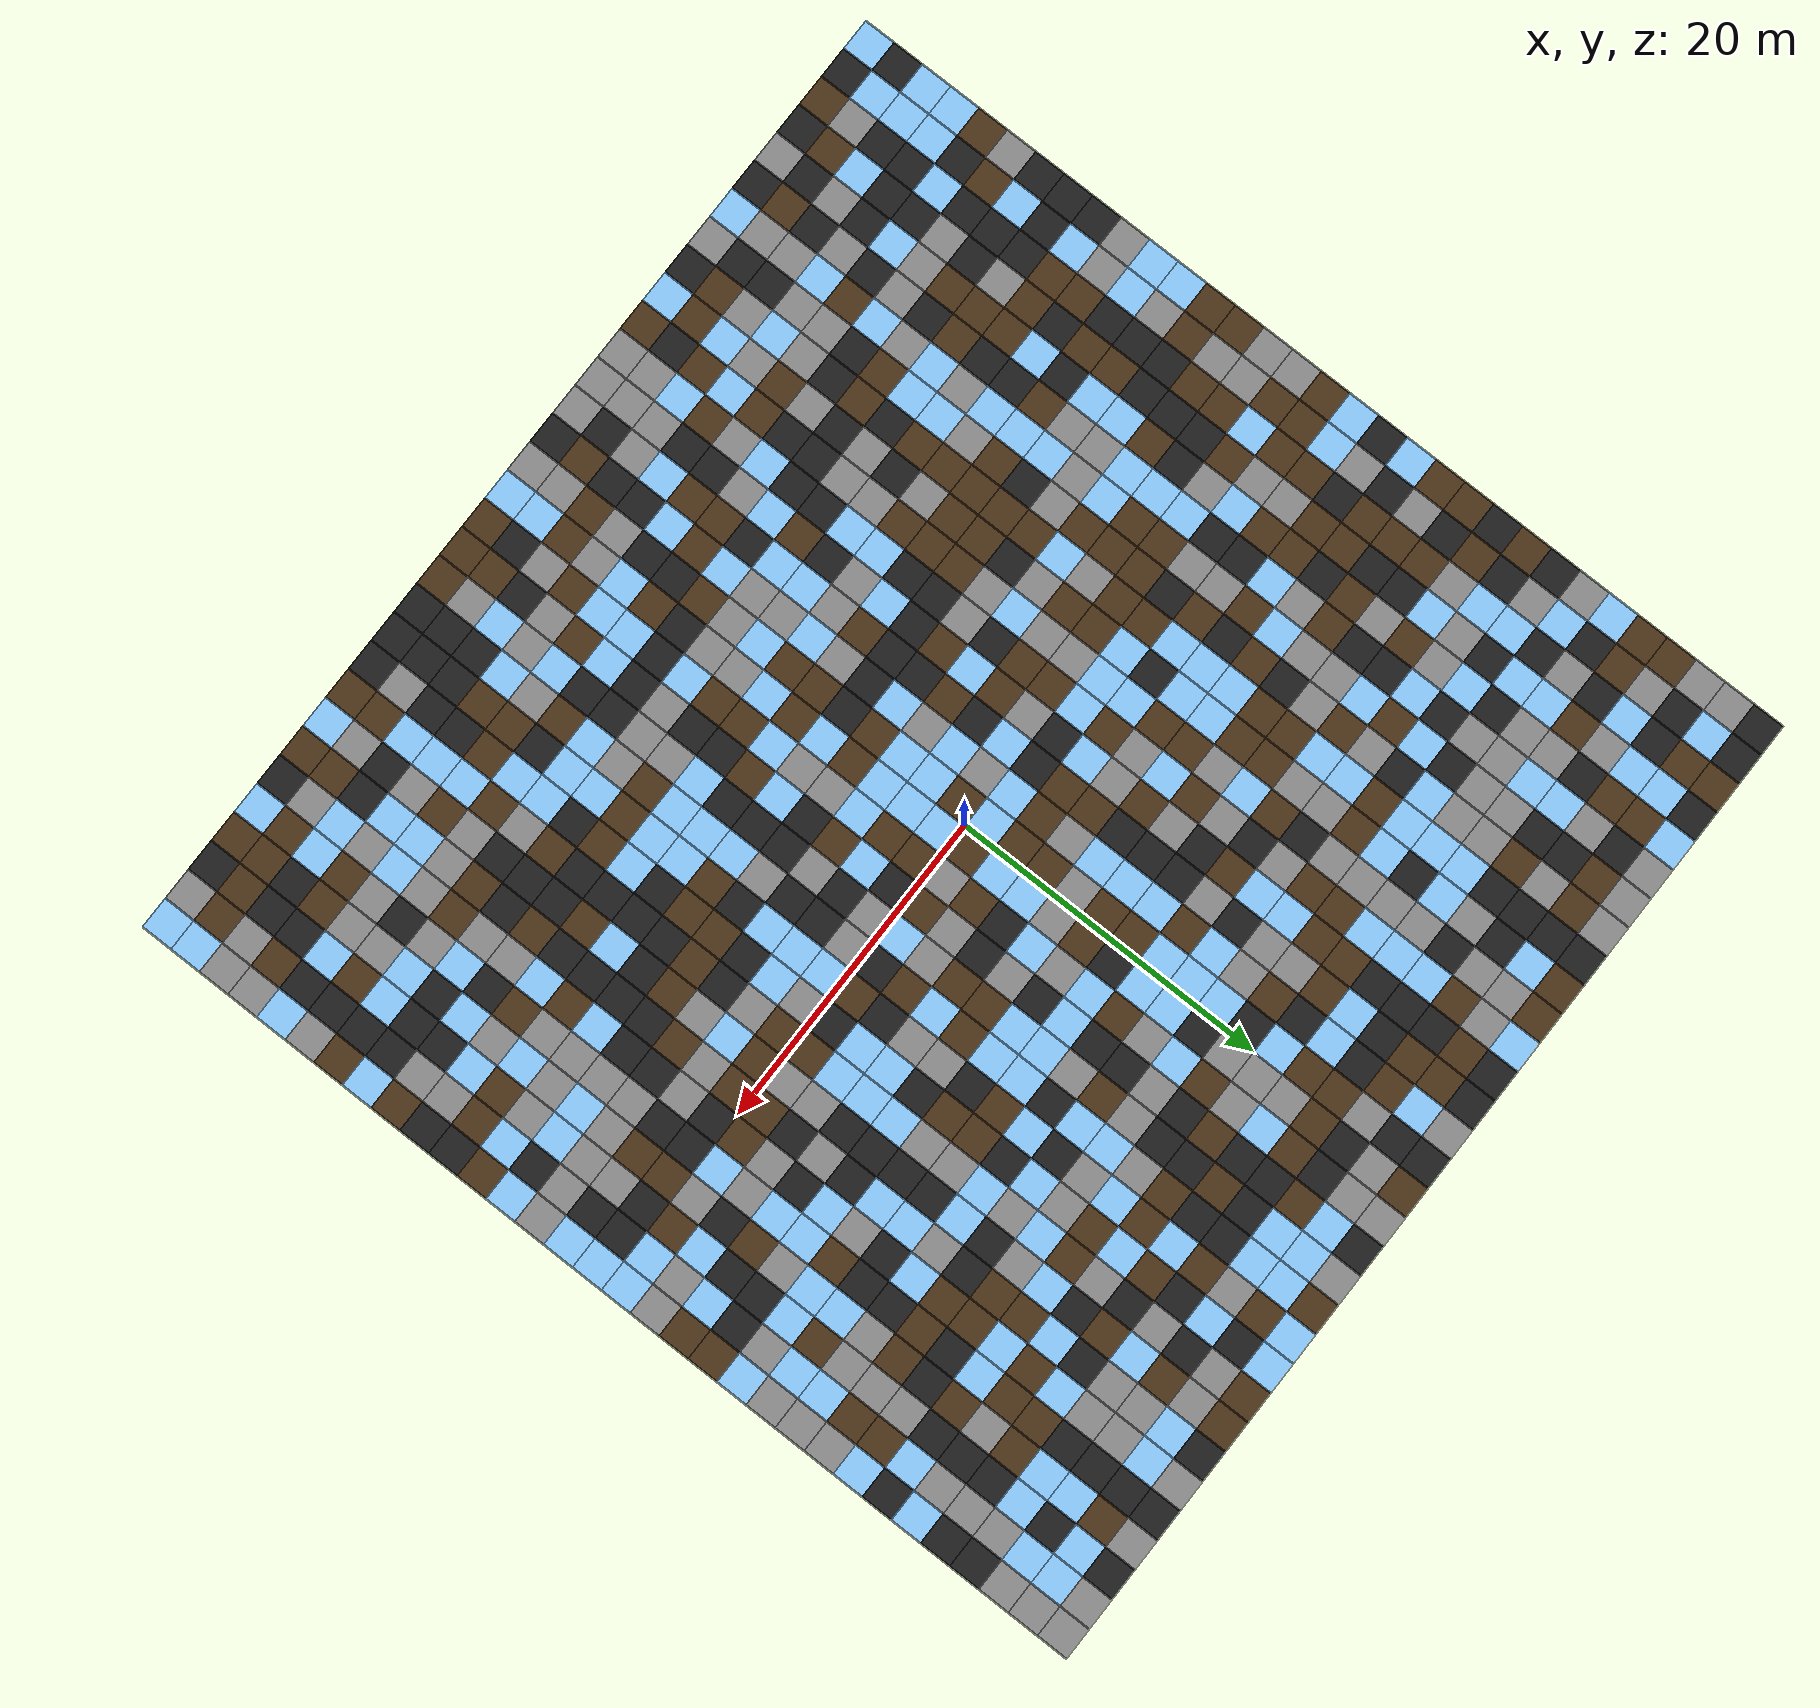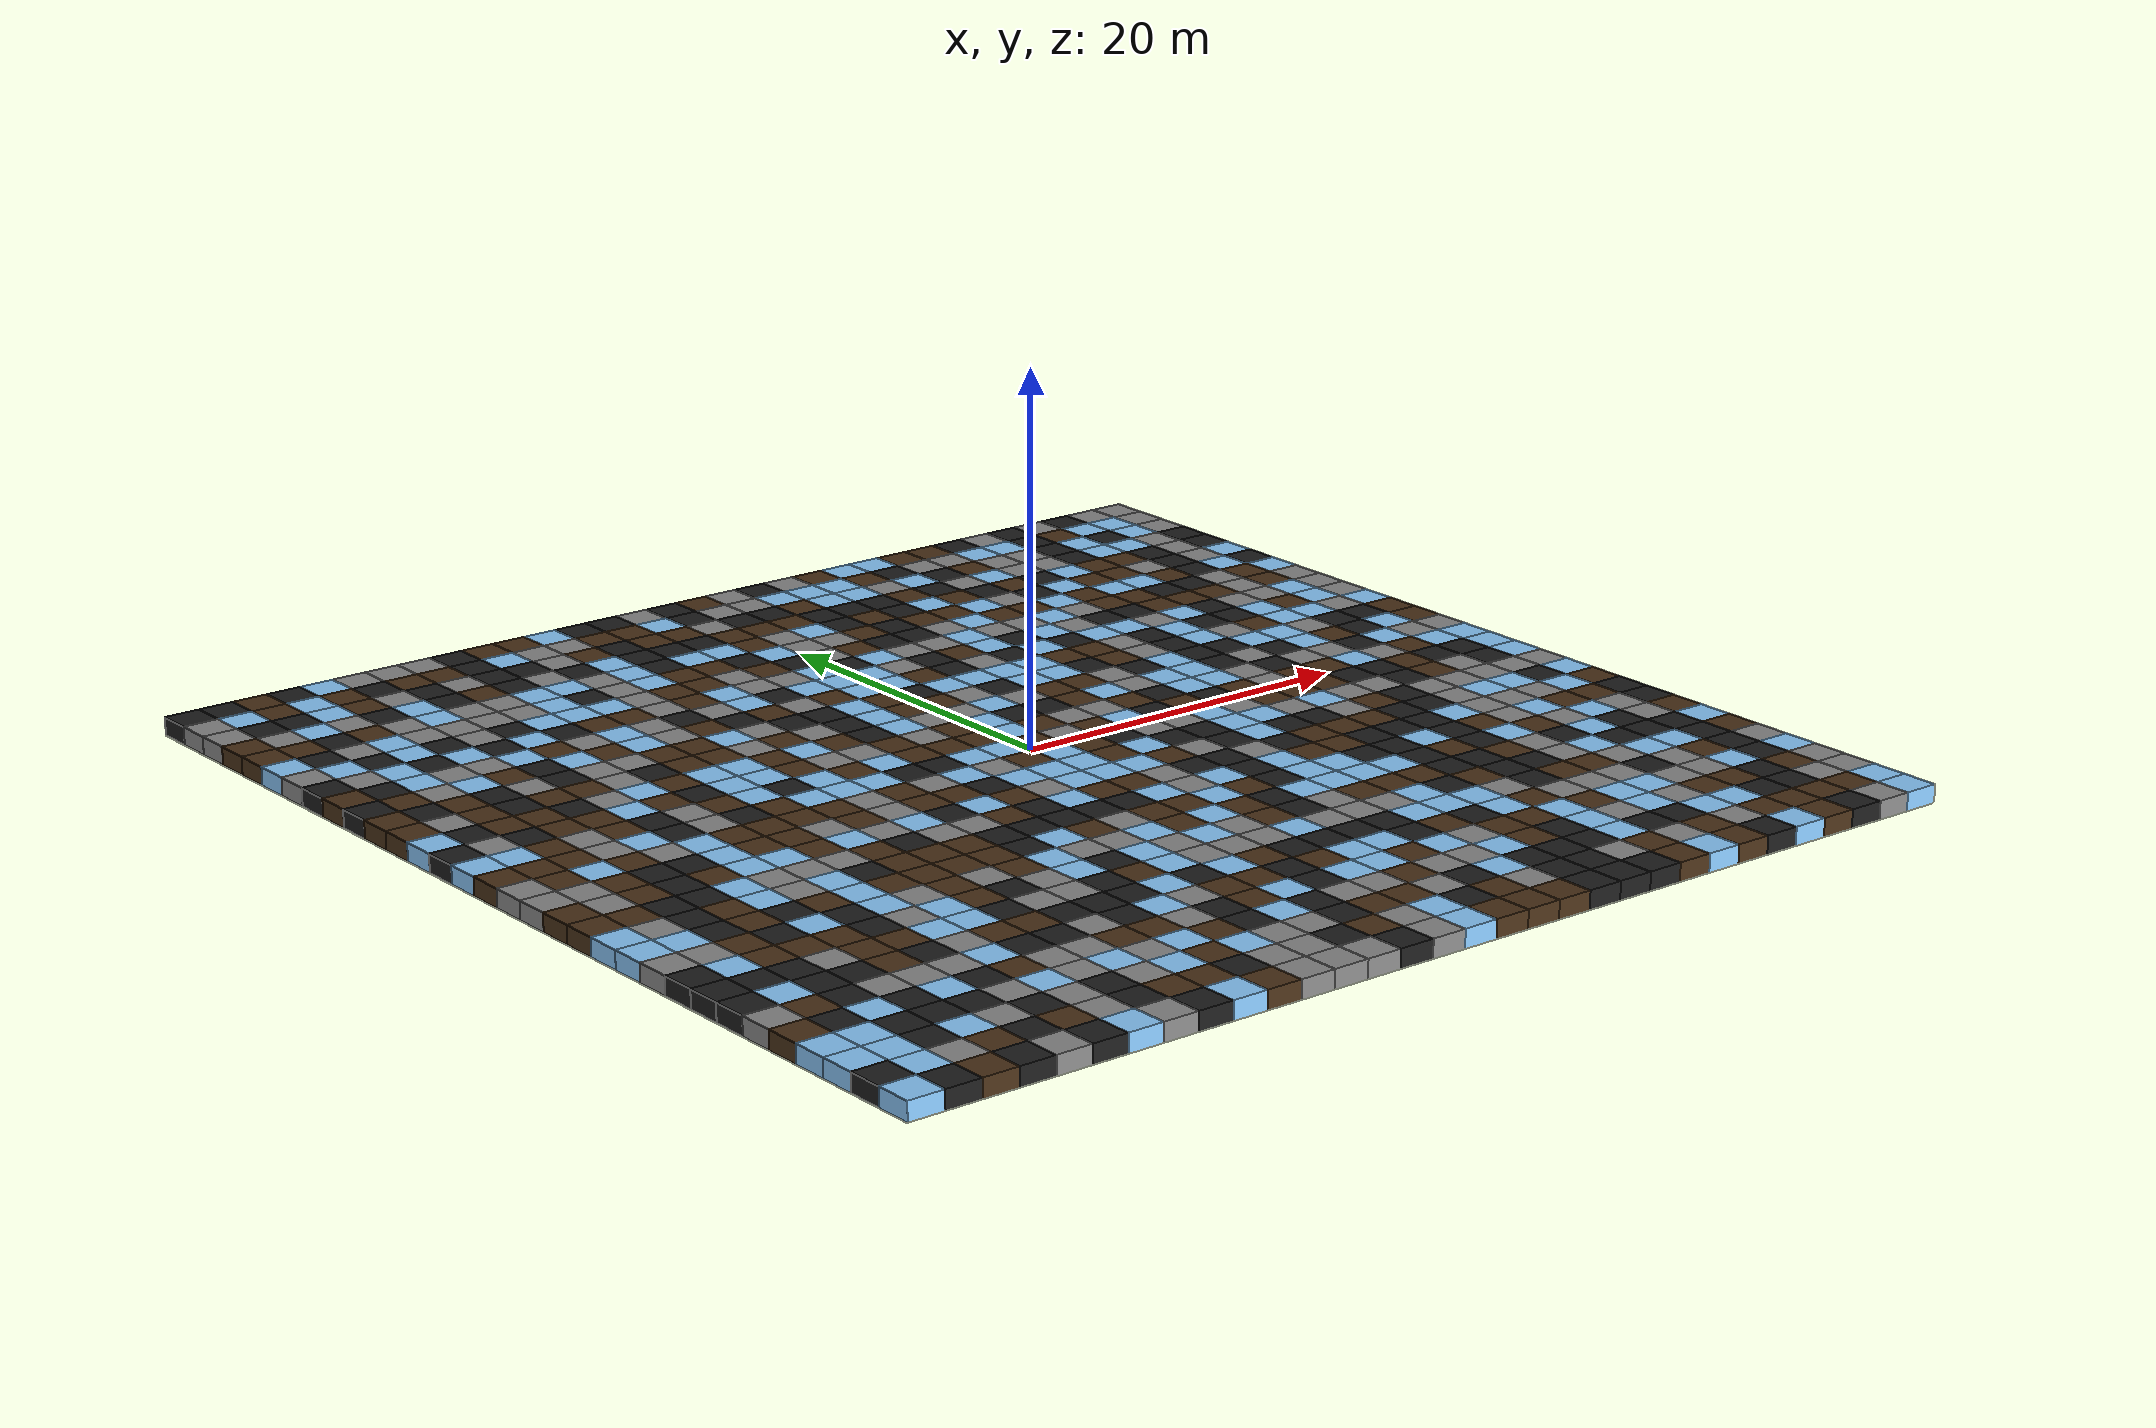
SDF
<?xml version="1.0" ?>
<sdf version="1.5">
  <world name="squares_example">
    <physics name="ode_physics" default="0" type="ode">
      <gravity>0 0 -9.8066</gravity>
      <ode>
        <solver>
          <type>quick</type>
          <iters>50</iters>
          <sor>1.3</sor>
        </solver>
        <constraints>
          <cfm>10e-5</cfm>
          <erp>0.2</erp>
          <contact_max_correcting_vel>100</contact_max_correcting_vel>
          <contact_surface_layer>0.001</contact_surface_layer>
        </constraints>
      </ode>
      <max_step_size>0.004</max_step_size>
      <real_time_factor>1</real_time_factor>
      <real_time_update_rate>250</real_time_update_rate>
    </physics>

    <scene>
      <ambient>0.4 0.4 0.4 1</ambient>
      <background>0.7 0.7 0.7 1</background>
      <shadows>false</shadows>
    </scene>

    <light name="sun" type="directional">
      <cast_shadows>1</cast_shadows>
      <pose>0 0 1000 0.4 0.2 0</pose>
      <diffuse>1 1 1 1</diffuse>
      <specular>0.6 0.6 0.6 1</specular>
      <direction>0.1 0.1 -0.9</direction>
    </light>

                    <model name="tile_0_0">
                        <static>true</static>
                        <pose>-31.000 -31.000 -0.500 0 0 0</pose>
                        <link name="link">
<collision name="col">

  <geometry>

                    <box>
                    <size>2.0 2.0 1.0</size>
                    </box>
  </geometry>

  <max_contacts>10</max_contacts>

  <surface>
    <friction>

      <ode>
        <mu>0.03</mu>
        <mu2>0.02</mu2>
        <fdir1>1 0 0</fdir1>
        <slip1>0.03</slip1>
        <slip2>0.03</slip2>
      </ode>

      <torsional>
        <coefficient>0.005</coefficient>
        <use_patch_radius>false</use_patch_radius>
        <surface_radius>0.12</surface_radius>
        <ode><slip>0.01</slip></ode>
      </torsional>

    </friction>

    <bounce>
      <restitution_coefficient>0.0</restitution_coefficient>
      <threshold>0.1</threshold>
    </bounce>

    <contact>
      <ode>
        <kp>10000000.0</kp>
        <kd>1000.0</kd>
        <max_vel>0.01</max_vel>
        <min_depth>0.0</min_depth>
      </ode>
    </contact>

  </surface>
</collision>

<visual name="visual">
  <geometry>
                    <box>
                    <size>2.0 2.0 1.0</size>
                    </box></geometry>
  <material>
    <diffuse>0.55 0.80 1.00 1</diffuse>
    <ambient>0 0 0 0</ambient>
    <specular>0 0 0 1</specular>
    <emissive>0 0 0 1</emissive>
  </material>
</visual>
</link>
                    </model>

                    <model name="tile_1_0">
                        <static>true</static>
                        <pose>-29.000 -31.000 -0.500 0 0 0</pose>
                        <link name="link">
<collision name="col">

  <geometry>

                    <box>
                    <size>2.0 2.0 1.0</size>
                    </box>
  </geometry>

  <max_contacts>10</max_contacts>

  <surface>
    <friction>

      <ode>
        <mu>0.4</mu>
        <mu2>0.15</mu2>
        <fdir1>1 0 0</fdir1>
        <slip1>0.0</slip1>
        <slip2>0.0</slip2>
      </ode>

      <torsional>
        <coefficient>0.03</coefficient>
        <use_patch_radius>false</use_patch_radius>
        <surface_radius>0.12</surface_radius>
        <ode><slip>0.0</slip></ode>
      </torsional>

    </friction>

    <bounce>
      <restitution_coefficient>0.0</restitution_coefficient>
      <threshold>0.1</threshold>
    </bounce>

    <contact>
      <ode>
        <kp>1000000000.0</kp>
        <kd>1000000.0</kd>
        <max_vel>0.01</max_vel>
        <min_depth>0.0</min_depth>
      </ode>
    </contact>

  </surface>
</collision>

<visual name="visual">
  <geometry>
                    <box>
                    <size>2.0 2.0 1.0</size>
                    </box></geometry>
  <material>
    <diffuse>0.12 0.12 0.12 1</diffuse>
    <ambient>0 0 0 0</ambient>
    <specular>0 0 0 1</specular>
    <emissive>0 0 0 1</emissive>
  </material>
</visual>
</link>
                    </model>

                    <model name="tile_2_0">
                        <static>true</static>
                        <pose>-27.000 -31.000 -0.500 0 0 0</pose>
                        <link name="link">
<collision name="col">

  <geometry>

                    <box>
                    <size>2.0 2.0 1.0</size>
                    </box>
  </geometry>

  <max_contacts>10</max_contacts>

  <surface>
    <friction>

      <ode>
        <mu>0.6</mu>
        <mu2>0.4</mu2>
        <fdir1>1 0 0</fdir1>
        <slip1>0.08</slip1>
        <slip2>0.08</slip2>
      </ode>

      <torsional>
        <coefficient>0.03</coefficient>
        <use_patch_radius>false</use_patch_radius>
        <surface_radius>0.12</surface_radius>
        <ode><slip>0.0</slip></ode>
      </torsional>

    </friction>

    <bounce>
      <restitution_coefficient>0.0</restitution_coefficient>
      <threshold>0.1</threshold>
    </bounce>

    <contact>
      <ode>
        <kp>1000000.0</kp>
        <kd>10000.0</kd>
        <max_vel>0.01</max_vel>
        <min_depth>0.0</min_depth>
      </ode>
    </contact>

  </surface>
</collision>

<visual name="visual">
  <geometry>
                    <box>
                    <size>2.0 2.0 1.0</size>
                    </box></geometry>
  <material>
    <diffuse>0.30 0.20 0.10 1</diffuse>
    <ambient>0 0 0 0</ambient>
    <specular>0 0 0 1</specular>
    <emissive>0 0 0 1</emissive>
  </material>
</visual>
</link>
                    </model>

                    <model name="tile_3_0">
                        <static>true</static>
                        <pose>-25.000 -31.000 -0.500 0 0 0</pose>
                        <link name="link">
<collision name="col">

  <geometry>

                    <box>
                    <size>2.0 2.0 1.0</size>
                    </box>
  </geometry>

  <max_contacts>10</max_contacts>

  <surface>
    <friction>

      <ode>
        <mu>0.4</mu>
        <mu2>0.15</mu2>
        <fdir1>1 0 0</fdir1>
        <slip1>0.0</slip1>
        <slip2>0.0</slip2>
      </ode>

      <torsional>
        <coefficient>0.03</coefficient>
        <use_patch_radius>false</use_patch_radius>
        <surface_radius>0.12</surface_radius>
        <ode><slip>0.0</slip></ode>
      </torsional>

    </friction>

    <bounce>
      <restitution_coefficient>0.0</restitution_coefficient>
      <threshold>0.1</threshold>
    </bounce>

    <contact>
      <ode>
        <kp>1000000000.0</kp>
        <kd>1000000.0</kd>
        <max_vel>0.01</max_vel>
        <min_depth>0.0</min_depth>
      </ode>
    </contact>

  </surface>
</collision>

<visual name="visual">
  <geometry>
                    <box>
                    <size>2.0 2.0 1.0</size>
                    </box></geometry>
  <material>
    <diffuse>0.12 0.12 0.12 1</diffuse>
    <ambient>0 0 0 0</ambient>
    <specular>0 0 0 1</specular>
    <emissive>0 0 0 1</emissive>
  </material>
</visual>
</link>
                    </model>

                    <model name="tile_4_0">
                        <static>true</static>
                        <pose>-23.000 -31.000 -0.500 0 0 0</pose>
                        <link name="link">
<collision name="col">

  <geometry>

                    <box>
                    <size>2.0 2.0 1.0</size>
                    </box>
  </geometry>

  <max_contacts>10</max_contacts>

  <surface>
    <friction>

      <ode>
        <mu>0.8</mu>
        <mu2>0.3</mu2>
        <fdir1>1 0 0</fdir1>
        <slip1>0.0</slip1>
        <slip2>0.0</slip2>
      </ode>

      <torsional>
        <coefficient>0.03</coefficient>
        <use_patch_radius>false</use_patch_radius>
        <surface_radius>0.12</surface_radius>
        <ode><slip>0.0</slip></ode>
      </torsional>

    </friction>

    <bounce>
      <restitution_coefficient>0.0</restitution_coefficient>
      <threshold>0.1</threshold>
    </bounce>

    <contact>
      <ode>
        <kp>10000000000.0</kp>
        <kd>10000000.0</kd>
        <max_vel>0.01</max_vel>
        <min_depth>0.0</min_depth>
      </ode>
    </contact>

  </surface>
</collision>

<visual name="visual">
  <geometry>
                    <box>
                    <size>2.0 2.0 1.0</size>
                    </box></geometry>
  <material>
    <diffuse>0.55 0.55 0.55 1</diffuse>
    <ambient>0 0 0 0</ambient>
    <specular>0 0 0 1</specular>
    <emissive>0 0 0 1</emissive>
  </material>
</visual>
</link>
                    </model>

                    <model name="tile_5_0">
                        <static>true</static>
                        <pose>-21.000 -31.000 -0.500 0 0 0</pose>
                        <link name="link">
<collision name="col">

  <geometry>

                    <box>
                    <size>2.0 2.0 1.0</size>
                    </box>
  </geometry>

  <max_contacts>10</max_contacts>

  <surface>
    <friction>

      <ode>
        <mu>0.4</mu>
        <mu2>0.15</mu2>
        <fdir1>1 0 0</fdir1>
        <slip1>0.0</slip1>
        <slip2>0.0</slip2>
      </ode>

      <torsional>
        <coefficient>0.03</coefficient>
        <use_patch_radius>false</use_patch_radius>
        <surface_radius>0.12</surface_radius>
        <ode><slip>0.0</slip></ode>
      </torsional>

    </friction>

    <bounce>
      <restitution_coefficient>0.0</restitution_coefficient>
      <threshold>0.1</threshold>
    </bounce>

    <contact>
      <ode>
        <kp>1000000000.0</kp>
        <kd>1000000.0</kd>
        <max_vel>0.01</max_vel>
        <min_depth>0.0</min_depth>
      </ode>
    </contact>

  </surface>
</collision>

<visual name="visual">
  <geometry>
                    <box>
                    <size>2.0 2.0 1.0</size>
                    </box></geometry>
  <material>
    <diffuse>0.12 0.12 0.12 1</diffuse>
    <ambient>0 0 0 0</ambient>
    <specular>0 0 0 1</specular>
    <emissive>0 0 0 1</emissive>
  </material>
</visual>
</link>
                    </model>

                    <model name="tile_6_0">
                        <static>true</static>
                        <pose>-19.000 -31.000 -0.500 0 0 0</pose>
                        <link name="link">
<collision name="col">

  <geometry>

                    <box>
                    <size>2.0 2.0 1.0</size>
                    </box>
  </geometry>

  <max_contacts>10</max_contacts>

  <surface>
    <friction>

      <ode>
        <mu>0.03</mu>
        <mu2>0.02</mu2>
        <fdir1>1 0 0</fdir1>
        <slip1>0.03</slip1>
        <slip2>0.03</slip2>
      </ode>

      <torsional>
        <coefficient>0.005</coefficient>
        <use_patch_radius>false</use_patch_radius>
        <surface_radius>0.12</surface_radius>
        <ode><slip>0.01</slip></ode>
      </torsional>

    </friction>

    <bounce>
      <restitution_coefficient>0.0</restitution_coefficient>
      <threshold>0.1</threshold>
    </bounce>

    <contact>
      <ode>
        <kp>10000000.0</kp>
        <kd>1000.0</kd>
        <max_vel>0.01</max_vel>
        <min_depth>0.0</min_depth>
      </ode>
    </contact>

  </surface>
</collision>

<visual name="visual">
  <geometry>
                    <box>
                    <size>2.0 2.0 1.0</size>
                    </box></geometry>
  <material>
    <diffuse>0.55 0.80 1.00 1</diffuse>
    <ambient>0 0 0 0</ambient>
    <specular>0 0 0 1</specular>
    <emissive>0 0 0 1</emissive>
  </material>
</visual>
</link>
                    </model>

                    <model name="tile_7_0">
                        <static>true</static>
                        <pose>-17.000 -31.000 -0.500 0 0 0</pose>
                        <link name="link">
<collision name="col">

  <geometry>

                    <box>
                    <size>2.0 2.0 1.0</size>
                    </box>
  </geometry>

  <max_contacts>10</max_contacts>

  <surface>
    <friction>

      <ode>
        <mu>0.8</mu>
        <mu2>0.3</mu2>
        <fdir1>1 0 0</fdir1>
        <slip1>0.0</slip1>
        <slip2>0.0</slip2>
      </ode>

      <torsional>
        <coefficient>0.03</coefficient>
        <use_patch_radius>false</use_patch_radius>
        <surface_radius>0.12</surface_radius>
        <ode><slip>0.0</slip></ode>
      </torsional>

    </friction>

    <bounce>
      <restitution_coefficient>0.0</restitution_coefficient>
      <threshold>0.1</threshold>
    </bounce>

    <contact>
      <ode>
        <kp>10000000000.0</kp>
        <kd>10000000.0</kd>
        <max_vel>0.01</max_vel>
        <min_depth>0.0</min_depth>
      </ode>
    </contact>

  </surface>
</collision>

<visual name="visual">
  <geometry>
                    <box>
                    <size>2.0 2.0 1.0</size>
                    </box></geometry>
  <material>
    <diffuse>0.55 0.55 0.55 1</diffuse>
    <ambient>0 0 0 0</ambient>
    <specular>0 0 0 1</specular>
    <emissive>0 0 0 1</emissive>
  </material>
</visual>
</link>
                    </model>

                    <model name="tile_8_0">
                        <static>true</static>
                        <pose>-15.000 -31.000 -0.500 0 0 0</pose>
                        <link name="link">
<collision name="col">

  <geometry>

                    <box>
                    <size>2.0 2.0 1.0</size>
                    </box>
  </geometry>

  <max_contacts>10</max_contacts>

  <surface>
    <friction>

      <ode>
        <mu>0.4</mu>
        <mu2>0.15</mu2>
        <fdir1>1 0 0</fdir1>
        <slip1>0.0</slip1>
        <slip2>0.0</slip2>
      </ode>

      <torsional>
        <coefficient>0.03</coefficient>
        <use_patch_radius>false</use_patch_radius>
        <surface_radius>0.12</surface_radius>
        <ode><slip>0.0</slip></ode>
      </torsional>

    </friction>

    <bounce>
      <restitution_coefficient>0.0</restitution_coefficient>
      <threshold>0.1</threshold>
    </bounce>

    <contact>
      <ode>
        <kp>1000000000.0</kp>
        <kd>1000000.0</kd>
        <max_vel>0.01</max_vel>
        <min_depth>0.0</min_depth>
      </ode>
    </contact>

  </surface>
</collision>

<visual name="visual">
  <geometry>
                    <box>
                    <size>2.0 2.0 1.0</size>
                    </box></geometry>
  <material>
    <diffuse>0.12 0.12 0.12 1</diffuse>
    <ambient>0 0 0 0</ambient>
    <specular>0 0 0 1</specular>
    <emissive>0 0 0 1</emissive>
  </material>
</visual>
</link>
                    </model>

                    <model name="tile_9_0">
                        <static>true</static>
                        <pose>-13.000 -31.000 -0.500 0 0 0</pose>
                        <link name="link">
<collision name="col">

  <geometry>

                    <box>
                    <size>2.0 2.0 1.0</size>
                    </box>
  </geometry>

  <max_contacts>10</max_contacts>

  <surface>
    <friction>

      <ode>
        <mu>0.03</mu>
        <mu2>0.02</mu2>
        <fdir1>1 0 0</fdir1>
        <slip1>0.03</slip1>
        <slip2>0.03</slip2>
      </ode>

      <torsional>
        <coefficient>0.005</coefficient>
        <use_patch_radius>false</use_patch_radius>
        <surface_radius>0.12</surface_radius>
        <ode><slip>0.01</slip></ode>
      </torsional>

    </friction>

    <bounce>
      <restitution_coefficient>0.0</restitution_coefficient>
      <threshold>0.1</threshold>
    </bounce>

    <contact>
      <ode>
        <kp>10000000.0</kp>
        <kd>1000.0</kd>
        <max_vel>0.01</max_vel>
        <min_depth>0.0</min_depth>
      </ode>
    </contact>

  </surface>
</collision>

<visual name="visual">
  <geometry>
                    <box>
                    <size>2.0 2.0 1.0</size>
                    </box></geometry>
  <material>
    <diffuse>0.55 0.80 1.00 1</diffuse>
    <ambient>0 0 0 0</ambient>
    <specular>0 0 0 1</specular>
    <emissive>0 0 0 1</emissive>
  </material>
</visual>
</link>
                    </model>

                    <model name="tile_10_0">
                        <static>true</static>
                        <pose>-11.000 -31.000 -0.500 0 0 0</pose>
                        <link name="link">
<collision name="col">

  <geometry>

                    <box>
                    <size>2.0 2.0 1.0</size>
                    </box>
  </geometry>

  <max_contacts>10</max_contacts>

  <surface>
    <friction>

      <ode>
        <mu>0.6</mu>
        <mu2>0.4</mu2>
        <fdir1>1 0 0</fdir1>
        <slip1>0.08</slip1>
        <slip2>0.08</slip2>
      </ode>

      <torsional>
        <coefficient>0.03</coefficient>
        <use_patch_radius>false</use_patch_radius>
        <surface_radius>0.12</surface_radius>
        <ode><slip>0.0</slip></ode>
      </torsional>

    </friction>

    <bounce>
      <restitution_coefficient>0.0</restitution_coefficient>
      <threshold>0.1</threshold>
    </bounce>

    <contact>
      <ode>
        <kp>1000000.0</kp>
        <kd>10000.0</kd>
        <max_vel>0.01</max_vel>
        <min_depth>0.0</min_depth>
      </ode>
    </contact>

  </surface>
</collision>

<visual name="visual">
  <geometry>
                    <box>
                    <size>2.0 2.0 1.0</size>
                    </box></geometry>
  <material>
    <diffuse>0.30 0.20 0.10 1</diffuse>
    <ambient>0 0 0 0</ambient>
    <specular>0 0 0 1</specular>
    <emissive>0 0 0 1</emissive>
  </material>
</visual>
</link>
                    </model>

                    <model name="tile_11_0">
                        <static>true</static>
                        <pose>-9.000 -31.000 -0.500 0 0 0</pose>
                        <link name="link">
<collision name="col">

  <geometry>

                    <box>
                    <size>2.0 2.0 1.0</size>
                    </box>
  </geometry>

  <max_contacts>10</max_contacts>

  <surface>
    <friction>

      <ode>
        <mu>0.8</mu>
        <mu2>0.3</mu2>
        <fdir1>1 0 0</fdir1>
        <slip1>0.0</slip1>
        <slip2>0.0</slip2>
      </ode>

      <torsional>
        <coefficient>0.03</coefficient>
        <use_patch_radius>false</use_patch_radius>
        <surface_radius>0.12</surface_radius>
        <ode><slip>0.0</slip></ode>
      </torsional>

    </friction>

    <bounce>
      <restitution_coefficient>0.0</restitution_coefficient>
      <threshold>0.1</threshold>
    </bounce>

    <contact>
      <ode>
        <kp>10000000000.0</kp>
        <kd>10000000.0</kd>
        <max_vel>0.01</max_vel>
        <min_depth>0.0</min_depth>
      </ode>
    </contact>

  </surface>
</collision>

<visual name="visual">
  <geometry>
                    <box>
                    <size>2.0 2.0 1.0</size>
                    </box></geometry>
  <material>
    <diffuse>0.55 0.55 0.55 1</diffuse>
    <ambient>0 0 0 0</ambient>
    <specular>0 0 0 1</specular>
    <emissive>0 0 0 1</emissive>
  </material>
</visual>
</link>
                    </model>

                    <model name="tile_12_0">
                        <static>true</static>
                        <pose>-7.000 -31.000 -0.500 0 0 0</pose>
                        <link name="link">
<collision name="col">

  <geometry>

                    <box>
                    <size>2.0 2.0 1.0</size>
                    </box>
  </geometry>

  <max_contacts>10</max_contacts>

  <surface>
    <friction>

      <ode>
        <mu>0.8</mu>
        <mu2>0.3</mu2>
        <fdir1>1 0 0</fdir1>
        <slip1>0.0</slip1>
        <slip2>0.0</slip2>
      </ode>

      <torsional>
        <coefficient>0.03</coefficient>
        <use_patch_radius>false</use_patch_radius>
        <surface_radius>0.12</surface_radius>
        <ode><slip>0.0</slip></ode>
      </torsional>

    </friction>

    <bounce>
      <restitution_coefficient>0.0</restitution_coefficient>
      <threshold>0.1</threshold>
    </bounce>

    <contact>
      <ode>
        <kp>10000000000.0</kp>
        <kd>10000000.0</kd>
        <max_vel>0.01</max_vel>
        <min_depth>0.0</min_depth>
      </ode>
    </contact>

  </surface>
</collision>

<visual name="visual">
  <geometry>
                    <box>
                    <size>2.0 2.0 1.0</size>
                    </box></geometry>
  <material>
    <diffuse>0.55 0.55 0.55 1</diffuse>
    <ambient>0 0 0 0</ambient>
    <specular>0 0 0 1</specular>
    <emissive>0 0 0 1</emissive>
  </material>
</visual>
</link>
                    </model>

                    <model name="tile_13_0">
                        <static>true</static>
                        <pose>-5.000 -31.000 -0.500 0 0 0</pose>
                        <link name="link">
<collision name="col">

  <geometry>

                    <box>
                    <size>2.0 2.0 1.0</size>
                    </box>
  </geometry>

  <max_contacts>10</max_contacts>

  <surface>
    <friction>

      <ode>
        <mu>0.8</mu>
        <mu2>0.3</mu2>
        <fdir1>1 0 0</fdir1>
        <slip1>0.0</slip1>
        <slip2>0.0</slip2>
      </ode>

      <torsional>
        <coefficient>0.03</coefficient>
        <use_patch_radius>false</use_patch_radius>
        <surface_radius>0.12</surface_radius>
        <ode><slip>0.0</slip></ode>
      </torsional>

    </friction>

    <bounce>
      <restitution_coefficient>0.0</restitution_coefficient>
      <threshold>0.1</threshold>
    </bounce>

    <contact>
      <ode>
        <kp>10000000000.0</kp>
        <kd>10000000.0</kd>
        <max_vel>0.01</max_vel>
        <min_depth>0.0</min_depth>
      </ode>
    </contact>

  </surface>
</collision>

<visual name="visual">
  <geometry>
                    <box>
                    <size>2.0 2.0 1.0</size>
                    </box></geometry>
  <material>
    <diffuse>0.55 0.55 0.55 1</diffuse>
    <ambient>0 0 0 0</ambient>
    <specular>0 0 0 1</specular>
    <emissive>0 0 0 1</emissive>
  </material>
</visual>
</link>
                    </model>

                    <model name="tile_14_0">
                        <static>true</static>
                        <pose>-3.000 -31.000 -0.500 0 0 0</pose>
                        <link name="link">
<collision name="col">

  <geometry>

                    <box>
                    <size>2.0 2.0 1.0</size>
                    </box>
  </geometry>

  <max_contacts>10</max_contacts>

  <surface>
    <friction>

      <ode>
        <mu>0.4</mu>
        <mu2>0.15</mu2>
        <fdir1>1 0 0</fdir1>
        <slip1>0.0</slip1>
        <slip2>0.0</slip2>
      </ode>

      <torsional>
        <coefficient>0.03</coefficient>
        <use_patch_radius>false</use_patch_radius>
        <surface_radius>0.12</surface_radius>
        <ode><slip>0.0</slip></ode>
      </torsional>

    </friction>

    <bounce>
      <restitution_coefficient>0.0</restitution_coefficient>
      <threshold>0.1</threshold>
    </bounce>

    <contact>
      <ode>
        <kp>1000000000.0</kp>
        <kd>1000000.0</kd>
        <max_vel>0.01</max_vel>
        <min_depth>0.0</min_depth>
      </ode>
    </contact>

  </surface>
</collision>

<visual name="visual">
  <geometry>
                    <box>
                    <size>2.0 2.0 1.0</size>
                    </box></geometry>
  <material>
    <diffuse>0.12 0.12 0.12 1</diffuse>
    <ambient>0 0 0 0</ambient>
    <specular>0 0 0 1</specular>
    <emissive>0 0 0 1</emissive>
  </material>
</visual>
</link>
                    </model>

                    <model name="tile_15_0">
                        <static>true</static>
                        <pose>-1.000 -31.000 -0.500 0 0 0</pose>
                        <link name="link">
<collision name="col">

  <geometry>

                    <box>
                    <size>2.0 2.0 1.0</size>
                    </box>
  </geometry>

  <max_contacts>10</max_contacts>

  <surface>
    <friction>

      <ode>
        <mu>0.8</mu>
        <mu2>0.3</mu2>
        <fdir1>1 0 0</fdir1>
        <slip1>0.0</slip1>
        <slip2>0.0</slip2>
      </ode>

      <torsional>
        <coefficient>0.03</coefficient>
        <use_patch_radius>false</use_patch_radius>
        <surface_radius>0.12</surface_radius>
        <ode><slip>0.0</slip></ode>
      </torsional>

    </friction>

    <bounce>
      <restitution_coefficient>0.0</restitution_coefficient>
      <threshold>0.1</threshold>
    </bounce>

    <contact>
      <ode>
        <kp>10000000000.0</kp>
        <kd>10000000.0</kd>
        <max_vel>0.01</max_vel>
        <min_depth>0.0</min_depth>
      </ode>
    </contact>

  </surface>
</collision>

<visual name="visual">
  <geometry>
                    <box>
                    <size>2.0 2.0 1.0</size>
                    </box></geometry>
  <material>
    <diffuse>0.55 0.55 0.55 1</diffuse>
    <ambient>0 0 0 0</ambient>
    <specular>0 0 0 1</specular>
    <emissive>0 0 0 1</emissive>
  </material>
</visual>
</link>
                    </model>

                    <model name="tile_16_0">
                        <static>true</static>
                        <pose>1.000 -31.000 -0.500 0 0 0</pose>
                        <link name="link">
<collision name="col">

  <geometry>

                    <box>
                    <size>2.0 2.0 1.0</size>
                    </box>
  </geometry>

  <max_contacts>10</max_contacts>

  <surface>
    <friction>

      <ode>
        <mu>0.03</mu>
        <mu2>0.02</mu2>
        <fdir1>1 0 0</fdir1>
        <slip1>0.03</slip1>
        <slip2>0.03</slip2>
      </ode>

      <torsional>
        <coefficient>0.005</coefficient>
        <use_patch_radius>false</use_patch_radius>
        <surface_radius>0.12</surface_radius>
        <ode><slip>0.01</slip></ode>
      </torsional>

    </friction>

    <bounce>
      <restitution_coefficient>0.0</restitution_coefficient>
      <threshold>0.1</threshold>
    </bounce>

    <contact>
      <ode>
        <kp>10000000.0</kp>
        <kd>1000.0</kd>
        <max_vel>0.01</max_vel>
        <min_depth>0.0</min_depth>
      </ode>
    </contact>

  </surface>
</collision>

<visual name="visual">
  <geometry>
                    <box>
                    <size>2.0 2.0 1.0</size>
                    </box></geometry>
  <material>
    <diffuse>0.55 0.80 1.00 1</diffuse>
    <ambient>0 0 0 0</ambient>
    <specular>0 0 0 1</specular>
    <emissive>0 0 0 1</emissive>
  </material>
</visual>
</link>
                    </model>

                    <model name="tile_17_0">
                        <static>true</static>
                        <pose>3.000 -31.000 -0.500 0 0 0</pose>
                        <link name="link">
<collision name="col">

  <geometry>

                    <box>
                    <size>2.0 2.0 1.0</size>
                    </box>
  </geometry>

  <max_contacts>10</max_contacts>

  <surface>
    <friction>

      <ode>
        <mu>0.6</mu>
        <mu2>0.4</mu2>
        <fdir1>1 0 0</fdir1>
        <slip1>0.08</slip1>
        <slip2>0.08</slip2>
      </ode>

      <torsional>
        <coefficient>0.03</coefficient>
        <use_patch_radius>false</use_patch_radius>
        <surface_radius>0.12</surface_radius>
        <ode><slip>0.0</slip></ode>
      </torsional>

    </friction>

    <bounce>
      <restitution_coefficient>0.0</restitution_coefficient>
      <threshold>0.1</threshold>
    </bounce>

    <contact>
      <ode>
        <kp>1000000.0</kp>
        <kd>10000.0</kd>
        <max_vel>0.01</max_vel>
        <min_depth>0.0</min_depth>
      </ode>
    </contact>

  </surface>
</collision>

<visual name="visual">
  <geometry>
                    <box>
                    <size>2.0 2.0 1.0</size>
                    </box></geometry>
  <material>
    <diffuse>0.30 0.20 0.10 1</diffuse>
    <ambient>0 0 0 0</ambient>
    <specular>0 0 0 1</specular>
    <emissive>0 0 0 1</emissive>
  </material>
</visual>
</link>
                    </model>

                    <model name="tile_18_0">
                        <static>true</static>
                        <pose>5.000 -31.000 -0.500 0 0 0</pose>
                        <link name="link">
<collision name="col">

  <geometry>

                    <box>
                    <size>2.0 2.0 1.0</size>
                    </box>
  </geometry>

  <max_contacts>10</max_contacts>

  <surface>
    <friction>

      <ode>
        <mu>0.6</mu>
        <mu2>0.4</mu2>
        <fdir1>1 0 0</fdir1>
        <slip1>0.08</slip1>
        <slip2>0.08</slip2>
      </ode>

      <torsional>
        <coefficient>0.03</coefficient>
        <use_patch_radius>false</use_patch_radius>
        <surface_radius>0.12</surface_radius>
        <ode><slip>0.0</slip></ode>
      </torsional>

    </friction>

    <bounce>
      <restitution_coefficient>0.0</restitution_coefficient>
      <threshold>0.1</threshold>
    </bounce>

    <contact>
      <ode>
        <kp>1000000.0</kp>
        <kd>10000.0</kd>
        <max_vel>0.01</max_vel>
        <min_depth>0.0</min_depth>
      </ode>
    </contact>

  </surface>
</collision>

<visual name="visual">
  <geometry>
                    <box>
                    <size>2.0 2.0 1.0</size>
                    </box></geometry>
  <material>
    <diffuse>0.30 0.20 0.10 1</diffuse>
    <ambient>0 0 0 0</ambient>
    <specular>0 0 0 1</specular>
    <emissive>0 0 0 1</emissive>
  </material>
</visual>
</link>
                    </model>

                    <model name="tile_19_0">
                        <static>true</static>
                        <pose>7.000 -31.000 -0.500 0 0 0</pose>
                        <link name="link">
<collision name="col">

  <geometry>

                    <box>
                    <size>2.0 2.0 1.0</size>
                    </box>
  </geometry>

  <max_contacts>10</max_contacts>

  <surface>
    <friction>

      <ode>
        <mu>0.6</mu>
        <mu2>0.4</mu2>
        <fdir1>1 0 0</fdir1>
        <slip1>0.08</slip1>
        <slip2>0.08</slip2>
      </ode>

      <torsional>
        <coefficient>0.03</coefficient>
        <use_patch_radius>false</use_patch_radius>
        <surface_radius>0.12</surface_radius>
        <ode><slip>0.0</slip></ode>
      </torsional>

    </friction>

    <bounce>
      <restitution_coefficient>0.0</restitution_coefficient>
      <threshold>0.1</threshold>
    </bounce>

    <contact>
      <ode>
        <kp>1000000.0</kp>
        <kd>10000.0</kd>
        <max_vel>0.01</max_vel>
        <min_depth>0.0</min_depth>
      </ode>
    </contact>

  </surface>
</collision>

<visual name="visual">
  <geometry>
                    <box>
                    <size>2.0 2.0 1.0</size>
                    </box></geometry>
  <material>
    <diffuse>0.30 0.20 0.10 1</diffuse>
    <ambient>0 0 0 0</ambient>
    <specular>0 0 0 1</specular>
    <emissive>0 0 0 1</emissive>
  </material>
</visual>
</link>
                    </model>

                    <model name="tile_20_0">
                        <static>true</static>
                        <pose>9.000 -31.000 -0.500 0 0 0</pose>
                        <link name="link">
<collision name="col">

  <geometry>

                    <box>
                    <size>2.0 2.0 1.0</size>
                    </box>
  </geometry>

  <max_contacts>10</max_contacts>

  <surface>
    <friction>

      <ode>
        <mu>0.4</mu>
        <mu2>0.15</mu2>
        <fdir1>1 0 0</fdir1>
        <slip1>0.0</slip1>
        <slip2>0.0</slip2>
      </ode>

      <torsional>
        <coefficient>0.03</coefficient>
        <use_patch_radius>false</use_patch_radius>
        <surface_radius>0.12</surface_radius>
        <ode><slip>0.0</slip></ode>
      </torsional>

    </friction>

    <bounce>
      <restitution_coefficient>0.0</restitution_coefficient>
      <threshold>0.1</threshold>
    </bounce>

    <contact>
      <ode>
        <kp>1000000000.0</kp>
        <kd>1000000.0</kd>
        <max_vel>0.01</max_vel>
        <min_depth>0.0</min_depth>
      </ode>
    </contact>

  </surface>
</collision>

<visual name="visual">
  <geometry>
                    <box>
                    <size>2.0 2.0 1.0</size>
                    </box></geometry>
  <material>
    <diffuse>0.12 0.12 0.12 1</diffuse>
    <ambient>0 0 0 0</ambient>
    <specular>0 0 0 1</specular>
    <emissive>0 0 0 1</emissive>
  </material>
</visual>
</link>
                    </model>

                    <model name="tile_21_0">
                        <static>true</static>
                        <pose>11.000 -31.000 -0.500 0 0 0</pose>
                        <link name="link">
<collision name="col">

  <geometry>

                    <box>
                    <size>2.0 2.0 1.0</size>
                    </box>
  </geometry>

  <max_contacts>10</max_contacts>

  <surface>
    <friction>

      <ode>
        <mu>0.4</mu>
        <mu2>0.15</mu2>
        <fdir1>1 0 0</fdir1>
        <slip1>0.0</slip1>
        <slip2>0.0</slip2>
      </ode>

      <torsional>
        <coefficient>0.03</coefficient>
        <use_patch_radius>false</use_patch_radius>
        <surface_radius>0.12</surface_radius>
        <ode><slip>0.0</slip></ode>
      </torsional>

    </friction>

    <bounce>
      <restitution_coefficient>0.0</restitution_coefficient>
      <threshold>0.1</threshold>
    </bounce>

    <contact>
      <ode>
        <kp>1000000000.0</kp>
        <kd>1000000.0</kd>
        <max_vel>0.01</max_vel>
        <min_depth>0.0</min_depth>
      </ode>
    </contact>

  </surface>
</collision>

<visual name="visual">
  <geometry>
                    <box>
                    <size>2.0 2.0 1.0</size>
                    </box></geometry>
  <material>
    <diffuse>0.12 0.12 0.12 1</diffuse>
    <ambient>0 0 0 0</ambient>
    <specular>0 0 0 1</specular>
    <emissive>0 0 0 1</emissive>
  </material>
</visual>
</link>
                    </model>

                    <model name="tile_22_0">
                        <static>true</static>
                        <pose>13.000 -31.000 -0.500 0 0 0</pose>
                        <link name="link">
<collision name="col">

  <geometry>

                    <box>
                    <size>2.0 2.0 1.0</size>
                    </box>
  </geometry>

  <max_contacts>10</max_contacts>

  <surface>
    <friction>

      <ode>
        <mu>0.4</mu>
        <mu2>0.15</mu2>
        <fdir1>1 0 0</fdir1>
        <slip1>0.0</slip1>
        <slip2>0.0</slip2>
      </ode>

      <torsional>
        <coefficient>0.03</coefficient>
        <use_patch_radius>false</use_patch_radius>
        <surface_radius>0.12</surface_radius>
        <ode><slip>0.0</slip></ode>
      </torsional>

    </friction>

    <bounce>
      <restitution_coefficient>0.0</restitution_coefficient>
      <threshold>0.1</threshold>
    </bounce>

    <contact>
      <ode>
        <kp>1000000000.0</kp>
        <kd>1000000.0</kd>
        <max_vel>0.01</max_vel>
        <min_depth>0.0</min_depth>
      </ode>
    </contact>

  </surface>
</collision>

<visual name="visual">
  <geometry>
                    <box>
                    <size>2.0 2.0 1.0</size>
                    </box></geometry>
  <material>
    <diffuse>0.12 0.12 0.12 1</diffuse>
    <ambient>0 0 0 0</ambient>
    <specular>0 0 0 1</specular>
    <emissive>0 0 0 1</emissive>
  </material>
</visual>
</link>
                    </model>

                    <model name="tile_23_0">
                        <static>true</static>
                        <pose>15.000 -31.000 -0.500 0 0 0</pose>
                        <link name="link">
<collision name="col">

  <geometry>

                    <box>
                    <size>2.0 2.0 1.0</size>
                    </box>
  </geometry>

  <max_contacts>10</max_contacts>

  <surface>
    <friction>

      <ode>
        <mu>0.6</mu>
        <mu2>0.4</mu2>
        <fdir1>1 0 0</fdir1>
        <slip1>0.08</slip1>
        <slip2>0.08</slip2>
      </ode>

      <torsional>
        <coefficient>0.03</coefficient>
        <use_patch_radius>false</use_patch_radius>
        <surface_radius>0.12</surface_radius>
        <ode><slip>0.0</slip></ode>
      </torsional>

    </friction>

    <bounce>
      <restitution_coefficient>0.0</restitution_coefficient>
      <threshold>0.1</threshold>
    </bounce>

    <contact>
      <ode>
        <kp>1000000.0</kp>
        <kd>10000.0</kd>
        <max_vel>0.01</max_vel>
        <min_depth>0.0</min_depth>
      </ode>
    </contact>

  </surface>
</collision>

<visual name="visual">
  <geometry>
                    <box>
                    <size>2.0 2.0 1.0</size>
                    </box></geometry>
  <material>
    <diffuse>0.30 0.20 0.10 1</diffuse>
    <ambient>0 0 0 0</ambient>
    <specular>0 0 0 1</specular>
    <emissive>0 0 0 1</emissive>
  </material>
</visual>
</link>
                    </model>

                    <model name="tile_24_0">
                        <static>true</static>
                        <pose>17.000 -31.000 -0.500 0 0 0</pose>
                        <link name="link">
<collision name="col">

  <geometry>

                    <box>
                    <size>2.0 2.0 1.0</size>
                    </box>
  </geometry>

  <max_contacts>10</max_contacts>

  <surface>
    <friction>

      <ode>
        <mu>0.03</mu>
        <mu2>0.02</mu2>
        <fdir1>1 0 0</fdir1>
        <slip1>0.03</slip1>
        <slip2>0.03</slip2>
      </ode>

      <torsional>
        <coefficient>0.005</coefficient>
        <use_patch_radius>false</use_patch_radius>
        <surface_radius>0.12</surface_radius>
        <ode><slip>0.01</slip></ode>
      </torsional>

    </friction>

    <bounce>
      <restitution_coefficient>0.0</restitution_coefficient>
      <threshold>0.1</threshold>
    </bounce>

    <contact>
      <ode>
        <kp>10000000.0</kp>
        <kd>1000.0</kd>
        <max_vel>0.01</max_vel>
        <min_depth>0.0</min_depth>
      </ode>
    </contact>

  </surface>
</collision>

<visual name="visual">
  <geometry>
                    <box>
                    <size>2.0 2.0 1.0</size>
                    </box></geometry>
  <material>
    <diffuse>0.55 0.80 1.00 1</diffuse>
    <ambient>0 0 0 0</ambient>
    <specular>0 0 0 1</specular>
    <emissive>0 0 0 1</emissive>
  </material>
</visual>
</link>
                    </model>

                    <model name="tile_25_0">
                        <static>true</static>
                        <pose>19.000 -31.000 -0.500 0 0 0</pose>
                        <link name="link">
<collision name="col">

  <geometry>

                    <box>
                    <size>2.0 2.0 1.0</size>
                    </box>
  </geometry>

  <max_contacts>10</max_contacts>

  <surface>
    <friction>

      <ode>
        <mu>0.6</mu>
        <mu2>0.4</mu2>
        <fdir1>1 0 0</fdir1>
        <slip1>0.08</slip1>
        <slip2>0.08</slip2>
      </ode>

      <torsional>
        <coefficient>0.03</coefficient>
        <use_patch_radius>false</use_patch_radius>
        <surface_radius>0.12</surface_radius>
        <ode><slip>0.0</slip></ode>
      </torsional>

    </friction>

    <bounce>
      <restitution_coefficient>0.0</restitution_coefficient>
      <threshold>0.1</threshold>
    </bounce>

    <contact>
      <ode>
        <kp>1000000.0</kp>
        <kd>10000.0</kd>
        <max_vel>0.01</max_vel>
        <min_depth>0.0</min_depth>
      </ode>
    </contact>

  </surface>
</collision>

<visual name="visual">
  <geometry>
                    <box>
                    <size>2.0 2.0 1.0</size>
                    </box></geometry>
  <material>
    <diffuse>0.30 0.20 0.10 1</diffuse>
    <ambient>0 0 0 0</ambient>
    <specular>0 0 0 1</specular>
    <emissive>0 0 0 1</emissive>
  </material>
</visual>
</link>
                    </model>

                    <model name="tile_26_0">
                        <static>true</static>
                        <pose>21.000 -31.000 -0.500 0 0 0</pose>
                        <link name="link">
<collision name="col">

  <geometry>

                    <box>
                    <size>2.0 2.0 1.0</size>
                    </box>
  </geometry>

  <max_contacts>10</max_contacts>

  <surface>
    <friction>

      <ode>
        <mu>0.4</mu>
        <mu2>0.15</mu2>
        <fdir1>1 0 0</fdir1>
        <slip1>0.0</slip1>
        <slip2>0.0</slip2>
      </ode>

      <torsional>
        <coefficient>0.03</coefficient>
        <use_patch_radius>false</use_patch_radius>
        <surface_radius>0.12</surface_radius>
        <ode><slip>0.0</slip></ode>
      </torsional>

    </friction>

    <bounce>
      <restitution_coefficient>0.0</restitution_coefficient>
      <threshold>0.1</threshold>
    </bounce>

    <contact>
      <ode>
        <kp>1000000000.0</kp>
        <kd>1000000.0</kd>
        <max_vel>0.01</max_vel>
        <min_depth>0.0</min_depth>
      </ode>
    </contact>

  </surface>
</collision>

<visual name="visual">
  <geometry>
                    <box>
                    <size>2.0 2.0 1.0</size>
                    </box></geometry>
  <material>
    <diffuse>0.12 0.12 0.12 1</diffuse>
    <ambient>0 0 0 0</ambient>
    <specular>0 0 0 1</specular>
    <emissive>0 0 0 1</emissive>
  </material>
</visual>
</link>
                    </model>

                    <model name="tile_27_0">
                        <static>true</static>
                        <pose>23.000 -31.000 -0.500 0 0 0</pose>
                        <link name="link">
<collision name="col">

  <geometry>

                    <box>
                    <size>2.0 2.0 1.0</size>
                    </box>
  </geometry>

  <max_contacts>10</max_contacts>

  <surface>
    <friction>

      <ode>
        <mu>0.03</mu>
        <mu2>0.02</mu2>
        <fdir1>1 0 0</fdir1>
        <slip1>0.03</slip1>
        <slip2>0.03</slip2>
      </ode>

      <torsional>
        <coefficient>0.005</coefficient>
        <use_patch_radius>false</use_patch_radius>
        <surface_radius>0.12</surface_radius>
        <ode><slip>0.01</slip></ode>
      </torsional>

    </friction>

    <bounce>
      <restitution_coefficient>0.0</restitution_coefficient>
      <threshold>0.1</threshold>
    </bounce>

    <contact>
      <ode>
        <kp>10000000.0</kp>
        <kd>1000.0</kd>
        <max_vel>0.01</max_vel>
        <min_depth>0.0</min_depth>
      </ode>
    </contact>

  </surface>
</collision>

<visual name="visual">
  <geometry>
                    <box>
                    <size>2.0 2.0 1.0</size>
                    </box></geometry>
  <material>
    <diffuse>0.55 0.80 1.00 1</diffuse>
    <ambient>0 0 0 0</ambient>
    <specular>0 0 0 1</specular>
    <emissive>0 0 0 1</emissive>
  </material>
</visual>
</link>
                    </model>

                    <model name="tile_28_0">
                        <static>true</static>
                        <pose>25.000 -31.000 -0.500 0 0 0</pose>
                        <link name="link">
<collision name="col">

  <geometry>

                    <box>
                    <size>2.0 2.0 1.0</size>
                    </box>
  </geometry>

  <max_contacts>10</max_contacts>

  <surface>
    <friction>

      <ode>
        <mu>0.6</mu>
        <mu2>0.4</mu2>
        <fdir1>1 0 0</fdir1>
        <slip1>0.08</slip1>
        <slip2>0.08</slip2>
      </ode>

      <torsional>
        <coefficient>0.03</coefficient>
        <use_patch_radius>false</use_patch_radius>
        <surface_radius>0.12</surface_radius>
        <ode><slip>0.0</slip></ode>
      </torsional>

    </friction>

    <bounce>
      <restitution_coefficient>0.0</restitution_coefficient>
      <threshold>0.1</threshold>
    </bounce>

    <contact>
      <ode>
        <kp>1000000.0</kp>
        <kd>10000.0</kd>
        <max_vel>0.01</max_vel>
        <min_depth>0.0</min_depth>
      </ode>
    </contact>

  </surface>
</collision>

<visual name="visual">
  <geometry>
                    <box>
                    <size>2.0 2.0 1.0</size>
                    </box></geometry>
  <material>
    <diffuse>0.30 0.20 0.10 1</diffuse>
    <ambient>0 0 0 0</ambient>
    <specular>0 0 0 1</specular>
    <emissive>0 0 0 1</emissive>
  </material>
</visual>
</link>
                    </model>

                    <model name="tile_29_0">
                        <static>true</static>
                        <pose>27.000 -31.000 -0.500 0 0 0</pose>
                        <link name="link">
<collision name="col">

  <geometry>

                    <box>
                    <size>2.0 2.0 1.0</size>
                    </box>
  </geometry>

  <max_contacts>10</max_contacts>

  <surface>
    <friction>

      <ode>
        <mu>0.4</mu>
        <mu2>0.15</mu2>
        <fdir1>1 0 0</fdir1>
        <slip1>0.0</slip1>
        <slip2>0.0</slip2>
      </ode>

      <torsional>
        <coefficient>0.03</coefficient>
        <use_patch_radius>false</use_patch_radius>
        <surface_radius>0.12</surface_radius>
        <ode><slip>0.0</slip></ode>
      </torsional>

    </friction>

    <bounce>
      <restitution_coefficient>0.0</restitution_coefficient>
      <threshold>0.1</threshold>
    </bounce>

    <contact>
      <ode>
        <kp>1000000000.0</kp>
        <kd>1000000.0</kd>
        <max_vel>0.01</max_vel>
        <min_depth>0.0</min_depth>
      </ode>
    </contact>

  </surface>
</collision>

<visual name="visual">
  <geometry>
                    <box>
                    <size>2.0 2.0 1.0</size>
                    </box></geometry>
  <material>
    <diffuse>0.12 0.12 0.12 1</diffuse>
    <ambient>0 0 0 0</ambient>
    <specular>0 0 0 1</specular>
    <emissive>0 0 0 1</emissive>
  </material>
</visual>
</link>
                    </model>

                    <model name="tile_30_0">
                        <static>true</static>
                        <pose>29.000 -31.000 -0.500 0 0 0</pose>
                        <link name="link">
<collision name="col">

  <geometry>

                    <box>
                    <size>2.0 2.0 1.0</size>
                    </box>
  </geometry>

  <max_contacts>10</max_contacts>

  <surface>
    <friction>

      <ode>
        <mu>0.8</mu>
        <mu2>0.3</mu2>
        <fdir1>1 0 0</fdir1>
        <slip1>0.0</slip1>
        <slip2>0.0</slip2>
      </ode>

      <torsional>
        <coefficient>0.03</coefficient>
        <use_patch_radius>false</use_patch_radius>
        <surface_radius>0.12</surface_radius>
        <ode><slip>0.0</slip></ode>
      </torsional>

    </friction>

    <bounce>
      <restitution_coefficient>0.0</restitution_coefficient>
      <threshold>0.1</threshold>
    </bounce>

    <contact>
      <ode>
        <kp>10000000000.0</kp>
        <kd>10000000.0</kd>
        <max_vel>0.01</max_vel>
        <min_depth>0.0</min_depth>
      </ode>
    </contact>

  </surface>
</collision>

<visual name="visual">
  <geometry>
                    <box>
                    <size>2.0 2.0 1.0</size>
                    </box></geometry>
  <material>
    <diffuse>0.55 0.55 0.55 1</diffuse>
    <ambient>0 0 0 0</ambient>
    <specular>0 0 0 1</specular>
    <emissive>0 0 0 1</emissive>
  </material>
</visual>
</link>
                    </model>

                    <model name="tile_31_0">
                        <static>true</static>
                        <pose>31.000 -31.000 -0.500 0 0 0</pose>
                        <link name="link">
<collision name="col">

  <geometry>

                    <box>
                    <size>2.0 2.0 1.0</size>
                    </box>
  </geometry>

  <max_contacts>10</max_contacts>

  <surface>
    <friction>

      <ode>
        <mu>0.03</mu>
        <mu2>0.02</mu2>
        <fdir1>1 0 0</fdir1>
        <slip1>0.03</slip1>
        <slip2>0.03</slip2>
      </ode>

      <torsional>
        <coefficient>0.005</coefficient>
        <use_patch_radius>false</use_patch_radius>
        <surface_radius>0.12</surface_radius>
        <ode><slip>0.01</slip></ode>
      </torsional>

    </friction>

    <bounce>
      <restitution_coefficient>0.0</restitution_coefficient>
      <threshold>0.1</threshold>
    </bounce>

    <contact>
      <ode>
        <kp>10000000.0</kp>
        <kd>1000.0</kd>
        <max_vel>0.01</max_vel>
        <min_depth>0.0</min_depth>
      </ode>
    </contact>

  </surface>
</collision>

<visual name="visual">
  <geometry>
                    <box>
                    <size>2.0 2.0 1.0</size>
                    </box></geometry>
  <material>
    <diffuse>0.55 0.80 1.00 1</diffuse>
    <ambient>0 0 0 0</ambient>
    <specular>0 0 0 1</specular>
    <emissive>0 0 0 1</emissive>
  </material>
</visual>
</link>
                    </model>

                    <model name="tile_0_1">
                        <static>true</static>
                        <pose>-31.000 -29.000 -0.500 0 0 0</pose>
                        <link name="link">
<collision name="col">

  <geometry>

                    <box>
                    <size>2.0 2.0 1.0</size>
                    </box>
  </geometry>

  <max_contacts>10</max_contacts>

  <surface>
    <friction>

      <ode>
        <mu>0.4</mu>
        <mu2>0.15</mu2>
        <fdir1>1 0 0</fdir1>
        <slip1>0.0</slip1>
        <slip2>0.0</slip2>
      </ode>

      <torsional>
        <coefficient>0.03</coefficient>
        <use_patch_radius>false</use_patch_radius>
        <surface_radius>0.12</surface_radius>
        <ode><slip>0.0</slip></ode>
      </torsional>

    </friction>

    <bounce>
      <restitution_coefficient>0.0</restitution_coefficient>
      <threshold>0.1</threshold>
    </bounce>

    <contact>
      <ode>
        <kp>1000000000.0</kp>
        <kd>1000000.0</kd>
        <max_vel>0.01</max_vel>
        <min_depth>0.0</min_depth>
      </ode>
    </contact>

  </surface>
</collision>

<visual name="visual">
  <geometry>
                    <box>
                    <size>2.0 2.0 1.0</size>
                    </box></geometry>
  <material>
    <diffuse>0.12 0.12 0.12 1</diffuse>
    <ambient>0 0 0 0</ambient>
    <specular>0 0 0 1</specular>
    <emissive>0 0 0 1</emissive>
  </material>
</visual>
</link>
                    </model>

                    <model name="tile_1_1">
                        <static>true</static>
                        <pose>-29.000 -29.000 -0.500 0 0 0</pose>
                        <link name="link">
<collision name="col">

  <geometry>

                    <box>
                    <size>2.0 2.0 1.0</size>
                    </box>
  </geometry>

  <max_contacts>10</max_contacts>

  <surface>
    <friction>

      <ode>
        <mu>0.03</mu>
        <mu2>0.02</mu2>
        <fdir1>1 0 0</fdir1>
        <slip1>0.03</slip1>
        <slip2>0.03</slip2>
      </ode>

      <torsional>
        <coefficient>0.005</coefficient>
        <use_patch_radius>false</use_patch_radius>
        <surface_radius>0.12</surface_radius>
        <ode><slip>0.01</slip></ode>
      </torsional>

    </friction>

    <bounce>
      <restitution_coefficient>0.0</restitution_coefficient>
      <threshold>0.1</threshold>
    </bounce>

    <contact>
      <ode>
        <kp>10000000.0</kp>
        <kd>1000.0</kd>
        <max_vel>0.01</max_vel>
        <min_depth>0.0</min_depth>
      </ode>
    </contact>

  </surface>
</collision>

<visual name="visual">
  <geometry>
                    <box>
                    <size>2.0 2.0 1.0</size>
                    </box></geometry>
  <material>
    <diffuse>0.55 0.80 1.00 1</diffuse>
    <ambient>0 0 0 0</ambient>
    <specular>0 0 0 1</specular>
    <emissive>0 0 0 1</emissive>
  </material>
</visual>
</link>
                    </model>

                    <model name="tile_2_1">
                        <static>true</static>
                        <pose>-27.000 -29.000 -0.500 0 0 0</pose>
                        <link name="link">
<collision name="col">

  <geometry>

                    <box>
                    <size>2.0 2.0 1.0</size>
                    </box>
  </geometry>

  <max_contacts>10</max_contacts>

  <surface>
    <friction>

      <ode>
        <mu>0.8</mu>
        <mu2>0.3</mu2>
        <fdir1>1 0 0</fdir1>
        <slip1>0.0</slip1>
        <slip2>0.0</slip2>
      </ode>

      <torsional>
        <coefficient>0.03</coefficient>
        <use_patch_radius>false</use_patch_radius>
        <surface_radius>0.12</surface_radius>
        <ode><slip>0.0</slip></ode>
      </torsional>

    </friction>

    <bounce>
      <restitution_coefficient>0.0</restitution_coefficient>
      <threshold>0.1</threshold>
    </bounce>

    <contact>
      <ode>
        <kp>10000000000.0</kp>
        <kd>10000000.0</kd>
        <max_vel>0.01</max_vel>
        <min_depth>0.0</min_depth>
      </ode>
    </contact>

  </surface>
</collision>

<visual name="visual">
  <geometry>
                    <box>
                    <size>2.0 2.0 1.0</size>
                    </box></geometry>
  <material>
    <diffuse>0.55 0.55 0.55 1</diffuse>
    <ambient>0 0 0 0</ambient>
    <specular>0 0 0 1</specular>
    <emissive>0 0 0 1</emissive>
  </material>
</visual>
</link>
                    </model>

                    <model name="tile_3_1">
                        <static>true</static>
                        <pose>-25.000 -29.000 -0.500 0 0 0</pose>
                        <link name="link">
<collision name="col">

  <geometry>

                    <box>
                    <size>2.0 2.0 1.0</size>
                    </box>
  </geometry>

  <max_contacts>10</max_contacts>

  <surface>
    <friction>

      <ode>
        <mu>0.6</mu>
        <mu2>0.4</mu2>
        <fdir1>1 0 0</fdir1>
        <slip1>0.08</slip1>
        <slip2>0.08</slip2>
      </ode>

      <torsional>
        <coefficient>0.03</coefficient>
        <use_patch_radius>false</use_patch_radius>
        <surface_radius>0.12</surface_radius>
        <ode><slip>0.0</slip></ode>
      </torsional>

    </friction>

    <bounce>
      <restitution_coefficient>0.0</restitution_coefficient>
      <threshold>0.1</threshold>
    </bounce>

    <contact>
      <ode>
        <kp>1000000.0</kp>
        <kd>10000.0</kd>
        <max_vel>0.01</max_vel>
        <min_depth>0.0</min_depth>
      </ode>
    </contact>

  </surface>
</collision>

<visual name="visual">
  <geometry>
                    <box>
                    <size>2.0 2.0 1.0</size>
                    </box></geometry>
  <material>
    <diffuse>0.30 0.20 0.10 1</diffuse>
    <ambient>0 0 0 0</ambient>
    <specular>0 0 0 1</specular>
    <emissive>0 0 0 1</emissive>
  </material>
</visual>
</link>
                    </model>

                    <model name="tile_4_1">
                        <static>true</static>
                        <pose>-23.000 -29.000 -0.500 0 0 0</pose>
                        <link name="link">
<collision name="col">

  <geometry>

                    <box>
                    <size>2.0 2.0 1.0</size>
                    </box>
  </geometry>

  <max_contacts>10</max_contacts>

  <surface>
    <friction>

      <ode>
        <mu>0.4</mu>
        <mu2>0.15</mu2>
        <fdir1>1 0 0</fdir1>
        <slip1>0.0</slip1>
        <slip2>0.0</slip2>
      </ode>

      <torsional>
        <coefficient>0.03</coefficient>
        <use_patch_radius>false</use_patch_radius>
        <surface_radius>0.12</surface_radius>
        <ode><slip>0.0</slip></ode>
      </torsional>

    </friction>

    <bounce>
      <restitution_coefficient>0.0</restitution_coefficient>
      <threshold>0.1</threshold>
    </bounce>

    <contact>
      <ode>
        <kp>1000000000.0</kp>
        <kd>1000000.0</kd>
        <max_vel>0.01</max_vel>
        <min_depth>0.0</min_depth>
      </ode>
    </contact>

  </surface>
</collision>

<visual name="visual">
  <geometry>
                    <box>
                    <size>2.0 2.0 1.0</size>
                    </box></geometry>
  <material>
    <diffuse>0.12 0.12 0.12 1</diffuse>
    <ambient>0 0 0 0</ambient>
    <specular>0 0 0 1</specular>
    <emissive>0 0 0 1</emissive>
  </material>
</visual>
</link>
                    </model>

                    <model name="tile_5_1">
                        <static>true</static>
                        <pose>-21.000 -29.000 -0.500 0 0 0</pose>
                        <link name="link">
<collision name="col">

  <geometry>

                    <box>
                    <size>2.0 2.0 1.0</size>
                    </box>
  </geometry>

  <max_contacts>10</max_contacts>

  <surface>
    <friction>

      <ode>
        <mu>0.6</mu>
        <mu2>0.4</mu2>
        <fdir1>1 0 0</fdir1>
        <slip1>0.08</slip1>
        <slip2>0.08</slip2>
      </ode>

      <torsional>
        <coefficient>0.03</coefficient>
        <use_patch_radius>false</use_patch_radius>
        <surface_radius>0.12</surface_radius>
        <ode><slip>0.0</slip></ode>
      </torsional>

    </friction>

    <bounce>
      <restitution_coefficient>0.0</restitution_coefficient>
      <threshold>0.1</threshold>
    </bounce>

    <contact>
      <ode>
        <kp>1000000.0</kp>
        <kd>10000.0</kd>
        <max_vel>0.01</max_vel>
        <min_depth>0.0</min_depth>
      </ode>
    </contact>

  </surface>
</collision>

<visual name="visual">
  <geometry>
                    <box>
                    <size>2.0 2.0 1.0</size>
                    </box></geometry>
  <material>
    <diffuse>0.30 0.20 0.10 1</diffuse>
    <ambient>0 0 0 0</ambient>
    <specular>0 0 0 1</specular>
    <emissive>0 0 0 1</emissive>
  </material>
</visual>
</link>
                    </model>

                    <model name="tile_6_1">
                        <static>true</static>
                        <pose>-19.000 -29.000 -0.500 0 0 0</pose>
                        <link name="link">
<collision name="col">

  <geometry>

                    <box>
                    <size>2.0 2.0 1.0</size>
                    </box>
  </geometry>

  <max_contacts>10</max_contacts>

  <surface>
    <friction>

      <ode>
        <mu>0.8</mu>
        <mu2>0.3</mu2>
        <fdir1>1 0 0</fdir1>
        <slip1>0.0</slip1>
        <slip2>0.0</slip2>
      </ode>

      <torsional>
        <coefficient>0.03</coefficient>
        <use_patch_radius>false</use_patch_radius>
        <surface_radius>0.12</surface_radius>
        <ode><slip>0.0</slip></ode>
      </torsional>

    </friction>

    <bounce>
      <restitution_coefficient>0.0</restitution_coefficient>
      <threshold>0.1</threshold>
    </bounce>

    <contact>
      <ode>
        <kp>10000000000.0</kp>
        <kd>10000000.0</kd>
        <max_vel>0.01</max_vel>
        <min_depth>0.0</min_depth>
      </ode>
    </contact>

  </surface>
</collision>

<visual name="visual">
  <geometry>
                    <box>
                    <size>2.0 2.0 1.0</size>
                    </box></geometry>
  <material>
    <diffuse>0.55 0.55 0.55 1</diffuse>
    <ambient>0 0 0 0</ambient>
    <specular>0 0 0 1</specular>
    <emissive>0 0 0 1</emissive>
  </material>
</visual>
</link>
                    </model>

                    <model name="tile_7_1">
                        <static>true</static>
                        <pose>-17.000 -29.000 -0.500 0 0 0</pose>
                        <link name="link">
<collision name="col">

  <geometry>

                    <box>
                    <size>2.0 2.0 1.0</size>
                    </box>
  </geometry>

  <max_contacts>10</max_contacts>

  <surface>
    <friction>

      <ode>
        <mu>0.4</mu>
        <mu2>0.15</mu2>
        <fdir1>1 0 0</fdir1>
        <slip1>0.0</slip1>
        <slip2>0.0</slip2>
      </ode>

      <torsional>
        <coefficient>0.03</coefficient>
        <use_patch_radius>false</use_patch_radius>
        <surface_radius>0.12</surface_radius>
        <ode><slip>0.0</slip></ode>
      </torsional>

    </friction>

    <bounce>
      <restitution_coefficient>0.0</restitution_coefficient>
      <threshold>0.1</threshold>
    </bounce>

    <contact>
      <ode>
        <kp>1000000000.0</kp>
        <kd>1000000.0</kd>
        <max_vel>0.01</max_vel>
        <min_depth>0.0</min_depth>
      </ode>
    </contact>

  </surface>
</collision>

<visual name="visual">
  <geometry>
                    <box>
                    <size>2.0 2.0 1.0</size>
                    </box></geometry>
  <material>
    <diffuse>0.12 0.12 0.12 1</diffuse>
    <ambient>0 0 0 0</ambient>
    <specular>0 0 0 1</specular>
    <emissive>0 0 0 1</emissive>
  </material>
</visual>
</link>
                    </model>

                    <model name="tile_8_1">
                        <static>true</static>
                        <pose>-15.000 -29.000 -0.500 0 0 0</pose>
                        <link name="link">
<collision name="col">

  <geometry>

                    <box>
                    <size>2.0 2.0 1.0</size>
                    </box>
  </geometry>

  <max_contacts>10</max_contacts>

  <surface>
    <friction>

      <ode>
        <mu>0.6</mu>
        <mu2>0.4</mu2>
        <fdir1>1 0 0</fdir1>
        <slip1>0.08</slip1>
        <slip2>0.08</slip2>
      </ode>

      <torsional>
        <coefficient>0.03</coefficient>
        <use_patch_radius>false</use_patch_radius>
        <surface_radius>0.12</surface_radius>
        <ode><slip>0.0</slip></ode>
      </torsional>

    </friction>

    <bounce>
      <restitution_coefficient>0.0</restitution_coefficient>
      <threshold>0.1</threshold>
    </bounce>

    <contact>
      <ode>
        <kp>1000000.0</kp>
        <kd>10000.0</kd>
        <max_vel>0.01</max_vel>
        <min_depth>0.0</min_depth>
      </ode>
    </contact>

  </surface>
</collision>

<visual name="visual">
  <geometry>
                    <box>
                    <size>2.0 2.0 1.0</size>
                    </box></geometry>
  <material>
    <diffuse>0.30 0.20 0.10 1</diffuse>
    <ambient>0 0 0 0</ambient>
    <specular>0 0 0 1</specular>
    <emissive>0 0 0 1</emissive>
  </material>
</visual>
</link>
                    </model>

                    <model name="tile_9_1">
                        <static>true</static>
                        <pose>-13.000 -29.000 -0.500 0 0 0</pose>
                        <link name="link">
<collision name="col">

  <geometry>

                    <box>
                    <size>2.0 2.0 1.0</size>
                    </box>
  </geometry>

  <max_contacts>10</max_contacts>

  <surface>
    <friction>

      <ode>
        <mu>0.6</mu>
        <mu2>0.4</mu2>
        <fdir1>1 0 0</fdir1>
        <slip1>0.08</slip1>
        <slip2>0.08</slip2>
      </ode>

      <torsional>
        <coefficient>0.03</coefficient>
        <use_patch_radius>false</use_patch_radius>
        <surface_radius>0.12</surface_radius>
        <ode><slip>0.0</slip></ode>
      </torsional>

    </friction>

    <bounce>
      <restitution_coefficient>0.0</restitution_coefficient>
      <threshold>0.1</threshold>
    </bounce>

    <contact>
      <ode>
        <kp>1000000.0</kp>
        <kd>10000.0</kd>
        <max_vel>0.01</max_vel>
        <min_depth>0.0</min_depth>
      </ode>
    </contact>

  </surface>
</collision>

<visual name="visual">
  <geometry>
                    <box>
                    <size>2.0 2.0 1.0</size>
                    </box></geometry>
  <material>
    <diffuse>0.30 0.20 0.10 1</diffuse>
    <ambient>0 0 0 0</ambient>
    <specular>0 0 0 1</specular>
    <emissive>0 0 0 1</emissive>
  </material>
</visual>
</link>
                    </model>

                    <model name="tile_10_1">
                        <static>true</static>
                        <pose>-11.000 -29.000 -0.500 0 0 0</pose>
                        <link name="link">
<collision name="col">

  <geometry>

                    <box>
                    <size>2.0 2.0 1.0</size>
                    </box>
  </geometry>

  <max_contacts>10</max_contacts>

  <surface>
    <friction>

      <ode>
        <mu>0.4</mu>
        <mu2>0.15</mu2>
        <fdir1>1 0 0</fdir1>
        <slip1>0.0</slip1>
        <slip2>0.0</slip2>
      </ode>

      <torsional>
        <coefficient>0.03</coefficient>
        <use_patch_radius>false</use_patch_radius>
        <surface_radius>0.12</surface_radius>
        <ode><slip>0.0</slip></ode>
      </torsional>

    </friction>

    <bounce>
      <restitution_coefficient>0.0</restitution_coefficient>
      <threshold>0.1</threshold>
    </bounce>

    <contact>
      <ode>
        <kp>1000000000.0</kp>
        <kd>1000000.0</kd>
        <max_vel>0.01</max_vel>
        <min_depth>0.0</min_depth>
      </ode>
    </contact>

  </surface>
</collision>

<visual name="visual">
  <geometry>
                    <box>
                    <size>2.0 2.0 1.0</size>
                    </box></geometry>
  <material>
    <diffuse>0.12 0.12 0.12 1</diffuse>
    <ambient>0 0 0 0</ambient>
    <specular>0 0 0 1</specular>
    <emissive>0 0 0 1</emissive>
  </material>
</visual>
</link>
                    </model>

                    <model name="tile_11_1">
                        <static>true</static>
                        <pose>-9.000 -29.000 -0.500 0 0 0</pose>
                        <link name="link">
<collision name="col">

  <geometry>

                    <box>
                    <size>2.0 2.0 1.0</size>
                    </box>
  </geometry>

  <max_contacts>10</max_contacts>

  <surface>
    <friction>

      <ode>
        <mu>0.8</mu>
        <mu2>0.3</mu2>
        <fdir1>1 0 0</fdir1>
        <slip1>0.0</slip1>
        <slip2>0.0</slip2>
      </ode>

      <torsional>
        <coefficient>0.03</coefficient>
        <use_patch_radius>false</use_patch_radius>
        <surface_radius>0.12</surface_radius>
        <ode><slip>0.0</slip></ode>
      </torsional>

    </friction>

    <bounce>
      <restitution_coefficient>0.0</restitution_coefficient>
      <threshold>0.1</threshold>
    </bounce>

    <contact>
      <ode>
        <kp>10000000000.0</kp>
        <kd>10000000.0</kd>
        <max_vel>0.01</max_vel>
        <min_depth>0.0</min_depth>
      </ode>
    </contact>

  </surface>
</collision>

<visual name="visual">
  <geometry>
                    <box>
                    <size>2.0 2.0 1.0</size>
                    </box></geometry>
  <material>
    <diffuse>0.55 0.55 0.55 1</diffuse>
    <ambient>0 0 0 0</ambient>
    <specular>0 0 0 1</specular>
    <emissive>0 0 0 1</emissive>
  </material>
</visual>
</link>
                    </model>

                    <model name="tile_12_1">
                        <static>true</static>
                        <pose>-7.000 -29.000 -0.500 0 0 0</pose>
                        <link name="link">
<collision name="col">

  <geometry>

                    <box>
                    <size>2.0 2.0 1.0</size>
                    </box>
  </geometry>

  <max_contacts>10</max_contacts>

  <surface>
    <friction>

      <ode>
        <mu>0.8</mu>
        <mu2>0.3</mu2>
        <fdir1>1 0 0</fdir1>
        <slip1>0.0</slip1>
        <slip2>0.0</slip2>
      </ode>

      <torsional>
        <coefficient>0.03</coefficient>
        <use_patch_radius>false</use_patch_radius>
        <surface_radius>0.12</surface_radius>
        <ode><slip>0.0</slip></ode>
      </torsional>

    </friction>

    <bounce>
      <restitution_coefficient>0.0</restitution_coefficient>
      <threshold>0.1</threshold>
    </bounce>

    <contact>
      <ode>
        <kp>10000000000.0</kp>
        <kd>10000000.0</kd>
        <max_vel>0.01</max_vel>
        <min_depth>0.0</min_depth>
      </ode>
    </contact>

  </surface>
</collision>

<visual name="visual">
  <geometry>
                    <box>
                    <size>2.0 2.0 1.0</size>
                    </box></geometry>
  <material>
    <diffuse>0.55 0.55 0.55 1</diffuse>
    <ambient>0 0 0 0</ambient>
    <specular>0 0 0 1</specular>
    <emissive>0 0 0 1</emissive>
  </material>
</visual>
</link>
                    </model>

                    <model name="tile_13_1">
                        <static>true</static>
                        <pose>-5.000 -29.000 -0.500 0 0 0</pose>
                        <link name="link">
<collision name="col">

  <geometry>

                    <box>
                    <size>2.0 2.0 1.0</size>
                    </box>
  </geometry>

  <max_contacts>10</max_contacts>

  <surface>
    <friction>

      <ode>
        <mu>0.4</mu>
        <mu2>0.15</mu2>
        <fdir1>1 0 0</fdir1>
        <slip1>0.0</slip1>
        <slip2>0.0</slip2>
      </ode>

      <torsional>
        <coefficient>0.03</coefficient>
        <use_patch_radius>false</use_patch_radius>
        <surface_radius>0.12</surface_radius>
        <ode><slip>0.0</slip></ode>
      </torsional>

    </friction>

    <bounce>
      <restitution_coefficient>0.0</restitution_coefficient>
      <threshold>0.1</threshold>
    </bounce>

    <contact>
      <ode>
        <kp>1000000000.0</kp>
        <kd>1000000.0</kd>
        <max_vel>0.01</max_vel>
        <min_depth>0.0</min_depth>
      </ode>
    </contact>

  </surface>
</collision>

<visual name="visual">
  <geometry>
                    <box>
                    <size>2.0 2.0 1.0</size>
                    </box></geometry>
  <material>
    <diffuse>0.12 0.12 0.12 1</diffuse>
    <ambient>0 0 0 0</ambient>
    <specular>0 0 0 1</specular>
    <emissive>0 0 0 1</emissive>
  </material>
</visual>
</link>
                    </model>

                    <model name="tile_14_1">
                        <static>true</static>
                        <pose>-3.000 -29.000 -0.500 0 0 0</pose>
                        <link name="link">
<collision name="col">

  <geometry>

                    <box>
                    <size>2.0 2.0 1.0</size>
                    </box>
  </geometry>

  <max_contacts>10</max_contacts>

  <surface>
    <friction>

      <ode>
        <mu>0.6</mu>
        <mu2>0.4</mu2>
        <fdir1>1 0 0</fdir1>
        <slip1>0.08</slip1>
        <slip2>0.08</slip2>
      </ode>

      <torsional>
        <coefficient>0.03</coefficient>
        <use_patch_radius>false</use_patch_radius>
        <surface_radius>0.12</surface_radius>
        <ode><slip>0.0</slip></ode>
      </torsional>

    </friction>

    <bounce>
      <restitution_coefficient>0.0</restitution_coefficient>
      <threshold>0.1</threshold>
    </bounce>

    <contact>
      <ode>
        <kp>1000000.0</kp>
        <kd>10000.0</kd>
        <max_vel>0.01</max_vel>
        <min_depth>0.0</min_depth>
      </ode>
    </contact>

  </surface>
</collision>

<visual name="visual">
  <geometry>
                    <box>
                    <size>2.0 2.0 1.0</size>
                    </box></geometry>
  <material>
    <diffuse>0.30 0.20 0.10 1</diffuse>
    <ambient>0 0 0 0</ambient>
    <specular>0 0 0 1</specular>
    <emissive>0 0 0 1</emissive>
  </material>
</visual>
</link>
                    </model>

                    <model name="tile_15_1">
                        <static>true</static>
                        <pose>-1.000 -29.000 -0.500 0 0 0</pose>
                        <link name="link">
<collision name="col">

  <geometry>

                    <box>
                    <size>2.0 2.0 1.0</size>
                    </box>
  </geometry>

  <max_contacts>10</max_contacts>

  <surface>
    <friction>

      <ode>
        <mu>0.8</mu>
        <mu2>0.3</mu2>
        <fdir1>1 0 0</fdir1>
        <slip1>0.0</slip1>
        <slip2>0.0</slip2>
      </ode>

      <torsional>
        <coefficient>0.03</coefficient>
        <use_patch_radius>false</use_patch_radius>
        <surface_radius>0.12</surface_radius>
        <ode><slip>0.0</slip></ode>
      </torsional>

    </friction>

    <bounce>
      <restitution_coefficient>0.0</restitution_coefficient>
      <threshold>0.1</threshold>
    </bounce>

    <contact>
      <ode>
        <kp>10000000000.0</kp>
        <kd>10000000.0</kd>
        <max_vel>0.01</max_vel>
        <min_depth>0.0</min_depth>
      </ode>
    </contact>

  </surface>
</collision>

<visual name="visual">
  <geometry>
                    <box>
                    <size>2.0 2.0 1.0</size>
                    </box></geometry>
  <material>
    <diffuse>0.55 0.55 0.55 1</diffuse>
    <ambient>0 0 0 0</ambient>
    <specular>0 0 0 1</specular>
    <emissive>0 0 0 1</emissive>
  </material>
</visual>
</link>
                    </model>

                    <model name="tile_16_1">
                        <static>true</static>
                        <pose>1.000 -29.000 -0.500 0 0 0</pose>
                        <link name="link">
<collision name="col">

  <geometry>

                    <box>
                    <size>2.0 2.0 1.0</size>
                    </box>
  </geometry>

  <max_contacts>10</max_contacts>

  <surface>
    <friction>

      <ode>
        <mu>0.03</mu>
        <mu2>0.02</mu2>
        <fdir1>1 0 0</fdir1>
        <slip1>0.03</slip1>
        <slip2>0.03</slip2>
      </ode>

      <torsional>
        <coefficient>0.005</coefficient>
        <use_patch_radius>false</use_patch_radius>
        <surface_radius>0.12</surface_radius>
        <ode><slip>0.01</slip></ode>
      </torsional>

    </friction>

    <bounce>
      <restitution_coefficient>0.0</restitution_coefficient>
      <threshold>0.1</threshold>
    </bounce>

    <contact>
      <ode>
        <kp>10000000.0</kp>
        <kd>1000.0</kd>
        <max_vel>0.01</max_vel>
        <min_depth>0.0</min_depth>
      </ode>
    </contact>

  </surface>
</collision>

<visual name="visual">
  <geometry>
                    <box>
                    <size>2.0 2.0 1.0</size>
                    </box></geometry>
  <material>
    <diffuse>0.55 0.80 1.00 1</diffuse>
    <ambient>0 0 0 0</ambient>
    <specular>0 0 0 1</specular>
    <emissive>0 0 0 1</emissive>
  </material>
</visual>
</link>
                    </model>

                    <model name="tile_17_1">
                        <static>true</static>
                        <pose>3.000 -29.000 -0.500 0 0 0</pose>
                        <link name="link">
<collision name="col">

  <geometry>

                    <box>
                    <size>2.0 2.0 1.0</size>
                    </box>
  </geometry>

  <max_contacts>10</max_contacts>

  <surface>
    <friction>

      <ode>
        <mu>0.4</mu>
        <mu2>0.15</mu2>
        <fdir1>1 0 0</fdir1>
        <slip1>0.0</slip1>
        <slip2>0.0</slip2>
      </ode>

      <torsional>
        <coefficient>0.03</coefficient>
        <use_patch_radius>false</use_patch_radius>
        <surface_radius>0.12</surface_radius>
        <ode><slip>0.0</slip></ode>
      </torsional>

    </friction>

    <bounce>
      <restitution_coefficient>0.0</restitution_coefficient>
      <threshold>0.1</threshold>
    </bounce>

    <contact>
      <ode>
        <kp>1000000000.0</kp>
        <kd>1000000.0</kd>
        <max_vel>0.01</max_vel>
        <min_depth>0.0</min_depth>
      </ode>
    </contact>

  </surface>
</collision>

<visual name="visual">
  <geometry>
                    <box>
                    <size>2.0 2.0 1.0</size>
                    </box></geometry>
  <material>
    <diffuse>0.12 0.12 0.12 1</diffuse>
    <ambient>0 0 0 0</ambient>
    <specular>0 0 0 1</specular>
    <emissive>0 0 0 1</emissive>
  </material>
</visual>
</link>
                    </model>

                    <model name="tile_18_1">
                        <static>true</static>
                        <pose>5.000 -29.000 -0.500 0 0 0</pose>
                        <link name="link">
<collision name="col">

  <geometry>

                    <box>
                    <size>2.0 2.0 1.0</size>
                    </box>
  </geometry>

  <max_contacts>10</max_contacts>

  <surface>
    <friction>

      <ode>
        <mu>0.6</mu>
        <mu2>0.4</mu2>
        <fdir1>1 0 0</fdir1>
        <slip1>0.08</slip1>
        <slip2>0.08</slip2>
      </ode>

      <torsional>
        <coefficient>0.03</coefficient>
        <use_patch_radius>false</use_patch_radius>
        <surface_radius>0.12</surface_radius>
        <ode><slip>0.0</slip></ode>
      </torsional>

    </friction>

    <bounce>
      <restitution_coefficient>0.0</restitution_coefficient>
      <threshold>0.1</threshold>
    </bounce>

    <contact>
      <ode>
        <kp>1000000.0</kp>
        <kd>10000.0</kd>
        <max_vel>0.01</max_vel>
        <min_depth>0.0</min_depth>
      </ode>
    </contact>

  </surface>
</collision>

<visual name="visual">
  <geometry>
                    <box>
                    <size>2.0 2.0 1.0</size>
                    </box></geometry>
  <material>
    <diffuse>0.30 0.20 0.10 1</diffuse>
    <ambient>0 0 0 0</ambient>
    <specular>0 0 0 1</specular>
    <emissive>0 0 0 1</emissive>
  </material>
</visual>
</link>
                    </model>

                    <model name="tile_19_1">
                        <static>true</static>
                        <pose>7.000 -29.000 -0.500 0 0 0</pose>
                        <link name="link">
<collision name="col">

  <geometry>

                    <box>
                    <size>2.0 2.0 1.0</size>
                    </box>
  </geometry>

  <max_contacts>10</max_contacts>

  <surface>
    <friction>

      <ode>
        <mu>0.8</mu>
        <mu2>0.3</mu2>
        <fdir1>1 0 0</fdir1>
        <slip1>0.0</slip1>
        <slip2>0.0</slip2>
      </ode>

      <torsional>
        <coefficient>0.03</coefficient>
        <use_patch_radius>false</use_patch_radius>
        <surface_radius>0.12</surface_radius>
        <ode><slip>0.0</slip></ode>
      </torsional>

    </friction>

    <bounce>
      <restitution_coefficient>0.0</restitution_coefficient>
      <threshold>0.1</threshold>
    </bounce>

    <contact>
      <ode>
        <kp>10000000000.0</kp>
        <kd>10000000.0</kd>
        <max_vel>0.01</max_vel>
        <min_depth>0.0</min_depth>
      </ode>
    </contact>

  </surface>
</collision>

<visual name="visual">
  <geometry>
                    <box>
                    <size>2.0 2.0 1.0</size>
                    </box></geometry>
  <material>
    <diffuse>0.55 0.55 0.55 1</diffuse>
    <ambient>0 0 0 0</ambient>
    <specular>0 0 0 1</specular>
    <emissive>0 0 0 1</emissive>
  </material>
</visual>
</link>
                    </model>

                    <model name="tile_20_1">
                        <static>true</static>
                        <pose>9.000 -29.000 -0.500 0 0 0</pose>
                        <link name="link">
<collision name="col">

  <geometry>

                    <box>
                    <size>2.0 2.0 1.0</size>
                    </box>
  </geometry>

  <max_contacts>10</max_contacts>

  <surface>
    <friction>

      <ode>
        <mu>0.4</mu>
        <mu2>0.15</mu2>
        <fdir1>1 0 0</fdir1>
        <slip1>0.0</slip1>
        <slip2>0.0</slip2>
      </ode>

      <torsional>
        <coefficient>0.03</coefficient>
        <use_patch_radius>false</use_patch_radius>
        <surface_radius>0.12</surface_radius>
        <ode><slip>0.0</slip></ode>
      </torsional>

    </friction>

    <bounce>
      <restitution_coefficient>0.0</restitution_coefficient>
      <threshold>0.1</threshold>
    </bounce>

    <contact>
      <ode>
        <kp>1000000000.0</kp>
        <kd>1000000.0</kd>
        <max_vel>0.01</max_vel>
        <min_depth>0.0</min_depth>
      </ode>
    </contact>

  </surface>
</collision>

<visual name="visual">
  <geometry>
                    <box>
                    <size>2.0 2.0 1.0</size>
                    </box></geometry>
  <material>
    <diffuse>0.12 0.12 0.12 1</diffuse>
    <ambient>0 0 0 0</ambient>
    <specular>0 0 0 1</specular>
    <emissive>0 0 0 1</emissive>
  </material>
</visual>
</link>
                    </model>

                    <model name="tile_21_1">
                        <static>true</static>
                        <pose>11.000 -29.000 -0.500 0 0 0</pose>
                        <link name="link">
<collision name="col">

  <geometry>

                    <box>
                    <size>2.0 2.0 1.0</size>
                    </box>
  </geometry>

  <max_contacts>10</max_contacts>

  <surface>
    <friction>

      <ode>
        <mu>0.4</mu>
        <mu2>0.15</mu2>
        <fdir1>1 0 0</fdir1>
        <slip1>0.0</slip1>
        <slip2>0.0</slip2>
      </ode>

      <torsional>
        <coefficient>0.03</coefficient>
        <use_patch_radius>false</use_patch_radius>
        <surface_radius>0.12</surface_radius>
        <ode><slip>0.0</slip></ode>
      </torsional>

    </friction>

    <bounce>
      <restitution_coefficient>0.0</restitution_coefficient>
      <threshold>0.1</threshold>
    </bounce>

    <contact>
      <ode>
        <kp>1000000000.0</kp>
        <kd>1000000.0</kd>
        <max_vel>0.01</max_vel>
        <min_depth>0.0</min_depth>
      </ode>
    </contact>

  </surface>
</collision>

<visual name="visual">
  <geometry>
                    <box>
                    <size>2.0 2.0 1.0</size>
                    </box></geometry>
  <material>
    <diffuse>0.12 0.12 0.12 1</diffuse>
    <ambient>0 0 0 0</ambient>
    <specular>0 0 0 1</specular>
    <emissive>0 0 0 1</emissive>
  </material>
</visual>
</link>
                    </model>

                    <model name="tile_22_1">
                        <static>true</static>
                        <pose>13.000 -29.000 -0.500 0 0 0</pose>
                        <link name="link">
<collision name="col">

  <geometry>

                    <box>
                    <size>2.0 2.0 1.0</size>
                    </box>
  </geometry>

  <max_contacts>10</max_contacts>

  <surface>
    <friction>

      <ode>
        <mu>0.8</mu>
        <mu2>0.3</mu2>
        <fdir1>1 0 0</fdir1>
        <slip1>0.0</slip1>
        <slip2>0.0</slip2>
      </ode>

      <torsional>
        <coefficient>0.03</coefficient>
        <use_patch_radius>false</use_patch_radius>
        <surface_radius>0.12</surface_radius>
        <ode><slip>0.0</slip></ode>
      </torsional>

    </friction>

    <bounce>
      <restitution_coefficient>0.0</restitution_coefficient>
      <threshold>0.1</threshold>
    </bounce>

    <contact>
      <ode>
        <kp>10000000000.0</kp>
        <kd>10000000.0</kd>
        <max_vel>0.01</max_vel>
        <min_depth>0.0</min_depth>
      </ode>
    </contact>

  </surface>
</collision>

<visual name="visual">
  <geometry>
                    <box>
                    <size>2.0 2.0 1.0</size>
                    </box></geometry>
  <material>
    <diffuse>0.55 0.55 0.55 1</diffuse>
    <ambient>0 0 0 0</ambient>
    <specular>0 0 0 1</specular>
    <emissive>0 0 0 1</emissive>
  </material>
</visual>
</link>
                    </model>

                    <model name="tile_23_1">
                        <static>true</static>
                        <pose>15.000 -29.000 -0.500 0 0 0</pose>
                        <link name="link">
<collision name="col">

  <geometry>

                    <box>
                    <size>2.0 2.0 1.0</size>
                    </box>
  </geometry>

  <max_contacts>10</max_contacts>

  <surface>
    <friction>

      <ode>
        <mu>0.6</mu>
        <mu2>0.4</mu2>
        <fdir1>1 0 0</fdir1>
        <slip1>0.08</slip1>
        <slip2>0.08</slip2>
      </ode>

      <torsional>
        <coefficient>0.03</coefficient>
        <use_patch_radius>false</use_patch_radius>
        <surface_radius>0.12</surface_radius>
        <ode><slip>0.0</slip></ode>
      </torsional>

    </friction>

    <bounce>
      <restitution_coefficient>0.0</restitution_coefficient>
      <threshold>0.1</threshold>
    </bounce>

    <contact>
      <ode>
        <kp>1000000.0</kp>
        <kd>10000.0</kd>
        <max_vel>0.01</max_vel>
        <min_depth>0.0</min_depth>
      </ode>
    </contact>

  </surface>
</collision>

<visual name="visual">
  <geometry>
                    <box>
                    <size>2.0 2.0 1.0</size>
                    </box></geometry>
  <material>
    <diffuse>0.30 0.20 0.10 1</diffuse>
    <ambient>0 0 0 0</ambient>
    <specular>0 0 0 1</specular>
    <emissive>0 0 0 1</emissive>
  </material>
</visual>
</link>
                    </model>

                    <model name="tile_24_1">
                        <static>true</static>
                        <pose>17.000 -29.000 -0.500 0 0 0</pose>
                        <link name="link">
<collision name="col">

  <geometry>

                    <box>
                    <size>2.0 2.0 1.0</size>
                    </box>
  </geometry>

  <max_contacts>10</max_contacts>

  <surface>
    <friction>

      <ode>
        <mu>0.8</mu>
        <mu2>0.3</mu2>
        <fdir1>1 0 0</fdir1>
        <slip1>0.0</slip1>
        <slip2>0.0</slip2>
      </ode>

      <torsional>
        <coefficient>0.03</coefficient>
        <use_patch_radius>false</use_patch_radius>
        <surface_radius>0.12</surface_radius>
        <ode><slip>0.0</slip></ode>
      </torsional>

    </friction>

    <bounce>
      <restitution_coefficient>0.0</restitution_coefficient>
      <threshold>0.1</threshold>
    </bounce>

    <contact>
      <ode>
        <kp>10000000000.0</kp>
        <kd>10000000.0</kd>
        <max_vel>0.01</max_vel>
        <min_depth>0.0</min_depth>
      </ode>
    </contact>

  </surface>
</collision>

<visual name="visual">
  <geometry>
                    <box>
                    <size>2.0 2.0 1.0</size>
                    </box></geometry>
  <material>
    <diffuse>0.55 0.55 0.55 1</diffuse>
    <ambient>0 0 0 0</ambient>
    <specular>0 0 0 1</specular>
    <emissive>0 0 0 1</emissive>
  </material>
</visual>
</link>
                    </model>

                    <model name="tile_25_1">
                        <static>true</static>
                        <pose>19.000 -29.000 -0.500 0 0 0</pose>
                        <link name="link">
<collision name="col">

  <geometry>

                    <box>
                    <size>2.0 2.0 1.0</size>
                    </box>
  </geometry>

  <max_contacts>10</max_contacts>

  <surface>
    <friction>

      <ode>
        <mu>0.6</mu>
        <mu2>0.4</mu2>
        <fdir1>1 0 0</fdir1>
        <slip1>0.08</slip1>
        <slip2>0.08</slip2>
      </ode>

      <torsional>
        <coefficient>0.03</coefficient>
        <use_patch_radius>false</use_patch_radius>
        <surface_radius>0.12</surface_radius>
        <ode><slip>0.0</slip></ode>
      </torsional>

    </friction>

    <bounce>
      <restitution_coefficient>0.0</restitution_coefficient>
      <threshold>0.1</threshold>
    </bounce>

    <contact>
      <ode>
        <kp>1000000.0</kp>
        <kd>10000.0</kd>
        <max_vel>0.01</max_vel>
        <min_depth>0.0</min_depth>
      </ode>
    </contact>

  </surface>
</collision>

<visual name="visual">
  <geometry>
                    <box>
                    <size>2.0 2.0 1.0</size>
                    </box></geometry>
  <material>
    <diffuse>0.30 0.20 0.10 1</diffuse>
    <ambient>0 0 0 0</ambient>
    <specular>0 0 0 1</specular>
    <emissive>0 0 0 1</emissive>
  </material>
</visual>
</link>
                    </model>

                    <model name="tile_26_1">
                        <static>true</static>
                        <pose>21.000 -29.000 -0.500 0 0 0</pose>
                        <link name="link">
<collision name="col">

  <geometry>

                    <box>
                    <size>2.0 2.0 1.0</size>
                    </box>
  </geometry>

  <max_contacts>10</max_contacts>

  <surface>
    <friction>

      <ode>
        <mu>0.8</mu>
        <mu2>0.3</mu2>
        <fdir1>1 0 0</fdir1>
        <slip1>0.0</slip1>
        <slip2>0.0</slip2>
      </ode>

      <torsional>
        <coefficient>0.03</coefficient>
        <use_patch_radius>false</use_patch_radius>
        <surface_radius>0.12</surface_radius>
        <ode><slip>0.0</slip></ode>
      </torsional>

    </friction>

    <bounce>
      <restitution_coefficient>0.0</restitution_coefficient>
      <threshold>0.1</threshold>
    </bounce>

    <contact>
      <ode>
        <kp>10000000000.0</kp>
        <kd>10000000.0</kd>
        <max_vel>0.01</max_vel>
        <min_depth>0.0</min_depth>
      </ode>
    </contact>

  </surface>
</collision>

<visual name="visual">
  <geometry>
                    <box>
                    <size>2.0 2.0 1.0</size>
                    </box></geometry>
  <material>
    <diffuse>0.55 0.55 0.55 1</diffuse>
    <ambient>0 0 0 0</ambient>
    <specular>0 0 0 1</specular>
    <emissive>0 0 0 1</emissive>
  </material>
</visual>
</link>
                    </model>

                    <model name="tile_27_1">
                        <static>true</static>
                        <pose>23.000 -29.000 -0.500 0 0 0</pose>
                        <link name="link">
<collision name="col">

  <geometry>

                    <box>
                    <size>2.0 2.0 1.0</size>
                    </box>
  </geometry>

  <max_contacts>10</max_contacts>

  <surface>
    <friction>

      <ode>
        <mu>0.6</mu>
        <mu2>0.4</mu2>
        <fdir1>1 0 0</fdir1>
        <slip1>0.08</slip1>
        <slip2>0.08</slip2>
      </ode>

      <torsional>
        <coefficient>0.03</coefficient>
        <use_patch_radius>false</use_patch_radius>
        <surface_radius>0.12</surface_radius>
        <ode><slip>0.0</slip></ode>
      </torsional>

    </friction>

    <bounce>
      <restitution_coefficient>0.0</restitution_coefficient>
      <threshold>0.1</threshold>
    </bounce>

    <contact>
      <ode>
        <kp>1000000.0</kp>
        <kd>10000.0</kd>
        <max_vel>0.01</max_vel>
        <min_depth>0.0</min_depth>
      </ode>
    </contact>

  </surface>
</collision>

<visual name="visual">
  <geometry>
                    <box>
                    <size>2.0 2.0 1.0</size>
                    </box></geometry>
  <material>
    <diffuse>0.30 0.20 0.10 1</diffuse>
    <ambient>0 0 0 0</ambient>
    <specular>0 0 0 1</specular>
    <emissive>0 0 0 1</emissive>
  </material>
</visual>
</link>
                    </model>

                    <model name="tile_28_1">
                        <static>true</static>
                        <pose>25.000 -29.000 -0.500 0 0 0</pose>
                        <link name="link">
<collision name="col">

  <geometry>

                    <box>
                    <size>2.0 2.0 1.0</size>
                    </box>
  </geometry>

  <max_contacts>10</max_contacts>

  <surface>
    <friction>

      <ode>
        <mu>0.6</mu>
        <mu2>0.4</mu2>
        <fdir1>1 0 0</fdir1>
        <slip1>0.08</slip1>
        <slip2>0.08</slip2>
      </ode>

      <torsional>
        <coefficient>0.03</coefficient>
        <use_patch_radius>false</use_patch_radius>
        <surface_radius>0.12</surface_radius>
        <ode><slip>0.0</slip></ode>
      </torsional>

    </friction>

    <bounce>
      <restitution_coefficient>0.0</restitution_coefficient>
      <threshold>0.1</threshold>
    </bounce>

    <contact>
      <ode>
        <kp>1000000.0</kp>
        <kd>10000.0</kd>
        <max_vel>0.01</max_vel>
        <min_depth>0.0</min_depth>
      </ode>
    </contact>

  </surface>
</collision>

<visual name="visual">
  <geometry>
                    <box>
                    <size>2.0 2.0 1.0</size>
                    </box></geometry>
  <material>
    <diffuse>0.30 0.20 0.10 1</diffuse>
    <ambient>0 0 0 0</ambient>
    <specular>0 0 0 1</specular>
    <emissive>0 0 0 1</emissive>
  </material>
</visual>
</link>
                    </model>

                    <model name="tile_29_1">
                        <static>true</static>
                        <pose>27.000 -29.000 -0.500 0 0 0</pose>
                        <link name="link">
<collision name="col">

  <geometry>

                    <box>
                    <size>2.0 2.0 1.0</size>
                    </box>
  </geometry>

  <max_contacts>10</max_contacts>

  <surface>
    <friction>

      <ode>
        <mu>0.6</mu>
        <mu2>0.4</mu2>
        <fdir1>1 0 0</fdir1>
        <slip1>0.08</slip1>
        <slip2>0.08</slip2>
      </ode>

      <torsional>
        <coefficient>0.03</coefficient>
        <use_patch_radius>false</use_patch_radius>
        <surface_radius>0.12</surface_radius>
        <ode><slip>0.0</slip></ode>
      </torsional>

    </friction>

    <bounce>
      <restitution_coefficient>0.0</restitution_coefficient>
      <threshold>0.1</threshold>
    </bounce>

    <contact>
      <ode>
        <kp>1000000.0</kp>
        <kd>10000.0</kd>
        <max_vel>0.01</max_vel>
        <min_depth>0.0</min_depth>
      </ode>
    </contact>

  </surface>
</collision>

<visual name="visual">
  <geometry>
                    <box>
                    <size>2.0 2.0 1.0</size>
                    </box></geometry>
  <material>
    <diffuse>0.30 0.20 0.10 1</diffuse>
    <ambient>0 0 0 0</ambient>
    <specular>0 0 0 1</specular>
    <emissive>0 0 0 1</emissive>
  </material>
</visual>
</link>
                    </model>

                    <model name="tile_30_1">
                        <static>true</static>
                        <pose>29.000 -29.000 -0.500 0 0 0</pose>
                        <link name="link">
<collision name="col">

  <geometry>

                    <box>
                    <size>2.0 2.0 1.0</size>
                    </box>
  </geometry>

  <max_contacts>10</max_contacts>

  <surface>
    <friction>

      <ode>
        <mu>0.6</mu>
        <mu2>0.4</mu2>
        <fdir1>1 0 0</fdir1>
        <slip1>0.08</slip1>
        <slip2>0.08</slip2>
      </ode>

      <torsional>
        <coefficient>0.03</coefficient>
        <use_patch_radius>false</use_patch_radius>
        <surface_radius>0.12</surface_radius>
        <ode><slip>0.0</slip></ode>
      </torsional>

    </friction>

    <bounce>
      <restitution_coefficient>0.0</restitution_coefficient>
      <threshold>0.1</threshold>
    </bounce>

    <contact>
      <ode>
        <kp>1000000.0</kp>
        <kd>10000.0</kd>
        <max_vel>0.01</max_vel>
        <min_depth>0.0</min_depth>
      </ode>
    </contact>

  </surface>
</collision>

<visual name="visual">
  <geometry>
                    <box>
                    <size>2.0 2.0 1.0</size>
                    </box></geometry>
  <material>
    <diffuse>0.30 0.20 0.10 1</diffuse>
    <ambient>0 0 0 0</ambient>
    <specular>0 0 0 1</specular>
    <emissive>0 0 0 1</emissive>
  </material>
</visual>
</link>
                    </model>

                    <model name="tile_31_1">
                        <static>true</static>
                        <pose>31.000 -29.000 -0.500 0 0 0</pose>
                        <link name="link">
<collision name="col">

  <geometry>

                    <box>
                    <size>2.0 2.0 1.0</size>
                    </box>
  </geometry>

  <max_contacts>10</max_contacts>

  <surface>
    <friction>

      <ode>
        <mu>0.03</mu>
        <mu2>0.02</mu2>
        <fdir1>1 0 0</fdir1>
        <slip1>0.03</slip1>
        <slip2>0.03</slip2>
      </ode>

      <torsional>
        <coefficient>0.005</coefficient>
        <use_patch_radius>false</use_patch_radius>
        <surface_radius>0.12</surface_radius>
        <ode><slip>0.01</slip></ode>
      </torsional>

    </friction>

    <bounce>
      <restitution_coefficient>0.0</restitution_coefficient>
      <threshold>0.1</threshold>
    </bounce>

    <contact>
      <ode>
        <kp>10000000.0</kp>
        <kd>1000.0</kd>
        <max_vel>0.01</max_vel>
        <min_depth>0.0</min_depth>
      </ode>
    </contact>

  </surface>
</collision>

<visual name="visual">
  <geometry>
                    <box>
                    <size>2.0 2.0 1.0</size>
                    </box></geometry>
  <material>
    <diffuse>0.55 0.80 1.00 1</diffuse>
    <ambient>0 0 0 0</ambient>
    <specular>0 0 0 1</specular>
    <emissive>0 0 0 1</emissive>
  </material>
</visual>
</link>
                    </model>

                    <model name="tile_0_2">
                        <static>true</static>
                        <pose>-31.000 -27.000 -0.500 0 0 0</pose>
                        <link name="link">
<collision name="col">

  <geometry>

                    <box>
                    <size>2.0 2.0 1.0</size>
                    </box>
  </geometry>

  <max_contacts>10</max_contacts>

  <surface>
    <friction>

      <ode>
        <mu>0.03</mu>
        <mu2>0.02</mu2>
        <fdir1>1 0 0</fdir1>
        <slip1>0.03</slip1>
        <slip2>0.03</slip2>
      </ode>

      <torsional>
        <coefficient>0.005</coefficient>
        <use_patch_radius>false</use_patch_radius>
        <surface_radius>0.12</surface_radius>
        <ode><slip>0.01</slip></ode>
      </torsional>

    </friction>

    <bounce>
      <restitution_coefficient>0.0</restitution_coefficient>
      <threshold>0.1</threshold>
    </bounce>

    <contact>
      <ode>
        <kp>10000000.0</kp>
        <kd>1000.0</kd>
        <max_vel>0.01</max_vel>
        <min_depth>0.0</min_depth>
      </ode>
    </contact>

  </surface>
</collision>

<visual name="visual">
  <geometry>
                    <box>
                    <size>2.0 2.0 1.0</size>
                    </box></geometry>
  <material>
    <diffuse>0.55 0.80 1.00 1</diffuse>
    <ambient>0 0 0 0</ambient>
    <specular>0 0 0 1</specular>
    <emissive>0 0 0 1</emissive>
  </material>
</visual>
</link>
                    </model>

                    <model name="tile_1_2">
                        <static>true</static>
                        <pose>-29.000 -27.000 -0.500 0 0 0</pose>
                        <link name="link">
<collision name="col">

  <geometry>

                    <box>
                    <size>2.0 2.0 1.0</size>
                    </box>
  </geometry>

  <max_contacts>10</max_contacts>

  <surface>
    <friction>

      <ode>
        <mu>0.03</mu>
        <mu2>0.02</mu2>
        <fdir1>1 0 0</fdir1>
        <slip1>0.03</slip1>
        <slip2>0.03</slip2>
      </ode>

      <torsional>
        <coefficient>0.005</coefficient>
        <use_patch_radius>false</use_patch_radius>
        <surface_radius>0.12</surface_radius>
        <ode><slip>0.01</slip></ode>
      </torsional>

    </friction>

    <bounce>
      <restitution_coefficient>0.0</restitution_coefficient>
      <threshold>0.1</threshold>
    </bounce>

    <contact>
      <ode>
        <kp>10000000.0</kp>
        <kd>1000.0</kd>
        <max_vel>0.01</max_vel>
        <min_depth>0.0</min_depth>
      </ode>
    </contact>

  </surface>
</collision>

<visual name="visual">
  <geometry>
                    <box>
                    <size>2.0 2.0 1.0</size>
                    </box></geometry>
  <material>
    <diffuse>0.55 0.80 1.00 1</diffuse>
    <ambient>0 0 0 0</ambient>
    <specular>0 0 0 1</specular>
    <emissive>0 0 0 1</emissive>
  </material>
</visual>
</link>
                    </model>

                    <model name="tile_2_2">
                        <static>true</static>
                        <pose>-27.000 -27.000 -0.500 0 0 0</pose>
                        <link name="link">
<collision name="col">

  <geometry>

                    <box>
                    <size>2.0 2.0 1.0</size>
                    </box>
  </geometry>

  <max_contacts>10</max_contacts>

  <surface>
    <friction>

      <ode>
        <mu>0.4</mu>
        <mu2>0.15</mu2>
        <fdir1>1 0 0</fdir1>
        <slip1>0.0</slip1>
        <slip2>0.0</slip2>
      </ode>

      <torsional>
        <coefficient>0.03</coefficient>
        <use_patch_radius>false</use_patch_radius>
        <surface_radius>0.12</surface_radius>
        <ode><slip>0.0</slip></ode>
      </torsional>

    </friction>

    <bounce>
      <restitution_coefficient>0.0</restitution_coefficient>
      <threshold>0.1</threshold>
    </bounce>

    <contact>
      <ode>
        <kp>1000000000.0</kp>
        <kd>1000000.0</kd>
        <max_vel>0.01</max_vel>
        <min_depth>0.0</min_depth>
      </ode>
    </contact>

  </surface>
</collision>

<visual name="visual">
  <geometry>
                    <box>
                    <size>2.0 2.0 1.0</size>
                    </box></geometry>
  <material>
    <diffuse>0.12 0.12 0.12 1</diffuse>
    <ambient>0 0 0 0</ambient>
    <specular>0 0 0 1</specular>
    <emissive>0 0 0 1</emissive>
  </material>
</visual>
</link>
                    </model>

                    <model name="tile_3_2">
                        <static>true</static>
                        <pose>-25.000 -27.000 -0.500 0 0 0</pose>
                        <link name="link">
<collision name="col">

  <geometry>

                    <box>
                    <size>2.0 2.0 1.0</size>
                    </box>
  </geometry>

  <max_contacts>10</max_contacts>

  <surface>
    <friction>

      <ode>
        <mu>0.03</mu>
        <mu2>0.02</mu2>
        <fdir1>1 0 0</fdir1>
        <slip1>0.03</slip1>
        <slip2>0.03</slip2>
      </ode>

      <torsional>
        <coefficient>0.005</coefficient>
        <use_patch_radius>false</use_patch_radius>
        <surface_radius>0.12</surface_radius>
        <ode><slip>0.01</slip></ode>
      </torsional>

    </friction>

    <bounce>
      <restitution_coefficient>0.0</restitution_coefficient>
      <threshold>0.1</threshold>
    </bounce>

    <contact>
      <ode>
        <kp>10000000.0</kp>
        <kd>1000.0</kd>
        <max_vel>0.01</max_vel>
        <min_depth>0.0</min_depth>
      </ode>
    </contact>

  </surface>
</collision>

<visual name="visual">
  <geometry>
                    <box>
                    <size>2.0 2.0 1.0</size>
                    </box></geometry>
  <material>
    <diffuse>0.55 0.80 1.00 1</diffuse>
    <ambient>0 0 0 0</ambient>
    <specular>0 0 0 1</specular>
    <emissive>0 0 0 1</emissive>
  </material>
</visual>
</link>
                    </model>

                    <model name="tile_4_2">
                        <static>true</static>
                        <pose>-23.000 -27.000 -0.500 0 0 0</pose>
                        <link name="link">
<collision name="col">

  <geometry>

                    <box>
                    <size>2.0 2.0 1.0</size>
                    </box>
  </geometry>

  <max_contacts>10</max_contacts>

  <surface>
    <friction>

      <ode>
        <mu>0.8</mu>
        <mu2>0.3</mu2>
        <fdir1>1 0 0</fdir1>
        <slip1>0.0</slip1>
        <slip2>0.0</slip2>
      </ode>

      <torsional>
        <coefficient>0.03</coefficient>
        <use_patch_radius>false</use_patch_radius>
        <surface_radius>0.12</surface_radius>
        <ode><slip>0.0</slip></ode>
      </torsional>

    </friction>

    <bounce>
      <restitution_coefficient>0.0</restitution_coefficient>
      <threshold>0.1</threshold>
    </bounce>

    <contact>
      <ode>
        <kp>10000000000.0</kp>
        <kd>10000000.0</kd>
        <max_vel>0.01</max_vel>
        <min_depth>0.0</min_depth>
      </ode>
    </contact>

  </surface>
</collision>

<visual name="visual">
  <geometry>
                    <box>
                    <size>2.0 2.0 1.0</size>
                    </box></geometry>
  <material>
    <diffuse>0.55 0.55 0.55 1</diffuse>
    <ambient>0 0 0 0</ambient>
    <specular>0 0 0 1</specular>
    <emissive>0 0 0 1</emissive>
  </material>
</visual>
</link>
                    </model>

                    <model name="tile_5_2">
                        <static>true</static>
                        <pose>-21.000 -27.000 -0.500 0 0 0</pose>
                        <link name="link">
<collision name="col">

  <geometry>

                    <box>
                    <size>2.0 2.0 1.0</size>
                    </box>
  </geometry>

  <max_contacts>10</max_contacts>

  <surface>
    <friction>

      <ode>
        <mu>0.4</mu>
        <mu2>0.15</mu2>
        <fdir1>1 0 0</fdir1>
        <slip1>0.0</slip1>
        <slip2>0.0</slip2>
      </ode>

      <torsional>
        <coefficient>0.03</coefficient>
        <use_patch_radius>false</use_patch_radius>
        <surface_radius>0.12</surface_radius>
        <ode><slip>0.0</slip></ode>
      </torsional>

    </friction>

    <bounce>
      <restitution_coefficient>0.0</restitution_coefficient>
      <threshold>0.1</threshold>
    </bounce>

    <contact>
      <ode>
        <kp>1000000000.0</kp>
        <kd>1000000.0</kd>
        <max_vel>0.01</max_vel>
        <min_depth>0.0</min_depth>
      </ode>
    </contact>

  </surface>
</collision>

<visual name="visual">
  <geometry>
                    <box>
                    <size>2.0 2.0 1.0</size>
                    </box></geometry>
  <material>
    <diffuse>0.12 0.12 0.12 1</diffuse>
    <ambient>0 0 0 0</ambient>
    <specular>0 0 0 1</specular>
    <emissive>0 0 0 1</emissive>
  </material>
</visual>
</link>
                    </model>

                    <model name="tile_6_2">
                        <static>true</static>
                        <pose>-19.000 -27.000 -0.500 0 0 0</pose>
                        <link name="link">
<collision name="col">

  <geometry>

                    <box>
                    <size>2.0 2.0 1.0</size>
                    </box>
  </geometry>

  <max_contacts>10</max_contacts>

  <surface>
    <friction>

      <ode>
        <mu>0.8</mu>
        <mu2>0.3</mu2>
        <fdir1>1 0 0</fdir1>
        <slip1>0.0</slip1>
        <slip2>0.0</slip2>
      </ode>

      <torsional>
        <coefficient>0.03</coefficient>
        <use_patch_radius>false</use_patch_radius>
        <surface_radius>0.12</surface_radius>
        <ode><slip>0.0</slip></ode>
      </torsional>

    </friction>

    <bounce>
      <restitution_coefficient>0.0</restitution_coefficient>
      <threshold>0.1</threshold>
    </bounce>

    <contact>
      <ode>
        <kp>10000000000.0</kp>
        <kd>10000000.0</kd>
        <max_vel>0.01</max_vel>
        <min_depth>0.0</min_depth>
      </ode>
    </contact>

  </surface>
</collision>

<visual name="visual">
  <geometry>
                    <box>
                    <size>2.0 2.0 1.0</size>
                    </box></geometry>
  <material>
    <diffuse>0.55 0.55 0.55 1</diffuse>
    <ambient>0 0 0 0</ambient>
    <specular>0 0 0 1</specular>
    <emissive>0 0 0 1</emissive>
  </material>
</visual>
</link>
                    </model>

                    <model name="tile_7_2">
                        <static>true</static>
                        <pose>-17.000 -27.000 -0.500 0 0 0</pose>
                        <link name="link">
<collision name="col">

  <geometry>

                    <box>
                    <size>2.0 2.0 1.0</size>
                    </box>
  </geometry>

  <max_contacts>10</max_contacts>

  <surface>
    <friction>

      <ode>
        <mu>0.4</mu>
        <mu2>0.15</mu2>
        <fdir1>1 0 0</fdir1>
        <slip1>0.0</slip1>
        <slip2>0.0</slip2>
      </ode>

      <torsional>
        <coefficient>0.03</coefficient>
        <use_patch_radius>false</use_patch_radius>
        <surface_radius>0.12</surface_radius>
        <ode><slip>0.0</slip></ode>
      </torsional>

    </friction>

    <bounce>
      <restitution_coefficient>0.0</restitution_coefficient>
      <threshold>0.1</threshold>
    </bounce>

    <contact>
      <ode>
        <kp>1000000000.0</kp>
        <kd>1000000.0</kd>
        <max_vel>0.01</max_vel>
        <min_depth>0.0</min_depth>
      </ode>
    </contact>

  </surface>
</collision>

<visual name="visual">
  <geometry>
                    <box>
                    <size>2.0 2.0 1.0</size>
                    </box></geometry>
  <material>
    <diffuse>0.12 0.12 0.12 1</diffuse>
    <ambient>0 0 0 0</ambient>
    <specular>0 0 0 1</specular>
    <emissive>0 0 0 1</emissive>
  </material>
</visual>
</link>
                    </model>

                    <model name="tile_8_2">
                        <static>true</static>
                        <pose>-15.000 -27.000 -0.500 0 0 0</pose>
                        <link name="link">
<collision name="col">

  <geometry>

                    <box>
                    <size>2.0 2.0 1.0</size>
                    </box>
  </geometry>

  <max_contacts>10</max_contacts>

  <surface>
    <friction>

      <ode>
        <mu>0.8</mu>
        <mu2>0.3</mu2>
        <fdir1>1 0 0</fdir1>
        <slip1>0.0</slip1>
        <slip2>0.0</slip2>
      </ode>

      <torsional>
        <coefficient>0.03</coefficient>
        <use_patch_radius>false</use_patch_radius>
        <surface_radius>0.12</surface_radius>
        <ode><slip>0.0</slip></ode>
      </torsional>

    </friction>

    <bounce>
      <restitution_coefficient>0.0</restitution_coefficient>
      <threshold>0.1</threshold>
    </bounce>

    <contact>
      <ode>
        <kp>10000000000.0</kp>
        <kd>10000000.0</kd>
        <max_vel>0.01</max_vel>
        <min_depth>0.0</min_depth>
      </ode>
    </contact>

  </surface>
</collision>

<visual name="visual">
  <geometry>
                    <box>
                    <size>2.0 2.0 1.0</size>
                    </box></geometry>
  <material>
    <diffuse>0.55 0.55 0.55 1</diffuse>
    <ambient>0 0 0 0</ambient>
    <specular>0 0 0 1</specular>
    <emissive>0 0 0 1</emissive>
  </material>
</visual>
</link>
                    </model>

                    <model name="tile_9_2">
                        <static>true</static>
                        <pose>-13.000 -27.000 -0.500 0 0 0</pose>
                        <link name="link">
<collision name="col">

  <geometry>

                    <box>
                    <size>2.0 2.0 1.0</size>
                    </box>
  </geometry>

  <max_contacts>10</max_contacts>

  <surface>
    <friction>

      <ode>
        <mu>0.03</mu>
        <mu2>0.02</mu2>
        <fdir1>1 0 0</fdir1>
        <slip1>0.03</slip1>
        <slip2>0.03</slip2>
      </ode>

      <torsional>
        <coefficient>0.005</coefficient>
        <use_patch_radius>false</use_patch_radius>
        <surface_radius>0.12</surface_radius>
        <ode><slip>0.01</slip></ode>
      </torsional>

    </friction>

    <bounce>
      <restitution_coefficient>0.0</restitution_coefficient>
      <threshold>0.1</threshold>
    </bounce>

    <contact>
      <ode>
        <kp>10000000.0</kp>
        <kd>1000.0</kd>
        <max_vel>0.01</max_vel>
        <min_depth>0.0</min_depth>
      </ode>
    </contact>

  </surface>
</collision>

<visual name="visual">
  <geometry>
                    <box>
                    <size>2.0 2.0 1.0</size>
                    </box></geometry>
  <material>
    <diffuse>0.55 0.80 1.00 1</diffuse>
    <ambient>0 0 0 0</ambient>
    <specular>0 0 0 1</specular>
    <emissive>0 0 0 1</emissive>
  </material>
</visual>
</link>
                    </model>

                    <model name="tile_10_2">
                        <static>true</static>
                        <pose>-11.000 -27.000 -0.500 0 0 0</pose>
                        <link name="link">
<collision name="col">

  <geometry>

                    <box>
                    <size>2.0 2.0 1.0</size>
                    </box>
  </geometry>

  <max_contacts>10</max_contacts>

  <surface>
    <friction>

      <ode>
        <mu>0.6</mu>
        <mu2>0.4</mu2>
        <fdir1>1 0 0</fdir1>
        <slip1>0.08</slip1>
        <slip2>0.08</slip2>
      </ode>

      <torsional>
        <coefficient>0.03</coefficient>
        <use_patch_radius>false</use_patch_radius>
        <surface_radius>0.12</surface_radius>
        <ode><slip>0.0</slip></ode>
      </torsional>

    </friction>

    <bounce>
      <restitution_coefficient>0.0</restitution_coefficient>
      <threshold>0.1</threshold>
    </bounce>

    <contact>
      <ode>
        <kp>1000000.0</kp>
        <kd>10000.0</kd>
        <max_vel>0.01</max_vel>
        <min_depth>0.0</min_depth>
      </ode>
    </contact>

  </surface>
</collision>

<visual name="visual">
  <geometry>
                    <box>
                    <size>2.0 2.0 1.0</size>
                    </box></geometry>
  <material>
    <diffuse>0.30 0.20 0.10 1</diffuse>
    <ambient>0 0 0 0</ambient>
    <specular>0 0 0 1</specular>
    <emissive>0 0 0 1</emissive>
  </material>
</visual>
</link>
                    </model>

                    <model name="tile_11_2">
                        <static>true</static>
                        <pose>-9.000 -27.000 -0.500 0 0 0</pose>
                        <link name="link">
<collision name="col">

  <geometry>

                    <box>
                    <size>2.0 2.0 1.0</size>
                    </box>
  </geometry>

  <max_contacts>10</max_contacts>

  <surface>
    <friction>

      <ode>
        <mu>0.03</mu>
        <mu2>0.02</mu2>
        <fdir1>1 0 0</fdir1>
        <slip1>0.03</slip1>
        <slip2>0.03</slip2>
      </ode>

      <torsional>
        <coefficient>0.005</coefficient>
        <use_patch_radius>false</use_patch_radius>
        <surface_radius>0.12</surface_radius>
        <ode><slip>0.01</slip></ode>
      </torsional>

    </friction>

    <bounce>
      <restitution_coefficient>0.0</restitution_coefficient>
      <threshold>0.1</threshold>
    </bounce>

    <contact>
      <ode>
        <kp>10000000.0</kp>
        <kd>1000.0</kd>
        <max_vel>0.01</max_vel>
        <min_depth>0.0</min_depth>
      </ode>
    </contact>

  </surface>
</collision>

<visual name="visual">
  <geometry>
                    <box>
                    <size>2.0 2.0 1.0</size>
                    </box></geometry>
  <material>
    <diffuse>0.55 0.80 1.00 1</diffuse>
    <ambient>0 0 0 0</ambient>
    <specular>0 0 0 1</specular>
    <emissive>0 0 0 1</emissive>
  </material>
</visual>
</link>
                    </model>

                    <model name="tile_12_2">
                        <static>true</static>
                        <pose>-7.000 -27.000 -0.500 0 0 0</pose>
                        <link name="link">
<collision name="col">

  <geometry>

                    <box>
                    <size>2.0 2.0 1.0</size>
                    </box>
  </geometry>

  <max_contacts>10</max_contacts>

  <surface>
    <friction>

      <ode>
        <mu>0.8</mu>
        <mu2>0.3</mu2>
        <fdir1>1 0 0</fdir1>
        <slip1>0.0</slip1>
        <slip2>0.0</slip2>
      </ode>

      <torsional>
        <coefficient>0.03</coefficient>
        <use_patch_radius>false</use_patch_radius>
        <surface_radius>0.12</surface_radius>
        <ode><slip>0.0</slip></ode>
      </torsional>

    </friction>

    <bounce>
      <restitution_coefficient>0.0</restitution_coefficient>
      <threshold>0.1</threshold>
    </bounce>

    <contact>
      <ode>
        <kp>10000000000.0</kp>
        <kd>10000000.0</kd>
        <max_vel>0.01</max_vel>
        <min_depth>0.0</min_depth>
      </ode>
    </contact>

  </surface>
</collision>

<visual name="visual">
  <geometry>
                    <box>
                    <size>2.0 2.0 1.0</size>
                    </box></geometry>
  <material>
    <diffuse>0.55 0.55 0.55 1</diffuse>
    <ambient>0 0 0 0</ambient>
    <specular>0 0 0 1</specular>
    <emissive>0 0 0 1</emissive>
  </material>
</visual>
</link>
                    </model>

                    <model name="tile_13_2">
                        <static>true</static>
                        <pose>-5.000 -27.000 -0.500 0 0 0</pose>
                        <link name="link">
<collision name="col">

  <geometry>

                    <box>
                    <size>2.0 2.0 1.0</size>
                    </box>
  </geometry>

  <max_contacts>10</max_contacts>

  <surface>
    <friction>

      <ode>
        <mu>0.8</mu>
        <mu2>0.3</mu2>
        <fdir1>1 0 0</fdir1>
        <slip1>0.0</slip1>
        <slip2>0.0</slip2>
      </ode>

      <torsional>
        <coefficient>0.03</coefficient>
        <use_patch_radius>false</use_patch_radius>
        <surface_radius>0.12</surface_radius>
        <ode><slip>0.0</slip></ode>
      </torsional>

    </friction>

    <bounce>
      <restitution_coefficient>0.0</restitution_coefficient>
      <threshold>0.1</threshold>
    </bounce>

    <contact>
      <ode>
        <kp>10000000000.0</kp>
        <kd>10000000.0</kd>
        <max_vel>0.01</max_vel>
        <min_depth>0.0</min_depth>
      </ode>
    </contact>

  </surface>
</collision>

<visual name="visual">
  <geometry>
                    <box>
                    <size>2.0 2.0 1.0</size>
                    </box></geometry>
  <material>
    <diffuse>0.55 0.55 0.55 1</diffuse>
    <ambient>0 0 0 0</ambient>
    <specular>0 0 0 1</specular>
    <emissive>0 0 0 1</emissive>
  </material>
</visual>
</link>
                    </model>

                    <model name="tile_14_2">
                        <static>true</static>
                        <pose>-3.000 -27.000 -0.500 0 0 0</pose>
                        <link name="link">
<collision name="col">

  <geometry>

                    <box>
                    <size>2.0 2.0 1.0</size>
                    </box>
  </geometry>

  <max_contacts>10</max_contacts>

  <surface>
    <friction>

      <ode>
        <mu>0.4</mu>
        <mu2>0.15</mu2>
        <fdir1>1 0 0</fdir1>
        <slip1>0.0</slip1>
        <slip2>0.0</slip2>
      </ode>

      <torsional>
        <coefficient>0.03</coefficient>
        <use_patch_radius>false</use_patch_radius>
        <surface_radius>0.12</surface_radius>
        <ode><slip>0.0</slip></ode>
      </torsional>

    </friction>

    <bounce>
      <restitution_coefficient>0.0</restitution_coefficient>
      <threshold>0.1</threshold>
    </bounce>

    <contact>
      <ode>
        <kp>1000000000.0</kp>
        <kd>1000000.0</kd>
        <max_vel>0.01</max_vel>
        <min_depth>0.0</min_depth>
      </ode>
    </contact>

  </surface>
</collision>

<visual name="visual">
  <geometry>
                    <box>
                    <size>2.0 2.0 1.0</size>
                    </box></geometry>
  <material>
    <diffuse>0.12 0.12 0.12 1</diffuse>
    <ambient>0 0 0 0</ambient>
    <specular>0 0 0 1</specular>
    <emissive>0 0 0 1</emissive>
  </material>
</visual>
</link>
                    </model>

                    <model name="tile_15_2">
                        <static>true</static>
                        <pose>-1.000 -27.000 -0.500 0 0 0</pose>
                        <link name="link">
<collision name="col">

  <geometry>

                    <box>
                    <size>2.0 2.0 1.0</size>
                    </box>
  </geometry>

  <max_contacts>10</max_contacts>

  <surface>
    <friction>

      <ode>
        <mu>0.6</mu>
        <mu2>0.4</mu2>
        <fdir1>1 0 0</fdir1>
        <slip1>0.08</slip1>
        <slip2>0.08</slip2>
      </ode>

      <torsional>
        <coefficient>0.03</coefficient>
        <use_patch_radius>false</use_patch_radius>
        <surface_radius>0.12</surface_radius>
        <ode><slip>0.0</slip></ode>
      </torsional>

    </friction>

    <bounce>
      <restitution_coefficient>0.0</restitution_coefficient>
      <threshold>0.1</threshold>
    </bounce>

    <contact>
      <ode>
        <kp>1000000.0</kp>
        <kd>10000.0</kd>
        <max_vel>0.01</max_vel>
        <min_depth>0.0</min_depth>
      </ode>
    </contact>

  </surface>
</collision>

<visual name="visual">
  <geometry>
                    <box>
                    <size>2.0 2.0 1.0</size>
                    </box></geometry>
  <material>
    <diffuse>0.30 0.20 0.10 1</diffuse>
    <ambient>0 0 0 0</ambient>
    <specular>0 0 0 1</specular>
    <emissive>0 0 0 1</emissive>
  </material>
</visual>
</link>
                    </model>

                    <model name="tile_16_2">
                        <static>true</static>
                        <pose>1.000 -27.000 -0.500 0 0 0</pose>
                        <link name="link">
<collision name="col">

  <geometry>

                    <box>
                    <size>2.0 2.0 1.0</size>
                    </box>
  </geometry>

  <max_contacts>10</max_contacts>

  <surface>
    <friction>

      <ode>
        <mu>0.6</mu>
        <mu2>0.4</mu2>
        <fdir1>1 0 0</fdir1>
        <slip1>0.08</slip1>
        <slip2>0.08</slip2>
      </ode>

      <torsional>
        <coefficient>0.03</coefficient>
        <use_patch_radius>false</use_patch_radius>
        <surface_radius>0.12</surface_radius>
        <ode><slip>0.0</slip></ode>
      </torsional>

    </friction>

    <bounce>
      <restitution_coefficient>0.0</restitution_coefficient>
      <threshold>0.1</threshold>
    </bounce>

    <contact>
      <ode>
        <kp>1000000.0</kp>
        <kd>10000.0</kd>
        <max_vel>0.01</max_vel>
        <min_depth>0.0</min_depth>
      </ode>
    </contact>

  </surface>
</collision>

<visual name="visual">
  <geometry>
                    <box>
                    <size>2.0 2.0 1.0</size>
                    </box></geometry>
  <material>
    <diffuse>0.30 0.20 0.10 1</diffuse>
    <ambient>0 0 0 0</ambient>
    <specular>0 0 0 1</specular>
    <emissive>0 0 0 1</emissive>
  </material>
</visual>
</link>
                    </model>

                    <model name="tile_17_2">
                        <static>true</static>
                        <pose>3.000 -27.000 -0.500 0 0 0</pose>
                        <link name="link">
<collision name="col">

  <geometry>

                    <box>
                    <size>2.0 2.0 1.0</size>
                    </box>
  </geometry>

  <max_contacts>10</max_contacts>

  <surface>
    <friction>

      <ode>
        <mu>0.8</mu>
        <mu2>0.3</mu2>
        <fdir1>1 0 0</fdir1>
        <slip1>0.0</slip1>
        <slip2>0.0</slip2>
      </ode>

      <torsional>
        <coefficient>0.03</coefficient>
        <use_patch_radius>false</use_patch_radius>
        <surface_radius>0.12</surface_radius>
        <ode><slip>0.0</slip></ode>
      </torsional>

    </friction>

    <bounce>
      <restitution_coefficient>0.0</restitution_coefficient>
      <threshold>0.1</threshold>
    </bounce>

    <contact>
      <ode>
        <kp>10000000000.0</kp>
        <kd>10000000.0</kd>
        <max_vel>0.01</max_vel>
        <min_depth>0.0</min_depth>
      </ode>
    </contact>

  </surface>
</collision>

<visual name="visual">
  <geometry>
                    <box>
                    <size>2.0 2.0 1.0</size>
                    </box></geometry>
  <material>
    <diffuse>0.55 0.55 0.55 1</diffuse>
    <ambient>0 0 0 0</ambient>
    <specular>0 0 0 1</specular>
    <emissive>0 0 0 1</emissive>
  </material>
</visual>
</link>
                    </model>

                    <model name="tile_18_2">
                        <static>true</static>
                        <pose>5.000 -27.000 -0.500 0 0 0</pose>
                        <link name="link">
<collision name="col">

  <geometry>

                    <box>
                    <size>2.0 2.0 1.0</size>
                    </box>
  </geometry>

  <max_contacts>10</max_contacts>

  <surface>
    <friction>

      <ode>
        <mu>0.4</mu>
        <mu2>0.15</mu2>
        <fdir1>1 0 0</fdir1>
        <slip1>0.0</slip1>
        <slip2>0.0</slip2>
      </ode>

      <torsional>
        <coefficient>0.03</coefficient>
        <use_patch_radius>false</use_patch_radius>
        <surface_radius>0.12</surface_radius>
        <ode><slip>0.0</slip></ode>
      </torsional>

    </friction>

    <bounce>
      <restitution_coefficient>0.0</restitution_coefficient>
      <threshold>0.1</threshold>
    </bounce>

    <contact>
      <ode>
        <kp>1000000000.0</kp>
        <kd>1000000.0</kd>
        <max_vel>0.01</max_vel>
        <min_depth>0.0</min_depth>
      </ode>
    </contact>

  </surface>
</collision>

<visual name="visual">
  <geometry>
                    <box>
                    <size>2.0 2.0 1.0</size>
                    </box></geometry>
  <material>
    <diffuse>0.12 0.12 0.12 1</diffuse>
    <ambient>0 0 0 0</ambient>
    <specular>0 0 0 1</specular>
    <emissive>0 0 0 1</emissive>
  </material>
</visual>
</link>
                    </model>

                    <model name="tile_19_2">
                        <static>true</static>
                        <pose>7.000 -27.000 -0.500 0 0 0</pose>
                        <link name="link">
<collision name="col">

  <geometry>

                    <box>
                    <size>2.0 2.0 1.0</size>
                    </box>
  </geometry>

  <max_contacts>10</max_contacts>

  <surface>
    <friction>

      <ode>
        <mu>0.03</mu>
        <mu2>0.02</mu2>
        <fdir1>1 0 0</fdir1>
        <slip1>0.03</slip1>
        <slip2>0.03</slip2>
      </ode>

      <torsional>
        <coefficient>0.005</coefficient>
        <use_patch_radius>false</use_patch_radius>
        <surface_radius>0.12</surface_radius>
        <ode><slip>0.01</slip></ode>
      </torsional>

    </friction>

    <bounce>
      <restitution_coefficient>0.0</restitution_coefficient>
      <threshold>0.1</threshold>
    </bounce>

    <contact>
      <ode>
        <kp>10000000.0</kp>
        <kd>1000.0</kd>
        <max_vel>0.01</max_vel>
        <min_depth>0.0</min_depth>
      </ode>
    </contact>

  </surface>
</collision>

<visual name="visual">
  <geometry>
                    <box>
                    <size>2.0 2.0 1.0</size>
                    </box></geometry>
  <material>
    <diffuse>0.55 0.80 1.00 1</diffuse>
    <ambient>0 0 0 0</ambient>
    <specular>0 0 0 1</specular>
    <emissive>0 0 0 1</emissive>
  </material>
</visual>
</link>
                    </model>

                    <model name="tile_20_2">
                        <static>true</static>
                        <pose>9.000 -27.000 -0.500 0 0 0</pose>
                        <link name="link">
<collision name="col">

  <geometry>

                    <box>
                    <size>2.0 2.0 1.0</size>
                    </box>
  </geometry>

  <max_contacts>10</max_contacts>

  <surface>
    <friction>

      <ode>
        <mu>0.4</mu>
        <mu2>0.15</mu2>
        <fdir1>1 0 0</fdir1>
        <slip1>0.0</slip1>
        <slip2>0.0</slip2>
      </ode>

      <torsional>
        <coefficient>0.03</coefficient>
        <use_patch_radius>false</use_patch_radius>
        <surface_radius>0.12</surface_radius>
        <ode><slip>0.0</slip></ode>
      </torsional>

    </friction>

    <bounce>
      <restitution_coefficient>0.0</restitution_coefficient>
      <threshold>0.1</threshold>
    </bounce>

    <contact>
      <ode>
        <kp>1000000000.0</kp>
        <kd>1000000.0</kd>
        <max_vel>0.01</max_vel>
        <min_depth>0.0</min_depth>
      </ode>
    </contact>

  </surface>
</collision>

<visual name="visual">
  <geometry>
                    <box>
                    <size>2.0 2.0 1.0</size>
                    </box></geometry>
  <material>
    <diffuse>0.12 0.12 0.12 1</diffuse>
    <ambient>0 0 0 0</ambient>
    <specular>0 0 0 1</specular>
    <emissive>0 0 0 1</emissive>
  </material>
</visual>
</link>
                    </model>

                    <model name="tile_21_2">
                        <static>true</static>
                        <pose>11.000 -27.000 -0.500 0 0 0</pose>
                        <link name="link">
<collision name="col">

  <geometry>

                    <box>
                    <size>2.0 2.0 1.0</size>
                    </box>
  </geometry>

  <max_contacts>10</max_contacts>

  <surface>
    <friction>

      <ode>
        <mu>0.4</mu>
        <mu2>0.15</mu2>
        <fdir1>1 0 0</fdir1>
        <slip1>0.0</slip1>
        <slip2>0.0</slip2>
      </ode>

      <torsional>
        <coefficient>0.03</coefficient>
        <use_patch_radius>false</use_patch_radius>
        <surface_radius>0.12</surface_radius>
        <ode><slip>0.0</slip></ode>
      </torsional>

    </friction>

    <bounce>
      <restitution_coefficient>0.0</restitution_coefficient>
      <threshold>0.1</threshold>
    </bounce>

    <contact>
      <ode>
        <kp>1000000000.0</kp>
        <kd>1000000.0</kd>
        <max_vel>0.01</max_vel>
        <min_depth>0.0</min_depth>
      </ode>
    </contact>

  </surface>
</collision>

<visual name="visual">
  <geometry>
                    <box>
                    <size>2.0 2.0 1.0</size>
                    </box></geometry>
  <material>
    <diffuse>0.12 0.12 0.12 1</diffuse>
    <ambient>0 0 0 0</ambient>
    <specular>0 0 0 1</specular>
    <emissive>0 0 0 1</emissive>
  </material>
</visual>
</link>
                    </model>

                    <model name="tile_22_2">
                        <static>true</static>
                        <pose>13.000 -27.000 -0.500 0 0 0</pose>
                        <link name="link">
<collision name="col">

  <geometry>

                    <box>
                    <size>2.0 2.0 1.0</size>
                    </box>
  </geometry>

  <max_contacts>10</max_contacts>

  <surface>
    <friction>

      <ode>
        <mu>0.4</mu>
        <mu2>0.15</mu2>
        <fdir1>1 0 0</fdir1>
        <slip1>0.0</slip1>
        <slip2>0.0</slip2>
      </ode>

      <torsional>
        <coefficient>0.03</coefficient>
        <use_patch_radius>false</use_patch_radius>
        <surface_radius>0.12</surface_radius>
        <ode><slip>0.0</slip></ode>
      </torsional>

    </friction>

    <bounce>
      <restitution_coefficient>0.0</restitution_coefficient>
      <threshold>0.1</threshold>
    </bounce>

    <contact>
      <ode>
        <kp>1000000000.0</kp>
        <kd>1000000.0</kd>
        <max_vel>0.01</max_vel>
        <min_depth>0.0</min_depth>
      </ode>
    </contact>

  </surface>
</collision>

<visual name="visual">
  <geometry>
                    <box>
                    <size>2.0 2.0 1.0</size>
                    </box></geometry>
  <material>
    <diffuse>0.12 0.12 0.12 1</diffuse>
    <ambient>0 0 0 0</ambient>
    <specular>0 0 0 1</specular>
    <emissive>0 0 0 1</emissive>
  </material>
</visual>
</link>
                    </model>

                    <model name="tile_23_2">
                        <static>true</static>
                        <pose>15.000 -27.000 -0.500 0 0 0</pose>
                        <link name="link">
<collision name="col">

  <geometry>

                    <box>
                    <size>2.0 2.0 1.0</size>
                    </box>
  </geometry>

  <max_contacts>10</max_contacts>

  <surface>
    <friction>

      <ode>
        <mu>0.03</mu>
        <mu2>0.02</mu2>
        <fdir1>1 0 0</fdir1>
        <slip1>0.03</slip1>
        <slip2>0.03</slip2>
      </ode>

      <torsional>
        <coefficient>0.005</coefficient>
        <use_patch_radius>false</use_patch_radius>
        <surface_radius>0.12</surface_radius>
        <ode><slip>0.01</slip></ode>
      </torsional>

    </friction>

    <bounce>
      <restitution_coefficient>0.0</restitution_coefficient>
      <threshold>0.1</threshold>
    </bounce>

    <contact>
      <ode>
        <kp>10000000.0</kp>
        <kd>1000.0</kd>
        <max_vel>0.01</max_vel>
        <min_depth>0.0</min_depth>
      </ode>
    </contact>

  </surface>
</collision>

<visual name="visual">
  <geometry>
                    <box>
                    <size>2.0 2.0 1.0</size>
                    </box></geometry>
  <material>
    <diffuse>0.55 0.80 1.00 1</diffuse>
    <ambient>0 0 0 0</ambient>
    <specular>0 0 0 1</specular>
    <emissive>0 0 0 1</emissive>
  </material>
</visual>
</link>
                    </model>

                    <model name="tile_24_2">
                        <static>true</static>
                        <pose>17.000 -27.000 -0.500 0 0 0</pose>
                        <link name="link">
<collision name="col">

  <geometry>

                    <box>
                    <size>2.0 2.0 1.0</size>
                    </box>
  </geometry>

  <max_contacts>10</max_contacts>

  <surface>
    <friction>

      <ode>
        <mu>0.4</mu>
        <mu2>0.15</mu2>
        <fdir1>1 0 0</fdir1>
        <slip1>0.0</slip1>
        <slip2>0.0</slip2>
      </ode>

      <torsional>
        <coefficient>0.03</coefficient>
        <use_patch_radius>false</use_patch_radius>
        <surface_radius>0.12</surface_radius>
        <ode><slip>0.0</slip></ode>
      </torsional>

    </friction>

    <bounce>
      <restitution_coefficient>0.0</restitution_coefficient>
      <threshold>0.1</threshold>
    </bounce>

    <contact>
      <ode>
        <kp>1000000000.0</kp>
        <kd>1000000.0</kd>
        <max_vel>0.01</max_vel>
        <min_depth>0.0</min_depth>
      </ode>
    </contact>

  </surface>
</collision>

<visual name="visual">
  <geometry>
                    <box>
                    <size>2.0 2.0 1.0</size>
                    </box></geometry>
  <material>
    <diffuse>0.12 0.12 0.12 1</diffuse>
    <ambient>0 0 0 0</ambient>
    <specular>0 0 0 1</specular>
    <emissive>0 0 0 1</emissive>
  </material>
</visual>
</link>
                    </model>

                    <model name="tile_25_2">
                        <static>true</static>
                        <pose>19.000 -27.000 -0.500 0 0 0</pose>
                        <link name="link">
<collision name="col">

  <geometry>

                    <box>
                    <size>2.0 2.0 1.0</size>
                    </box>
  </geometry>

  <max_contacts>10</max_contacts>

  <surface>
    <friction>

      <ode>
        <mu>0.4</mu>
        <mu2>0.15</mu2>
        <fdir1>1 0 0</fdir1>
        <slip1>0.0</slip1>
        <slip2>0.0</slip2>
      </ode>

      <torsional>
        <coefficient>0.03</coefficient>
        <use_patch_radius>false</use_patch_radius>
        <surface_radius>0.12</surface_radius>
        <ode><slip>0.0</slip></ode>
      </torsional>

    </friction>

    <bounce>
      <restitution_coefficient>0.0</restitution_coefficient>
      <threshold>0.1</threshold>
    </bounce>

    <contact>
      <ode>
        <kp>1000000000.0</kp>
        <kd>1000000.0</kd>
        <max_vel>0.01</max_vel>
        <min_depth>0.0</min_depth>
      </ode>
    </contact>

  </surface>
</collision>

<visual name="visual">
  <geometry>
                    <box>
                    <size>2.0 2.0 1.0</size>
                    </box></geometry>
  <material>
    <diffuse>0.12 0.12 0.12 1</diffuse>
    <ambient>0 0 0 0</ambient>
    <specular>0 0 0 1</specular>
    <emissive>0 0 0 1</emissive>
  </material>
</visual>
</link>
                    </model>

                    <model name="tile_26_2">
                        <static>true</static>
                        <pose>21.000 -27.000 -0.500 0 0 0</pose>
                        <link name="link">
<collision name="col">

  <geometry>

                    <box>
                    <size>2.0 2.0 1.0</size>
                    </box>
  </geometry>

  <max_contacts>10</max_contacts>

  <surface>
    <friction>

      <ode>
        <mu>0.03</mu>
        <mu2>0.02</mu2>
        <fdir1>1 0 0</fdir1>
        <slip1>0.03</slip1>
        <slip2>0.03</slip2>
      </ode>

      <torsional>
        <coefficient>0.005</coefficient>
        <use_patch_radius>false</use_patch_radius>
        <surface_radius>0.12</surface_radius>
        <ode><slip>0.01</slip></ode>
      </torsional>

    </friction>

    <bounce>
      <restitution_coefficient>0.0</restitution_coefficient>
      <threshold>0.1</threshold>
    </bounce>

    <contact>
      <ode>
        <kp>10000000.0</kp>
        <kd>1000.0</kd>
        <max_vel>0.01</max_vel>
        <min_depth>0.0</min_depth>
      </ode>
    </contact>

  </surface>
</collision>

<visual name="visual">
  <geometry>
                    <box>
                    <size>2.0 2.0 1.0</size>
                    </box></geometry>
  <material>
    <diffuse>0.55 0.80 1.00 1</diffuse>
    <ambient>0 0 0 0</ambient>
    <specular>0 0 0 1</specular>
    <emissive>0 0 0 1</emissive>
  </material>
</visual>
</link>
                    </model>

                    <model name="tile_27_2">
                        <static>true</static>
                        <pose>23.000 -27.000 -0.500 0 0 0</pose>
                        <link name="link">
<collision name="col">

  <geometry>

                    <box>
                    <size>2.0 2.0 1.0</size>
                    </box>
  </geometry>

  <max_contacts>10</max_contacts>

  <surface>
    <friction>

      <ode>
        <mu>0.03</mu>
        <mu2>0.02</mu2>
        <fdir1>1 0 0</fdir1>
        <slip1>0.03</slip1>
        <slip2>0.03</slip2>
      </ode>

      <torsional>
        <coefficient>0.005</coefficient>
        <use_patch_radius>false</use_patch_radius>
        <surface_radius>0.12</surface_radius>
        <ode><slip>0.01</slip></ode>
      </torsional>

    </friction>

    <bounce>
      <restitution_coefficient>0.0</restitution_coefficient>
      <threshold>0.1</threshold>
    </bounce>

    <contact>
      <ode>
        <kp>10000000.0</kp>
        <kd>1000.0</kd>
        <max_vel>0.01</max_vel>
        <min_depth>0.0</min_depth>
      </ode>
    </contact>

  </surface>
</collision>

<visual name="visual">
  <geometry>
                    <box>
                    <size>2.0 2.0 1.0</size>
                    </box></geometry>
  <material>
    <diffuse>0.55 0.80 1.00 1</diffuse>
    <ambient>0 0 0 0</ambient>
    <specular>0 0 0 1</specular>
    <emissive>0 0 0 1</emissive>
  </material>
</visual>
</link>
                    </model>

                    <model name="tile_28_2">
                        <static>true</static>
                        <pose>25.000 -27.000 -0.500 0 0 0</pose>
                        <link name="link">
<collision name="col">

  <geometry>

                    <box>
                    <size>2.0 2.0 1.0</size>
                    </box>
  </geometry>

  <max_contacts>10</max_contacts>

  <surface>
    <friction>

      <ode>
        <mu>0.4</mu>
        <mu2>0.15</mu2>
        <fdir1>1 0 0</fdir1>
        <slip1>0.0</slip1>
        <slip2>0.0</slip2>
      </ode>

      <torsional>
        <coefficient>0.03</coefficient>
        <use_patch_radius>false</use_patch_radius>
        <surface_radius>0.12</surface_radius>
        <ode><slip>0.0</slip></ode>
      </torsional>

    </friction>

    <bounce>
      <restitution_coefficient>0.0</restitution_coefficient>
      <threshold>0.1</threshold>
    </bounce>

    <contact>
      <ode>
        <kp>1000000000.0</kp>
        <kd>1000000.0</kd>
        <max_vel>0.01</max_vel>
        <min_depth>0.0</min_depth>
      </ode>
    </contact>

  </surface>
</collision>

<visual name="visual">
  <geometry>
                    <box>
                    <size>2.0 2.0 1.0</size>
                    </box></geometry>
  <material>
    <diffuse>0.12 0.12 0.12 1</diffuse>
    <ambient>0 0 0 0</ambient>
    <specular>0 0 0 1</specular>
    <emissive>0 0 0 1</emissive>
  </material>
</visual>
</link>
                    </model>

                    <model name="tile_29_2">
                        <static>true</static>
                        <pose>27.000 -27.000 -0.500 0 0 0</pose>
                        <link name="link">
<collision name="col">

  <geometry>

                    <box>
                    <size>2.0 2.0 1.0</size>
                    </box>
  </geometry>

  <max_contacts>10</max_contacts>

  <surface>
    <friction>

      <ode>
        <mu>0.4</mu>
        <mu2>0.15</mu2>
        <fdir1>1 0 0</fdir1>
        <slip1>0.0</slip1>
        <slip2>0.0</slip2>
      </ode>

      <torsional>
        <coefficient>0.03</coefficient>
        <use_patch_radius>false</use_patch_radius>
        <surface_radius>0.12</surface_radius>
        <ode><slip>0.0</slip></ode>
      </torsional>

    </friction>

    <bounce>
      <restitution_coefficient>0.0</restitution_coefficient>
      <threshold>0.1</threshold>
    </bounce>

    <contact>
      <ode>
        <kp>1000000000.0</kp>
        <kd>1000000.0</kd>
        <max_vel>0.01</max_vel>
        <min_depth>0.0</min_depth>
      </ode>
    </contact>

  </surface>
</collision>

<visual name="visual">
  <geometry>
                    <box>
                    <size>2.0 2.0 1.0</size>
                    </box></geometry>
  <material>
    <diffuse>0.12 0.12 0.12 1</diffuse>
    <ambient>0 0 0 0</ambient>
    <specular>0 0 0 1</specular>
    <emissive>0 0 0 1</emissive>
  </material>
</visual>
</link>
                    </model>

                    <model name="tile_30_2">
                        <static>true</static>
                        <pose>29.000 -27.000 -0.500 0 0 0</pose>
                        <link name="link">
<collision name="col">

  <geometry>

                    <box>
                    <size>2.0 2.0 1.0</size>
                    </box>
  </geometry>

  <max_contacts>10</max_contacts>

  <surface>
    <friction>

      <ode>
        <mu>0.8</mu>
        <mu2>0.3</mu2>
        <fdir1>1 0 0</fdir1>
        <slip1>0.0</slip1>
        <slip2>0.0</slip2>
      </ode>

      <torsional>
        <coefficient>0.03</coefficient>
        <use_patch_radius>false</use_patch_radius>
        <surface_radius>0.12</surface_radius>
        <ode><slip>0.0</slip></ode>
      </torsional>

    </friction>

    <bounce>
      <restitution_coefficient>0.0</restitution_coefficient>
      <threshold>0.1</threshold>
    </bounce>

    <contact>
      <ode>
        <kp>10000000000.0</kp>
        <kd>10000000.0</kd>
        <max_vel>0.01</max_vel>
        <min_depth>0.0</min_depth>
      </ode>
    </contact>

  </surface>
</collision>

<visual name="visual">
  <geometry>
                    <box>
                    <size>2.0 2.0 1.0</size>
                    </box></geometry>
  <material>
    <diffuse>0.55 0.55 0.55 1</diffuse>
    <ambient>0 0 0 0</ambient>
    <specular>0 0 0 1</specular>
    <emissive>0 0 0 1</emissive>
  </material>
</visual>
</link>
                    </model>

                    <model name="tile_31_2">
                        <static>true</static>
                        <pose>31.000 -27.000 -0.500 0 0 0</pose>
                        <link name="link">
<collision name="col">

  <geometry>

                    <box>
                    <size>2.0 2.0 1.0</size>
                    </box>
  </geometry>

  <max_contacts>10</max_contacts>

  <surface>
    <friction>

      <ode>
        <mu>0.8</mu>
        <mu2>0.3</mu2>
        <fdir1>1 0 0</fdir1>
        <slip1>0.0</slip1>
        <slip2>0.0</slip2>
      </ode>

      <torsional>
        <coefficient>0.03</coefficient>
        <use_patch_radius>false</use_patch_radius>
        <surface_radius>0.12</surface_radius>
        <ode><slip>0.0</slip></ode>
      </torsional>

    </friction>

    <bounce>
      <restitution_coefficient>0.0</restitution_coefficient>
      <threshold>0.1</threshold>
    </bounce>

    <contact>
      <ode>
        <kp>10000000000.0</kp>
        <kd>10000000.0</kd>
        <max_vel>0.01</max_vel>
        <min_depth>0.0</min_depth>
      </ode>
    </contact>

  </surface>
</collision>

<visual name="visual">
  <geometry>
                    <box>
                    <size>2.0 2.0 1.0</size>
                    </box></geometry>
  <material>
    <diffuse>0.55 0.55 0.55 1</diffuse>
    <ambient>0 0 0 0</ambient>
    <specular>0 0 0 1</specular>
    <emissive>0 0 0 1</emissive>
  </material>
</visual>
</link>
                    </model>

                    <model name="tile_0_3">
                        <static>true</static>
                        <pose>-31.000 -25.000 -0.500 0 0 0</pose>
                        <link name="link">
<collision name="col">

  <geometry>

                    <box>
                    <size>2.0 2.0 1.0</size>
                    </box>
  </geometry>

  <max_contacts>10</max_contacts>

  <surface>
    <friction>

      <ode>
        <mu>0.03</mu>
        <mu2>0.02</mu2>
        <fdir1>1 0 0</fdir1>
        <slip1>0.03</slip1>
        <slip2>0.03</slip2>
      </ode>

      <torsional>
        <coefficient>0.005</coefficient>
        <use_patch_radius>false</use_patch_radius>
        <surface_radius>0.12</surface_radius>
        <ode><slip>0.01</slip></ode>
      </torsional>

    </friction>

    <bounce>
      <restitution_coefficient>0.0</restitution_coefficient>
      <threshold>0.1</threshold>
    </bounce>

    <contact>
      <ode>
        <kp>10000000.0</kp>
        <kd>1000.0</kd>
        <max_vel>0.01</max_vel>
        <min_depth>0.0</min_depth>
      </ode>
    </contact>

  </surface>
</collision>

<visual name="visual">
  <geometry>
                    <box>
                    <size>2.0 2.0 1.0</size>
                    </box></geometry>
  <material>
    <diffuse>0.55 0.80 1.00 1</diffuse>
    <ambient>0 0 0 0</ambient>
    <specular>0 0 0 1</specular>
    <emissive>0 0 0 1</emissive>
  </material>
</visual>
</link>
                    </model>

                    <model name="tile_1_3">
                        <static>true</static>
                        <pose>-29.000 -25.000 -0.500 0 0 0</pose>
                        <link name="link">
<collision name="col">

  <geometry>

                    <box>
                    <size>2.0 2.0 1.0</size>
                    </box>
  </geometry>

  <max_contacts>10</max_contacts>

  <surface>
    <friction>

      <ode>
        <mu>0.03</mu>
        <mu2>0.02</mu2>
        <fdir1>1 0 0</fdir1>
        <slip1>0.03</slip1>
        <slip2>0.03</slip2>
      </ode>

      <torsional>
        <coefficient>0.005</coefficient>
        <use_patch_radius>false</use_patch_radius>
        <surface_radius>0.12</surface_radius>
        <ode><slip>0.01</slip></ode>
      </torsional>

    </friction>

    <bounce>
      <restitution_coefficient>0.0</restitution_coefficient>
      <threshold>0.1</threshold>
    </bounce>

    <contact>
      <ode>
        <kp>10000000.0</kp>
        <kd>1000.0</kd>
        <max_vel>0.01</max_vel>
        <min_depth>0.0</min_depth>
      </ode>
    </contact>

  </surface>
</collision>

<visual name="visual">
  <geometry>
                    <box>
                    <size>2.0 2.0 1.0</size>
                    </box></geometry>
  <material>
    <diffuse>0.55 0.80 1.00 1</diffuse>
    <ambient>0 0 0 0</ambient>
    <specular>0 0 0 1</specular>
    <emissive>0 0 0 1</emissive>
  </material>
</visual>
</link>
                    </model>

                    <model name="tile_2_3">
                        <static>true</static>
                        <pose>-27.000 -25.000 -0.500 0 0 0</pose>
                        <link name="link">
<collision name="col">

  <geometry>

                    <box>
                    <size>2.0 2.0 1.0</size>
                    </box>
  </geometry>

  <max_contacts>10</max_contacts>

  <surface>
    <friction>

      <ode>
        <mu>0.4</mu>
        <mu2>0.15</mu2>
        <fdir1>1 0 0</fdir1>
        <slip1>0.0</slip1>
        <slip2>0.0</slip2>
      </ode>

      <torsional>
        <coefficient>0.03</coefficient>
        <use_patch_radius>false</use_patch_radius>
        <surface_radius>0.12</surface_radius>
        <ode><slip>0.0</slip></ode>
      </torsional>

    </friction>

    <bounce>
      <restitution_coefficient>0.0</restitution_coefficient>
      <threshold>0.1</threshold>
    </bounce>

    <contact>
      <ode>
        <kp>1000000000.0</kp>
        <kd>1000000.0</kd>
        <max_vel>0.01</max_vel>
        <min_depth>0.0</min_depth>
      </ode>
    </contact>

  </surface>
</collision>

<visual name="visual">
  <geometry>
                    <box>
                    <size>2.0 2.0 1.0</size>
                    </box></geometry>
  <material>
    <diffuse>0.12 0.12 0.12 1</diffuse>
    <ambient>0 0 0 0</ambient>
    <specular>0 0 0 1</specular>
    <emissive>0 0 0 1</emissive>
  </material>
</visual>
</link>
                    </model>

                    <model name="tile_3_3">
                        <static>true</static>
                        <pose>-25.000 -25.000 -0.500 0 0 0</pose>
                        <link name="link">
<collision name="col">

  <geometry>

                    <box>
                    <size>2.0 2.0 1.0</size>
                    </box>
  </geometry>

  <max_contacts>10</max_contacts>

  <surface>
    <friction>

      <ode>
        <mu>0.4</mu>
        <mu2>0.15</mu2>
        <fdir1>1 0 0</fdir1>
        <slip1>0.0</slip1>
        <slip2>0.0</slip2>
      </ode>

      <torsional>
        <coefficient>0.03</coefficient>
        <use_patch_radius>false</use_patch_radius>
        <surface_radius>0.12</surface_radius>
        <ode><slip>0.0</slip></ode>
      </torsional>

    </friction>

    <bounce>
      <restitution_coefficient>0.0</restitution_coefficient>
      <threshold>0.1</threshold>
    </bounce>

    <contact>
      <ode>
        <kp>1000000000.0</kp>
        <kd>1000000.0</kd>
        <max_vel>0.01</max_vel>
        <min_depth>0.0</min_depth>
      </ode>
    </contact>

  </surface>
</collision>

<visual name="visual">
  <geometry>
                    <box>
                    <size>2.0 2.0 1.0</size>
                    </box></geometry>
  <material>
    <diffuse>0.12 0.12 0.12 1</diffuse>
    <ambient>0 0 0 0</ambient>
    <specular>0 0 0 1</specular>
    <emissive>0 0 0 1</emissive>
  </material>
</visual>
</link>
                    </model>

                    <model name="tile_4_3">
                        <static>true</static>
                        <pose>-23.000 -25.000 -0.500 0 0 0</pose>
                        <link name="link">
<collision name="col">

  <geometry>

                    <box>
                    <size>2.0 2.0 1.0</size>
                    </box>
  </geometry>

  <max_contacts>10</max_contacts>

  <surface>
    <friction>

      <ode>
        <mu>0.4</mu>
        <mu2>0.15</mu2>
        <fdir1>1 0 0</fdir1>
        <slip1>0.0</slip1>
        <slip2>0.0</slip2>
      </ode>

      <torsional>
        <coefficient>0.03</coefficient>
        <use_patch_radius>false</use_patch_radius>
        <surface_radius>0.12</surface_radius>
        <ode><slip>0.0</slip></ode>
      </torsional>

    </friction>

    <bounce>
      <restitution_coefficient>0.0</restitution_coefficient>
      <threshold>0.1</threshold>
    </bounce>

    <contact>
      <ode>
        <kp>1000000000.0</kp>
        <kd>1000000.0</kd>
        <max_vel>0.01</max_vel>
        <min_depth>0.0</min_depth>
      </ode>
    </contact>

  </surface>
</collision>

<visual name="visual">
  <geometry>
                    <box>
                    <size>2.0 2.0 1.0</size>
                    </box></geometry>
  <material>
    <diffuse>0.12 0.12 0.12 1</diffuse>
    <ambient>0 0 0 0</ambient>
    <specular>0 0 0 1</specular>
    <emissive>0 0 0 1</emissive>
  </material>
</visual>
</link>
                    </model>

                    <model name="tile_5_3">
                        <static>true</static>
                        <pose>-21.000 -25.000 -0.500 0 0 0</pose>
                        <link name="link">
<collision name="col">

  <geometry>

                    <box>
                    <size>2.0 2.0 1.0</size>
                    </box>
  </geometry>

  <max_contacts>10</max_contacts>

  <surface>
    <friction>

      <ode>
        <mu>0.8</mu>
        <mu2>0.3</mu2>
        <fdir1>1 0 0</fdir1>
        <slip1>0.0</slip1>
        <slip2>0.0</slip2>
      </ode>

      <torsional>
        <coefficient>0.03</coefficient>
        <use_patch_radius>false</use_patch_radius>
        <surface_radius>0.12</surface_radius>
        <ode><slip>0.0</slip></ode>
      </torsional>

    </friction>

    <bounce>
      <restitution_coefficient>0.0</restitution_coefficient>
      <threshold>0.1</threshold>
    </bounce>

    <contact>
      <ode>
        <kp>10000000000.0</kp>
        <kd>10000000.0</kd>
        <max_vel>0.01</max_vel>
        <min_depth>0.0</min_depth>
      </ode>
    </contact>

  </surface>
</collision>

<visual name="visual">
  <geometry>
                    <box>
                    <size>2.0 2.0 1.0</size>
                    </box></geometry>
  <material>
    <diffuse>0.55 0.55 0.55 1</diffuse>
    <ambient>0 0 0 0</ambient>
    <specular>0 0 0 1</specular>
    <emissive>0 0 0 1</emissive>
  </material>
</visual>
</link>
                    </model>

                    <model name="tile_6_3">
                        <static>true</static>
                        <pose>-19.000 -25.000 -0.500 0 0 0</pose>
                        <link name="link">
<collision name="col">

  <geometry>

                    <box>
                    <size>2.0 2.0 1.0</size>
                    </box>
  </geometry>

  <max_contacts>10</max_contacts>

  <surface>
    <friction>

      <ode>
        <mu>0.03</mu>
        <mu2>0.02</mu2>
        <fdir1>1 0 0</fdir1>
        <slip1>0.03</slip1>
        <slip2>0.03</slip2>
      </ode>

      <torsional>
        <coefficient>0.005</coefficient>
        <use_patch_radius>false</use_patch_radius>
        <surface_radius>0.12</surface_radius>
        <ode><slip>0.01</slip></ode>
      </torsional>

    </friction>

    <bounce>
      <restitution_coefficient>0.0</restitution_coefficient>
      <threshold>0.1</threshold>
    </bounce>

    <contact>
      <ode>
        <kp>10000000.0</kp>
        <kd>1000.0</kd>
        <max_vel>0.01</max_vel>
        <min_depth>0.0</min_depth>
      </ode>
    </contact>

  </surface>
</collision>

<visual name="visual">
  <geometry>
                    <box>
                    <size>2.0 2.0 1.0</size>
                    </box></geometry>
  <material>
    <diffuse>0.55 0.80 1.00 1</diffuse>
    <ambient>0 0 0 0</ambient>
    <specular>0 0 0 1</specular>
    <emissive>0 0 0 1</emissive>
  </material>
</visual>
</link>
                    </model>

                    <model name="tile_7_3">
                        <static>true</static>
                        <pose>-17.000 -25.000 -0.500 0 0 0</pose>
                        <link name="link">
<collision name="col">

  <geometry>

                    <box>
                    <size>2.0 2.0 1.0</size>
                    </box>
  </geometry>

  <max_contacts>10</max_contacts>

  <surface>
    <friction>

      <ode>
        <mu>0.8</mu>
        <mu2>0.3</mu2>
        <fdir1>1 0 0</fdir1>
        <slip1>0.0</slip1>
        <slip2>0.0</slip2>
      </ode>

      <torsional>
        <coefficient>0.03</coefficient>
        <use_patch_radius>false</use_patch_radius>
        <surface_radius>0.12</surface_radius>
        <ode><slip>0.0</slip></ode>
      </torsional>

    </friction>

    <bounce>
      <restitution_coefficient>0.0</restitution_coefficient>
      <threshold>0.1</threshold>
    </bounce>

    <contact>
      <ode>
        <kp>10000000000.0</kp>
        <kd>10000000.0</kd>
        <max_vel>0.01</max_vel>
        <min_depth>0.0</min_depth>
      </ode>
    </contact>

  </surface>
</collision>

<visual name="visual">
  <geometry>
                    <box>
                    <size>2.0 2.0 1.0</size>
                    </box></geometry>
  <material>
    <diffuse>0.55 0.55 0.55 1</diffuse>
    <ambient>0 0 0 0</ambient>
    <specular>0 0 0 1</specular>
    <emissive>0 0 0 1</emissive>
  </material>
</visual>
</link>
                    </model>

                    <model name="tile_8_3">
                        <static>true</static>
                        <pose>-15.000 -25.000 -0.500 0 0 0</pose>
                        <link name="link">
<collision name="col">

  <geometry>

                    <box>
                    <size>2.0 2.0 1.0</size>
                    </box>
  </geometry>

  <max_contacts>10</max_contacts>

  <surface>
    <friction>

      <ode>
        <mu>0.03</mu>
        <mu2>0.02</mu2>
        <fdir1>1 0 0</fdir1>
        <slip1>0.03</slip1>
        <slip2>0.03</slip2>
      </ode>

      <torsional>
        <coefficient>0.005</coefficient>
        <use_patch_radius>false</use_patch_radius>
        <surface_radius>0.12</surface_radius>
        <ode><slip>0.01</slip></ode>
      </torsional>

    </friction>

    <bounce>
      <restitution_coefficient>0.0</restitution_coefficient>
      <threshold>0.1</threshold>
    </bounce>

    <contact>
      <ode>
        <kp>10000000.0</kp>
        <kd>1000.0</kd>
        <max_vel>0.01</max_vel>
        <min_depth>0.0</min_depth>
      </ode>
    </contact>

  </surface>
</collision>

<visual name="visual">
  <geometry>
                    <box>
                    <size>2.0 2.0 1.0</size>
                    </box></geometry>
  <material>
    <diffuse>0.55 0.80 1.00 1</diffuse>
    <ambient>0 0 0 0</ambient>
    <specular>0 0 0 1</specular>
    <emissive>0 0 0 1</emissive>
  </material>
</visual>
</link>
                    </model>

                    <model name="tile_9_3">
                        <static>true</static>
                        <pose>-13.000 -25.000 -0.500 0 0 0</pose>
                        <link name="link">
<collision name="col">

  <geometry>

                    <box>
                    <size>2.0 2.0 1.0</size>
                    </box>
  </geometry>

  <max_contacts>10</max_contacts>

  <surface>
    <friction>

      <ode>
        <mu>0.8</mu>
        <mu2>0.3</mu2>
        <fdir1>1 0 0</fdir1>
        <slip1>0.0</slip1>
        <slip2>0.0</slip2>
      </ode>

      <torsional>
        <coefficient>0.03</coefficient>
        <use_patch_radius>false</use_patch_radius>
        <surface_radius>0.12</surface_radius>
        <ode><slip>0.0</slip></ode>
      </torsional>

    </friction>

    <bounce>
      <restitution_coefficient>0.0</restitution_coefficient>
      <threshold>0.1</threshold>
    </bounce>

    <contact>
      <ode>
        <kp>10000000000.0</kp>
        <kd>10000000.0</kd>
        <max_vel>0.01</max_vel>
        <min_depth>0.0</min_depth>
      </ode>
    </contact>

  </surface>
</collision>

<visual name="visual">
  <geometry>
                    <box>
                    <size>2.0 2.0 1.0</size>
                    </box></geometry>
  <material>
    <diffuse>0.55 0.55 0.55 1</diffuse>
    <ambient>0 0 0 0</ambient>
    <specular>0 0 0 1</specular>
    <emissive>0 0 0 1</emissive>
  </material>
</visual>
</link>
                    </model>

                    <model name="tile_10_3">
                        <static>true</static>
                        <pose>-11.000 -25.000 -0.500 0 0 0</pose>
                        <link name="link">
<collision name="col">

  <geometry>

                    <box>
                    <size>2.0 2.0 1.0</size>
                    </box>
  </geometry>

  <max_contacts>10</max_contacts>

  <surface>
    <friction>

      <ode>
        <mu>0.03</mu>
        <mu2>0.02</mu2>
        <fdir1>1 0 0</fdir1>
        <slip1>0.03</slip1>
        <slip2>0.03</slip2>
      </ode>

      <torsional>
        <coefficient>0.005</coefficient>
        <use_patch_radius>false</use_patch_radius>
        <surface_radius>0.12</surface_radius>
        <ode><slip>0.01</slip></ode>
      </torsional>

    </friction>

    <bounce>
      <restitution_coefficient>0.0</restitution_coefficient>
      <threshold>0.1</threshold>
    </bounce>

    <contact>
      <ode>
        <kp>10000000.0</kp>
        <kd>1000.0</kd>
        <max_vel>0.01</max_vel>
        <min_depth>0.0</min_depth>
      </ode>
    </contact>

  </surface>
</collision>

<visual name="visual">
  <geometry>
                    <box>
                    <size>2.0 2.0 1.0</size>
                    </box></geometry>
  <material>
    <diffuse>0.55 0.80 1.00 1</diffuse>
    <ambient>0 0 0 0</ambient>
    <specular>0 0 0 1</specular>
    <emissive>0 0 0 1</emissive>
  </material>
</visual>
</link>
                    </model>

                    <model name="tile_11_3">
                        <static>true</static>
                        <pose>-9.000 -25.000 -0.500 0 0 0</pose>
                        <link name="link">
<collision name="col">

  <geometry>

                    <box>
                    <size>2.0 2.0 1.0</size>
                    </box>
  </geometry>

  <max_contacts>10</max_contacts>

  <surface>
    <friction>

      <ode>
        <mu>0.6</mu>
        <mu2>0.4</mu2>
        <fdir1>1 0 0</fdir1>
        <slip1>0.08</slip1>
        <slip2>0.08</slip2>
      </ode>

      <torsional>
        <coefficient>0.03</coefficient>
        <use_patch_radius>false</use_patch_radius>
        <surface_radius>0.12</surface_radius>
        <ode><slip>0.0</slip></ode>
      </torsional>

    </friction>

    <bounce>
      <restitution_coefficient>0.0</restitution_coefficient>
      <threshold>0.1</threshold>
    </bounce>

    <contact>
      <ode>
        <kp>1000000.0</kp>
        <kd>10000.0</kd>
        <max_vel>0.01</max_vel>
        <min_depth>0.0</min_depth>
      </ode>
    </contact>

  </surface>
</collision>

<visual name="visual">
  <geometry>
                    <box>
                    <size>2.0 2.0 1.0</size>
                    </box></geometry>
  <material>
    <diffuse>0.30 0.20 0.10 1</diffuse>
    <ambient>0 0 0 0</ambient>
    <specular>0 0 0 1</specular>
    <emissive>0 0 0 1</emissive>
  </material>
</visual>
</link>
                    </model>

                    <model name="tile_12_3">
                        <static>true</static>
                        <pose>-7.000 -25.000 -0.500 0 0 0</pose>
                        <link name="link">
<collision name="col">

  <geometry>

                    <box>
                    <size>2.0 2.0 1.0</size>
                    </box>
  </geometry>

  <max_contacts>10</max_contacts>

  <surface>
    <friction>

      <ode>
        <mu>0.4</mu>
        <mu2>0.15</mu2>
        <fdir1>1 0 0</fdir1>
        <slip1>0.0</slip1>
        <slip2>0.0</slip2>
      </ode>

      <torsional>
        <coefficient>0.03</coefficient>
        <use_patch_radius>false</use_patch_radius>
        <surface_radius>0.12</surface_radius>
        <ode><slip>0.0</slip></ode>
      </torsional>

    </friction>

    <bounce>
      <restitution_coefficient>0.0</restitution_coefficient>
      <threshold>0.1</threshold>
    </bounce>

    <contact>
      <ode>
        <kp>1000000000.0</kp>
        <kd>1000000.0</kd>
        <max_vel>0.01</max_vel>
        <min_depth>0.0</min_depth>
      </ode>
    </contact>

  </surface>
</collision>

<visual name="visual">
  <geometry>
                    <box>
                    <size>2.0 2.0 1.0</size>
                    </box></geometry>
  <material>
    <diffuse>0.12 0.12 0.12 1</diffuse>
    <ambient>0 0 0 0</ambient>
    <specular>0 0 0 1</specular>
    <emissive>0 0 0 1</emissive>
  </material>
</visual>
</link>
                    </model>

                    <model name="tile_13_3">
                        <static>true</static>
                        <pose>-5.000 -25.000 -0.500 0 0 0</pose>
                        <link name="link">
<collision name="col">

  <geometry>

                    <box>
                    <size>2.0 2.0 1.0</size>
                    </box>
  </geometry>

  <max_contacts>10</max_contacts>

  <surface>
    <friction>

      <ode>
        <mu>0.03</mu>
        <mu2>0.02</mu2>
        <fdir1>1 0 0</fdir1>
        <slip1>0.03</slip1>
        <slip2>0.03</slip2>
      </ode>

      <torsional>
        <coefficient>0.005</coefficient>
        <use_patch_radius>false</use_patch_radius>
        <surface_radius>0.12</surface_radius>
        <ode><slip>0.01</slip></ode>
      </torsional>

    </friction>

    <bounce>
      <restitution_coefficient>0.0</restitution_coefficient>
      <threshold>0.1</threshold>
    </bounce>

    <contact>
      <ode>
        <kp>10000000.0</kp>
        <kd>1000.0</kd>
        <max_vel>0.01</max_vel>
        <min_depth>0.0</min_depth>
      </ode>
    </contact>

  </surface>
</collision>

<visual name="visual">
  <geometry>
                    <box>
                    <size>2.0 2.0 1.0</size>
                    </box></geometry>
  <material>
    <diffuse>0.55 0.80 1.00 1</diffuse>
    <ambient>0 0 0 0</ambient>
    <specular>0 0 0 1</specular>
    <emissive>0 0 0 1</emissive>
  </material>
</visual>
</link>
                    </model>

                    <model name="tile_14_3">
                        <static>true</static>
                        <pose>-3.000 -25.000 -0.500 0 0 0</pose>
                        <link name="link">
<collision name="col">

  <geometry>

                    <box>
                    <size>2.0 2.0 1.0</size>
                    </box>
  </geometry>

  <max_contacts>10</max_contacts>

  <surface>
    <friction>

      <ode>
        <mu>0.4</mu>
        <mu2>0.15</mu2>
        <fdir1>1 0 0</fdir1>
        <slip1>0.0</slip1>
        <slip2>0.0</slip2>
      </ode>

      <torsional>
        <coefficient>0.03</coefficient>
        <use_patch_radius>false</use_patch_radius>
        <surface_radius>0.12</surface_radius>
        <ode><slip>0.0</slip></ode>
      </torsional>

    </friction>

    <bounce>
      <restitution_coefficient>0.0</restitution_coefficient>
      <threshold>0.1</threshold>
    </bounce>

    <contact>
      <ode>
        <kp>1000000000.0</kp>
        <kd>1000000.0</kd>
        <max_vel>0.01</max_vel>
        <min_depth>0.0</min_depth>
      </ode>
    </contact>

  </surface>
</collision>

<visual name="visual">
  <geometry>
                    <box>
                    <size>2.0 2.0 1.0</size>
                    </box></geometry>
  <material>
    <diffuse>0.12 0.12 0.12 1</diffuse>
    <ambient>0 0 0 0</ambient>
    <specular>0 0 0 1</specular>
    <emissive>0 0 0 1</emissive>
  </material>
</visual>
</link>
                    </model>

                    <model name="tile_15_3">
                        <static>true</static>
                        <pose>-1.000 -25.000 -0.500 0 0 0</pose>
                        <link name="link">
<collision name="col">

  <geometry>

                    <box>
                    <size>2.0 2.0 1.0</size>
                    </box>
  </geometry>

  <max_contacts>10</max_contacts>

  <surface>
    <friction>

      <ode>
        <mu>0.8</mu>
        <mu2>0.3</mu2>
        <fdir1>1 0 0</fdir1>
        <slip1>0.0</slip1>
        <slip2>0.0</slip2>
      </ode>

      <torsional>
        <coefficient>0.03</coefficient>
        <use_patch_radius>false</use_patch_radius>
        <surface_radius>0.12</surface_radius>
        <ode><slip>0.0</slip></ode>
      </torsional>

    </friction>

    <bounce>
      <restitution_coefficient>0.0</restitution_coefficient>
      <threshold>0.1</threshold>
    </bounce>

    <contact>
      <ode>
        <kp>10000000000.0</kp>
        <kd>10000000.0</kd>
        <max_vel>0.01</max_vel>
        <min_depth>0.0</min_depth>
      </ode>
    </contact>

  </surface>
</collision>

<visual name="visual">
  <geometry>
                    <box>
                    <size>2.0 2.0 1.0</size>
                    </box></geometry>
  <material>
    <diffuse>0.55 0.55 0.55 1</diffuse>
    <ambient>0 0 0 0</ambient>
    <specular>0 0 0 1</specular>
    <emissive>0 0 0 1</emissive>
  </material>
</visual>
</link>
                    </model>

                    <model name="tile_16_3">
                        <static>true</static>
                        <pose>1.000 -25.000 -0.500 0 0 0</pose>
                        <link name="link">
<collision name="col">

  <geometry>

                    <box>
                    <size>2.0 2.0 1.0</size>
                    </box>
  </geometry>

  <max_contacts>10</max_contacts>

  <surface>
    <friction>

      <ode>
        <mu>0.8</mu>
        <mu2>0.3</mu2>
        <fdir1>1 0 0</fdir1>
        <slip1>0.0</slip1>
        <slip2>0.0</slip2>
      </ode>

      <torsional>
        <coefficient>0.03</coefficient>
        <use_patch_radius>false</use_patch_radius>
        <surface_radius>0.12</surface_radius>
        <ode><slip>0.0</slip></ode>
      </torsional>

    </friction>

    <bounce>
      <restitution_coefficient>0.0</restitution_coefficient>
      <threshold>0.1</threshold>
    </bounce>

    <contact>
      <ode>
        <kp>10000000000.0</kp>
        <kd>10000000.0</kd>
        <max_vel>0.01</max_vel>
        <min_depth>0.0</min_depth>
      </ode>
    </contact>

  </surface>
</collision>

<visual name="visual">
  <geometry>
                    <box>
                    <size>2.0 2.0 1.0</size>
                    </box></geometry>
  <material>
    <diffuse>0.55 0.55 0.55 1</diffuse>
    <ambient>0 0 0 0</ambient>
    <specular>0 0 0 1</specular>
    <emissive>0 0 0 1</emissive>
  </material>
</visual>
</link>
                    </model>

                    <model name="tile_17_3">
                        <static>true</static>
                        <pose>3.000 -25.000 -0.500 0 0 0</pose>
                        <link name="link">
<collision name="col">

  <geometry>

                    <box>
                    <size>2.0 2.0 1.0</size>
                    </box>
  </geometry>

  <max_contacts>10</max_contacts>

  <surface>
    <friction>

      <ode>
        <mu>0.6</mu>
        <mu2>0.4</mu2>
        <fdir1>1 0 0</fdir1>
        <slip1>0.08</slip1>
        <slip2>0.08</slip2>
      </ode>

      <torsional>
        <coefficient>0.03</coefficient>
        <use_patch_radius>false</use_patch_radius>
        <surface_radius>0.12</surface_radius>
        <ode><slip>0.0</slip></ode>
      </torsional>

    </friction>

    <bounce>
      <restitution_coefficient>0.0</restitution_coefficient>
      <threshold>0.1</threshold>
    </bounce>

    <contact>
      <ode>
        <kp>1000000.0</kp>
        <kd>10000.0</kd>
        <max_vel>0.01</max_vel>
        <min_depth>0.0</min_depth>
      </ode>
    </contact>

  </surface>
</collision>

<visual name="visual">
  <geometry>
                    <box>
                    <size>2.0 2.0 1.0</size>
                    </box></geometry>
  <material>
    <diffuse>0.30 0.20 0.10 1</diffuse>
    <ambient>0 0 0 0</ambient>
    <specular>0 0 0 1</specular>
    <emissive>0 0 0 1</emissive>
  </material>
</visual>
</link>
                    </model>

                    <model name="tile_18_3">
                        <static>true</static>
                        <pose>5.000 -25.000 -0.500 0 0 0</pose>
                        <link name="link">
<collision name="col">

  <geometry>

                    <box>
                    <size>2.0 2.0 1.0</size>
                    </box>
  </geometry>

  <max_contacts>10</max_contacts>

  <surface>
    <friction>

      <ode>
        <mu>0.8</mu>
        <mu2>0.3</mu2>
        <fdir1>1 0 0</fdir1>
        <slip1>0.0</slip1>
        <slip2>0.0</slip2>
      </ode>

      <torsional>
        <coefficient>0.03</coefficient>
        <use_patch_radius>false</use_patch_radius>
        <surface_radius>0.12</surface_radius>
        <ode><slip>0.0</slip></ode>
      </torsional>

    </friction>

    <bounce>
      <restitution_coefficient>0.0</restitution_coefficient>
      <threshold>0.1</threshold>
    </bounce>

    <contact>
      <ode>
        <kp>10000000000.0</kp>
        <kd>10000000.0</kd>
        <max_vel>0.01</max_vel>
        <min_depth>0.0</min_depth>
      </ode>
    </contact>

  </surface>
</collision>

<visual name="visual">
  <geometry>
                    <box>
                    <size>2.0 2.0 1.0</size>
                    </box></geometry>
  <material>
    <diffuse>0.55 0.55 0.55 1</diffuse>
    <ambient>0 0 0 0</ambient>
    <specular>0 0 0 1</specular>
    <emissive>0 0 0 1</emissive>
  </material>
</visual>
</link>
                    </model>

                    <model name="tile_19_3">
                        <static>true</static>
                        <pose>7.000 -25.000 -0.500 0 0 0</pose>
                        <link name="link">
<collision name="col">

  <geometry>

                    <box>
                    <size>2.0 2.0 1.0</size>
                    </box>
  </geometry>

  <max_contacts>10</max_contacts>

  <surface>
    <friction>

      <ode>
        <mu>0.8</mu>
        <mu2>0.3</mu2>
        <fdir1>1 0 0</fdir1>
        <slip1>0.0</slip1>
        <slip2>0.0</slip2>
      </ode>

      <torsional>
        <coefficient>0.03</coefficient>
        <use_patch_radius>false</use_patch_radius>
        <surface_radius>0.12</surface_radius>
        <ode><slip>0.0</slip></ode>
      </torsional>

    </friction>

    <bounce>
      <restitution_coefficient>0.0</restitution_coefficient>
      <threshold>0.1</threshold>
    </bounce>

    <contact>
      <ode>
        <kp>10000000000.0</kp>
        <kd>10000000.0</kd>
        <max_vel>0.01</max_vel>
        <min_depth>0.0</min_depth>
      </ode>
    </contact>

  </surface>
</collision>

<visual name="visual">
  <geometry>
                    <box>
                    <size>2.0 2.0 1.0</size>
                    </box></geometry>
  <material>
    <diffuse>0.55 0.55 0.55 1</diffuse>
    <ambient>0 0 0 0</ambient>
    <specular>0 0 0 1</specular>
    <emissive>0 0 0 1</emissive>
  </material>
</visual>
</link>
                    </model>

                    <model name="tile_20_3">
                        <static>true</static>
                        <pose>9.000 -25.000 -0.500 0 0 0</pose>
                        <link name="link">
<collision name="col">

  <geometry>

                    <box>
                    <size>2.0 2.0 1.0</size>
                    </box>
  </geometry>

  <max_contacts>10</max_contacts>

  <surface>
    <friction>

      <ode>
        <mu>0.03</mu>
        <mu2>0.02</mu2>
        <fdir1>1 0 0</fdir1>
        <slip1>0.03</slip1>
        <slip2>0.03</slip2>
      </ode>

      <torsional>
        <coefficient>0.005</coefficient>
        <use_patch_radius>false</use_patch_radius>
        <surface_radius>0.12</surface_radius>
        <ode><slip>0.01</slip></ode>
      </torsional>

    </friction>

    <bounce>
      <restitution_coefficient>0.0</restitution_coefficient>
      <threshold>0.1</threshold>
    </bounce>

    <contact>
      <ode>
        <kp>10000000.0</kp>
        <kd>1000.0</kd>
        <max_vel>0.01</max_vel>
        <min_depth>0.0</min_depth>
      </ode>
    </contact>

  </surface>
</collision>

<visual name="visual">
  <geometry>
                    <box>
                    <size>2.0 2.0 1.0</size>
                    </box></geometry>
  <material>
    <diffuse>0.55 0.80 1.00 1</diffuse>
    <ambient>0 0 0 0</ambient>
    <specular>0 0 0 1</specular>
    <emissive>0 0 0 1</emissive>
  </material>
</visual>
</link>
                    </model>

                    <model name="tile_21_3">
                        <static>true</static>
                        <pose>11.000 -25.000 -0.500 0 0 0</pose>
                        <link name="link">
<collision name="col">

  <geometry>

                    <box>
                    <size>2.0 2.0 1.0</size>
                    </box>
  </geometry>

  <max_contacts>10</max_contacts>

  <surface>
    <friction>

      <ode>
        <mu>0.6</mu>
        <mu2>0.4</mu2>
        <fdir1>1 0 0</fdir1>
        <slip1>0.08</slip1>
        <slip2>0.08</slip2>
      </ode>

      <torsional>
        <coefficient>0.03</coefficient>
        <use_patch_radius>false</use_patch_radius>
        <surface_radius>0.12</surface_radius>
        <ode><slip>0.0</slip></ode>
      </torsional>

    </friction>

    <bounce>
      <restitution_coefficient>0.0</restitution_coefficient>
      <threshold>0.1</threshold>
    </bounce>

    <contact>
      <ode>
        <kp>1000000.0</kp>
        <kd>10000.0</kd>
        <max_vel>0.01</max_vel>
        <min_depth>0.0</min_depth>
      </ode>
    </contact>

  </surface>
</collision>

<visual name="visual">
  <geometry>
                    <box>
                    <size>2.0 2.0 1.0</size>
                    </box></geometry>
  <material>
    <diffuse>0.30 0.20 0.10 1</diffuse>
    <ambient>0 0 0 0</ambient>
    <specular>0 0 0 1</specular>
    <emissive>0 0 0 1</emissive>
  </material>
</visual>
</link>
                    </model>

                    <model name="tile_22_3">
                        <static>true</static>
                        <pose>13.000 -25.000 -0.500 0 0 0</pose>
                        <link name="link">
<collision name="col">

  <geometry>

                    <box>
                    <size>2.0 2.0 1.0</size>
                    </box>
  </geometry>

  <max_contacts>10</max_contacts>

  <surface>
    <friction>

      <ode>
        <mu>0.4</mu>
        <mu2>0.15</mu2>
        <fdir1>1 0 0</fdir1>
        <slip1>0.0</slip1>
        <slip2>0.0</slip2>
      </ode>

      <torsional>
        <coefficient>0.03</coefficient>
        <use_patch_radius>false</use_patch_radius>
        <surface_radius>0.12</surface_radius>
        <ode><slip>0.0</slip></ode>
      </torsional>

    </friction>

    <bounce>
      <restitution_coefficient>0.0</restitution_coefficient>
      <threshold>0.1</threshold>
    </bounce>

    <contact>
      <ode>
        <kp>1000000000.0</kp>
        <kd>1000000.0</kd>
        <max_vel>0.01</max_vel>
        <min_depth>0.0</min_depth>
      </ode>
    </contact>

  </surface>
</collision>

<visual name="visual">
  <geometry>
                    <box>
                    <size>2.0 2.0 1.0</size>
                    </box></geometry>
  <material>
    <diffuse>0.12 0.12 0.12 1</diffuse>
    <ambient>0 0 0 0</ambient>
    <specular>0 0 0 1</specular>
    <emissive>0 0 0 1</emissive>
  </material>
</visual>
</link>
                    </model>

                    <model name="tile_23_3">
                        <static>true</static>
                        <pose>15.000 -25.000 -0.500 0 0 0</pose>
                        <link name="link">
<collision name="col">

  <geometry>

                    <box>
                    <size>2.0 2.0 1.0</size>
                    </box>
  </geometry>

  <max_contacts>10</max_contacts>

  <surface>
    <friction>

      <ode>
        <mu>0.03</mu>
        <mu2>0.02</mu2>
        <fdir1>1 0 0</fdir1>
        <slip1>0.03</slip1>
        <slip2>0.03</slip2>
      </ode>

      <torsional>
        <coefficient>0.005</coefficient>
        <use_patch_radius>false</use_patch_radius>
        <surface_radius>0.12</surface_radius>
        <ode><slip>0.01</slip></ode>
      </torsional>

    </friction>

    <bounce>
      <restitution_coefficient>0.0</restitution_coefficient>
      <threshold>0.1</threshold>
    </bounce>

    <contact>
      <ode>
        <kp>10000000.0</kp>
        <kd>1000.0</kd>
        <max_vel>0.01</max_vel>
        <min_depth>0.0</min_depth>
      </ode>
    </contact>

  </surface>
</collision>

<visual name="visual">
  <geometry>
                    <box>
                    <size>2.0 2.0 1.0</size>
                    </box></geometry>
  <material>
    <diffuse>0.55 0.80 1.00 1</diffuse>
    <ambient>0 0 0 0</ambient>
    <specular>0 0 0 1</specular>
    <emissive>0 0 0 1</emissive>
  </material>
</visual>
</link>
                    </model>

                    <model name="tile_24_3">
                        <static>true</static>
                        <pose>17.000 -25.000 -0.500 0 0 0</pose>
                        <link name="link">
<collision name="col">

  <geometry>

                    <box>
                    <size>2.0 2.0 1.0</size>
                    </box>
  </geometry>

  <max_contacts>10</max_contacts>

  <surface>
    <friction>

      <ode>
        <mu>0.8</mu>
        <mu2>0.3</mu2>
        <fdir1>1 0 0</fdir1>
        <slip1>0.0</slip1>
        <slip2>0.0</slip2>
      </ode>

      <torsional>
        <coefficient>0.03</coefficient>
        <use_patch_radius>false</use_patch_radius>
        <surface_radius>0.12</surface_radius>
        <ode><slip>0.0</slip></ode>
      </torsional>

    </friction>

    <bounce>
      <restitution_coefficient>0.0</restitution_coefficient>
      <threshold>0.1</threshold>
    </bounce>

    <contact>
      <ode>
        <kp>10000000000.0</kp>
        <kd>10000000.0</kd>
        <max_vel>0.01</max_vel>
        <min_depth>0.0</min_depth>
      </ode>
    </contact>

  </surface>
</collision>

<visual name="visual">
  <geometry>
                    <box>
                    <size>2.0 2.0 1.0</size>
                    </box></geometry>
  <material>
    <diffuse>0.55 0.55 0.55 1</diffuse>
    <ambient>0 0 0 0</ambient>
    <specular>0 0 0 1</specular>
    <emissive>0 0 0 1</emissive>
  </material>
</visual>
</link>
                    </model>

                    <model name="tile_25_3">
                        <static>true</static>
                        <pose>19.000 -25.000 -0.500 0 0 0</pose>
                        <link name="link">
<collision name="col">

  <geometry>

                    <box>
                    <size>2.0 2.0 1.0</size>
                    </box>
  </geometry>

  <max_contacts>10</max_contacts>

  <surface>
    <friction>

      <ode>
        <mu>0.03</mu>
        <mu2>0.02</mu2>
        <fdir1>1 0 0</fdir1>
        <slip1>0.03</slip1>
        <slip2>0.03</slip2>
      </ode>

      <torsional>
        <coefficient>0.005</coefficient>
        <use_patch_radius>false</use_patch_radius>
        <surface_radius>0.12</surface_radius>
        <ode><slip>0.01</slip></ode>
      </torsional>

    </friction>

    <bounce>
      <restitution_coefficient>0.0</restitution_coefficient>
      <threshold>0.1</threshold>
    </bounce>

    <contact>
      <ode>
        <kp>10000000.0</kp>
        <kd>1000.0</kd>
        <max_vel>0.01</max_vel>
        <min_depth>0.0</min_depth>
      </ode>
    </contact>

  </surface>
</collision>

<visual name="visual">
  <geometry>
                    <box>
                    <size>2.0 2.0 1.0</size>
                    </box></geometry>
  <material>
    <diffuse>0.55 0.80 1.00 1</diffuse>
    <ambient>0 0 0 0</ambient>
    <specular>0 0 0 1</specular>
    <emissive>0 0 0 1</emissive>
  </material>
</visual>
</link>
                    </model>

                    <model name="tile_26_3">
                        <static>true</static>
                        <pose>21.000 -25.000 -0.500 0 0 0</pose>
                        <link name="link">
<collision name="col">

  <geometry>

                    <box>
                    <size>2.0 2.0 1.0</size>
                    </box>
  </geometry>

  <max_contacts>10</max_contacts>

  <surface>
    <friction>

      <ode>
        <mu>0.8</mu>
        <mu2>0.3</mu2>
        <fdir1>1 0 0</fdir1>
        <slip1>0.0</slip1>
        <slip2>0.0</slip2>
      </ode>

      <torsional>
        <coefficient>0.03</coefficient>
        <use_patch_radius>false</use_patch_radius>
        <surface_radius>0.12</surface_radius>
        <ode><slip>0.0</slip></ode>
      </torsional>

    </friction>

    <bounce>
      <restitution_coefficient>0.0</restitution_coefficient>
      <threshold>0.1</threshold>
    </bounce>

    <contact>
      <ode>
        <kp>10000000000.0</kp>
        <kd>10000000.0</kd>
        <max_vel>0.01</max_vel>
        <min_depth>0.0</min_depth>
      </ode>
    </contact>

  </surface>
</collision>

<visual name="visual">
  <geometry>
                    <box>
                    <size>2.0 2.0 1.0</size>
                    </box></geometry>
  <material>
    <diffuse>0.55 0.55 0.55 1</diffuse>
    <ambient>0 0 0 0</ambient>
    <specular>0 0 0 1</specular>
    <emissive>0 0 0 1</emissive>
  </material>
</visual>
</link>
                    </model>

                    <model name="tile_27_3">
                        <static>true</static>
                        <pose>23.000 -25.000 -0.500 0 0 0</pose>
                        <link name="link">
<collision name="col">

  <geometry>

                    <box>
                    <size>2.0 2.0 1.0</size>
                    </box>
  </geometry>

  <max_contacts>10</max_contacts>

  <surface>
    <friction>

      <ode>
        <mu>0.6</mu>
        <mu2>0.4</mu2>
        <fdir1>1 0 0</fdir1>
        <slip1>0.08</slip1>
        <slip2>0.08</slip2>
      </ode>

      <torsional>
        <coefficient>0.03</coefficient>
        <use_patch_radius>false</use_patch_radius>
        <surface_radius>0.12</surface_radius>
        <ode><slip>0.0</slip></ode>
      </torsional>

    </friction>

    <bounce>
      <restitution_coefficient>0.0</restitution_coefficient>
      <threshold>0.1</threshold>
    </bounce>

    <contact>
      <ode>
        <kp>1000000.0</kp>
        <kd>10000.0</kd>
        <max_vel>0.01</max_vel>
        <min_depth>0.0</min_depth>
      </ode>
    </contact>

  </surface>
</collision>

<visual name="visual">
  <geometry>
                    <box>
                    <size>2.0 2.0 1.0</size>
                    </box></geometry>
  <material>
    <diffuse>0.30 0.20 0.10 1</diffuse>
    <ambient>0 0 0 0</ambient>
    <specular>0 0 0 1</specular>
    <emissive>0 0 0 1</emissive>
  </material>
</visual>
</link>
                    </model>

                    <model name="tile_28_3">
                        <static>true</static>
                        <pose>25.000 -25.000 -0.500 0 0 0</pose>
                        <link name="link">
<collision name="col">

  <geometry>

                    <box>
                    <size>2.0 2.0 1.0</size>
                    </box>
  </geometry>

  <max_contacts>10</max_contacts>

  <surface>
    <friction>

      <ode>
        <mu>0.6</mu>
        <mu2>0.4</mu2>
        <fdir1>1 0 0</fdir1>
        <slip1>0.08</slip1>
        <slip2>0.08</slip2>
      </ode>

      <torsional>
        <coefficient>0.03</coefficient>
        <use_patch_radius>false</use_patch_radius>
        <surface_radius>0.12</surface_radius>
        <ode><slip>0.0</slip></ode>
      </torsional>

    </friction>

    <bounce>
      <restitution_coefficient>0.0</restitution_coefficient>
      <threshold>0.1</threshold>
    </bounce>

    <contact>
      <ode>
        <kp>1000000.0</kp>
        <kd>10000.0</kd>
        <max_vel>0.01</max_vel>
        <min_depth>0.0</min_depth>
      </ode>
    </contact>

  </surface>
</collision>

<visual name="visual">
  <geometry>
                    <box>
                    <size>2.0 2.0 1.0</size>
                    </box></geometry>
  <material>
    <diffuse>0.30 0.20 0.10 1</diffuse>
    <ambient>0 0 0 0</ambient>
    <specular>0 0 0 1</specular>
    <emissive>0 0 0 1</emissive>
  </material>
</visual>
</link>
                    </model>

                    <model name="tile_29_3">
                        <static>true</static>
                        <pose>27.000 -25.000 -0.500 0 0 0</pose>
                        <link name="link">
<collision name="col">

  <geometry>

                    <box>
                    <size>2.0 2.0 1.0</size>
                    </box>
  </geometry>

  <max_contacts>10</max_contacts>

  <surface>
    <friction>

      <ode>
        <mu>0.4</mu>
        <mu2>0.15</mu2>
        <fdir1>1 0 0</fdir1>
        <slip1>0.0</slip1>
        <slip2>0.0</slip2>
      </ode>

      <torsional>
        <coefficient>0.03</coefficient>
        <use_patch_radius>false</use_patch_radius>
        <surface_radius>0.12</surface_radius>
        <ode><slip>0.0</slip></ode>
      </torsional>

    </friction>

    <bounce>
      <restitution_coefficient>0.0</restitution_coefficient>
      <threshold>0.1</threshold>
    </bounce>

    <contact>
      <ode>
        <kp>1000000000.0</kp>
        <kd>1000000.0</kd>
        <max_vel>0.01</max_vel>
        <min_depth>0.0</min_depth>
      </ode>
    </contact>

  </surface>
</collision>

<visual name="visual">
  <geometry>
                    <box>
                    <size>2.0 2.0 1.0</size>
                    </box></geometry>
  <material>
    <diffuse>0.12 0.12 0.12 1</diffuse>
    <ambient>0 0 0 0</ambient>
    <specular>0 0 0 1</specular>
    <emissive>0 0 0 1</emissive>
  </material>
</visual>
</link>
                    </model>

                    <model name="tile_30_3">
                        <static>true</static>
                        <pose>29.000 -25.000 -0.500 0 0 0</pose>
                        <link name="link">
<collision name="col">

  <geometry>

                    <box>
                    <size>2.0 2.0 1.0</size>
                    </box>
  </geometry>

  <max_contacts>10</max_contacts>

  <surface>
    <friction>

      <ode>
        <mu>0.6</mu>
        <mu2>0.4</mu2>
        <fdir1>1 0 0</fdir1>
        <slip1>0.08</slip1>
        <slip2>0.08</slip2>
      </ode>

      <torsional>
        <coefficient>0.03</coefficient>
        <use_patch_radius>false</use_patch_radius>
        <surface_radius>0.12</surface_radius>
        <ode><slip>0.0</slip></ode>
      </torsional>

    </friction>

    <bounce>
      <restitution_coefficient>0.0</restitution_coefficient>
      <threshold>0.1</threshold>
    </bounce>

    <contact>
      <ode>
        <kp>1000000.0</kp>
        <kd>10000.0</kd>
        <max_vel>0.01</max_vel>
        <min_depth>0.0</min_depth>
      </ode>
    </contact>

  </surface>
</collision>

<visual name="visual">
  <geometry>
                    <box>
                    <size>2.0 2.0 1.0</size>
                    </box></geometry>
  <material>
    <diffuse>0.30 0.20 0.10 1</diffuse>
    <ambient>0 0 0 0</ambient>
    <specular>0 0 0 1</specular>
    <emissive>0 0 0 1</emissive>
  </material>
</visual>
</link>
                    </model>

                    <model name="tile_31_3">
                        <static>true</static>
                        <pose>31.000 -25.000 -0.500 0 0 0</pose>
                        <link name="link">
<collision name="col">

  <geometry>

                    <box>
                    <size>2.0 2.0 1.0</size>
                    </box>
  </geometry>

  <max_contacts>10</max_contacts>

  <surface>
    <friction>

      <ode>
        <mu>0.8</mu>
        <mu2>0.3</mu2>
        <fdir1>1 0 0</fdir1>
        <slip1>0.0</slip1>
        <slip2>0.0</slip2>
      </ode>

      <torsional>
        <coefficient>0.03</coefficient>
        <use_patch_radius>false</use_patch_radius>
        <surface_radius>0.12</surface_radius>
        <ode><slip>0.0</slip></ode>
      </torsional>

    </friction>

    <bounce>
      <restitution_coefficient>0.0</restitution_coefficient>
      <threshold>0.1</threshold>
    </bounce>

    <contact>
      <ode>
        <kp>10000000000.0</kp>
        <kd>10000000.0</kd>
        <max_vel>0.01</max_vel>
        <min_depth>0.0</min_depth>
      </ode>
    </contact>

  </surface>
</collision>

<visual name="visual">
  <geometry>
                    <box>
                    <size>2.0 2.0 1.0</size>
                    </box></geometry>
  <material>
    <diffuse>0.55 0.55 0.55 1</diffuse>
    <ambient>0 0 0 0</ambient>
    <specular>0 0 0 1</specular>
    <emissive>0 0 0 1</emissive>
  </material>
</visual>
</link>
                    </model>

                    <model name="tile_0_4">
                        <static>true</static>
                        <pose>-31.000 -23.000 -0.500 0 0 0</pose>
                        <link name="link">
<collision name="col">

  <geometry>

                    <box>
                    <size>2.0 2.0 1.0</size>
                    </box>
  </geometry>

  <max_contacts>10</max_contacts>

  <surface>
    <friction>

      <ode>
        <mu>0.6</mu>
        <mu2>0.4</mu2>
        <fdir1>1 0 0</fdir1>
        <slip1>0.08</slip1>
        <slip2>0.08</slip2>
      </ode>

      <torsional>
        <coefficient>0.03</coefficient>
        <use_patch_radius>false</use_patch_radius>
        <surface_radius>0.12</surface_radius>
        <ode><slip>0.0</slip></ode>
      </torsional>

    </friction>

    <bounce>
      <restitution_coefficient>0.0</restitution_coefficient>
      <threshold>0.1</threshold>
    </bounce>

    <contact>
      <ode>
        <kp>1000000.0</kp>
        <kd>10000.0</kd>
        <max_vel>0.01</max_vel>
        <min_depth>0.0</min_depth>
      </ode>
    </contact>

  </surface>
</collision>

<visual name="visual">
  <geometry>
                    <box>
                    <size>2.0 2.0 1.0</size>
                    </box></geometry>
  <material>
    <diffuse>0.30 0.20 0.10 1</diffuse>
    <ambient>0 0 0 0</ambient>
    <specular>0 0 0 1</specular>
    <emissive>0 0 0 1</emissive>
  </material>
</visual>
</link>
                    </model>

                    <model name="tile_1_4">
                        <static>true</static>
                        <pose>-29.000 -23.000 -0.500 0 0 0</pose>
                        <link name="link">
<collision name="col">

  <geometry>

                    <box>
                    <size>2.0 2.0 1.0</size>
                    </box>
  </geometry>

  <max_contacts>10</max_contacts>

  <surface>
    <friction>

      <ode>
        <mu>0.4</mu>
        <mu2>0.15</mu2>
        <fdir1>1 0 0</fdir1>
        <slip1>0.0</slip1>
        <slip2>0.0</slip2>
      </ode>

      <torsional>
        <coefficient>0.03</coefficient>
        <use_patch_radius>false</use_patch_radius>
        <surface_radius>0.12</surface_radius>
        <ode><slip>0.0</slip></ode>
      </torsional>

    </friction>

    <bounce>
      <restitution_coefficient>0.0</restitution_coefficient>
      <threshold>0.1</threshold>
    </bounce>

    <contact>
      <ode>
        <kp>1000000000.0</kp>
        <kd>1000000.0</kd>
        <max_vel>0.01</max_vel>
        <min_depth>0.0</min_depth>
      </ode>
    </contact>

  </surface>
</collision>

<visual name="visual">
  <geometry>
                    <box>
                    <size>2.0 2.0 1.0</size>
                    </box></geometry>
  <material>
    <diffuse>0.12 0.12 0.12 1</diffuse>
    <ambient>0 0 0 0</ambient>
    <specular>0 0 0 1</specular>
    <emissive>0 0 0 1</emissive>
  </material>
</visual>
</link>
                    </model>

                    <model name="tile_2_4">
                        <static>true</static>
                        <pose>-27.000 -23.000 -0.500 0 0 0</pose>
                        <link name="link">
<collision name="col">

  <geometry>

                    <box>
                    <size>2.0 2.0 1.0</size>
                    </box>
  </geometry>

  <max_contacts>10</max_contacts>

  <surface>
    <friction>

      <ode>
        <mu>0.03</mu>
        <mu2>0.02</mu2>
        <fdir1>1 0 0</fdir1>
        <slip1>0.03</slip1>
        <slip2>0.03</slip2>
      </ode>

      <torsional>
        <coefficient>0.005</coefficient>
        <use_patch_radius>false</use_patch_radius>
        <surface_radius>0.12</surface_radius>
        <ode><slip>0.01</slip></ode>
      </torsional>

    </friction>

    <bounce>
      <restitution_coefficient>0.0</restitution_coefficient>
      <threshold>0.1</threshold>
    </bounce>

    <contact>
      <ode>
        <kp>10000000.0</kp>
        <kd>1000.0</kd>
        <max_vel>0.01</max_vel>
        <min_depth>0.0</min_depth>
      </ode>
    </contact>

  </surface>
</collision>

<visual name="visual">
  <geometry>
                    <box>
                    <size>2.0 2.0 1.0</size>
                    </box></geometry>
  <material>
    <diffuse>0.55 0.80 1.00 1</diffuse>
    <ambient>0 0 0 0</ambient>
    <specular>0 0 0 1</specular>
    <emissive>0 0 0 1</emissive>
  </material>
</visual>
</link>
                    </model>

                    <model name="tile_3_4">
                        <static>true</static>
                        <pose>-25.000 -23.000 -0.500 0 0 0</pose>
                        <link name="link">
<collision name="col">

  <geometry>

                    <box>
                    <size>2.0 2.0 1.0</size>
                    </box>
  </geometry>

  <max_contacts>10</max_contacts>

  <surface>
    <friction>

      <ode>
        <mu>0.4</mu>
        <mu2>0.15</mu2>
        <fdir1>1 0 0</fdir1>
        <slip1>0.0</slip1>
        <slip2>0.0</slip2>
      </ode>

      <torsional>
        <coefficient>0.03</coefficient>
        <use_patch_radius>false</use_patch_radius>
        <surface_radius>0.12</surface_radius>
        <ode><slip>0.0</slip></ode>
      </torsional>

    </friction>

    <bounce>
      <restitution_coefficient>0.0</restitution_coefficient>
      <threshold>0.1</threshold>
    </bounce>

    <contact>
      <ode>
        <kp>1000000000.0</kp>
        <kd>1000000.0</kd>
        <max_vel>0.01</max_vel>
        <min_depth>0.0</min_depth>
      </ode>
    </contact>

  </surface>
</collision>

<visual name="visual">
  <geometry>
                    <box>
                    <size>2.0 2.0 1.0</size>
                    </box></geometry>
  <material>
    <diffuse>0.12 0.12 0.12 1</diffuse>
    <ambient>0 0 0 0</ambient>
    <specular>0 0 0 1</specular>
    <emissive>0 0 0 1</emissive>
  </material>
</visual>
</link>
                    </model>

                    <model name="tile_4_4">
                        <static>true</static>
                        <pose>-23.000 -23.000 -0.500 0 0 0</pose>
                        <link name="link">
<collision name="col">

  <geometry>

                    <box>
                    <size>2.0 2.0 1.0</size>
                    </box>
  </geometry>

  <max_contacts>10</max_contacts>

  <surface>
    <friction>

      <ode>
        <mu>0.03</mu>
        <mu2>0.02</mu2>
        <fdir1>1 0 0</fdir1>
        <slip1>0.03</slip1>
        <slip2>0.03</slip2>
      </ode>

      <torsional>
        <coefficient>0.005</coefficient>
        <use_patch_radius>false</use_patch_radius>
        <surface_radius>0.12</surface_radius>
        <ode><slip>0.01</slip></ode>
      </torsional>

    </friction>

    <bounce>
      <restitution_coefficient>0.0</restitution_coefficient>
      <threshold>0.1</threshold>
    </bounce>

    <contact>
      <ode>
        <kp>10000000.0</kp>
        <kd>1000.0</kd>
        <max_vel>0.01</max_vel>
        <min_depth>0.0</min_depth>
      </ode>
    </contact>

  </surface>
</collision>

<visual name="visual">
  <geometry>
                    <box>
                    <size>2.0 2.0 1.0</size>
                    </box></geometry>
  <material>
    <diffuse>0.55 0.80 1.00 1</diffuse>
    <ambient>0 0 0 0</ambient>
    <specular>0 0 0 1</specular>
    <emissive>0 0 0 1</emissive>
  </material>
</visual>
</link>
                    </model>

                    <model name="tile_5_4">
                        <static>true</static>
                        <pose>-21.000 -23.000 -0.500 0 0 0</pose>
                        <link name="link">
<collision name="col">

  <geometry>

                    <box>
                    <size>2.0 2.0 1.0</size>
                    </box>
  </geometry>

  <max_contacts>10</max_contacts>

  <surface>
    <friction>

      <ode>
        <mu>0.4</mu>
        <mu2>0.15</mu2>
        <fdir1>1 0 0</fdir1>
        <slip1>0.0</slip1>
        <slip2>0.0</slip2>
      </ode>

      <torsional>
        <coefficient>0.03</coefficient>
        <use_patch_radius>false</use_patch_radius>
        <surface_radius>0.12</surface_radius>
        <ode><slip>0.0</slip></ode>
      </torsional>

    </friction>

    <bounce>
      <restitution_coefficient>0.0</restitution_coefficient>
      <threshold>0.1</threshold>
    </bounce>

    <contact>
      <ode>
        <kp>1000000000.0</kp>
        <kd>1000000.0</kd>
        <max_vel>0.01</max_vel>
        <min_depth>0.0</min_depth>
      </ode>
    </contact>

  </surface>
</collision>

<visual name="visual">
  <geometry>
                    <box>
                    <size>2.0 2.0 1.0</size>
                    </box></geometry>
  <material>
    <diffuse>0.12 0.12 0.12 1</diffuse>
    <ambient>0 0 0 0</ambient>
    <specular>0 0 0 1</specular>
    <emissive>0 0 0 1</emissive>
  </material>
</visual>
</link>
                    </model>

                    <model name="tile_6_4">
                        <static>true</static>
                        <pose>-19.000 -23.000 -0.500 0 0 0</pose>
                        <link name="link">
<collision name="col">

  <geometry>

                    <box>
                    <size>2.0 2.0 1.0</size>
                    </box>
  </geometry>

  <max_contacts>10</max_contacts>

  <surface>
    <friction>

      <ode>
        <mu>0.6</mu>
        <mu2>0.4</mu2>
        <fdir1>1 0 0</fdir1>
        <slip1>0.08</slip1>
        <slip2>0.08</slip2>
      </ode>

      <torsional>
        <coefficient>0.03</coefficient>
        <use_patch_radius>false</use_patch_radius>
        <surface_radius>0.12</surface_radius>
        <ode><slip>0.0</slip></ode>
      </torsional>

    </friction>

    <bounce>
      <restitution_coefficient>0.0</restitution_coefficient>
      <threshold>0.1</threshold>
    </bounce>

    <contact>
      <ode>
        <kp>1000000.0</kp>
        <kd>10000.0</kd>
        <max_vel>0.01</max_vel>
        <min_depth>0.0</min_depth>
      </ode>
    </contact>

  </surface>
</collision>

<visual name="visual">
  <geometry>
                    <box>
                    <size>2.0 2.0 1.0</size>
                    </box></geometry>
  <material>
    <diffuse>0.30 0.20 0.10 1</diffuse>
    <ambient>0 0 0 0</ambient>
    <specular>0 0 0 1</specular>
    <emissive>0 0 0 1</emissive>
  </material>
</visual>
</link>
                    </model>

                    <model name="tile_7_4">
                        <static>true</static>
                        <pose>-17.000 -23.000 -0.500 0 0 0</pose>
                        <link name="link">
<collision name="col">

  <geometry>

                    <box>
                    <size>2.0 2.0 1.0</size>
                    </box>
  </geometry>

  <max_contacts>10</max_contacts>

  <surface>
    <friction>

      <ode>
        <mu>0.8</mu>
        <mu2>0.3</mu2>
        <fdir1>1 0 0</fdir1>
        <slip1>0.0</slip1>
        <slip2>0.0</slip2>
      </ode>

      <torsional>
        <coefficient>0.03</coefficient>
        <use_patch_radius>false</use_patch_radius>
        <surface_radius>0.12</surface_radius>
        <ode><slip>0.0</slip></ode>
      </torsional>

    </friction>

    <bounce>
      <restitution_coefficient>0.0</restitution_coefficient>
      <threshold>0.1</threshold>
    </bounce>

    <contact>
      <ode>
        <kp>10000000000.0</kp>
        <kd>10000000.0</kd>
        <max_vel>0.01</max_vel>
        <min_depth>0.0</min_depth>
      </ode>
    </contact>

  </surface>
</collision>

<visual name="visual">
  <geometry>
                    <box>
                    <size>2.0 2.0 1.0</size>
                    </box></geometry>
  <material>
    <diffuse>0.55 0.55 0.55 1</diffuse>
    <ambient>0 0 0 0</ambient>
    <specular>0 0 0 1</specular>
    <emissive>0 0 0 1</emissive>
  </material>
</visual>
</link>
                    </model>

                    <model name="tile_8_4">
                        <static>true</static>
                        <pose>-15.000 -23.000 -0.500 0 0 0</pose>
                        <link name="link">
<collision name="col">

  <geometry>

                    <box>
                    <size>2.0 2.0 1.0</size>
                    </box>
  </geometry>

  <max_contacts>10</max_contacts>

  <surface>
    <friction>

      <ode>
        <mu>0.8</mu>
        <mu2>0.3</mu2>
        <fdir1>1 0 0</fdir1>
        <slip1>0.0</slip1>
        <slip2>0.0</slip2>
      </ode>

      <torsional>
        <coefficient>0.03</coefficient>
        <use_patch_radius>false</use_patch_radius>
        <surface_radius>0.12</surface_radius>
        <ode><slip>0.0</slip></ode>
      </torsional>

    </friction>

    <bounce>
      <restitution_coefficient>0.0</restitution_coefficient>
      <threshold>0.1</threshold>
    </bounce>

    <contact>
      <ode>
        <kp>10000000000.0</kp>
        <kd>10000000.0</kd>
        <max_vel>0.01</max_vel>
        <min_depth>0.0</min_depth>
      </ode>
    </contact>

  </surface>
</collision>

<visual name="visual">
  <geometry>
                    <box>
                    <size>2.0 2.0 1.0</size>
                    </box></geometry>
  <material>
    <diffuse>0.55 0.55 0.55 1</diffuse>
    <ambient>0 0 0 0</ambient>
    <specular>0 0 0 1</specular>
    <emissive>0 0 0 1</emissive>
  </material>
</visual>
</link>
                    </model>

                    <model name="tile_9_4">
                        <static>true</static>
                        <pose>-13.000 -23.000 -0.500 0 0 0</pose>
                        <link name="link">
<collision name="col">

  <geometry>

                    <box>
                    <size>2.0 2.0 1.0</size>
                    </box>
  </geometry>

  <max_contacts>10</max_contacts>

  <surface>
    <friction>

      <ode>
        <mu>0.6</mu>
        <mu2>0.4</mu2>
        <fdir1>1 0 0</fdir1>
        <slip1>0.08</slip1>
        <slip2>0.08</slip2>
      </ode>

      <torsional>
        <coefficient>0.03</coefficient>
        <use_patch_radius>false</use_patch_radius>
        <surface_radius>0.12</surface_radius>
        <ode><slip>0.0</slip></ode>
      </torsional>

    </friction>

    <bounce>
      <restitution_coefficient>0.0</restitution_coefficient>
      <threshold>0.1</threshold>
    </bounce>

    <contact>
      <ode>
        <kp>1000000.0</kp>
        <kd>10000.0</kd>
        <max_vel>0.01</max_vel>
        <min_depth>0.0</min_depth>
      </ode>
    </contact>

  </surface>
</collision>

<visual name="visual">
  <geometry>
                    <box>
                    <size>2.0 2.0 1.0</size>
                    </box></geometry>
  <material>
    <diffuse>0.30 0.20 0.10 1</diffuse>
    <ambient>0 0 0 0</ambient>
    <specular>0 0 0 1</specular>
    <emissive>0 0 0 1</emissive>
  </material>
</visual>
</link>
                    </model>

                    <model name="tile_10_4">
                        <static>true</static>
                        <pose>-11.000 -23.000 -0.500 0 0 0</pose>
                        <link name="link">
<collision name="col">

  <geometry>

                    <box>
                    <size>2.0 2.0 1.0</size>
                    </box>
  </geometry>

  <max_contacts>10</max_contacts>

  <surface>
    <friction>

      <ode>
        <mu>0.6</mu>
        <mu2>0.4</mu2>
        <fdir1>1 0 0</fdir1>
        <slip1>0.08</slip1>
        <slip2>0.08</slip2>
      </ode>

      <torsional>
        <coefficient>0.03</coefficient>
        <use_patch_radius>false</use_patch_radius>
        <surface_radius>0.12</surface_radius>
        <ode><slip>0.0</slip></ode>
      </torsional>

    </friction>

    <bounce>
      <restitution_coefficient>0.0</restitution_coefficient>
      <threshold>0.1</threshold>
    </bounce>

    <contact>
      <ode>
        <kp>1000000.0</kp>
        <kd>10000.0</kd>
        <max_vel>0.01</max_vel>
        <min_depth>0.0</min_depth>
      </ode>
    </contact>

  </surface>
</collision>

<visual name="visual">
  <geometry>
                    <box>
                    <size>2.0 2.0 1.0</size>
                    </box></geometry>
  <material>
    <diffuse>0.30 0.20 0.10 1</diffuse>
    <ambient>0 0 0 0</ambient>
    <specular>0 0 0 1</specular>
    <emissive>0 0 0 1</emissive>
  </material>
</visual>
</link>
                    </model>

                    <model name="tile_11_4">
                        <static>true</static>
                        <pose>-9.000 -23.000 -0.500 0 0 0</pose>
                        <link name="link">
<collision name="col">

  <geometry>

                    <box>
                    <size>2.0 2.0 1.0</size>
                    </box>
  </geometry>

  <max_contacts>10</max_contacts>

  <surface>
    <friction>

      <ode>
        <mu>0.8</mu>
        <mu2>0.3</mu2>
        <fdir1>1 0 0</fdir1>
        <slip1>0.0</slip1>
        <slip2>0.0</slip2>
      </ode>

      <torsional>
        <coefficient>0.03</coefficient>
        <use_patch_radius>false</use_patch_radius>
        <surface_radius>0.12</surface_radius>
        <ode><slip>0.0</slip></ode>
      </torsional>

    </friction>

    <bounce>
      <restitution_coefficient>0.0</restitution_coefficient>
      <threshold>0.1</threshold>
    </bounce>

    <contact>
      <ode>
        <kp>10000000000.0</kp>
        <kd>10000000.0</kd>
        <max_vel>0.01</max_vel>
        <min_depth>0.0</min_depth>
      </ode>
    </contact>

  </surface>
</collision>

<visual name="visual">
  <geometry>
                    <box>
                    <size>2.0 2.0 1.0</size>
                    </box></geometry>
  <material>
    <diffuse>0.55 0.55 0.55 1</diffuse>
    <ambient>0 0 0 0</ambient>
    <specular>0 0 0 1</specular>
    <emissive>0 0 0 1</emissive>
  </material>
</visual>
</link>
                    </model>

                    <model name="tile_12_4">
                        <static>true</static>
                        <pose>-7.000 -23.000 -0.500 0 0 0</pose>
                        <link name="link">
<collision name="col">

  <geometry>

                    <box>
                    <size>2.0 2.0 1.0</size>
                    </box>
  </geometry>

  <max_contacts>10</max_contacts>

  <surface>
    <friction>

      <ode>
        <mu>0.4</mu>
        <mu2>0.15</mu2>
        <fdir1>1 0 0</fdir1>
        <slip1>0.0</slip1>
        <slip2>0.0</slip2>
      </ode>

      <torsional>
        <coefficient>0.03</coefficient>
        <use_patch_radius>false</use_patch_radius>
        <surface_radius>0.12</surface_radius>
        <ode><slip>0.0</slip></ode>
      </torsional>

    </friction>

    <bounce>
      <restitution_coefficient>0.0</restitution_coefficient>
      <threshold>0.1</threshold>
    </bounce>

    <contact>
      <ode>
        <kp>1000000000.0</kp>
        <kd>1000000.0</kd>
        <max_vel>0.01</max_vel>
        <min_depth>0.0</min_depth>
      </ode>
    </contact>

  </surface>
</collision>

<visual name="visual">
  <geometry>
                    <box>
                    <size>2.0 2.0 1.0</size>
                    </box></geometry>
  <material>
    <diffuse>0.12 0.12 0.12 1</diffuse>
    <ambient>0 0 0 0</ambient>
    <specular>0 0 0 1</specular>
    <emissive>0 0 0 1</emissive>
  </material>
</visual>
</link>
                    </model>

                    <model name="tile_13_4">
                        <static>true</static>
                        <pose>-5.000 -23.000 -0.500 0 0 0</pose>
                        <link name="link">
<collision name="col">

  <geometry>

                    <box>
                    <size>2.0 2.0 1.0</size>
                    </box>
  </geometry>

  <max_contacts>10</max_contacts>

  <surface>
    <friction>

      <ode>
        <mu>0.6</mu>
        <mu2>0.4</mu2>
        <fdir1>1 0 0</fdir1>
        <slip1>0.08</slip1>
        <slip2>0.08</slip2>
      </ode>

      <torsional>
        <coefficient>0.03</coefficient>
        <use_patch_radius>false</use_patch_radius>
        <surface_radius>0.12</surface_radius>
        <ode><slip>0.0</slip></ode>
      </torsional>

    </friction>

    <bounce>
      <restitution_coefficient>0.0</restitution_coefficient>
      <threshold>0.1</threshold>
    </bounce>

    <contact>
      <ode>
        <kp>1000000.0</kp>
        <kd>10000.0</kd>
        <max_vel>0.01</max_vel>
        <min_depth>0.0</min_depth>
      </ode>
    </contact>

  </surface>
</collision>

<visual name="visual">
  <geometry>
                    <box>
                    <size>2.0 2.0 1.0</size>
                    </box></geometry>
  <material>
    <diffuse>0.30 0.20 0.10 1</diffuse>
    <ambient>0 0 0 0</ambient>
    <specular>0 0 0 1</specular>
    <emissive>0 0 0 1</emissive>
  </material>
</visual>
</link>
                    </model>

                    <model name="tile_14_4">
                        <static>true</static>
                        <pose>-3.000 -23.000 -0.500 0 0 0</pose>
                        <link name="link">
<collision name="col">

  <geometry>

                    <box>
                    <size>2.0 2.0 1.0</size>
                    </box>
  </geometry>

  <max_contacts>10</max_contacts>

  <surface>
    <friction>

      <ode>
        <mu>0.03</mu>
        <mu2>0.02</mu2>
        <fdir1>1 0 0</fdir1>
        <slip1>0.03</slip1>
        <slip2>0.03</slip2>
      </ode>

      <torsional>
        <coefficient>0.005</coefficient>
        <use_patch_radius>false</use_patch_radius>
        <surface_radius>0.12</surface_radius>
        <ode><slip>0.01</slip></ode>
      </torsional>

    </friction>

    <bounce>
      <restitution_coefficient>0.0</restitution_coefficient>
      <threshold>0.1</threshold>
    </bounce>

    <contact>
      <ode>
        <kp>10000000.0</kp>
        <kd>1000.0</kd>
        <max_vel>0.01</max_vel>
        <min_depth>0.0</min_depth>
      </ode>
    </contact>

  </surface>
</collision>

<visual name="visual">
  <geometry>
                    <box>
                    <size>2.0 2.0 1.0</size>
                    </box></geometry>
  <material>
    <diffuse>0.55 0.80 1.00 1</diffuse>
    <ambient>0 0 0 0</ambient>
    <specular>0 0 0 1</specular>
    <emissive>0 0 0 1</emissive>
  </material>
</visual>
</link>
                    </model>

                    <model name="tile_15_4">
                        <static>true</static>
                        <pose>-1.000 -23.000 -0.500 0 0 0</pose>
                        <link name="link">
<collision name="col">

  <geometry>

                    <box>
                    <size>2.0 2.0 1.0</size>
                    </box>
  </geometry>

  <max_contacts>10</max_contacts>

  <surface>
    <friction>

      <ode>
        <mu>0.4</mu>
        <mu2>0.15</mu2>
        <fdir1>1 0 0</fdir1>
        <slip1>0.0</slip1>
        <slip2>0.0</slip2>
      </ode>

      <torsional>
        <coefficient>0.03</coefficient>
        <use_patch_radius>false</use_patch_radius>
        <surface_radius>0.12</surface_radius>
        <ode><slip>0.0</slip></ode>
      </torsional>

    </friction>

    <bounce>
      <restitution_coefficient>0.0</restitution_coefficient>
      <threshold>0.1</threshold>
    </bounce>

    <contact>
      <ode>
        <kp>1000000000.0</kp>
        <kd>1000000.0</kd>
        <max_vel>0.01</max_vel>
        <min_depth>0.0</min_depth>
      </ode>
    </contact>

  </surface>
</collision>

<visual name="visual">
  <geometry>
                    <box>
                    <size>2.0 2.0 1.0</size>
                    </box></geometry>
  <material>
    <diffuse>0.12 0.12 0.12 1</diffuse>
    <ambient>0 0 0 0</ambient>
    <specular>0 0 0 1</specular>
    <emissive>0 0 0 1</emissive>
  </material>
</visual>
</link>
                    </model>

                    <model name="tile_16_4">
                        <static>true</static>
                        <pose>1.000 -23.000 -0.500 0 0 0</pose>
                        <link name="link">
<collision name="col">

  <geometry>

                    <box>
                    <size>2.0 2.0 1.0</size>
                    </box>
  </geometry>

  <max_contacts>10</max_contacts>

  <surface>
    <friction>

      <ode>
        <mu>0.03</mu>
        <mu2>0.02</mu2>
        <fdir1>1 0 0</fdir1>
        <slip1>0.03</slip1>
        <slip2>0.03</slip2>
      </ode>

      <torsional>
        <coefficient>0.005</coefficient>
        <use_patch_radius>false</use_patch_radius>
        <surface_radius>0.12</surface_radius>
        <ode><slip>0.01</slip></ode>
      </torsional>

    </friction>

    <bounce>
      <restitution_coefficient>0.0</restitution_coefficient>
      <threshold>0.1</threshold>
    </bounce>

    <contact>
      <ode>
        <kp>10000000.0</kp>
        <kd>1000.0</kd>
        <max_vel>0.01</max_vel>
        <min_depth>0.0</min_depth>
      </ode>
    </contact>

  </surface>
</collision>

<visual name="visual">
  <geometry>
                    <box>
                    <size>2.0 2.0 1.0</size>
                    </box></geometry>
  <material>
    <diffuse>0.55 0.80 1.00 1</diffuse>
    <ambient>0 0 0 0</ambient>
    <specular>0 0 0 1</specular>
    <emissive>0 0 0 1</emissive>
  </material>
</visual>
</link>
                    </model>

                    <model name="tile_17_4">
                        <static>true</static>
                        <pose>3.000 -23.000 -0.500 0 0 0</pose>
                        <link name="link">
<collision name="col">

  <geometry>

                    <box>
                    <size>2.0 2.0 1.0</size>
                    </box>
  </geometry>

  <max_contacts>10</max_contacts>

  <surface>
    <friction>

      <ode>
        <mu>0.03</mu>
        <mu2>0.02</mu2>
        <fdir1>1 0 0</fdir1>
        <slip1>0.03</slip1>
        <slip2>0.03</slip2>
      </ode>

      <torsional>
        <coefficient>0.005</coefficient>
        <use_patch_radius>false</use_patch_radius>
        <surface_radius>0.12</surface_radius>
        <ode><slip>0.01</slip></ode>
      </torsional>

    </friction>

    <bounce>
      <restitution_coefficient>0.0</restitution_coefficient>
      <threshold>0.1</threshold>
    </bounce>

    <contact>
      <ode>
        <kp>10000000.0</kp>
        <kd>1000.0</kd>
        <max_vel>0.01</max_vel>
        <min_depth>0.0</min_depth>
      </ode>
    </contact>

  </surface>
</collision>

<visual name="visual">
  <geometry>
                    <box>
                    <size>2.0 2.0 1.0</size>
                    </box></geometry>
  <material>
    <diffuse>0.55 0.80 1.00 1</diffuse>
    <ambient>0 0 0 0</ambient>
    <specular>0 0 0 1</specular>
    <emissive>0 0 0 1</emissive>
  </material>
</visual>
</link>
                    </model>

                    <model name="tile_18_4">
                        <static>true</static>
                        <pose>5.000 -23.000 -0.500 0 0 0</pose>
                        <link name="link">
<collision name="col">

  <geometry>

                    <box>
                    <size>2.0 2.0 1.0</size>
                    </box>
  </geometry>

  <max_contacts>10</max_contacts>

  <surface>
    <friction>

      <ode>
        <mu>0.6</mu>
        <mu2>0.4</mu2>
        <fdir1>1 0 0</fdir1>
        <slip1>0.08</slip1>
        <slip2>0.08</slip2>
      </ode>

      <torsional>
        <coefficient>0.03</coefficient>
        <use_patch_radius>false</use_patch_radius>
        <surface_radius>0.12</surface_radius>
        <ode><slip>0.0</slip></ode>
      </torsional>

    </friction>

    <bounce>
      <restitution_coefficient>0.0</restitution_coefficient>
      <threshold>0.1</threshold>
    </bounce>

    <contact>
      <ode>
        <kp>1000000.0</kp>
        <kd>10000.0</kd>
        <max_vel>0.01</max_vel>
        <min_depth>0.0</min_depth>
      </ode>
    </contact>

  </surface>
</collision>

<visual name="visual">
  <geometry>
                    <box>
                    <size>2.0 2.0 1.0</size>
                    </box></geometry>
  <material>
    <diffuse>0.30 0.20 0.10 1</diffuse>
    <ambient>0 0 0 0</ambient>
    <specular>0 0 0 1</specular>
    <emissive>0 0 0 1</emissive>
  </material>
</visual>
</link>
                    </model>

                    <model name="tile_19_4">
                        <static>true</static>
                        <pose>7.000 -23.000 -0.500 0 0 0</pose>
                        <link name="link">
<collision name="col">

  <geometry>

                    <box>
                    <size>2.0 2.0 1.0</size>
                    </box>
  </geometry>

  <max_contacts>10</max_contacts>

  <surface>
    <friction>

      <ode>
        <mu>0.03</mu>
        <mu2>0.02</mu2>
        <fdir1>1 0 0</fdir1>
        <slip1>0.03</slip1>
        <slip2>0.03</slip2>
      </ode>

      <torsional>
        <coefficient>0.005</coefficient>
        <use_patch_radius>false</use_patch_radius>
        <surface_radius>0.12</surface_radius>
        <ode><slip>0.01</slip></ode>
      </torsional>

    </friction>

    <bounce>
      <restitution_coefficient>0.0</restitution_coefficient>
      <threshold>0.1</threshold>
    </bounce>

    <contact>
      <ode>
        <kp>10000000.0</kp>
        <kd>1000.0</kd>
        <max_vel>0.01</max_vel>
        <min_depth>0.0</min_depth>
      </ode>
    </contact>

  </surface>
</collision>

<visual name="visual">
  <geometry>
                    <box>
                    <size>2.0 2.0 1.0</size>
                    </box></geometry>
  <material>
    <diffuse>0.55 0.80 1.00 1</diffuse>
    <ambient>0 0 0 0</ambient>
    <specular>0 0 0 1</specular>
    <emissive>0 0 0 1</emissive>
  </material>
</visual>
</link>
                    </model>

                    <model name="tile_20_4">
                        <static>true</static>
                        <pose>9.000 -23.000 -0.500 0 0 0</pose>
                        <link name="link">
<collision name="col">

  <geometry>

                    <box>
                    <size>2.0 2.0 1.0</size>
                    </box>
  </geometry>

  <max_contacts>10</max_contacts>

  <surface>
    <friction>

      <ode>
        <mu>0.8</mu>
        <mu2>0.3</mu2>
        <fdir1>1 0 0</fdir1>
        <slip1>0.0</slip1>
        <slip2>0.0</slip2>
      </ode>

      <torsional>
        <coefficient>0.03</coefficient>
        <use_patch_radius>false</use_patch_radius>
        <surface_radius>0.12</surface_radius>
        <ode><slip>0.0</slip></ode>
      </torsional>

    </friction>

    <bounce>
      <restitution_coefficient>0.0</restitution_coefficient>
      <threshold>0.1</threshold>
    </bounce>

    <contact>
      <ode>
        <kp>10000000000.0</kp>
        <kd>10000000.0</kd>
        <max_vel>0.01</max_vel>
        <min_depth>0.0</min_depth>
      </ode>
    </contact>

  </surface>
</collision>

<visual name="visual">
  <geometry>
                    <box>
                    <size>2.0 2.0 1.0</size>
                    </box></geometry>
  <material>
    <diffuse>0.55 0.55 0.55 1</diffuse>
    <ambient>0 0 0 0</ambient>
    <specular>0 0 0 1</specular>
    <emissive>0 0 0 1</emissive>
  </material>
</visual>
</link>
                    </model>

                    <model name="tile_21_4">
                        <static>true</static>
                        <pose>11.000 -23.000 -0.500 0 0 0</pose>
                        <link name="link">
<collision name="col">

  <geometry>

                    <box>
                    <size>2.0 2.0 1.0</size>
                    </box>
  </geometry>

  <max_contacts>10</max_contacts>

  <surface>
    <friction>

      <ode>
        <mu>0.6</mu>
        <mu2>0.4</mu2>
        <fdir1>1 0 0</fdir1>
        <slip1>0.08</slip1>
        <slip2>0.08</slip2>
      </ode>

      <torsional>
        <coefficient>0.03</coefficient>
        <use_patch_radius>false</use_patch_radius>
        <surface_radius>0.12</surface_radius>
        <ode><slip>0.0</slip></ode>
      </torsional>

    </friction>

    <bounce>
      <restitution_coefficient>0.0</restitution_coefficient>
      <threshold>0.1</threshold>
    </bounce>

    <contact>
      <ode>
        <kp>1000000.0</kp>
        <kd>10000.0</kd>
        <max_vel>0.01</max_vel>
        <min_depth>0.0</min_depth>
      </ode>
    </contact>

  </surface>
</collision>

<visual name="visual">
  <geometry>
                    <box>
                    <size>2.0 2.0 1.0</size>
                    </box></geometry>
  <material>
    <diffuse>0.30 0.20 0.10 1</diffuse>
    <ambient>0 0 0 0</ambient>
    <specular>0 0 0 1</specular>
    <emissive>0 0 0 1</emissive>
  </material>
</visual>
</link>
                    </model>

                    <model name="tile_22_4">
                        <static>true</static>
                        <pose>13.000 -23.000 -0.500 0 0 0</pose>
                        <link name="link">
<collision name="col">

  <geometry>

                    <box>
                    <size>2.0 2.0 1.0</size>
                    </box>
  </geometry>

  <max_contacts>10</max_contacts>

  <surface>
    <friction>

      <ode>
        <mu>0.6</mu>
        <mu2>0.4</mu2>
        <fdir1>1 0 0</fdir1>
        <slip1>0.08</slip1>
        <slip2>0.08</slip2>
      </ode>

      <torsional>
        <coefficient>0.03</coefficient>
        <use_patch_radius>false</use_patch_radius>
        <surface_radius>0.12</surface_radius>
        <ode><slip>0.0</slip></ode>
      </torsional>

    </friction>

    <bounce>
      <restitution_coefficient>0.0</restitution_coefficient>
      <threshold>0.1</threshold>
    </bounce>

    <contact>
      <ode>
        <kp>1000000.0</kp>
        <kd>10000.0</kd>
        <max_vel>0.01</max_vel>
        <min_depth>0.0</min_depth>
      </ode>
    </contact>

  </surface>
</collision>

<visual name="visual">
  <geometry>
                    <box>
                    <size>2.0 2.0 1.0</size>
                    </box></geometry>
  <material>
    <diffuse>0.30 0.20 0.10 1</diffuse>
    <ambient>0 0 0 0</ambient>
    <specular>0 0 0 1</specular>
    <emissive>0 0 0 1</emissive>
  </material>
</visual>
</link>
                    </model>

                    <model name="tile_23_4">
                        <static>true</static>
                        <pose>15.000 -23.000 -0.500 0 0 0</pose>
                        <link name="link">
<collision name="col">

  <geometry>

                    <box>
                    <size>2.0 2.0 1.0</size>
                    </box>
  </geometry>

  <max_contacts>10</max_contacts>

  <surface>
    <friction>

      <ode>
        <mu>0.03</mu>
        <mu2>0.02</mu2>
        <fdir1>1 0 0</fdir1>
        <slip1>0.03</slip1>
        <slip2>0.03</slip2>
      </ode>

      <torsional>
        <coefficient>0.005</coefficient>
        <use_patch_radius>false</use_patch_radius>
        <surface_radius>0.12</surface_radius>
        <ode><slip>0.01</slip></ode>
      </torsional>

    </friction>

    <bounce>
      <restitution_coefficient>0.0</restitution_coefficient>
      <threshold>0.1</threshold>
    </bounce>

    <contact>
      <ode>
        <kp>10000000.0</kp>
        <kd>1000.0</kd>
        <max_vel>0.01</max_vel>
        <min_depth>0.0</min_depth>
      </ode>
    </contact>

  </surface>
</collision>

<visual name="visual">
  <geometry>
                    <box>
                    <size>2.0 2.0 1.0</size>
                    </box></geometry>
  <material>
    <diffuse>0.55 0.80 1.00 1</diffuse>
    <ambient>0 0 0 0</ambient>
    <specular>0 0 0 1</specular>
    <emissive>0 0 0 1</emissive>
  </material>
</visual>
</link>
                    </model>

                    <model name="tile_24_4">
                        <static>true</static>
                        <pose>17.000 -23.000 -0.500 0 0 0</pose>
                        <link name="link">
<collision name="col">

  <geometry>

                    <box>
                    <size>2.0 2.0 1.0</size>
                    </box>
  </geometry>

  <max_contacts>10</max_contacts>

  <surface>
    <friction>

      <ode>
        <mu>0.6</mu>
        <mu2>0.4</mu2>
        <fdir1>1 0 0</fdir1>
        <slip1>0.08</slip1>
        <slip2>0.08</slip2>
      </ode>

      <torsional>
        <coefficient>0.03</coefficient>
        <use_patch_radius>false</use_patch_radius>
        <surface_radius>0.12</surface_radius>
        <ode><slip>0.0</slip></ode>
      </torsional>

    </friction>

    <bounce>
      <restitution_coefficient>0.0</restitution_coefficient>
      <threshold>0.1</threshold>
    </bounce>

    <contact>
      <ode>
        <kp>1000000.0</kp>
        <kd>10000.0</kd>
        <max_vel>0.01</max_vel>
        <min_depth>0.0</min_depth>
      </ode>
    </contact>

  </surface>
</collision>

<visual name="visual">
  <geometry>
                    <box>
                    <size>2.0 2.0 1.0</size>
                    </box></geometry>
  <material>
    <diffuse>0.30 0.20 0.10 1</diffuse>
    <ambient>0 0 0 0</ambient>
    <specular>0 0 0 1</specular>
    <emissive>0 0 0 1</emissive>
  </material>
</visual>
</link>
                    </model>

                    <model name="tile_25_4">
                        <static>true</static>
                        <pose>19.000 -23.000 -0.500 0 0 0</pose>
                        <link name="link">
<collision name="col">

  <geometry>

                    <box>
                    <size>2.0 2.0 1.0</size>
                    </box>
  </geometry>

  <max_contacts>10</max_contacts>

  <surface>
    <friction>

      <ode>
        <mu>0.03</mu>
        <mu2>0.02</mu2>
        <fdir1>1 0 0</fdir1>
        <slip1>0.03</slip1>
        <slip2>0.03</slip2>
      </ode>

      <torsional>
        <coefficient>0.005</coefficient>
        <use_patch_radius>false</use_patch_radius>
        <surface_radius>0.12</surface_radius>
        <ode><slip>0.01</slip></ode>
      </torsional>

    </friction>

    <bounce>
      <restitution_coefficient>0.0</restitution_coefficient>
      <threshold>0.1</threshold>
    </bounce>

    <contact>
      <ode>
        <kp>10000000.0</kp>
        <kd>1000.0</kd>
        <max_vel>0.01</max_vel>
        <min_depth>0.0</min_depth>
      </ode>
    </contact>

  </surface>
</collision>

<visual name="visual">
  <geometry>
                    <box>
                    <size>2.0 2.0 1.0</size>
                    </box></geometry>
  <material>
    <diffuse>0.55 0.80 1.00 1</diffuse>
    <ambient>0 0 0 0</ambient>
    <specular>0 0 0 1</specular>
    <emissive>0 0 0 1</emissive>
  </material>
</visual>
</link>
                    </model>

                    <model name="tile_26_4">
                        <static>true</static>
                        <pose>21.000 -23.000 -0.500 0 0 0</pose>
                        <link name="link">
<collision name="col">

  <geometry>

                    <box>
                    <size>2.0 2.0 1.0</size>
                    </box>
  </geometry>

  <max_contacts>10</max_contacts>

  <surface>
    <friction>

      <ode>
        <mu>0.03</mu>
        <mu2>0.02</mu2>
        <fdir1>1 0 0</fdir1>
        <slip1>0.03</slip1>
        <slip2>0.03</slip2>
      </ode>

      <torsional>
        <coefficient>0.005</coefficient>
        <use_patch_radius>false</use_patch_radius>
        <surface_radius>0.12</surface_radius>
        <ode><slip>0.01</slip></ode>
      </torsional>

    </friction>

    <bounce>
      <restitution_coefficient>0.0</restitution_coefficient>
      <threshold>0.1</threshold>
    </bounce>

    <contact>
      <ode>
        <kp>10000000.0</kp>
        <kd>1000.0</kd>
        <max_vel>0.01</max_vel>
        <min_depth>0.0</min_depth>
      </ode>
    </contact>

  </surface>
</collision>

<visual name="visual">
  <geometry>
                    <box>
                    <size>2.0 2.0 1.0</size>
                    </box></geometry>
  <material>
    <diffuse>0.55 0.80 1.00 1</diffuse>
    <ambient>0 0 0 0</ambient>
    <specular>0 0 0 1</specular>
    <emissive>0 0 0 1</emissive>
  </material>
</visual>
</link>
                    </model>

                    <model name="tile_27_4">
                        <static>true</static>
                        <pose>23.000 -23.000 -0.500 0 0 0</pose>
                        <link name="link">
<collision name="col">

  <geometry>

                    <box>
                    <size>2.0 2.0 1.0</size>
                    </box>
  </geometry>

  <max_contacts>10</max_contacts>

  <surface>
    <friction>

      <ode>
        <mu>0.8</mu>
        <mu2>0.3</mu2>
        <fdir1>1 0 0</fdir1>
        <slip1>0.0</slip1>
        <slip2>0.0</slip2>
      </ode>

      <torsional>
        <coefficient>0.03</coefficient>
        <use_patch_radius>false</use_patch_radius>
        <surface_radius>0.12</surface_radius>
        <ode><slip>0.0</slip></ode>
      </torsional>

    </friction>

    <bounce>
      <restitution_coefficient>0.0</restitution_coefficient>
      <threshold>0.1</threshold>
    </bounce>

    <contact>
      <ode>
        <kp>10000000000.0</kp>
        <kd>10000000.0</kd>
        <max_vel>0.01</max_vel>
        <min_depth>0.0</min_depth>
      </ode>
    </contact>

  </surface>
</collision>

<visual name="visual">
  <geometry>
                    <box>
                    <size>2.0 2.0 1.0</size>
                    </box></geometry>
  <material>
    <diffuse>0.55 0.55 0.55 1</diffuse>
    <ambient>0 0 0 0</ambient>
    <specular>0 0 0 1</specular>
    <emissive>0 0 0 1</emissive>
  </material>
</visual>
</link>
                    </model>

                    <model name="tile_28_4">
                        <static>true</static>
                        <pose>25.000 -23.000 -0.500 0 0 0</pose>
                        <link name="link">
<collision name="col">

  <geometry>

                    <box>
                    <size>2.0 2.0 1.0</size>
                    </box>
  </geometry>

  <max_contacts>10</max_contacts>

  <surface>
    <friction>

      <ode>
        <mu>0.8</mu>
        <mu2>0.3</mu2>
        <fdir1>1 0 0</fdir1>
        <slip1>0.0</slip1>
        <slip2>0.0</slip2>
      </ode>

      <torsional>
        <coefficient>0.03</coefficient>
        <use_patch_radius>false</use_patch_radius>
        <surface_radius>0.12</surface_radius>
        <ode><slip>0.0</slip></ode>
      </torsional>

    </friction>

    <bounce>
      <restitution_coefficient>0.0</restitution_coefficient>
      <threshold>0.1</threshold>
    </bounce>

    <contact>
      <ode>
        <kp>10000000000.0</kp>
        <kd>10000000.0</kd>
        <max_vel>0.01</max_vel>
        <min_depth>0.0</min_depth>
      </ode>
    </contact>

  </surface>
</collision>

<visual name="visual">
  <geometry>
                    <box>
                    <size>2.0 2.0 1.0</size>
                    </box></geometry>
  <material>
    <diffuse>0.55 0.55 0.55 1</diffuse>
    <ambient>0 0 0 0</ambient>
    <specular>0 0 0 1</specular>
    <emissive>0 0 0 1</emissive>
  </material>
</visual>
</link>
                    </model>

                    <model name="tile_29_4">
                        <static>true</static>
                        <pose>27.000 -23.000 -0.500 0 0 0</pose>
                        <link name="link">
<collision name="col">

  <geometry>

                    <box>
                    <size>2.0 2.0 1.0</size>
                    </box>
  </geometry>

  <max_contacts>10</max_contacts>

  <surface>
    <friction>

      <ode>
        <mu>0.03</mu>
        <mu2>0.02</mu2>
        <fdir1>1 0 0</fdir1>
        <slip1>0.03</slip1>
        <slip2>0.03</slip2>
      </ode>

      <torsional>
        <coefficient>0.005</coefficient>
        <use_patch_radius>false</use_patch_radius>
        <surface_radius>0.12</surface_radius>
        <ode><slip>0.01</slip></ode>
      </torsional>

    </friction>

    <bounce>
      <restitution_coefficient>0.0</restitution_coefficient>
      <threshold>0.1</threshold>
    </bounce>

    <contact>
      <ode>
        <kp>10000000.0</kp>
        <kd>1000.0</kd>
        <max_vel>0.01</max_vel>
        <min_depth>0.0</min_depth>
      </ode>
    </contact>

  </surface>
</collision>

<visual name="visual">
  <geometry>
                    <box>
                    <size>2.0 2.0 1.0</size>
                    </box></geometry>
  <material>
    <diffuse>0.55 0.80 1.00 1</diffuse>
    <ambient>0 0 0 0</ambient>
    <specular>0 0 0 1</specular>
    <emissive>0 0 0 1</emissive>
  </material>
</visual>
</link>
                    </model>

                    <model name="tile_30_4">
                        <static>true</static>
                        <pose>29.000 -23.000 -0.500 0 0 0</pose>
                        <link name="link">
<collision name="col">

  <geometry>

                    <box>
                    <size>2.0 2.0 1.0</size>
                    </box>
  </geometry>

  <max_contacts>10</max_contacts>

  <surface>
    <friction>

      <ode>
        <mu>0.4</mu>
        <mu2>0.15</mu2>
        <fdir1>1 0 0</fdir1>
        <slip1>0.0</slip1>
        <slip2>0.0</slip2>
      </ode>

      <torsional>
        <coefficient>0.03</coefficient>
        <use_patch_radius>false</use_patch_radius>
        <surface_radius>0.12</surface_radius>
        <ode><slip>0.0</slip></ode>
      </torsional>

    </friction>

    <bounce>
      <restitution_coefficient>0.0</restitution_coefficient>
      <threshold>0.1</threshold>
    </bounce>

    <contact>
      <ode>
        <kp>1000000000.0</kp>
        <kd>1000000.0</kd>
        <max_vel>0.01</max_vel>
        <min_depth>0.0</min_depth>
      </ode>
    </contact>

  </surface>
</collision>

<visual name="visual">
  <geometry>
                    <box>
                    <size>2.0 2.0 1.0</size>
                    </box></geometry>
  <material>
    <diffuse>0.12 0.12 0.12 1</diffuse>
    <ambient>0 0 0 0</ambient>
    <specular>0 0 0 1</specular>
    <emissive>0 0 0 1</emissive>
  </material>
</visual>
</link>
                    </model>

                    <model name="tile_31_4">
                        <static>true</static>
                        <pose>31.000 -23.000 -0.500 0 0 0</pose>
                        <link name="link">
<collision name="col">

  <geometry>

                    <box>
                    <size>2.0 2.0 1.0</size>
                    </box>
  </geometry>

  <max_contacts>10</max_contacts>

  <surface>
    <friction>

      <ode>
        <mu>0.03</mu>
        <mu2>0.02</mu2>
        <fdir1>1 0 0</fdir1>
        <slip1>0.03</slip1>
        <slip2>0.03</slip2>
      </ode>

      <torsional>
        <coefficient>0.005</coefficient>
        <use_patch_radius>false</use_patch_radius>
        <surface_radius>0.12</surface_radius>
        <ode><slip>0.01</slip></ode>
      </torsional>

    </friction>

    <bounce>
      <restitution_coefficient>0.0</restitution_coefficient>
      <threshold>0.1</threshold>
    </bounce>

    <contact>
      <ode>
        <kp>10000000.0</kp>
        <kd>1000.0</kd>
        <max_vel>0.01</max_vel>
        <min_depth>0.0</min_depth>
      </ode>
    </contact>

  </surface>
</collision>

<visual name="visual">
  <geometry>
                    <box>
                    <size>2.0 2.0 1.0</size>
                    </box></geometry>
  <material>
    <diffuse>0.55 0.80 1.00 1</diffuse>
    <ambient>0 0 0 0</ambient>
    <specular>0 0 0 1</specular>
    <emissive>0 0 0 1</emissive>
  </material>
</visual>
</link>
                    </model>

                    <model name="tile_0_5">
                        <static>true</static>
                        <pose>-31.000 -21.000 -0.500 0 0 0</pose>
                        <link name="link">
<collision name="col">

  <geometry>

                    <box>
                    <size>2.0 2.0 1.0</size>
                    </box>
  </geometry>

  <max_contacts>10</max_contacts>

  <surface>
    <friction>

      <ode>
        <mu>0.8</mu>
        <mu2>0.3</mu2>
        <fdir1>1 0 0</fdir1>
        <slip1>0.0</slip1>
        <slip2>0.0</slip2>
      </ode>

      <torsional>
        <coefficient>0.03</coefficient>
        <use_patch_radius>false</use_patch_radius>
        <surface_radius>0.12</surface_radius>
        <ode><slip>0.0</slip></ode>
      </torsional>

    </friction>

    <bounce>
      <restitution_coefficient>0.0</restitution_coefficient>
      <threshold>0.1</threshold>
    </bounce>

    <contact>
      <ode>
        <kp>10000000000.0</kp>
        <kd>10000000.0</kd>
        <max_vel>0.01</max_vel>
        <min_depth>0.0</min_depth>
      </ode>
    </contact>

  </surface>
</collision>

<visual name="visual">
  <geometry>
                    <box>
                    <size>2.0 2.0 1.0</size>
                    </box></geometry>
  <material>
    <diffuse>0.55 0.55 0.55 1</diffuse>
    <ambient>0 0 0 0</ambient>
    <specular>0 0 0 1</specular>
    <emissive>0 0 0 1</emissive>
  </material>
</visual>
</link>
                    </model>

                    <model name="tile_1_5">
                        <static>true</static>
                        <pose>-29.000 -21.000 -0.500 0 0 0</pose>
                        <link name="link">
<collision name="col">

  <geometry>

                    <box>
                    <size>2.0 2.0 1.0</size>
                    </box>
  </geometry>

  <max_contacts>10</max_contacts>

  <surface>
    <friction>

      <ode>
        <mu>0.6</mu>
        <mu2>0.4</mu2>
        <fdir1>1 0 0</fdir1>
        <slip1>0.08</slip1>
        <slip2>0.08</slip2>
      </ode>

      <torsional>
        <coefficient>0.03</coefficient>
        <use_patch_radius>false</use_patch_radius>
        <surface_radius>0.12</surface_radius>
        <ode><slip>0.0</slip></ode>
      </torsional>

    </friction>

    <bounce>
      <restitution_coefficient>0.0</restitution_coefficient>
      <threshold>0.1</threshold>
    </bounce>

    <contact>
      <ode>
        <kp>1000000.0</kp>
        <kd>10000.0</kd>
        <max_vel>0.01</max_vel>
        <min_depth>0.0</min_depth>
      </ode>
    </contact>

  </surface>
</collision>

<visual name="visual">
  <geometry>
                    <box>
                    <size>2.0 2.0 1.0</size>
                    </box></geometry>
  <material>
    <diffuse>0.30 0.20 0.10 1</diffuse>
    <ambient>0 0 0 0</ambient>
    <specular>0 0 0 1</specular>
    <emissive>0 0 0 1</emissive>
  </material>
</visual>
</link>
                    </model>

                    <model name="tile_2_5">
                        <static>true</static>
                        <pose>-27.000 -21.000 -0.500 0 0 0</pose>
                        <link name="link">
<collision name="col">

  <geometry>

                    <box>
                    <size>2.0 2.0 1.0</size>
                    </box>
  </geometry>

  <max_contacts>10</max_contacts>

  <surface>
    <friction>

      <ode>
        <mu>0.4</mu>
        <mu2>0.15</mu2>
        <fdir1>1 0 0</fdir1>
        <slip1>0.0</slip1>
        <slip2>0.0</slip2>
      </ode>

      <torsional>
        <coefficient>0.03</coefficient>
        <use_patch_radius>false</use_patch_radius>
        <surface_radius>0.12</surface_radius>
        <ode><slip>0.0</slip></ode>
      </torsional>

    </friction>

    <bounce>
      <restitution_coefficient>0.0</restitution_coefficient>
      <threshold>0.1</threshold>
    </bounce>

    <contact>
      <ode>
        <kp>1000000000.0</kp>
        <kd>1000000.0</kd>
        <max_vel>0.01</max_vel>
        <min_depth>0.0</min_depth>
      </ode>
    </contact>

  </surface>
</collision>

<visual name="visual">
  <geometry>
                    <box>
                    <size>2.0 2.0 1.0</size>
                    </box></geometry>
  <material>
    <diffuse>0.12 0.12 0.12 1</diffuse>
    <ambient>0 0 0 0</ambient>
    <specular>0 0 0 1</specular>
    <emissive>0 0 0 1</emissive>
  </material>
</visual>
</link>
                    </model>

                    <model name="tile_3_5">
                        <static>true</static>
                        <pose>-25.000 -21.000 -0.500 0 0 0</pose>
                        <link name="link">
<collision name="col">

  <geometry>

                    <box>
                    <size>2.0 2.0 1.0</size>
                    </box>
  </geometry>

  <max_contacts>10</max_contacts>

  <surface>
    <friction>

      <ode>
        <mu>0.8</mu>
        <mu2>0.3</mu2>
        <fdir1>1 0 0</fdir1>
        <slip1>0.0</slip1>
        <slip2>0.0</slip2>
      </ode>

      <torsional>
        <coefficient>0.03</coefficient>
        <use_patch_radius>false</use_patch_radius>
        <surface_radius>0.12</surface_radius>
        <ode><slip>0.0</slip></ode>
      </torsional>

    </friction>

    <bounce>
      <restitution_coefficient>0.0</restitution_coefficient>
      <threshold>0.1</threshold>
    </bounce>

    <contact>
      <ode>
        <kp>10000000000.0</kp>
        <kd>10000000.0</kd>
        <max_vel>0.01</max_vel>
        <min_depth>0.0</min_depth>
      </ode>
    </contact>

  </surface>
</collision>

<visual name="visual">
  <geometry>
                    <box>
                    <size>2.0 2.0 1.0</size>
                    </box></geometry>
  <material>
    <diffuse>0.55 0.55 0.55 1</diffuse>
    <ambient>0 0 0 0</ambient>
    <specular>0 0 0 1</specular>
    <emissive>0 0 0 1</emissive>
  </material>
</visual>
</link>
                    </model>

                    <model name="tile_4_5">
                        <static>true</static>
                        <pose>-23.000 -21.000 -0.500 0 0 0</pose>
                        <link name="link">
<collision name="col">

  <geometry>

                    <box>
                    <size>2.0 2.0 1.0</size>
                    </box>
  </geometry>

  <max_contacts>10</max_contacts>

  <surface>
    <friction>

      <ode>
        <mu>0.8</mu>
        <mu2>0.3</mu2>
        <fdir1>1 0 0</fdir1>
        <slip1>0.0</slip1>
        <slip2>0.0</slip2>
      </ode>

      <torsional>
        <coefficient>0.03</coefficient>
        <use_patch_radius>false</use_patch_radius>
        <surface_radius>0.12</surface_radius>
        <ode><slip>0.0</slip></ode>
      </torsional>

    </friction>

    <bounce>
      <restitution_coefficient>0.0</restitution_coefficient>
      <threshold>0.1</threshold>
    </bounce>

    <contact>
      <ode>
        <kp>10000000000.0</kp>
        <kd>10000000.0</kd>
        <max_vel>0.01</max_vel>
        <min_depth>0.0</min_depth>
      </ode>
    </contact>

  </surface>
</collision>

<visual name="visual">
  <geometry>
                    <box>
                    <size>2.0 2.0 1.0</size>
                    </box></geometry>
  <material>
    <diffuse>0.55 0.55 0.55 1</diffuse>
    <ambient>0 0 0 0</ambient>
    <specular>0 0 0 1</specular>
    <emissive>0 0 0 1</emissive>
  </material>
</visual>
</link>
                    </model>

                    <model name="tile_5_5">
                        <static>true</static>
                        <pose>-21.000 -21.000 -0.500 0 0 0</pose>
                        <link name="link">
<collision name="col">

  <geometry>

                    <box>
                    <size>2.0 2.0 1.0</size>
                    </box>
  </geometry>

  <max_contacts>10</max_contacts>

  <surface>
    <friction>

      <ode>
        <mu>0.8</mu>
        <mu2>0.3</mu2>
        <fdir1>1 0 0</fdir1>
        <slip1>0.0</slip1>
        <slip2>0.0</slip2>
      </ode>

      <torsional>
        <coefficient>0.03</coefficient>
        <use_patch_radius>false</use_patch_radius>
        <surface_radius>0.12</surface_radius>
        <ode><slip>0.0</slip></ode>
      </torsional>

    </friction>

    <bounce>
      <restitution_coefficient>0.0</restitution_coefficient>
      <threshold>0.1</threshold>
    </bounce>

    <contact>
      <ode>
        <kp>10000000000.0</kp>
        <kd>10000000.0</kd>
        <max_vel>0.01</max_vel>
        <min_depth>0.0</min_depth>
      </ode>
    </contact>

  </surface>
</collision>

<visual name="visual">
  <geometry>
                    <box>
                    <size>2.0 2.0 1.0</size>
                    </box></geometry>
  <material>
    <diffuse>0.55 0.55 0.55 1</diffuse>
    <ambient>0 0 0 0</ambient>
    <specular>0 0 0 1</specular>
    <emissive>0 0 0 1</emissive>
  </material>
</visual>
</link>
                    </model>

                    <model name="tile_6_5">
                        <static>true</static>
                        <pose>-19.000 -21.000 -0.500 0 0 0</pose>
                        <link name="link">
<collision name="col">

  <geometry>

                    <box>
                    <size>2.0 2.0 1.0</size>
                    </box>
  </geometry>

  <max_contacts>10</max_contacts>

  <surface>
    <friction>

      <ode>
        <mu>0.03</mu>
        <mu2>0.02</mu2>
        <fdir1>1 0 0</fdir1>
        <slip1>0.03</slip1>
        <slip2>0.03</slip2>
      </ode>

      <torsional>
        <coefficient>0.005</coefficient>
        <use_patch_radius>false</use_patch_radius>
        <surface_radius>0.12</surface_radius>
        <ode><slip>0.01</slip></ode>
      </torsional>

    </friction>

    <bounce>
      <restitution_coefficient>0.0</restitution_coefficient>
      <threshold>0.1</threshold>
    </bounce>

    <contact>
      <ode>
        <kp>10000000.0</kp>
        <kd>1000.0</kd>
        <max_vel>0.01</max_vel>
        <min_depth>0.0</min_depth>
      </ode>
    </contact>

  </surface>
</collision>

<visual name="visual">
  <geometry>
                    <box>
                    <size>2.0 2.0 1.0</size>
                    </box></geometry>
  <material>
    <diffuse>0.55 0.80 1.00 1</diffuse>
    <ambient>0 0 0 0</ambient>
    <specular>0 0 0 1</specular>
    <emissive>0 0 0 1</emissive>
  </material>
</visual>
</link>
                    </model>

                    <model name="tile_7_5">
                        <static>true</static>
                        <pose>-17.000 -21.000 -0.500 0 0 0</pose>
                        <link name="link">
<collision name="col">

  <geometry>

                    <box>
                    <size>2.0 2.0 1.0</size>
                    </box>
  </geometry>

  <max_contacts>10</max_contacts>

  <surface>
    <friction>

      <ode>
        <mu>0.4</mu>
        <mu2>0.15</mu2>
        <fdir1>1 0 0</fdir1>
        <slip1>0.0</slip1>
        <slip2>0.0</slip2>
      </ode>

      <torsional>
        <coefficient>0.03</coefficient>
        <use_patch_radius>false</use_patch_radius>
        <surface_radius>0.12</surface_radius>
        <ode><slip>0.0</slip></ode>
      </torsional>

    </friction>

    <bounce>
      <restitution_coefficient>0.0</restitution_coefficient>
      <threshold>0.1</threshold>
    </bounce>

    <contact>
      <ode>
        <kp>1000000000.0</kp>
        <kd>1000000.0</kd>
        <max_vel>0.01</max_vel>
        <min_depth>0.0</min_depth>
      </ode>
    </contact>

  </surface>
</collision>

<visual name="visual">
  <geometry>
                    <box>
                    <size>2.0 2.0 1.0</size>
                    </box></geometry>
  <material>
    <diffuse>0.12 0.12 0.12 1</diffuse>
    <ambient>0 0 0 0</ambient>
    <specular>0 0 0 1</specular>
    <emissive>0 0 0 1</emissive>
  </material>
</visual>
</link>
                    </model>

                    <model name="tile_8_5">
                        <static>true</static>
                        <pose>-15.000 -21.000 -0.500 0 0 0</pose>
                        <link name="link">
<collision name="col">

  <geometry>

                    <box>
                    <size>2.0 2.0 1.0</size>
                    </box>
  </geometry>

  <max_contacts>10</max_contacts>

  <surface>
    <friction>

      <ode>
        <mu>0.4</mu>
        <mu2>0.15</mu2>
        <fdir1>1 0 0</fdir1>
        <slip1>0.0</slip1>
        <slip2>0.0</slip2>
      </ode>

      <torsional>
        <coefficient>0.03</coefficient>
        <use_patch_radius>false</use_patch_radius>
        <surface_radius>0.12</surface_radius>
        <ode><slip>0.0</slip></ode>
      </torsional>

    </friction>

    <bounce>
      <restitution_coefficient>0.0</restitution_coefficient>
      <threshold>0.1</threshold>
    </bounce>

    <contact>
      <ode>
        <kp>1000000000.0</kp>
        <kd>1000000.0</kd>
        <max_vel>0.01</max_vel>
        <min_depth>0.0</min_depth>
      </ode>
    </contact>

  </surface>
</collision>

<visual name="visual">
  <geometry>
                    <box>
                    <size>2.0 2.0 1.0</size>
                    </box></geometry>
  <material>
    <diffuse>0.12 0.12 0.12 1</diffuse>
    <ambient>0 0 0 0</ambient>
    <specular>0 0 0 1</specular>
    <emissive>0 0 0 1</emissive>
  </material>
</visual>
</link>
                    </model>

                    <model name="tile_9_5">
                        <static>true</static>
                        <pose>-13.000 -21.000 -0.500 0 0 0</pose>
                        <link name="link">
<collision name="col">

  <geometry>

                    <box>
                    <size>2.0 2.0 1.0</size>
                    </box>
  </geometry>

  <max_contacts>10</max_contacts>

  <surface>
    <friction>

      <ode>
        <mu>0.8</mu>
        <mu2>0.3</mu2>
        <fdir1>1 0 0</fdir1>
        <slip1>0.0</slip1>
        <slip2>0.0</slip2>
      </ode>

      <torsional>
        <coefficient>0.03</coefficient>
        <use_patch_radius>false</use_patch_radius>
        <surface_radius>0.12</surface_radius>
        <ode><slip>0.0</slip></ode>
      </torsional>

    </friction>

    <bounce>
      <restitution_coefficient>0.0</restitution_coefficient>
      <threshold>0.1</threshold>
    </bounce>

    <contact>
      <ode>
        <kp>10000000000.0</kp>
        <kd>10000000.0</kd>
        <max_vel>0.01</max_vel>
        <min_depth>0.0</min_depth>
      </ode>
    </contact>

  </surface>
</collision>

<visual name="visual">
  <geometry>
                    <box>
                    <size>2.0 2.0 1.0</size>
                    </box></geometry>
  <material>
    <diffuse>0.55 0.55 0.55 1</diffuse>
    <ambient>0 0 0 0</ambient>
    <specular>0 0 0 1</specular>
    <emissive>0 0 0 1</emissive>
  </material>
</visual>
</link>
                    </model>

                    <model name="tile_10_5">
                        <static>true</static>
                        <pose>-11.000 -21.000 -0.500 0 0 0</pose>
                        <link name="link">
<collision name="col">

  <geometry>

                    <box>
                    <size>2.0 2.0 1.0</size>
                    </box>
  </geometry>

  <max_contacts>10</max_contacts>

  <surface>
    <friction>

      <ode>
        <mu>0.4</mu>
        <mu2>0.15</mu2>
        <fdir1>1 0 0</fdir1>
        <slip1>0.0</slip1>
        <slip2>0.0</slip2>
      </ode>

      <torsional>
        <coefficient>0.03</coefficient>
        <use_patch_radius>false</use_patch_radius>
        <surface_radius>0.12</surface_radius>
        <ode><slip>0.0</slip></ode>
      </torsional>

    </friction>

    <bounce>
      <restitution_coefficient>0.0</restitution_coefficient>
      <threshold>0.1</threshold>
    </bounce>

    <contact>
      <ode>
        <kp>1000000000.0</kp>
        <kd>1000000.0</kd>
        <max_vel>0.01</max_vel>
        <min_depth>0.0</min_depth>
      </ode>
    </contact>

  </surface>
</collision>

<visual name="visual">
  <geometry>
                    <box>
                    <size>2.0 2.0 1.0</size>
                    </box></geometry>
  <material>
    <diffuse>0.12 0.12 0.12 1</diffuse>
    <ambient>0 0 0 0</ambient>
    <specular>0 0 0 1</specular>
    <emissive>0 0 0 1</emissive>
  </material>
</visual>
</link>
                    </model>

                    <model name="tile_11_5">
                        <static>true</static>
                        <pose>-9.000 -21.000 -0.500 0 0 0</pose>
                        <link name="link">
<collision name="col">

  <geometry>

                    <box>
                    <size>2.0 2.0 1.0</size>
                    </box>
  </geometry>

  <max_contacts>10</max_contacts>

  <surface>
    <friction>

      <ode>
        <mu>0.03</mu>
        <mu2>0.02</mu2>
        <fdir1>1 0 0</fdir1>
        <slip1>0.03</slip1>
        <slip2>0.03</slip2>
      </ode>

      <torsional>
        <coefficient>0.005</coefficient>
        <use_patch_radius>false</use_patch_radius>
        <surface_radius>0.12</surface_radius>
        <ode><slip>0.01</slip></ode>
      </torsional>

    </friction>

    <bounce>
      <restitution_coefficient>0.0</restitution_coefficient>
      <threshold>0.1</threshold>
    </bounce>

    <contact>
      <ode>
        <kp>10000000.0</kp>
        <kd>1000.0</kd>
        <max_vel>0.01</max_vel>
        <min_depth>0.0</min_depth>
      </ode>
    </contact>

  </surface>
</collision>

<visual name="visual">
  <geometry>
                    <box>
                    <size>2.0 2.0 1.0</size>
                    </box></geometry>
  <material>
    <diffuse>0.55 0.80 1.00 1</diffuse>
    <ambient>0 0 0 0</ambient>
    <specular>0 0 0 1</specular>
    <emissive>0 0 0 1</emissive>
  </material>
</visual>
</link>
                    </model>

                    <model name="tile_12_5">
                        <static>true</static>
                        <pose>-7.000 -21.000 -0.500 0 0 0</pose>
                        <link name="link">
<collision name="col">

  <geometry>

                    <box>
                    <size>2.0 2.0 1.0</size>
                    </box>
  </geometry>

  <max_contacts>10</max_contacts>

  <surface>
    <friction>

      <ode>
        <mu>0.8</mu>
        <mu2>0.3</mu2>
        <fdir1>1 0 0</fdir1>
        <slip1>0.0</slip1>
        <slip2>0.0</slip2>
      </ode>

      <torsional>
        <coefficient>0.03</coefficient>
        <use_patch_radius>false</use_patch_radius>
        <surface_radius>0.12</surface_radius>
        <ode><slip>0.0</slip></ode>
      </torsional>

    </friction>

    <bounce>
      <restitution_coefficient>0.0</restitution_coefficient>
      <threshold>0.1</threshold>
    </bounce>

    <contact>
      <ode>
        <kp>10000000000.0</kp>
        <kd>10000000.0</kd>
        <max_vel>0.01</max_vel>
        <min_depth>0.0</min_depth>
      </ode>
    </contact>

  </surface>
</collision>

<visual name="visual">
  <geometry>
                    <box>
                    <size>2.0 2.0 1.0</size>
                    </box></geometry>
  <material>
    <diffuse>0.55 0.55 0.55 1</diffuse>
    <ambient>0 0 0 0</ambient>
    <specular>0 0 0 1</specular>
    <emissive>0 0 0 1</emissive>
  </material>
</visual>
</link>
                    </model>

                    <model name="tile_13_5">
                        <static>true</static>
                        <pose>-5.000 -21.000 -0.500 0 0 0</pose>
                        <link name="link">
<collision name="col">

  <geometry>

                    <box>
                    <size>2.0 2.0 1.0</size>
                    </box>
  </geometry>

  <max_contacts>10</max_contacts>

  <surface>
    <friction>

      <ode>
        <mu>0.6</mu>
        <mu2>0.4</mu2>
        <fdir1>1 0 0</fdir1>
        <slip1>0.08</slip1>
        <slip2>0.08</slip2>
      </ode>

      <torsional>
        <coefficient>0.03</coefficient>
        <use_patch_radius>false</use_patch_radius>
        <surface_radius>0.12</surface_radius>
        <ode><slip>0.0</slip></ode>
      </torsional>

    </friction>

    <bounce>
      <restitution_coefficient>0.0</restitution_coefficient>
      <threshold>0.1</threshold>
    </bounce>

    <contact>
      <ode>
        <kp>1000000.0</kp>
        <kd>10000.0</kd>
        <max_vel>0.01</max_vel>
        <min_depth>0.0</min_depth>
      </ode>
    </contact>

  </surface>
</collision>

<visual name="visual">
  <geometry>
                    <box>
                    <size>2.0 2.0 1.0</size>
                    </box></geometry>
  <material>
    <diffuse>0.30 0.20 0.10 1</diffuse>
    <ambient>0 0 0 0</ambient>
    <specular>0 0 0 1</specular>
    <emissive>0 0 0 1</emissive>
  </material>
</visual>
</link>
                    </model>

                    <model name="tile_14_5">
                        <static>true</static>
                        <pose>-3.000 -21.000 -0.500 0 0 0</pose>
                        <link name="link">
<collision name="col">

  <geometry>

                    <box>
                    <size>2.0 2.0 1.0</size>
                    </box>
  </geometry>

  <max_contacts>10</max_contacts>

  <surface>
    <friction>

      <ode>
        <mu>0.6</mu>
        <mu2>0.4</mu2>
        <fdir1>1 0 0</fdir1>
        <slip1>0.08</slip1>
        <slip2>0.08</slip2>
      </ode>

      <torsional>
        <coefficient>0.03</coefficient>
        <use_patch_radius>false</use_patch_radius>
        <surface_radius>0.12</surface_radius>
        <ode><slip>0.0</slip></ode>
      </torsional>

    </friction>

    <bounce>
      <restitution_coefficient>0.0</restitution_coefficient>
      <threshold>0.1</threshold>
    </bounce>

    <contact>
      <ode>
        <kp>1000000.0</kp>
        <kd>10000.0</kd>
        <max_vel>0.01</max_vel>
        <min_depth>0.0</min_depth>
      </ode>
    </contact>

  </surface>
</collision>

<visual name="visual">
  <geometry>
                    <box>
                    <size>2.0 2.0 1.0</size>
                    </box></geometry>
  <material>
    <diffuse>0.30 0.20 0.10 1</diffuse>
    <ambient>0 0 0 0</ambient>
    <specular>0 0 0 1</specular>
    <emissive>0 0 0 1</emissive>
  </material>
</visual>
</link>
                    </model>

                    <model name="tile_15_5">
                        <static>true</static>
                        <pose>-1.000 -21.000 -0.500 0 0 0</pose>
                        <link name="link">
<collision name="col">

  <geometry>

                    <box>
                    <size>2.0 2.0 1.0</size>
                    </box>
  </geometry>

  <max_contacts>10</max_contacts>

  <surface>
    <friction>

      <ode>
        <mu>0.4</mu>
        <mu2>0.15</mu2>
        <fdir1>1 0 0</fdir1>
        <slip1>0.0</slip1>
        <slip2>0.0</slip2>
      </ode>

      <torsional>
        <coefficient>0.03</coefficient>
        <use_patch_radius>false</use_patch_radius>
        <surface_radius>0.12</surface_radius>
        <ode><slip>0.0</slip></ode>
      </torsional>

    </friction>

    <bounce>
      <restitution_coefficient>0.0</restitution_coefficient>
      <threshold>0.1</threshold>
    </bounce>

    <contact>
      <ode>
        <kp>1000000000.0</kp>
        <kd>1000000.0</kd>
        <max_vel>0.01</max_vel>
        <min_depth>0.0</min_depth>
      </ode>
    </contact>

  </surface>
</collision>

<visual name="visual">
  <geometry>
                    <box>
                    <size>2.0 2.0 1.0</size>
                    </box></geometry>
  <material>
    <diffuse>0.12 0.12 0.12 1</diffuse>
    <ambient>0 0 0 0</ambient>
    <specular>0 0 0 1</specular>
    <emissive>0 0 0 1</emissive>
  </material>
</visual>
</link>
                    </model>

                    <model name="tile_16_5">
                        <static>true</static>
                        <pose>1.000 -21.000 -0.500 0 0 0</pose>
                        <link name="link">
<collision name="col">

  <geometry>

                    <box>
                    <size>2.0 2.0 1.0</size>
                    </box>
  </geometry>

  <max_contacts>10</max_contacts>

  <surface>
    <friction>

      <ode>
        <mu>0.6</mu>
        <mu2>0.4</mu2>
        <fdir1>1 0 0</fdir1>
        <slip1>0.08</slip1>
        <slip2>0.08</slip2>
      </ode>

      <torsional>
        <coefficient>0.03</coefficient>
        <use_patch_radius>false</use_patch_radius>
        <surface_radius>0.12</surface_radius>
        <ode><slip>0.0</slip></ode>
      </torsional>

    </friction>

    <bounce>
      <restitution_coefficient>0.0</restitution_coefficient>
      <threshold>0.1</threshold>
    </bounce>

    <contact>
      <ode>
        <kp>1000000.0</kp>
        <kd>10000.0</kd>
        <max_vel>0.01</max_vel>
        <min_depth>0.0</min_depth>
      </ode>
    </contact>

  </surface>
</collision>

<visual name="visual">
  <geometry>
                    <box>
                    <size>2.0 2.0 1.0</size>
                    </box></geometry>
  <material>
    <diffuse>0.30 0.20 0.10 1</diffuse>
    <ambient>0 0 0 0</ambient>
    <specular>0 0 0 1</specular>
    <emissive>0 0 0 1</emissive>
  </material>
</visual>
</link>
                    </model>

                    <model name="tile_17_5">
                        <static>true</static>
                        <pose>3.000 -21.000 -0.500 0 0 0</pose>
                        <link name="link">
<collision name="col">

  <geometry>

                    <box>
                    <size>2.0 2.0 1.0</size>
                    </box>
  </geometry>

  <max_contacts>10</max_contacts>

  <surface>
    <friction>

      <ode>
        <mu>0.03</mu>
        <mu2>0.02</mu2>
        <fdir1>1 0 0</fdir1>
        <slip1>0.03</slip1>
        <slip2>0.03</slip2>
      </ode>

      <torsional>
        <coefficient>0.005</coefficient>
        <use_patch_radius>false</use_patch_radius>
        <surface_radius>0.12</surface_radius>
        <ode><slip>0.01</slip></ode>
      </torsional>

    </friction>

    <bounce>
      <restitution_coefficient>0.0</restitution_coefficient>
      <threshold>0.1</threshold>
    </bounce>

    <contact>
      <ode>
        <kp>10000000.0</kp>
        <kd>1000.0</kd>
        <max_vel>0.01</max_vel>
        <min_depth>0.0</min_depth>
      </ode>
    </contact>

  </surface>
</collision>

<visual name="visual">
  <geometry>
                    <box>
                    <size>2.0 2.0 1.0</size>
                    </box></geometry>
  <material>
    <diffuse>0.55 0.80 1.00 1</diffuse>
    <ambient>0 0 0 0</ambient>
    <specular>0 0 0 1</specular>
    <emissive>0 0 0 1</emissive>
  </material>
</visual>
</link>
                    </model>

                    <model name="tile_18_5">
                        <static>true</static>
                        <pose>5.000 -21.000 -0.500 0 0 0</pose>
                        <link name="link">
<collision name="col">

  <geometry>

                    <box>
                    <size>2.0 2.0 1.0</size>
                    </box>
  </geometry>

  <max_contacts>10</max_contacts>

  <surface>
    <friction>

      <ode>
        <mu>0.03</mu>
        <mu2>0.02</mu2>
        <fdir1>1 0 0</fdir1>
        <slip1>0.03</slip1>
        <slip2>0.03</slip2>
      </ode>

      <torsional>
        <coefficient>0.005</coefficient>
        <use_patch_radius>false</use_patch_radius>
        <surface_radius>0.12</surface_radius>
        <ode><slip>0.01</slip></ode>
      </torsional>

    </friction>

    <bounce>
      <restitution_coefficient>0.0</restitution_coefficient>
      <threshold>0.1</threshold>
    </bounce>

    <contact>
      <ode>
        <kp>10000000.0</kp>
        <kd>1000.0</kd>
        <max_vel>0.01</max_vel>
        <min_depth>0.0</min_depth>
      </ode>
    </contact>

  </surface>
</collision>

<visual name="visual">
  <geometry>
                    <box>
                    <size>2.0 2.0 1.0</size>
                    </box></geometry>
  <material>
    <diffuse>0.55 0.80 1.00 1</diffuse>
    <ambient>0 0 0 0</ambient>
    <specular>0 0 0 1</specular>
    <emissive>0 0 0 1</emissive>
  </material>
</visual>
</link>
                    </model>

                    <model name="tile_19_5">
                        <static>true</static>
                        <pose>7.000 -21.000 -0.500 0 0 0</pose>
                        <link name="link">
<collision name="col">

  <geometry>

                    <box>
                    <size>2.0 2.0 1.0</size>
                    </box>
  </geometry>

  <max_contacts>10</max_contacts>

  <surface>
    <friction>

      <ode>
        <mu>0.4</mu>
        <mu2>0.15</mu2>
        <fdir1>1 0 0</fdir1>
        <slip1>0.0</slip1>
        <slip2>0.0</slip2>
      </ode>

      <torsional>
        <coefficient>0.03</coefficient>
        <use_patch_radius>false</use_patch_radius>
        <surface_radius>0.12</surface_radius>
        <ode><slip>0.0</slip></ode>
      </torsional>

    </friction>

    <bounce>
      <restitution_coefficient>0.0</restitution_coefficient>
      <threshold>0.1</threshold>
    </bounce>

    <contact>
      <ode>
        <kp>1000000000.0</kp>
        <kd>1000000.0</kd>
        <max_vel>0.01</max_vel>
        <min_depth>0.0</min_depth>
      </ode>
    </contact>

  </surface>
</collision>

<visual name="visual">
  <geometry>
                    <box>
                    <size>2.0 2.0 1.0</size>
                    </box></geometry>
  <material>
    <diffuse>0.12 0.12 0.12 1</diffuse>
    <ambient>0 0 0 0</ambient>
    <specular>0 0 0 1</specular>
    <emissive>0 0 0 1</emissive>
  </material>
</visual>
</link>
                    </model>

                    <model name="tile_20_5">
                        <static>true</static>
                        <pose>9.000 -21.000 -0.500 0 0 0</pose>
                        <link name="link">
<collision name="col">

  <geometry>

                    <box>
                    <size>2.0 2.0 1.0</size>
                    </box>
  </geometry>

  <max_contacts>10</max_contacts>

  <surface>
    <friction>

      <ode>
        <mu>0.6</mu>
        <mu2>0.4</mu2>
        <fdir1>1 0 0</fdir1>
        <slip1>0.08</slip1>
        <slip2>0.08</slip2>
      </ode>

      <torsional>
        <coefficient>0.03</coefficient>
        <use_patch_radius>false</use_patch_radius>
        <surface_radius>0.12</surface_radius>
        <ode><slip>0.0</slip></ode>
      </torsional>

    </friction>

    <bounce>
      <restitution_coefficient>0.0</restitution_coefficient>
      <threshold>0.1</threshold>
    </bounce>

    <contact>
      <ode>
        <kp>1000000.0</kp>
        <kd>10000.0</kd>
        <max_vel>0.01</max_vel>
        <min_depth>0.0</min_depth>
      </ode>
    </contact>

  </surface>
</collision>

<visual name="visual">
  <geometry>
                    <box>
                    <size>2.0 2.0 1.0</size>
                    </box></geometry>
  <material>
    <diffuse>0.30 0.20 0.10 1</diffuse>
    <ambient>0 0 0 0</ambient>
    <specular>0 0 0 1</specular>
    <emissive>0 0 0 1</emissive>
  </material>
</visual>
</link>
                    </model>

                    <model name="tile_21_5">
                        <static>true</static>
                        <pose>11.000 -21.000 -0.500 0 0 0</pose>
                        <link name="link">
<collision name="col">

  <geometry>

                    <box>
                    <size>2.0 2.0 1.0</size>
                    </box>
  </geometry>

  <max_contacts>10</max_contacts>

  <surface>
    <friction>

      <ode>
        <mu>0.4</mu>
        <mu2>0.15</mu2>
        <fdir1>1 0 0</fdir1>
        <slip1>0.0</slip1>
        <slip2>0.0</slip2>
      </ode>

      <torsional>
        <coefficient>0.03</coefficient>
        <use_patch_radius>false</use_patch_radius>
        <surface_radius>0.12</surface_radius>
        <ode><slip>0.0</slip></ode>
      </torsional>

    </friction>

    <bounce>
      <restitution_coefficient>0.0</restitution_coefficient>
      <threshold>0.1</threshold>
    </bounce>

    <contact>
      <ode>
        <kp>1000000000.0</kp>
        <kd>1000000.0</kd>
        <max_vel>0.01</max_vel>
        <min_depth>0.0</min_depth>
      </ode>
    </contact>

  </surface>
</collision>

<visual name="visual">
  <geometry>
                    <box>
                    <size>2.0 2.0 1.0</size>
                    </box></geometry>
  <material>
    <diffuse>0.12 0.12 0.12 1</diffuse>
    <ambient>0 0 0 0</ambient>
    <specular>0 0 0 1</specular>
    <emissive>0 0 0 1</emissive>
  </material>
</visual>
</link>
                    </model>

                    <model name="tile_22_5">
                        <static>true</static>
                        <pose>13.000 -21.000 -0.500 0 0 0</pose>
                        <link name="link">
<collision name="col">

  <geometry>

                    <box>
                    <size>2.0 2.0 1.0</size>
                    </box>
  </geometry>

  <max_contacts>10</max_contacts>

  <surface>
    <friction>

      <ode>
        <mu>0.03</mu>
        <mu2>0.02</mu2>
        <fdir1>1 0 0</fdir1>
        <slip1>0.03</slip1>
        <slip2>0.03</slip2>
      </ode>

      <torsional>
        <coefficient>0.005</coefficient>
        <use_patch_radius>false</use_patch_radius>
        <surface_radius>0.12</surface_radius>
        <ode><slip>0.01</slip></ode>
      </torsional>

    </friction>

    <bounce>
      <restitution_coefficient>0.0</restitution_coefficient>
      <threshold>0.1</threshold>
    </bounce>

    <contact>
      <ode>
        <kp>10000000.0</kp>
        <kd>1000.0</kd>
        <max_vel>0.01</max_vel>
        <min_depth>0.0</min_depth>
      </ode>
    </contact>

  </surface>
</collision>

<visual name="visual">
  <geometry>
                    <box>
                    <size>2.0 2.0 1.0</size>
                    </box></geometry>
  <material>
    <diffuse>0.55 0.80 1.00 1</diffuse>
    <ambient>0 0 0 0</ambient>
    <specular>0 0 0 1</specular>
    <emissive>0 0 0 1</emissive>
  </material>
</visual>
</link>
                    </model>

                    <model name="tile_23_5">
                        <static>true</static>
                        <pose>15.000 -21.000 -0.500 0 0 0</pose>
                        <link name="link">
<collision name="col">

  <geometry>

                    <box>
                    <size>2.0 2.0 1.0</size>
                    </box>
  </geometry>

  <max_contacts>10</max_contacts>

  <surface>
    <friction>

      <ode>
        <mu>0.6</mu>
        <mu2>0.4</mu2>
        <fdir1>1 0 0</fdir1>
        <slip1>0.08</slip1>
        <slip2>0.08</slip2>
      </ode>

      <torsional>
        <coefficient>0.03</coefficient>
        <use_patch_radius>false</use_patch_radius>
        <surface_radius>0.12</surface_radius>
        <ode><slip>0.0</slip></ode>
      </torsional>

    </friction>

    <bounce>
      <restitution_coefficient>0.0</restitution_coefficient>
      <threshold>0.1</threshold>
    </bounce>

    <contact>
      <ode>
        <kp>1000000.0</kp>
        <kd>10000.0</kd>
        <max_vel>0.01</max_vel>
        <min_depth>0.0</min_depth>
      </ode>
    </contact>

  </surface>
</collision>

<visual name="visual">
  <geometry>
                    <box>
                    <size>2.0 2.0 1.0</size>
                    </box></geometry>
  <material>
    <diffuse>0.30 0.20 0.10 1</diffuse>
    <ambient>0 0 0 0</ambient>
    <specular>0 0 0 1</specular>
    <emissive>0 0 0 1</emissive>
  </material>
</visual>
</link>
                    </model>

                    <model name="tile_24_5">
                        <static>true</static>
                        <pose>17.000 -21.000 -0.500 0 0 0</pose>
                        <link name="link">
<collision name="col">

  <geometry>

                    <box>
                    <size>2.0 2.0 1.0</size>
                    </box>
  </geometry>

  <max_contacts>10</max_contacts>

  <surface>
    <friction>

      <ode>
        <mu>0.8</mu>
        <mu2>0.3</mu2>
        <fdir1>1 0 0</fdir1>
        <slip1>0.0</slip1>
        <slip2>0.0</slip2>
      </ode>

      <torsional>
        <coefficient>0.03</coefficient>
        <use_patch_radius>false</use_patch_radius>
        <surface_radius>0.12</surface_radius>
        <ode><slip>0.0</slip></ode>
      </torsional>

    </friction>

    <bounce>
      <restitution_coefficient>0.0</restitution_coefficient>
      <threshold>0.1</threshold>
    </bounce>

    <contact>
      <ode>
        <kp>10000000000.0</kp>
        <kd>10000000.0</kd>
        <max_vel>0.01</max_vel>
        <min_depth>0.0</min_depth>
      </ode>
    </contact>

  </surface>
</collision>

<visual name="visual">
  <geometry>
                    <box>
                    <size>2.0 2.0 1.0</size>
                    </box></geometry>
  <material>
    <diffuse>0.55 0.55 0.55 1</diffuse>
    <ambient>0 0 0 0</ambient>
    <specular>0 0 0 1</specular>
    <emissive>0 0 0 1</emissive>
  </material>
</visual>
</link>
                    </model>

                    <model name="tile_25_5">
                        <static>true</static>
                        <pose>19.000 -21.000 -0.500 0 0 0</pose>
                        <link name="link">
<collision name="col">

  <geometry>

                    <box>
                    <size>2.0 2.0 1.0</size>
                    </box>
  </geometry>

  <max_contacts>10</max_contacts>

  <surface>
    <friction>

      <ode>
        <mu>0.8</mu>
        <mu2>0.3</mu2>
        <fdir1>1 0 0</fdir1>
        <slip1>0.0</slip1>
        <slip2>0.0</slip2>
      </ode>

      <torsional>
        <coefficient>0.03</coefficient>
        <use_patch_radius>false</use_patch_radius>
        <surface_radius>0.12</surface_radius>
        <ode><slip>0.0</slip></ode>
      </torsional>

    </friction>

    <bounce>
      <restitution_coefficient>0.0</restitution_coefficient>
      <threshold>0.1</threshold>
    </bounce>

    <contact>
      <ode>
        <kp>10000000000.0</kp>
        <kd>10000000.0</kd>
        <max_vel>0.01</max_vel>
        <min_depth>0.0</min_depth>
      </ode>
    </contact>

  </surface>
</collision>

<visual name="visual">
  <geometry>
                    <box>
                    <size>2.0 2.0 1.0</size>
                    </box></geometry>
  <material>
    <diffuse>0.55 0.55 0.55 1</diffuse>
    <ambient>0 0 0 0</ambient>
    <specular>0 0 0 1</specular>
    <emissive>0 0 0 1</emissive>
  </material>
</visual>
</link>
                    </model>

                    <model name="tile_26_5">
                        <static>true</static>
                        <pose>21.000 -21.000 -0.500 0 0 0</pose>
                        <link name="link">
<collision name="col">

  <geometry>

                    <box>
                    <size>2.0 2.0 1.0</size>
                    </box>
  </geometry>

  <max_contacts>10</max_contacts>

  <surface>
    <friction>

      <ode>
        <mu>0.8</mu>
        <mu2>0.3</mu2>
        <fdir1>1 0 0</fdir1>
        <slip1>0.0</slip1>
        <slip2>0.0</slip2>
      </ode>

      <torsional>
        <coefficient>0.03</coefficient>
        <use_patch_radius>false</use_patch_radius>
        <surface_radius>0.12</surface_radius>
        <ode><slip>0.0</slip></ode>
      </torsional>

    </friction>

    <bounce>
      <restitution_coefficient>0.0</restitution_coefficient>
      <threshold>0.1</threshold>
    </bounce>

    <contact>
      <ode>
        <kp>10000000000.0</kp>
        <kd>10000000.0</kd>
        <max_vel>0.01</max_vel>
        <min_depth>0.0</min_depth>
      </ode>
    </contact>

  </surface>
</collision>

<visual name="visual">
  <geometry>
                    <box>
                    <size>2.0 2.0 1.0</size>
                    </box></geometry>
  <material>
    <diffuse>0.55 0.55 0.55 1</diffuse>
    <ambient>0 0 0 0</ambient>
    <specular>0 0 0 1</specular>
    <emissive>0 0 0 1</emissive>
  </material>
</visual>
</link>
                    </model>

                    <model name="tile_27_5">
                        <static>true</static>
                        <pose>23.000 -21.000 -0.500 0 0 0</pose>
                        <link name="link">
<collision name="col">

  <geometry>

                    <box>
                    <size>2.0 2.0 1.0</size>
                    </box>
  </geometry>

  <max_contacts>10</max_contacts>

  <surface>
    <friction>

      <ode>
        <mu>0.4</mu>
        <mu2>0.15</mu2>
        <fdir1>1 0 0</fdir1>
        <slip1>0.0</slip1>
        <slip2>0.0</slip2>
      </ode>

      <torsional>
        <coefficient>0.03</coefficient>
        <use_patch_radius>false</use_patch_radius>
        <surface_radius>0.12</surface_radius>
        <ode><slip>0.0</slip></ode>
      </torsional>

    </friction>

    <bounce>
      <restitution_coefficient>0.0</restitution_coefficient>
      <threshold>0.1</threshold>
    </bounce>

    <contact>
      <ode>
        <kp>1000000000.0</kp>
        <kd>1000000.0</kd>
        <max_vel>0.01</max_vel>
        <min_depth>0.0</min_depth>
      </ode>
    </contact>

  </surface>
</collision>

<visual name="visual">
  <geometry>
                    <box>
                    <size>2.0 2.0 1.0</size>
                    </box></geometry>
  <material>
    <diffuse>0.12 0.12 0.12 1</diffuse>
    <ambient>0 0 0 0</ambient>
    <specular>0 0 0 1</specular>
    <emissive>0 0 0 1</emissive>
  </material>
</visual>
</link>
                    </model>

                    <model name="tile_28_5">
                        <static>true</static>
                        <pose>25.000 -21.000 -0.500 0 0 0</pose>
                        <link name="link">
<collision name="col">

  <geometry>

                    <box>
                    <size>2.0 2.0 1.0</size>
                    </box>
  </geometry>

  <max_contacts>10</max_contacts>

  <surface>
    <friction>

      <ode>
        <mu>0.8</mu>
        <mu2>0.3</mu2>
        <fdir1>1 0 0</fdir1>
        <slip1>0.0</slip1>
        <slip2>0.0</slip2>
      </ode>

      <torsional>
        <coefficient>0.03</coefficient>
        <use_patch_radius>false</use_patch_radius>
        <surface_radius>0.12</surface_radius>
        <ode><slip>0.0</slip></ode>
      </torsional>

    </friction>

    <bounce>
      <restitution_coefficient>0.0</restitution_coefficient>
      <threshold>0.1</threshold>
    </bounce>

    <contact>
      <ode>
        <kp>10000000000.0</kp>
        <kd>10000000.0</kd>
        <max_vel>0.01</max_vel>
        <min_depth>0.0</min_depth>
      </ode>
    </contact>

  </surface>
</collision>

<visual name="visual">
  <geometry>
                    <box>
                    <size>2.0 2.0 1.0</size>
                    </box></geometry>
  <material>
    <diffuse>0.55 0.55 0.55 1</diffuse>
    <ambient>0 0 0 0</ambient>
    <specular>0 0 0 1</specular>
    <emissive>0 0 0 1</emissive>
  </material>
</visual>
</link>
                    </model>

                    <model name="tile_29_5">
                        <static>true</static>
                        <pose>27.000 -21.000 -0.500 0 0 0</pose>
                        <link name="link">
<collision name="col">

  <geometry>

                    <box>
                    <size>2.0 2.0 1.0</size>
                    </box>
  </geometry>

  <max_contacts>10</max_contacts>

  <surface>
    <friction>

      <ode>
        <mu>0.6</mu>
        <mu2>0.4</mu2>
        <fdir1>1 0 0</fdir1>
        <slip1>0.08</slip1>
        <slip2>0.08</slip2>
      </ode>

      <torsional>
        <coefficient>0.03</coefficient>
        <use_patch_radius>false</use_patch_radius>
        <surface_radius>0.12</surface_radius>
        <ode><slip>0.0</slip></ode>
      </torsional>

    </friction>

    <bounce>
      <restitution_coefficient>0.0</restitution_coefficient>
      <threshold>0.1</threshold>
    </bounce>

    <contact>
      <ode>
        <kp>1000000.0</kp>
        <kd>10000.0</kd>
        <max_vel>0.01</max_vel>
        <min_depth>0.0</min_depth>
      </ode>
    </contact>

  </surface>
</collision>

<visual name="visual">
  <geometry>
                    <box>
                    <size>2.0 2.0 1.0</size>
                    </box></geometry>
  <material>
    <diffuse>0.30 0.20 0.10 1</diffuse>
    <ambient>0 0 0 0</ambient>
    <specular>0 0 0 1</specular>
    <emissive>0 0 0 1</emissive>
  </material>
</visual>
</link>
                    </model>

                    <model name="tile_30_5">
                        <static>true</static>
                        <pose>29.000 -21.000 -0.500 0 0 0</pose>
                        <link name="link">
<collision name="col">

  <geometry>

                    <box>
                    <size>2.0 2.0 1.0</size>
                    </box>
  </geometry>

  <max_contacts>10</max_contacts>

  <surface>
    <friction>

      <ode>
        <mu>0.4</mu>
        <mu2>0.15</mu2>
        <fdir1>1 0 0</fdir1>
        <slip1>0.0</slip1>
        <slip2>0.0</slip2>
      </ode>

      <torsional>
        <coefficient>0.03</coefficient>
        <use_patch_radius>false</use_patch_radius>
        <surface_radius>0.12</surface_radius>
        <ode><slip>0.0</slip></ode>
      </torsional>

    </friction>

    <bounce>
      <restitution_coefficient>0.0</restitution_coefficient>
      <threshold>0.1</threshold>
    </bounce>

    <contact>
      <ode>
        <kp>1000000000.0</kp>
        <kd>1000000.0</kd>
        <max_vel>0.01</max_vel>
        <min_depth>0.0</min_depth>
      </ode>
    </contact>

  </surface>
</collision>

<visual name="visual">
  <geometry>
                    <box>
                    <size>2.0 2.0 1.0</size>
                    </box></geometry>
  <material>
    <diffuse>0.12 0.12 0.12 1</diffuse>
    <ambient>0 0 0 0</ambient>
    <specular>0 0 0 1</specular>
    <emissive>0 0 0 1</emissive>
  </material>
</visual>
</link>
                    </model>

                    <model name="tile_31_5">
                        <static>true</static>
                        <pose>31.000 -21.000 -0.500 0 0 0</pose>
                        <link name="link">
<collision name="col">

  <geometry>

                    <box>
                    <size>2.0 2.0 1.0</size>
                    </box>
  </geometry>

  <max_contacts>10</max_contacts>

  <surface>
    <friction>

      <ode>
        <mu>0.8</mu>
        <mu2>0.3</mu2>
        <fdir1>1 0 0</fdir1>
        <slip1>0.0</slip1>
        <slip2>0.0</slip2>
      </ode>

      <torsional>
        <coefficient>0.03</coefficient>
        <use_patch_radius>false</use_patch_radius>
        <surface_radius>0.12</surface_radius>
        <ode><slip>0.0</slip></ode>
      </torsional>

    </friction>

    <bounce>
      <restitution_coefficient>0.0</restitution_coefficient>
      <threshold>0.1</threshold>
    </bounce>

    <contact>
      <ode>
        <kp>10000000000.0</kp>
        <kd>10000000.0</kd>
        <max_vel>0.01</max_vel>
        <min_depth>0.0</min_depth>
      </ode>
    </contact>

  </surface>
</collision>

<visual name="visual">
  <geometry>
                    <box>
                    <size>2.0 2.0 1.0</size>
                    </box></geometry>
  <material>
    <diffuse>0.55 0.55 0.55 1</diffuse>
    <ambient>0 0 0 0</ambient>
    <specular>0 0 0 1</specular>
    <emissive>0 0 0 1</emissive>
  </material>
</visual>
</link>
                    </model>

                    <model name="tile_0_6">
                        <static>true</static>
                        <pose>-31.000 -19.000 -0.500 0 0 0</pose>
                        <link name="link">
<collision name="col">

  <geometry>

                    <box>
                    <size>2.0 2.0 1.0</size>
                    </box>
  </geometry>

  <max_contacts>10</max_contacts>

  <surface>
    <friction>

      <ode>
        <mu>0.4</mu>
        <mu2>0.15</mu2>
        <fdir1>1 0 0</fdir1>
        <slip1>0.0</slip1>
        <slip2>0.0</slip2>
      </ode>

      <torsional>
        <coefficient>0.03</coefficient>
        <use_patch_radius>false</use_patch_radius>
        <surface_radius>0.12</surface_radius>
        <ode><slip>0.0</slip></ode>
      </torsional>

    </friction>

    <bounce>
      <restitution_coefficient>0.0</restitution_coefficient>
      <threshold>0.1</threshold>
    </bounce>

    <contact>
      <ode>
        <kp>1000000000.0</kp>
        <kd>1000000.0</kd>
        <max_vel>0.01</max_vel>
        <min_depth>0.0</min_depth>
      </ode>
    </contact>

  </surface>
</collision>

<visual name="visual">
  <geometry>
                    <box>
                    <size>2.0 2.0 1.0</size>
                    </box></geometry>
  <material>
    <diffuse>0.12 0.12 0.12 1</diffuse>
    <ambient>0 0 0 0</ambient>
    <specular>0 0 0 1</specular>
    <emissive>0 0 0 1</emissive>
  </material>
</visual>
</link>
                    </model>

                    <model name="tile_1_6">
                        <static>true</static>
                        <pose>-29.000 -19.000 -0.500 0 0 0</pose>
                        <link name="link">
<collision name="col">

  <geometry>

                    <box>
                    <size>2.0 2.0 1.0</size>
                    </box>
  </geometry>

  <max_contacts>10</max_contacts>

  <surface>
    <friction>

      <ode>
        <mu>0.03</mu>
        <mu2>0.02</mu2>
        <fdir1>1 0 0</fdir1>
        <slip1>0.03</slip1>
        <slip2>0.03</slip2>
      </ode>

      <torsional>
        <coefficient>0.005</coefficient>
        <use_patch_radius>false</use_patch_radius>
        <surface_radius>0.12</surface_radius>
        <ode><slip>0.01</slip></ode>
      </torsional>

    </friction>

    <bounce>
      <restitution_coefficient>0.0</restitution_coefficient>
      <threshold>0.1</threshold>
    </bounce>

    <contact>
      <ode>
        <kp>10000000.0</kp>
        <kd>1000.0</kd>
        <max_vel>0.01</max_vel>
        <min_depth>0.0</min_depth>
      </ode>
    </contact>

  </surface>
</collision>

<visual name="visual">
  <geometry>
                    <box>
                    <size>2.0 2.0 1.0</size>
                    </box></geometry>
  <material>
    <diffuse>0.55 0.80 1.00 1</diffuse>
    <ambient>0 0 0 0</ambient>
    <specular>0 0 0 1</specular>
    <emissive>0 0 0 1</emissive>
  </material>
</visual>
</link>
                    </model>

                    <model name="tile_2_6">
                        <static>true</static>
                        <pose>-27.000 -19.000 -0.500 0 0 0</pose>
                        <link name="link">
<collision name="col">

  <geometry>

                    <box>
                    <size>2.0 2.0 1.0</size>
                    </box>
  </geometry>

  <max_contacts>10</max_contacts>

  <surface>
    <friction>

      <ode>
        <mu>0.4</mu>
        <mu2>0.15</mu2>
        <fdir1>1 0 0</fdir1>
        <slip1>0.0</slip1>
        <slip2>0.0</slip2>
      </ode>

      <torsional>
        <coefficient>0.03</coefficient>
        <use_patch_radius>false</use_patch_radius>
        <surface_radius>0.12</surface_radius>
        <ode><slip>0.0</slip></ode>
      </torsional>

    </friction>

    <bounce>
      <restitution_coefficient>0.0</restitution_coefficient>
      <threshold>0.1</threshold>
    </bounce>

    <contact>
      <ode>
        <kp>1000000000.0</kp>
        <kd>1000000.0</kd>
        <max_vel>0.01</max_vel>
        <min_depth>0.0</min_depth>
      </ode>
    </contact>

  </surface>
</collision>

<visual name="visual">
  <geometry>
                    <box>
                    <size>2.0 2.0 1.0</size>
                    </box></geometry>
  <material>
    <diffuse>0.12 0.12 0.12 1</diffuse>
    <ambient>0 0 0 0</ambient>
    <specular>0 0 0 1</specular>
    <emissive>0 0 0 1</emissive>
  </material>
</visual>
</link>
                    </model>

                    <model name="tile_3_6">
                        <static>true</static>
                        <pose>-25.000 -19.000 -0.500 0 0 0</pose>
                        <link name="link">
<collision name="col">

  <geometry>

                    <box>
                    <size>2.0 2.0 1.0</size>
                    </box>
  </geometry>

  <max_contacts>10</max_contacts>

  <surface>
    <friction>

      <ode>
        <mu>0.4</mu>
        <mu2>0.15</mu2>
        <fdir1>1 0 0</fdir1>
        <slip1>0.0</slip1>
        <slip2>0.0</slip2>
      </ode>

      <torsional>
        <coefficient>0.03</coefficient>
        <use_patch_radius>false</use_patch_radius>
        <surface_radius>0.12</surface_radius>
        <ode><slip>0.0</slip></ode>
      </torsional>

    </friction>

    <bounce>
      <restitution_coefficient>0.0</restitution_coefficient>
      <threshold>0.1</threshold>
    </bounce>

    <contact>
      <ode>
        <kp>1000000000.0</kp>
        <kd>1000000.0</kd>
        <max_vel>0.01</max_vel>
        <min_depth>0.0</min_depth>
      </ode>
    </contact>

  </surface>
</collision>

<visual name="visual">
  <geometry>
                    <box>
                    <size>2.0 2.0 1.0</size>
                    </box></geometry>
  <material>
    <diffuse>0.12 0.12 0.12 1</diffuse>
    <ambient>0 0 0 0</ambient>
    <specular>0 0 0 1</specular>
    <emissive>0 0 0 1</emissive>
  </material>
</visual>
</link>
                    </model>

                    <model name="tile_4_6">
                        <static>true</static>
                        <pose>-23.000 -19.000 -0.500 0 0 0</pose>
                        <link name="link">
<collision name="col">

  <geometry>

                    <box>
                    <size>2.0 2.0 1.0</size>
                    </box>
  </geometry>

  <max_contacts>10</max_contacts>

  <surface>
    <friction>

      <ode>
        <mu>0.6</mu>
        <mu2>0.4</mu2>
        <fdir1>1 0 0</fdir1>
        <slip1>0.08</slip1>
        <slip2>0.08</slip2>
      </ode>

      <torsional>
        <coefficient>0.03</coefficient>
        <use_patch_radius>false</use_patch_radius>
        <surface_radius>0.12</surface_radius>
        <ode><slip>0.0</slip></ode>
      </torsional>

    </friction>

    <bounce>
      <restitution_coefficient>0.0</restitution_coefficient>
      <threshold>0.1</threshold>
    </bounce>

    <contact>
      <ode>
        <kp>1000000.0</kp>
        <kd>10000.0</kd>
        <max_vel>0.01</max_vel>
        <min_depth>0.0</min_depth>
      </ode>
    </contact>

  </surface>
</collision>

<visual name="visual">
  <geometry>
                    <box>
                    <size>2.0 2.0 1.0</size>
                    </box></geometry>
  <material>
    <diffuse>0.30 0.20 0.10 1</diffuse>
    <ambient>0 0 0 0</ambient>
    <specular>0 0 0 1</specular>
    <emissive>0 0 0 1</emissive>
  </material>
</visual>
</link>
                    </model>

                    <model name="tile_5_6">
                        <static>true</static>
                        <pose>-21.000 -19.000 -0.500 0 0 0</pose>
                        <link name="link">
<collision name="col">

  <geometry>

                    <box>
                    <size>2.0 2.0 1.0</size>
                    </box>
  </geometry>

  <max_contacts>10</max_contacts>

  <surface>
    <friction>

      <ode>
        <mu>0.4</mu>
        <mu2>0.15</mu2>
        <fdir1>1 0 0</fdir1>
        <slip1>0.0</slip1>
        <slip2>0.0</slip2>
      </ode>

      <torsional>
        <coefficient>0.03</coefficient>
        <use_patch_radius>false</use_patch_radius>
        <surface_radius>0.12</surface_radius>
        <ode><slip>0.0</slip></ode>
      </torsional>

    </friction>

    <bounce>
      <restitution_coefficient>0.0</restitution_coefficient>
      <threshold>0.1</threshold>
    </bounce>

    <contact>
      <ode>
        <kp>1000000000.0</kp>
        <kd>1000000.0</kd>
        <max_vel>0.01</max_vel>
        <min_depth>0.0</min_depth>
      </ode>
    </contact>

  </surface>
</collision>

<visual name="visual">
  <geometry>
                    <box>
                    <size>2.0 2.0 1.0</size>
                    </box></geometry>
  <material>
    <diffuse>0.12 0.12 0.12 1</diffuse>
    <ambient>0 0 0 0</ambient>
    <specular>0 0 0 1</specular>
    <emissive>0 0 0 1</emissive>
  </material>
</visual>
</link>
                    </model>

                    <model name="tile_6_6">
                        <static>true</static>
                        <pose>-19.000 -19.000 -0.500 0 0 0</pose>
                        <link name="link">
<collision name="col">

  <geometry>

                    <box>
                    <size>2.0 2.0 1.0</size>
                    </box>
  </geometry>

  <max_contacts>10</max_contacts>

  <surface>
    <friction>

      <ode>
        <mu>0.8</mu>
        <mu2>0.3</mu2>
        <fdir1>1 0 0</fdir1>
        <slip1>0.0</slip1>
        <slip2>0.0</slip2>
      </ode>

      <torsional>
        <coefficient>0.03</coefficient>
        <use_patch_radius>false</use_patch_radius>
        <surface_radius>0.12</surface_radius>
        <ode><slip>0.0</slip></ode>
      </torsional>

    </friction>

    <bounce>
      <restitution_coefficient>0.0</restitution_coefficient>
      <threshold>0.1</threshold>
    </bounce>

    <contact>
      <ode>
        <kp>10000000000.0</kp>
        <kd>10000000.0</kd>
        <max_vel>0.01</max_vel>
        <min_depth>0.0</min_depth>
      </ode>
    </contact>

  </surface>
</collision>

<visual name="visual">
  <geometry>
                    <box>
                    <size>2.0 2.0 1.0</size>
                    </box></geometry>
  <material>
    <diffuse>0.55 0.55 0.55 1</diffuse>
    <ambient>0 0 0 0</ambient>
    <specular>0 0 0 1</specular>
    <emissive>0 0 0 1</emissive>
  </material>
</visual>
</link>
                    </model>

                    <model name="tile_7_6">
                        <static>true</static>
                        <pose>-17.000 -19.000 -0.500 0 0 0</pose>
                        <link name="link">
<collision name="col">

  <geometry>

                    <box>
                    <size>2.0 2.0 1.0</size>
                    </box>
  </geometry>

  <max_contacts>10</max_contacts>

  <surface>
    <friction>

      <ode>
        <mu>0.6</mu>
        <mu2>0.4</mu2>
        <fdir1>1 0 0</fdir1>
        <slip1>0.08</slip1>
        <slip2>0.08</slip2>
      </ode>

      <torsional>
        <coefficient>0.03</coefficient>
        <use_patch_radius>false</use_patch_radius>
        <surface_radius>0.12</surface_radius>
        <ode><slip>0.0</slip></ode>
      </torsional>

    </friction>

    <bounce>
      <restitution_coefficient>0.0</restitution_coefficient>
      <threshold>0.1</threshold>
    </bounce>

    <contact>
      <ode>
        <kp>1000000.0</kp>
        <kd>10000.0</kd>
        <max_vel>0.01</max_vel>
        <min_depth>0.0</min_depth>
      </ode>
    </contact>

  </surface>
</collision>

<visual name="visual">
  <geometry>
                    <box>
                    <size>2.0 2.0 1.0</size>
                    </box></geometry>
  <material>
    <diffuse>0.30 0.20 0.10 1</diffuse>
    <ambient>0 0 0 0</ambient>
    <specular>0 0 0 1</specular>
    <emissive>0 0 0 1</emissive>
  </material>
</visual>
</link>
                    </model>

                    <model name="tile_8_6">
                        <static>true</static>
                        <pose>-15.000 -19.000 -0.500 0 0 0</pose>
                        <link name="link">
<collision name="col">

  <geometry>

                    <box>
                    <size>2.0 2.0 1.0</size>
                    </box>
  </geometry>

  <max_contacts>10</max_contacts>

  <surface>
    <friction>

      <ode>
        <mu>0.6</mu>
        <mu2>0.4</mu2>
        <fdir1>1 0 0</fdir1>
        <slip1>0.08</slip1>
        <slip2>0.08</slip2>
      </ode>

      <torsional>
        <coefficient>0.03</coefficient>
        <use_patch_radius>false</use_patch_radius>
        <surface_radius>0.12</surface_radius>
        <ode><slip>0.0</slip></ode>
      </torsional>

    </friction>

    <bounce>
      <restitution_coefficient>0.0</restitution_coefficient>
      <threshold>0.1</threshold>
    </bounce>

    <contact>
      <ode>
        <kp>1000000.0</kp>
        <kd>10000.0</kd>
        <max_vel>0.01</max_vel>
        <min_depth>0.0</min_depth>
      </ode>
    </contact>

  </surface>
</collision>

<visual name="visual">
  <geometry>
                    <box>
                    <size>2.0 2.0 1.0</size>
                    </box></geometry>
  <material>
    <diffuse>0.30 0.20 0.10 1</diffuse>
    <ambient>0 0 0 0</ambient>
    <specular>0 0 0 1</specular>
    <emissive>0 0 0 1</emissive>
  </material>
</visual>
</link>
                    </model>

                    <model name="tile_9_6">
                        <static>true</static>
                        <pose>-13.000 -19.000 -0.500 0 0 0</pose>
                        <link name="link">
<collision name="col">

  <geometry>

                    <box>
                    <size>2.0 2.0 1.0</size>
                    </box>
  </geometry>

  <max_contacts>10</max_contacts>

  <surface>
    <friction>

      <ode>
        <mu>0.4</mu>
        <mu2>0.15</mu2>
        <fdir1>1 0 0</fdir1>
        <slip1>0.0</slip1>
        <slip2>0.0</slip2>
      </ode>

      <torsional>
        <coefficient>0.03</coefficient>
        <use_patch_radius>false</use_patch_radius>
        <surface_radius>0.12</surface_radius>
        <ode><slip>0.0</slip></ode>
      </torsional>

    </friction>

    <bounce>
      <restitution_coefficient>0.0</restitution_coefficient>
      <threshold>0.1</threshold>
    </bounce>

    <contact>
      <ode>
        <kp>1000000000.0</kp>
        <kd>1000000.0</kd>
        <max_vel>0.01</max_vel>
        <min_depth>0.0</min_depth>
      </ode>
    </contact>

  </surface>
</collision>

<visual name="visual">
  <geometry>
                    <box>
                    <size>2.0 2.0 1.0</size>
                    </box></geometry>
  <material>
    <diffuse>0.12 0.12 0.12 1</diffuse>
    <ambient>0 0 0 0</ambient>
    <specular>0 0 0 1</specular>
    <emissive>0 0 0 1</emissive>
  </material>
</visual>
</link>
                    </model>

                    <model name="tile_10_6">
                        <static>true</static>
                        <pose>-11.000 -19.000 -0.500 0 0 0</pose>
                        <link name="link">
<collision name="col">

  <geometry>

                    <box>
                    <size>2.0 2.0 1.0</size>
                    </box>
  </geometry>

  <max_contacts>10</max_contacts>

  <surface>
    <friction>

      <ode>
        <mu>0.4</mu>
        <mu2>0.15</mu2>
        <fdir1>1 0 0</fdir1>
        <slip1>0.0</slip1>
        <slip2>0.0</slip2>
      </ode>

      <torsional>
        <coefficient>0.03</coefficient>
        <use_patch_radius>false</use_patch_radius>
        <surface_radius>0.12</surface_radius>
        <ode><slip>0.0</slip></ode>
      </torsional>

    </friction>

    <bounce>
      <restitution_coefficient>0.0</restitution_coefficient>
      <threshold>0.1</threshold>
    </bounce>

    <contact>
      <ode>
        <kp>1000000000.0</kp>
        <kd>1000000.0</kd>
        <max_vel>0.01</max_vel>
        <min_depth>0.0</min_depth>
      </ode>
    </contact>

  </surface>
</collision>

<visual name="visual">
  <geometry>
                    <box>
                    <size>2.0 2.0 1.0</size>
                    </box></geometry>
  <material>
    <diffuse>0.12 0.12 0.12 1</diffuse>
    <ambient>0 0 0 0</ambient>
    <specular>0 0 0 1</specular>
    <emissive>0 0 0 1</emissive>
  </material>
</visual>
</link>
                    </model>

                    <model name="tile_11_6">
                        <static>true</static>
                        <pose>-9.000 -19.000 -0.500 0 0 0</pose>
                        <link name="link">
<collision name="col">

  <geometry>

                    <box>
                    <size>2.0 2.0 1.0</size>
                    </box>
  </geometry>

  <max_contacts>10</max_contacts>

  <surface>
    <friction>

      <ode>
        <mu>0.4</mu>
        <mu2>0.15</mu2>
        <fdir1>1 0 0</fdir1>
        <slip1>0.0</slip1>
        <slip2>0.0</slip2>
      </ode>

      <torsional>
        <coefficient>0.03</coefficient>
        <use_patch_radius>false</use_patch_radius>
        <surface_radius>0.12</surface_radius>
        <ode><slip>0.0</slip></ode>
      </torsional>

    </friction>

    <bounce>
      <restitution_coefficient>0.0</restitution_coefficient>
      <threshold>0.1</threshold>
    </bounce>

    <contact>
      <ode>
        <kp>1000000000.0</kp>
        <kd>1000000.0</kd>
        <max_vel>0.01</max_vel>
        <min_depth>0.0</min_depth>
      </ode>
    </contact>

  </surface>
</collision>

<visual name="visual">
  <geometry>
                    <box>
                    <size>2.0 2.0 1.0</size>
                    </box></geometry>
  <material>
    <diffuse>0.12 0.12 0.12 1</diffuse>
    <ambient>0 0 0 0</ambient>
    <specular>0 0 0 1</specular>
    <emissive>0 0 0 1</emissive>
  </material>
</visual>
</link>
                    </model>

                    <model name="tile_12_6">
                        <static>true</static>
                        <pose>-7.000 -19.000 -0.500 0 0 0</pose>
                        <link name="link">
<collision name="col">

  <geometry>

                    <box>
                    <size>2.0 2.0 1.0</size>
                    </box>
  </geometry>

  <max_contacts>10</max_contacts>

  <surface>
    <friction>

      <ode>
        <mu>0.03</mu>
        <mu2>0.02</mu2>
        <fdir1>1 0 0</fdir1>
        <slip1>0.03</slip1>
        <slip2>0.03</slip2>
      </ode>

      <torsional>
        <coefficient>0.005</coefficient>
        <use_patch_radius>false</use_patch_radius>
        <surface_radius>0.12</surface_radius>
        <ode><slip>0.01</slip></ode>
      </torsional>

    </friction>

    <bounce>
      <restitution_coefficient>0.0</restitution_coefficient>
      <threshold>0.1</threshold>
    </bounce>

    <contact>
      <ode>
        <kp>10000000.0</kp>
        <kd>1000.0</kd>
        <max_vel>0.01</max_vel>
        <min_depth>0.0</min_depth>
      </ode>
    </contact>

  </surface>
</collision>

<visual name="visual">
  <geometry>
                    <box>
                    <size>2.0 2.0 1.0</size>
                    </box></geometry>
  <material>
    <diffuse>0.55 0.80 1.00 1</diffuse>
    <ambient>0 0 0 0</ambient>
    <specular>0 0 0 1</specular>
    <emissive>0 0 0 1</emissive>
  </material>
</visual>
</link>
                    </model>

                    <model name="tile_13_6">
                        <static>true</static>
                        <pose>-5.000 -19.000 -0.500 0 0 0</pose>
                        <link name="link">
<collision name="col">

  <geometry>

                    <box>
                    <size>2.0 2.0 1.0</size>
                    </box>
  </geometry>

  <max_contacts>10</max_contacts>

  <surface>
    <friction>

      <ode>
        <mu>0.4</mu>
        <mu2>0.15</mu2>
        <fdir1>1 0 0</fdir1>
        <slip1>0.0</slip1>
        <slip2>0.0</slip2>
      </ode>

      <torsional>
        <coefficient>0.03</coefficient>
        <use_patch_radius>false</use_patch_radius>
        <surface_radius>0.12</surface_radius>
        <ode><slip>0.0</slip></ode>
      </torsional>

    </friction>

    <bounce>
      <restitution_coefficient>0.0</restitution_coefficient>
      <threshold>0.1</threshold>
    </bounce>

    <contact>
      <ode>
        <kp>1000000000.0</kp>
        <kd>1000000.0</kd>
        <max_vel>0.01</max_vel>
        <min_depth>0.0</min_depth>
      </ode>
    </contact>

  </surface>
</collision>

<visual name="visual">
  <geometry>
                    <box>
                    <size>2.0 2.0 1.0</size>
                    </box></geometry>
  <material>
    <diffuse>0.12 0.12 0.12 1</diffuse>
    <ambient>0 0 0 0</ambient>
    <specular>0 0 0 1</specular>
    <emissive>0 0 0 1</emissive>
  </material>
</visual>
</link>
                    </model>

                    <model name="tile_14_6">
                        <static>true</static>
                        <pose>-3.000 -19.000 -0.500 0 0 0</pose>
                        <link name="link">
<collision name="col">

  <geometry>

                    <box>
                    <size>2.0 2.0 1.0</size>
                    </box>
  </geometry>

  <max_contacts>10</max_contacts>

  <surface>
    <friction>

      <ode>
        <mu>0.03</mu>
        <mu2>0.02</mu2>
        <fdir1>1 0 0</fdir1>
        <slip1>0.03</slip1>
        <slip2>0.03</slip2>
      </ode>

      <torsional>
        <coefficient>0.005</coefficient>
        <use_patch_radius>false</use_patch_radius>
        <surface_radius>0.12</surface_radius>
        <ode><slip>0.01</slip></ode>
      </torsional>

    </friction>

    <bounce>
      <restitution_coefficient>0.0</restitution_coefficient>
      <threshold>0.1</threshold>
    </bounce>

    <contact>
      <ode>
        <kp>10000000.0</kp>
        <kd>1000.0</kd>
        <max_vel>0.01</max_vel>
        <min_depth>0.0</min_depth>
      </ode>
    </contact>

  </surface>
</collision>

<visual name="visual">
  <geometry>
                    <box>
                    <size>2.0 2.0 1.0</size>
                    </box></geometry>
  <material>
    <diffuse>0.55 0.80 1.00 1</diffuse>
    <ambient>0 0 0 0</ambient>
    <specular>0 0 0 1</specular>
    <emissive>0 0 0 1</emissive>
  </material>
</visual>
</link>
                    </model>

                    <model name="tile_15_6">
                        <static>true</static>
                        <pose>-1.000 -19.000 -0.500 0 0 0</pose>
                        <link name="link">
<collision name="col">

  <geometry>

                    <box>
                    <size>2.0 2.0 1.0</size>
                    </box>
  </geometry>

  <max_contacts>10</max_contacts>

  <surface>
    <friction>

      <ode>
        <mu>0.6</mu>
        <mu2>0.4</mu2>
        <fdir1>1 0 0</fdir1>
        <slip1>0.08</slip1>
        <slip2>0.08</slip2>
      </ode>

      <torsional>
        <coefficient>0.03</coefficient>
        <use_patch_radius>false</use_patch_radius>
        <surface_radius>0.12</surface_radius>
        <ode><slip>0.0</slip></ode>
      </torsional>

    </friction>

    <bounce>
      <restitution_coefficient>0.0</restitution_coefficient>
      <threshold>0.1</threshold>
    </bounce>

    <contact>
      <ode>
        <kp>1000000.0</kp>
        <kd>10000.0</kd>
        <max_vel>0.01</max_vel>
        <min_depth>0.0</min_depth>
      </ode>
    </contact>

  </surface>
</collision>

<visual name="visual">
  <geometry>
                    <box>
                    <size>2.0 2.0 1.0</size>
                    </box></geometry>
  <material>
    <diffuse>0.30 0.20 0.10 1</diffuse>
    <ambient>0 0 0 0</ambient>
    <specular>0 0 0 1</specular>
    <emissive>0 0 0 1</emissive>
  </material>
</visual>
</link>
                    </model>

                    <model name="tile_16_6">
                        <static>true</static>
                        <pose>1.000 -19.000 -0.500 0 0 0</pose>
                        <link name="link">
<collision name="col">

  <geometry>

                    <box>
                    <size>2.0 2.0 1.0</size>
                    </box>
  </geometry>

  <max_contacts>10</max_contacts>

  <surface>
    <friction>

      <ode>
        <mu>0.4</mu>
        <mu2>0.15</mu2>
        <fdir1>1 0 0</fdir1>
        <slip1>0.0</slip1>
        <slip2>0.0</slip2>
      </ode>

      <torsional>
        <coefficient>0.03</coefficient>
        <use_patch_radius>false</use_patch_radius>
        <surface_radius>0.12</surface_radius>
        <ode><slip>0.0</slip></ode>
      </torsional>

    </friction>

    <bounce>
      <restitution_coefficient>0.0</restitution_coefficient>
      <threshold>0.1</threshold>
    </bounce>

    <contact>
      <ode>
        <kp>1000000000.0</kp>
        <kd>1000000.0</kd>
        <max_vel>0.01</max_vel>
        <min_depth>0.0</min_depth>
      </ode>
    </contact>

  </surface>
</collision>

<visual name="visual">
  <geometry>
                    <box>
                    <size>2.0 2.0 1.0</size>
                    </box></geometry>
  <material>
    <diffuse>0.12 0.12 0.12 1</diffuse>
    <ambient>0 0 0 0</ambient>
    <specular>0 0 0 1</specular>
    <emissive>0 0 0 1</emissive>
  </material>
</visual>
</link>
                    </model>

                    <model name="tile_17_6">
                        <static>true</static>
                        <pose>3.000 -19.000 -0.500 0 0 0</pose>
                        <link name="link">
<collision name="col">

  <geometry>

                    <box>
                    <size>2.0 2.0 1.0</size>
                    </box>
  </geometry>

  <max_contacts>10</max_contacts>

  <surface>
    <friction>

      <ode>
        <mu>0.4</mu>
        <mu2>0.15</mu2>
        <fdir1>1 0 0</fdir1>
        <slip1>0.0</slip1>
        <slip2>0.0</slip2>
      </ode>

      <torsional>
        <coefficient>0.03</coefficient>
        <use_patch_radius>false</use_patch_radius>
        <surface_radius>0.12</surface_radius>
        <ode><slip>0.0</slip></ode>
      </torsional>

    </friction>

    <bounce>
      <restitution_coefficient>0.0</restitution_coefficient>
      <threshold>0.1</threshold>
    </bounce>

    <contact>
      <ode>
        <kp>1000000000.0</kp>
        <kd>1000000.0</kd>
        <max_vel>0.01</max_vel>
        <min_depth>0.0</min_depth>
      </ode>
    </contact>

  </surface>
</collision>

<visual name="visual">
  <geometry>
                    <box>
                    <size>2.0 2.0 1.0</size>
                    </box></geometry>
  <material>
    <diffuse>0.12 0.12 0.12 1</diffuse>
    <ambient>0 0 0 0</ambient>
    <specular>0 0 0 1</specular>
    <emissive>0 0 0 1</emissive>
  </material>
</visual>
</link>
                    </model>

                    <model name="tile_18_6">
                        <static>true</static>
                        <pose>5.000 -19.000 -0.500 0 0 0</pose>
                        <link name="link">
<collision name="col">

  <geometry>

                    <box>
                    <size>2.0 2.0 1.0</size>
                    </box>
  </geometry>

  <max_contacts>10</max_contacts>

  <surface>
    <friction>

      <ode>
        <mu>0.4</mu>
        <mu2>0.15</mu2>
        <fdir1>1 0 0</fdir1>
        <slip1>0.0</slip1>
        <slip2>0.0</slip2>
      </ode>

      <torsional>
        <coefficient>0.03</coefficient>
        <use_patch_radius>false</use_patch_radius>
        <surface_radius>0.12</surface_radius>
        <ode><slip>0.0</slip></ode>
      </torsional>

    </friction>

    <bounce>
      <restitution_coefficient>0.0</restitution_coefficient>
      <threshold>0.1</threshold>
    </bounce>

    <contact>
      <ode>
        <kp>1000000000.0</kp>
        <kd>1000000.0</kd>
        <max_vel>0.01</max_vel>
        <min_depth>0.0</min_depth>
      </ode>
    </contact>

  </surface>
</collision>

<visual name="visual">
  <geometry>
                    <box>
                    <size>2.0 2.0 1.0</size>
                    </box></geometry>
  <material>
    <diffuse>0.12 0.12 0.12 1</diffuse>
    <ambient>0 0 0 0</ambient>
    <specular>0 0 0 1</specular>
    <emissive>0 0 0 1</emissive>
  </material>
</visual>
</link>
                    </model>

                    <model name="tile_19_6">
                        <static>true</static>
                        <pose>7.000 -19.000 -0.500 0 0 0</pose>
                        <link name="link">
<collision name="col">

  <geometry>

                    <box>
                    <size>2.0 2.0 1.0</size>
                    </box>
  </geometry>

  <max_contacts>10</max_contacts>

  <surface>
    <friction>

      <ode>
        <mu>0.4</mu>
        <mu2>0.15</mu2>
        <fdir1>1 0 0</fdir1>
        <slip1>0.0</slip1>
        <slip2>0.0</slip2>
      </ode>

      <torsional>
        <coefficient>0.03</coefficient>
        <use_patch_radius>false</use_patch_radius>
        <surface_radius>0.12</surface_radius>
        <ode><slip>0.0</slip></ode>
      </torsional>

    </friction>

    <bounce>
      <restitution_coefficient>0.0</restitution_coefficient>
      <threshold>0.1</threshold>
    </bounce>

    <contact>
      <ode>
        <kp>1000000000.0</kp>
        <kd>1000000.0</kd>
        <max_vel>0.01</max_vel>
        <min_depth>0.0</min_depth>
      </ode>
    </contact>

  </surface>
</collision>

<visual name="visual">
  <geometry>
                    <box>
                    <size>2.0 2.0 1.0</size>
                    </box></geometry>
  <material>
    <diffuse>0.12 0.12 0.12 1</diffuse>
    <ambient>0 0 0 0</ambient>
    <specular>0 0 0 1</specular>
    <emissive>0 0 0 1</emissive>
  </material>
</visual>
</link>
                    </model>

                    <model name="tile_20_6">
                        <static>true</static>
                        <pose>9.000 -19.000 -0.500 0 0 0</pose>
                        <link name="link">
<collision name="col">

  <geometry>

                    <box>
                    <size>2.0 2.0 1.0</size>
                    </box>
  </geometry>

  <max_contacts>10</max_contacts>

  <surface>
    <friction>

      <ode>
        <mu>0.03</mu>
        <mu2>0.02</mu2>
        <fdir1>1 0 0</fdir1>
        <slip1>0.03</slip1>
        <slip2>0.03</slip2>
      </ode>

      <torsional>
        <coefficient>0.005</coefficient>
        <use_patch_radius>false</use_patch_radius>
        <surface_radius>0.12</surface_radius>
        <ode><slip>0.01</slip></ode>
      </torsional>

    </friction>

    <bounce>
      <restitution_coefficient>0.0</restitution_coefficient>
      <threshold>0.1</threshold>
    </bounce>

    <contact>
      <ode>
        <kp>10000000.0</kp>
        <kd>1000.0</kd>
        <max_vel>0.01</max_vel>
        <min_depth>0.0</min_depth>
      </ode>
    </contact>

  </surface>
</collision>

<visual name="visual">
  <geometry>
                    <box>
                    <size>2.0 2.0 1.0</size>
                    </box></geometry>
  <material>
    <diffuse>0.55 0.80 1.00 1</diffuse>
    <ambient>0 0 0 0</ambient>
    <specular>0 0 0 1</specular>
    <emissive>0 0 0 1</emissive>
  </material>
</visual>
</link>
                    </model>

                    <model name="tile_21_6">
                        <static>true</static>
                        <pose>11.000 -19.000 -0.500 0 0 0</pose>
                        <link name="link">
<collision name="col">

  <geometry>

                    <box>
                    <size>2.0 2.0 1.0</size>
                    </box>
  </geometry>

  <max_contacts>10</max_contacts>

  <surface>
    <friction>

      <ode>
        <mu>0.03</mu>
        <mu2>0.02</mu2>
        <fdir1>1 0 0</fdir1>
        <slip1>0.03</slip1>
        <slip2>0.03</slip2>
      </ode>

      <torsional>
        <coefficient>0.005</coefficient>
        <use_patch_radius>false</use_patch_radius>
        <surface_radius>0.12</surface_radius>
        <ode><slip>0.01</slip></ode>
      </torsional>

    </friction>

    <bounce>
      <restitution_coefficient>0.0</restitution_coefficient>
      <threshold>0.1</threshold>
    </bounce>

    <contact>
      <ode>
        <kp>10000000.0</kp>
        <kd>1000.0</kd>
        <max_vel>0.01</max_vel>
        <min_depth>0.0</min_depth>
      </ode>
    </contact>

  </surface>
</collision>

<visual name="visual">
  <geometry>
                    <box>
                    <size>2.0 2.0 1.0</size>
                    </box></geometry>
  <material>
    <diffuse>0.55 0.80 1.00 1</diffuse>
    <ambient>0 0 0 0</ambient>
    <specular>0 0 0 1</specular>
    <emissive>0 0 0 1</emissive>
  </material>
</visual>
</link>
                    </model>

                    <model name="tile_22_6">
                        <static>true</static>
                        <pose>13.000 -19.000 -0.500 0 0 0</pose>
                        <link name="link">
<collision name="col">

  <geometry>

                    <box>
                    <size>2.0 2.0 1.0</size>
                    </box>
  </geometry>

  <max_contacts>10</max_contacts>

  <surface>
    <friction>

      <ode>
        <mu>0.03</mu>
        <mu2>0.02</mu2>
        <fdir1>1 0 0</fdir1>
        <slip1>0.03</slip1>
        <slip2>0.03</slip2>
      </ode>

      <torsional>
        <coefficient>0.005</coefficient>
        <use_patch_radius>false</use_patch_radius>
        <surface_radius>0.12</surface_radius>
        <ode><slip>0.01</slip></ode>
      </torsional>

    </friction>

    <bounce>
      <restitution_coefficient>0.0</restitution_coefficient>
      <threshold>0.1</threshold>
    </bounce>

    <contact>
      <ode>
        <kp>10000000.0</kp>
        <kd>1000.0</kd>
        <max_vel>0.01</max_vel>
        <min_depth>0.0</min_depth>
      </ode>
    </contact>

  </surface>
</collision>

<visual name="visual">
  <geometry>
                    <box>
                    <size>2.0 2.0 1.0</size>
                    </box></geometry>
  <material>
    <diffuse>0.55 0.80 1.00 1</diffuse>
    <ambient>0 0 0 0</ambient>
    <specular>0 0 0 1</specular>
    <emissive>0 0 0 1</emissive>
  </material>
</visual>
</link>
                    </model>

                    <model name="tile_23_6">
                        <static>true</static>
                        <pose>15.000 -19.000 -0.500 0 0 0</pose>
                        <link name="link">
<collision name="col">

  <geometry>

                    <box>
                    <size>2.0 2.0 1.0</size>
                    </box>
  </geometry>

  <max_contacts>10</max_contacts>

  <surface>
    <friction>

      <ode>
        <mu>0.8</mu>
        <mu2>0.3</mu2>
        <fdir1>1 0 0</fdir1>
        <slip1>0.0</slip1>
        <slip2>0.0</slip2>
      </ode>

      <torsional>
        <coefficient>0.03</coefficient>
        <use_patch_radius>false</use_patch_radius>
        <surface_radius>0.12</surface_radius>
        <ode><slip>0.0</slip></ode>
      </torsional>

    </friction>

    <bounce>
      <restitution_coefficient>0.0</restitution_coefficient>
      <threshold>0.1</threshold>
    </bounce>

    <contact>
      <ode>
        <kp>10000000000.0</kp>
        <kd>10000000.0</kd>
        <max_vel>0.01</max_vel>
        <min_depth>0.0</min_depth>
      </ode>
    </contact>

  </surface>
</collision>

<visual name="visual">
  <geometry>
                    <box>
                    <size>2.0 2.0 1.0</size>
                    </box></geometry>
  <material>
    <diffuse>0.55 0.55 0.55 1</diffuse>
    <ambient>0 0 0 0</ambient>
    <specular>0 0 0 1</specular>
    <emissive>0 0 0 1</emissive>
  </material>
</visual>
</link>
                    </model>

                    <model name="tile_24_6">
                        <static>true</static>
                        <pose>17.000 -19.000 -0.500 0 0 0</pose>
                        <link name="link">
<collision name="col">

  <geometry>

                    <box>
                    <size>2.0 2.0 1.0</size>
                    </box>
  </geometry>

  <max_contacts>10</max_contacts>

  <surface>
    <friction>

      <ode>
        <mu>0.4</mu>
        <mu2>0.15</mu2>
        <fdir1>1 0 0</fdir1>
        <slip1>0.0</slip1>
        <slip2>0.0</slip2>
      </ode>

      <torsional>
        <coefficient>0.03</coefficient>
        <use_patch_radius>false</use_patch_radius>
        <surface_radius>0.12</surface_radius>
        <ode><slip>0.0</slip></ode>
      </torsional>

    </friction>

    <bounce>
      <restitution_coefficient>0.0</restitution_coefficient>
      <threshold>0.1</threshold>
    </bounce>

    <contact>
      <ode>
        <kp>1000000000.0</kp>
        <kd>1000000.0</kd>
        <max_vel>0.01</max_vel>
        <min_depth>0.0</min_depth>
      </ode>
    </contact>

  </surface>
</collision>

<visual name="visual">
  <geometry>
                    <box>
                    <size>2.0 2.0 1.0</size>
                    </box></geometry>
  <material>
    <diffuse>0.12 0.12 0.12 1</diffuse>
    <ambient>0 0 0 0</ambient>
    <specular>0 0 0 1</specular>
    <emissive>0 0 0 1</emissive>
  </material>
</visual>
</link>
                    </model>

                    <model name="tile_25_6">
                        <static>true</static>
                        <pose>19.000 -19.000 -0.500 0 0 0</pose>
                        <link name="link">
<collision name="col">

  <geometry>

                    <box>
                    <size>2.0 2.0 1.0</size>
                    </box>
  </geometry>

  <max_contacts>10</max_contacts>

  <surface>
    <friction>

      <ode>
        <mu>0.6</mu>
        <mu2>0.4</mu2>
        <fdir1>1 0 0</fdir1>
        <slip1>0.08</slip1>
        <slip2>0.08</slip2>
      </ode>

      <torsional>
        <coefficient>0.03</coefficient>
        <use_patch_radius>false</use_patch_radius>
        <surface_radius>0.12</surface_radius>
        <ode><slip>0.0</slip></ode>
      </torsional>

    </friction>

    <bounce>
      <restitution_coefficient>0.0</restitution_coefficient>
      <threshold>0.1</threshold>
    </bounce>

    <contact>
      <ode>
        <kp>1000000.0</kp>
        <kd>10000.0</kd>
        <max_vel>0.01</max_vel>
        <min_depth>0.0</min_depth>
      </ode>
    </contact>

  </surface>
</collision>

<visual name="visual">
  <geometry>
                    <box>
                    <size>2.0 2.0 1.0</size>
                    </box></geometry>
  <material>
    <diffuse>0.30 0.20 0.10 1</diffuse>
    <ambient>0 0 0 0</ambient>
    <specular>0 0 0 1</specular>
    <emissive>0 0 0 1</emissive>
  </material>
</visual>
</link>
                    </model>

                    <model name="tile_26_6">
                        <static>true</static>
                        <pose>21.000 -19.000 -0.500 0 0 0</pose>
                        <link name="link">
<collision name="col">

  <geometry>

                    <box>
                    <size>2.0 2.0 1.0</size>
                    </box>
  </geometry>

  <max_contacts>10</max_contacts>

  <surface>
    <friction>

      <ode>
        <mu>0.6</mu>
        <mu2>0.4</mu2>
        <fdir1>1 0 0</fdir1>
        <slip1>0.08</slip1>
        <slip2>0.08</slip2>
      </ode>

      <torsional>
        <coefficient>0.03</coefficient>
        <use_patch_radius>false</use_patch_radius>
        <surface_radius>0.12</surface_radius>
        <ode><slip>0.0</slip></ode>
      </torsional>

    </friction>

    <bounce>
      <restitution_coefficient>0.0</restitution_coefficient>
      <threshold>0.1</threshold>
    </bounce>

    <contact>
      <ode>
        <kp>1000000.0</kp>
        <kd>10000.0</kd>
        <max_vel>0.01</max_vel>
        <min_depth>0.0</min_depth>
      </ode>
    </contact>

  </surface>
</collision>

<visual name="visual">
  <geometry>
                    <box>
                    <size>2.0 2.0 1.0</size>
                    </box></geometry>
  <material>
    <diffuse>0.30 0.20 0.10 1</diffuse>
    <ambient>0 0 0 0</ambient>
    <specular>0 0 0 1</specular>
    <emissive>0 0 0 1</emissive>
  </material>
</visual>
</link>
                    </model>

                    <model name="tile_27_6">
                        <static>true</static>
                        <pose>23.000 -19.000 -0.500 0 0 0</pose>
                        <link name="link">
<collision name="col">

  <geometry>

                    <box>
                    <size>2.0 2.0 1.0</size>
                    </box>
  </geometry>

  <max_contacts>10</max_contacts>

  <surface>
    <friction>

      <ode>
        <mu>0.8</mu>
        <mu2>0.3</mu2>
        <fdir1>1 0 0</fdir1>
        <slip1>0.0</slip1>
        <slip2>0.0</slip2>
      </ode>

      <torsional>
        <coefficient>0.03</coefficient>
        <use_patch_radius>false</use_patch_radius>
        <surface_radius>0.12</surface_radius>
        <ode><slip>0.0</slip></ode>
      </torsional>

    </friction>

    <bounce>
      <restitution_coefficient>0.0</restitution_coefficient>
      <threshold>0.1</threshold>
    </bounce>

    <contact>
      <ode>
        <kp>10000000000.0</kp>
        <kd>10000000.0</kd>
        <max_vel>0.01</max_vel>
        <min_depth>0.0</min_depth>
      </ode>
    </contact>

  </surface>
</collision>

<visual name="visual">
  <geometry>
                    <box>
                    <size>2.0 2.0 1.0</size>
                    </box></geometry>
  <material>
    <diffuse>0.55 0.55 0.55 1</diffuse>
    <ambient>0 0 0 0</ambient>
    <specular>0 0 0 1</specular>
    <emissive>0 0 0 1</emissive>
  </material>
</visual>
</link>
                    </model>

                    <model name="tile_28_6">
                        <static>true</static>
                        <pose>25.000 -19.000 -0.500 0 0 0</pose>
                        <link name="link">
<collision name="col">

  <geometry>

                    <box>
                    <size>2.0 2.0 1.0</size>
                    </box>
  </geometry>

  <max_contacts>10</max_contacts>

  <surface>
    <friction>

      <ode>
        <mu>0.03</mu>
        <mu2>0.02</mu2>
        <fdir1>1 0 0</fdir1>
        <slip1>0.03</slip1>
        <slip2>0.03</slip2>
      </ode>

      <torsional>
        <coefficient>0.005</coefficient>
        <use_patch_radius>false</use_patch_radius>
        <surface_radius>0.12</surface_radius>
        <ode><slip>0.01</slip></ode>
      </torsional>

    </friction>

    <bounce>
      <restitution_coefficient>0.0</restitution_coefficient>
      <threshold>0.1</threshold>
    </bounce>

    <contact>
      <ode>
        <kp>10000000.0</kp>
        <kd>1000.0</kd>
        <max_vel>0.01</max_vel>
        <min_depth>0.0</min_depth>
      </ode>
    </contact>

  </surface>
</collision>

<visual name="visual">
  <geometry>
                    <box>
                    <size>2.0 2.0 1.0</size>
                    </box></geometry>
  <material>
    <diffuse>0.55 0.80 1.00 1</diffuse>
    <ambient>0 0 0 0</ambient>
    <specular>0 0 0 1</specular>
    <emissive>0 0 0 1</emissive>
  </material>
</visual>
</link>
                    </model>

                    <model name="tile_29_6">
                        <static>true</static>
                        <pose>27.000 -19.000 -0.500 0 0 0</pose>
                        <link name="link">
<collision name="col">

  <geometry>

                    <box>
                    <size>2.0 2.0 1.0</size>
                    </box>
  </geometry>

  <max_contacts>10</max_contacts>

  <surface>
    <friction>

      <ode>
        <mu>0.03</mu>
        <mu2>0.02</mu2>
        <fdir1>1 0 0</fdir1>
        <slip1>0.03</slip1>
        <slip2>0.03</slip2>
      </ode>

      <torsional>
        <coefficient>0.005</coefficient>
        <use_patch_radius>false</use_patch_radius>
        <surface_radius>0.12</surface_radius>
        <ode><slip>0.01</slip></ode>
      </torsional>

    </friction>

    <bounce>
      <restitution_coefficient>0.0</restitution_coefficient>
      <threshold>0.1</threshold>
    </bounce>

    <contact>
      <ode>
        <kp>10000000.0</kp>
        <kd>1000.0</kd>
        <max_vel>0.01</max_vel>
        <min_depth>0.0</min_depth>
      </ode>
    </contact>

  </surface>
</collision>

<visual name="visual">
  <geometry>
                    <box>
                    <size>2.0 2.0 1.0</size>
                    </box></geometry>
  <material>
    <diffuse>0.55 0.80 1.00 1</diffuse>
    <ambient>0 0 0 0</ambient>
    <specular>0 0 0 1</specular>
    <emissive>0 0 0 1</emissive>
  </material>
</visual>
</link>
                    </model>

                    <model name="tile_30_6">
                        <static>true</static>
                        <pose>29.000 -19.000 -0.500 0 0 0</pose>
                        <link name="link">
<collision name="col">

  <geometry>

                    <box>
                    <size>2.0 2.0 1.0</size>
                    </box>
  </geometry>

  <max_contacts>10</max_contacts>

  <surface>
    <friction>

      <ode>
        <mu>0.4</mu>
        <mu2>0.15</mu2>
        <fdir1>1 0 0</fdir1>
        <slip1>0.0</slip1>
        <slip2>0.0</slip2>
      </ode>

      <torsional>
        <coefficient>0.03</coefficient>
        <use_patch_radius>false</use_patch_radius>
        <surface_radius>0.12</surface_radius>
        <ode><slip>0.0</slip></ode>
      </torsional>

    </friction>

    <bounce>
      <restitution_coefficient>0.0</restitution_coefficient>
      <threshold>0.1</threshold>
    </bounce>

    <contact>
      <ode>
        <kp>1000000000.0</kp>
        <kd>1000000.0</kd>
        <max_vel>0.01</max_vel>
        <min_depth>0.0</min_depth>
      </ode>
    </contact>

  </surface>
</collision>

<visual name="visual">
  <geometry>
                    <box>
                    <size>2.0 2.0 1.0</size>
                    </box></geometry>
  <material>
    <diffuse>0.12 0.12 0.12 1</diffuse>
    <ambient>0 0 0 0</ambient>
    <specular>0 0 0 1</specular>
    <emissive>0 0 0 1</emissive>
  </material>
</visual>
</link>
                    </model>

                    <model name="tile_31_6">
                        <static>true</static>
                        <pose>31.000 -19.000 -0.500 0 0 0</pose>
                        <link name="link">
<collision name="col">

  <geometry>

                    <box>
                    <size>2.0 2.0 1.0</size>
                    </box>
  </geometry>

  <max_contacts>10</max_contacts>

  <surface>
    <friction>

      <ode>
        <mu>0.6</mu>
        <mu2>0.4</mu2>
        <fdir1>1 0 0</fdir1>
        <slip1>0.08</slip1>
        <slip2>0.08</slip2>
      </ode>

      <torsional>
        <coefficient>0.03</coefficient>
        <use_patch_radius>false</use_patch_radius>
        <surface_radius>0.12</surface_radius>
        <ode><slip>0.0</slip></ode>
      </torsional>

    </friction>

    <bounce>
      <restitution_coefficient>0.0</restitution_coefficient>
      <threshold>0.1</threshold>
    </bounce>

    <contact>
      <ode>
        <kp>1000000.0</kp>
        <kd>10000.0</kd>
        <max_vel>0.01</max_vel>
        <min_depth>0.0</min_depth>
      </ode>
    </contact>

  </surface>
</collision>

<visual name="visual">
  <geometry>
                    <box>
                    <size>2.0 2.0 1.0</size>
                    </box></geometry>
  <material>
    <diffuse>0.30 0.20 0.10 1</diffuse>
    <ambient>0 0 0 0</ambient>
    <specular>0 0 0 1</specular>
    <emissive>0 0 0 1</emissive>
  </material>
</visual>
</link>
                    </model>

                    <model name="tile_0_7">
                        <static>true</static>
                        <pose>-31.000 -17.000 -0.500 0 0 0</pose>
                        <link name="link">
<collision name="col">

  <geometry>

                    <box>
                    <size>2.0 2.0 1.0</size>
                    </box>
  </geometry>

  <max_contacts>10</max_contacts>

  <surface>
    <friction>

      <ode>
        <mu>0.4</mu>
        <mu2>0.15</mu2>
        <fdir1>1 0 0</fdir1>
        <slip1>0.0</slip1>
        <slip2>0.0</slip2>
      </ode>

      <torsional>
        <coefficient>0.03</coefficient>
        <use_patch_radius>false</use_patch_radius>
        <surface_radius>0.12</surface_radius>
        <ode><slip>0.0</slip></ode>
      </torsional>

    </friction>

    <bounce>
      <restitution_coefficient>0.0</restitution_coefficient>
      <threshold>0.1</threshold>
    </bounce>

    <contact>
      <ode>
        <kp>1000000000.0</kp>
        <kd>1000000.0</kd>
        <max_vel>0.01</max_vel>
        <min_depth>0.0</min_depth>
      </ode>
    </contact>

  </surface>
</collision>

<visual name="visual">
  <geometry>
                    <box>
                    <size>2.0 2.0 1.0</size>
                    </box></geometry>
  <material>
    <diffuse>0.12 0.12 0.12 1</diffuse>
    <ambient>0 0 0 0</ambient>
    <specular>0 0 0 1</specular>
    <emissive>0 0 0 1</emissive>
  </material>
</visual>
</link>
                    </model>

                    <model name="tile_1_7">
                        <static>true</static>
                        <pose>-29.000 -17.000 -0.500 0 0 0</pose>
                        <link name="link">
<collision name="col">

  <geometry>

                    <box>
                    <size>2.0 2.0 1.0</size>
                    </box>
  </geometry>

  <max_contacts>10</max_contacts>

  <surface>
    <friction>

      <ode>
        <mu>0.4</mu>
        <mu2>0.15</mu2>
        <fdir1>1 0 0</fdir1>
        <slip1>0.0</slip1>
        <slip2>0.0</slip2>
      </ode>

      <torsional>
        <coefficient>0.03</coefficient>
        <use_patch_radius>false</use_patch_radius>
        <surface_radius>0.12</surface_radius>
        <ode><slip>0.0</slip></ode>
      </torsional>

    </friction>

    <bounce>
      <restitution_coefficient>0.0</restitution_coefficient>
      <threshold>0.1</threshold>
    </bounce>

    <contact>
      <ode>
        <kp>1000000000.0</kp>
        <kd>1000000.0</kd>
        <max_vel>0.01</max_vel>
        <min_depth>0.0</min_depth>
      </ode>
    </contact>

  </surface>
</collision>

<visual name="visual">
  <geometry>
                    <box>
                    <size>2.0 2.0 1.0</size>
                    </box></geometry>
  <material>
    <diffuse>0.12 0.12 0.12 1</diffuse>
    <ambient>0 0 0 0</ambient>
    <specular>0 0 0 1</specular>
    <emissive>0 0 0 1</emissive>
  </material>
</visual>
</link>
                    </model>

                    <model name="tile_2_7">
                        <static>true</static>
                        <pose>-27.000 -17.000 -0.500 0 0 0</pose>
                        <link name="link">
<collision name="col">

  <geometry>

                    <box>
                    <size>2.0 2.0 1.0</size>
                    </box>
  </geometry>

  <max_contacts>10</max_contacts>

  <surface>
    <friction>

      <ode>
        <mu>0.4</mu>
        <mu2>0.15</mu2>
        <fdir1>1 0 0</fdir1>
        <slip1>0.0</slip1>
        <slip2>0.0</slip2>
      </ode>

      <torsional>
        <coefficient>0.03</coefficient>
        <use_patch_radius>false</use_patch_radius>
        <surface_radius>0.12</surface_radius>
        <ode><slip>0.0</slip></ode>
      </torsional>

    </friction>

    <bounce>
      <restitution_coefficient>0.0</restitution_coefficient>
      <threshold>0.1</threshold>
    </bounce>

    <contact>
      <ode>
        <kp>1000000000.0</kp>
        <kd>1000000.0</kd>
        <max_vel>0.01</max_vel>
        <min_depth>0.0</min_depth>
      </ode>
    </contact>

  </surface>
</collision>

<visual name="visual">
  <geometry>
                    <box>
                    <size>2.0 2.0 1.0</size>
                    </box></geometry>
  <material>
    <diffuse>0.12 0.12 0.12 1</diffuse>
    <ambient>0 0 0 0</ambient>
    <specular>0 0 0 1</specular>
    <emissive>0 0 0 1</emissive>
  </material>
</visual>
</link>
                    </model>

                    <model name="tile_3_7">
                        <static>true</static>
                        <pose>-25.000 -17.000 -0.500 0 0 0</pose>
                        <link name="link">
<collision name="col">

  <geometry>

                    <box>
                    <size>2.0 2.0 1.0</size>
                    </box>
  </geometry>

  <max_contacts>10</max_contacts>

  <surface>
    <friction>

      <ode>
        <mu>0.8</mu>
        <mu2>0.3</mu2>
        <fdir1>1 0 0</fdir1>
        <slip1>0.0</slip1>
        <slip2>0.0</slip2>
      </ode>

      <torsional>
        <coefficient>0.03</coefficient>
        <use_patch_radius>false</use_patch_radius>
        <surface_radius>0.12</surface_radius>
        <ode><slip>0.0</slip></ode>
      </torsional>

    </friction>

    <bounce>
      <restitution_coefficient>0.0</restitution_coefficient>
      <threshold>0.1</threshold>
    </bounce>

    <contact>
      <ode>
        <kp>10000000000.0</kp>
        <kd>10000000.0</kd>
        <max_vel>0.01</max_vel>
        <min_depth>0.0</min_depth>
      </ode>
    </contact>

  </surface>
</collision>

<visual name="visual">
  <geometry>
                    <box>
                    <size>2.0 2.0 1.0</size>
                    </box></geometry>
  <material>
    <diffuse>0.55 0.55 0.55 1</diffuse>
    <ambient>0 0 0 0</ambient>
    <specular>0 0 0 1</specular>
    <emissive>0 0 0 1</emissive>
  </material>
</visual>
</link>
                    </model>

                    <model name="tile_4_7">
                        <static>true</static>
                        <pose>-23.000 -17.000 -0.500 0 0 0</pose>
                        <link name="link">
<collision name="col">

  <geometry>

                    <box>
                    <size>2.0 2.0 1.0</size>
                    </box>
  </geometry>

  <max_contacts>10</max_contacts>

  <surface>
    <friction>

      <ode>
        <mu>0.6</mu>
        <mu2>0.4</mu2>
        <fdir1>1 0 0</fdir1>
        <slip1>0.08</slip1>
        <slip2>0.08</slip2>
      </ode>

      <torsional>
        <coefficient>0.03</coefficient>
        <use_patch_radius>false</use_patch_radius>
        <surface_radius>0.12</surface_radius>
        <ode><slip>0.0</slip></ode>
      </torsional>

    </friction>

    <bounce>
      <restitution_coefficient>0.0</restitution_coefficient>
      <threshold>0.1</threshold>
    </bounce>

    <contact>
      <ode>
        <kp>1000000.0</kp>
        <kd>10000.0</kd>
        <max_vel>0.01</max_vel>
        <min_depth>0.0</min_depth>
      </ode>
    </contact>

  </surface>
</collision>

<visual name="visual">
  <geometry>
                    <box>
                    <size>2.0 2.0 1.0</size>
                    </box></geometry>
  <material>
    <diffuse>0.30 0.20 0.10 1</diffuse>
    <ambient>0 0 0 0</ambient>
    <specular>0 0 0 1</specular>
    <emissive>0 0 0 1</emissive>
  </material>
</visual>
</link>
                    </model>

                    <model name="tile_5_7">
                        <static>true</static>
                        <pose>-21.000 -17.000 -0.500 0 0 0</pose>
                        <link name="link">
<collision name="col">

  <geometry>

                    <box>
                    <size>2.0 2.0 1.0</size>
                    </box>
  </geometry>

  <max_contacts>10</max_contacts>

  <surface>
    <friction>

      <ode>
        <mu>0.6</mu>
        <mu2>0.4</mu2>
        <fdir1>1 0 0</fdir1>
        <slip1>0.08</slip1>
        <slip2>0.08</slip2>
      </ode>

      <torsional>
        <coefficient>0.03</coefficient>
        <use_patch_radius>false</use_patch_radius>
        <surface_radius>0.12</surface_radius>
        <ode><slip>0.0</slip></ode>
      </torsional>

    </friction>

    <bounce>
      <restitution_coefficient>0.0</restitution_coefficient>
      <threshold>0.1</threshold>
    </bounce>

    <contact>
      <ode>
        <kp>1000000.0</kp>
        <kd>10000.0</kd>
        <max_vel>0.01</max_vel>
        <min_depth>0.0</min_depth>
      </ode>
    </contact>

  </surface>
</collision>

<visual name="visual">
  <geometry>
                    <box>
                    <size>2.0 2.0 1.0</size>
                    </box></geometry>
  <material>
    <diffuse>0.30 0.20 0.10 1</diffuse>
    <ambient>0 0 0 0</ambient>
    <specular>0 0 0 1</specular>
    <emissive>0 0 0 1</emissive>
  </material>
</visual>
</link>
                    </model>

                    <model name="tile_6_7">
                        <static>true</static>
                        <pose>-19.000 -17.000 -0.500 0 0 0</pose>
                        <link name="link">
<collision name="col">

  <geometry>

                    <box>
                    <size>2.0 2.0 1.0</size>
                    </box>
  </geometry>

  <max_contacts>10</max_contacts>

  <surface>
    <friction>

      <ode>
        <mu>0.03</mu>
        <mu2>0.02</mu2>
        <fdir1>1 0 0</fdir1>
        <slip1>0.03</slip1>
        <slip2>0.03</slip2>
      </ode>

      <torsional>
        <coefficient>0.005</coefficient>
        <use_patch_radius>false</use_patch_radius>
        <surface_radius>0.12</surface_radius>
        <ode><slip>0.01</slip></ode>
      </torsional>

    </friction>

    <bounce>
      <restitution_coefficient>0.0</restitution_coefficient>
      <threshold>0.1</threshold>
    </bounce>

    <contact>
      <ode>
        <kp>10000000.0</kp>
        <kd>1000.0</kd>
        <max_vel>0.01</max_vel>
        <min_depth>0.0</min_depth>
      </ode>
    </contact>

  </surface>
</collision>

<visual name="visual">
  <geometry>
                    <box>
                    <size>2.0 2.0 1.0</size>
                    </box></geometry>
  <material>
    <diffuse>0.55 0.80 1.00 1</diffuse>
    <ambient>0 0 0 0</ambient>
    <specular>0 0 0 1</specular>
    <emissive>0 0 0 1</emissive>
  </material>
</visual>
</link>
                    </model>

                    <model name="tile_7_7">
                        <static>true</static>
                        <pose>-17.000 -17.000 -0.500 0 0 0</pose>
                        <link name="link">
<collision name="col">

  <geometry>

                    <box>
                    <size>2.0 2.0 1.0</size>
                    </box>
  </geometry>

  <max_contacts>10</max_contacts>

  <surface>
    <friction>

      <ode>
        <mu>0.03</mu>
        <mu2>0.02</mu2>
        <fdir1>1 0 0</fdir1>
        <slip1>0.03</slip1>
        <slip2>0.03</slip2>
      </ode>

      <torsional>
        <coefficient>0.005</coefficient>
        <use_patch_radius>false</use_patch_radius>
        <surface_radius>0.12</surface_radius>
        <ode><slip>0.01</slip></ode>
      </torsional>

    </friction>

    <bounce>
      <restitution_coefficient>0.0</restitution_coefficient>
      <threshold>0.1</threshold>
    </bounce>

    <contact>
      <ode>
        <kp>10000000.0</kp>
        <kd>1000.0</kd>
        <max_vel>0.01</max_vel>
        <min_depth>0.0</min_depth>
      </ode>
    </contact>

  </surface>
</collision>

<visual name="visual">
  <geometry>
                    <box>
                    <size>2.0 2.0 1.0</size>
                    </box></geometry>
  <material>
    <diffuse>0.55 0.80 1.00 1</diffuse>
    <ambient>0 0 0 0</ambient>
    <specular>0 0 0 1</specular>
    <emissive>0 0 0 1</emissive>
  </material>
</visual>
</link>
                    </model>

                    <model name="tile_8_7">
                        <static>true</static>
                        <pose>-15.000 -17.000 -0.500 0 0 0</pose>
                        <link name="link">
<collision name="col">

  <geometry>

                    <box>
                    <size>2.0 2.0 1.0</size>
                    </box>
  </geometry>

  <max_contacts>10</max_contacts>

  <surface>
    <friction>

      <ode>
        <mu>0.4</mu>
        <mu2>0.15</mu2>
        <fdir1>1 0 0</fdir1>
        <slip1>0.0</slip1>
        <slip2>0.0</slip2>
      </ode>

      <torsional>
        <coefficient>0.03</coefficient>
        <use_patch_radius>false</use_patch_radius>
        <surface_radius>0.12</surface_radius>
        <ode><slip>0.0</slip></ode>
      </torsional>

    </friction>

    <bounce>
      <restitution_coefficient>0.0</restitution_coefficient>
      <threshold>0.1</threshold>
    </bounce>

    <contact>
      <ode>
        <kp>1000000000.0</kp>
        <kd>1000000.0</kd>
        <max_vel>0.01</max_vel>
        <min_depth>0.0</min_depth>
      </ode>
    </contact>

  </surface>
</collision>

<visual name="visual">
  <geometry>
                    <box>
                    <size>2.0 2.0 1.0</size>
                    </box></geometry>
  <material>
    <diffuse>0.12 0.12 0.12 1</diffuse>
    <ambient>0 0 0 0</ambient>
    <specular>0 0 0 1</specular>
    <emissive>0 0 0 1</emissive>
  </material>
</visual>
</link>
                    </model>

                    <model name="tile_9_7">
                        <static>true</static>
                        <pose>-13.000 -17.000 -0.500 0 0 0</pose>
                        <link name="link">
<collision name="col">

  <geometry>

                    <box>
                    <size>2.0 2.0 1.0</size>
                    </box>
  </geometry>

  <max_contacts>10</max_contacts>

  <surface>
    <friction>

      <ode>
        <mu>0.8</mu>
        <mu2>0.3</mu2>
        <fdir1>1 0 0</fdir1>
        <slip1>0.0</slip1>
        <slip2>0.0</slip2>
      </ode>

      <torsional>
        <coefficient>0.03</coefficient>
        <use_patch_radius>false</use_patch_radius>
        <surface_radius>0.12</surface_radius>
        <ode><slip>0.0</slip></ode>
      </torsional>

    </friction>

    <bounce>
      <restitution_coefficient>0.0</restitution_coefficient>
      <threshold>0.1</threshold>
    </bounce>

    <contact>
      <ode>
        <kp>10000000000.0</kp>
        <kd>10000000.0</kd>
        <max_vel>0.01</max_vel>
        <min_depth>0.0</min_depth>
      </ode>
    </contact>

  </surface>
</collision>

<visual name="visual">
  <geometry>
                    <box>
                    <size>2.0 2.0 1.0</size>
                    </box></geometry>
  <material>
    <diffuse>0.55 0.55 0.55 1</diffuse>
    <ambient>0 0 0 0</ambient>
    <specular>0 0 0 1</specular>
    <emissive>0 0 0 1</emissive>
  </material>
</visual>
</link>
                    </model>

                    <model name="tile_10_7">
                        <static>true</static>
                        <pose>-11.000 -17.000 -0.500 0 0 0</pose>
                        <link name="link">
<collision name="col">

  <geometry>

                    <box>
                    <size>2.0 2.0 1.0</size>
                    </box>
  </geometry>

  <max_contacts>10</max_contacts>

  <surface>
    <friction>

      <ode>
        <mu>0.8</mu>
        <mu2>0.3</mu2>
        <fdir1>1 0 0</fdir1>
        <slip1>0.0</slip1>
        <slip2>0.0</slip2>
      </ode>

      <torsional>
        <coefficient>0.03</coefficient>
        <use_patch_radius>false</use_patch_radius>
        <surface_radius>0.12</surface_radius>
        <ode><slip>0.0</slip></ode>
      </torsional>

    </friction>

    <bounce>
      <restitution_coefficient>0.0</restitution_coefficient>
      <threshold>0.1</threshold>
    </bounce>

    <contact>
      <ode>
        <kp>10000000000.0</kp>
        <kd>10000000.0</kd>
        <max_vel>0.01</max_vel>
        <min_depth>0.0</min_depth>
      </ode>
    </contact>

  </surface>
</collision>

<visual name="visual">
  <geometry>
                    <box>
                    <size>2.0 2.0 1.0</size>
                    </box></geometry>
  <material>
    <diffuse>0.55 0.55 0.55 1</diffuse>
    <ambient>0 0 0 0</ambient>
    <specular>0 0 0 1</specular>
    <emissive>0 0 0 1</emissive>
  </material>
</visual>
</link>
                    </model>

                    <model name="tile_11_7">
                        <static>true</static>
                        <pose>-9.000 -17.000 -0.500 0 0 0</pose>
                        <link name="link">
<collision name="col">

  <geometry>

                    <box>
                    <size>2.0 2.0 1.0</size>
                    </box>
  </geometry>

  <max_contacts>10</max_contacts>

  <surface>
    <friction>

      <ode>
        <mu>0.4</mu>
        <mu2>0.15</mu2>
        <fdir1>1 0 0</fdir1>
        <slip1>0.0</slip1>
        <slip2>0.0</slip2>
      </ode>

      <torsional>
        <coefficient>0.03</coefficient>
        <use_patch_radius>false</use_patch_radius>
        <surface_radius>0.12</surface_radius>
        <ode><slip>0.0</slip></ode>
      </torsional>

    </friction>

    <bounce>
      <restitution_coefficient>0.0</restitution_coefficient>
      <threshold>0.1</threshold>
    </bounce>

    <contact>
      <ode>
        <kp>1000000000.0</kp>
        <kd>1000000.0</kd>
        <max_vel>0.01</max_vel>
        <min_depth>0.0</min_depth>
      </ode>
    </contact>

  </surface>
</collision>

<visual name="visual">
  <geometry>
                    <box>
                    <size>2.0 2.0 1.0</size>
                    </box></geometry>
  <material>
    <diffuse>0.12 0.12 0.12 1</diffuse>
    <ambient>0 0 0 0</ambient>
    <specular>0 0 0 1</specular>
    <emissive>0 0 0 1</emissive>
  </material>
</visual>
</link>
                    </model>

                    <model name="tile_12_7">
                        <static>true</static>
                        <pose>-7.000 -17.000 -0.500 0 0 0</pose>
                        <link name="link">
<collision name="col">

  <geometry>

                    <box>
                    <size>2.0 2.0 1.0</size>
                    </box>
  </geometry>

  <max_contacts>10</max_contacts>

  <surface>
    <friction>

      <ode>
        <mu>0.6</mu>
        <mu2>0.4</mu2>
        <fdir1>1 0 0</fdir1>
        <slip1>0.08</slip1>
        <slip2>0.08</slip2>
      </ode>

      <torsional>
        <coefficient>0.03</coefficient>
        <use_patch_radius>false</use_patch_radius>
        <surface_radius>0.12</surface_radius>
        <ode><slip>0.0</slip></ode>
      </torsional>

    </friction>

    <bounce>
      <restitution_coefficient>0.0</restitution_coefficient>
      <threshold>0.1</threshold>
    </bounce>

    <contact>
      <ode>
        <kp>1000000.0</kp>
        <kd>10000.0</kd>
        <max_vel>0.01</max_vel>
        <min_depth>0.0</min_depth>
      </ode>
    </contact>

  </surface>
</collision>

<visual name="visual">
  <geometry>
                    <box>
                    <size>2.0 2.0 1.0</size>
                    </box></geometry>
  <material>
    <diffuse>0.30 0.20 0.10 1</diffuse>
    <ambient>0 0 0 0</ambient>
    <specular>0 0 0 1</specular>
    <emissive>0 0 0 1</emissive>
  </material>
</visual>
</link>
                    </model>

                    <model name="tile_13_7">
                        <static>true</static>
                        <pose>-5.000 -17.000 -0.500 0 0 0</pose>
                        <link name="link">
<collision name="col">

  <geometry>

                    <box>
                    <size>2.0 2.0 1.0</size>
                    </box>
  </geometry>

  <max_contacts>10</max_contacts>

  <surface>
    <friction>

      <ode>
        <mu>0.03</mu>
        <mu2>0.02</mu2>
        <fdir1>1 0 0</fdir1>
        <slip1>0.03</slip1>
        <slip2>0.03</slip2>
      </ode>

      <torsional>
        <coefficient>0.005</coefficient>
        <use_patch_radius>false</use_patch_radius>
        <surface_radius>0.12</surface_radius>
        <ode><slip>0.01</slip></ode>
      </torsional>

    </friction>

    <bounce>
      <restitution_coefficient>0.0</restitution_coefficient>
      <threshold>0.1</threshold>
    </bounce>

    <contact>
      <ode>
        <kp>10000000.0</kp>
        <kd>1000.0</kd>
        <max_vel>0.01</max_vel>
        <min_depth>0.0</min_depth>
      </ode>
    </contact>

  </surface>
</collision>

<visual name="visual">
  <geometry>
                    <box>
                    <size>2.0 2.0 1.0</size>
                    </box></geometry>
  <material>
    <diffuse>0.55 0.80 1.00 1</diffuse>
    <ambient>0 0 0 0</ambient>
    <specular>0 0 0 1</specular>
    <emissive>0 0 0 1</emissive>
  </material>
</visual>
</link>
                    </model>

                    <model name="tile_14_7">
                        <static>true</static>
                        <pose>-3.000 -17.000 -0.500 0 0 0</pose>
                        <link name="link">
<collision name="col">

  <geometry>

                    <box>
                    <size>2.0 2.0 1.0</size>
                    </box>
  </geometry>

  <max_contacts>10</max_contacts>

  <surface>
    <friction>

      <ode>
        <mu>0.8</mu>
        <mu2>0.3</mu2>
        <fdir1>1 0 0</fdir1>
        <slip1>0.0</slip1>
        <slip2>0.0</slip2>
      </ode>

      <torsional>
        <coefficient>0.03</coefficient>
        <use_patch_radius>false</use_patch_radius>
        <surface_radius>0.12</surface_radius>
        <ode><slip>0.0</slip></ode>
      </torsional>

    </friction>

    <bounce>
      <restitution_coefficient>0.0</restitution_coefficient>
      <threshold>0.1</threshold>
    </bounce>

    <contact>
      <ode>
        <kp>10000000000.0</kp>
        <kd>10000000.0</kd>
        <max_vel>0.01</max_vel>
        <min_depth>0.0</min_depth>
      </ode>
    </contact>

  </surface>
</collision>

<visual name="visual">
  <geometry>
                    <box>
                    <size>2.0 2.0 1.0</size>
                    </box></geometry>
  <material>
    <diffuse>0.55 0.55 0.55 1</diffuse>
    <ambient>0 0 0 0</ambient>
    <specular>0 0 0 1</specular>
    <emissive>0 0 0 1</emissive>
  </material>
</visual>
</link>
                    </model>

                    <model name="tile_15_7">
                        <static>true</static>
                        <pose>-1.000 -17.000 -0.500 0 0 0</pose>
                        <link name="link">
<collision name="col">

  <geometry>

                    <box>
                    <size>2.0 2.0 1.0</size>
                    </box>
  </geometry>

  <max_contacts>10</max_contacts>

  <surface>
    <friction>

      <ode>
        <mu>0.8</mu>
        <mu2>0.3</mu2>
        <fdir1>1 0 0</fdir1>
        <slip1>0.0</slip1>
        <slip2>0.0</slip2>
      </ode>

      <torsional>
        <coefficient>0.03</coefficient>
        <use_patch_radius>false</use_patch_radius>
        <surface_radius>0.12</surface_radius>
        <ode><slip>0.0</slip></ode>
      </torsional>

    </friction>

    <bounce>
      <restitution_coefficient>0.0</restitution_coefficient>
      <threshold>0.1</threshold>
    </bounce>

    <contact>
      <ode>
        <kp>10000000000.0</kp>
        <kd>10000000.0</kd>
        <max_vel>0.01</max_vel>
        <min_depth>0.0</min_depth>
      </ode>
    </contact>

  </surface>
</collision>

<visual name="visual">
  <geometry>
                    <box>
                    <size>2.0 2.0 1.0</size>
                    </box></geometry>
  <material>
    <diffuse>0.55 0.55 0.55 1</diffuse>
    <ambient>0 0 0 0</ambient>
    <specular>0 0 0 1</specular>
    <emissive>0 0 0 1</emissive>
  </material>
</visual>
</link>
                    </model>

                    <model name="tile_16_7">
                        <static>true</static>
                        <pose>1.000 -17.000 -0.500 0 0 0</pose>
                        <link name="link">
<collision name="col">

  <geometry>

                    <box>
                    <size>2.0 2.0 1.0</size>
                    </box>
  </geometry>

  <max_contacts>10</max_contacts>

  <surface>
    <friction>

      <ode>
        <mu>0.8</mu>
        <mu2>0.3</mu2>
        <fdir1>1 0 0</fdir1>
        <slip1>0.0</slip1>
        <slip2>0.0</slip2>
      </ode>

      <torsional>
        <coefficient>0.03</coefficient>
        <use_patch_radius>false</use_patch_radius>
        <surface_radius>0.12</surface_radius>
        <ode><slip>0.0</slip></ode>
      </torsional>

    </friction>

    <bounce>
      <restitution_coefficient>0.0</restitution_coefficient>
      <threshold>0.1</threshold>
    </bounce>

    <contact>
      <ode>
        <kp>10000000000.0</kp>
        <kd>10000000.0</kd>
        <max_vel>0.01</max_vel>
        <min_depth>0.0</min_depth>
      </ode>
    </contact>

  </surface>
</collision>

<visual name="visual">
  <geometry>
                    <box>
                    <size>2.0 2.0 1.0</size>
                    </box></geometry>
  <material>
    <diffuse>0.55 0.55 0.55 1</diffuse>
    <ambient>0 0 0 0</ambient>
    <specular>0 0 0 1</specular>
    <emissive>0 0 0 1</emissive>
  </material>
</visual>
</link>
                    </model>

                    <model name="tile_17_7">
                        <static>true</static>
                        <pose>3.000 -17.000 -0.500 0 0 0</pose>
                        <link name="link">
<collision name="col">

  <geometry>

                    <box>
                    <size>2.0 2.0 1.0</size>
                    </box>
  </geometry>

  <max_contacts>10</max_contacts>

  <surface>
    <friction>

      <ode>
        <mu>0.03</mu>
        <mu2>0.02</mu2>
        <fdir1>1 0 0</fdir1>
        <slip1>0.03</slip1>
        <slip2>0.03</slip2>
      </ode>

      <torsional>
        <coefficient>0.005</coefficient>
        <use_patch_radius>false</use_patch_radius>
        <surface_radius>0.12</surface_radius>
        <ode><slip>0.01</slip></ode>
      </torsional>

    </friction>

    <bounce>
      <restitution_coefficient>0.0</restitution_coefficient>
      <threshold>0.1</threshold>
    </bounce>

    <contact>
      <ode>
        <kp>10000000.0</kp>
        <kd>1000.0</kd>
        <max_vel>0.01</max_vel>
        <min_depth>0.0</min_depth>
      </ode>
    </contact>

  </surface>
</collision>

<visual name="visual">
  <geometry>
                    <box>
                    <size>2.0 2.0 1.0</size>
                    </box></geometry>
  <material>
    <diffuse>0.55 0.80 1.00 1</diffuse>
    <ambient>0 0 0 0</ambient>
    <specular>0 0 0 1</specular>
    <emissive>0 0 0 1</emissive>
  </material>
</visual>
</link>
                    </model>

                    <model name="tile_18_7">
                        <static>true</static>
                        <pose>5.000 -17.000 -0.500 0 0 0</pose>
                        <link name="link">
<collision name="col">

  <geometry>

                    <box>
                    <size>2.0 2.0 1.0</size>
                    </box>
  </geometry>

  <max_contacts>10</max_contacts>

  <surface>
    <friction>

      <ode>
        <mu>0.8</mu>
        <mu2>0.3</mu2>
        <fdir1>1 0 0</fdir1>
        <slip1>0.0</slip1>
        <slip2>0.0</slip2>
      </ode>

      <torsional>
        <coefficient>0.03</coefficient>
        <use_patch_radius>false</use_patch_radius>
        <surface_radius>0.12</surface_radius>
        <ode><slip>0.0</slip></ode>
      </torsional>

    </friction>

    <bounce>
      <restitution_coefficient>0.0</restitution_coefficient>
      <threshold>0.1</threshold>
    </bounce>

    <contact>
      <ode>
        <kp>10000000000.0</kp>
        <kd>10000000.0</kd>
        <max_vel>0.01</max_vel>
        <min_depth>0.0</min_depth>
      </ode>
    </contact>

  </surface>
</collision>

<visual name="visual">
  <geometry>
                    <box>
                    <size>2.0 2.0 1.0</size>
                    </box></geometry>
  <material>
    <diffuse>0.55 0.55 0.55 1</diffuse>
    <ambient>0 0 0 0</ambient>
    <specular>0 0 0 1</specular>
    <emissive>0 0 0 1</emissive>
  </material>
</visual>
</link>
                    </model>

                    <model name="tile_19_7">
                        <static>true</static>
                        <pose>7.000 -17.000 -0.500 0 0 0</pose>
                        <link name="link">
<collision name="col">

  <geometry>

                    <box>
                    <size>2.0 2.0 1.0</size>
                    </box>
  </geometry>

  <max_contacts>10</max_contacts>

  <surface>
    <friction>

      <ode>
        <mu>0.8</mu>
        <mu2>0.3</mu2>
        <fdir1>1 0 0</fdir1>
        <slip1>0.0</slip1>
        <slip2>0.0</slip2>
      </ode>

      <torsional>
        <coefficient>0.03</coefficient>
        <use_patch_radius>false</use_patch_radius>
        <surface_radius>0.12</surface_radius>
        <ode><slip>0.0</slip></ode>
      </torsional>

    </friction>

    <bounce>
      <restitution_coefficient>0.0</restitution_coefficient>
      <threshold>0.1</threshold>
    </bounce>

    <contact>
      <ode>
        <kp>10000000000.0</kp>
        <kd>10000000.0</kd>
        <max_vel>0.01</max_vel>
        <min_depth>0.0</min_depth>
      </ode>
    </contact>

  </surface>
</collision>

<visual name="visual">
  <geometry>
                    <box>
                    <size>2.0 2.0 1.0</size>
                    </box></geometry>
  <material>
    <diffuse>0.55 0.55 0.55 1</diffuse>
    <ambient>0 0 0 0</ambient>
    <specular>0 0 0 1</specular>
    <emissive>0 0 0 1</emissive>
  </material>
</visual>
</link>
                    </model>

                    <model name="tile_20_7">
                        <static>true</static>
                        <pose>9.000 -17.000 -0.500 0 0 0</pose>
                        <link name="link">
<collision name="col">

  <geometry>

                    <box>
                    <size>2.0 2.0 1.0</size>
                    </box>
  </geometry>

  <max_contacts>10</max_contacts>

  <surface>
    <friction>

      <ode>
        <mu>0.8</mu>
        <mu2>0.3</mu2>
        <fdir1>1 0 0</fdir1>
        <slip1>0.0</slip1>
        <slip2>0.0</slip2>
      </ode>

      <torsional>
        <coefficient>0.03</coefficient>
        <use_patch_radius>false</use_patch_radius>
        <surface_radius>0.12</surface_radius>
        <ode><slip>0.0</slip></ode>
      </torsional>

    </friction>

    <bounce>
      <restitution_coefficient>0.0</restitution_coefficient>
      <threshold>0.1</threshold>
    </bounce>

    <contact>
      <ode>
        <kp>10000000000.0</kp>
        <kd>10000000.0</kd>
        <max_vel>0.01</max_vel>
        <min_depth>0.0</min_depth>
      </ode>
    </contact>

  </surface>
</collision>

<visual name="visual">
  <geometry>
                    <box>
                    <size>2.0 2.0 1.0</size>
                    </box></geometry>
  <material>
    <diffuse>0.55 0.55 0.55 1</diffuse>
    <ambient>0 0 0 0</ambient>
    <specular>0 0 0 1</specular>
    <emissive>0 0 0 1</emissive>
  </material>
</visual>
</link>
                    </model>

                    <model name="tile_21_7">
                        <static>true</static>
                        <pose>11.000 -17.000 -0.500 0 0 0</pose>
                        <link name="link">
<collision name="col">

  <geometry>

                    <box>
                    <size>2.0 2.0 1.0</size>
                    </box>
  </geometry>

  <max_contacts>10</max_contacts>

  <surface>
    <friction>

      <ode>
        <mu>0.03</mu>
        <mu2>0.02</mu2>
        <fdir1>1 0 0</fdir1>
        <slip1>0.03</slip1>
        <slip2>0.03</slip2>
      </ode>

      <torsional>
        <coefficient>0.005</coefficient>
        <use_patch_radius>false</use_patch_radius>
        <surface_radius>0.12</surface_radius>
        <ode><slip>0.01</slip></ode>
      </torsional>

    </friction>

    <bounce>
      <restitution_coefficient>0.0</restitution_coefficient>
      <threshold>0.1</threshold>
    </bounce>

    <contact>
      <ode>
        <kp>10000000.0</kp>
        <kd>1000.0</kd>
        <max_vel>0.01</max_vel>
        <min_depth>0.0</min_depth>
      </ode>
    </contact>

  </surface>
</collision>

<visual name="visual">
  <geometry>
                    <box>
                    <size>2.0 2.0 1.0</size>
                    </box></geometry>
  <material>
    <diffuse>0.55 0.80 1.00 1</diffuse>
    <ambient>0 0 0 0</ambient>
    <specular>0 0 0 1</specular>
    <emissive>0 0 0 1</emissive>
  </material>
</visual>
</link>
                    </model>

                    <model name="tile_22_7">
                        <static>true</static>
                        <pose>13.000 -17.000 -0.500 0 0 0</pose>
                        <link name="link">
<collision name="col">

  <geometry>

                    <box>
                    <size>2.0 2.0 1.0</size>
                    </box>
  </geometry>

  <max_contacts>10</max_contacts>

  <surface>
    <friction>

      <ode>
        <mu>0.4</mu>
        <mu2>0.15</mu2>
        <fdir1>1 0 0</fdir1>
        <slip1>0.0</slip1>
        <slip2>0.0</slip2>
      </ode>

      <torsional>
        <coefficient>0.03</coefficient>
        <use_patch_radius>false</use_patch_radius>
        <surface_radius>0.12</surface_radius>
        <ode><slip>0.0</slip></ode>
      </torsional>

    </friction>

    <bounce>
      <restitution_coefficient>0.0</restitution_coefficient>
      <threshold>0.1</threshold>
    </bounce>

    <contact>
      <ode>
        <kp>1000000000.0</kp>
        <kd>1000000.0</kd>
        <max_vel>0.01</max_vel>
        <min_depth>0.0</min_depth>
      </ode>
    </contact>

  </surface>
</collision>

<visual name="visual">
  <geometry>
                    <box>
                    <size>2.0 2.0 1.0</size>
                    </box></geometry>
  <material>
    <diffuse>0.12 0.12 0.12 1</diffuse>
    <ambient>0 0 0 0</ambient>
    <specular>0 0 0 1</specular>
    <emissive>0 0 0 1</emissive>
  </material>
</visual>
</link>
                    </model>

                    <model name="tile_23_7">
                        <static>true</static>
                        <pose>15.000 -17.000 -0.500 0 0 0</pose>
                        <link name="link">
<collision name="col">

  <geometry>

                    <box>
                    <size>2.0 2.0 1.0</size>
                    </box>
  </geometry>

  <max_contacts>10</max_contacts>

  <surface>
    <friction>

      <ode>
        <mu>0.6</mu>
        <mu2>0.4</mu2>
        <fdir1>1 0 0</fdir1>
        <slip1>0.08</slip1>
        <slip2>0.08</slip2>
      </ode>

      <torsional>
        <coefficient>0.03</coefficient>
        <use_patch_radius>false</use_patch_radius>
        <surface_radius>0.12</surface_radius>
        <ode><slip>0.0</slip></ode>
      </torsional>

    </friction>

    <bounce>
      <restitution_coefficient>0.0</restitution_coefficient>
      <threshold>0.1</threshold>
    </bounce>

    <contact>
      <ode>
        <kp>1000000.0</kp>
        <kd>10000.0</kd>
        <max_vel>0.01</max_vel>
        <min_depth>0.0</min_depth>
      </ode>
    </contact>

  </surface>
</collision>

<visual name="visual">
  <geometry>
                    <box>
                    <size>2.0 2.0 1.0</size>
                    </box></geometry>
  <material>
    <diffuse>0.30 0.20 0.10 1</diffuse>
    <ambient>0 0 0 0</ambient>
    <specular>0 0 0 1</specular>
    <emissive>0 0 0 1</emissive>
  </material>
</visual>
</link>
                    </model>

                    <model name="tile_24_7">
                        <static>true</static>
                        <pose>17.000 -17.000 -0.500 0 0 0</pose>
                        <link name="link">
<collision name="col">

  <geometry>

                    <box>
                    <size>2.0 2.0 1.0</size>
                    </box>
  </geometry>

  <max_contacts>10</max_contacts>

  <surface>
    <friction>

      <ode>
        <mu>0.4</mu>
        <mu2>0.15</mu2>
        <fdir1>1 0 0</fdir1>
        <slip1>0.0</slip1>
        <slip2>0.0</slip2>
      </ode>

      <torsional>
        <coefficient>0.03</coefficient>
        <use_patch_radius>false</use_patch_radius>
        <surface_radius>0.12</surface_radius>
        <ode><slip>0.0</slip></ode>
      </torsional>

    </friction>

    <bounce>
      <restitution_coefficient>0.0</restitution_coefficient>
      <threshold>0.1</threshold>
    </bounce>

    <contact>
      <ode>
        <kp>1000000000.0</kp>
        <kd>1000000.0</kd>
        <max_vel>0.01</max_vel>
        <min_depth>0.0</min_depth>
      </ode>
    </contact>

  </surface>
</collision>

<visual name="visual">
  <geometry>
                    <box>
                    <size>2.0 2.0 1.0</size>
                    </box></geometry>
  <material>
    <diffuse>0.12 0.12 0.12 1</diffuse>
    <ambient>0 0 0 0</ambient>
    <specular>0 0 0 1</specular>
    <emissive>0 0 0 1</emissive>
  </material>
</visual>
</link>
                    </model>

                    <model name="tile_25_7">
                        <static>true</static>
                        <pose>19.000 -17.000 -0.500 0 0 0</pose>
                        <link name="link">
<collision name="col">

  <geometry>

                    <box>
                    <size>2.0 2.0 1.0</size>
                    </box>
  </geometry>

  <max_contacts>10</max_contacts>

  <surface>
    <friction>

      <ode>
        <mu>0.4</mu>
        <mu2>0.15</mu2>
        <fdir1>1 0 0</fdir1>
        <slip1>0.0</slip1>
        <slip2>0.0</slip2>
      </ode>

      <torsional>
        <coefficient>0.03</coefficient>
        <use_patch_radius>false</use_patch_radius>
        <surface_radius>0.12</surface_radius>
        <ode><slip>0.0</slip></ode>
      </torsional>

    </friction>

    <bounce>
      <restitution_coefficient>0.0</restitution_coefficient>
      <threshold>0.1</threshold>
    </bounce>

    <contact>
      <ode>
        <kp>1000000000.0</kp>
        <kd>1000000.0</kd>
        <max_vel>0.01</max_vel>
        <min_depth>0.0</min_depth>
      </ode>
    </contact>

  </surface>
</collision>

<visual name="visual">
  <geometry>
                    <box>
                    <size>2.0 2.0 1.0</size>
                    </box></geometry>
  <material>
    <diffuse>0.12 0.12 0.12 1</diffuse>
    <ambient>0 0 0 0</ambient>
    <specular>0 0 0 1</specular>
    <emissive>0 0 0 1</emissive>
  </material>
</visual>
</link>
                    </model>

                    <model name="tile_26_7">
                        <static>true</static>
                        <pose>21.000 -17.000 -0.500 0 0 0</pose>
                        <link name="link">
<collision name="col">

  <geometry>

                    <box>
                    <size>2.0 2.0 1.0</size>
                    </box>
  </geometry>

  <max_contacts>10</max_contacts>

  <surface>
    <friction>

      <ode>
        <mu>0.8</mu>
        <mu2>0.3</mu2>
        <fdir1>1 0 0</fdir1>
        <slip1>0.0</slip1>
        <slip2>0.0</slip2>
      </ode>

      <torsional>
        <coefficient>0.03</coefficient>
        <use_patch_radius>false</use_patch_radius>
        <surface_radius>0.12</surface_radius>
        <ode><slip>0.0</slip></ode>
      </torsional>

    </friction>

    <bounce>
      <restitution_coefficient>0.0</restitution_coefficient>
      <threshold>0.1</threshold>
    </bounce>

    <contact>
      <ode>
        <kp>10000000000.0</kp>
        <kd>10000000.0</kd>
        <max_vel>0.01</max_vel>
        <min_depth>0.0</min_depth>
      </ode>
    </contact>

  </surface>
</collision>

<visual name="visual">
  <geometry>
                    <box>
                    <size>2.0 2.0 1.0</size>
                    </box></geometry>
  <material>
    <diffuse>0.55 0.55 0.55 1</diffuse>
    <ambient>0 0 0 0</ambient>
    <specular>0 0 0 1</specular>
    <emissive>0 0 0 1</emissive>
  </material>
</visual>
</link>
                    </model>

                    <model name="tile_27_7">
                        <static>true</static>
                        <pose>23.000 -17.000 -0.500 0 0 0</pose>
                        <link name="link">
<collision name="col">

  <geometry>

                    <box>
                    <size>2.0 2.0 1.0</size>
                    </box>
  </geometry>

  <max_contacts>10</max_contacts>

  <surface>
    <friction>

      <ode>
        <mu>0.03</mu>
        <mu2>0.02</mu2>
        <fdir1>1 0 0</fdir1>
        <slip1>0.03</slip1>
        <slip2>0.03</slip2>
      </ode>

      <torsional>
        <coefficient>0.005</coefficient>
        <use_patch_radius>false</use_patch_radius>
        <surface_radius>0.12</surface_radius>
        <ode><slip>0.01</slip></ode>
      </torsional>

    </friction>

    <bounce>
      <restitution_coefficient>0.0</restitution_coefficient>
      <threshold>0.1</threshold>
    </bounce>

    <contact>
      <ode>
        <kp>10000000.0</kp>
        <kd>1000.0</kd>
        <max_vel>0.01</max_vel>
        <min_depth>0.0</min_depth>
      </ode>
    </contact>

  </surface>
</collision>

<visual name="visual">
  <geometry>
                    <box>
                    <size>2.0 2.0 1.0</size>
                    </box></geometry>
  <material>
    <diffuse>0.55 0.80 1.00 1</diffuse>
    <ambient>0 0 0 0</ambient>
    <specular>0 0 0 1</specular>
    <emissive>0 0 0 1</emissive>
  </material>
</visual>
</link>
                    </model>

                    <model name="tile_28_7">
                        <static>true</static>
                        <pose>25.000 -17.000 -0.500 0 0 0</pose>
                        <link name="link">
<collision name="col">

  <geometry>

                    <box>
                    <size>2.0 2.0 1.0</size>
                    </box>
  </geometry>

  <max_contacts>10</max_contacts>

  <surface>
    <friction>

      <ode>
        <mu>0.4</mu>
        <mu2>0.15</mu2>
        <fdir1>1 0 0</fdir1>
        <slip1>0.0</slip1>
        <slip2>0.0</slip2>
      </ode>

      <torsional>
        <coefficient>0.03</coefficient>
        <use_patch_radius>false</use_patch_radius>
        <surface_radius>0.12</surface_radius>
        <ode><slip>0.0</slip></ode>
      </torsional>

    </friction>

    <bounce>
      <restitution_coefficient>0.0</restitution_coefficient>
      <threshold>0.1</threshold>
    </bounce>

    <contact>
      <ode>
        <kp>1000000000.0</kp>
        <kd>1000000.0</kd>
        <max_vel>0.01</max_vel>
        <min_depth>0.0</min_depth>
      </ode>
    </contact>

  </surface>
</collision>

<visual name="visual">
  <geometry>
                    <box>
                    <size>2.0 2.0 1.0</size>
                    </box></geometry>
  <material>
    <diffuse>0.12 0.12 0.12 1</diffuse>
    <ambient>0 0 0 0</ambient>
    <specular>0 0 0 1</specular>
    <emissive>0 0 0 1</emissive>
  </material>
</visual>
</link>
                    </model>

                    <model name="tile_29_7">
                        <static>true</static>
                        <pose>27.000 -17.000 -0.500 0 0 0</pose>
                        <link name="link">
<collision name="col">

  <geometry>

                    <box>
                    <size>2.0 2.0 1.0</size>
                    </box>
  </geometry>

  <max_contacts>10</max_contacts>

  <surface>
    <friction>

      <ode>
        <mu>0.4</mu>
        <mu2>0.15</mu2>
        <fdir1>1 0 0</fdir1>
        <slip1>0.0</slip1>
        <slip2>0.0</slip2>
      </ode>

      <torsional>
        <coefficient>0.03</coefficient>
        <use_patch_radius>false</use_patch_radius>
        <surface_radius>0.12</surface_radius>
        <ode><slip>0.0</slip></ode>
      </torsional>

    </friction>

    <bounce>
      <restitution_coefficient>0.0</restitution_coefficient>
      <threshold>0.1</threshold>
    </bounce>

    <contact>
      <ode>
        <kp>1000000000.0</kp>
        <kd>1000000.0</kd>
        <max_vel>0.01</max_vel>
        <min_depth>0.0</min_depth>
      </ode>
    </contact>

  </surface>
</collision>

<visual name="visual">
  <geometry>
                    <box>
                    <size>2.0 2.0 1.0</size>
                    </box></geometry>
  <material>
    <diffuse>0.12 0.12 0.12 1</diffuse>
    <ambient>0 0 0 0</ambient>
    <specular>0 0 0 1</specular>
    <emissive>0 0 0 1</emissive>
  </material>
</visual>
</link>
                    </model>

                    <model name="tile_30_7">
                        <static>true</static>
                        <pose>29.000 -17.000 -0.500 0 0 0</pose>
                        <link name="link">
<collision name="col">

  <geometry>

                    <box>
                    <size>2.0 2.0 1.0</size>
                    </box>
  </geometry>

  <max_contacts>10</max_contacts>

  <surface>
    <friction>

      <ode>
        <mu>0.4</mu>
        <mu2>0.15</mu2>
        <fdir1>1 0 0</fdir1>
        <slip1>0.0</slip1>
        <slip2>0.0</slip2>
      </ode>

      <torsional>
        <coefficient>0.03</coefficient>
        <use_patch_radius>false</use_patch_radius>
        <surface_radius>0.12</surface_radius>
        <ode><slip>0.0</slip></ode>
      </torsional>

    </friction>

    <bounce>
      <restitution_coefficient>0.0</restitution_coefficient>
      <threshold>0.1</threshold>
    </bounce>

    <contact>
      <ode>
        <kp>1000000000.0</kp>
        <kd>1000000.0</kd>
        <max_vel>0.01</max_vel>
        <min_depth>0.0</min_depth>
      </ode>
    </contact>

  </surface>
</collision>

<visual name="visual">
  <geometry>
                    <box>
                    <size>2.0 2.0 1.0</size>
                    </box></geometry>
  <material>
    <diffuse>0.12 0.12 0.12 1</diffuse>
    <ambient>0 0 0 0</ambient>
    <specular>0 0 0 1</specular>
    <emissive>0 0 0 1</emissive>
  </material>
</visual>
</link>
                    </model>

                    <model name="tile_31_7">
                        <static>true</static>
                        <pose>31.000 -17.000 -0.500 0 0 0</pose>
                        <link name="link">
<collision name="col">

  <geometry>

                    <box>
                    <size>2.0 2.0 1.0</size>
                    </box>
  </geometry>

  <max_contacts>10</max_contacts>

  <surface>
    <friction>

      <ode>
        <mu>0.03</mu>
        <mu2>0.02</mu2>
        <fdir1>1 0 0</fdir1>
        <slip1>0.03</slip1>
        <slip2>0.03</slip2>
      </ode>

      <torsional>
        <coefficient>0.005</coefficient>
        <use_patch_radius>false</use_patch_radius>
        <surface_radius>0.12</surface_radius>
        <ode><slip>0.01</slip></ode>
      </torsional>

    </friction>

    <bounce>
      <restitution_coefficient>0.0</restitution_coefficient>
      <threshold>0.1</threshold>
    </bounce>

    <contact>
      <ode>
        <kp>10000000.0</kp>
        <kd>1000.0</kd>
        <max_vel>0.01</max_vel>
        <min_depth>0.0</min_depth>
      </ode>
    </contact>

  </surface>
</collision>

<visual name="visual">
  <geometry>
                    <box>
                    <size>2.0 2.0 1.0</size>
                    </box></geometry>
  <material>
    <diffuse>0.55 0.80 1.00 1</diffuse>
    <ambient>0 0 0 0</ambient>
    <specular>0 0 0 1</specular>
    <emissive>0 0 0 1</emissive>
  </material>
</visual>
</link>
                    </model>

                    <model name="tile_0_8">
                        <static>true</static>
                        <pose>-31.000 -15.000 -0.500 0 0 0</pose>
                        <link name="link">
<collision name="col">

  <geometry>

                    <box>
                    <size>2.0 2.0 1.0</size>
                    </box>
  </geometry>

  <max_contacts>10</max_contacts>

  <surface>
    <friction>

      <ode>
        <mu>0.4</mu>
        <mu2>0.15</mu2>
        <fdir1>1 0 0</fdir1>
        <slip1>0.0</slip1>
        <slip2>0.0</slip2>
      </ode>

      <torsional>
        <coefficient>0.03</coefficient>
        <use_patch_radius>false</use_patch_radius>
        <surface_radius>0.12</surface_radius>
        <ode><slip>0.0</slip></ode>
      </torsional>

    </friction>

    <bounce>
      <restitution_coefficient>0.0</restitution_coefficient>
      <threshold>0.1</threshold>
    </bounce>

    <contact>
      <ode>
        <kp>1000000000.0</kp>
        <kd>1000000.0</kd>
        <max_vel>0.01</max_vel>
        <min_depth>0.0</min_depth>
      </ode>
    </contact>

  </surface>
</collision>

<visual name="visual">
  <geometry>
                    <box>
                    <size>2.0 2.0 1.0</size>
                    </box></geometry>
  <material>
    <diffuse>0.12 0.12 0.12 1</diffuse>
    <ambient>0 0 0 0</ambient>
    <specular>0 0 0 1</specular>
    <emissive>0 0 0 1</emissive>
  </material>
</visual>
</link>
                    </model>

                    <model name="tile_1_8">
                        <static>true</static>
                        <pose>-29.000 -15.000 -0.500 0 0 0</pose>
                        <link name="link">
<collision name="col">

  <geometry>

                    <box>
                    <size>2.0 2.0 1.0</size>
                    </box>
  </geometry>

  <max_contacts>10</max_contacts>

  <surface>
    <friction>

      <ode>
        <mu>0.03</mu>
        <mu2>0.02</mu2>
        <fdir1>1 0 0</fdir1>
        <slip1>0.03</slip1>
        <slip2>0.03</slip2>
      </ode>

      <torsional>
        <coefficient>0.005</coefficient>
        <use_patch_radius>false</use_patch_radius>
        <surface_radius>0.12</surface_radius>
        <ode><slip>0.01</slip></ode>
      </torsional>

    </friction>

    <bounce>
      <restitution_coefficient>0.0</restitution_coefficient>
      <threshold>0.1</threshold>
    </bounce>

    <contact>
      <ode>
        <kp>10000000.0</kp>
        <kd>1000.0</kd>
        <max_vel>0.01</max_vel>
        <min_depth>0.0</min_depth>
      </ode>
    </contact>

  </surface>
</collision>

<visual name="visual">
  <geometry>
                    <box>
                    <size>2.0 2.0 1.0</size>
                    </box></geometry>
  <material>
    <diffuse>0.55 0.80 1.00 1</diffuse>
    <ambient>0 0 0 0</ambient>
    <specular>0 0 0 1</specular>
    <emissive>0 0 0 1</emissive>
  </material>
</visual>
</link>
                    </model>

                    <model name="tile_2_8">
                        <static>true</static>
                        <pose>-27.000 -15.000 -0.500 0 0 0</pose>
                        <link name="link">
<collision name="col">

  <geometry>

                    <box>
                    <size>2.0 2.0 1.0</size>
                    </box>
  </geometry>

  <max_contacts>10</max_contacts>

  <surface>
    <friction>

      <ode>
        <mu>0.6</mu>
        <mu2>0.4</mu2>
        <fdir1>1 0 0</fdir1>
        <slip1>0.08</slip1>
        <slip2>0.08</slip2>
      </ode>

      <torsional>
        <coefficient>0.03</coefficient>
        <use_patch_radius>false</use_patch_radius>
        <surface_radius>0.12</surface_radius>
        <ode><slip>0.0</slip></ode>
      </torsional>

    </friction>

    <bounce>
      <restitution_coefficient>0.0</restitution_coefficient>
      <threshold>0.1</threshold>
    </bounce>

    <contact>
      <ode>
        <kp>1000000.0</kp>
        <kd>10000.0</kd>
        <max_vel>0.01</max_vel>
        <min_depth>0.0</min_depth>
      </ode>
    </contact>

  </surface>
</collision>

<visual name="visual">
  <geometry>
                    <box>
                    <size>2.0 2.0 1.0</size>
                    </box></geometry>
  <material>
    <diffuse>0.30 0.20 0.10 1</diffuse>
    <ambient>0 0 0 0</ambient>
    <specular>0 0 0 1</specular>
    <emissive>0 0 0 1</emissive>
  </material>
</visual>
</link>
                    </model>

                    <model name="tile_3_8">
                        <static>true</static>
                        <pose>-25.000 -15.000 -0.500 0 0 0</pose>
                        <link name="link">
<collision name="col">

  <geometry>

                    <box>
                    <size>2.0 2.0 1.0</size>
                    </box>
  </geometry>

  <max_contacts>10</max_contacts>

  <surface>
    <friction>

      <ode>
        <mu>0.6</mu>
        <mu2>0.4</mu2>
        <fdir1>1 0 0</fdir1>
        <slip1>0.08</slip1>
        <slip2>0.08</slip2>
      </ode>

      <torsional>
        <coefficient>0.03</coefficient>
        <use_patch_radius>false</use_patch_radius>
        <surface_radius>0.12</surface_radius>
        <ode><slip>0.0</slip></ode>
      </torsional>

    </friction>

    <bounce>
      <restitution_coefficient>0.0</restitution_coefficient>
      <threshold>0.1</threshold>
    </bounce>

    <contact>
      <ode>
        <kp>1000000.0</kp>
        <kd>10000.0</kd>
        <max_vel>0.01</max_vel>
        <min_depth>0.0</min_depth>
      </ode>
    </contact>

  </surface>
</collision>

<visual name="visual">
  <geometry>
                    <box>
                    <size>2.0 2.0 1.0</size>
                    </box></geometry>
  <material>
    <diffuse>0.30 0.20 0.10 1</diffuse>
    <ambient>0 0 0 0</ambient>
    <specular>0 0 0 1</specular>
    <emissive>0 0 0 1</emissive>
  </material>
</visual>
</link>
                    </model>

                    <model name="tile_4_8">
                        <static>true</static>
                        <pose>-23.000 -15.000 -0.500 0 0 0</pose>
                        <link name="link">
<collision name="col">

  <geometry>

                    <box>
                    <size>2.0 2.0 1.0</size>
                    </box>
  </geometry>

  <max_contacts>10</max_contacts>

  <surface>
    <friction>

      <ode>
        <mu>0.6</mu>
        <mu2>0.4</mu2>
        <fdir1>1 0 0</fdir1>
        <slip1>0.08</slip1>
        <slip2>0.08</slip2>
      </ode>

      <torsional>
        <coefficient>0.03</coefficient>
        <use_patch_radius>false</use_patch_radius>
        <surface_radius>0.12</surface_radius>
        <ode><slip>0.0</slip></ode>
      </torsional>

    </friction>

    <bounce>
      <restitution_coefficient>0.0</restitution_coefficient>
      <threshold>0.1</threshold>
    </bounce>

    <contact>
      <ode>
        <kp>1000000.0</kp>
        <kd>10000.0</kd>
        <max_vel>0.01</max_vel>
        <min_depth>0.0</min_depth>
      </ode>
    </contact>

  </surface>
</collision>

<visual name="visual">
  <geometry>
                    <box>
                    <size>2.0 2.0 1.0</size>
                    </box></geometry>
  <material>
    <diffuse>0.30 0.20 0.10 1</diffuse>
    <ambient>0 0 0 0</ambient>
    <specular>0 0 0 1</specular>
    <emissive>0 0 0 1</emissive>
  </material>
</visual>
</link>
                    </model>

                    <model name="tile_5_8">
                        <static>true</static>
                        <pose>-21.000 -15.000 -0.500 0 0 0</pose>
                        <link name="link">
<collision name="col">

  <geometry>

                    <box>
                    <size>2.0 2.0 1.0</size>
                    </box>
  </geometry>

  <max_contacts>10</max_contacts>

  <surface>
    <friction>

      <ode>
        <mu>0.4</mu>
        <mu2>0.15</mu2>
        <fdir1>1 0 0</fdir1>
        <slip1>0.0</slip1>
        <slip2>0.0</slip2>
      </ode>

      <torsional>
        <coefficient>0.03</coefficient>
        <use_patch_radius>false</use_patch_radius>
        <surface_radius>0.12</surface_radius>
        <ode><slip>0.0</slip></ode>
      </torsional>

    </friction>

    <bounce>
      <restitution_coefficient>0.0</restitution_coefficient>
      <threshold>0.1</threshold>
    </bounce>

    <contact>
      <ode>
        <kp>1000000000.0</kp>
        <kd>1000000.0</kd>
        <max_vel>0.01</max_vel>
        <min_depth>0.0</min_depth>
      </ode>
    </contact>

  </surface>
</collision>

<visual name="visual">
  <geometry>
                    <box>
                    <size>2.0 2.0 1.0</size>
                    </box></geometry>
  <material>
    <diffuse>0.12 0.12 0.12 1</diffuse>
    <ambient>0 0 0 0</ambient>
    <specular>0 0 0 1</specular>
    <emissive>0 0 0 1</emissive>
  </material>
</visual>
</link>
                    </model>

                    <model name="tile_6_8">
                        <static>true</static>
                        <pose>-19.000 -15.000 -0.500 0 0 0</pose>
                        <link name="link">
<collision name="col">

  <geometry>

                    <box>
                    <size>2.0 2.0 1.0</size>
                    </box>
  </geometry>

  <max_contacts>10</max_contacts>

  <surface>
    <friction>

      <ode>
        <mu>0.8</mu>
        <mu2>0.3</mu2>
        <fdir1>1 0 0</fdir1>
        <slip1>0.0</slip1>
        <slip2>0.0</slip2>
      </ode>

      <torsional>
        <coefficient>0.03</coefficient>
        <use_patch_radius>false</use_patch_radius>
        <surface_radius>0.12</surface_radius>
        <ode><slip>0.0</slip></ode>
      </torsional>

    </friction>

    <bounce>
      <restitution_coefficient>0.0</restitution_coefficient>
      <threshold>0.1</threshold>
    </bounce>

    <contact>
      <ode>
        <kp>10000000000.0</kp>
        <kd>10000000.0</kd>
        <max_vel>0.01</max_vel>
        <min_depth>0.0</min_depth>
      </ode>
    </contact>

  </surface>
</collision>

<visual name="visual">
  <geometry>
                    <box>
                    <size>2.0 2.0 1.0</size>
                    </box></geometry>
  <material>
    <diffuse>0.55 0.55 0.55 1</diffuse>
    <ambient>0 0 0 0</ambient>
    <specular>0 0 0 1</specular>
    <emissive>0 0 0 1</emissive>
  </material>
</visual>
</link>
                    </model>

                    <model name="tile_7_8">
                        <static>true</static>
                        <pose>-17.000 -15.000 -0.500 0 0 0</pose>
                        <link name="link">
<collision name="col">

  <geometry>

                    <box>
                    <size>2.0 2.0 1.0</size>
                    </box>
  </geometry>

  <max_contacts>10</max_contacts>

  <surface>
    <friction>

      <ode>
        <mu>0.03</mu>
        <mu2>0.02</mu2>
        <fdir1>1 0 0</fdir1>
        <slip1>0.03</slip1>
        <slip2>0.03</slip2>
      </ode>

      <torsional>
        <coefficient>0.005</coefficient>
        <use_patch_radius>false</use_patch_radius>
        <surface_radius>0.12</surface_radius>
        <ode><slip>0.01</slip></ode>
      </torsional>

    </friction>

    <bounce>
      <restitution_coefficient>0.0</restitution_coefficient>
      <threshold>0.1</threshold>
    </bounce>

    <contact>
      <ode>
        <kp>10000000.0</kp>
        <kd>1000.0</kd>
        <max_vel>0.01</max_vel>
        <min_depth>0.0</min_depth>
      </ode>
    </contact>

  </surface>
</collision>

<visual name="visual">
  <geometry>
                    <box>
                    <size>2.0 2.0 1.0</size>
                    </box></geometry>
  <material>
    <diffuse>0.55 0.80 1.00 1</diffuse>
    <ambient>0 0 0 0</ambient>
    <specular>0 0 0 1</specular>
    <emissive>0 0 0 1</emissive>
  </material>
</visual>
</link>
                    </model>

                    <model name="tile_8_8">
                        <static>true</static>
                        <pose>-15.000 -15.000 -0.500 0 0 0</pose>
                        <link name="link">
<collision name="col">

  <geometry>

                    <box>
                    <size>2.0 2.0 1.0</size>
                    </box>
  </geometry>

  <max_contacts>10</max_contacts>

  <surface>
    <friction>

      <ode>
        <mu>0.6</mu>
        <mu2>0.4</mu2>
        <fdir1>1 0 0</fdir1>
        <slip1>0.08</slip1>
        <slip2>0.08</slip2>
      </ode>

      <torsional>
        <coefficient>0.03</coefficient>
        <use_patch_radius>false</use_patch_radius>
        <surface_radius>0.12</surface_radius>
        <ode><slip>0.0</slip></ode>
      </torsional>

    </friction>

    <bounce>
      <restitution_coefficient>0.0</restitution_coefficient>
      <threshold>0.1</threshold>
    </bounce>

    <contact>
      <ode>
        <kp>1000000.0</kp>
        <kd>10000.0</kd>
        <max_vel>0.01</max_vel>
        <min_depth>0.0</min_depth>
      </ode>
    </contact>

  </surface>
</collision>

<visual name="visual">
  <geometry>
                    <box>
                    <size>2.0 2.0 1.0</size>
                    </box></geometry>
  <material>
    <diffuse>0.30 0.20 0.10 1</diffuse>
    <ambient>0 0 0 0</ambient>
    <specular>0 0 0 1</specular>
    <emissive>0 0 0 1</emissive>
  </material>
</visual>
</link>
                    </model>

                    <model name="tile_9_8">
                        <static>true</static>
                        <pose>-13.000 -15.000 -0.500 0 0 0</pose>
                        <link name="link">
<collision name="col">

  <geometry>

                    <box>
                    <size>2.0 2.0 1.0</size>
                    </box>
  </geometry>

  <max_contacts>10</max_contacts>

  <surface>
    <friction>

      <ode>
        <mu>0.4</mu>
        <mu2>0.15</mu2>
        <fdir1>1 0 0</fdir1>
        <slip1>0.0</slip1>
        <slip2>0.0</slip2>
      </ode>

      <torsional>
        <coefficient>0.03</coefficient>
        <use_patch_radius>false</use_patch_radius>
        <surface_radius>0.12</surface_radius>
        <ode><slip>0.0</slip></ode>
      </torsional>

    </friction>

    <bounce>
      <restitution_coefficient>0.0</restitution_coefficient>
      <threshold>0.1</threshold>
    </bounce>

    <contact>
      <ode>
        <kp>1000000000.0</kp>
        <kd>1000000.0</kd>
        <max_vel>0.01</max_vel>
        <min_depth>0.0</min_depth>
      </ode>
    </contact>

  </surface>
</collision>

<visual name="visual">
  <geometry>
                    <box>
                    <size>2.0 2.0 1.0</size>
                    </box></geometry>
  <material>
    <diffuse>0.12 0.12 0.12 1</diffuse>
    <ambient>0 0 0 0</ambient>
    <specular>0 0 0 1</specular>
    <emissive>0 0 0 1</emissive>
  </material>
</visual>
</link>
                    </model>

                    <model name="tile_10_8">
                        <static>true</static>
                        <pose>-11.000 -15.000 -0.500 0 0 0</pose>
                        <link name="link">
<collision name="col">

  <geometry>

                    <box>
                    <size>2.0 2.0 1.0</size>
                    </box>
  </geometry>

  <max_contacts>10</max_contacts>

  <surface>
    <friction>

      <ode>
        <mu>0.8</mu>
        <mu2>0.3</mu2>
        <fdir1>1 0 0</fdir1>
        <slip1>0.0</slip1>
        <slip2>0.0</slip2>
      </ode>

      <torsional>
        <coefficient>0.03</coefficient>
        <use_patch_radius>false</use_patch_radius>
        <surface_radius>0.12</surface_radius>
        <ode><slip>0.0</slip></ode>
      </torsional>

    </friction>

    <bounce>
      <restitution_coefficient>0.0</restitution_coefficient>
      <threshold>0.1</threshold>
    </bounce>

    <contact>
      <ode>
        <kp>10000000000.0</kp>
        <kd>10000000.0</kd>
        <max_vel>0.01</max_vel>
        <min_depth>0.0</min_depth>
      </ode>
    </contact>

  </surface>
</collision>

<visual name="visual">
  <geometry>
                    <box>
                    <size>2.0 2.0 1.0</size>
                    </box></geometry>
  <material>
    <diffuse>0.55 0.55 0.55 1</diffuse>
    <ambient>0 0 0 0</ambient>
    <specular>0 0 0 1</specular>
    <emissive>0 0 0 1</emissive>
  </material>
</visual>
</link>
                    </model>

                    <model name="tile_11_8">
                        <static>true</static>
                        <pose>-9.000 -15.000 -0.500 0 0 0</pose>
                        <link name="link">
<collision name="col">

  <geometry>

                    <box>
                    <size>2.0 2.0 1.0</size>
                    </box>
  </geometry>

  <max_contacts>10</max_contacts>

  <surface>
    <friction>

      <ode>
        <mu>0.03</mu>
        <mu2>0.02</mu2>
        <fdir1>1 0 0</fdir1>
        <slip1>0.03</slip1>
        <slip2>0.03</slip2>
      </ode>

      <torsional>
        <coefficient>0.005</coefficient>
        <use_patch_radius>false</use_patch_radius>
        <surface_radius>0.12</surface_radius>
        <ode><slip>0.01</slip></ode>
      </torsional>

    </friction>

    <bounce>
      <restitution_coefficient>0.0</restitution_coefficient>
      <threshold>0.1</threshold>
    </bounce>

    <contact>
      <ode>
        <kp>10000000.0</kp>
        <kd>1000.0</kd>
        <max_vel>0.01</max_vel>
        <min_depth>0.0</min_depth>
      </ode>
    </contact>

  </surface>
</collision>

<visual name="visual">
  <geometry>
                    <box>
                    <size>2.0 2.0 1.0</size>
                    </box></geometry>
  <material>
    <diffuse>0.55 0.80 1.00 1</diffuse>
    <ambient>0 0 0 0</ambient>
    <specular>0 0 0 1</specular>
    <emissive>0 0 0 1</emissive>
  </material>
</visual>
</link>
                    </model>

                    <model name="tile_12_8">
                        <static>true</static>
                        <pose>-7.000 -15.000 -0.500 0 0 0</pose>
                        <link name="link">
<collision name="col">

  <geometry>

                    <box>
                    <size>2.0 2.0 1.0</size>
                    </box>
  </geometry>

  <max_contacts>10</max_contacts>

  <surface>
    <friction>

      <ode>
        <mu>0.4</mu>
        <mu2>0.15</mu2>
        <fdir1>1 0 0</fdir1>
        <slip1>0.0</slip1>
        <slip2>0.0</slip2>
      </ode>

      <torsional>
        <coefficient>0.03</coefficient>
        <use_patch_radius>false</use_patch_radius>
        <surface_radius>0.12</surface_radius>
        <ode><slip>0.0</slip></ode>
      </torsional>

    </friction>

    <bounce>
      <restitution_coefficient>0.0</restitution_coefficient>
      <threshold>0.1</threshold>
    </bounce>

    <contact>
      <ode>
        <kp>1000000000.0</kp>
        <kd>1000000.0</kd>
        <max_vel>0.01</max_vel>
        <min_depth>0.0</min_depth>
      </ode>
    </contact>

  </surface>
</collision>

<visual name="visual">
  <geometry>
                    <box>
                    <size>2.0 2.0 1.0</size>
                    </box></geometry>
  <material>
    <diffuse>0.12 0.12 0.12 1</diffuse>
    <ambient>0 0 0 0</ambient>
    <specular>0 0 0 1</specular>
    <emissive>0 0 0 1</emissive>
  </material>
</visual>
</link>
                    </model>

                    <model name="tile_13_8">
                        <static>true</static>
                        <pose>-5.000 -15.000 -0.500 0 0 0</pose>
                        <link name="link">
<collision name="col">

  <geometry>

                    <box>
                    <size>2.0 2.0 1.0</size>
                    </box>
  </geometry>

  <max_contacts>10</max_contacts>

  <surface>
    <friction>

      <ode>
        <mu>0.03</mu>
        <mu2>0.02</mu2>
        <fdir1>1 0 0</fdir1>
        <slip1>0.03</slip1>
        <slip2>0.03</slip2>
      </ode>

      <torsional>
        <coefficient>0.005</coefficient>
        <use_patch_radius>false</use_patch_radius>
        <surface_radius>0.12</surface_radius>
        <ode><slip>0.01</slip></ode>
      </torsional>

    </friction>

    <bounce>
      <restitution_coefficient>0.0</restitution_coefficient>
      <threshold>0.1</threshold>
    </bounce>

    <contact>
      <ode>
        <kp>10000000.0</kp>
        <kd>1000.0</kd>
        <max_vel>0.01</max_vel>
        <min_depth>0.0</min_depth>
      </ode>
    </contact>

  </surface>
</collision>

<visual name="visual">
  <geometry>
                    <box>
                    <size>2.0 2.0 1.0</size>
                    </box></geometry>
  <material>
    <diffuse>0.55 0.80 1.00 1</diffuse>
    <ambient>0 0 0 0</ambient>
    <specular>0 0 0 1</specular>
    <emissive>0 0 0 1</emissive>
  </material>
</visual>
</link>
                    </model>

                    <model name="tile_14_8">
                        <static>true</static>
                        <pose>-3.000 -15.000 -0.500 0 0 0</pose>
                        <link name="link">
<collision name="col">

  <geometry>

                    <box>
                    <size>2.0 2.0 1.0</size>
                    </box>
  </geometry>

  <max_contacts>10</max_contacts>

  <surface>
    <friction>

      <ode>
        <mu>0.8</mu>
        <mu2>0.3</mu2>
        <fdir1>1 0 0</fdir1>
        <slip1>0.0</slip1>
        <slip2>0.0</slip2>
      </ode>

      <torsional>
        <coefficient>0.03</coefficient>
        <use_patch_radius>false</use_patch_radius>
        <surface_radius>0.12</surface_radius>
        <ode><slip>0.0</slip></ode>
      </torsional>

    </friction>

    <bounce>
      <restitution_coefficient>0.0</restitution_coefficient>
      <threshold>0.1</threshold>
    </bounce>

    <contact>
      <ode>
        <kp>10000000000.0</kp>
        <kd>10000000.0</kd>
        <max_vel>0.01</max_vel>
        <min_depth>0.0</min_depth>
      </ode>
    </contact>

  </surface>
</collision>

<visual name="visual">
  <geometry>
                    <box>
                    <size>2.0 2.0 1.0</size>
                    </box></geometry>
  <material>
    <diffuse>0.55 0.55 0.55 1</diffuse>
    <ambient>0 0 0 0</ambient>
    <specular>0 0 0 1</specular>
    <emissive>0 0 0 1</emissive>
  </material>
</visual>
</link>
                    </model>

                    <model name="tile_15_8">
                        <static>true</static>
                        <pose>-1.000 -15.000 -0.500 0 0 0</pose>
                        <link name="link">
<collision name="col">

  <geometry>

                    <box>
                    <size>2.0 2.0 1.0</size>
                    </box>
  </geometry>

  <max_contacts>10</max_contacts>

  <surface>
    <friction>

      <ode>
        <mu>0.03</mu>
        <mu2>0.02</mu2>
        <fdir1>1 0 0</fdir1>
        <slip1>0.03</slip1>
        <slip2>0.03</slip2>
      </ode>

      <torsional>
        <coefficient>0.005</coefficient>
        <use_patch_radius>false</use_patch_radius>
        <surface_radius>0.12</surface_radius>
        <ode><slip>0.01</slip></ode>
      </torsional>

    </friction>

    <bounce>
      <restitution_coefficient>0.0</restitution_coefficient>
      <threshold>0.1</threshold>
    </bounce>

    <contact>
      <ode>
        <kp>10000000.0</kp>
        <kd>1000.0</kd>
        <max_vel>0.01</max_vel>
        <min_depth>0.0</min_depth>
      </ode>
    </contact>

  </surface>
</collision>

<visual name="visual">
  <geometry>
                    <box>
                    <size>2.0 2.0 1.0</size>
                    </box></geometry>
  <material>
    <diffuse>0.55 0.80 1.00 1</diffuse>
    <ambient>0 0 0 0</ambient>
    <specular>0 0 0 1</specular>
    <emissive>0 0 0 1</emissive>
  </material>
</visual>
</link>
                    </model>

                    <model name="tile_16_8">
                        <static>true</static>
                        <pose>1.000 -15.000 -0.500 0 0 0</pose>
                        <link name="link">
<collision name="col">

  <geometry>

                    <box>
                    <size>2.0 2.0 1.0</size>
                    </box>
  </geometry>

  <max_contacts>10</max_contacts>

  <surface>
    <friction>

      <ode>
        <mu>0.8</mu>
        <mu2>0.3</mu2>
        <fdir1>1 0 0</fdir1>
        <slip1>0.0</slip1>
        <slip2>0.0</slip2>
      </ode>

      <torsional>
        <coefficient>0.03</coefficient>
        <use_patch_radius>false</use_patch_radius>
        <surface_radius>0.12</surface_radius>
        <ode><slip>0.0</slip></ode>
      </torsional>

    </friction>

    <bounce>
      <restitution_coefficient>0.0</restitution_coefficient>
      <threshold>0.1</threshold>
    </bounce>

    <contact>
      <ode>
        <kp>10000000000.0</kp>
        <kd>10000000.0</kd>
        <max_vel>0.01</max_vel>
        <min_depth>0.0</min_depth>
      </ode>
    </contact>

  </surface>
</collision>

<visual name="visual">
  <geometry>
                    <box>
                    <size>2.0 2.0 1.0</size>
                    </box></geometry>
  <material>
    <diffuse>0.55 0.55 0.55 1</diffuse>
    <ambient>0 0 0 0</ambient>
    <specular>0 0 0 1</specular>
    <emissive>0 0 0 1</emissive>
  </material>
</visual>
</link>
                    </model>

                    <model name="tile_17_8">
                        <static>true</static>
                        <pose>3.000 -15.000 -0.500 0 0 0</pose>
                        <link name="link">
<collision name="col">

  <geometry>

                    <box>
                    <size>2.0 2.0 1.0</size>
                    </box>
  </geometry>

  <max_contacts>10</max_contacts>

  <surface>
    <friction>

      <ode>
        <mu>0.6</mu>
        <mu2>0.4</mu2>
        <fdir1>1 0 0</fdir1>
        <slip1>0.08</slip1>
        <slip2>0.08</slip2>
      </ode>

      <torsional>
        <coefficient>0.03</coefficient>
        <use_patch_radius>false</use_patch_radius>
        <surface_radius>0.12</surface_radius>
        <ode><slip>0.0</slip></ode>
      </torsional>

    </friction>

    <bounce>
      <restitution_coefficient>0.0</restitution_coefficient>
      <threshold>0.1</threshold>
    </bounce>

    <contact>
      <ode>
        <kp>1000000.0</kp>
        <kd>10000.0</kd>
        <max_vel>0.01</max_vel>
        <min_depth>0.0</min_depth>
      </ode>
    </contact>

  </surface>
</collision>

<visual name="visual">
  <geometry>
                    <box>
                    <size>2.0 2.0 1.0</size>
                    </box></geometry>
  <material>
    <diffuse>0.30 0.20 0.10 1</diffuse>
    <ambient>0 0 0 0</ambient>
    <specular>0 0 0 1</specular>
    <emissive>0 0 0 1</emissive>
  </material>
</visual>
</link>
                    </model>

                    <model name="tile_18_8">
                        <static>true</static>
                        <pose>5.000 -15.000 -0.500 0 0 0</pose>
                        <link name="link">
<collision name="col">

  <geometry>

                    <box>
                    <size>2.0 2.0 1.0</size>
                    </box>
  </geometry>

  <max_contacts>10</max_contacts>

  <surface>
    <friction>

      <ode>
        <mu>0.4</mu>
        <mu2>0.15</mu2>
        <fdir1>1 0 0</fdir1>
        <slip1>0.0</slip1>
        <slip2>0.0</slip2>
      </ode>

      <torsional>
        <coefficient>0.03</coefficient>
        <use_patch_radius>false</use_patch_radius>
        <surface_radius>0.12</surface_radius>
        <ode><slip>0.0</slip></ode>
      </torsional>

    </friction>

    <bounce>
      <restitution_coefficient>0.0</restitution_coefficient>
      <threshold>0.1</threshold>
    </bounce>

    <contact>
      <ode>
        <kp>1000000000.0</kp>
        <kd>1000000.0</kd>
        <max_vel>0.01</max_vel>
        <min_depth>0.0</min_depth>
      </ode>
    </contact>

  </surface>
</collision>

<visual name="visual">
  <geometry>
                    <box>
                    <size>2.0 2.0 1.0</size>
                    </box></geometry>
  <material>
    <diffuse>0.12 0.12 0.12 1</diffuse>
    <ambient>0 0 0 0</ambient>
    <specular>0 0 0 1</specular>
    <emissive>0 0 0 1</emissive>
  </material>
</visual>
</link>
                    </model>

                    <model name="tile_19_8">
                        <static>true</static>
                        <pose>7.000 -15.000 -0.500 0 0 0</pose>
                        <link name="link">
<collision name="col">

  <geometry>

                    <box>
                    <size>2.0 2.0 1.0</size>
                    </box>
  </geometry>

  <max_contacts>10</max_contacts>

  <surface>
    <friction>

      <ode>
        <mu>0.8</mu>
        <mu2>0.3</mu2>
        <fdir1>1 0 0</fdir1>
        <slip1>0.0</slip1>
        <slip2>0.0</slip2>
      </ode>

      <torsional>
        <coefficient>0.03</coefficient>
        <use_patch_radius>false</use_patch_radius>
        <surface_radius>0.12</surface_radius>
        <ode><slip>0.0</slip></ode>
      </torsional>

    </friction>

    <bounce>
      <restitution_coefficient>0.0</restitution_coefficient>
      <threshold>0.1</threshold>
    </bounce>

    <contact>
      <ode>
        <kp>10000000000.0</kp>
        <kd>10000000.0</kd>
        <max_vel>0.01</max_vel>
        <min_depth>0.0</min_depth>
      </ode>
    </contact>

  </surface>
</collision>

<visual name="visual">
  <geometry>
                    <box>
                    <size>2.0 2.0 1.0</size>
                    </box></geometry>
  <material>
    <diffuse>0.55 0.55 0.55 1</diffuse>
    <ambient>0 0 0 0</ambient>
    <specular>0 0 0 1</specular>
    <emissive>0 0 0 1</emissive>
  </material>
</visual>
</link>
                    </model>

                    <model name="tile_20_8">
                        <static>true</static>
                        <pose>9.000 -15.000 -0.500 0 0 0</pose>
                        <link name="link">
<collision name="col">

  <geometry>

                    <box>
                    <size>2.0 2.0 1.0</size>
                    </box>
  </geometry>

  <max_contacts>10</max_contacts>

  <surface>
    <friction>

      <ode>
        <mu>0.6</mu>
        <mu2>0.4</mu2>
        <fdir1>1 0 0</fdir1>
        <slip1>0.08</slip1>
        <slip2>0.08</slip2>
      </ode>

      <torsional>
        <coefficient>0.03</coefficient>
        <use_patch_radius>false</use_patch_radius>
        <surface_radius>0.12</surface_radius>
        <ode><slip>0.0</slip></ode>
      </torsional>

    </friction>

    <bounce>
      <restitution_coefficient>0.0</restitution_coefficient>
      <threshold>0.1</threshold>
    </bounce>

    <contact>
      <ode>
        <kp>1000000.0</kp>
        <kd>10000.0</kd>
        <max_vel>0.01</max_vel>
        <min_depth>0.0</min_depth>
      </ode>
    </contact>

  </surface>
</collision>

<visual name="visual">
  <geometry>
                    <box>
                    <size>2.0 2.0 1.0</size>
                    </box></geometry>
  <material>
    <diffuse>0.30 0.20 0.10 1</diffuse>
    <ambient>0 0 0 0</ambient>
    <specular>0 0 0 1</specular>
    <emissive>0 0 0 1</emissive>
  </material>
</visual>
</link>
                    </model>

                    <model name="tile_21_8">
                        <static>true</static>
                        <pose>11.000 -15.000 -0.500 0 0 0</pose>
                        <link name="link">
<collision name="col">

  <geometry>

                    <box>
                    <size>2.0 2.0 1.0</size>
                    </box>
  </geometry>

  <max_contacts>10</max_contacts>

  <surface>
    <friction>

      <ode>
        <mu>0.6</mu>
        <mu2>0.4</mu2>
        <fdir1>1 0 0</fdir1>
        <slip1>0.08</slip1>
        <slip2>0.08</slip2>
      </ode>

      <torsional>
        <coefficient>0.03</coefficient>
        <use_patch_radius>false</use_patch_radius>
        <surface_radius>0.12</surface_radius>
        <ode><slip>0.0</slip></ode>
      </torsional>

    </friction>

    <bounce>
      <restitution_coefficient>0.0</restitution_coefficient>
      <threshold>0.1</threshold>
    </bounce>

    <contact>
      <ode>
        <kp>1000000.0</kp>
        <kd>10000.0</kd>
        <max_vel>0.01</max_vel>
        <min_depth>0.0</min_depth>
      </ode>
    </contact>

  </surface>
</collision>

<visual name="visual">
  <geometry>
                    <box>
                    <size>2.0 2.0 1.0</size>
                    </box></geometry>
  <material>
    <diffuse>0.30 0.20 0.10 1</diffuse>
    <ambient>0 0 0 0</ambient>
    <specular>0 0 0 1</specular>
    <emissive>0 0 0 1</emissive>
  </material>
</visual>
</link>
                    </model>

                    <model name="tile_22_8">
                        <static>true</static>
                        <pose>13.000 -15.000 -0.500 0 0 0</pose>
                        <link name="link">
<collision name="col">

  <geometry>

                    <box>
                    <size>2.0 2.0 1.0</size>
                    </box>
  </geometry>

  <max_contacts>10</max_contacts>

  <surface>
    <friction>

      <ode>
        <mu>0.6</mu>
        <mu2>0.4</mu2>
        <fdir1>1 0 0</fdir1>
        <slip1>0.08</slip1>
        <slip2>0.08</slip2>
      </ode>

      <torsional>
        <coefficient>0.03</coefficient>
        <use_patch_radius>false</use_patch_radius>
        <surface_radius>0.12</surface_radius>
        <ode><slip>0.0</slip></ode>
      </torsional>

    </friction>

    <bounce>
      <restitution_coefficient>0.0</restitution_coefficient>
      <threshold>0.1</threshold>
    </bounce>

    <contact>
      <ode>
        <kp>1000000.0</kp>
        <kd>10000.0</kd>
        <max_vel>0.01</max_vel>
        <min_depth>0.0</min_depth>
      </ode>
    </contact>

  </surface>
</collision>

<visual name="visual">
  <geometry>
                    <box>
                    <size>2.0 2.0 1.0</size>
                    </box></geometry>
  <material>
    <diffuse>0.30 0.20 0.10 1</diffuse>
    <ambient>0 0 0 0</ambient>
    <specular>0 0 0 1</specular>
    <emissive>0 0 0 1</emissive>
  </material>
</visual>
</link>
                    </model>

                    <model name="tile_23_8">
                        <static>true</static>
                        <pose>15.000 -15.000 -0.500 0 0 0</pose>
                        <link name="link">
<collision name="col">

  <geometry>

                    <box>
                    <size>2.0 2.0 1.0</size>
                    </box>
  </geometry>

  <max_contacts>10</max_contacts>

  <surface>
    <friction>

      <ode>
        <mu>0.4</mu>
        <mu2>0.15</mu2>
        <fdir1>1 0 0</fdir1>
        <slip1>0.0</slip1>
        <slip2>0.0</slip2>
      </ode>

      <torsional>
        <coefficient>0.03</coefficient>
        <use_patch_radius>false</use_patch_radius>
        <surface_radius>0.12</surface_radius>
        <ode><slip>0.0</slip></ode>
      </torsional>

    </friction>

    <bounce>
      <restitution_coefficient>0.0</restitution_coefficient>
      <threshold>0.1</threshold>
    </bounce>

    <contact>
      <ode>
        <kp>1000000000.0</kp>
        <kd>1000000.0</kd>
        <max_vel>0.01</max_vel>
        <min_depth>0.0</min_depth>
      </ode>
    </contact>

  </surface>
</collision>

<visual name="visual">
  <geometry>
                    <box>
                    <size>2.0 2.0 1.0</size>
                    </box></geometry>
  <material>
    <diffuse>0.12 0.12 0.12 1</diffuse>
    <ambient>0 0 0 0</ambient>
    <specular>0 0 0 1</specular>
    <emissive>0 0 0 1</emissive>
  </material>
</visual>
</link>
                    </model>

                    <model name="tile_24_8">
                        <static>true</static>
                        <pose>17.000 -15.000 -0.500 0 0 0</pose>
                        <link name="link">
<collision name="col">

  <geometry>

                    <box>
                    <size>2.0 2.0 1.0</size>
                    </box>
  </geometry>

  <max_contacts>10</max_contacts>

  <surface>
    <friction>

      <ode>
        <mu>0.4</mu>
        <mu2>0.15</mu2>
        <fdir1>1 0 0</fdir1>
        <slip1>0.0</slip1>
        <slip2>0.0</slip2>
      </ode>

      <torsional>
        <coefficient>0.03</coefficient>
        <use_patch_radius>false</use_patch_radius>
        <surface_radius>0.12</surface_radius>
        <ode><slip>0.0</slip></ode>
      </torsional>

    </friction>

    <bounce>
      <restitution_coefficient>0.0</restitution_coefficient>
      <threshold>0.1</threshold>
    </bounce>

    <contact>
      <ode>
        <kp>1000000000.0</kp>
        <kd>1000000.0</kd>
        <max_vel>0.01</max_vel>
        <min_depth>0.0</min_depth>
      </ode>
    </contact>

  </surface>
</collision>

<visual name="visual">
  <geometry>
                    <box>
                    <size>2.0 2.0 1.0</size>
                    </box></geometry>
  <material>
    <diffuse>0.12 0.12 0.12 1</diffuse>
    <ambient>0 0 0 0</ambient>
    <specular>0 0 0 1</specular>
    <emissive>0 0 0 1</emissive>
  </material>
</visual>
</link>
                    </model>

                    <model name="tile_25_8">
                        <static>true</static>
                        <pose>19.000 -15.000 -0.500 0 0 0</pose>
                        <link name="link">
<collision name="col">

  <geometry>

                    <box>
                    <size>2.0 2.0 1.0</size>
                    </box>
  </geometry>

  <max_contacts>10</max_contacts>

  <surface>
    <friction>

      <ode>
        <mu>0.6</mu>
        <mu2>0.4</mu2>
        <fdir1>1 0 0</fdir1>
        <slip1>0.08</slip1>
        <slip2>0.08</slip2>
      </ode>

      <torsional>
        <coefficient>0.03</coefficient>
        <use_patch_radius>false</use_patch_radius>
        <surface_radius>0.12</surface_radius>
        <ode><slip>0.0</slip></ode>
      </torsional>

    </friction>

    <bounce>
      <restitution_coefficient>0.0</restitution_coefficient>
      <threshold>0.1</threshold>
    </bounce>

    <contact>
      <ode>
        <kp>1000000.0</kp>
        <kd>10000.0</kd>
        <max_vel>0.01</max_vel>
        <min_depth>0.0</min_depth>
      </ode>
    </contact>

  </surface>
</collision>

<visual name="visual">
  <geometry>
                    <box>
                    <size>2.0 2.0 1.0</size>
                    </box></geometry>
  <material>
    <diffuse>0.30 0.20 0.10 1</diffuse>
    <ambient>0 0 0 0</ambient>
    <specular>0 0 0 1</specular>
    <emissive>0 0 0 1</emissive>
  </material>
</visual>
</link>
                    </model>

                    <model name="tile_26_8">
                        <static>true</static>
                        <pose>21.000 -15.000 -0.500 0 0 0</pose>
                        <link name="link">
<collision name="col">

  <geometry>

                    <box>
                    <size>2.0 2.0 1.0</size>
                    </box>
  </geometry>

  <max_contacts>10</max_contacts>

  <surface>
    <friction>

      <ode>
        <mu>0.8</mu>
        <mu2>0.3</mu2>
        <fdir1>1 0 0</fdir1>
        <slip1>0.0</slip1>
        <slip2>0.0</slip2>
      </ode>

      <torsional>
        <coefficient>0.03</coefficient>
        <use_patch_radius>false</use_patch_radius>
        <surface_radius>0.12</surface_radius>
        <ode><slip>0.0</slip></ode>
      </torsional>

    </friction>

    <bounce>
      <restitution_coefficient>0.0</restitution_coefficient>
      <threshold>0.1</threshold>
    </bounce>

    <contact>
      <ode>
        <kp>10000000000.0</kp>
        <kd>10000000.0</kd>
        <max_vel>0.01</max_vel>
        <min_depth>0.0</min_depth>
      </ode>
    </contact>

  </surface>
</collision>

<visual name="visual">
  <geometry>
                    <box>
                    <size>2.0 2.0 1.0</size>
                    </box></geometry>
  <material>
    <diffuse>0.55 0.55 0.55 1</diffuse>
    <ambient>0 0 0 0</ambient>
    <specular>0 0 0 1</specular>
    <emissive>0 0 0 1</emissive>
  </material>
</visual>
</link>
                    </model>

                    <model name="tile_27_8">
                        <static>true</static>
                        <pose>23.000 -15.000 -0.500 0 0 0</pose>
                        <link name="link">
<collision name="col">

  <geometry>

                    <box>
                    <size>2.0 2.0 1.0</size>
                    </box>
  </geometry>

  <max_contacts>10</max_contacts>

  <surface>
    <friction>

      <ode>
        <mu>0.4</mu>
        <mu2>0.15</mu2>
        <fdir1>1 0 0</fdir1>
        <slip1>0.0</slip1>
        <slip2>0.0</slip2>
      </ode>

      <torsional>
        <coefficient>0.03</coefficient>
        <use_patch_radius>false</use_patch_radius>
        <surface_radius>0.12</surface_radius>
        <ode><slip>0.0</slip></ode>
      </torsional>

    </friction>

    <bounce>
      <restitution_coefficient>0.0</restitution_coefficient>
      <threshold>0.1</threshold>
    </bounce>

    <contact>
      <ode>
        <kp>1000000000.0</kp>
        <kd>1000000.0</kd>
        <max_vel>0.01</max_vel>
        <min_depth>0.0</min_depth>
      </ode>
    </contact>

  </surface>
</collision>

<visual name="visual">
  <geometry>
                    <box>
                    <size>2.0 2.0 1.0</size>
                    </box></geometry>
  <material>
    <diffuse>0.12 0.12 0.12 1</diffuse>
    <ambient>0 0 0 0</ambient>
    <specular>0 0 0 1</specular>
    <emissive>0 0 0 1</emissive>
  </material>
</visual>
</link>
                    </model>

                    <model name="tile_28_8">
                        <static>true</static>
                        <pose>25.000 -15.000 -0.500 0 0 0</pose>
                        <link name="link">
<collision name="col">

  <geometry>

                    <box>
                    <size>2.0 2.0 1.0</size>
                    </box>
  </geometry>

  <max_contacts>10</max_contacts>

  <surface>
    <friction>

      <ode>
        <mu>0.03</mu>
        <mu2>0.02</mu2>
        <fdir1>1 0 0</fdir1>
        <slip1>0.03</slip1>
        <slip2>0.03</slip2>
      </ode>

      <torsional>
        <coefficient>0.005</coefficient>
        <use_patch_radius>false</use_patch_radius>
        <surface_radius>0.12</surface_radius>
        <ode><slip>0.01</slip></ode>
      </torsional>

    </friction>

    <bounce>
      <restitution_coefficient>0.0</restitution_coefficient>
      <threshold>0.1</threshold>
    </bounce>

    <contact>
      <ode>
        <kp>10000000.0</kp>
        <kd>1000.0</kd>
        <max_vel>0.01</max_vel>
        <min_depth>0.0</min_depth>
      </ode>
    </contact>

  </surface>
</collision>

<visual name="visual">
  <geometry>
                    <box>
                    <size>2.0 2.0 1.0</size>
                    </box></geometry>
  <material>
    <diffuse>0.55 0.80 1.00 1</diffuse>
    <ambient>0 0 0 0</ambient>
    <specular>0 0 0 1</specular>
    <emissive>0 0 0 1</emissive>
  </material>
</visual>
</link>
                    </model>

                    <model name="tile_29_8">
                        <static>true</static>
                        <pose>27.000 -15.000 -0.500 0 0 0</pose>
                        <link name="link">
<collision name="col">

  <geometry>

                    <box>
                    <size>2.0 2.0 1.0</size>
                    </box>
  </geometry>

  <max_contacts>10</max_contacts>

  <surface>
    <friction>

      <ode>
        <mu>0.4</mu>
        <mu2>0.15</mu2>
        <fdir1>1 0 0</fdir1>
        <slip1>0.0</slip1>
        <slip2>0.0</slip2>
      </ode>

      <torsional>
        <coefficient>0.03</coefficient>
        <use_patch_radius>false</use_patch_radius>
        <surface_radius>0.12</surface_radius>
        <ode><slip>0.0</slip></ode>
      </torsional>

    </friction>

    <bounce>
      <restitution_coefficient>0.0</restitution_coefficient>
      <threshold>0.1</threshold>
    </bounce>

    <contact>
      <ode>
        <kp>1000000000.0</kp>
        <kd>1000000.0</kd>
        <max_vel>0.01</max_vel>
        <min_depth>0.0</min_depth>
      </ode>
    </contact>

  </surface>
</collision>

<visual name="visual">
  <geometry>
                    <box>
                    <size>2.0 2.0 1.0</size>
                    </box></geometry>
  <material>
    <diffuse>0.12 0.12 0.12 1</diffuse>
    <ambient>0 0 0 0</ambient>
    <specular>0 0 0 1</specular>
    <emissive>0 0 0 1</emissive>
  </material>
</visual>
</link>
                    </model>

                    <model name="tile_30_8">
                        <static>true</static>
                        <pose>29.000 -15.000 -0.500 0 0 0</pose>
                        <link name="link">
<collision name="col">

  <geometry>

                    <box>
                    <size>2.0 2.0 1.0</size>
                    </box>
  </geometry>

  <max_contacts>10</max_contacts>

  <surface>
    <friction>

      <ode>
        <mu>0.8</mu>
        <mu2>0.3</mu2>
        <fdir1>1 0 0</fdir1>
        <slip1>0.0</slip1>
        <slip2>0.0</slip2>
      </ode>

      <torsional>
        <coefficient>0.03</coefficient>
        <use_patch_radius>false</use_patch_radius>
        <surface_radius>0.12</surface_radius>
        <ode><slip>0.0</slip></ode>
      </torsional>

    </friction>

    <bounce>
      <restitution_coefficient>0.0</restitution_coefficient>
      <threshold>0.1</threshold>
    </bounce>

    <contact>
      <ode>
        <kp>10000000000.0</kp>
        <kd>10000000.0</kd>
        <max_vel>0.01</max_vel>
        <min_depth>0.0</min_depth>
      </ode>
    </contact>

  </surface>
</collision>

<visual name="visual">
  <geometry>
                    <box>
                    <size>2.0 2.0 1.0</size>
                    </box></geometry>
  <material>
    <diffuse>0.55 0.55 0.55 1</diffuse>
    <ambient>0 0 0 0</ambient>
    <specular>0 0 0 1</specular>
    <emissive>0 0 0 1</emissive>
  </material>
</visual>
</link>
                    </model>

                    <model name="tile_31_8">
                        <static>true</static>
                        <pose>31.000 -15.000 -0.500 0 0 0</pose>
                        <link name="link">
<collision name="col">

  <geometry>

                    <box>
                    <size>2.0 2.0 1.0</size>
                    </box>
  </geometry>

  <max_contacts>10</max_contacts>

  <surface>
    <friction>

      <ode>
        <mu>0.6</mu>
        <mu2>0.4</mu2>
        <fdir1>1 0 0</fdir1>
        <slip1>0.08</slip1>
        <slip2>0.08</slip2>
      </ode>

      <torsional>
        <coefficient>0.03</coefficient>
        <use_patch_radius>false</use_patch_radius>
        <surface_radius>0.12</surface_radius>
        <ode><slip>0.0</slip></ode>
      </torsional>

    </friction>

    <bounce>
      <restitution_coefficient>0.0</restitution_coefficient>
      <threshold>0.1</threshold>
    </bounce>

    <contact>
      <ode>
        <kp>1000000.0</kp>
        <kd>10000.0</kd>
        <max_vel>0.01</max_vel>
        <min_depth>0.0</min_depth>
      </ode>
    </contact>

  </surface>
</collision>

<visual name="visual">
  <geometry>
                    <box>
                    <size>2.0 2.0 1.0</size>
                    </box></geometry>
  <material>
    <diffuse>0.30 0.20 0.10 1</diffuse>
    <ambient>0 0 0 0</ambient>
    <specular>0 0 0 1</specular>
    <emissive>0 0 0 1</emissive>
  </material>
</visual>
</link>
                    </model>

                    <model name="tile_0_9">
                        <static>true</static>
                        <pose>-31.000 -13.000 -0.500 0 0 0</pose>
                        <link name="link">
<collision name="col">

  <geometry>

                    <box>
                    <size>2.0 2.0 1.0</size>
                    </box>
  </geometry>

  <max_contacts>10</max_contacts>

  <surface>
    <friction>

      <ode>
        <mu>0.8</mu>
        <mu2>0.3</mu2>
        <fdir1>1 0 0</fdir1>
        <slip1>0.0</slip1>
        <slip2>0.0</slip2>
      </ode>

      <torsional>
        <coefficient>0.03</coefficient>
        <use_patch_radius>false</use_patch_radius>
        <surface_radius>0.12</surface_radius>
        <ode><slip>0.0</slip></ode>
      </torsional>

    </friction>

    <bounce>
      <restitution_coefficient>0.0</restitution_coefficient>
      <threshold>0.1</threshold>
    </bounce>

    <contact>
      <ode>
        <kp>10000000000.0</kp>
        <kd>10000000.0</kd>
        <max_vel>0.01</max_vel>
        <min_depth>0.0</min_depth>
      </ode>
    </contact>

  </surface>
</collision>

<visual name="visual">
  <geometry>
                    <box>
                    <size>2.0 2.0 1.0</size>
                    </box></geometry>
  <material>
    <diffuse>0.55 0.55 0.55 1</diffuse>
    <ambient>0 0 0 0</ambient>
    <specular>0 0 0 1</specular>
    <emissive>0 0 0 1</emissive>
  </material>
</visual>
</link>
                    </model>

                    <model name="tile_1_9">
                        <static>true</static>
                        <pose>-29.000 -13.000 -0.500 0 0 0</pose>
                        <link name="link">
<collision name="col">

  <geometry>

                    <box>
                    <size>2.0 2.0 1.0</size>
                    </box>
  </geometry>

  <max_contacts>10</max_contacts>

  <surface>
    <friction>

      <ode>
        <mu>0.8</mu>
        <mu2>0.3</mu2>
        <fdir1>1 0 0</fdir1>
        <slip1>0.0</slip1>
        <slip2>0.0</slip2>
      </ode>

      <torsional>
        <coefficient>0.03</coefficient>
        <use_patch_radius>false</use_patch_radius>
        <surface_radius>0.12</surface_radius>
        <ode><slip>0.0</slip></ode>
      </torsional>

    </friction>

    <bounce>
      <restitution_coefficient>0.0</restitution_coefficient>
      <threshold>0.1</threshold>
    </bounce>

    <contact>
      <ode>
        <kp>10000000000.0</kp>
        <kd>10000000.0</kd>
        <max_vel>0.01</max_vel>
        <min_depth>0.0</min_depth>
      </ode>
    </contact>

  </surface>
</collision>

<visual name="visual">
  <geometry>
                    <box>
                    <size>2.0 2.0 1.0</size>
                    </box></geometry>
  <material>
    <diffuse>0.55 0.55 0.55 1</diffuse>
    <ambient>0 0 0 0</ambient>
    <specular>0 0 0 1</specular>
    <emissive>0 0 0 1</emissive>
  </material>
</visual>
</link>
                    </model>

                    <model name="tile_2_9">
                        <static>true</static>
                        <pose>-27.000 -13.000 -0.500 0 0 0</pose>
                        <link name="link">
<collision name="col">

  <geometry>

                    <box>
                    <size>2.0 2.0 1.0</size>
                    </box>
  </geometry>

  <max_contacts>10</max_contacts>

  <surface>
    <friction>

      <ode>
        <mu>0.6</mu>
        <mu2>0.4</mu2>
        <fdir1>1 0 0</fdir1>
        <slip1>0.08</slip1>
        <slip2>0.08</slip2>
      </ode>

      <torsional>
        <coefficient>0.03</coefficient>
        <use_patch_radius>false</use_patch_radius>
        <surface_radius>0.12</surface_radius>
        <ode><slip>0.0</slip></ode>
      </torsional>

    </friction>

    <bounce>
      <restitution_coefficient>0.0</restitution_coefficient>
      <threshold>0.1</threshold>
    </bounce>

    <contact>
      <ode>
        <kp>1000000.0</kp>
        <kd>10000.0</kd>
        <max_vel>0.01</max_vel>
        <min_depth>0.0</min_depth>
      </ode>
    </contact>

  </surface>
</collision>

<visual name="visual">
  <geometry>
                    <box>
                    <size>2.0 2.0 1.0</size>
                    </box></geometry>
  <material>
    <diffuse>0.30 0.20 0.10 1</diffuse>
    <ambient>0 0 0 0</ambient>
    <specular>0 0 0 1</specular>
    <emissive>0 0 0 1</emissive>
  </material>
</visual>
</link>
                    </model>

                    <model name="tile_3_9">
                        <static>true</static>
                        <pose>-25.000 -13.000 -0.500 0 0 0</pose>
                        <link name="link">
<collision name="col">

  <geometry>

                    <box>
                    <size>2.0 2.0 1.0</size>
                    </box>
  </geometry>

  <max_contacts>10</max_contacts>

  <surface>
    <friction>

      <ode>
        <mu>0.4</mu>
        <mu2>0.15</mu2>
        <fdir1>1 0 0</fdir1>
        <slip1>0.0</slip1>
        <slip2>0.0</slip2>
      </ode>

      <torsional>
        <coefficient>0.03</coefficient>
        <use_patch_radius>false</use_patch_radius>
        <surface_radius>0.12</surface_radius>
        <ode><slip>0.0</slip></ode>
      </torsional>

    </friction>

    <bounce>
      <restitution_coefficient>0.0</restitution_coefficient>
      <threshold>0.1</threshold>
    </bounce>

    <contact>
      <ode>
        <kp>1000000000.0</kp>
        <kd>1000000.0</kd>
        <max_vel>0.01</max_vel>
        <min_depth>0.0</min_depth>
      </ode>
    </contact>

  </surface>
</collision>

<visual name="visual">
  <geometry>
                    <box>
                    <size>2.0 2.0 1.0</size>
                    </box></geometry>
  <material>
    <diffuse>0.12 0.12 0.12 1</diffuse>
    <ambient>0 0 0 0</ambient>
    <specular>0 0 0 1</specular>
    <emissive>0 0 0 1</emissive>
  </material>
</visual>
</link>
                    </model>

                    <model name="tile_4_9">
                        <static>true</static>
                        <pose>-23.000 -13.000 -0.500 0 0 0</pose>
                        <link name="link">
<collision name="col">

  <geometry>

                    <box>
                    <size>2.0 2.0 1.0</size>
                    </box>
  </geometry>

  <max_contacts>10</max_contacts>

  <surface>
    <friction>

      <ode>
        <mu>0.03</mu>
        <mu2>0.02</mu2>
        <fdir1>1 0 0</fdir1>
        <slip1>0.03</slip1>
        <slip2>0.03</slip2>
      </ode>

      <torsional>
        <coefficient>0.005</coefficient>
        <use_patch_radius>false</use_patch_radius>
        <surface_radius>0.12</surface_radius>
        <ode><slip>0.01</slip></ode>
      </torsional>

    </friction>

    <bounce>
      <restitution_coefficient>0.0</restitution_coefficient>
      <threshold>0.1</threshold>
    </bounce>

    <contact>
      <ode>
        <kp>10000000.0</kp>
        <kd>1000.0</kd>
        <max_vel>0.01</max_vel>
        <min_depth>0.0</min_depth>
      </ode>
    </contact>

  </surface>
</collision>

<visual name="visual">
  <geometry>
                    <box>
                    <size>2.0 2.0 1.0</size>
                    </box></geometry>
  <material>
    <diffuse>0.55 0.80 1.00 1</diffuse>
    <ambient>0 0 0 0</ambient>
    <specular>0 0 0 1</specular>
    <emissive>0 0 0 1</emissive>
  </material>
</visual>
</link>
                    </model>

                    <model name="tile_5_9">
                        <static>true</static>
                        <pose>-21.000 -13.000 -0.500 0 0 0</pose>
                        <link name="link">
<collision name="col">

  <geometry>

                    <box>
                    <size>2.0 2.0 1.0</size>
                    </box>
  </geometry>

  <max_contacts>10</max_contacts>

  <surface>
    <friction>

      <ode>
        <mu>0.4</mu>
        <mu2>0.15</mu2>
        <fdir1>1 0 0</fdir1>
        <slip1>0.0</slip1>
        <slip2>0.0</slip2>
      </ode>

      <torsional>
        <coefficient>0.03</coefficient>
        <use_patch_radius>false</use_patch_radius>
        <surface_radius>0.12</surface_radius>
        <ode><slip>0.0</slip></ode>
      </torsional>

    </friction>

    <bounce>
      <restitution_coefficient>0.0</restitution_coefficient>
      <threshold>0.1</threshold>
    </bounce>

    <contact>
      <ode>
        <kp>1000000000.0</kp>
        <kd>1000000.0</kd>
        <max_vel>0.01</max_vel>
        <min_depth>0.0</min_depth>
      </ode>
    </contact>

  </surface>
</collision>

<visual name="visual">
  <geometry>
                    <box>
                    <size>2.0 2.0 1.0</size>
                    </box></geometry>
  <material>
    <diffuse>0.12 0.12 0.12 1</diffuse>
    <ambient>0 0 0 0</ambient>
    <specular>0 0 0 1</specular>
    <emissive>0 0 0 1</emissive>
  </material>
</visual>
</link>
                    </model>

                    <model name="tile_6_9">
                        <static>true</static>
                        <pose>-19.000 -13.000 -0.500 0 0 0</pose>
                        <link name="link">
<collision name="col">

  <geometry>

                    <box>
                    <size>2.0 2.0 1.0</size>
                    </box>
  </geometry>

  <max_contacts>10</max_contacts>

  <surface>
    <friction>

      <ode>
        <mu>0.03</mu>
        <mu2>0.02</mu2>
        <fdir1>1 0 0</fdir1>
        <slip1>0.03</slip1>
        <slip2>0.03</slip2>
      </ode>

      <torsional>
        <coefficient>0.005</coefficient>
        <use_patch_radius>false</use_patch_radius>
        <surface_radius>0.12</surface_radius>
        <ode><slip>0.01</slip></ode>
      </torsional>

    </friction>

    <bounce>
      <restitution_coefficient>0.0</restitution_coefficient>
      <threshold>0.1</threshold>
    </bounce>

    <contact>
      <ode>
        <kp>10000000.0</kp>
        <kd>1000.0</kd>
        <max_vel>0.01</max_vel>
        <min_depth>0.0</min_depth>
      </ode>
    </contact>

  </surface>
</collision>

<visual name="visual">
  <geometry>
                    <box>
                    <size>2.0 2.0 1.0</size>
                    </box></geometry>
  <material>
    <diffuse>0.55 0.80 1.00 1</diffuse>
    <ambient>0 0 0 0</ambient>
    <specular>0 0 0 1</specular>
    <emissive>0 0 0 1</emissive>
  </material>
</visual>
</link>
                    </model>

                    <model name="tile_7_9">
                        <static>true</static>
                        <pose>-17.000 -13.000 -0.500 0 0 0</pose>
                        <link name="link">
<collision name="col">

  <geometry>

                    <box>
                    <size>2.0 2.0 1.0</size>
                    </box>
  </geometry>

  <max_contacts>10</max_contacts>

  <surface>
    <friction>

      <ode>
        <mu>0.8</mu>
        <mu2>0.3</mu2>
        <fdir1>1 0 0</fdir1>
        <slip1>0.0</slip1>
        <slip2>0.0</slip2>
      </ode>

      <torsional>
        <coefficient>0.03</coefficient>
        <use_patch_radius>false</use_patch_radius>
        <surface_radius>0.12</surface_radius>
        <ode><slip>0.0</slip></ode>
      </torsional>

    </friction>

    <bounce>
      <restitution_coefficient>0.0</restitution_coefficient>
      <threshold>0.1</threshold>
    </bounce>

    <contact>
      <ode>
        <kp>10000000000.0</kp>
        <kd>10000000.0</kd>
        <max_vel>0.01</max_vel>
        <min_depth>0.0</min_depth>
      </ode>
    </contact>

  </surface>
</collision>

<visual name="visual">
  <geometry>
                    <box>
                    <size>2.0 2.0 1.0</size>
                    </box></geometry>
  <material>
    <diffuse>0.55 0.55 0.55 1</diffuse>
    <ambient>0 0 0 0</ambient>
    <specular>0 0 0 1</specular>
    <emissive>0 0 0 1</emissive>
  </material>
</visual>
</link>
                    </model>

                    <model name="tile_8_9">
                        <static>true</static>
                        <pose>-15.000 -13.000 -0.500 0 0 0</pose>
                        <link name="link">
<collision name="col">

  <geometry>

                    <box>
                    <size>2.0 2.0 1.0</size>
                    </box>
  </geometry>

  <max_contacts>10</max_contacts>

  <surface>
    <friction>

      <ode>
        <mu>0.6</mu>
        <mu2>0.4</mu2>
        <fdir1>1 0 0</fdir1>
        <slip1>0.08</slip1>
        <slip2>0.08</slip2>
      </ode>

      <torsional>
        <coefficient>0.03</coefficient>
        <use_patch_radius>false</use_patch_radius>
        <surface_radius>0.12</surface_radius>
        <ode><slip>0.0</slip></ode>
      </torsional>

    </friction>

    <bounce>
      <restitution_coefficient>0.0</restitution_coefficient>
      <threshold>0.1</threshold>
    </bounce>

    <contact>
      <ode>
        <kp>1000000.0</kp>
        <kd>10000.0</kd>
        <max_vel>0.01</max_vel>
        <min_depth>0.0</min_depth>
      </ode>
    </contact>

  </surface>
</collision>

<visual name="visual">
  <geometry>
                    <box>
                    <size>2.0 2.0 1.0</size>
                    </box></geometry>
  <material>
    <diffuse>0.30 0.20 0.10 1</diffuse>
    <ambient>0 0 0 0</ambient>
    <specular>0 0 0 1</specular>
    <emissive>0 0 0 1</emissive>
  </material>
</visual>
</link>
                    </model>

                    <model name="tile_9_9">
                        <static>true</static>
                        <pose>-13.000 -13.000 -0.500 0 0 0</pose>
                        <link name="link">
<collision name="col">

  <geometry>

                    <box>
                    <size>2.0 2.0 1.0</size>
                    </box>
  </geometry>

  <max_contacts>10</max_contacts>

  <surface>
    <friction>

      <ode>
        <mu>0.8</mu>
        <mu2>0.3</mu2>
        <fdir1>1 0 0</fdir1>
        <slip1>0.0</slip1>
        <slip2>0.0</slip2>
      </ode>

      <torsional>
        <coefficient>0.03</coefficient>
        <use_patch_radius>false</use_patch_radius>
        <surface_radius>0.12</surface_radius>
        <ode><slip>0.0</slip></ode>
      </torsional>

    </friction>

    <bounce>
      <restitution_coefficient>0.0</restitution_coefficient>
      <threshold>0.1</threshold>
    </bounce>

    <contact>
      <ode>
        <kp>10000000000.0</kp>
        <kd>10000000.0</kd>
        <max_vel>0.01</max_vel>
        <min_depth>0.0</min_depth>
      </ode>
    </contact>

  </surface>
</collision>

<visual name="visual">
  <geometry>
                    <box>
                    <size>2.0 2.0 1.0</size>
                    </box></geometry>
  <material>
    <diffuse>0.55 0.55 0.55 1</diffuse>
    <ambient>0 0 0 0</ambient>
    <specular>0 0 0 1</specular>
    <emissive>0 0 0 1</emissive>
  </material>
</visual>
</link>
                    </model>

                    <model name="tile_10_9">
                        <static>true</static>
                        <pose>-11.000 -13.000 -0.500 0 0 0</pose>
                        <link name="link">
<collision name="col">

  <geometry>

                    <box>
                    <size>2.0 2.0 1.0</size>
                    </box>
  </geometry>

  <max_contacts>10</max_contacts>

  <surface>
    <friction>

      <ode>
        <mu>0.6</mu>
        <mu2>0.4</mu2>
        <fdir1>1 0 0</fdir1>
        <slip1>0.08</slip1>
        <slip2>0.08</slip2>
      </ode>

      <torsional>
        <coefficient>0.03</coefficient>
        <use_patch_radius>false</use_patch_radius>
        <surface_radius>0.12</surface_radius>
        <ode><slip>0.0</slip></ode>
      </torsional>

    </friction>

    <bounce>
      <restitution_coefficient>0.0</restitution_coefficient>
      <threshold>0.1</threshold>
    </bounce>

    <contact>
      <ode>
        <kp>1000000.0</kp>
        <kd>10000.0</kd>
        <max_vel>0.01</max_vel>
        <min_depth>0.0</min_depth>
      </ode>
    </contact>

  </surface>
</collision>

<visual name="visual">
  <geometry>
                    <box>
                    <size>2.0 2.0 1.0</size>
                    </box></geometry>
  <material>
    <diffuse>0.30 0.20 0.10 1</diffuse>
    <ambient>0 0 0 0</ambient>
    <specular>0 0 0 1</specular>
    <emissive>0 0 0 1</emissive>
  </material>
</visual>
</link>
                    </model>

                    <model name="tile_11_9">
                        <static>true</static>
                        <pose>-9.000 -13.000 -0.500 0 0 0</pose>
                        <link name="link">
<collision name="col">

  <geometry>

                    <box>
                    <size>2.0 2.0 1.0</size>
                    </box>
  </geometry>

  <max_contacts>10</max_contacts>

  <surface>
    <friction>

      <ode>
        <mu>0.03</mu>
        <mu2>0.02</mu2>
        <fdir1>1 0 0</fdir1>
        <slip1>0.03</slip1>
        <slip2>0.03</slip2>
      </ode>

      <torsional>
        <coefficient>0.005</coefficient>
        <use_patch_radius>false</use_patch_radius>
        <surface_radius>0.12</surface_radius>
        <ode><slip>0.01</slip></ode>
      </torsional>

    </friction>

    <bounce>
      <restitution_coefficient>0.0</restitution_coefficient>
      <threshold>0.1</threshold>
    </bounce>

    <contact>
      <ode>
        <kp>10000000.0</kp>
        <kd>1000.0</kd>
        <max_vel>0.01</max_vel>
        <min_depth>0.0</min_depth>
      </ode>
    </contact>

  </surface>
</collision>

<visual name="visual">
  <geometry>
                    <box>
                    <size>2.0 2.0 1.0</size>
                    </box></geometry>
  <material>
    <diffuse>0.55 0.80 1.00 1</diffuse>
    <ambient>0 0 0 0</ambient>
    <specular>0 0 0 1</specular>
    <emissive>0 0 0 1</emissive>
  </material>
</visual>
</link>
                    </model>

                    <model name="tile_12_9">
                        <static>true</static>
                        <pose>-7.000 -13.000 -0.500 0 0 0</pose>
                        <link name="link">
<collision name="col">

  <geometry>

                    <box>
                    <size>2.0 2.0 1.0</size>
                    </box>
  </geometry>

  <max_contacts>10</max_contacts>

  <surface>
    <friction>

      <ode>
        <mu>0.8</mu>
        <mu2>0.3</mu2>
        <fdir1>1 0 0</fdir1>
        <slip1>0.0</slip1>
        <slip2>0.0</slip2>
      </ode>

      <torsional>
        <coefficient>0.03</coefficient>
        <use_patch_radius>false</use_patch_radius>
        <surface_radius>0.12</surface_radius>
        <ode><slip>0.0</slip></ode>
      </torsional>

    </friction>

    <bounce>
      <restitution_coefficient>0.0</restitution_coefficient>
      <threshold>0.1</threshold>
    </bounce>

    <contact>
      <ode>
        <kp>10000000000.0</kp>
        <kd>10000000.0</kd>
        <max_vel>0.01</max_vel>
        <min_depth>0.0</min_depth>
      </ode>
    </contact>

  </surface>
</collision>

<visual name="visual">
  <geometry>
                    <box>
                    <size>2.0 2.0 1.0</size>
                    </box></geometry>
  <material>
    <diffuse>0.55 0.55 0.55 1</diffuse>
    <ambient>0 0 0 0</ambient>
    <specular>0 0 0 1</specular>
    <emissive>0 0 0 1</emissive>
  </material>
</visual>
</link>
                    </model>

                    <model name="tile_13_9">
                        <static>true</static>
                        <pose>-5.000 -13.000 -0.500 0 0 0</pose>
                        <link name="link">
<collision name="col">

  <geometry>

                    <box>
                    <size>2.0 2.0 1.0</size>
                    </box>
  </geometry>

  <max_contacts>10</max_contacts>

  <surface>
    <friction>

      <ode>
        <mu>0.8</mu>
        <mu2>0.3</mu2>
        <fdir1>1 0 0</fdir1>
        <slip1>0.0</slip1>
        <slip2>0.0</slip2>
      </ode>

      <torsional>
        <coefficient>0.03</coefficient>
        <use_patch_radius>false</use_patch_radius>
        <surface_radius>0.12</surface_radius>
        <ode><slip>0.0</slip></ode>
      </torsional>

    </friction>

    <bounce>
      <restitution_coefficient>0.0</restitution_coefficient>
      <threshold>0.1</threshold>
    </bounce>

    <contact>
      <ode>
        <kp>10000000000.0</kp>
        <kd>10000000.0</kd>
        <max_vel>0.01</max_vel>
        <min_depth>0.0</min_depth>
      </ode>
    </contact>

  </surface>
</collision>

<visual name="visual">
  <geometry>
                    <box>
                    <size>2.0 2.0 1.0</size>
                    </box></geometry>
  <material>
    <diffuse>0.55 0.55 0.55 1</diffuse>
    <ambient>0 0 0 0</ambient>
    <specular>0 0 0 1</specular>
    <emissive>0 0 0 1</emissive>
  </material>
</visual>
</link>
                    </model>

                    <model name="tile_14_9">
                        <static>true</static>
                        <pose>-3.000 -13.000 -0.500 0 0 0</pose>
                        <link name="link">
<collision name="col">

  <geometry>

                    <box>
                    <size>2.0 2.0 1.0</size>
                    </box>
  </geometry>

  <max_contacts>10</max_contacts>

  <surface>
    <friction>

      <ode>
        <mu>0.03</mu>
        <mu2>0.02</mu2>
        <fdir1>1 0 0</fdir1>
        <slip1>0.03</slip1>
        <slip2>0.03</slip2>
      </ode>

      <torsional>
        <coefficient>0.005</coefficient>
        <use_patch_radius>false</use_patch_radius>
        <surface_radius>0.12</surface_radius>
        <ode><slip>0.01</slip></ode>
      </torsional>

    </friction>

    <bounce>
      <restitution_coefficient>0.0</restitution_coefficient>
      <threshold>0.1</threshold>
    </bounce>

    <contact>
      <ode>
        <kp>10000000.0</kp>
        <kd>1000.0</kd>
        <max_vel>0.01</max_vel>
        <min_depth>0.0</min_depth>
      </ode>
    </contact>

  </surface>
</collision>

<visual name="visual">
  <geometry>
                    <box>
                    <size>2.0 2.0 1.0</size>
                    </box></geometry>
  <material>
    <diffuse>0.55 0.80 1.00 1</diffuse>
    <ambient>0 0 0 0</ambient>
    <specular>0 0 0 1</specular>
    <emissive>0 0 0 1</emissive>
  </material>
</visual>
</link>
                    </model>

                    <model name="tile_15_9">
                        <static>true</static>
                        <pose>-1.000 -13.000 -0.500 0 0 0</pose>
                        <link name="link">
<collision name="col">

  <geometry>

                    <box>
                    <size>2.0 2.0 1.0</size>
                    </box>
  </geometry>

  <max_contacts>10</max_contacts>

  <surface>
    <friction>

      <ode>
        <mu>0.6</mu>
        <mu2>0.4</mu2>
        <fdir1>1 0 0</fdir1>
        <slip1>0.08</slip1>
        <slip2>0.08</slip2>
      </ode>

      <torsional>
        <coefficient>0.03</coefficient>
        <use_patch_radius>false</use_patch_radius>
        <surface_radius>0.12</surface_radius>
        <ode><slip>0.0</slip></ode>
      </torsional>

    </friction>

    <bounce>
      <restitution_coefficient>0.0</restitution_coefficient>
      <threshold>0.1</threshold>
    </bounce>

    <contact>
      <ode>
        <kp>1000000.0</kp>
        <kd>10000.0</kd>
        <max_vel>0.01</max_vel>
        <min_depth>0.0</min_depth>
      </ode>
    </contact>

  </surface>
</collision>

<visual name="visual">
  <geometry>
                    <box>
                    <size>2.0 2.0 1.0</size>
                    </box></geometry>
  <material>
    <diffuse>0.30 0.20 0.10 1</diffuse>
    <ambient>0 0 0 0</ambient>
    <specular>0 0 0 1</specular>
    <emissive>0 0 0 1</emissive>
  </material>
</visual>
</link>
                    </model>

                    <model name="tile_16_9">
                        <static>true</static>
                        <pose>1.000 -13.000 -0.500 0 0 0</pose>
                        <link name="link">
<collision name="col">

  <geometry>

                    <box>
                    <size>2.0 2.0 1.0</size>
                    </box>
  </geometry>

  <max_contacts>10</max_contacts>

  <surface>
    <friction>

      <ode>
        <mu>0.03</mu>
        <mu2>0.02</mu2>
        <fdir1>1 0 0</fdir1>
        <slip1>0.03</slip1>
        <slip2>0.03</slip2>
      </ode>

      <torsional>
        <coefficient>0.005</coefficient>
        <use_patch_radius>false</use_patch_radius>
        <surface_radius>0.12</surface_radius>
        <ode><slip>0.01</slip></ode>
      </torsional>

    </friction>

    <bounce>
      <restitution_coefficient>0.0</restitution_coefficient>
      <threshold>0.1</threshold>
    </bounce>

    <contact>
      <ode>
        <kp>10000000.0</kp>
        <kd>1000.0</kd>
        <max_vel>0.01</max_vel>
        <min_depth>0.0</min_depth>
      </ode>
    </contact>

  </surface>
</collision>

<visual name="visual">
  <geometry>
                    <box>
                    <size>2.0 2.0 1.0</size>
                    </box></geometry>
  <material>
    <diffuse>0.55 0.80 1.00 1</diffuse>
    <ambient>0 0 0 0</ambient>
    <specular>0 0 0 1</specular>
    <emissive>0 0 0 1</emissive>
  </material>
</visual>
</link>
                    </model>

                    <model name="tile_17_9">
                        <static>true</static>
                        <pose>3.000 -13.000 -0.500 0 0 0</pose>
                        <link name="link">
<collision name="col">

  <geometry>

                    <box>
                    <size>2.0 2.0 1.0</size>
                    </box>
  </geometry>

  <max_contacts>10</max_contacts>

  <surface>
    <friction>

      <ode>
        <mu>0.6</mu>
        <mu2>0.4</mu2>
        <fdir1>1 0 0</fdir1>
        <slip1>0.08</slip1>
        <slip2>0.08</slip2>
      </ode>

      <torsional>
        <coefficient>0.03</coefficient>
        <use_patch_radius>false</use_patch_radius>
        <surface_radius>0.12</surface_radius>
        <ode><slip>0.0</slip></ode>
      </torsional>

    </friction>

    <bounce>
      <restitution_coefficient>0.0</restitution_coefficient>
      <threshold>0.1</threshold>
    </bounce>

    <contact>
      <ode>
        <kp>1000000.0</kp>
        <kd>10000.0</kd>
        <max_vel>0.01</max_vel>
        <min_depth>0.0</min_depth>
      </ode>
    </contact>

  </surface>
</collision>

<visual name="visual">
  <geometry>
                    <box>
                    <size>2.0 2.0 1.0</size>
                    </box></geometry>
  <material>
    <diffuse>0.30 0.20 0.10 1</diffuse>
    <ambient>0 0 0 0</ambient>
    <specular>0 0 0 1</specular>
    <emissive>0 0 0 1</emissive>
  </material>
</visual>
</link>
                    </model>

                    <model name="tile_18_9">
                        <static>true</static>
                        <pose>5.000 -13.000 -0.500 0 0 0</pose>
                        <link name="link">
<collision name="col">

  <geometry>

                    <box>
                    <size>2.0 2.0 1.0</size>
                    </box>
  </geometry>

  <max_contacts>10</max_contacts>

  <surface>
    <friction>

      <ode>
        <mu>0.4</mu>
        <mu2>0.15</mu2>
        <fdir1>1 0 0</fdir1>
        <slip1>0.0</slip1>
        <slip2>0.0</slip2>
      </ode>

      <torsional>
        <coefficient>0.03</coefficient>
        <use_patch_radius>false</use_patch_radius>
        <surface_radius>0.12</surface_radius>
        <ode><slip>0.0</slip></ode>
      </torsional>

    </friction>

    <bounce>
      <restitution_coefficient>0.0</restitution_coefficient>
      <threshold>0.1</threshold>
    </bounce>

    <contact>
      <ode>
        <kp>1000000000.0</kp>
        <kd>1000000.0</kd>
        <max_vel>0.01</max_vel>
        <min_depth>0.0</min_depth>
      </ode>
    </contact>

  </surface>
</collision>

<visual name="visual">
  <geometry>
                    <box>
                    <size>2.0 2.0 1.0</size>
                    </box></geometry>
  <material>
    <diffuse>0.12 0.12 0.12 1</diffuse>
    <ambient>0 0 0 0</ambient>
    <specular>0 0 0 1</specular>
    <emissive>0 0 0 1</emissive>
  </material>
</visual>
</link>
                    </model>

                    <model name="tile_19_9">
                        <static>true</static>
                        <pose>7.000 -13.000 -0.500 0 0 0</pose>
                        <link name="link">
<collision name="col">

  <geometry>

                    <box>
                    <size>2.0 2.0 1.0</size>
                    </box>
  </geometry>

  <max_contacts>10</max_contacts>

  <surface>
    <friction>

      <ode>
        <mu>0.03</mu>
        <mu2>0.02</mu2>
        <fdir1>1 0 0</fdir1>
        <slip1>0.03</slip1>
        <slip2>0.03</slip2>
      </ode>

      <torsional>
        <coefficient>0.005</coefficient>
        <use_patch_radius>false</use_patch_radius>
        <surface_radius>0.12</surface_radius>
        <ode><slip>0.01</slip></ode>
      </torsional>

    </friction>

    <bounce>
      <restitution_coefficient>0.0</restitution_coefficient>
      <threshold>0.1</threshold>
    </bounce>

    <contact>
      <ode>
        <kp>10000000.0</kp>
        <kd>1000.0</kd>
        <max_vel>0.01</max_vel>
        <min_depth>0.0</min_depth>
      </ode>
    </contact>

  </surface>
</collision>

<visual name="visual">
  <geometry>
                    <box>
                    <size>2.0 2.0 1.0</size>
                    </box></geometry>
  <material>
    <diffuse>0.55 0.80 1.00 1</diffuse>
    <ambient>0 0 0 0</ambient>
    <specular>0 0 0 1</specular>
    <emissive>0 0 0 1</emissive>
  </material>
</visual>
</link>
                    </model>

                    <model name="tile_20_9">
                        <static>true</static>
                        <pose>9.000 -13.000 -0.500 0 0 0</pose>
                        <link name="link">
<collision name="col">

  <geometry>

                    <box>
                    <size>2.0 2.0 1.0</size>
                    </box>
  </geometry>

  <max_contacts>10</max_contacts>

  <surface>
    <friction>

      <ode>
        <mu>0.03</mu>
        <mu2>0.02</mu2>
        <fdir1>1 0 0</fdir1>
        <slip1>0.03</slip1>
        <slip2>0.03</slip2>
      </ode>

      <torsional>
        <coefficient>0.005</coefficient>
        <use_patch_radius>false</use_patch_radius>
        <surface_radius>0.12</surface_radius>
        <ode><slip>0.01</slip></ode>
      </torsional>

    </friction>

    <bounce>
      <restitution_coefficient>0.0</restitution_coefficient>
      <threshold>0.1</threshold>
    </bounce>

    <contact>
      <ode>
        <kp>10000000.0</kp>
        <kd>1000.0</kd>
        <max_vel>0.01</max_vel>
        <min_depth>0.0</min_depth>
      </ode>
    </contact>

  </surface>
</collision>

<visual name="visual">
  <geometry>
                    <box>
                    <size>2.0 2.0 1.0</size>
                    </box></geometry>
  <material>
    <diffuse>0.55 0.80 1.00 1</diffuse>
    <ambient>0 0 0 0</ambient>
    <specular>0 0 0 1</specular>
    <emissive>0 0 0 1</emissive>
  </material>
</visual>
</link>
                    </model>

                    <model name="tile_21_9">
                        <static>true</static>
                        <pose>11.000 -13.000 -0.500 0 0 0</pose>
                        <link name="link">
<collision name="col">

  <geometry>

                    <box>
                    <size>2.0 2.0 1.0</size>
                    </box>
  </geometry>

  <max_contacts>10</max_contacts>

  <surface>
    <friction>

      <ode>
        <mu>0.03</mu>
        <mu2>0.02</mu2>
        <fdir1>1 0 0</fdir1>
        <slip1>0.03</slip1>
        <slip2>0.03</slip2>
      </ode>

      <torsional>
        <coefficient>0.005</coefficient>
        <use_patch_radius>false</use_patch_radius>
        <surface_radius>0.12</surface_radius>
        <ode><slip>0.01</slip></ode>
      </torsional>

    </friction>

    <bounce>
      <restitution_coefficient>0.0</restitution_coefficient>
      <threshold>0.1</threshold>
    </bounce>

    <contact>
      <ode>
        <kp>10000000.0</kp>
        <kd>1000.0</kd>
        <max_vel>0.01</max_vel>
        <min_depth>0.0</min_depth>
      </ode>
    </contact>

  </surface>
</collision>

<visual name="visual">
  <geometry>
                    <box>
                    <size>2.0 2.0 1.0</size>
                    </box></geometry>
  <material>
    <diffuse>0.55 0.80 1.00 1</diffuse>
    <ambient>0 0 0 0</ambient>
    <specular>0 0 0 1</specular>
    <emissive>0 0 0 1</emissive>
  </material>
</visual>
</link>
                    </model>

                    <model name="tile_22_9">
                        <static>true</static>
                        <pose>13.000 -13.000 -0.500 0 0 0</pose>
                        <link name="link">
<collision name="col">

  <geometry>

                    <box>
                    <size>2.0 2.0 1.0</size>
                    </box>
  </geometry>

  <max_contacts>10</max_contacts>

  <surface>
    <friction>

      <ode>
        <mu>0.03</mu>
        <mu2>0.02</mu2>
        <fdir1>1 0 0</fdir1>
        <slip1>0.03</slip1>
        <slip2>0.03</slip2>
      </ode>

      <torsional>
        <coefficient>0.005</coefficient>
        <use_patch_radius>false</use_patch_radius>
        <surface_radius>0.12</surface_radius>
        <ode><slip>0.01</slip></ode>
      </torsional>

    </friction>

    <bounce>
      <restitution_coefficient>0.0</restitution_coefficient>
      <threshold>0.1</threshold>
    </bounce>

    <contact>
      <ode>
        <kp>10000000.0</kp>
        <kd>1000.0</kd>
        <max_vel>0.01</max_vel>
        <min_depth>0.0</min_depth>
      </ode>
    </contact>

  </surface>
</collision>

<visual name="visual">
  <geometry>
                    <box>
                    <size>2.0 2.0 1.0</size>
                    </box></geometry>
  <material>
    <diffuse>0.55 0.80 1.00 1</diffuse>
    <ambient>0 0 0 0</ambient>
    <specular>0 0 0 1</specular>
    <emissive>0 0 0 1</emissive>
  </material>
</visual>
</link>
                    </model>

                    <model name="tile_23_9">
                        <static>true</static>
                        <pose>15.000 -13.000 -0.500 0 0 0</pose>
                        <link name="link">
<collision name="col">

  <geometry>

                    <box>
                    <size>2.0 2.0 1.0</size>
                    </box>
  </geometry>

  <max_contacts>10</max_contacts>

  <surface>
    <friction>

      <ode>
        <mu>0.4</mu>
        <mu2>0.15</mu2>
        <fdir1>1 0 0</fdir1>
        <slip1>0.0</slip1>
        <slip2>0.0</slip2>
      </ode>

      <torsional>
        <coefficient>0.03</coefficient>
        <use_patch_radius>false</use_patch_radius>
        <surface_radius>0.12</surface_radius>
        <ode><slip>0.0</slip></ode>
      </torsional>

    </friction>

    <bounce>
      <restitution_coefficient>0.0</restitution_coefficient>
      <threshold>0.1</threshold>
    </bounce>

    <contact>
      <ode>
        <kp>1000000000.0</kp>
        <kd>1000000.0</kd>
        <max_vel>0.01</max_vel>
        <min_depth>0.0</min_depth>
      </ode>
    </contact>

  </surface>
</collision>

<visual name="visual">
  <geometry>
                    <box>
                    <size>2.0 2.0 1.0</size>
                    </box></geometry>
  <material>
    <diffuse>0.12 0.12 0.12 1</diffuse>
    <ambient>0 0 0 0</ambient>
    <specular>0 0 0 1</specular>
    <emissive>0 0 0 1</emissive>
  </material>
</visual>
</link>
                    </model>

                    <model name="tile_24_9">
                        <static>true</static>
                        <pose>17.000 -13.000 -0.500 0 0 0</pose>
                        <link name="link">
<collision name="col">

  <geometry>

                    <box>
                    <size>2.0 2.0 1.0</size>
                    </box>
  </geometry>

  <max_contacts>10</max_contacts>

  <surface>
    <friction>

      <ode>
        <mu>0.6</mu>
        <mu2>0.4</mu2>
        <fdir1>1 0 0</fdir1>
        <slip1>0.08</slip1>
        <slip2>0.08</slip2>
      </ode>

      <torsional>
        <coefficient>0.03</coefficient>
        <use_patch_radius>false</use_patch_radius>
        <surface_radius>0.12</surface_radius>
        <ode><slip>0.0</slip></ode>
      </torsional>

    </friction>

    <bounce>
      <restitution_coefficient>0.0</restitution_coefficient>
      <threshold>0.1</threshold>
    </bounce>

    <contact>
      <ode>
        <kp>1000000.0</kp>
        <kd>10000.0</kd>
        <max_vel>0.01</max_vel>
        <min_depth>0.0</min_depth>
      </ode>
    </contact>

  </surface>
</collision>

<visual name="visual">
  <geometry>
                    <box>
                    <size>2.0 2.0 1.0</size>
                    </box></geometry>
  <material>
    <diffuse>0.30 0.20 0.10 1</diffuse>
    <ambient>0 0 0 0</ambient>
    <specular>0 0 0 1</specular>
    <emissive>0 0 0 1</emissive>
  </material>
</visual>
</link>
                    </model>

                    <model name="tile_25_9">
                        <static>true</static>
                        <pose>19.000 -13.000 -0.500 0 0 0</pose>
                        <link name="link">
<collision name="col">

  <geometry>

                    <box>
                    <size>2.0 2.0 1.0</size>
                    </box>
  </geometry>

  <max_contacts>10</max_contacts>

  <surface>
    <friction>

      <ode>
        <mu>0.4</mu>
        <mu2>0.15</mu2>
        <fdir1>1 0 0</fdir1>
        <slip1>0.0</slip1>
        <slip2>0.0</slip2>
      </ode>

      <torsional>
        <coefficient>0.03</coefficient>
        <use_patch_radius>false</use_patch_radius>
        <surface_radius>0.12</surface_radius>
        <ode><slip>0.0</slip></ode>
      </torsional>

    </friction>

    <bounce>
      <restitution_coefficient>0.0</restitution_coefficient>
      <threshold>0.1</threshold>
    </bounce>

    <contact>
      <ode>
        <kp>1000000000.0</kp>
        <kd>1000000.0</kd>
        <max_vel>0.01</max_vel>
        <min_depth>0.0</min_depth>
      </ode>
    </contact>

  </surface>
</collision>

<visual name="visual">
  <geometry>
                    <box>
                    <size>2.0 2.0 1.0</size>
                    </box></geometry>
  <material>
    <diffuse>0.12 0.12 0.12 1</diffuse>
    <ambient>0 0 0 0</ambient>
    <specular>0 0 0 1</specular>
    <emissive>0 0 0 1</emissive>
  </material>
</visual>
</link>
                    </model>

                    <model name="tile_26_9">
                        <static>true</static>
                        <pose>21.000 -13.000 -0.500 0 0 0</pose>
                        <link name="link">
<collision name="col">

  <geometry>

                    <box>
                    <size>2.0 2.0 1.0</size>
                    </box>
  </geometry>

  <max_contacts>10</max_contacts>

  <surface>
    <friction>

      <ode>
        <mu>0.03</mu>
        <mu2>0.02</mu2>
        <fdir1>1 0 0</fdir1>
        <slip1>0.03</slip1>
        <slip2>0.03</slip2>
      </ode>

      <torsional>
        <coefficient>0.005</coefficient>
        <use_patch_radius>false</use_patch_radius>
        <surface_radius>0.12</surface_radius>
        <ode><slip>0.01</slip></ode>
      </torsional>

    </friction>

    <bounce>
      <restitution_coefficient>0.0</restitution_coefficient>
      <threshold>0.1</threshold>
    </bounce>

    <contact>
      <ode>
        <kp>10000000.0</kp>
        <kd>1000.0</kd>
        <max_vel>0.01</max_vel>
        <min_depth>0.0</min_depth>
      </ode>
    </contact>

  </surface>
</collision>

<visual name="visual">
  <geometry>
                    <box>
                    <size>2.0 2.0 1.0</size>
                    </box></geometry>
  <material>
    <diffuse>0.55 0.80 1.00 1</diffuse>
    <ambient>0 0 0 0</ambient>
    <specular>0 0 0 1</specular>
    <emissive>0 0 0 1</emissive>
  </material>
</visual>
</link>
                    </model>

                    <model name="tile_27_9">
                        <static>true</static>
                        <pose>23.000 -13.000 -0.500 0 0 0</pose>
                        <link name="link">
<collision name="col">

  <geometry>

                    <box>
                    <size>2.0 2.0 1.0</size>
                    </box>
  </geometry>

  <max_contacts>10</max_contacts>

  <surface>
    <friction>

      <ode>
        <mu>0.6</mu>
        <mu2>0.4</mu2>
        <fdir1>1 0 0</fdir1>
        <slip1>0.08</slip1>
        <slip2>0.08</slip2>
      </ode>

      <torsional>
        <coefficient>0.03</coefficient>
        <use_patch_radius>false</use_patch_radius>
        <surface_radius>0.12</surface_radius>
        <ode><slip>0.0</slip></ode>
      </torsional>

    </friction>

    <bounce>
      <restitution_coefficient>0.0</restitution_coefficient>
      <threshold>0.1</threshold>
    </bounce>

    <contact>
      <ode>
        <kp>1000000.0</kp>
        <kd>10000.0</kd>
        <max_vel>0.01</max_vel>
        <min_depth>0.0</min_depth>
      </ode>
    </contact>

  </surface>
</collision>

<visual name="visual">
  <geometry>
                    <box>
                    <size>2.0 2.0 1.0</size>
                    </box></geometry>
  <material>
    <diffuse>0.30 0.20 0.10 1</diffuse>
    <ambient>0 0 0 0</ambient>
    <specular>0 0 0 1</specular>
    <emissive>0 0 0 1</emissive>
  </material>
</visual>
</link>
                    </model>

                    <model name="tile_28_9">
                        <static>true</static>
                        <pose>25.000 -13.000 -0.500 0 0 0</pose>
                        <link name="link">
<collision name="col">

  <geometry>

                    <box>
                    <size>2.0 2.0 1.0</size>
                    </box>
  </geometry>

  <max_contacts>10</max_contacts>

  <surface>
    <friction>

      <ode>
        <mu>0.8</mu>
        <mu2>0.3</mu2>
        <fdir1>1 0 0</fdir1>
        <slip1>0.0</slip1>
        <slip2>0.0</slip2>
      </ode>

      <torsional>
        <coefficient>0.03</coefficient>
        <use_patch_radius>false</use_patch_radius>
        <surface_radius>0.12</surface_radius>
        <ode><slip>0.0</slip></ode>
      </torsional>

    </friction>

    <bounce>
      <restitution_coefficient>0.0</restitution_coefficient>
      <threshold>0.1</threshold>
    </bounce>

    <contact>
      <ode>
        <kp>10000000000.0</kp>
        <kd>10000000.0</kd>
        <max_vel>0.01</max_vel>
        <min_depth>0.0</min_depth>
      </ode>
    </contact>

  </surface>
</collision>

<visual name="visual">
  <geometry>
                    <box>
                    <size>2.0 2.0 1.0</size>
                    </box></geometry>
  <material>
    <diffuse>0.55 0.55 0.55 1</diffuse>
    <ambient>0 0 0 0</ambient>
    <specular>0 0 0 1</specular>
    <emissive>0 0 0 1</emissive>
  </material>
</visual>
</link>
                    </model>

                    <model name="tile_29_9">
                        <static>true</static>
                        <pose>27.000 -13.000 -0.500 0 0 0</pose>
                        <link name="link">
<collision name="col">

  <geometry>

                    <box>
                    <size>2.0 2.0 1.0</size>
                    </box>
  </geometry>

  <max_contacts>10</max_contacts>

  <surface>
    <friction>

      <ode>
        <mu>0.03</mu>
        <mu2>0.02</mu2>
        <fdir1>1 0 0</fdir1>
        <slip1>0.03</slip1>
        <slip2>0.03</slip2>
      </ode>

      <torsional>
        <coefficient>0.005</coefficient>
        <use_patch_radius>false</use_patch_radius>
        <surface_radius>0.12</surface_radius>
        <ode><slip>0.01</slip></ode>
      </torsional>

    </friction>

    <bounce>
      <restitution_coefficient>0.0</restitution_coefficient>
      <threshold>0.1</threshold>
    </bounce>

    <contact>
      <ode>
        <kp>10000000.0</kp>
        <kd>1000.0</kd>
        <max_vel>0.01</max_vel>
        <min_depth>0.0</min_depth>
      </ode>
    </contact>

  </surface>
</collision>

<visual name="visual">
  <geometry>
                    <box>
                    <size>2.0 2.0 1.0</size>
                    </box></geometry>
  <material>
    <diffuse>0.55 0.80 1.00 1</diffuse>
    <ambient>0 0 0 0</ambient>
    <specular>0 0 0 1</specular>
    <emissive>0 0 0 1</emissive>
  </material>
</visual>
</link>
                    </model>

                    <model name="tile_30_9">
                        <static>true</static>
                        <pose>29.000 -13.000 -0.500 0 0 0</pose>
                        <link name="link">
<collision name="col">

  <geometry>

                    <box>
                    <size>2.0 2.0 1.0</size>
                    </box>
  </geometry>

  <max_contacts>10</max_contacts>

  <surface>
    <friction>

      <ode>
        <mu>0.8</mu>
        <mu2>0.3</mu2>
        <fdir1>1 0 0</fdir1>
        <slip1>0.0</slip1>
        <slip2>0.0</slip2>
      </ode>

      <torsional>
        <coefficient>0.03</coefficient>
        <use_patch_radius>false</use_patch_radius>
        <surface_radius>0.12</surface_radius>
        <ode><slip>0.0</slip></ode>
      </torsional>

    </friction>

    <bounce>
      <restitution_coefficient>0.0</restitution_coefficient>
      <threshold>0.1</threshold>
    </bounce>

    <contact>
      <ode>
        <kp>10000000000.0</kp>
        <kd>10000000.0</kd>
        <max_vel>0.01</max_vel>
        <min_depth>0.0</min_depth>
      </ode>
    </contact>

  </surface>
</collision>

<visual name="visual">
  <geometry>
                    <box>
                    <size>2.0 2.0 1.0</size>
                    </box></geometry>
  <material>
    <diffuse>0.55 0.55 0.55 1</diffuse>
    <ambient>0 0 0 0</ambient>
    <specular>0 0 0 1</specular>
    <emissive>0 0 0 1</emissive>
  </material>
</visual>
</link>
                    </model>

                    <model name="tile_31_9">
                        <static>true</static>
                        <pose>31.000 -13.000 -0.500 0 0 0</pose>
                        <link name="link">
<collision name="col">

  <geometry>

                    <box>
                    <size>2.0 2.0 1.0</size>
                    </box>
  </geometry>

  <max_contacts>10</max_contacts>

  <surface>
    <friction>

      <ode>
        <mu>0.4</mu>
        <mu2>0.15</mu2>
        <fdir1>1 0 0</fdir1>
        <slip1>0.0</slip1>
        <slip2>0.0</slip2>
      </ode>

      <torsional>
        <coefficient>0.03</coefficient>
        <use_patch_radius>false</use_patch_radius>
        <surface_radius>0.12</surface_radius>
        <ode><slip>0.0</slip></ode>
      </torsional>

    </friction>

    <bounce>
      <restitution_coefficient>0.0</restitution_coefficient>
      <threshold>0.1</threshold>
    </bounce>

    <contact>
      <ode>
        <kp>1000000000.0</kp>
        <kd>1000000.0</kd>
        <max_vel>0.01</max_vel>
        <min_depth>0.0</min_depth>
      </ode>
    </contact>

  </surface>
</collision>

<visual name="visual">
  <geometry>
                    <box>
                    <size>2.0 2.0 1.0</size>
                    </box></geometry>
  <material>
    <diffuse>0.12 0.12 0.12 1</diffuse>
    <ambient>0 0 0 0</ambient>
    <specular>0 0 0 1</specular>
    <emissive>0 0 0 1</emissive>
  </material>
</visual>
</link>
                    </model>

                    <model name="tile_0_10">
                        <static>true</static>
                        <pose>-31.000 -11.000 -0.500 0 0 0</pose>
                        <link name="link">
<collision name="col">

  <geometry>

                    <box>
                    <size>2.0 2.0 1.0</size>
                    </box>
  </geometry>

  <max_contacts>10</max_contacts>

  <surface>
    <friction>

      <ode>
        <mu>0.03</mu>
        <mu2>0.02</mu2>
        <fdir1>1 0 0</fdir1>
        <slip1>0.03</slip1>
        <slip2>0.03</slip2>
      </ode>

      <torsional>
        <coefficient>0.005</coefficient>
        <use_patch_radius>false</use_patch_radius>
        <surface_radius>0.12</surface_radius>
        <ode><slip>0.01</slip></ode>
      </torsional>

    </friction>

    <bounce>
      <restitution_coefficient>0.0</restitution_coefficient>
      <threshold>0.1</threshold>
    </bounce>

    <contact>
      <ode>
        <kp>10000000.0</kp>
        <kd>1000.0</kd>
        <max_vel>0.01</max_vel>
        <min_depth>0.0</min_depth>
      </ode>
    </contact>

  </surface>
</collision>

<visual name="visual">
  <geometry>
                    <box>
                    <size>2.0 2.0 1.0</size>
                    </box></geometry>
  <material>
    <diffuse>0.55 0.80 1.00 1</diffuse>
    <ambient>0 0 0 0</ambient>
    <specular>0 0 0 1</specular>
    <emissive>0 0 0 1</emissive>
  </material>
</visual>
</link>
                    </model>

                    <model name="tile_1_10">
                        <static>true</static>
                        <pose>-29.000 -11.000 -0.500 0 0 0</pose>
                        <link name="link">
<collision name="col">

  <geometry>

                    <box>
                    <size>2.0 2.0 1.0</size>
                    </box>
  </geometry>

  <max_contacts>10</max_contacts>

  <surface>
    <friction>

      <ode>
        <mu>0.03</mu>
        <mu2>0.02</mu2>
        <fdir1>1 0 0</fdir1>
        <slip1>0.03</slip1>
        <slip2>0.03</slip2>
      </ode>

      <torsional>
        <coefficient>0.005</coefficient>
        <use_patch_radius>false</use_patch_radius>
        <surface_radius>0.12</surface_radius>
        <ode><slip>0.01</slip></ode>
      </torsional>

    </friction>

    <bounce>
      <restitution_coefficient>0.0</restitution_coefficient>
      <threshold>0.1</threshold>
    </bounce>

    <contact>
      <ode>
        <kp>10000000.0</kp>
        <kd>1000.0</kd>
        <max_vel>0.01</max_vel>
        <min_depth>0.0</min_depth>
      </ode>
    </contact>

  </surface>
</collision>

<visual name="visual">
  <geometry>
                    <box>
                    <size>2.0 2.0 1.0</size>
                    </box></geometry>
  <material>
    <diffuse>0.55 0.80 1.00 1</diffuse>
    <ambient>0 0 0 0</ambient>
    <specular>0 0 0 1</specular>
    <emissive>0 0 0 1</emissive>
  </material>
</visual>
</link>
                    </model>

                    <model name="tile_2_10">
                        <static>true</static>
                        <pose>-27.000 -11.000 -0.500 0 0 0</pose>
                        <link name="link">
<collision name="col">

  <geometry>

                    <box>
                    <size>2.0 2.0 1.0</size>
                    </box>
  </geometry>

  <max_contacts>10</max_contacts>

  <surface>
    <friction>

      <ode>
        <mu>0.4</mu>
        <mu2>0.15</mu2>
        <fdir1>1 0 0</fdir1>
        <slip1>0.0</slip1>
        <slip2>0.0</slip2>
      </ode>

      <torsional>
        <coefficient>0.03</coefficient>
        <use_patch_radius>false</use_patch_radius>
        <surface_radius>0.12</surface_radius>
        <ode><slip>0.0</slip></ode>
      </torsional>

    </friction>

    <bounce>
      <restitution_coefficient>0.0</restitution_coefficient>
      <threshold>0.1</threshold>
    </bounce>

    <contact>
      <ode>
        <kp>1000000000.0</kp>
        <kd>1000000.0</kd>
        <max_vel>0.01</max_vel>
        <min_depth>0.0</min_depth>
      </ode>
    </contact>

  </surface>
</collision>

<visual name="visual">
  <geometry>
                    <box>
                    <size>2.0 2.0 1.0</size>
                    </box></geometry>
  <material>
    <diffuse>0.12 0.12 0.12 1</diffuse>
    <ambient>0 0 0 0</ambient>
    <specular>0 0 0 1</specular>
    <emissive>0 0 0 1</emissive>
  </material>
</visual>
</link>
                    </model>

                    <model name="tile_3_10">
                        <static>true</static>
                        <pose>-25.000 -11.000 -0.500 0 0 0</pose>
                        <link name="link">
<collision name="col">

  <geometry>

                    <box>
                    <size>2.0 2.0 1.0</size>
                    </box>
  </geometry>

  <max_contacts>10</max_contacts>

  <surface>
    <friction>

      <ode>
        <mu>0.6</mu>
        <mu2>0.4</mu2>
        <fdir1>1 0 0</fdir1>
        <slip1>0.08</slip1>
        <slip2>0.08</slip2>
      </ode>

      <torsional>
        <coefficient>0.03</coefficient>
        <use_patch_radius>false</use_patch_radius>
        <surface_radius>0.12</surface_radius>
        <ode><slip>0.0</slip></ode>
      </torsional>

    </friction>

    <bounce>
      <restitution_coefficient>0.0</restitution_coefficient>
      <threshold>0.1</threshold>
    </bounce>

    <contact>
      <ode>
        <kp>1000000.0</kp>
        <kd>10000.0</kd>
        <max_vel>0.01</max_vel>
        <min_depth>0.0</min_depth>
      </ode>
    </contact>

  </surface>
</collision>

<visual name="visual">
  <geometry>
                    <box>
                    <size>2.0 2.0 1.0</size>
                    </box></geometry>
  <material>
    <diffuse>0.30 0.20 0.10 1</diffuse>
    <ambient>0 0 0 0</ambient>
    <specular>0 0 0 1</specular>
    <emissive>0 0 0 1</emissive>
  </material>
</visual>
</link>
                    </model>

                    <model name="tile_4_10">
                        <static>true</static>
                        <pose>-23.000 -11.000 -0.500 0 0 0</pose>
                        <link name="link">
<collision name="col">

  <geometry>

                    <box>
                    <size>2.0 2.0 1.0</size>
                    </box>
  </geometry>

  <max_contacts>10</max_contacts>

  <surface>
    <friction>

      <ode>
        <mu>0.4</mu>
        <mu2>0.15</mu2>
        <fdir1>1 0 0</fdir1>
        <slip1>0.0</slip1>
        <slip2>0.0</slip2>
      </ode>

      <torsional>
        <coefficient>0.03</coefficient>
        <use_patch_radius>false</use_patch_radius>
        <surface_radius>0.12</surface_radius>
        <ode><slip>0.0</slip></ode>
      </torsional>

    </friction>

    <bounce>
      <restitution_coefficient>0.0</restitution_coefficient>
      <threshold>0.1</threshold>
    </bounce>

    <contact>
      <ode>
        <kp>1000000000.0</kp>
        <kd>1000000.0</kd>
        <max_vel>0.01</max_vel>
        <min_depth>0.0</min_depth>
      </ode>
    </contact>

  </surface>
</collision>

<visual name="visual">
  <geometry>
                    <box>
                    <size>2.0 2.0 1.0</size>
                    </box></geometry>
  <material>
    <diffuse>0.12 0.12 0.12 1</diffuse>
    <ambient>0 0 0 0</ambient>
    <specular>0 0 0 1</specular>
    <emissive>0 0 0 1</emissive>
  </material>
</visual>
</link>
                    </model>

                    <model name="tile_5_10">
                        <static>true</static>
                        <pose>-21.000 -11.000 -0.500 0 0 0</pose>
                        <link name="link">
<collision name="col">

  <geometry>

                    <box>
                    <size>2.0 2.0 1.0</size>
                    </box>
  </geometry>

  <max_contacts>10</max_contacts>

  <surface>
    <friction>

      <ode>
        <mu>0.6</mu>
        <mu2>0.4</mu2>
        <fdir1>1 0 0</fdir1>
        <slip1>0.08</slip1>
        <slip2>0.08</slip2>
      </ode>

      <torsional>
        <coefficient>0.03</coefficient>
        <use_patch_radius>false</use_patch_radius>
        <surface_radius>0.12</surface_radius>
        <ode><slip>0.0</slip></ode>
      </torsional>

    </friction>

    <bounce>
      <restitution_coefficient>0.0</restitution_coefficient>
      <threshold>0.1</threshold>
    </bounce>

    <contact>
      <ode>
        <kp>1000000.0</kp>
        <kd>10000.0</kd>
        <max_vel>0.01</max_vel>
        <min_depth>0.0</min_depth>
      </ode>
    </contact>

  </surface>
</collision>

<visual name="visual">
  <geometry>
                    <box>
                    <size>2.0 2.0 1.0</size>
                    </box></geometry>
  <material>
    <diffuse>0.30 0.20 0.10 1</diffuse>
    <ambient>0 0 0 0</ambient>
    <specular>0 0 0 1</specular>
    <emissive>0 0 0 1</emissive>
  </material>
</visual>
</link>
                    </model>

                    <model name="tile_6_10">
                        <static>true</static>
                        <pose>-19.000 -11.000 -0.500 0 0 0</pose>
                        <link name="link">
<collision name="col">

  <geometry>

                    <box>
                    <size>2.0 2.0 1.0</size>
                    </box>
  </geometry>

  <max_contacts>10</max_contacts>

  <surface>
    <friction>

      <ode>
        <mu>0.03</mu>
        <mu2>0.02</mu2>
        <fdir1>1 0 0</fdir1>
        <slip1>0.03</slip1>
        <slip2>0.03</slip2>
      </ode>

      <torsional>
        <coefficient>0.005</coefficient>
        <use_patch_radius>false</use_patch_radius>
        <surface_radius>0.12</surface_radius>
        <ode><slip>0.01</slip></ode>
      </torsional>

    </friction>

    <bounce>
      <restitution_coefficient>0.0</restitution_coefficient>
      <threshold>0.1</threshold>
    </bounce>

    <contact>
      <ode>
        <kp>10000000.0</kp>
        <kd>1000.0</kd>
        <max_vel>0.01</max_vel>
        <min_depth>0.0</min_depth>
      </ode>
    </contact>

  </surface>
</collision>

<visual name="visual">
  <geometry>
                    <box>
                    <size>2.0 2.0 1.0</size>
                    </box></geometry>
  <material>
    <diffuse>0.55 0.80 1.00 1</diffuse>
    <ambient>0 0 0 0</ambient>
    <specular>0 0 0 1</specular>
    <emissive>0 0 0 1</emissive>
  </material>
</visual>
</link>
                    </model>

                    <model name="tile_7_10">
                        <static>true</static>
                        <pose>-17.000 -11.000 -0.500 0 0 0</pose>
                        <link name="link">
<collision name="col">

  <geometry>

                    <box>
                    <size>2.0 2.0 1.0</size>
                    </box>
  </geometry>

  <max_contacts>10</max_contacts>

  <surface>
    <friction>

      <ode>
        <mu>0.6</mu>
        <mu2>0.4</mu2>
        <fdir1>1 0 0</fdir1>
        <slip1>0.08</slip1>
        <slip2>0.08</slip2>
      </ode>

      <torsional>
        <coefficient>0.03</coefficient>
        <use_patch_radius>false</use_patch_radius>
        <surface_radius>0.12</surface_radius>
        <ode><slip>0.0</slip></ode>
      </torsional>

    </friction>

    <bounce>
      <restitution_coefficient>0.0</restitution_coefficient>
      <threshold>0.1</threshold>
    </bounce>

    <contact>
      <ode>
        <kp>1000000.0</kp>
        <kd>10000.0</kd>
        <max_vel>0.01</max_vel>
        <min_depth>0.0</min_depth>
      </ode>
    </contact>

  </surface>
</collision>

<visual name="visual">
  <geometry>
                    <box>
                    <size>2.0 2.0 1.0</size>
                    </box></geometry>
  <material>
    <diffuse>0.30 0.20 0.10 1</diffuse>
    <ambient>0 0 0 0</ambient>
    <specular>0 0 0 1</specular>
    <emissive>0 0 0 1</emissive>
  </material>
</visual>
</link>
                    </model>

                    <model name="tile_8_10">
                        <static>true</static>
                        <pose>-15.000 -11.000 -0.500 0 0 0</pose>
                        <link name="link">
<collision name="col">

  <geometry>

                    <box>
                    <size>2.0 2.0 1.0</size>
                    </box>
  </geometry>

  <max_contacts>10</max_contacts>

  <surface>
    <friction>

      <ode>
        <mu>0.6</mu>
        <mu2>0.4</mu2>
        <fdir1>1 0 0</fdir1>
        <slip1>0.08</slip1>
        <slip2>0.08</slip2>
      </ode>

      <torsional>
        <coefficient>0.03</coefficient>
        <use_patch_radius>false</use_patch_radius>
        <surface_radius>0.12</surface_radius>
        <ode><slip>0.0</slip></ode>
      </torsional>

    </friction>

    <bounce>
      <restitution_coefficient>0.0</restitution_coefficient>
      <threshold>0.1</threshold>
    </bounce>

    <contact>
      <ode>
        <kp>1000000.0</kp>
        <kd>10000.0</kd>
        <max_vel>0.01</max_vel>
        <min_depth>0.0</min_depth>
      </ode>
    </contact>

  </surface>
</collision>

<visual name="visual">
  <geometry>
                    <box>
                    <size>2.0 2.0 1.0</size>
                    </box></geometry>
  <material>
    <diffuse>0.30 0.20 0.10 1</diffuse>
    <ambient>0 0 0 0</ambient>
    <specular>0 0 0 1</specular>
    <emissive>0 0 0 1</emissive>
  </material>
</visual>
</link>
                    </model>

                    <model name="tile_9_10">
                        <static>true</static>
                        <pose>-13.000 -11.000 -0.500 0 0 0</pose>
                        <link name="link">
<collision name="col">

  <geometry>

                    <box>
                    <size>2.0 2.0 1.0</size>
                    </box>
  </geometry>

  <max_contacts>10</max_contacts>

  <surface>
    <friction>

      <ode>
        <mu>0.6</mu>
        <mu2>0.4</mu2>
        <fdir1>1 0 0</fdir1>
        <slip1>0.08</slip1>
        <slip2>0.08</slip2>
      </ode>

      <torsional>
        <coefficient>0.03</coefficient>
        <use_patch_radius>false</use_patch_radius>
        <surface_radius>0.12</surface_radius>
        <ode><slip>0.0</slip></ode>
      </torsional>

    </friction>

    <bounce>
      <restitution_coefficient>0.0</restitution_coefficient>
      <threshold>0.1</threshold>
    </bounce>

    <contact>
      <ode>
        <kp>1000000.0</kp>
        <kd>10000.0</kd>
        <max_vel>0.01</max_vel>
        <min_depth>0.0</min_depth>
      </ode>
    </contact>

  </surface>
</collision>

<visual name="visual">
  <geometry>
                    <box>
                    <size>2.0 2.0 1.0</size>
                    </box></geometry>
  <material>
    <diffuse>0.30 0.20 0.10 1</diffuse>
    <ambient>0 0 0 0</ambient>
    <specular>0 0 0 1</specular>
    <emissive>0 0 0 1</emissive>
  </material>
</visual>
</link>
                    </model>

                    <model name="tile_10_10">
                        <static>true</static>
                        <pose>-11.000 -11.000 -0.500 0 0 0</pose>
                        <link name="link">
<collision name="col">

  <geometry>

                    <box>
                    <size>2.0 2.0 1.0</size>
                    </box>
  </geometry>

  <max_contacts>10</max_contacts>

  <surface>
    <friction>

      <ode>
        <mu>0.6</mu>
        <mu2>0.4</mu2>
        <fdir1>1 0 0</fdir1>
        <slip1>0.08</slip1>
        <slip2>0.08</slip2>
      </ode>

      <torsional>
        <coefficient>0.03</coefficient>
        <use_patch_radius>false</use_patch_radius>
        <surface_radius>0.12</surface_radius>
        <ode><slip>0.0</slip></ode>
      </torsional>

    </friction>

    <bounce>
      <restitution_coefficient>0.0</restitution_coefficient>
      <threshold>0.1</threshold>
    </bounce>

    <contact>
      <ode>
        <kp>1000000.0</kp>
        <kd>10000.0</kd>
        <max_vel>0.01</max_vel>
        <min_depth>0.0</min_depth>
      </ode>
    </contact>

  </surface>
</collision>

<visual name="visual">
  <geometry>
                    <box>
                    <size>2.0 2.0 1.0</size>
                    </box></geometry>
  <material>
    <diffuse>0.30 0.20 0.10 1</diffuse>
    <ambient>0 0 0 0</ambient>
    <specular>0 0 0 1</specular>
    <emissive>0 0 0 1</emissive>
  </material>
</visual>
</link>
                    </model>

                    <model name="tile_11_10">
                        <static>true</static>
                        <pose>-9.000 -11.000 -0.500 0 0 0</pose>
                        <link name="link">
<collision name="col">

  <geometry>

                    <box>
                    <size>2.0 2.0 1.0</size>
                    </box>
  </geometry>

  <max_contacts>10</max_contacts>

  <surface>
    <friction>

      <ode>
        <mu>0.4</mu>
        <mu2>0.15</mu2>
        <fdir1>1 0 0</fdir1>
        <slip1>0.0</slip1>
        <slip2>0.0</slip2>
      </ode>

      <torsional>
        <coefficient>0.03</coefficient>
        <use_patch_radius>false</use_patch_radius>
        <surface_radius>0.12</surface_radius>
        <ode><slip>0.0</slip></ode>
      </torsional>

    </friction>

    <bounce>
      <restitution_coefficient>0.0</restitution_coefficient>
      <threshold>0.1</threshold>
    </bounce>

    <contact>
      <ode>
        <kp>1000000000.0</kp>
        <kd>1000000.0</kd>
        <max_vel>0.01</max_vel>
        <min_depth>0.0</min_depth>
      </ode>
    </contact>

  </surface>
</collision>

<visual name="visual">
  <geometry>
                    <box>
                    <size>2.0 2.0 1.0</size>
                    </box></geometry>
  <material>
    <diffuse>0.12 0.12 0.12 1</diffuse>
    <ambient>0 0 0 0</ambient>
    <specular>0 0 0 1</specular>
    <emissive>0 0 0 1</emissive>
  </material>
</visual>
</link>
                    </model>

                    <model name="tile_12_10">
                        <static>true</static>
                        <pose>-7.000 -11.000 -0.500 0 0 0</pose>
                        <link name="link">
<collision name="col">

  <geometry>

                    <box>
                    <size>2.0 2.0 1.0</size>
                    </box>
  </geometry>

  <max_contacts>10</max_contacts>

  <surface>
    <friction>

      <ode>
        <mu>0.03</mu>
        <mu2>0.02</mu2>
        <fdir1>1 0 0</fdir1>
        <slip1>0.03</slip1>
        <slip2>0.03</slip2>
      </ode>

      <torsional>
        <coefficient>0.005</coefficient>
        <use_patch_radius>false</use_patch_radius>
        <surface_radius>0.12</surface_radius>
        <ode><slip>0.01</slip></ode>
      </torsional>

    </friction>

    <bounce>
      <restitution_coefficient>0.0</restitution_coefficient>
      <threshold>0.1</threshold>
    </bounce>

    <contact>
      <ode>
        <kp>10000000.0</kp>
        <kd>1000.0</kd>
        <max_vel>0.01</max_vel>
        <min_depth>0.0</min_depth>
      </ode>
    </contact>

  </surface>
</collision>

<visual name="visual">
  <geometry>
                    <box>
                    <size>2.0 2.0 1.0</size>
                    </box></geometry>
  <material>
    <diffuse>0.55 0.80 1.00 1</diffuse>
    <ambient>0 0 0 0</ambient>
    <specular>0 0 0 1</specular>
    <emissive>0 0 0 1</emissive>
  </material>
</visual>
</link>
                    </model>

                    <model name="tile_13_10">
                        <static>true</static>
                        <pose>-5.000 -11.000 -0.500 0 0 0</pose>
                        <link name="link">
<collision name="col">

  <geometry>

                    <box>
                    <size>2.0 2.0 1.0</size>
                    </box>
  </geometry>

  <max_contacts>10</max_contacts>

  <surface>
    <friction>

      <ode>
        <mu>0.6</mu>
        <mu2>0.4</mu2>
        <fdir1>1 0 0</fdir1>
        <slip1>0.08</slip1>
        <slip2>0.08</slip2>
      </ode>

      <torsional>
        <coefficient>0.03</coefficient>
        <use_patch_radius>false</use_patch_radius>
        <surface_radius>0.12</surface_radius>
        <ode><slip>0.0</slip></ode>
      </torsional>

    </friction>

    <bounce>
      <restitution_coefficient>0.0</restitution_coefficient>
      <threshold>0.1</threshold>
    </bounce>

    <contact>
      <ode>
        <kp>1000000.0</kp>
        <kd>10000.0</kd>
        <max_vel>0.01</max_vel>
        <min_depth>0.0</min_depth>
      </ode>
    </contact>

  </surface>
</collision>

<visual name="visual">
  <geometry>
                    <box>
                    <size>2.0 2.0 1.0</size>
                    </box></geometry>
  <material>
    <diffuse>0.30 0.20 0.10 1</diffuse>
    <ambient>0 0 0 0</ambient>
    <specular>0 0 0 1</specular>
    <emissive>0 0 0 1</emissive>
  </material>
</visual>
</link>
                    </model>

                    <model name="tile_14_10">
                        <static>true</static>
                        <pose>-3.000 -11.000 -0.500 0 0 0</pose>
                        <link name="link">
<collision name="col">

  <geometry>

                    <box>
                    <size>2.0 2.0 1.0</size>
                    </box>
  </geometry>

  <max_contacts>10</max_contacts>

  <surface>
    <friction>

      <ode>
        <mu>0.8</mu>
        <mu2>0.3</mu2>
        <fdir1>1 0 0</fdir1>
        <slip1>0.0</slip1>
        <slip2>0.0</slip2>
      </ode>

      <torsional>
        <coefficient>0.03</coefficient>
        <use_patch_radius>false</use_patch_radius>
        <surface_radius>0.12</surface_radius>
        <ode><slip>0.0</slip></ode>
      </torsional>

    </friction>

    <bounce>
      <restitution_coefficient>0.0</restitution_coefficient>
      <threshold>0.1</threshold>
    </bounce>

    <contact>
      <ode>
        <kp>10000000000.0</kp>
        <kd>10000000.0</kd>
        <max_vel>0.01</max_vel>
        <min_depth>0.0</min_depth>
      </ode>
    </contact>

  </surface>
</collision>

<visual name="visual">
  <geometry>
                    <box>
                    <size>2.0 2.0 1.0</size>
                    </box></geometry>
  <material>
    <diffuse>0.55 0.55 0.55 1</diffuse>
    <ambient>0 0 0 0</ambient>
    <specular>0 0 0 1</specular>
    <emissive>0 0 0 1</emissive>
  </material>
</visual>
</link>
                    </model>

                    <model name="tile_15_10">
                        <static>true</static>
                        <pose>-1.000 -11.000 -0.500 0 0 0</pose>
                        <link name="link">
<collision name="col">

  <geometry>

                    <box>
                    <size>2.0 2.0 1.0</size>
                    </box>
  </geometry>

  <max_contacts>10</max_contacts>

  <surface>
    <friction>

      <ode>
        <mu>0.6</mu>
        <mu2>0.4</mu2>
        <fdir1>1 0 0</fdir1>
        <slip1>0.08</slip1>
        <slip2>0.08</slip2>
      </ode>

      <torsional>
        <coefficient>0.03</coefficient>
        <use_patch_radius>false</use_patch_radius>
        <surface_radius>0.12</surface_radius>
        <ode><slip>0.0</slip></ode>
      </torsional>

    </friction>

    <bounce>
      <restitution_coefficient>0.0</restitution_coefficient>
      <threshold>0.1</threshold>
    </bounce>

    <contact>
      <ode>
        <kp>1000000.0</kp>
        <kd>10000.0</kd>
        <max_vel>0.01</max_vel>
        <min_depth>0.0</min_depth>
      </ode>
    </contact>

  </surface>
</collision>

<visual name="visual">
  <geometry>
                    <box>
                    <size>2.0 2.0 1.0</size>
                    </box></geometry>
  <material>
    <diffuse>0.30 0.20 0.10 1</diffuse>
    <ambient>0 0 0 0</ambient>
    <specular>0 0 0 1</specular>
    <emissive>0 0 0 1</emissive>
  </material>
</visual>
</link>
                    </model>

                    <model name="tile_16_10">
                        <static>true</static>
                        <pose>1.000 -11.000 -0.500 0 0 0</pose>
                        <link name="link">
<collision name="col">

  <geometry>

                    <box>
                    <size>2.0 2.0 1.0</size>
                    </box>
  </geometry>

  <max_contacts>10</max_contacts>

  <surface>
    <friction>

      <ode>
        <mu>0.6</mu>
        <mu2>0.4</mu2>
        <fdir1>1 0 0</fdir1>
        <slip1>0.08</slip1>
        <slip2>0.08</slip2>
      </ode>

      <torsional>
        <coefficient>0.03</coefficient>
        <use_patch_radius>false</use_patch_radius>
        <surface_radius>0.12</surface_radius>
        <ode><slip>0.0</slip></ode>
      </torsional>

    </friction>

    <bounce>
      <restitution_coefficient>0.0</restitution_coefficient>
      <threshold>0.1</threshold>
    </bounce>

    <contact>
      <ode>
        <kp>1000000.0</kp>
        <kd>10000.0</kd>
        <max_vel>0.01</max_vel>
        <min_depth>0.0</min_depth>
      </ode>
    </contact>

  </surface>
</collision>

<visual name="visual">
  <geometry>
                    <box>
                    <size>2.0 2.0 1.0</size>
                    </box></geometry>
  <material>
    <diffuse>0.30 0.20 0.10 1</diffuse>
    <ambient>0 0 0 0</ambient>
    <specular>0 0 0 1</specular>
    <emissive>0 0 0 1</emissive>
  </material>
</visual>
</link>
                    </model>

                    <model name="tile_17_10">
                        <static>true</static>
                        <pose>3.000 -11.000 -0.500 0 0 0</pose>
                        <link name="link">
<collision name="col">

  <geometry>

                    <box>
                    <size>2.0 2.0 1.0</size>
                    </box>
  </geometry>

  <max_contacts>10</max_contacts>

  <surface>
    <friction>

      <ode>
        <mu>0.03</mu>
        <mu2>0.02</mu2>
        <fdir1>1 0 0</fdir1>
        <slip1>0.03</slip1>
        <slip2>0.03</slip2>
      </ode>

      <torsional>
        <coefficient>0.005</coefficient>
        <use_patch_radius>false</use_patch_radius>
        <surface_radius>0.12</surface_radius>
        <ode><slip>0.01</slip></ode>
      </torsional>

    </friction>

    <bounce>
      <restitution_coefficient>0.0</restitution_coefficient>
      <threshold>0.1</threshold>
    </bounce>

    <contact>
      <ode>
        <kp>10000000.0</kp>
        <kd>1000.0</kd>
        <max_vel>0.01</max_vel>
        <min_depth>0.0</min_depth>
      </ode>
    </contact>

  </surface>
</collision>

<visual name="visual">
  <geometry>
                    <box>
                    <size>2.0 2.0 1.0</size>
                    </box></geometry>
  <material>
    <diffuse>0.55 0.80 1.00 1</diffuse>
    <ambient>0 0 0 0</ambient>
    <specular>0 0 0 1</specular>
    <emissive>0 0 0 1</emissive>
  </material>
</visual>
</link>
                    </model>

                    <model name="tile_18_10">
                        <static>true</static>
                        <pose>5.000 -11.000 -0.500 0 0 0</pose>
                        <link name="link">
<collision name="col">

  <geometry>

                    <box>
                    <size>2.0 2.0 1.0</size>
                    </box>
  </geometry>

  <max_contacts>10</max_contacts>

  <surface>
    <friction>

      <ode>
        <mu>0.6</mu>
        <mu2>0.4</mu2>
        <fdir1>1 0 0</fdir1>
        <slip1>0.08</slip1>
        <slip2>0.08</slip2>
      </ode>

      <torsional>
        <coefficient>0.03</coefficient>
        <use_patch_radius>false</use_patch_radius>
        <surface_radius>0.12</surface_radius>
        <ode><slip>0.0</slip></ode>
      </torsional>

    </friction>

    <bounce>
      <restitution_coefficient>0.0</restitution_coefficient>
      <threshold>0.1</threshold>
    </bounce>

    <contact>
      <ode>
        <kp>1000000.0</kp>
        <kd>10000.0</kd>
        <max_vel>0.01</max_vel>
        <min_depth>0.0</min_depth>
      </ode>
    </contact>

  </surface>
</collision>

<visual name="visual">
  <geometry>
                    <box>
                    <size>2.0 2.0 1.0</size>
                    </box></geometry>
  <material>
    <diffuse>0.30 0.20 0.10 1</diffuse>
    <ambient>0 0 0 0</ambient>
    <specular>0 0 0 1</specular>
    <emissive>0 0 0 1</emissive>
  </material>
</visual>
</link>
                    </model>

                    <model name="tile_19_10">
                        <static>true</static>
                        <pose>7.000 -11.000 -0.500 0 0 0</pose>
                        <link name="link">
<collision name="col">

  <geometry>

                    <box>
                    <size>2.0 2.0 1.0</size>
                    </box>
  </geometry>

  <max_contacts>10</max_contacts>

  <surface>
    <friction>

      <ode>
        <mu>0.4</mu>
        <mu2>0.15</mu2>
        <fdir1>1 0 0</fdir1>
        <slip1>0.0</slip1>
        <slip2>0.0</slip2>
      </ode>

      <torsional>
        <coefficient>0.03</coefficient>
        <use_patch_radius>false</use_patch_radius>
        <surface_radius>0.12</surface_radius>
        <ode><slip>0.0</slip></ode>
      </torsional>

    </friction>

    <bounce>
      <restitution_coefficient>0.0</restitution_coefficient>
      <threshold>0.1</threshold>
    </bounce>

    <contact>
      <ode>
        <kp>1000000000.0</kp>
        <kd>1000000.0</kd>
        <max_vel>0.01</max_vel>
        <min_depth>0.0</min_depth>
      </ode>
    </contact>

  </surface>
</collision>

<visual name="visual">
  <geometry>
                    <box>
                    <size>2.0 2.0 1.0</size>
                    </box></geometry>
  <material>
    <diffuse>0.12 0.12 0.12 1</diffuse>
    <ambient>0 0 0 0</ambient>
    <specular>0 0 0 1</specular>
    <emissive>0 0 0 1</emissive>
  </material>
</visual>
</link>
                    </model>

                    <model name="tile_20_10">
                        <static>true</static>
                        <pose>9.000 -11.000 -0.500 0 0 0</pose>
                        <link name="link">
<collision name="col">

  <geometry>

                    <box>
                    <size>2.0 2.0 1.0</size>
                    </box>
  </geometry>

  <max_contacts>10</max_contacts>

  <surface>
    <friction>

      <ode>
        <mu>0.03</mu>
        <mu2>0.02</mu2>
        <fdir1>1 0 0</fdir1>
        <slip1>0.03</slip1>
        <slip2>0.03</slip2>
      </ode>

      <torsional>
        <coefficient>0.005</coefficient>
        <use_patch_radius>false</use_patch_radius>
        <surface_radius>0.12</surface_radius>
        <ode><slip>0.01</slip></ode>
      </torsional>

    </friction>

    <bounce>
      <restitution_coefficient>0.0</restitution_coefficient>
      <threshold>0.1</threshold>
    </bounce>

    <contact>
      <ode>
        <kp>10000000.0</kp>
        <kd>1000.0</kd>
        <max_vel>0.01</max_vel>
        <min_depth>0.0</min_depth>
      </ode>
    </contact>

  </surface>
</collision>

<visual name="visual">
  <geometry>
                    <box>
                    <size>2.0 2.0 1.0</size>
                    </box></geometry>
  <material>
    <diffuse>0.55 0.80 1.00 1</diffuse>
    <ambient>0 0 0 0</ambient>
    <specular>0 0 0 1</specular>
    <emissive>0 0 0 1</emissive>
  </material>
</visual>
</link>
                    </model>

                    <model name="tile_21_10">
                        <static>true</static>
                        <pose>11.000 -11.000 -0.500 0 0 0</pose>
                        <link name="link">
<collision name="col">

  <geometry>

                    <box>
                    <size>2.0 2.0 1.0</size>
                    </box>
  </geometry>

  <max_contacts>10</max_contacts>

  <surface>
    <friction>

      <ode>
        <mu>0.03</mu>
        <mu2>0.02</mu2>
        <fdir1>1 0 0</fdir1>
        <slip1>0.03</slip1>
        <slip2>0.03</slip2>
      </ode>

      <torsional>
        <coefficient>0.005</coefficient>
        <use_patch_radius>false</use_patch_radius>
        <surface_radius>0.12</surface_radius>
        <ode><slip>0.01</slip></ode>
      </torsional>

    </friction>

    <bounce>
      <restitution_coefficient>0.0</restitution_coefficient>
      <threshold>0.1</threshold>
    </bounce>

    <contact>
      <ode>
        <kp>10000000.0</kp>
        <kd>1000.0</kd>
        <max_vel>0.01</max_vel>
        <min_depth>0.0</min_depth>
      </ode>
    </contact>

  </surface>
</collision>

<visual name="visual">
  <geometry>
                    <box>
                    <size>2.0 2.0 1.0</size>
                    </box></geometry>
  <material>
    <diffuse>0.55 0.80 1.00 1</diffuse>
    <ambient>0 0 0 0</ambient>
    <specular>0 0 0 1</specular>
    <emissive>0 0 0 1</emissive>
  </material>
</visual>
</link>
                    </model>

                    <model name="tile_22_10">
                        <static>true</static>
                        <pose>13.000 -11.000 -0.500 0 0 0</pose>
                        <link name="link">
<collision name="col">

  <geometry>

                    <box>
                    <size>2.0 2.0 1.0</size>
                    </box>
  </geometry>

  <max_contacts>10</max_contacts>

  <surface>
    <friction>

      <ode>
        <mu>0.4</mu>
        <mu2>0.15</mu2>
        <fdir1>1 0 0</fdir1>
        <slip1>0.0</slip1>
        <slip2>0.0</slip2>
      </ode>

      <torsional>
        <coefficient>0.03</coefficient>
        <use_patch_radius>false</use_patch_radius>
        <surface_radius>0.12</surface_radius>
        <ode><slip>0.0</slip></ode>
      </torsional>

    </friction>

    <bounce>
      <restitution_coefficient>0.0</restitution_coefficient>
      <threshold>0.1</threshold>
    </bounce>

    <contact>
      <ode>
        <kp>1000000000.0</kp>
        <kd>1000000.0</kd>
        <max_vel>0.01</max_vel>
        <min_depth>0.0</min_depth>
      </ode>
    </contact>

  </surface>
</collision>

<visual name="visual">
  <geometry>
                    <box>
                    <size>2.0 2.0 1.0</size>
                    </box></geometry>
  <material>
    <diffuse>0.12 0.12 0.12 1</diffuse>
    <ambient>0 0 0 0</ambient>
    <specular>0 0 0 1</specular>
    <emissive>0 0 0 1</emissive>
  </material>
</visual>
</link>
                    </model>

                    <model name="tile_23_10">
                        <static>true</static>
                        <pose>15.000 -11.000 -0.500 0 0 0</pose>
                        <link name="link">
<collision name="col">

  <geometry>

                    <box>
                    <size>2.0 2.0 1.0</size>
                    </box>
  </geometry>

  <max_contacts>10</max_contacts>

  <surface>
    <friction>

      <ode>
        <mu>0.4</mu>
        <mu2>0.15</mu2>
        <fdir1>1 0 0</fdir1>
        <slip1>0.0</slip1>
        <slip2>0.0</slip2>
      </ode>

      <torsional>
        <coefficient>0.03</coefficient>
        <use_patch_radius>false</use_patch_radius>
        <surface_radius>0.12</surface_radius>
        <ode><slip>0.0</slip></ode>
      </torsional>

    </friction>

    <bounce>
      <restitution_coefficient>0.0</restitution_coefficient>
      <threshold>0.1</threshold>
    </bounce>

    <contact>
      <ode>
        <kp>1000000000.0</kp>
        <kd>1000000.0</kd>
        <max_vel>0.01</max_vel>
        <min_depth>0.0</min_depth>
      </ode>
    </contact>

  </surface>
</collision>

<visual name="visual">
  <geometry>
                    <box>
                    <size>2.0 2.0 1.0</size>
                    </box></geometry>
  <material>
    <diffuse>0.12 0.12 0.12 1</diffuse>
    <ambient>0 0 0 0</ambient>
    <specular>0 0 0 1</specular>
    <emissive>0 0 0 1</emissive>
  </material>
</visual>
</link>
                    </model>

                    <model name="tile_24_10">
                        <static>true</static>
                        <pose>17.000 -11.000 -0.500 0 0 0</pose>
                        <link name="link">
<collision name="col">

  <geometry>

                    <box>
                    <size>2.0 2.0 1.0</size>
                    </box>
  </geometry>

  <max_contacts>10</max_contacts>

  <surface>
    <friction>

      <ode>
        <mu>0.03</mu>
        <mu2>0.02</mu2>
        <fdir1>1 0 0</fdir1>
        <slip1>0.03</slip1>
        <slip2>0.03</slip2>
      </ode>

      <torsional>
        <coefficient>0.005</coefficient>
        <use_patch_radius>false</use_patch_radius>
        <surface_radius>0.12</surface_radius>
        <ode><slip>0.01</slip></ode>
      </torsional>

    </friction>

    <bounce>
      <restitution_coefficient>0.0</restitution_coefficient>
      <threshold>0.1</threshold>
    </bounce>

    <contact>
      <ode>
        <kp>10000000.0</kp>
        <kd>1000.0</kd>
        <max_vel>0.01</max_vel>
        <min_depth>0.0</min_depth>
      </ode>
    </contact>

  </surface>
</collision>

<visual name="visual">
  <geometry>
                    <box>
                    <size>2.0 2.0 1.0</size>
                    </box></geometry>
  <material>
    <diffuse>0.55 0.80 1.00 1</diffuse>
    <ambient>0 0 0 0</ambient>
    <specular>0 0 0 1</specular>
    <emissive>0 0 0 1</emissive>
  </material>
</visual>
</link>
                    </model>

                    <model name="tile_25_10">
                        <static>true</static>
                        <pose>19.000 -11.000 -0.500 0 0 0</pose>
                        <link name="link">
<collision name="col">

  <geometry>

                    <box>
                    <size>2.0 2.0 1.0</size>
                    </box>
  </geometry>

  <max_contacts>10</max_contacts>

  <surface>
    <friction>

      <ode>
        <mu>0.4</mu>
        <mu2>0.15</mu2>
        <fdir1>1 0 0</fdir1>
        <slip1>0.0</slip1>
        <slip2>0.0</slip2>
      </ode>

      <torsional>
        <coefficient>0.03</coefficient>
        <use_patch_radius>false</use_patch_radius>
        <surface_radius>0.12</surface_radius>
        <ode><slip>0.0</slip></ode>
      </torsional>

    </friction>

    <bounce>
      <restitution_coefficient>0.0</restitution_coefficient>
      <threshold>0.1</threshold>
    </bounce>

    <contact>
      <ode>
        <kp>1000000000.0</kp>
        <kd>1000000.0</kd>
        <max_vel>0.01</max_vel>
        <min_depth>0.0</min_depth>
      </ode>
    </contact>

  </surface>
</collision>

<visual name="visual">
  <geometry>
                    <box>
                    <size>2.0 2.0 1.0</size>
                    </box></geometry>
  <material>
    <diffuse>0.12 0.12 0.12 1</diffuse>
    <ambient>0 0 0 0</ambient>
    <specular>0 0 0 1</specular>
    <emissive>0 0 0 1</emissive>
  </material>
</visual>
</link>
                    </model>

                    <model name="tile_26_10">
                        <static>true</static>
                        <pose>21.000 -11.000 -0.500 0 0 0</pose>
                        <link name="link">
<collision name="col">

  <geometry>

                    <box>
                    <size>2.0 2.0 1.0</size>
                    </box>
  </geometry>

  <max_contacts>10</max_contacts>

  <surface>
    <friction>

      <ode>
        <mu>0.6</mu>
        <mu2>0.4</mu2>
        <fdir1>1 0 0</fdir1>
        <slip1>0.08</slip1>
        <slip2>0.08</slip2>
      </ode>

      <torsional>
        <coefficient>0.03</coefficient>
        <use_patch_radius>false</use_patch_radius>
        <surface_radius>0.12</surface_radius>
        <ode><slip>0.0</slip></ode>
      </torsional>

    </friction>

    <bounce>
      <restitution_coefficient>0.0</restitution_coefficient>
      <threshold>0.1</threshold>
    </bounce>

    <contact>
      <ode>
        <kp>1000000.0</kp>
        <kd>10000.0</kd>
        <max_vel>0.01</max_vel>
        <min_depth>0.0</min_depth>
      </ode>
    </contact>

  </surface>
</collision>

<visual name="visual">
  <geometry>
                    <box>
                    <size>2.0 2.0 1.0</size>
                    </box></geometry>
  <material>
    <diffuse>0.30 0.20 0.10 1</diffuse>
    <ambient>0 0 0 0</ambient>
    <specular>0 0 0 1</specular>
    <emissive>0 0 0 1</emissive>
  </material>
</visual>
</link>
                    </model>

                    <model name="tile_27_10">
                        <static>true</static>
                        <pose>23.000 -11.000 -0.500 0 0 0</pose>
                        <link name="link">
<collision name="col">

  <geometry>

                    <box>
                    <size>2.0 2.0 1.0</size>
                    </box>
  </geometry>

  <max_contacts>10</max_contacts>

  <surface>
    <friction>

      <ode>
        <mu>0.8</mu>
        <mu2>0.3</mu2>
        <fdir1>1 0 0</fdir1>
        <slip1>0.0</slip1>
        <slip2>0.0</slip2>
      </ode>

      <torsional>
        <coefficient>0.03</coefficient>
        <use_patch_radius>false</use_patch_radius>
        <surface_radius>0.12</surface_radius>
        <ode><slip>0.0</slip></ode>
      </torsional>

    </friction>

    <bounce>
      <restitution_coefficient>0.0</restitution_coefficient>
      <threshold>0.1</threshold>
    </bounce>

    <contact>
      <ode>
        <kp>10000000000.0</kp>
        <kd>10000000.0</kd>
        <max_vel>0.01</max_vel>
        <min_depth>0.0</min_depth>
      </ode>
    </contact>

  </surface>
</collision>

<visual name="visual">
  <geometry>
                    <box>
                    <size>2.0 2.0 1.0</size>
                    </box></geometry>
  <material>
    <diffuse>0.55 0.55 0.55 1</diffuse>
    <ambient>0 0 0 0</ambient>
    <specular>0 0 0 1</specular>
    <emissive>0 0 0 1</emissive>
  </material>
</visual>
</link>
                    </model>

                    <model name="tile_28_10">
                        <static>true</static>
                        <pose>25.000 -11.000 -0.500 0 0 0</pose>
                        <link name="link">
<collision name="col">

  <geometry>

                    <box>
                    <size>2.0 2.0 1.0</size>
                    </box>
  </geometry>

  <max_contacts>10</max_contacts>

  <surface>
    <friction>

      <ode>
        <mu>0.03</mu>
        <mu2>0.02</mu2>
        <fdir1>1 0 0</fdir1>
        <slip1>0.03</slip1>
        <slip2>0.03</slip2>
      </ode>

      <torsional>
        <coefficient>0.005</coefficient>
        <use_patch_radius>false</use_patch_radius>
        <surface_radius>0.12</surface_radius>
        <ode><slip>0.01</slip></ode>
      </torsional>

    </friction>

    <bounce>
      <restitution_coefficient>0.0</restitution_coefficient>
      <threshold>0.1</threshold>
    </bounce>

    <contact>
      <ode>
        <kp>10000000.0</kp>
        <kd>1000.0</kd>
        <max_vel>0.01</max_vel>
        <min_depth>0.0</min_depth>
      </ode>
    </contact>

  </surface>
</collision>

<visual name="visual">
  <geometry>
                    <box>
                    <size>2.0 2.0 1.0</size>
                    </box></geometry>
  <material>
    <diffuse>0.55 0.80 1.00 1</diffuse>
    <ambient>0 0 0 0</ambient>
    <specular>0 0 0 1</specular>
    <emissive>0 0 0 1</emissive>
  </material>
</visual>
</link>
                    </model>

                    <model name="tile_29_10">
                        <static>true</static>
                        <pose>27.000 -11.000 -0.500 0 0 0</pose>
                        <link name="link">
<collision name="col">

  <geometry>

                    <box>
                    <size>2.0 2.0 1.0</size>
                    </box>
  </geometry>

  <max_contacts>10</max_contacts>

  <surface>
    <friction>

      <ode>
        <mu>0.6</mu>
        <mu2>0.4</mu2>
        <fdir1>1 0 0</fdir1>
        <slip1>0.08</slip1>
        <slip2>0.08</slip2>
      </ode>

      <torsional>
        <coefficient>0.03</coefficient>
        <use_patch_radius>false</use_patch_radius>
        <surface_radius>0.12</surface_radius>
        <ode><slip>0.0</slip></ode>
      </torsional>

    </friction>

    <bounce>
      <restitution_coefficient>0.0</restitution_coefficient>
      <threshold>0.1</threshold>
    </bounce>

    <contact>
      <ode>
        <kp>1000000.0</kp>
        <kd>10000.0</kd>
        <max_vel>0.01</max_vel>
        <min_depth>0.0</min_depth>
      </ode>
    </contact>

  </surface>
</collision>

<visual name="visual">
  <geometry>
                    <box>
                    <size>2.0 2.0 1.0</size>
                    </box></geometry>
  <material>
    <diffuse>0.30 0.20 0.10 1</diffuse>
    <ambient>0 0 0 0</ambient>
    <specular>0 0 0 1</specular>
    <emissive>0 0 0 1</emissive>
  </material>
</visual>
</link>
                    </model>

                    <model name="tile_30_10">
                        <static>true</static>
                        <pose>29.000 -11.000 -0.500 0 0 0</pose>
                        <link name="link">
<collision name="col">

  <geometry>

                    <box>
                    <size>2.0 2.0 1.0</size>
                    </box>
  </geometry>

  <max_contacts>10</max_contacts>

  <surface>
    <friction>

      <ode>
        <mu>0.6</mu>
        <mu2>0.4</mu2>
        <fdir1>1 0 0</fdir1>
        <slip1>0.08</slip1>
        <slip2>0.08</slip2>
      </ode>

      <torsional>
        <coefficient>0.03</coefficient>
        <use_patch_radius>false</use_patch_radius>
        <surface_radius>0.12</surface_radius>
        <ode><slip>0.0</slip></ode>
      </torsional>

    </friction>

    <bounce>
      <restitution_coefficient>0.0</restitution_coefficient>
      <threshold>0.1</threshold>
    </bounce>

    <contact>
      <ode>
        <kp>1000000.0</kp>
        <kd>10000.0</kd>
        <max_vel>0.01</max_vel>
        <min_depth>0.0</min_depth>
      </ode>
    </contact>

  </surface>
</collision>

<visual name="visual">
  <geometry>
                    <box>
                    <size>2.0 2.0 1.0</size>
                    </box></geometry>
  <material>
    <diffuse>0.30 0.20 0.10 1</diffuse>
    <ambient>0 0 0 0</ambient>
    <specular>0 0 0 1</specular>
    <emissive>0 0 0 1</emissive>
  </material>
</visual>
</link>
                    </model>

                    <model name="tile_31_10">
                        <static>true</static>
                        <pose>31.000 -11.000 -0.500 0 0 0</pose>
                        <link name="link">
<collision name="col">

  <geometry>

                    <box>
                    <size>2.0 2.0 1.0</size>
                    </box>
  </geometry>

  <max_contacts>10</max_contacts>

  <surface>
    <friction>

      <ode>
        <mu>0.4</mu>
        <mu2>0.15</mu2>
        <fdir1>1 0 0</fdir1>
        <slip1>0.0</slip1>
        <slip2>0.0</slip2>
      </ode>

      <torsional>
        <coefficient>0.03</coefficient>
        <use_patch_radius>false</use_patch_radius>
        <surface_radius>0.12</surface_radius>
        <ode><slip>0.0</slip></ode>
      </torsional>

    </friction>

    <bounce>
      <restitution_coefficient>0.0</restitution_coefficient>
      <threshold>0.1</threshold>
    </bounce>

    <contact>
      <ode>
        <kp>1000000000.0</kp>
        <kd>1000000.0</kd>
        <max_vel>0.01</max_vel>
        <min_depth>0.0</min_depth>
      </ode>
    </contact>

  </surface>
</collision>

<visual name="visual">
  <geometry>
                    <box>
                    <size>2.0 2.0 1.0</size>
                    </box></geometry>
  <material>
    <diffuse>0.12 0.12 0.12 1</diffuse>
    <ambient>0 0 0 0</ambient>
    <specular>0 0 0 1</specular>
    <emissive>0 0 0 1</emissive>
  </material>
</visual>
</link>
                    </model>

                    <model name="tile_0_11">
                        <static>true</static>
                        <pose>-31.000 -9.000 -0.500 0 0 0</pose>
                        <link name="link">
<collision name="col">

  <geometry>

                    <box>
                    <size>2.0 2.0 1.0</size>
                    </box>
  </geometry>

  <max_contacts>10</max_contacts>

  <surface>
    <friction>

      <ode>
        <mu>0.03</mu>
        <mu2>0.02</mu2>
        <fdir1>1 0 0</fdir1>
        <slip1>0.03</slip1>
        <slip2>0.03</slip2>
      </ode>

      <torsional>
        <coefficient>0.005</coefficient>
        <use_patch_radius>false</use_patch_radius>
        <surface_radius>0.12</surface_radius>
        <ode><slip>0.01</slip></ode>
      </torsional>

    </friction>

    <bounce>
      <restitution_coefficient>0.0</restitution_coefficient>
      <threshold>0.1</threshold>
    </bounce>

    <contact>
      <ode>
        <kp>10000000.0</kp>
        <kd>1000.0</kd>
        <max_vel>0.01</max_vel>
        <min_depth>0.0</min_depth>
      </ode>
    </contact>

  </surface>
</collision>

<visual name="visual">
  <geometry>
                    <box>
                    <size>2.0 2.0 1.0</size>
                    </box></geometry>
  <material>
    <diffuse>0.55 0.80 1.00 1</diffuse>
    <ambient>0 0 0 0</ambient>
    <specular>0 0 0 1</specular>
    <emissive>0 0 0 1</emissive>
  </material>
</visual>
</link>
                    </model>

                    <model name="tile_1_11">
                        <static>true</static>
                        <pose>-29.000 -9.000 -0.500 0 0 0</pose>
                        <link name="link">
<collision name="col">

  <geometry>

                    <box>
                    <size>2.0 2.0 1.0</size>
                    </box>
  </geometry>

  <max_contacts>10</max_contacts>

  <surface>
    <friction>

      <ode>
        <mu>0.8</mu>
        <mu2>0.3</mu2>
        <fdir1>1 0 0</fdir1>
        <slip1>0.0</slip1>
        <slip2>0.0</slip2>
      </ode>

      <torsional>
        <coefficient>0.03</coefficient>
        <use_patch_radius>false</use_patch_radius>
        <surface_radius>0.12</surface_radius>
        <ode><slip>0.0</slip></ode>
      </torsional>

    </friction>

    <bounce>
      <restitution_coefficient>0.0</restitution_coefficient>
      <threshold>0.1</threshold>
    </bounce>

    <contact>
      <ode>
        <kp>10000000000.0</kp>
        <kd>10000000.0</kd>
        <max_vel>0.01</max_vel>
        <min_depth>0.0</min_depth>
      </ode>
    </contact>

  </surface>
</collision>

<visual name="visual">
  <geometry>
                    <box>
                    <size>2.0 2.0 1.0</size>
                    </box></geometry>
  <material>
    <diffuse>0.55 0.55 0.55 1</diffuse>
    <ambient>0 0 0 0</ambient>
    <specular>0 0 0 1</specular>
    <emissive>0 0 0 1</emissive>
  </material>
</visual>
</link>
                    </model>

                    <model name="tile_2_11">
                        <static>true</static>
                        <pose>-27.000 -9.000 -0.500 0 0 0</pose>
                        <link name="link">
<collision name="col">

  <geometry>

                    <box>
                    <size>2.0 2.0 1.0</size>
                    </box>
  </geometry>

  <max_contacts>10</max_contacts>

  <surface>
    <friction>

      <ode>
        <mu>0.4</mu>
        <mu2>0.15</mu2>
        <fdir1>1 0 0</fdir1>
        <slip1>0.0</slip1>
        <slip2>0.0</slip2>
      </ode>

      <torsional>
        <coefficient>0.03</coefficient>
        <use_patch_radius>false</use_patch_radius>
        <surface_radius>0.12</surface_radius>
        <ode><slip>0.0</slip></ode>
      </torsional>

    </friction>

    <bounce>
      <restitution_coefficient>0.0</restitution_coefficient>
      <threshold>0.1</threshold>
    </bounce>

    <contact>
      <ode>
        <kp>1000000000.0</kp>
        <kd>1000000.0</kd>
        <max_vel>0.01</max_vel>
        <min_depth>0.0</min_depth>
      </ode>
    </contact>

  </surface>
</collision>

<visual name="visual">
  <geometry>
                    <box>
                    <size>2.0 2.0 1.0</size>
                    </box></geometry>
  <material>
    <diffuse>0.12 0.12 0.12 1</diffuse>
    <ambient>0 0 0 0</ambient>
    <specular>0 0 0 1</specular>
    <emissive>0 0 0 1</emissive>
  </material>
</visual>
</link>
                    </model>

                    <model name="tile_3_11">
                        <static>true</static>
                        <pose>-25.000 -9.000 -0.500 0 0 0</pose>
                        <link name="link">
<collision name="col">

  <geometry>

                    <box>
                    <size>2.0 2.0 1.0</size>
                    </box>
  </geometry>

  <max_contacts>10</max_contacts>

  <surface>
    <friction>

      <ode>
        <mu>0.6</mu>
        <mu2>0.4</mu2>
        <fdir1>1 0 0</fdir1>
        <slip1>0.08</slip1>
        <slip2>0.08</slip2>
      </ode>

      <torsional>
        <coefficient>0.03</coefficient>
        <use_patch_radius>false</use_patch_radius>
        <surface_radius>0.12</surface_radius>
        <ode><slip>0.0</slip></ode>
      </torsional>

    </friction>

    <bounce>
      <restitution_coefficient>0.0</restitution_coefficient>
      <threshold>0.1</threshold>
    </bounce>

    <contact>
      <ode>
        <kp>1000000.0</kp>
        <kd>10000.0</kd>
        <max_vel>0.01</max_vel>
        <min_depth>0.0</min_depth>
      </ode>
    </contact>

  </surface>
</collision>

<visual name="visual">
  <geometry>
                    <box>
                    <size>2.0 2.0 1.0</size>
                    </box></geometry>
  <material>
    <diffuse>0.30 0.20 0.10 1</diffuse>
    <ambient>0 0 0 0</ambient>
    <specular>0 0 0 1</specular>
    <emissive>0 0 0 1</emissive>
  </material>
</visual>
</link>
                    </model>

                    <model name="tile_4_11">
                        <static>true</static>
                        <pose>-23.000 -9.000 -0.500 0 0 0</pose>
                        <link name="link">
<collision name="col">

  <geometry>

                    <box>
                    <size>2.0 2.0 1.0</size>
                    </box>
  </geometry>

  <max_contacts>10</max_contacts>

  <surface>
    <friction>

      <ode>
        <mu>0.03</mu>
        <mu2>0.02</mu2>
        <fdir1>1 0 0</fdir1>
        <slip1>0.03</slip1>
        <slip2>0.03</slip2>
      </ode>

      <torsional>
        <coefficient>0.005</coefficient>
        <use_patch_radius>false</use_patch_radius>
        <surface_radius>0.12</surface_radius>
        <ode><slip>0.01</slip></ode>
      </torsional>

    </friction>

    <bounce>
      <restitution_coefficient>0.0</restitution_coefficient>
      <threshold>0.1</threshold>
    </bounce>

    <contact>
      <ode>
        <kp>10000000.0</kp>
        <kd>1000.0</kd>
        <max_vel>0.01</max_vel>
        <min_depth>0.0</min_depth>
      </ode>
    </contact>

  </surface>
</collision>

<visual name="visual">
  <geometry>
                    <box>
                    <size>2.0 2.0 1.0</size>
                    </box></geometry>
  <material>
    <diffuse>0.55 0.80 1.00 1</diffuse>
    <ambient>0 0 0 0</ambient>
    <specular>0 0 0 1</specular>
    <emissive>0 0 0 1</emissive>
  </material>
</visual>
</link>
                    </model>

                    <model name="tile_5_11">
                        <static>true</static>
                        <pose>-21.000 -9.000 -0.500 0 0 0</pose>
                        <link name="link">
<collision name="col">

  <geometry>

                    <box>
                    <size>2.0 2.0 1.0</size>
                    </box>
  </geometry>

  <max_contacts>10</max_contacts>

  <surface>
    <friction>

      <ode>
        <mu>0.8</mu>
        <mu2>0.3</mu2>
        <fdir1>1 0 0</fdir1>
        <slip1>0.0</slip1>
        <slip2>0.0</slip2>
      </ode>

      <torsional>
        <coefficient>0.03</coefficient>
        <use_patch_radius>false</use_patch_radius>
        <surface_radius>0.12</surface_radius>
        <ode><slip>0.0</slip></ode>
      </torsional>

    </friction>

    <bounce>
      <restitution_coefficient>0.0</restitution_coefficient>
      <threshold>0.1</threshold>
    </bounce>

    <contact>
      <ode>
        <kp>10000000000.0</kp>
        <kd>10000000.0</kd>
        <max_vel>0.01</max_vel>
        <min_depth>0.0</min_depth>
      </ode>
    </contact>

  </surface>
</collision>

<visual name="visual">
  <geometry>
                    <box>
                    <size>2.0 2.0 1.0</size>
                    </box></geometry>
  <material>
    <diffuse>0.55 0.55 0.55 1</diffuse>
    <ambient>0 0 0 0</ambient>
    <specular>0 0 0 1</specular>
    <emissive>0 0 0 1</emissive>
  </material>
</visual>
</link>
                    </model>

                    <model name="tile_6_11">
                        <static>true</static>
                        <pose>-19.000 -9.000 -0.500 0 0 0</pose>
                        <link name="link">
<collision name="col">

  <geometry>

                    <box>
                    <size>2.0 2.0 1.0</size>
                    </box>
  </geometry>

  <max_contacts>10</max_contacts>

  <surface>
    <friction>

      <ode>
        <mu>0.03</mu>
        <mu2>0.02</mu2>
        <fdir1>1 0 0</fdir1>
        <slip1>0.03</slip1>
        <slip2>0.03</slip2>
      </ode>

      <torsional>
        <coefficient>0.005</coefficient>
        <use_patch_radius>false</use_patch_radius>
        <surface_radius>0.12</surface_radius>
        <ode><slip>0.01</slip></ode>
      </torsional>

    </friction>

    <bounce>
      <restitution_coefficient>0.0</restitution_coefficient>
      <threshold>0.1</threshold>
    </bounce>

    <contact>
      <ode>
        <kp>10000000.0</kp>
        <kd>1000.0</kd>
        <max_vel>0.01</max_vel>
        <min_depth>0.0</min_depth>
      </ode>
    </contact>

  </surface>
</collision>

<visual name="visual">
  <geometry>
                    <box>
                    <size>2.0 2.0 1.0</size>
                    </box></geometry>
  <material>
    <diffuse>0.55 0.80 1.00 1</diffuse>
    <ambient>0 0 0 0</ambient>
    <specular>0 0 0 1</specular>
    <emissive>0 0 0 1</emissive>
  </material>
</visual>
</link>
                    </model>

                    <model name="tile_7_11">
                        <static>true</static>
                        <pose>-17.000 -9.000 -0.500 0 0 0</pose>
                        <link name="link">
<collision name="col">

  <geometry>

                    <box>
                    <size>2.0 2.0 1.0</size>
                    </box>
  </geometry>

  <max_contacts>10</max_contacts>

  <surface>
    <friction>

      <ode>
        <mu>0.4</mu>
        <mu2>0.15</mu2>
        <fdir1>1 0 0</fdir1>
        <slip1>0.0</slip1>
        <slip2>0.0</slip2>
      </ode>

      <torsional>
        <coefficient>0.03</coefficient>
        <use_patch_radius>false</use_patch_radius>
        <surface_radius>0.12</surface_radius>
        <ode><slip>0.0</slip></ode>
      </torsional>

    </friction>

    <bounce>
      <restitution_coefficient>0.0</restitution_coefficient>
      <threshold>0.1</threshold>
    </bounce>

    <contact>
      <ode>
        <kp>1000000000.0</kp>
        <kd>1000000.0</kd>
        <max_vel>0.01</max_vel>
        <min_depth>0.0</min_depth>
      </ode>
    </contact>

  </surface>
</collision>

<visual name="visual">
  <geometry>
                    <box>
                    <size>2.0 2.0 1.0</size>
                    </box></geometry>
  <material>
    <diffuse>0.12 0.12 0.12 1</diffuse>
    <ambient>0 0 0 0</ambient>
    <specular>0 0 0 1</specular>
    <emissive>0 0 0 1</emissive>
  </material>
</visual>
</link>
                    </model>

                    <model name="tile_8_11">
                        <static>true</static>
                        <pose>-15.000 -9.000 -0.500 0 0 0</pose>
                        <link name="link">
<collision name="col">

  <geometry>

                    <box>
                    <size>2.0 2.0 1.0</size>
                    </box>
  </geometry>

  <max_contacts>10</max_contacts>

  <surface>
    <friction>

      <ode>
        <mu>0.6</mu>
        <mu2>0.4</mu2>
        <fdir1>1 0 0</fdir1>
        <slip1>0.08</slip1>
        <slip2>0.08</slip2>
      </ode>

      <torsional>
        <coefficient>0.03</coefficient>
        <use_patch_radius>false</use_patch_radius>
        <surface_radius>0.12</surface_radius>
        <ode><slip>0.0</slip></ode>
      </torsional>

    </friction>

    <bounce>
      <restitution_coefficient>0.0</restitution_coefficient>
      <threshold>0.1</threshold>
    </bounce>

    <contact>
      <ode>
        <kp>1000000.0</kp>
        <kd>10000.0</kd>
        <max_vel>0.01</max_vel>
        <min_depth>0.0</min_depth>
      </ode>
    </contact>

  </surface>
</collision>

<visual name="visual">
  <geometry>
                    <box>
                    <size>2.0 2.0 1.0</size>
                    </box></geometry>
  <material>
    <diffuse>0.30 0.20 0.10 1</diffuse>
    <ambient>0 0 0 0</ambient>
    <specular>0 0 0 1</specular>
    <emissive>0 0 0 1</emissive>
  </material>
</visual>
</link>
                    </model>

                    <model name="tile_9_11">
                        <static>true</static>
                        <pose>-13.000 -9.000 -0.500 0 0 0</pose>
                        <link name="link">
<collision name="col">

  <geometry>

                    <box>
                    <size>2.0 2.0 1.0</size>
                    </box>
  </geometry>

  <max_contacts>10</max_contacts>

  <surface>
    <friction>

      <ode>
        <mu>0.6</mu>
        <mu2>0.4</mu2>
        <fdir1>1 0 0</fdir1>
        <slip1>0.08</slip1>
        <slip2>0.08</slip2>
      </ode>

      <torsional>
        <coefficient>0.03</coefficient>
        <use_patch_radius>false</use_patch_radius>
        <surface_radius>0.12</surface_radius>
        <ode><slip>0.0</slip></ode>
      </torsional>

    </friction>

    <bounce>
      <restitution_coefficient>0.0</restitution_coefficient>
      <threshold>0.1</threshold>
    </bounce>

    <contact>
      <ode>
        <kp>1000000.0</kp>
        <kd>10000.0</kd>
        <max_vel>0.01</max_vel>
        <min_depth>0.0</min_depth>
      </ode>
    </contact>

  </surface>
</collision>

<visual name="visual">
  <geometry>
                    <box>
                    <size>2.0 2.0 1.0</size>
                    </box></geometry>
  <material>
    <diffuse>0.30 0.20 0.10 1</diffuse>
    <ambient>0 0 0 0</ambient>
    <specular>0 0 0 1</specular>
    <emissive>0 0 0 1</emissive>
  </material>
</visual>
</link>
                    </model>

                    <model name="tile_10_11">
                        <static>true</static>
                        <pose>-11.000 -9.000 -0.500 0 0 0</pose>
                        <link name="link">
<collision name="col">

  <geometry>

                    <box>
                    <size>2.0 2.0 1.0</size>
                    </box>
  </geometry>

  <max_contacts>10</max_contacts>

  <surface>
    <friction>

      <ode>
        <mu>0.6</mu>
        <mu2>0.4</mu2>
        <fdir1>1 0 0</fdir1>
        <slip1>0.08</slip1>
        <slip2>0.08</slip2>
      </ode>

      <torsional>
        <coefficient>0.03</coefficient>
        <use_patch_radius>false</use_patch_radius>
        <surface_radius>0.12</surface_radius>
        <ode><slip>0.0</slip></ode>
      </torsional>

    </friction>

    <bounce>
      <restitution_coefficient>0.0</restitution_coefficient>
      <threshold>0.1</threshold>
    </bounce>

    <contact>
      <ode>
        <kp>1000000.0</kp>
        <kd>10000.0</kd>
        <max_vel>0.01</max_vel>
        <min_depth>0.0</min_depth>
      </ode>
    </contact>

  </surface>
</collision>

<visual name="visual">
  <geometry>
                    <box>
                    <size>2.0 2.0 1.0</size>
                    </box></geometry>
  <material>
    <diffuse>0.30 0.20 0.10 1</diffuse>
    <ambient>0 0 0 0</ambient>
    <specular>0 0 0 1</specular>
    <emissive>0 0 0 1</emissive>
  </material>
</visual>
</link>
                    </model>

                    <model name="tile_11_11">
                        <static>true</static>
                        <pose>-9.000 -9.000 -0.500 0 0 0</pose>
                        <link name="link">
<collision name="col">

  <geometry>

                    <box>
                    <size>2.0 2.0 1.0</size>
                    </box>
  </geometry>

  <max_contacts>10</max_contacts>

  <surface>
    <friction>

      <ode>
        <mu>0.4</mu>
        <mu2>0.15</mu2>
        <fdir1>1 0 0</fdir1>
        <slip1>0.0</slip1>
        <slip2>0.0</slip2>
      </ode>

      <torsional>
        <coefficient>0.03</coefficient>
        <use_patch_radius>false</use_patch_radius>
        <surface_radius>0.12</surface_radius>
        <ode><slip>0.0</slip></ode>
      </torsional>

    </friction>

    <bounce>
      <restitution_coefficient>0.0</restitution_coefficient>
      <threshold>0.1</threshold>
    </bounce>

    <contact>
      <ode>
        <kp>1000000000.0</kp>
        <kd>1000000.0</kd>
        <max_vel>0.01</max_vel>
        <min_depth>0.0</min_depth>
      </ode>
    </contact>

  </surface>
</collision>

<visual name="visual">
  <geometry>
                    <box>
                    <size>2.0 2.0 1.0</size>
                    </box></geometry>
  <material>
    <diffuse>0.12 0.12 0.12 1</diffuse>
    <ambient>0 0 0 0</ambient>
    <specular>0 0 0 1</specular>
    <emissive>0 0 0 1</emissive>
  </material>
</visual>
</link>
                    </model>

                    <model name="tile_12_11">
                        <static>true</static>
                        <pose>-7.000 -9.000 -0.500 0 0 0</pose>
                        <link name="link">
<collision name="col">

  <geometry>

                    <box>
                    <size>2.0 2.0 1.0</size>
                    </box>
  </geometry>

  <max_contacts>10</max_contacts>

  <surface>
    <friction>

      <ode>
        <mu>0.4</mu>
        <mu2>0.15</mu2>
        <fdir1>1 0 0</fdir1>
        <slip1>0.0</slip1>
        <slip2>0.0</slip2>
      </ode>

      <torsional>
        <coefficient>0.03</coefficient>
        <use_patch_radius>false</use_patch_radius>
        <surface_radius>0.12</surface_radius>
        <ode><slip>0.0</slip></ode>
      </torsional>

    </friction>

    <bounce>
      <restitution_coefficient>0.0</restitution_coefficient>
      <threshold>0.1</threshold>
    </bounce>

    <contact>
      <ode>
        <kp>1000000000.0</kp>
        <kd>1000000.0</kd>
        <max_vel>0.01</max_vel>
        <min_depth>0.0</min_depth>
      </ode>
    </contact>

  </surface>
</collision>

<visual name="visual">
  <geometry>
                    <box>
                    <size>2.0 2.0 1.0</size>
                    </box></geometry>
  <material>
    <diffuse>0.12 0.12 0.12 1</diffuse>
    <ambient>0 0 0 0</ambient>
    <specular>0 0 0 1</specular>
    <emissive>0 0 0 1</emissive>
  </material>
</visual>
</link>
                    </model>

                    <model name="tile_13_11">
                        <static>true</static>
                        <pose>-5.000 -9.000 -0.500 0 0 0</pose>
                        <link name="link">
<collision name="col">

  <geometry>

                    <box>
                    <size>2.0 2.0 1.0</size>
                    </box>
  </geometry>

  <max_contacts>10</max_contacts>

  <surface>
    <friction>

      <ode>
        <mu>0.4</mu>
        <mu2>0.15</mu2>
        <fdir1>1 0 0</fdir1>
        <slip1>0.0</slip1>
        <slip2>0.0</slip2>
      </ode>

      <torsional>
        <coefficient>0.03</coefficient>
        <use_patch_radius>false</use_patch_radius>
        <surface_radius>0.12</surface_radius>
        <ode><slip>0.0</slip></ode>
      </torsional>

    </friction>

    <bounce>
      <restitution_coefficient>0.0</restitution_coefficient>
      <threshold>0.1</threshold>
    </bounce>

    <contact>
      <ode>
        <kp>1000000000.0</kp>
        <kd>1000000.0</kd>
        <max_vel>0.01</max_vel>
        <min_depth>0.0</min_depth>
      </ode>
    </contact>

  </surface>
</collision>

<visual name="visual">
  <geometry>
                    <box>
                    <size>2.0 2.0 1.0</size>
                    </box></geometry>
  <material>
    <diffuse>0.12 0.12 0.12 1</diffuse>
    <ambient>0 0 0 0</ambient>
    <specular>0 0 0 1</specular>
    <emissive>0 0 0 1</emissive>
  </material>
</visual>
</link>
                    </model>

                    <model name="tile_14_11">
                        <static>true</static>
                        <pose>-3.000 -9.000 -0.500 0 0 0</pose>
                        <link name="link">
<collision name="col">

  <geometry>

                    <box>
                    <size>2.0 2.0 1.0</size>
                    </box>
  </geometry>

  <max_contacts>10</max_contacts>

  <surface>
    <friction>

      <ode>
        <mu>0.4</mu>
        <mu2>0.15</mu2>
        <fdir1>1 0 0</fdir1>
        <slip1>0.0</slip1>
        <slip2>0.0</slip2>
      </ode>

      <torsional>
        <coefficient>0.03</coefficient>
        <use_patch_radius>false</use_patch_radius>
        <surface_radius>0.12</surface_radius>
        <ode><slip>0.0</slip></ode>
      </torsional>

    </friction>

    <bounce>
      <restitution_coefficient>0.0</restitution_coefficient>
      <threshold>0.1</threshold>
    </bounce>

    <contact>
      <ode>
        <kp>1000000000.0</kp>
        <kd>1000000.0</kd>
        <max_vel>0.01</max_vel>
        <min_depth>0.0</min_depth>
      </ode>
    </contact>

  </surface>
</collision>

<visual name="visual">
  <geometry>
                    <box>
                    <size>2.0 2.0 1.0</size>
                    </box></geometry>
  <material>
    <diffuse>0.12 0.12 0.12 1</diffuse>
    <ambient>0 0 0 0</ambient>
    <specular>0 0 0 1</specular>
    <emissive>0 0 0 1</emissive>
  </material>
</visual>
</link>
                    </model>

                    <model name="tile_15_11">
                        <static>true</static>
                        <pose>-1.000 -9.000 -0.500 0 0 0</pose>
                        <link name="link">
<collision name="col">

  <geometry>

                    <box>
                    <size>2.0 2.0 1.0</size>
                    </box>
  </geometry>

  <max_contacts>10</max_contacts>

  <surface>
    <friction>

      <ode>
        <mu>0.4</mu>
        <mu2>0.15</mu2>
        <fdir1>1 0 0</fdir1>
        <slip1>0.0</slip1>
        <slip2>0.0</slip2>
      </ode>

      <torsional>
        <coefficient>0.03</coefficient>
        <use_patch_radius>false</use_patch_radius>
        <surface_radius>0.12</surface_radius>
        <ode><slip>0.0</slip></ode>
      </torsional>

    </friction>

    <bounce>
      <restitution_coefficient>0.0</restitution_coefficient>
      <threshold>0.1</threshold>
    </bounce>

    <contact>
      <ode>
        <kp>1000000000.0</kp>
        <kd>1000000.0</kd>
        <max_vel>0.01</max_vel>
        <min_depth>0.0</min_depth>
      </ode>
    </contact>

  </surface>
</collision>

<visual name="visual">
  <geometry>
                    <box>
                    <size>2.0 2.0 1.0</size>
                    </box></geometry>
  <material>
    <diffuse>0.12 0.12 0.12 1</diffuse>
    <ambient>0 0 0 0</ambient>
    <specular>0 0 0 1</specular>
    <emissive>0 0 0 1</emissive>
  </material>
</visual>
</link>
                    </model>

                    <model name="tile_16_11">
                        <static>true</static>
                        <pose>1.000 -9.000 -0.500 0 0 0</pose>
                        <link name="link">
<collision name="col">

  <geometry>

                    <box>
                    <size>2.0 2.0 1.0</size>
                    </box>
  </geometry>

  <max_contacts>10</max_contacts>

  <surface>
    <friction>

      <ode>
        <mu>0.03</mu>
        <mu2>0.02</mu2>
        <fdir1>1 0 0</fdir1>
        <slip1>0.03</slip1>
        <slip2>0.03</slip2>
      </ode>

      <torsional>
        <coefficient>0.005</coefficient>
        <use_patch_radius>false</use_patch_radius>
        <surface_radius>0.12</surface_radius>
        <ode><slip>0.01</slip></ode>
      </torsional>

    </friction>

    <bounce>
      <restitution_coefficient>0.0</restitution_coefficient>
      <threshold>0.1</threshold>
    </bounce>

    <contact>
      <ode>
        <kp>10000000.0</kp>
        <kd>1000.0</kd>
        <max_vel>0.01</max_vel>
        <min_depth>0.0</min_depth>
      </ode>
    </contact>

  </surface>
</collision>

<visual name="visual">
  <geometry>
                    <box>
                    <size>2.0 2.0 1.0</size>
                    </box></geometry>
  <material>
    <diffuse>0.55 0.80 1.00 1</diffuse>
    <ambient>0 0 0 0</ambient>
    <specular>0 0 0 1</specular>
    <emissive>0 0 0 1</emissive>
  </material>
</visual>
</link>
                    </model>

                    <model name="tile_17_11">
                        <static>true</static>
                        <pose>3.000 -9.000 -0.500 0 0 0</pose>
                        <link name="link">
<collision name="col">

  <geometry>

                    <box>
                    <size>2.0 2.0 1.0</size>
                    </box>
  </geometry>

  <max_contacts>10</max_contacts>

  <surface>
    <friction>

      <ode>
        <mu>0.8</mu>
        <mu2>0.3</mu2>
        <fdir1>1 0 0</fdir1>
        <slip1>0.0</slip1>
        <slip2>0.0</slip2>
      </ode>

      <torsional>
        <coefficient>0.03</coefficient>
        <use_patch_radius>false</use_patch_radius>
        <surface_radius>0.12</surface_radius>
        <ode><slip>0.0</slip></ode>
      </torsional>

    </friction>

    <bounce>
      <restitution_coefficient>0.0</restitution_coefficient>
      <threshold>0.1</threshold>
    </bounce>

    <contact>
      <ode>
        <kp>10000000000.0</kp>
        <kd>10000000.0</kd>
        <max_vel>0.01</max_vel>
        <min_depth>0.0</min_depth>
      </ode>
    </contact>

  </surface>
</collision>

<visual name="visual">
  <geometry>
                    <box>
                    <size>2.0 2.0 1.0</size>
                    </box></geometry>
  <material>
    <diffuse>0.55 0.55 0.55 1</diffuse>
    <ambient>0 0 0 0</ambient>
    <specular>0 0 0 1</specular>
    <emissive>0 0 0 1</emissive>
  </material>
</visual>
</link>
                    </model>

                    <model name="tile_18_11">
                        <static>true</static>
                        <pose>5.000 -9.000 -0.500 0 0 0</pose>
                        <link name="link">
<collision name="col">

  <geometry>

                    <box>
                    <size>2.0 2.0 1.0</size>
                    </box>
  </geometry>

  <max_contacts>10</max_contacts>

  <surface>
    <friction>

      <ode>
        <mu>0.03</mu>
        <mu2>0.02</mu2>
        <fdir1>1 0 0</fdir1>
        <slip1>0.03</slip1>
        <slip2>0.03</slip2>
      </ode>

      <torsional>
        <coefficient>0.005</coefficient>
        <use_patch_radius>false</use_patch_radius>
        <surface_radius>0.12</surface_radius>
        <ode><slip>0.01</slip></ode>
      </torsional>

    </friction>

    <bounce>
      <restitution_coefficient>0.0</restitution_coefficient>
      <threshold>0.1</threshold>
    </bounce>

    <contact>
      <ode>
        <kp>10000000.0</kp>
        <kd>1000.0</kd>
        <max_vel>0.01</max_vel>
        <min_depth>0.0</min_depth>
      </ode>
    </contact>

  </surface>
</collision>

<visual name="visual">
  <geometry>
                    <box>
                    <size>2.0 2.0 1.0</size>
                    </box></geometry>
  <material>
    <diffuse>0.55 0.80 1.00 1</diffuse>
    <ambient>0 0 0 0</ambient>
    <specular>0 0 0 1</specular>
    <emissive>0 0 0 1</emissive>
  </material>
</visual>
</link>
                    </model>

                    <model name="tile_19_11">
                        <static>true</static>
                        <pose>7.000 -9.000 -0.500 0 0 0</pose>
                        <link name="link">
<collision name="col">

  <geometry>

                    <box>
                    <size>2.0 2.0 1.0</size>
                    </box>
  </geometry>

  <max_contacts>10</max_contacts>

  <surface>
    <friction>

      <ode>
        <mu>0.4</mu>
        <mu2>0.15</mu2>
        <fdir1>1 0 0</fdir1>
        <slip1>0.0</slip1>
        <slip2>0.0</slip2>
      </ode>

      <torsional>
        <coefficient>0.03</coefficient>
        <use_patch_radius>false</use_patch_radius>
        <surface_radius>0.12</surface_radius>
        <ode><slip>0.0</slip></ode>
      </torsional>

    </friction>

    <bounce>
      <restitution_coefficient>0.0</restitution_coefficient>
      <threshold>0.1</threshold>
    </bounce>

    <contact>
      <ode>
        <kp>1000000000.0</kp>
        <kd>1000000.0</kd>
        <max_vel>0.01</max_vel>
        <min_depth>0.0</min_depth>
      </ode>
    </contact>

  </surface>
</collision>

<visual name="visual">
  <geometry>
                    <box>
                    <size>2.0 2.0 1.0</size>
                    </box></geometry>
  <material>
    <diffuse>0.12 0.12 0.12 1</diffuse>
    <ambient>0 0 0 0</ambient>
    <specular>0 0 0 1</specular>
    <emissive>0 0 0 1</emissive>
  </material>
</visual>
</link>
                    </model>

                    <model name="tile_20_11">
                        <static>true</static>
                        <pose>9.000 -9.000 -0.500 0 0 0</pose>
                        <link name="link">
<collision name="col">

  <geometry>

                    <box>
                    <size>2.0 2.0 1.0</size>
                    </box>
  </geometry>

  <max_contacts>10</max_contacts>

  <surface>
    <friction>

      <ode>
        <mu>0.03</mu>
        <mu2>0.02</mu2>
        <fdir1>1 0 0</fdir1>
        <slip1>0.03</slip1>
        <slip2>0.03</slip2>
      </ode>

      <torsional>
        <coefficient>0.005</coefficient>
        <use_patch_radius>false</use_patch_radius>
        <surface_radius>0.12</surface_radius>
        <ode><slip>0.01</slip></ode>
      </torsional>

    </friction>

    <bounce>
      <restitution_coefficient>0.0</restitution_coefficient>
      <threshold>0.1</threshold>
    </bounce>

    <contact>
      <ode>
        <kp>10000000.0</kp>
        <kd>1000.0</kd>
        <max_vel>0.01</max_vel>
        <min_depth>0.0</min_depth>
      </ode>
    </contact>

  </surface>
</collision>

<visual name="visual">
  <geometry>
                    <box>
                    <size>2.0 2.0 1.0</size>
                    </box></geometry>
  <material>
    <diffuse>0.55 0.80 1.00 1</diffuse>
    <ambient>0 0 0 0</ambient>
    <specular>0 0 0 1</specular>
    <emissive>0 0 0 1</emissive>
  </material>
</visual>
</link>
                    </model>

                    <model name="tile_21_11">
                        <static>true</static>
                        <pose>11.000 -9.000 -0.500 0 0 0</pose>
                        <link name="link">
<collision name="col">

  <geometry>

                    <box>
                    <size>2.0 2.0 1.0</size>
                    </box>
  </geometry>

  <max_contacts>10</max_contacts>

  <surface>
    <friction>

      <ode>
        <mu>0.6</mu>
        <mu2>0.4</mu2>
        <fdir1>1 0 0</fdir1>
        <slip1>0.08</slip1>
        <slip2>0.08</slip2>
      </ode>

      <torsional>
        <coefficient>0.03</coefficient>
        <use_patch_radius>false</use_patch_radius>
        <surface_radius>0.12</surface_radius>
        <ode><slip>0.0</slip></ode>
      </torsional>

    </friction>

    <bounce>
      <restitution_coefficient>0.0</restitution_coefficient>
      <threshold>0.1</threshold>
    </bounce>

    <contact>
      <ode>
        <kp>1000000.0</kp>
        <kd>10000.0</kd>
        <max_vel>0.01</max_vel>
        <min_depth>0.0</min_depth>
      </ode>
    </contact>

  </surface>
</collision>

<visual name="visual">
  <geometry>
                    <box>
                    <size>2.0 2.0 1.0</size>
                    </box></geometry>
  <material>
    <diffuse>0.30 0.20 0.10 1</diffuse>
    <ambient>0 0 0 0</ambient>
    <specular>0 0 0 1</specular>
    <emissive>0 0 0 1</emissive>
  </material>
</visual>
</link>
                    </model>

                    <model name="tile_22_11">
                        <static>true</static>
                        <pose>13.000 -9.000 -0.500 0 0 0</pose>
                        <link name="link">
<collision name="col">

  <geometry>

                    <box>
                    <size>2.0 2.0 1.0</size>
                    </box>
  </geometry>

  <max_contacts>10</max_contacts>

  <surface>
    <friction>

      <ode>
        <mu>0.6</mu>
        <mu2>0.4</mu2>
        <fdir1>1 0 0</fdir1>
        <slip1>0.08</slip1>
        <slip2>0.08</slip2>
      </ode>

      <torsional>
        <coefficient>0.03</coefficient>
        <use_patch_radius>false</use_patch_radius>
        <surface_radius>0.12</surface_radius>
        <ode><slip>0.0</slip></ode>
      </torsional>

    </friction>

    <bounce>
      <restitution_coefficient>0.0</restitution_coefficient>
      <threshold>0.1</threshold>
    </bounce>

    <contact>
      <ode>
        <kp>1000000.0</kp>
        <kd>10000.0</kd>
        <max_vel>0.01</max_vel>
        <min_depth>0.0</min_depth>
      </ode>
    </contact>

  </surface>
</collision>

<visual name="visual">
  <geometry>
                    <box>
                    <size>2.0 2.0 1.0</size>
                    </box></geometry>
  <material>
    <diffuse>0.30 0.20 0.10 1</diffuse>
    <ambient>0 0 0 0</ambient>
    <specular>0 0 0 1</specular>
    <emissive>0 0 0 1</emissive>
  </material>
</visual>
</link>
                    </model>

                    <model name="tile_23_11">
                        <static>true</static>
                        <pose>15.000 -9.000 -0.500 0 0 0</pose>
                        <link name="link">
<collision name="col">

  <geometry>

                    <box>
                    <size>2.0 2.0 1.0</size>
                    </box>
  </geometry>

  <max_contacts>10</max_contacts>

  <surface>
    <friction>

      <ode>
        <mu>0.4</mu>
        <mu2>0.15</mu2>
        <fdir1>1 0 0</fdir1>
        <slip1>0.0</slip1>
        <slip2>0.0</slip2>
      </ode>

      <torsional>
        <coefficient>0.03</coefficient>
        <use_patch_radius>false</use_patch_radius>
        <surface_radius>0.12</surface_radius>
        <ode><slip>0.0</slip></ode>
      </torsional>

    </friction>

    <bounce>
      <restitution_coefficient>0.0</restitution_coefficient>
      <threshold>0.1</threshold>
    </bounce>

    <contact>
      <ode>
        <kp>1000000000.0</kp>
        <kd>1000000.0</kd>
        <max_vel>0.01</max_vel>
        <min_depth>0.0</min_depth>
      </ode>
    </contact>

  </surface>
</collision>

<visual name="visual">
  <geometry>
                    <box>
                    <size>2.0 2.0 1.0</size>
                    </box></geometry>
  <material>
    <diffuse>0.12 0.12 0.12 1</diffuse>
    <ambient>0 0 0 0</ambient>
    <specular>0 0 0 1</specular>
    <emissive>0 0 0 1</emissive>
  </material>
</visual>
</link>
                    </model>

                    <model name="tile_24_11">
                        <static>true</static>
                        <pose>17.000 -9.000 -0.500 0 0 0</pose>
                        <link name="link">
<collision name="col">

  <geometry>

                    <box>
                    <size>2.0 2.0 1.0</size>
                    </box>
  </geometry>

  <max_contacts>10</max_contacts>

  <surface>
    <friction>

      <ode>
        <mu>0.4</mu>
        <mu2>0.15</mu2>
        <fdir1>1 0 0</fdir1>
        <slip1>0.0</slip1>
        <slip2>0.0</slip2>
      </ode>

      <torsional>
        <coefficient>0.03</coefficient>
        <use_patch_radius>false</use_patch_radius>
        <surface_radius>0.12</surface_radius>
        <ode><slip>0.0</slip></ode>
      </torsional>

    </friction>

    <bounce>
      <restitution_coefficient>0.0</restitution_coefficient>
      <threshold>0.1</threshold>
    </bounce>

    <contact>
      <ode>
        <kp>1000000000.0</kp>
        <kd>1000000.0</kd>
        <max_vel>0.01</max_vel>
        <min_depth>0.0</min_depth>
      </ode>
    </contact>

  </surface>
</collision>

<visual name="visual">
  <geometry>
                    <box>
                    <size>2.0 2.0 1.0</size>
                    </box></geometry>
  <material>
    <diffuse>0.12 0.12 0.12 1</diffuse>
    <ambient>0 0 0 0</ambient>
    <specular>0 0 0 1</specular>
    <emissive>0 0 0 1</emissive>
  </material>
</visual>
</link>
                    </model>

                    <model name="tile_25_11">
                        <static>true</static>
                        <pose>19.000 -9.000 -0.500 0 0 0</pose>
                        <link name="link">
<collision name="col">

  <geometry>

                    <box>
                    <size>2.0 2.0 1.0</size>
                    </box>
  </geometry>

  <max_contacts>10</max_contacts>

  <surface>
    <friction>

      <ode>
        <mu>0.4</mu>
        <mu2>0.15</mu2>
        <fdir1>1 0 0</fdir1>
        <slip1>0.0</slip1>
        <slip2>0.0</slip2>
      </ode>

      <torsional>
        <coefficient>0.03</coefficient>
        <use_patch_radius>false</use_patch_radius>
        <surface_radius>0.12</surface_radius>
        <ode><slip>0.0</slip></ode>
      </torsional>

    </friction>

    <bounce>
      <restitution_coefficient>0.0</restitution_coefficient>
      <threshold>0.1</threshold>
    </bounce>

    <contact>
      <ode>
        <kp>1000000000.0</kp>
        <kd>1000000.0</kd>
        <max_vel>0.01</max_vel>
        <min_depth>0.0</min_depth>
      </ode>
    </contact>

  </surface>
</collision>

<visual name="visual">
  <geometry>
                    <box>
                    <size>2.0 2.0 1.0</size>
                    </box></geometry>
  <material>
    <diffuse>0.12 0.12 0.12 1</diffuse>
    <ambient>0 0 0 0</ambient>
    <specular>0 0 0 1</specular>
    <emissive>0 0 0 1</emissive>
  </material>
</visual>
</link>
                    </model>

                    <model name="tile_26_11">
                        <static>true</static>
                        <pose>21.000 -9.000 -0.500 0 0 0</pose>
                        <link name="link">
<collision name="col">

  <geometry>

                    <box>
                    <size>2.0 2.0 1.0</size>
                    </box>
  </geometry>

  <max_contacts>10</max_contacts>

  <surface>
    <friction>

      <ode>
        <mu>0.03</mu>
        <mu2>0.02</mu2>
        <fdir1>1 0 0</fdir1>
        <slip1>0.03</slip1>
        <slip2>0.03</slip2>
      </ode>

      <torsional>
        <coefficient>0.005</coefficient>
        <use_patch_radius>false</use_patch_radius>
        <surface_radius>0.12</surface_radius>
        <ode><slip>0.01</slip></ode>
      </torsional>

    </friction>

    <bounce>
      <restitution_coefficient>0.0</restitution_coefficient>
      <threshold>0.1</threshold>
    </bounce>

    <contact>
      <ode>
        <kp>10000000.0</kp>
        <kd>1000.0</kd>
        <max_vel>0.01</max_vel>
        <min_depth>0.0</min_depth>
      </ode>
    </contact>

  </surface>
</collision>

<visual name="visual">
  <geometry>
                    <box>
                    <size>2.0 2.0 1.0</size>
                    </box></geometry>
  <material>
    <diffuse>0.55 0.80 1.00 1</diffuse>
    <ambient>0 0 0 0</ambient>
    <specular>0 0 0 1</specular>
    <emissive>0 0 0 1</emissive>
  </material>
</visual>
</link>
                    </model>

                    <model name="tile_27_11">
                        <static>true</static>
                        <pose>23.000 -9.000 -0.500 0 0 0</pose>
                        <link name="link">
<collision name="col">

  <geometry>

                    <box>
                    <size>2.0 2.0 1.0</size>
                    </box>
  </geometry>

  <max_contacts>10</max_contacts>

  <surface>
    <friction>

      <ode>
        <mu>0.8</mu>
        <mu2>0.3</mu2>
        <fdir1>1 0 0</fdir1>
        <slip1>0.0</slip1>
        <slip2>0.0</slip2>
      </ode>

      <torsional>
        <coefficient>0.03</coefficient>
        <use_patch_radius>false</use_patch_radius>
        <surface_radius>0.12</surface_radius>
        <ode><slip>0.0</slip></ode>
      </torsional>

    </friction>

    <bounce>
      <restitution_coefficient>0.0</restitution_coefficient>
      <threshold>0.1</threshold>
    </bounce>

    <contact>
      <ode>
        <kp>10000000000.0</kp>
        <kd>10000000.0</kd>
        <max_vel>0.01</max_vel>
        <min_depth>0.0</min_depth>
      </ode>
    </contact>

  </surface>
</collision>

<visual name="visual">
  <geometry>
                    <box>
                    <size>2.0 2.0 1.0</size>
                    </box></geometry>
  <material>
    <diffuse>0.55 0.55 0.55 1</diffuse>
    <ambient>0 0 0 0</ambient>
    <specular>0 0 0 1</specular>
    <emissive>0 0 0 1</emissive>
  </material>
</visual>
</link>
                    </model>

                    <model name="tile_28_11">
                        <static>true</static>
                        <pose>25.000 -9.000 -0.500 0 0 0</pose>
                        <link name="link">
<collision name="col">

  <geometry>

                    <box>
                    <size>2.0 2.0 1.0</size>
                    </box>
  </geometry>

  <max_contacts>10</max_contacts>

  <surface>
    <friction>

      <ode>
        <mu>0.8</mu>
        <mu2>0.3</mu2>
        <fdir1>1 0 0</fdir1>
        <slip1>0.0</slip1>
        <slip2>0.0</slip2>
      </ode>

      <torsional>
        <coefficient>0.03</coefficient>
        <use_patch_radius>false</use_patch_radius>
        <surface_radius>0.12</surface_radius>
        <ode><slip>0.0</slip></ode>
      </torsional>

    </friction>

    <bounce>
      <restitution_coefficient>0.0</restitution_coefficient>
      <threshold>0.1</threshold>
    </bounce>

    <contact>
      <ode>
        <kp>10000000000.0</kp>
        <kd>10000000.0</kd>
        <max_vel>0.01</max_vel>
        <min_depth>0.0</min_depth>
      </ode>
    </contact>

  </surface>
</collision>

<visual name="visual">
  <geometry>
                    <box>
                    <size>2.0 2.0 1.0</size>
                    </box></geometry>
  <material>
    <diffuse>0.55 0.55 0.55 1</diffuse>
    <ambient>0 0 0 0</ambient>
    <specular>0 0 0 1</specular>
    <emissive>0 0 0 1</emissive>
  </material>
</visual>
</link>
                    </model>

                    <model name="tile_29_11">
                        <static>true</static>
                        <pose>27.000 -9.000 -0.500 0 0 0</pose>
                        <link name="link">
<collision name="col">

  <geometry>

                    <box>
                    <size>2.0 2.0 1.0</size>
                    </box>
  </geometry>

  <max_contacts>10</max_contacts>

  <surface>
    <friction>

      <ode>
        <mu>0.8</mu>
        <mu2>0.3</mu2>
        <fdir1>1 0 0</fdir1>
        <slip1>0.0</slip1>
        <slip2>0.0</slip2>
      </ode>

      <torsional>
        <coefficient>0.03</coefficient>
        <use_patch_radius>false</use_patch_radius>
        <surface_radius>0.12</surface_radius>
        <ode><slip>0.0</slip></ode>
      </torsional>

    </friction>

    <bounce>
      <restitution_coefficient>0.0</restitution_coefficient>
      <threshold>0.1</threshold>
    </bounce>

    <contact>
      <ode>
        <kp>10000000000.0</kp>
        <kd>10000000.0</kd>
        <max_vel>0.01</max_vel>
        <min_depth>0.0</min_depth>
      </ode>
    </contact>

  </surface>
</collision>

<visual name="visual">
  <geometry>
                    <box>
                    <size>2.0 2.0 1.0</size>
                    </box></geometry>
  <material>
    <diffuse>0.55 0.55 0.55 1</diffuse>
    <ambient>0 0 0 0</ambient>
    <specular>0 0 0 1</specular>
    <emissive>0 0 0 1</emissive>
  </material>
</visual>
</link>
                    </model>

                    <model name="tile_30_11">
                        <static>true</static>
                        <pose>29.000 -9.000 -0.500 0 0 0</pose>
                        <link name="link">
<collision name="col">

  <geometry>

                    <box>
                    <size>2.0 2.0 1.0</size>
                    </box>
  </geometry>

  <max_contacts>10</max_contacts>

  <surface>
    <friction>

      <ode>
        <mu>0.03</mu>
        <mu2>0.02</mu2>
        <fdir1>1 0 0</fdir1>
        <slip1>0.03</slip1>
        <slip2>0.03</slip2>
      </ode>

      <torsional>
        <coefficient>0.005</coefficient>
        <use_patch_radius>false</use_patch_radius>
        <surface_radius>0.12</surface_radius>
        <ode><slip>0.01</slip></ode>
      </torsional>

    </friction>

    <bounce>
      <restitution_coefficient>0.0</restitution_coefficient>
      <threshold>0.1</threshold>
    </bounce>

    <contact>
      <ode>
        <kp>10000000.0</kp>
        <kd>1000.0</kd>
        <max_vel>0.01</max_vel>
        <min_depth>0.0</min_depth>
      </ode>
    </contact>

  </surface>
</collision>

<visual name="visual">
  <geometry>
                    <box>
                    <size>2.0 2.0 1.0</size>
                    </box></geometry>
  <material>
    <diffuse>0.55 0.80 1.00 1</diffuse>
    <ambient>0 0 0 0</ambient>
    <specular>0 0 0 1</specular>
    <emissive>0 0 0 1</emissive>
  </material>
</visual>
</link>
                    </model>

                    <model name="tile_31_11">
                        <static>true</static>
                        <pose>31.000 -9.000 -0.500 0 0 0</pose>
                        <link name="link">
<collision name="col">

  <geometry>

                    <box>
                    <size>2.0 2.0 1.0</size>
                    </box>
  </geometry>

  <max_contacts>10</max_contacts>

  <surface>
    <friction>

      <ode>
        <mu>0.6</mu>
        <mu2>0.4</mu2>
        <fdir1>1 0 0</fdir1>
        <slip1>0.08</slip1>
        <slip2>0.08</slip2>
      </ode>

      <torsional>
        <coefficient>0.03</coefficient>
        <use_patch_radius>false</use_patch_radius>
        <surface_radius>0.12</surface_radius>
        <ode><slip>0.0</slip></ode>
      </torsional>

    </friction>

    <bounce>
      <restitution_coefficient>0.0</restitution_coefficient>
      <threshold>0.1</threshold>
    </bounce>

    <contact>
      <ode>
        <kp>1000000.0</kp>
        <kd>10000.0</kd>
        <max_vel>0.01</max_vel>
        <min_depth>0.0</min_depth>
      </ode>
    </contact>

  </surface>
</collision>

<visual name="visual">
  <geometry>
                    <box>
                    <size>2.0 2.0 1.0</size>
                    </box></geometry>
  <material>
    <diffuse>0.30 0.20 0.10 1</diffuse>
    <ambient>0 0 0 0</ambient>
    <specular>0 0 0 1</specular>
    <emissive>0 0 0 1</emissive>
  </material>
</visual>
</link>
                    </model>

                    <model name="tile_0_12">
                        <static>true</static>
                        <pose>-31.000 -7.000 -0.500 0 0 0</pose>
                        <link name="link">
<collision name="col">

  <geometry>

                    <box>
                    <size>2.0 2.0 1.0</size>
                    </box>
  </geometry>

  <max_contacts>10</max_contacts>

  <surface>
    <friction>

      <ode>
        <mu>0.6</mu>
        <mu2>0.4</mu2>
        <fdir1>1 0 0</fdir1>
        <slip1>0.08</slip1>
        <slip2>0.08</slip2>
      </ode>

      <torsional>
        <coefficient>0.03</coefficient>
        <use_patch_radius>false</use_patch_radius>
        <surface_radius>0.12</surface_radius>
        <ode><slip>0.0</slip></ode>
      </torsional>

    </friction>

    <bounce>
      <restitution_coefficient>0.0</restitution_coefficient>
      <threshold>0.1</threshold>
    </bounce>

    <contact>
      <ode>
        <kp>1000000.0</kp>
        <kd>10000.0</kd>
        <max_vel>0.01</max_vel>
        <min_depth>0.0</min_depth>
      </ode>
    </contact>

  </surface>
</collision>

<visual name="visual">
  <geometry>
                    <box>
                    <size>2.0 2.0 1.0</size>
                    </box></geometry>
  <material>
    <diffuse>0.30 0.20 0.10 1</diffuse>
    <ambient>0 0 0 0</ambient>
    <specular>0 0 0 1</specular>
    <emissive>0 0 0 1</emissive>
  </material>
</visual>
</link>
                    </model>

                    <model name="tile_1_12">
                        <static>true</static>
                        <pose>-29.000 -7.000 -0.500 0 0 0</pose>
                        <link name="link">
<collision name="col">

  <geometry>

                    <box>
                    <size>2.0 2.0 1.0</size>
                    </box>
  </geometry>

  <max_contacts>10</max_contacts>

  <surface>
    <friction>

      <ode>
        <mu>0.6</mu>
        <mu2>0.4</mu2>
        <fdir1>1 0 0</fdir1>
        <slip1>0.08</slip1>
        <slip2>0.08</slip2>
      </ode>

      <torsional>
        <coefficient>0.03</coefficient>
        <use_patch_radius>false</use_patch_radius>
        <surface_radius>0.12</surface_radius>
        <ode><slip>0.0</slip></ode>
      </torsional>

    </friction>

    <bounce>
      <restitution_coefficient>0.0</restitution_coefficient>
      <threshold>0.1</threshold>
    </bounce>

    <contact>
      <ode>
        <kp>1000000.0</kp>
        <kd>10000.0</kd>
        <max_vel>0.01</max_vel>
        <min_depth>0.0</min_depth>
      </ode>
    </contact>

  </surface>
</collision>

<visual name="visual">
  <geometry>
                    <box>
                    <size>2.0 2.0 1.0</size>
                    </box></geometry>
  <material>
    <diffuse>0.30 0.20 0.10 1</diffuse>
    <ambient>0 0 0 0</ambient>
    <specular>0 0 0 1</specular>
    <emissive>0 0 0 1</emissive>
  </material>
</visual>
</link>
                    </model>

                    <model name="tile_2_12">
                        <static>true</static>
                        <pose>-27.000 -7.000 -0.500 0 0 0</pose>
                        <link name="link">
<collision name="col">

  <geometry>

                    <box>
                    <size>2.0 2.0 1.0</size>
                    </box>
  </geometry>

  <max_contacts>10</max_contacts>

  <surface>
    <friction>

      <ode>
        <mu>0.4</mu>
        <mu2>0.15</mu2>
        <fdir1>1 0 0</fdir1>
        <slip1>0.0</slip1>
        <slip2>0.0</slip2>
      </ode>

      <torsional>
        <coefficient>0.03</coefficient>
        <use_patch_radius>false</use_patch_radius>
        <surface_radius>0.12</surface_radius>
        <ode><slip>0.0</slip></ode>
      </torsional>

    </friction>

    <bounce>
      <restitution_coefficient>0.0</restitution_coefficient>
      <threshold>0.1</threshold>
    </bounce>

    <contact>
      <ode>
        <kp>1000000000.0</kp>
        <kd>1000000.0</kd>
        <max_vel>0.01</max_vel>
        <min_depth>0.0</min_depth>
      </ode>
    </contact>

  </surface>
</collision>

<visual name="visual">
  <geometry>
                    <box>
                    <size>2.0 2.0 1.0</size>
                    </box></geometry>
  <material>
    <diffuse>0.12 0.12 0.12 1</diffuse>
    <ambient>0 0 0 0</ambient>
    <specular>0 0 0 1</specular>
    <emissive>0 0 0 1</emissive>
  </material>
</visual>
</link>
                    </model>

                    <model name="tile_3_12">
                        <static>true</static>
                        <pose>-25.000 -7.000 -0.500 0 0 0</pose>
                        <link name="link">
<collision name="col">

  <geometry>

                    <box>
                    <size>2.0 2.0 1.0</size>
                    </box>
  </geometry>

  <max_contacts>10</max_contacts>

  <surface>
    <friction>

      <ode>
        <mu>0.4</mu>
        <mu2>0.15</mu2>
        <fdir1>1 0 0</fdir1>
        <slip1>0.0</slip1>
        <slip2>0.0</slip2>
      </ode>

      <torsional>
        <coefficient>0.03</coefficient>
        <use_patch_radius>false</use_patch_radius>
        <surface_radius>0.12</surface_radius>
        <ode><slip>0.0</slip></ode>
      </torsional>

    </friction>

    <bounce>
      <restitution_coefficient>0.0</restitution_coefficient>
      <threshold>0.1</threshold>
    </bounce>

    <contact>
      <ode>
        <kp>1000000000.0</kp>
        <kd>1000000.0</kd>
        <max_vel>0.01</max_vel>
        <min_depth>0.0</min_depth>
      </ode>
    </contact>

  </surface>
</collision>

<visual name="visual">
  <geometry>
                    <box>
                    <size>2.0 2.0 1.0</size>
                    </box></geometry>
  <material>
    <diffuse>0.12 0.12 0.12 1</diffuse>
    <ambient>0 0 0 0</ambient>
    <specular>0 0 0 1</specular>
    <emissive>0 0 0 1</emissive>
  </material>
</visual>
</link>
                    </model>

                    <model name="tile_4_12">
                        <static>true</static>
                        <pose>-23.000 -7.000 -0.500 0 0 0</pose>
                        <link name="link">
<collision name="col">

  <geometry>

                    <box>
                    <size>2.0 2.0 1.0</size>
                    </box>
  </geometry>

  <max_contacts>10</max_contacts>

  <surface>
    <friction>

      <ode>
        <mu>0.03</mu>
        <mu2>0.02</mu2>
        <fdir1>1 0 0</fdir1>
        <slip1>0.03</slip1>
        <slip2>0.03</slip2>
      </ode>

      <torsional>
        <coefficient>0.005</coefficient>
        <use_patch_radius>false</use_patch_radius>
        <surface_radius>0.12</surface_radius>
        <ode><slip>0.01</slip></ode>
      </torsional>

    </friction>

    <bounce>
      <restitution_coefficient>0.0</restitution_coefficient>
      <threshold>0.1</threshold>
    </bounce>

    <contact>
      <ode>
        <kp>10000000.0</kp>
        <kd>1000.0</kd>
        <max_vel>0.01</max_vel>
        <min_depth>0.0</min_depth>
      </ode>
    </contact>

  </surface>
</collision>

<visual name="visual">
  <geometry>
                    <box>
                    <size>2.0 2.0 1.0</size>
                    </box></geometry>
  <material>
    <diffuse>0.55 0.80 1.00 1</diffuse>
    <ambient>0 0 0 0</ambient>
    <specular>0 0 0 1</specular>
    <emissive>0 0 0 1</emissive>
  </material>
</visual>
</link>
                    </model>

                    <model name="tile_5_12">
                        <static>true</static>
                        <pose>-21.000 -7.000 -0.500 0 0 0</pose>
                        <link name="link">
<collision name="col">

  <geometry>

                    <box>
                    <size>2.0 2.0 1.0</size>
                    </box>
  </geometry>

  <max_contacts>10</max_contacts>

  <surface>
    <friction>

      <ode>
        <mu>0.8</mu>
        <mu2>0.3</mu2>
        <fdir1>1 0 0</fdir1>
        <slip1>0.0</slip1>
        <slip2>0.0</slip2>
      </ode>

      <torsional>
        <coefficient>0.03</coefficient>
        <use_patch_radius>false</use_patch_radius>
        <surface_radius>0.12</surface_radius>
        <ode><slip>0.0</slip></ode>
      </torsional>

    </friction>

    <bounce>
      <restitution_coefficient>0.0</restitution_coefficient>
      <threshold>0.1</threshold>
    </bounce>

    <contact>
      <ode>
        <kp>10000000000.0</kp>
        <kd>10000000.0</kd>
        <max_vel>0.01</max_vel>
        <min_depth>0.0</min_depth>
      </ode>
    </contact>

  </surface>
</collision>

<visual name="visual">
  <geometry>
                    <box>
                    <size>2.0 2.0 1.0</size>
                    </box></geometry>
  <material>
    <diffuse>0.55 0.55 0.55 1</diffuse>
    <ambient>0 0 0 0</ambient>
    <specular>0 0 0 1</specular>
    <emissive>0 0 0 1</emissive>
  </material>
</visual>
</link>
                    </model>

                    <model name="tile_6_12">
                        <static>true</static>
                        <pose>-19.000 -7.000 -0.500 0 0 0</pose>
                        <link name="link">
<collision name="col">

  <geometry>

                    <box>
                    <size>2.0 2.0 1.0</size>
                    </box>
  </geometry>

  <max_contacts>10</max_contacts>

  <surface>
    <friction>

      <ode>
        <mu>0.8</mu>
        <mu2>0.3</mu2>
        <fdir1>1 0 0</fdir1>
        <slip1>0.0</slip1>
        <slip2>0.0</slip2>
      </ode>

      <torsional>
        <coefficient>0.03</coefficient>
        <use_patch_radius>false</use_patch_radius>
        <surface_radius>0.12</surface_radius>
        <ode><slip>0.0</slip></ode>
      </torsional>

    </friction>

    <bounce>
      <restitution_coefficient>0.0</restitution_coefficient>
      <threshold>0.1</threshold>
    </bounce>

    <contact>
      <ode>
        <kp>10000000000.0</kp>
        <kd>10000000.0</kd>
        <max_vel>0.01</max_vel>
        <min_depth>0.0</min_depth>
      </ode>
    </contact>

  </surface>
</collision>

<visual name="visual">
  <geometry>
                    <box>
                    <size>2.0 2.0 1.0</size>
                    </box></geometry>
  <material>
    <diffuse>0.55 0.55 0.55 1</diffuse>
    <ambient>0 0 0 0</ambient>
    <specular>0 0 0 1</specular>
    <emissive>0 0 0 1</emissive>
  </material>
</visual>
</link>
                    </model>

                    <model name="tile_7_12">
                        <static>true</static>
                        <pose>-17.000 -7.000 -0.500 0 0 0</pose>
                        <link name="link">
<collision name="col">

  <geometry>

                    <box>
                    <size>2.0 2.0 1.0</size>
                    </box>
  </geometry>

  <max_contacts>10</max_contacts>

  <surface>
    <friction>

      <ode>
        <mu>0.8</mu>
        <mu2>0.3</mu2>
        <fdir1>1 0 0</fdir1>
        <slip1>0.0</slip1>
        <slip2>0.0</slip2>
      </ode>

      <torsional>
        <coefficient>0.03</coefficient>
        <use_patch_radius>false</use_patch_radius>
        <surface_radius>0.12</surface_radius>
        <ode><slip>0.0</slip></ode>
      </torsional>

    </friction>

    <bounce>
      <restitution_coefficient>0.0</restitution_coefficient>
      <threshold>0.1</threshold>
    </bounce>

    <contact>
      <ode>
        <kp>10000000000.0</kp>
        <kd>10000000.0</kd>
        <max_vel>0.01</max_vel>
        <min_depth>0.0</min_depth>
      </ode>
    </contact>

  </surface>
</collision>

<visual name="visual">
  <geometry>
                    <box>
                    <size>2.0 2.0 1.0</size>
                    </box></geometry>
  <material>
    <diffuse>0.55 0.55 0.55 1</diffuse>
    <ambient>0 0 0 0</ambient>
    <specular>0 0 0 1</specular>
    <emissive>0 0 0 1</emissive>
  </material>
</visual>
</link>
                    </model>

                    <model name="tile_8_12">
                        <static>true</static>
                        <pose>-15.000 -7.000 -0.500 0 0 0</pose>
                        <link name="link">
<collision name="col">

  <geometry>

                    <box>
                    <size>2.0 2.0 1.0</size>
                    </box>
  </geometry>

  <max_contacts>10</max_contacts>

  <surface>
    <friction>

      <ode>
        <mu>0.6</mu>
        <mu2>0.4</mu2>
        <fdir1>1 0 0</fdir1>
        <slip1>0.08</slip1>
        <slip2>0.08</slip2>
      </ode>

      <torsional>
        <coefficient>0.03</coefficient>
        <use_patch_radius>false</use_patch_radius>
        <surface_radius>0.12</surface_radius>
        <ode><slip>0.0</slip></ode>
      </torsional>

    </friction>

    <bounce>
      <restitution_coefficient>0.0</restitution_coefficient>
      <threshold>0.1</threshold>
    </bounce>

    <contact>
      <ode>
        <kp>1000000.0</kp>
        <kd>10000.0</kd>
        <max_vel>0.01</max_vel>
        <min_depth>0.0</min_depth>
      </ode>
    </contact>

  </surface>
</collision>

<visual name="visual">
  <geometry>
                    <box>
                    <size>2.0 2.0 1.0</size>
                    </box></geometry>
  <material>
    <diffuse>0.30 0.20 0.10 1</diffuse>
    <ambient>0 0 0 0</ambient>
    <specular>0 0 0 1</specular>
    <emissive>0 0 0 1</emissive>
  </material>
</visual>
</link>
                    </model>

                    <model name="tile_9_12">
                        <static>true</static>
                        <pose>-13.000 -7.000 -0.500 0 0 0</pose>
                        <link name="link">
<collision name="col">

  <geometry>

                    <box>
                    <size>2.0 2.0 1.0</size>
                    </box>
  </geometry>

  <max_contacts>10</max_contacts>

  <surface>
    <friction>

      <ode>
        <mu>0.4</mu>
        <mu2>0.15</mu2>
        <fdir1>1 0 0</fdir1>
        <slip1>0.0</slip1>
        <slip2>0.0</slip2>
      </ode>

      <torsional>
        <coefficient>0.03</coefficient>
        <use_patch_radius>false</use_patch_radius>
        <surface_radius>0.12</surface_radius>
        <ode><slip>0.0</slip></ode>
      </torsional>

    </friction>

    <bounce>
      <restitution_coefficient>0.0</restitution_coefficient>
      <threshold>0.1</threshold>
    </bounce>

    <contact>
      <ode>
        <kp>1000000000.0</kp>
        <kd>1000000.0</kd>
        <max_vel>0.01</max_vel>
        <min_depth>0.0</min_depth>
      </ode>
    </contact>

  </surface>
</collision>

<visual name="visual">
  <geometry>
                    <box>
                    <size>2.0 2.0 1.0</size>
                    </box></geometry>
  <material>
    <diffuse>0.12 0.12 0.12 1</diffuse>
    <ambient>0 0 0 0</ambient>
    <specular>0 0 0 1</specular>
    <emissive>0 0 0 1</emissive>
  </material>
</visual>
</link>
                    </model>

                    <model name="tile_10_12">
                        <static>true</static>
                        <pose>-11.000 -7.000 -0.500 0 0 0</pose>
                        <link name="link">
<collision name="col">

  <geometry>

                    <box>
                    <size>2.0 2.0 1.0</size>
                    </box>
  </geometry>

  <max_contacts>10</max_contacts>

  <surface>
    <friction>

      <ode>
        <mu>0.8</mu>
        <mu2>0.3</mu2>
        <fdir1>1 0 0</fdir1>
        <slip1>0.0</slip1>
        <slip2>0.0</slip2>
      </ode>

      <torsional>
        <coefficient>0.03</coefficient>
        <use_patch_radius>false</use_patch_radius>
        <surface_radius>0.12</surface_radius>
        <ode><slip>0.0</slip></ode>
      </torsional>

    </friction>

    <bounce>
      <restitution_coefficient>0.0</restitution_coefficient>
      <threshold>0.1</threshold>
    </bounce>

    <contact>
      <ode>
        <kp>10000000000.0</kp>
        <kd>10000000.0</kd>
        <max_vel>0.01</max_vel>
        <min_depth>0.0</min_depth>
      </ode>
    </contact>

  </surface>
</collision>

<visual name="visual">
  <geometry>
                    <box>
                    <size>2.0 2.0 1.0</size>
                    </box></geometry>
  <material>
    <diffuse>0.55 0.55 0.55 1</diffuse>
    <ambient>0 0 0 0</ambient>
    <specular>0 0 0 1</specular>
    <emissive>0 0 0 1</emissive>
  </material>
</visual>
</link>
                    </model>

                    <model name="tile_11_12">
                        <static>true</static>
                        <pose>-9.000 -7.000 -0.500 0 0 0</pose>
                        <link name="link">
<collision name="col">

  <geometry>

                    <box>
                    <size>2.0 2.0 1.0</size>
                    </box>
  </geometry>

  <max_contacts>10</max_contacts>

  <surface>
    <friction>

      <ode>
        <mu>0.8</mu>
        <mu2>0.3</mu2>
        <fdir1>1 0 0</fdir1>
        <slip1>0.0</slip1>
        <slip2>0.0</slip2>
      </ode>

      <torsional>
        <coefficient>0.03</coefficient>
        <use_patch_radius>false</use_patch_radius>
        <surface_radius>0.12</surface_radius>
        <ode><slip>0.0</slip></ode>
      </torsional>

    </friction>

    <bounce>
      <restitution_coefficient>0.0</restitution_coefficient>
      <threshold>0.1</threshold>
    </bounce>

    <contact>
      <ode>
        <kp>10000000000.0</kp>
        <kd>10000000.0</kd>
        <max_vel>0.01</max_vel>
        <min_depth>0.0</min_depth>
      </ode>
    </contact>

  </surface>
</collision>

<visual name="visual">
  <geometry>
                    <box>
                    <size>2.0 2.0 1.0</size>
                    </box></geometry>
  <material>
    <diffuse>0.55 0.55 0.55 1</diffuse>
    <ambient>0 0 0 0</ambient>
    <specular>0 0 0 1</specular>
    <emissive>0 0 0 1</emissive>
  </material>
</visual>
</link>
                    </model>

                    <model name="tile_12_12">
                        <static>true</static>
                        <pose>-7.000 -7.000 -0.500 0 0 0</pose>
                        <link name="link">
<collision name="col">

  <geometry>

                    <box>
                    <size>2.0 2.0 1.0</size>
                    </box>
  </geometry>

  <max_contacts>10</max_contacts>

  <surface>
    <friction>

      <ode>
        <mu>0.6</mu>
        <mu2>0.4</mu2>
        <fdir1>1 0 0</fdir1>
        <slip1>0.08</slip1>
        <slip2>0.08</slip2>
      </ode>

      <torsional>
        <coefficient>0.03</coefficient>
        <use_patch_radius>false</use_patch_radius>
        <surface_radius>0.12</surface_radius>
        <ode><slip>0.0</slip></ode>
      </torsional>

    </friction>

    <bounce>
      <restitution_coefficient>0.0</restitution_coefficient>
      <threshold>0.1</threshold>
    </bounce>

    <contact>
      <ode>
        <kp>1000000.0</kp>
        <kd>10000.0</kd>
        <max_vel>0.01</max_vel>
        <min_depth>0.0</min_depth>
      </ode>
    </contact>

  </surface>
</collision>

<visual name="visual">
  <geometry>
                    <box>
                    <size>2.0 2.0 1.0</size>
                    </box></geometry>
  <material>
    <diffuse>0.30 0.20 0.10 1</diffuse>
    <ambient>0 0 0 0</ambient>
    <specular>0 0 0 1</specular>
    <emissive>0 0 0 1</emissive>
  </material>
</visual>
</link>
                    </model>

                    <model name="tile_13_12">
                        <static>true</static>
                        <pose>-5.000 -7.000 -0.500 0 0 0</pose>
                        <link name="link">
<collision name="col">

  <geometry>

                    <box>
                    <size>2.0 2.0 1.0</size>
                    </box>
  </geometry>

  <max_contacts>10</max_contacts>

  <surface>
    <friction>

      <ode>
        <mu>0.4</mu>
        <mu2>0.15</mu2>
        <fdir1>1 0 0</fdir1>
        <slip1>0.0</slip1>
        <slip2>0.0</slip2>
      </ode>

      <torsional>
        <coefficient>0.03</coefficient>
        <use_patch_radius>false</use_patch_radius>
        <surface_radius>0.12</surface_radius>
        <ode><slip>0.0</slip></ode>
      </torsional>

    </friction>

    <bounce>
      <restitution_coefficient>0.0</restitution_coefficient>
      <threshold>0.1</threshold>
    </bounce>

    <contact>
      <ode>
        <kp>1000000000.0</kp>
        <kd>1000000.0</kd>
        <max_vel>0.01</max_vel>
        <min_depth>0.0</min_depth>
      </ode>
    </contact>

  </surface>
</collision>

<visual name="visual">
  <geometry>
                    <box>
                    <size>2.0 2.0 1.0</size>
                    </box></geometry>
  <material>
    <diffuse>0.12 0.12 0.12 1</diffuse>
    <ambient>0 0 0 0</ambient>
    <specular>0 0 0 1</specular>
    <emissive>0 0 0 1</emissive>
  </material>
</visual>
</link>
                    </model>

                    <model name="tile_14_12">
                        <static>true</static>
                        <pose>-3.000 -7.000 -0.500 0 0 0</pose>
                        <link name="link">
<collision name="col">

  <geometry>

                    <box>
                    <size>2.0 2.0 1.0</size>
                    </box>
  </geometry>

  <max_contacts>10</max_contacts>

  <surface>
    <friction>

      <ode>
        <mu>0.03</mu>
        <mu2>0.02</mu2>
        <fdir1>1 0 0</fdir1>
        <slip1>0.03</slip1>
        <slip2>0.03</slip2>
      </ode>

      <torsional>
        <coefficient>0.005</coefficient>
        <use_patch_radius>false</use_patch_radius>
        <surface_radius>0.12</surface_radius>
        <ode><slip>0.01</slip></ode>
      </torsional>

    </friction>

    <bounce>
      <restitution_coefficient>0.0</restitution_coefficient>
      <threshold>0.1</threshold>
    </bounce>

    <contact>
      <ode>
        <kp>10000000.0</kp>
        <kd>1000.0</kd>
        <max_vel>0.01</max_vel>
        <min_depth>0.0</min_depth>
      </ode>
    </contact>

  </surface>
</collision>

<visual name="visual">
  <geometry>
                    <box>
                    <size>2.0 2.0 1.0</size>
                    </box></geometry>
  <material>
    <diffuse>0.55 0.80 1.00 1</diffuse>
    <ambient>0 0 0 0</ambient>
    <specular>0 0 0 1</specular>
    <emissive>0 0 0 1</emissive>
  </material>
</visual>
</link>
                    </model>

                    <model name="tile_15_12">
                        <static>true</static>
                        <pose>-1.000 -7.000 -0.500 0 0 0</pose>
                        <link name="link">
<collision name="col">

  <geometry>

                    <box>
                    <size>2.0 2.0 1.0</size>
                    </box>
  </geometry>

  <max_contacts>10</max_contacts>

  <surface>
    <friction>

      <ode>
        <mu>0.6</mu>
        <mu2>0.4</mu2>
        <fdir1>1 0 0</fdir1>
        <slip1>0.08</slip1>
        <slip2>0.08</slip2>
      </ode>

      <torsional>
        <coefficient>0.03</coefficient>
        <use_patch_radius>false</use_patch_radius>
        <surface_radius>0.12</surface_radius>
        <ode><slip>0.0</slip></ode>
      </torsional>

    </friction>

    <bounce>
      <restitution_coefficient>0.0</restitution_coefficient>
      <threshold>0.1</threshold>
    </bounce>

    <contact>
      <ode>
        <kp>1000000.0</kp>
        <kd>10000.0</kd>
        <max_vel>0.01</max_vel>
        <min_depth>0.0</min_depth>
      </ode>
    </contact>

  </surface>
</collision>

<visual name="visual">
  <geometry>
                    <box>
                    <size>2.0 2.0 1.0</size>
                    </box></geometry>
  <material>
    <diffuse>0.30 0.20 0.10 1</diffuse>
    <ambient>0 0 0 0</ambient>
    <specular>0 0 0 1</specular>
    <emissive>0 0 0 1</emissive>
  </material>
</visual>
</link>
                    </model>

                    <model name="tile_16_12">
                        <static>true</static>
                        <pose>1.000 -7.000 -0.500 0 0 0</pose>
                        <link name="link">
<collision name="col">

  <geometry>

                    <box>
                    <size>2.0 2.0 1.0</size>
                    </box>
  </geometry>

  <max_contacts>10</max_contacts>

  <surface>
    <friction>

      <ode>
        <mu>0.6</mu>
        <mu2>0.4</mu2>
        <fdir1>1 0 0</fdir1>
        <slip1>0.08</slip1>
        <slip2>0.08</slip2>
      </ode>

      <torsional>
        <coefficient>0.03</coefficient>
        <use_patch_radius>false</use_patch_radius>
        <surface_radius>0.12</surface_radius>
        <ode><slip>0.0</slip></ode>
      </torsional>

    </friction>

    <bounce>
      <restitution_coefficient>0.0</restitution_coefficient>
      <threshold>0.1</threshold>
    </bounce>

    <contact>
      <ode>
        <kp>1000000.0</kp>
        <kd>10000.0</kd>
        <max_vel>0.01</max_vel>
        <min_depth>0.0</min_depth>
      </ode>
    </contact>

  </surface>
</collision>

<visual name="visual">
  <geometry>
                    <box>
                    <size>2.0 2.0 1.0</size>
                    </box></geometry>
  <material>
    <diffuse>0.30 0.20 0.10 1</diffuse>
    <ambient>0 0 0 0</ambient>
    <specular>0 0 0 1</specular>
    <emissive>0 0 0 1</emissive>
  </material>
</visual>
</link>
                    </model>

                    <model name="tile_17_12">
                        <static>true</static>
                        <pose>3.000 -7.000 -0.500 0 0 0</pose>
                        <link name="link">
<collision name="col">

  <geometry>

                    <box>
                    <size>2.0 2.0 1.0</size>
                    </box>
  </geometry>

  <max_contacts>10</max_contacts>

  <surface>
    <friction>

      <ode>
        <mu>0.8</mu>
        <mu2>0.3</mu2>
        <fdir1>1 0 0</fdir1>
        <slip1>0.0</slip1>
        <slip2>0.0</slip2>
      </ode>

      <torsional>
        <coefficient>0.03</coefficient>
        <use_patch_radius>false</use_patch_radius>
        <surface_radius>0.12</surface_radius>
        <ode><slip>0.0</slip></ode>
      </torsional>

    </friction>

    <bounce>
      <restitution_coefficient>0.0</restitution_coefficient>
      <threshold>0.1</threshold>
    </bounce>

    <contact>
      <ode>
        <kp>10000000000.0</kp>
        <kd>10000000.0</kd>
        <max_vel>0.01</max_vel>
        <min_depth>0.0</min_depth>
      </ode>
    </contact>

  </surface>
</collision>

<visual name="visual">
  <geometry>
                    <box>
                    <size>2.0 2.0 1.0</size>
                    </box></geometry>
  <material>
    <diffuse>0.55 0.55 0.55 1</diffuse>
    <ambient>0 0 0 0</ambient>
    <specular>0 0 0 1</specular>
    <emissive>0 0 0 1</emissive>
  </material>
</visual>
</link>
                    </model>

                    <model name="tile_18_12">
                        <static>true</static>
                        <pose>5.000 -7.000 -0.500 0 0 0</pose>
                        <link name="link">
<collision name="col">

  <geometry>

                    <box>
                    <size>2.0 2.0 1.0</size>
                    </box>
  </geometry>

  <max_contacts>10</max_contacts>

  <surface>
    <friction>

      <ode>
        <mu>0.4</mu>
        <mu2>0.15</mu2>
        <fdir1>1 0 0</fdir1>
        <slip1>0.0</slip1>
        <slip2>0.0</slip2>
      </ode>

      <torsional>
        <coefficient>0.03</coefficient>
        <use_patch_radius>false</use_patch_radius>
        <surface_radius>0.12</surface_radius>
        <ode><slip>0.0</slip></ode>
      </torsional>

    </friction>

    <bounce>
      <restitution_coefficient>0.0</restitution_coefficient>
      <threshold>0.1</threshold>
    </bounce>

    <contact>
      <ode>
        <kp>1000000000.0</kp>
        <kd>1000000.0</kd>
        <max_vel>0.01</max_vel>
        <min_depth>0.0</min_depth>
      </ode>
    </contact>

  </surface>
</collision>

<visual name="visual">
  <geometry>
                    <box>
                    <size>2.0 2.0 1.0</size>
                    </box></geometry>
  <material>
    <diffuse>0.12 0.12 0.12 1</diffuse>
    <ambient>0 0 0 0</ambient>
    <specular>0 0 0 1</specular>
    <emissive>0 0 0 1</emissive>
  </material>
</visual>
</link>
                    </model>

                    <model name="tile_19_12">
                        <static>true</static>
                        <pose>7.000 -7.000 -0.500 0 0 0</pose>
                        <link name="link">
<collision name="col">

  <geometry>

                    <box>
                    <size>2.0 2.0 1.0</size>
                    </box>
  </geometry>

  <max_contacts>10</max_contacts>

  <surface>
    <friction>

      <ode>
        <mu>0.4</mu>
        <mu2>0.15</mu2>
        <fdir1>1 0 0</fdir1>
        <slip1>0.0</slip1>
        <slip2>0.0</slip2>
      </ode>

      <torsional>
        <coefficient>0.03</coefficient>
        <use_patch_radius>false</use_patch_radius>
        <surface_radius>0.12</surface_radius>
        <ode><slip>0.0</slip></ode>
      </torsional>

    </friction>

    <bounce>
      <restitution_coefficient>0.0</restitution_coefficient>
      <threshold>0.1</threshold>
    </bounce>

    <contact>
      <ode>
        <kp>1000000000.0</kp>
        <kd>1000000.0</kd>
        <max_vel>0.01</max_vel>
        <min_depth>0.0</min_depth>
      </ode>
    </contact>

  </surface>
</collision>

<visual name="visual">
  <geometry>
                    <box>
                    <size>2.0 2.0 1.0</size>
                    </box></geometry>
  <material>
    <diffuse>0.12 0.12 0.12 1</diffuse>
    <ambient>0 0 0 0</ambient>
    <specular>0 0 0 1</specular>
    <emissive>0 0 0 1</emissive>
  </material>
</visual>
</link>
                    </model>

                    <model name="tile_20_12">
                        <static>true</static>
                        <pose>9.000 -7.000 -0.500 0 0 0</pose>
                        <link name="link">
<collision name="col">

  <geometry>

                    <box>
                    <size>2.0 2.0 1.0</size>
                    </box>
  </geometry>

  <max_contacts>10</max_contacts>

  <surface>
    <friction>

      <ode>
        <mu>0.8</mu>
        <mu2>0.3</mu2>
        <fdir1>1 0 0</fdir1>
        <slip1>0.0</slip1>
        <slip2>0.0</slip2>
      </ode>

      <torsional>
        <coefficient>0.03</coefficient>
        <use_patch_radius>false</use_patch_radius>
        <surface_radius>0.12</surface_radius>
        <ode><slip>0.0</slip></ode>
      </torsional>

    </friction>

    <bounce>
      <restitution_coefficient>0.0</restitution_coefficient>
      <threshold>0.1</threshold>
    </bounce>

    <contact>
      <ode>
        <kp>10000000000.0</kp>
        <kd>10000000.0</kd>
        <max_vel>0.01</max_vel>
        <min_depth>0.0</min_depth>
      </ode>
    </contact>

  </surface>
</collision>

<visual name="visual">
  <geometry>
                    <box>
                    <size>2.0 2.0 1.0</size>
                    </box></geometry>
  <material>
    <diffuse>0.55 0.55 0.55 1</diffuse>
    <ambient>0 0 0 0</ambient>
    <specular>0 0 0 1</specular>
    <emissive>0 0 0 1</emissive>
  </material>
</visual>
</link>
                    </model>

                    <model name="tile_21_12">
                        <static>true</static>
                        <pose>11.000 -7.000 -0.500 0 0 0</pose>
                        <link name="link">
<collision name="col">

  <geometry>

                    <box>
                    <size>2.0 2.0 1.0</size>
                    </box>
  </geometry>

  <max_contacts>10</max_contacts>

  <surface>
    <friction>

      <ode>
        <mu>0.4</mu>
        <mu2>0.15</mu2>
        <fdir1>1 0 0</fdir1>
        <slip1>0.0</slip1>
        <slip2>0.0</slip2>
      </ode>

      <torsional>
        <coefficient>0.03</coefficient>
        <use_patch_radius>false</use_patch_radius>
        <surface_radius>0.12</surface_radius>
        <ode><slip>0.0</slip></ode>
      </torsional>

    </friction>

    <bounce>
      <restitution_coefficient>0.0</restitution_coefficient>
      <threshold>0.1</threshold>
    </bounce>

    <contact>
      <ode>
        <kp>1000000000.0</kp>
        <kd>1000000.0</kd>
        <max_vel>0.01</max_vel>
        <min_depth>0.0</min_depth>
      </ode>
    </contact>

  </surface>
</collision>

<visual name="visual">
  <geometry>
                    <box>
                    <size>2.0 2.0 1.0</size>
                    </box></geometry>
  <material>
    <diffuse>0.12 0.12 0.12 1</diffuse>
    <ambient>0 0 0 0</ambient>
    <specular>0 0 0 1</specular>
    <emissive>0 0 0 1</emissive>
  </material>
</visual>
</link>
                    </model>

                    <model name="tile_22_12">
                        <static>true</static>
                        <pose>13.000 -7.000 -0.500 0 0 0</pose>
                        <link name="link">
<collision name="col">

  <geometry>

                    <box>
                    <size>2.0 2.0 1.0</size>
                    </box>
  </geometry>

  <max_contacts>10</max_contacts>

  <surface>
    <friction>

      <ode>
        <mu>0.6</mu>
        <mu2>0.4</mu2>
        <fdir1>1 0 0</fdir1>
        <slip1>0.08</slip1>
        <slip2>0.08</slip2>
      </ode>

      <torsional>
        <coefficient>0.03</coefficient>
        <use_patch_radius>false</use_patch_radius>
        <surface_radius>0.12</surface_radius>
        <ode><slip>0.0</slip></ode>
      </torsional>

    </friction>

    <bounce>
      <restitution_coefficient>0.0</restitution_coefficient>
      <threshold>0.1</threshold>
    </bounce>

    <contact>
      <ode>
        <kp>1000000.0</kp>
        <kd>10000.0</kd>
        <max_vel>0.01</max_vel>
        <min_depth>0.0</min_depth>
      </ode>
    </contact>

  </surface>
</collision>

<visual name="visual">
  <geometry>
                    <box>
                    <size>2.0 2.0 1.0</size>
                    </box></geometry>
  <material>
    <diffuse>0.30 0.20 0.10 1</diffuse>
    <ambient>0 0 0 0</ambient>
    <specular>0 0 0 1</specular>
    <emissive>0 0 0 1</emissive>
  </material>
</visual>
</link>
                    </model>

                    <model name="tile_23_12">
                        <static>true</static>
                        <pose>15.000 -7.000 -0.500 0 0 0</pose>
                        <link name="link">
<collision name="col">

  <geometry>

                    <box>
                    <size>2.0 2.0 1.0</size>
                    </box>
  </geometry>

  <max_contacts>10</max_contacts>

  <surface>
    <friction>

      <ode>
        <mu>0.6</mu>
        <mu2>0.4</mu2>
        <fdir1>1 0 0</fdir1>
        <slip1>0.08</slip1>
        <slip2>0.08</slip2>
      </ode>

      <torsional>
        <coefficient>0.03</coefficient>
        <use_patch_radius>false</use_patch_radius>
        <surface_radius>0.12</surface_radius>
        <ode><slip>0.0</slip></ode>
      </torsional>

    </friction>

    <bounce>
      <restitution_coefficient>0.0</restitution_coefficient>
      <threshold>0.1</threshold>
    </bounce>

    <contact>
      <ode>
        <kp>1000000.0</kp>
        <kd>10000.0</kd>
        <max_vel>0.01</max_vel>
        <min_depth>0.0</min_depth>
      </ode>
    </contact>

  </surface>
</collision>

<visual name="visual">
  <geometry>
                    <box>
                    <size>2.0 2.0 1.0</size>
                    </box></geometry>
  <material>
    <diffuse>0.30 0.20 0.10 1</diffuse>
    <ambient>0 0 0 0</ambient>
    <specular>0 0 0 1</specular>
    <emissive>0 0 0 1</emissive>
  </material>
</visual>
</link>
                    </model>

                    <model name="tile_24_12">
                        <static>true</static>
                        <pose>17.000 -7.000 -0.500 0 0 0</pose>
                        <link name="link">
<collision name="col">

  <geometry>

                    <box>
                    <size>2.0 2.0 1.0</size>
                    </box>
  </geometry>

  <max_contacts>10</max_contacts>

  <surface>
    <friction>

      <ode>
        <mu>0.6</mu>
        <mu2>0.4</mu2>
        <fdir1>1 0 0</fdir1>
        <slip1>0.08</slip1>
        <slip2>0.08</slip2>
      </ode>

      <torsional>
        <coefficient>0.03</coefficient>
        <use_patch_radius>false</use_patch_radius>
        <surface_radius>0.12</surface_radius>
        <ode><slip>0.0</slip></ode>
      </torsional>

    </friction>

    <bounce>
      <restitution_coefficient>0.0</restitution_coefficient>
      <threshold>0.1</threshold>
    </bounce>

    <contact>
      <ode>
        <kp>1000000.0</kp>
        <kd>10000.0</kd>
        <max_vel>0.01</max_vel>
        <min_depth>0.0</min_depth>
      </ode>
    </contact>

  </surface>
</collision>

<visual name="visual">
  <geometry>
                    <box>
                    <size>2.0 2.0 1.0</size>
                    </box></geometry>
  <material>
    <diffuse>0.30 0.20 0.10 1</diffuse>
    <ambient>0 0 0 0</ambient>
    <specular>0 0 0 1</specular>
    <emissive>0 0 0 1</emissive>
  </material>
</visual>
</link>
                    </model>

                    <model name="tile_25_12">
                        <static>true</static>
                        <pose>19.000 -7.000 -0.500 0 0 0</pose>
                        <link name="link">
<collision name="col">

  <geometry>

                    <box>
                    <size>2.0 2.0 1.0</size>
                    </box>
  </geometry>

  <max_contacts>10</max_contacts>

  <surface>
    <friction>

      <ode>
        <mu>0.4</mu>
        <mu2>0.15</mu2>
        <fdir1>1 0 0</fdir1>
        <slip1>0.0</slip1>
        <slip2>0.0</slip2>
      </ode>

      <torsional>
        <coefficient>0.03</coefficient>
        <use_patch_radius>false</use_patch_radius>
        <surface_radius>0.12</surface_radius>
        <ode><slip>0.0</slip></ode>
      </torsional>

    </friction>

    <bounce>
      <restitution_coefficient>0.0</restitution_coefficient>
      <threshold>0.1</threshold>
    </bounce>

    <contact>
      <ode>
        <kp>1000000000.0</kp>
        <kd>1000000.0</kd>
        <max_vel>0.01</max_vel>
        <min_depth>0.0</min_depth>
      </ode>
    </contact>

  </surface>
</collision>

<visual name="visual">
  <geometry>
                    <box>
                    <size>2.0 2.0 1.0</size>
                    </box></geometry>
  <material>
    <diffuse>0.12 0.12 0.12 1</diffuse>
    <ambient>0 0 0 0</ambient>
    <specular>0 0 0 1</specular>
    <emissive>0 0 0 1</emissive>
  </material>
</visual>
</link>
                    </model>

                    <model name="tile_26_12">
                        <static>true</static>
                        <pose>21.000 -7.000 -0.500 0 0 0</pose>
                        <link name="link">
<collision name="col">

  <geometry>

                    <box>
                    <size>2.0 2.0 1.0</size>
                    </box>
  </geometry>

  <max_contacts>10</max_contacts>

  <surface>
    <friction>

      <ode>
        <mu>0.4</mu>
        <mu2>0.15</mu2>
        <fdir1>1 0 0</fdir1>
        <slip1>0.0</slip1>
        <slip2>0.0</slip2>
      </ode>

      <torsional>
        <coefficient>0.03</coefficient>
        <use_patch_radius>false</use_patch_radius>
        <surface_radius>0.12</surface_radius>
        <ode><slip>0.0</slip></ode>
      </torsional>

    </friction>

    <bounce>
      <restitution_coefficient>0.0</restitution_coefficient>
      <threshold>0.1</threshold>
    </bounce>

    <contact>
      <ode>
        <kp>1000000000.0</kp>
        <kd>1000000.0</kd>
        <max_vel>0.01</max_vel>
        <min_depth>0.0</min_depth>
      </ode>
    </contact>

  </surface>
</collision>

<visual name="visual">
  <geometry>
                    <box>
                    <size>2.0 2.0 1.0</size>
                    </box></geometry>
  <material>
    <diffuse>0.12 0.12 0.12 1</diffuse>
    <ambient>0 0 0 0</ambient>
    <specular>0 0 0 1</specular>
    <emissive>0 0 0 1</emissive>
  </material>
</visual>
</link>
                    </model>

                    <model name="tile_27_12">
                        <static>true</static>
                        <pose>23.000 -7.000 -0.500 0 0 0</pose>
                        <link name="link">
<collision name="col">

  <geometry>

                    <box>
                    <size>2.0 2.0 1.0</size>
                    </box>
  </geometry>

  <max_contacts>10</max_contacts>

  <surface>
    <friction>

      <ode>
        <mu>0.8</mu>
        <mu2>0.3</mu2>
        <fdir1>1 0 0</fdir1>
        <slip1>0.0</slip1>
        <slip2>0.0</slip2>
      </ode>

      <torsional>
        <coefficient>0.03</coefficient>
        <use_patch_radius>false</use_patch_radius>
        <surface_radius>0.12</surface_radius>
        <ode><slip>0.0</slip></ode>
      </torsional>

    </friction>

    <bounce>
      <restitution_coefficient>0.0</restitution_coefficient>
      <threshold>0.1</threshold>
    </bounce>

    <contact>
      <ode>
        <kp>10000000000.0</kp>
        <kd>10000000.0</kd>
        <max_vel>0.01</max_vel>
        <min_depth>0.0</min_depth>
      </ode>
    </contact>

  </surface>
</collision>

<visual name="visual">
  <geometry>
                    <box>
                    <size>2.0 2.0 1.0</size>
                    </box></geometry>
  <material>
    <diffuse>0.55 0.55 0.55 1</diffuse>
    <ambient>0 0 0 0</ambient>
    <specular>0 0 0 1</specular>
    <emissive>0 0 0 1</emissive>
  </material>
</visual>
</link>
                    </model>

                    <model name="tile_28_12">
                        <static>true</static>
                        <pose>25.000 -7.000 -0.500 0 0 0</pose>
                        <link name="link">
<collision name="col">

  <geometry>

                    <box>
                    <size>2.0 2.0 1.0</size>
                    </box>
  </geometry>

  <max_contacts>10</max_contacts>

  <surface>
    <friction>

      <ode>
        <mu>0.03</mu>
        <mu2>0.02</mu2>
        <fdir1>1 0 0</fdir1>
        <slip1>0.03</slip1>
        <slip2>0.03</slip2>
      </ode>

      <torsional>
        <coefficient>0.005</coefficient>
        <use_patch_radius>false</use_patch_radius>
        <surface_radius>0.12</surface_radius>
        <ode><slip>0.01</slip></ode>
      </torsional>

    </friction>

    <bounce>
      <restitution_coefficient>0.0</restitution_coefficient>
      <threshold>0.1</threshold>
    </bounce>

    <contact>
      <ode>
        <kp>10000000.0</kp>
        <kd>1000.0</kd>
        <max_vel>0.01</max_vel>
        <min_depth>0.0</min_depth>
      </ode>
    </contact>

  </surface>
</collision>

<visual name="visual">
  <geometry>
                    <box>
                    <size>2.0 2.0 1.0</size>
                    </box></geometry>
  <material>
    <diffuse>0.55 0.80 1.00 1</diffuse>
    <ambient>0 0 0 0</ambient>
    <specular>0 0 0 1</specular>
    <emissive>0 0 0 1</emissive>
  </material>
</visual>
</link>
                    </model>

                    <model name="tile_29_12">
                        <static>true</static>
                        <pose>27.000 -7.000 -0.500 0 0 0</pose>
                        <link name="link">
<collision name="col">

  <geometry>

                    <box>
                    <size>2.0 2.0 1.0</size>
                    </box>
  </geometry>

  <max_contacts>10</max_contacts>

  <surface>
    <friction>

      <ode>
        <mu>0.03</mu>
        <mu2>0.02</mu2>
        <fdir1>1 0 0</fdir1>
        <slip1>0.03</slip1>
        <slip2>0.03</slip2>
      </ode>

      <torsional>
        <coefficient>0.005</coefficient>
        <use_patch_radius>false</use_patch_radius>
        <surface_radius>0.12</surface_radius>
        <ode><slip>0.01</slip></ode>
      </torsional>

    </friction>

    <bounce>
      <restitution_coefficient>0.0</restitution_coefficient>
      <threshold>0.1</threshold>
    </bounce>

    <contact>
      <ode>
        <kp>10000000.0</kp>
        <kd>1000.0</kd>
        <max_vel>0.01</max_vel>
        <min_depth>0.0</min_depth>
      </ode>
    </contact>

  </surface>
</collision>

<visual name="visual">
  <geometry>
                    <box>
                    <size>2.0 2.0 1.0</size>
                    </box></geometry>
  <material>
    <diffuse>0.55 0.80 1.00 1</diffuse>
    <ambient>0 0 0 0</ambient>
    <specular>0 0 0 1</specular>
    <emissive>0 0 0 1</emissive>
  </material>
</visual>
</link>
                    </model>

                    <model name="tile_30_12">
                        <static>true</static>
                        <pose>29.000 -7.000 -0.500 0 0 0</pose>
                        <link name="link">
<collision name="col">

  <geometry>

                    <box>
                    <size>2.0 2.0 1.0</size>
                    </box>
  </geometry>

  <max_contacts>10</max_contacts>

  <surface>
    <friction>

      <ode>
        <mu>0.4</mu>
        <mu2>0.15</mu2>
        <fdir1>1 0 0</fdir1>
        <slip1>0.0</slip1>
        <slip2>0.0</slip2>
      </ode>

      <torsional>
        <coefficient>0.03</coefficient>
        <use_patch_radius>false</use_patch_radius>
        <surface_radius>0.12</surface_radius>
        <ode><slip>0.0</slip></ode>
      </torsional>

    </friction>

    <bounce>
      <restitution_coefficient>0.0</restitution_coefficient>
      <threshold>0.1</threshold>
    </bounce>

    <contact>
      <ode>
        <kp>1000000000.0</kp>
        <kd>1000000.0</kd>
        <max_vel>0.01</max_vel>
        <min_depth>0.0</min_depth>
      </ode>
    </contact>

  </surface>
</collision>

<visual name="visual">
  <geometry>
                    <box>
                    <size>2.0 2.0 1.0</size>
                    </box></geometry>
  <material>
    <diffuse>0.12 0.12 0.12 1</diffuse>
    <ambient>0 0 0 0</ambient>
    <specular>0 0 0 1</specular>
    <emissive>0 0 0 1</emissive>
  </material>
</visual>
</link>
                    </model>

                    <model name="tile_31_12">
                        <static>true</static>
                        <pose>31.000 -7.000 -0.500 0 0 0</pose>
                        <link name="link">
<collision name="col">

  <geometry>

                    <box>
                    <size>2.0 2.0 1.0</size>
                    </box>
  </geometry>

  <max_contacts>10</max_contacts>

  <surface>
    <friction>

      <ode>
        <mu>0.03</mu>
        <mu2>0.02</mu2>
        <fdir1>1 0 0</fdir1>
        <slip1>0.03</slip1>
        <slip2>0.03</slip2>
      </ode>

      <torsional>
        <coefficient>0.005</coefficient>
        <use_patch_radius>false</use_patch_radius>
        <surface_radius>0.12</surface_radius>
        <ode><slip>0.01</slip></ode>
      </torsional>

    </friction>

    <bounce>
      <restitution_coefficient>0.0</restitution_coefficient>
      <threshold>0.1</threshold>
    </bounce>

    <contact>
      <ode>
        <kp>10000000.0</kp>
        <kd>1000.0</kd>
        <max_vel>0.01</max_vel>
        <min_depth>0.0</min_depth>
      </ode>
    </contact>

  </surface>
</collision>

<visual name="visual">
  <geometry>
                    <box>
                    <size>2.0 2.0 1.0</size>
                    </box></geometry>
  <material>
    <diffuse>0.55 0.80 1.00 1</diffuse>
    <ambient>0 0 0 0</ambient>
    <specular>0 0 0 1</specular>
    <emissive>0 0 0 1</emissive>
  </material>
</visual>
</link>
                    </model>

                    <model name="tile_0_13">
                        <static>true</static>
                        <pose>-31.000 -5.000 -0.500 0 0 0</pose>
                        <link name="link">
<collision name="col">

  <geometry>

                    <box>
                    <size>2.0 2.0 1.0</size>
                    </box>
  </geometry>

  <max_contacts>10</max_contacts>

  <surface>
    <friction>

      <ode>
        <mu>0.6</mu>
        <mu2>0.4</mu2>
        <fdir1>1 0 0</fdir1>
        <slip1>0.08</slip1>
        <slip2>0.08</slip2>
      </ode>

      <torsional>
        <coefficient>0.03</coefficient>
        <use_patch_radius>false</use_patch_radius>
        <surface_radius>0.12</surface_radius>
        <ode><slip>0.0</slip></ode>
      </torsional>

    </friction>

    <bounce>
      <restitution_coefficient>0.0</restitution_coefficient>
      <threshold>0.1</threshold>
    </bounce>

    <contact>
      <ode>
        <kp>1000000.0</kp>
        <kd>10000.0</kd>
        <max_vel>0.01</max_vel>
        <min_depth>0.0</min_depth>
      </ode>
    </contact>

  </surface>
</collision>

<visual name="visual">
  <geometry>
                    <box>
                    <size>2.0 2.0 1.0</size>
                    </box></geometry>
  <material>
    <diffuse>0.30 0.20 0.10 1</diffuse>
    <ambient>0 0 0 0</ambient>
    <specular>0 0 0 1</specular>
    <emissive>0 0 0 1</emissive>
  </material>
</visual>
</link>
                    </model>

                    <model name="tile_1_13">
                        <static>true</static>
                        <pose>-29.000 -5.000 -0.500 0 0 0</pose>
                        <link name="link">
<collision name="col">

  <geometry>

                    <box>
                    <size>2.0 2.0 1.0</size>
                    </box>
  </geometry>

  <max_contacts>10</max_contacts>

  <surface>
    <friction>

      <ode>
        <mu>0.8</mu>
        <mu2>0.3</mu2>
        <fdir1>1 0 0</fdir1>
        <slip1>0.0</slip1>
        <slip2>0.0</slip2>
      </ode>

      <torsional>
        <coefficient>0.03</coefficient>
        <use_patch_radius>false</use_patch_radius>
        <surface_radius>0.12</surface_radius>
        <ode><slip>0.0</slip></ode>
      </torsional>

    </friction>

    <bounce>
      <restitution_coefficient>0.0</restitution_coefficient>
      <threshold>0.1</threshold>
    </bounce>

    <contact>
      <ode>
        <kp>10000000000.0</kp>
        <kd>10000000.0</kd>
        <max_vel>0.01</max_vel>
        <min_depth>0.0</min_depth>
      </ode>
    </contact>

  </surface>
</collision>

<visual name="visual">
  <geometry>
                    <box>
                    <size>2.0 2.0 1.0</size>
                    </box></geometry>
  <material>
    <diffuse>0.55 0.55 0.55 1</diffuse>
    <ambient>0 0 0 0</ambient>
    <specular>0 0 0 1</specular>
    <emissive>0 0 0 1</emissive>
  </material>
</visual>
</link>
                    </model>

                    <model name="tile_2_13">
                        <static>true</static>
                        <pose>-27.000 -5.000 -0.500 0 0 0</pose>
                        <link name="link">
<collision name="col">

  <geometry>

                    <box>
                    <size>2.0 2.0 1.0</size>
                    </box>
  </geometry>

  <max_contacts>10</max_contacts>

  <surface>
    <friction>

      <ode>
        <mu>0.6</mu>
        <mu2>0.4</mu2>
        <fdir1>1 0 0</fdir1>
        <slip1>0.08</slip1>
        <slip2>0.08</slip2>
      </ode>

      <torsional>
        <coefficient>0.03</coefficient>
        <use_patch_radius>false</use_patch_radius>
        <surface_radius>0.12</surface_radius>
        <ode><slip>0.0</slip></ode>
      </torsional>

    </friction>

    <bounce>
      <restitution_coefficient>0.0</restitution_coefficient>
      <threshold>0.1</threshold>
    </bounce>

    <contact>
      <ode>
        <kp>1000000.0</kp>
        <kd>10000.0</kd>
        <max_vel>0.01</max_vel>
        <min_depth>0.0</min_depth>
      </ode>
    </contact>

  </surface>
</collision>

<visual name="visual">
  <geometry>
                    <box>
                    <size>2.0 2.0 1.0</size>
                    </box></geometry>
  <material>
    <diffuse>0.30 0.20 0.10 1</diffuse>
    <ambient>0 0 0 0</ambient>
    <specular>0 0 0 1</specular>
    <emissive>0 0 0 1</emissive>
  </material>
</visual>
</link>
                    </model>

                    <model name="tile_3_13">
                        <static>true</static>
                        <pose>-25.000 -5.000 -0.500 0 0 0</pose>
                        <link name="link">
<collision name="col">

  <geometry>

                    <box>
                    <size>2.0 2.0 1.0</size>
                    </box>
  </geometry>

  <max_contacts>10</max_contacts>

  <surface>
    <friction>

      <ode>
        <mu>0.4</mu>
        <mu2>0.15</mu2>
        <fdir1>1 0 0</fdir1>
        <slip1>0.0</slip1>
        <slip2>0.0</slip2>
      </ode>

      <torsional>
        <coefficient>0.03</coefficient>
        <use_patch_radius>false</use_patch_radius>
        <surface_radius>0.12</surface_radius>
        <ode><slip>0.0</slip></ode>
      </torsional>

    </friction>

    <bounce>
      <restitution_coefficient>0.0</restitution_coefficient>
      <threshold>0.1</threshold>
    </bounce>

    <contact>
      <ode>
        <kp>1000000000.0</kp>
        <kd>1000000.0</kd>
        <max_vel>0.01</max_vel>
        <min_depth>0.0</min_depth>
      </ode>
    </contact>

  </surface>
</collision>

<visual name="visual">
  <geometry>
                    <box>
                    <size>2.0 2.0 1.0</size>
                    </box></geometry>
  <material>
    <diffuse>0.12 0.12 0.12 1</diffuse>
    <ambient>0 0 0 0</ambient>
    <specular>0 0 0 1</specular>
    <emissive>0 0 0 1</emissive>
  </material>
</visual>
</link>
                    </model>

                    <model name="tile_4_13">
                        <static>true</static>
                        <pose>-23.000 -5.000 -0.500 0 0 0</pose>
                        <link name="link">
<collision name="col">

  <geometry>

                    <box>
                    <size>2.0 2.0 1.0</size>
                    </box>
  </geometry>

  <max_contacts>10</max_contacts>

  <surface>
    <friction>

      <ode>
        <mu>0.6</mu>
        <mu2>0.4</mu2>
        <fdir1>1 0 0</fdir1>
        <slip1>0.08</slip1>
        <slip2>0.08</slip2>
      </ode>

      <torsional>
        <coefficient>0.03</coefficient>
        <use_patch_radius>false</use_patch_radius>
        <surface_radius>0.12</surface_radius>
        <ode><slip>0.0</slip></ode>
      </torsional>

    </friction>

    <bounce>
      <restitution_coefficient>0.0</restitution_coefficient>
      <threshold>0.1</threshold>
    </bounce>

    <contact>
      <ode>
        <kp>1000000.0</kp>
        <kd>10000.0</kd>
        <max_vel>0.01</max_vel>
        <min_depth>0.0</min_depth>
      </ode>
    </contact>

  </surface>
</collision>

<visual name="visual">
  <geometry>
                    <box>
                    <size>2.0 2.0 1.0</size>
                    </box></geometry>
  <material>
    <diffuse>0.30 0.20 0.10 1</diffuse>
    <ambient>0 0 0 0</ambient>
    <specular>0 0 0 1</specular>
    <emissive>0 0 0 1</emissive>
  </material>
</visual>
</link>
                    </model>

                    <model name="tile_5_13">
                        <static>true</static>
                        <pose>-21.000 -5.000 -0.500 0 0 0</pose>
                        <link name="link">
<collision name="col">

  <geometry>

                    <box>
                    <size>2.0 2.0 1.0</size>
                    </box>
  </geometry>

  <max_contacts>10</max_contacts>

  <surface>
    <friction>

      <ode>
        <mu>0.03</mu>
        <mu2>0.02</mu2>
        <fdir1>1 0 0</fdir1>
        <slip1>0.03</slip1>
        <slip2>0.03</slip2>
      </ode>

      <torsional>
        <coefficient>0.005</coefficient>
        <use_patch_radius>false</use_patch_radius>
        <surface_radius>0.12</surface_radius>
        <ode><slip>0.01</slip></ode>
      </torsional>

    </friction>

    <bounce>
      <restitution_coefficient>0.0</restitution_coefficient>
      <threshold>0.1</threshold>
    </bounce>

    <contact>
      <ode>
        <kp>10000000.0</kp>
        <kd>1000.0</kd>
        <max_vel>0.01</max_vel>
        <min_depth>0.0</min_depth>
      </ode>
    </contact>

  </surface>
</collision>

<visual name="visual">
  <geometry>
                    <box>
                    <size>2.0 2.0 1.0</size>
                    </box></geometry>
  <material>
    <diffuse>0.55 0.80 1.00 1</diffuse>
    <ambient>0 0 0 0</ambient>
    <specular>0 0 0 1</specular>
    <emissive>0 0 0 1</emissive>
  </material>
</visual>
</link>
                    </model>

                    <model name="tile_6_13">
                        <static>true</static>
                        <pose>-19.000 -5.000 -0.500 0 0 0</pose>
                        <link name="link">
<collision name="col">

  <geometry>

                    <box>
                    <size>2.0 2.0 1.0</size>
                    </box>
  </geometry>

  <max_contacts>10</max_contacts>

  <surface>
    <friction>

      <ode>
        <mu>0.03</mu>
        <mu2>0.02</mu2>
        <fdir1>1 0 0</fdir1>
        <slip1>0.03</slip1>
        <slip2>0.03</slip2>
      </ode>

      <torsional>
        <coefficient>0.005</coefficient>
        <use_patch_radius>false</use_patch_radius>
        <surface_radius>0.12</surface_radius>
        <ode><slip>0.01</slip></ode>
      </torsional>

    </friction>

    <bounce>
      <restitution_coefficient>0.0</restitution_coefficient>
      <threshold>0.1</threshold>
    </bounce>

    <contact>
      <ode>
        <kp>10000000.0</kp>
        <kd>1000.0</kd>
        <max_vel>0.01</max_vel>
        <min_depth>0.0</min_depth>
      </ode>
    </contact>

  </surface>
</collision>

<visual name="visual">
  <geometry>
                    <box>
                    <size>2.0 2.0 1.0</size>
                    </box></geometry>
  <material>
    <diffuse>0.55 0.80 1.00 1</diffuse>
    <ambient>0 0 0 0</ambient>
    <specular>0 0 0 1</specular>
    <emissive>0 0 0 1</emissive>
  </material>
</visual>
</link>
                    </model>

                    <model name="tile_7_13">
                        <static>true</static>
                        <pose>-17.000 -5.000 -0.500 0 0 0</pose>
                        <link name="link">
<collision name="col">

  <geometry>

                    <box>
                    <size>2.0 2.0 1.0</size>
                    </box>
  </geometry>

  <max_contacts>10</max_contacts>

  <surface>
    <friction>

      <ode>
        <mu>0.6</mu>
        <mu2>0.4</mu2>
        <fdir1>1 0 0</fdir1>
        <slip1>0.08</slip1>
        <slip2>0.08</slip2>
      </ode>

      <torsional>
        <coefficient>0.03</coefficient>
        <use_patch_radius>false</use_patch_radius>
        <surface_radius>0.12</surface_radius>
        <ode><slip>0.0</slip></ode>
      </torsional>

    </friction>

    <bounce>
      <restitution_coefficient>0.0</restitution_coefficient>
      <threshold>0.1</threshold>
    </bounce>

    <contact>
      <ode>
        <kp>1000000.0</kp>
        <kd>10000.0</kd>
        <max_vel>0.01</max_vel>
        <min_depth>0.0</min_depth>
      </ode>
    </contact>

  </surface>
</collision>

<visual name="visual">
  <geometry>
                    <box>
                    <size>2.0 2.0 1.0</size>
                    </box></geometry>
  <material>
    <diffuse>0.30 0.20 0.10 1</diffuse>
    <ambient>0 0 0 0</ambient>
    <specular>0 0 0 1</specular>
    <emissive>0 0 0 1</emissive>
  </material>
</visual>
</link>
                    </model>

                    <model name="tile_8_13">
                        <static>true</static>
                        <pose>-15.000 -5.000 -0.500 0 0 0</pose>
                        <link name="link">
<collision name="col">

  <geometry>

                    <box>
                    <size>2.0 2.0 1.0</size>
                    </box>
  </geometry>

  <max_contacts>10</max_contacts>

  <surface>
    <friction>

      <ode>
        <mu>0.03</mu>
        <mu2>0.02</mu2>
        <fdir1>1 0 0</fdir1>
        <slip1>0.03</slip1>
        <slip2>0.03</slip2>
      </ode>

      <torsional>
        <coefficient>0.005</coefficient>
        <use_patch_radius>false</use_patch_radius>
        <surface_radius>0.12</surface_radius>
        <ode><slip>0.01</slip></ode>
      </torsional>

    </friction>

    <bounce>
      <restitution_coefficient>0.0</restitution_coefficient>
      <threshold>0.1</threshold>
    </bounce>

    <contact>
      <ode>
        <kp>10000000.0</kp>
        <kd>1000.0</kd>
        <max_vel>0.01</max_vel>
        <min_depth>0.0</min_depth>
      </ode>
    </contact>

  </surface>
</collision>

<visual name="visual">
  <geometry>
                    <box>
                    <size>2.0 2.0 1.0</size>
                    </box></geometry>
  <material>
    <diffuse>0.55 0.80 1.00 1</diffuse>
    <ambient>0 0 0 0</ambient>
    <specular>0 0 0 1</specular>
    <emissive>0 0 0 1</emissive>
  </material>
</visual>
</link>
                    </model>

                    <model name="tile_9_13">
                        <static>true</static>
                        <pose>-13.000 -5.000 -0.500 0 0 0</pose>
                        <link name="link">
<collision name="col">

  <geometry>

                    <box>
                    <size>2.0 2.0 1.0</size>
                    </box>
  </geometry>

  <max_contacts>10</max_contacts>

  <surface>
    <friction>

      <ode>
        <mu>0.8</mu>
        <mu2>0.3</mu2>
        <fdir1>1 0 0</fdir1>
        <slip1>0.0</slip1>
        <slip2>0.0</slip2>
      </ode>

      <torsional>
        <coefficient>0.03</coefficient>
        <use_patch_radius>false</use_patch_radius>
        <surface_radius>0.12</surface_radius>
        <ode><slip>0.0</slip></ode>
      </torsional>

    </friction>

    <bounce>
      <restitution_coefficient>0.0</restitution_coefficient>
      <threshold>0.1</threshold>
    </bounce>

    <contact>
      <ode>
        <kp>10000000000.0</kp>
        <kd>10000000.0</kd>
        <max_vel>0.01</max_vel>
        <min_depth>0.0</min_depth>
      </ode>
    </contact>

  </surface>
</collision>

<visual name="visual">
  <geometry>
                    <box>
                    <size>2.0 2.0 1.0</size>
                    </box></geometry>
  <material>
    <diffuse>0.55 0.55 0.55 1</diffuse>
    <ambient>0 0 0 0</ambient>
    <specular>0 0 0 1</specular>
    <emissive>0 0 0 1</emissive>
  </material>
</visual>
</link>
                    </model>

                    <model name="tile_10_13">
                        <static>true</static>
                        <pose>-11.000 -5.000 -0.500 0 0 0</pose>
                        <link name="link">
<collision name="col">

  <geometry>

                    <box>
                    <size>2.0 2.0 1.0</size>
                    </box>
  </geometry>

  <max_contacts>10</max_contacts>

  <surface>
    <friction>

      <ode>
        <mu>0.03</mu>
        <mu2>0.02</mu2>
        <fdir1>1 0 0</fdir1>
        <slip1>0.03</slip1>
        <slip2>0.03</slip2>
      </ode>

      <torsional>
        <coefficient>0.005</coefficient>
        <use_patch_radius>false</use_patch_radius>
        <surface_radius>0.12</surface_radius>
        <ode><slip>0.01</slip></ode>
      </torsional>

    </friction>

    <bounce>
      <restitution_coefficient>0.0</restitution_coefficient>
      <threshold>0.1</threshold>
    </bounce>

    <contact>
      <ode>
        <kp>10000000.0</kp>
        <kd>1000.0</kd>
        <max_vel>0.01</max_vel>
        <min_depth>0.0</min_depth>
      </ode>
    </contact>

  </surface>
</collision>

<visual name="visual">
  <geometry>
                    <box>
                    <size>2.0 2.0 1.0</size>
                    </box></geometry>
  <material>
    <diffuse>0.55 0.80 1.00 1</diffuse>
    <ambient>0 0 0 0</ambient>
    <specular>0 0 0 1</specular>
    <emissive>0 0 0 1</emissive>
  </material>
</visual>
</link>
                    </model>

                    <model name="tile_11_13">
                        <static>true</static>
                        <pose>-9.000 -5.000 -0.500 0 0 0</pose>
                        <link name="link">
<collision name="col">

  <geometry>

                    <box>
                    <size>2.0 2.0 1.0</size>
                    </box>
  </geometry>

  <max_contacts>10</max_contacts>

  <surface>
    <friction>

      <ode>
        <mu>0.4</mu>
        <mu2>0.15</mu2>
        <fdir1>1 0 0</fdir1>
        <slip1>0.0</slip1>
        <slip2>0.0</slip2>
      </ode>

      <torsional>
        <coefficient>0.03</coefficient>
        <use_patch_radius>false</use_patch_radius>
        <surface_radius>0.12</surface_radius>
        <ode><slip>0.0</slip></ode>
      </torsional>

    </friction>

    <bounce>
      <restitution_coefficient>0.0</restitution_coefficient>
      <threshold>0.1</threshold>
    </bounce>

    <contact>
      <ode>
        <kp>1000000000.0</kp>
        <kd>1000000.0</kd>
        <max_vel>0.01</max_vel>
        <min_depth>0.0</min_depth>
      </ode>
    </contact>

  </surface>
</collision>

<visual name="visual">
  <geometry>
                    <box>
                    <size>2.0 2.0 1.0</size>
                    </box></geometry>
  <material>
    <diffuse>0.12 0.12 0.12 1</diffuse>
    <ambient>0 0 0 0</ambient>
    <specular>0 0 0 1</specular>
    <emissive>0 0 0 1</emissive>
  </material>
</visual>
</link>
                    </model>

                    <model name="tile_12_13">
                        <static>true</static>
                        <pose>-7.000 -5.000 -0.500 0 0 0</pose>
                        <link name="link">
<collision name="col">

  <geometry>

                    <box>
                    <size>2.0 2.0 1.0</size>
                    </box>
  </geometry>

  <max_contacts>10</max_contacts>

  <surface>
    <friction>

      <ode>
        <mu>0.03</mu>
        <mu2>0.02</mu2>
        <fdir1>1 0 0</fdir1>
        <slip1>0.03</slip1>
        <slip2>0.03</slip2>
      </ode>

      <torsional>
        <coefficient>0.005</coefficient>
        <use_patch_radius>false</use_patch_radius>
        <surface_radius>0.12</surface_radius>
        <ode><slip>0.01</slip></ode>
      </torsional>

    </friction>

    <bounce>
      <restitution_coefficient>0.0</restitution_coefficient>
      <threshold>0.1</threshold>
    </bounce>

    <contact>
      <ode>
        <kp>10000000.0</kp>
        <kd>1000.0</kd>
        <max_vel>0.01</max_vel>
        <min_depth>0.0</min_depth>
      </ode>
    </contact>

  </surface>
</collision>

<visual name="visual">
  <geometry>
                    <box>
                    <size>2.0 2.0 1.0</size>
                    </box></geometry>
  <material>
    <diffuse>0.55 0.80 1.00 1</diffuse>
    <ambient>0 0 0 0</ambient>
    <specular>0 0 0 1</specular>
    <emissive>0 0 0 1</emissive>
  </material>
</visual>
</link>
                    </model>

                    <model name="tile_13_13">
                        <static>true</static>
                        <pose>-5.000 -5.000 -0.500 0 0 0</pose>
                        <link name="link">
<collision name="col">

  <geometry>

                    <box>
                    <size>2.0 2.0 1.0</size>
                    </box>
  </geometry>

  <max_contacts>10</max_contacts>

  <surface>
    <friction>

      <ode>
        <mu>0.6</mu>
        <mu2>0.4</mu2>
        <fdir1>1 0 0</fdir1>
        <slip1>0.08</slip1>
        <slip2>0.08</slip2>
      </ode>

      <torsional>
        <coefficient>0.03</coefficient>
        <use_patch_radius>false</use_patch_radius>
        <surface_radius>0.12</surface_radius>
        <ode><slip>0.0</slip></ode>
      </torsional>

    </friction>

    <bounce>
      <restitution_coefficient>0.0</restitution_coefficient>
      <threshold>0.1</threshold>
    </bounce>

    <contact>
      <ode>
        <kp>1000000.0</kp>
        <kd>10000.0</kd>
        <max_vel>0.01</max_vel>
        <min_depth>0.0</min_depth>
      </ode>
    </contact>

  </surface>
</collision>

<visual name="visual">
  <geometry>
                    <box>
                    <size>2.0 2.0 1.0</size>
                    </box></geometry>
  <material>
    <diffuse>0.30 0.20 0.10 1</diffuse>
    <ambient>0 0 0 0</ambient>
    <specular>0 0 0 1</specular>
    <emissive>0 0 0 1</emissive>
  </material>
</visual>
</link>
                    </model>

                    <model name="tile_14_13">
                        <static>true</static>
                        <pose>-3.000 -5.000 -0.500 0 0 0</pose>
                        <link name="link">
<collision name="col">

  <geometry>

                    <box>
                    <size>2.0 2.0 1.0</size>
                    </box>
  </geometry>

  <max_contacts>10</max_contacts>

  <surface>
    <friction>

      <ode>
        <mu>0.8</mu>
        <mu2>0.3</mu2>
        <fdir1>1 0 0</fdir1>
        <slip1>0.0</slip1>
        <slip2>0.0</slip2>
      </ode>

      <torsional>
        <coefficient>0.03</coefficient>
        <use_patch_radius>false</use_patch_radius>
        <surface_radius>0.12</surface_radius>
        <ode><slip>0.0</slip></ode>
      </torsional>

    </friction>

    <bounce>
      <restitution_coefficient>0.0</restitution_coefficient>
      <threshold>0.1</threshold>
    </bounce>

    <contact>
      <ode>
        <kp>10000000000.0</kp>
        <kd>10000000.0</kd>
        <max_vel>0.01</max_vel>
        <min_depth>0.0</min_depth>
      </ode>
    </contact>

  </surface>
</collision>

<visual name="visual">
  <geometry>
                    <box>
                    <size>2.0 2.0 1.0</size>
                    </box></geometry>
  <material>
    <diffuse>0.55 0.55 0.55 1</diffuse>
    <ambient>0 0 0 0</ambient>
    <specular>0 0 0 1</specular>
    <emissive>0 0 0 1</emissive>
  </material>
</visual>
</link>
                    </model>

                    <model name="tile_15_13">
                        <static>true</static>
                        <pose>-1.000 -5.000 -0.500 0 0 0</pose>
                        <link name="link">
<collision name="col">

  <geometry>

                    <box>
                    <size>2.0 2.0 1.0</size>
                    </box>
  </geometry>

  <max_contacts>10</max_contacts>

  <surface>
    <friction>

      <ode>
        <mu>0.03</mu>
        <mu2>0.02</mu2>
        <fdir1>1 0 0</fdir1>
        <slip1>0.03</slip1>
        <slip2>0.03</slip2>
      </ode>

      <torsional>
        <coefficient>0.005</coefficient>
        <use_patch_radius>false</use_patch_radius>
        <surface_radius>0.12</surface_radius>
        <ode><slip>0.01</slip></ode>
      </torsional>

    </friction>

    <bounce>
      <restitution_coefficient>0.0</restitution_coefficient>
      <threshold>0.1</threshold>
    </bounce>

    <contact>
      <ode>
        <kp>10000000.0</kp>
        <kd>1000.0</kd>
        <max_vel>0.01</max_vel>
        <min_depth>0.0</min_depth>
      </ode>
    </contact>

  </surface>
</collision>

<visual name="visual">
  <geometry>
                    <box>
                    <size>2.0 2.0 1.0</size>
                    </box></geometry>
  <material>
    <diffuse>0.55 0.80 1.00 1</diffuse>
    <ambient>0 0 0 0</ambient>
    <specular>0 0 0 1</specular>
    <emissive>0 0 0 1</emissive>
  </material>
</visual>
</link>
                    </model>

                    <model name="tile_16_13">
                        <static>true</static>
                        <pose>1.000 -5.000 -0.500 0 0 0</pose>
                        <link name="link">
<collision name="col">

  <geometry>

                    <box>
                    <size>2.0 2.0 1.0</size>
                    </box>
  </geometry>

  <max_contacts>10</max_contacts>

  <surface>
    <friction>

      <ode>
        <mu>0.03</mu>
        <mu2>0.02</mu2>
        <fdir1>1 0 0</fdir1>
        <slip1>0.03</slip1>
        <slip2>0.03</slip2>
      </ode>

      <torsional>
        <coefficient>0.005</coefficient>
        <use_patch_radius>false</use_patch_radius>
        <surface_radius>0.12</surface_radius>
        <ode><slip>0.01</slip></ode>
      </torsional>

    </friction>

    <bounce>
      <restitution_coefficient>0.0</restitution_coefficient>
      <threshold>0.1</threshold>
    </bounce>

    <contact>
      <ode>
        <kp>10000000.0</kp>
        <kd>1000.0</kd>
        <max_vel>0.01</max_vel>
        <min_depth>0.0</min_depth>
      </ode>
    </contact>

  </surface>
</collision>

<visual name="visual">
  <geometry>
                    <box>
                    <size>2.0 2.0 1.0</size>
                    </box></geometry>
  <material>
    <diffuse>0.55 0.80 1.00 1</diffuse>
    <ambient>0 0 0 0</ambient>
    <specular>0 0 0 1</specular>
    <emissive>0 0 0 1</emissive>
  </material>
</visual>
</link>
                    </model>

                    <model name="tile_17_13">
                        <static>true</static>
                        <pose>3.000 -5.000 -0.500 0 0 0</pose>
                        <link name="link">
<collision name="col">

  <geometry>

                    <box>
                    <size>2.0 2.0 1.0</size>
                    </box>
  </geometry>

  <max_contacts>10</max_contacts>

  <surface>
    <friction>

      <ode>
        <mu>0.03</mu>
        <mu2>0.02</mu2>
        <fdir1>1 0 0</fdir1>
        <slip1>0.03</slip1>
        <slip2>0.03</slip2>
      </ode>

      <torsional>
        <coefficient>0.005</coefficient>
        <use_patch_radius>false</use_patch_radius>
        <surface_radius>0.12</surface_radius>
        <ode><slip>0.01</slip></ode>
      </torsional>

    </friction>

    <bounce>
      <restitution_coefficient>0.0</restitution_coefficient>
      <threshold>0.1</threshold>
    </bounce>

    <contact>
      <ode>
        <kp>10000000.0</kp>
        <kd>1000.0</kd>
        <max_vel>0.01</max_vel>
        <min_depth>0.0</min_depth>
      </ode>
    </contact>

  </surface>
</collision>

<visual name="visual">
  <geometry>
                    <box>
                    <size>2.0 2.0 1.0</size>
                    </box></geometry>
  <material>
    <diffuse>0.55 0.80 1.00 1</diffuse>
    <ambient>0 0 0 0</ambient>
    <specular>0 0 0 1</specular>
    <emissive>0 0 0 1</emissive>
  </material>
</visual>
</link>
                    </model>

                    <model name="tile_18_13">
                        <static>true</static>
                        <pose>5.000 -5.000 -0.500 0 0 0</pose>
                        <link name="link">
<collision name="col">

  <geometry>

                    <box>
                    <size>2.0 2.0 1.0</size>
                    </box>
  </geometry>

  <max_contacts>10</max_contacts>

  <surface>
    <friction>

      <ode>
        <mu>0.6</mu>
        <mu2>0.4</mu2>
        <fdir1>1 0 0</fdir1>
        <slip1>0.08</slip1>
        <slip2>0.08</slip2>
      </ode>

      <torsional>
        <coefficient>0.03</coefficient>
        <use_patch_radius>false</use_patch_radius>
        <surface_radius>0.12</surface_radius>
        <ode><slip>0.0</slip></ode>
      </torsional>

    </friction>

    <bounce>
      <restitution_coefficient>0.0</restitution_coefficient>
      <threshold>0.1</threshold>
    </bounce>

    <contact>
      <ode>
        <kp>1000000.0</kp>
        <kd>10000.0</kd>
        <max_vel>0.01</max_vel>
        <min_depth>0.0</min_depth>
      </ode>
    </contact>

  </surface>
</collision>

<visual name="visual">
  <geometry>
                    <box>
                    <size>2.0 2.0 1.0</size>
                    </box></geometry>
  <material>
    <diffuse>0.30 0.20 0.10 1</diffuse>
    <ambient>0 0 0 0</ambient>
    <specular>0 0 0 1</specular>
    <emissive>0 0 0 1</emissive>
  </material>
</visual>
</link>
                    </model>

                    <model name="tile_19_13">
                        <static>true</static>
                        <pose>7.000 -5.000 -0.500 0 0 0</pose>
                        <link name="link">
<collision name="col">

  <geometry>

                    <box>
                    <size>2.0 2.0 1.0</size>
                    </box>
  </geometry>

  <max_contacts>10</max_contacts>

  <surface>
    <friction>

      <ode>
        <mu>0.8</mu>
        <mu2>0.3</mu2>
        <fdir1>1 0 0</fdir1>
        <slip1>0.0</slip1>
        <slip2>0.0</slip2>
      </ode>

      <torsional>
        <coefficient>0.03</coefficient>
        <use_patch_radius>false</use_patch_radius>
        <surface_radius>0.12</surface_radius>
        <ode><slip>0.0</slip></ode>
      </torsional>

    </friction>

    <bounce>
      <restitution_coefficient>0.0</restitution_coefficient>
      <threshold>0.1</threshold>
    </bounce>

    <contact>
      <ode>
        <kp>10000000000.0</kp>
        <kd>10000000.0</kd>
        <max_vel>0.01</max_vel>
        <min_depth>0.0</min_depth>
      </ode>
    </contact>

  </surface>
</collision>

<visual name="visual">
  <geometry>
                    <box>
                    <size>2.0 2.0 1.0</size>
                    </box></geometry>
  <material>
    <diffuse>0.55 0.55 0.55 1</diffuse>
    <ambient>0 0 0 0</ambient>
    <specular>0 0 0 1</specular>
    <emissive>0 0 0 1</emissive>
  </material>
</visual>
</link>
                    </model>

                    <model name="tile_20_13">
                        <static>true</static>
                        <pose>9.000 -5.000 -0.500 0 0 0</pose>
                        <link name="link">
<collision name="col">

  <geometry>

                    <box>
                    <size>2.0 2.0 1.0</size>
                    </box>
  </geometry>

  <max_contacts>10</max_contacts>

  <surface>
    <friction>

      <ode>
        <mu>0.4</mu>
        <mu2>0.15</mu2>
        <fdir1>1 0 0</fdir1>
        <slip1>0.0</slip1>
        <slip2>0.0</slip2>
      </ode>

      <torsional>
        <coefficient>0.03</coefficient>
        <use_patch_radius>false</use_patch_radius>
        <surface_radius>0.12</surface_radius>
        <ode><slip>0.0</slip></ode>
      </torsional>

    </friction>

    <bounce>
      <restitution_coefficient>0.0</restitution_coefficient>
      <threshold>0.1</threshold>
    </bounce>

    <contact>
      <ode>
        <kp>1000000000.0</kp>
        <kd>1000000.0</kd>
        <max_vel>0.01</max_vel>
        <min_depth>0.0</min_depth>
      </ode>
    </contact>

  </surface>
</collision>

<visual name="visual">
  <geometry>
                    <box>
                    <size>2.0 2.0 1.0</size>
                    </box></geometry>
  <material>
    <diffuse>0.12 0.12 0.12 1</diffuse>
    <ambient>0 0 0 0</ambient>
    <specular>0 0 0 1</specular>
    <emissive>0 0 0 1</emissive>
  </material>
</visual>
</link>
                    </model>

                    <model name="tile_21_13">
                        <static>true</static>
                        <pose>11.000 -5.000 -0.500 0 0 0</pose>
                        <link name="link">
<collision name="col">

  <geometry>

                    <box>
                    <size>2.0 2.0 1.0</size>
                    </box>
  </geometry>

  <max_contacts>10</max_contacts>

  <surface>
    <friction>

      <ode>
        <mu>0.03</mu>
        <mu2>0.02</mu2>
        <fdir1>1 0 0</fdir1>
        <slip1>0.03</slip1>
        <slip2>0.03</slip2>
      </ode>

      <torsional>
        <coefficient>0.005</coefficient>
        <use_patch_radius>false</use_patch_radius>
        <surface_radius>0.12</surface_radius>
        <ode><slip>0.01</slip></ode>
      </torsional>

    </friction>

    <bounce>
      <restitution_coefficient>0.0</restitution_coefficient>
      <threshold>0.1</threshold>
    </bounce>

    <contact>
      <ode>
        <kp>10000000.0</kp>
        <kd>1000.0</kd>
        <max_vel>0.01</max_vel>
        <min_depth>0.0</min_depth>
      </ode>
    </contact>

  </surface>
</collision>

<visual name="visual">
  <geometry>
                    <box>
                    <size>2.0 2.0 1.0</size>
                    </box></geometry>
  <material>
    <diffuse>0.55 0.80 1.00 1</diffuse>
    <ambient>0 0 0 0</ambient>
    <specular>0 0 0 1</specular>
    <emissive>0 0 0 1</emissive>
  </material>
</visual>
</link>
                    </model>

                    <model name="tile_22_13">
                        <static>true</static>
                        <pose>13.000 -5.000 -0.500 0 0 0</pose>
                        <link name="link">
<collision name="col">

  <geometry>

                    <box>
                    <size>2.0 2.0 1.0</size>
                    </box>
  </geometry>

  <max_contacts>10</max_contacts>

  <surface>
    <friction>

      <ode>
        <mu>0.4</mu>
        <mu2>0.15</mu2>
        <fdir1>1 0 0</fdir1>
        <slip1>0.0</slip1>
        <slip2>0.0</slip2>
      </ode>

      <torsional>
        <coefficient>0.03</coefficient>
        <use_patch_radius>false</use_patch_radius>
        <surface_radius>0.12</surface_radius>
        <ode><slip>0.0</slip></ode>
      </torsional>

    </friction>

    <bounce>
      <restitution_coefficient>0.0</restitution_coefficient>
      <threshold>0.1</threshold>
    </bounce>

    <contact>
      <ode>
        <kp>1000000000.0</kp>
        <kd>1000000.0</kd>
        <max_vel>0.01</max_vel>
        <min_depth>0.0</min_depth>
      </ode>
    </contact>

  </surface>
</collision>

<visual name="visual">
  <geometry>
                    <box>
                    <size>2.0 2.0 1.0</size>
                    </box></geometry>
  <material>
    <diffuse>0.12 0.12 0.12 1</diffuse>
    <ambient>0 0 0 0</ambient>
    <specular>0 0 0 1</specular>
    <emissive>0 0 0 1</emissive>
  </material>
</visual>
</link>
                    </model>

                    <model name="tile_23_13">
                        <static>true</static>
                        <pose>15.000 -5.000 -0.500 0 0 0</pose>
                        <link name="link">
<collision name="col">

  <geometry>

                    <box>
                    <size>2.0 2.0 1.0</size>
                    </box>
  </geometry>

  <max_contacts>10</max_contacts>

  <surface>
    <friction>

      <ode>
        <mu>0.4</mu>
        <mu2>0.15</mu2>
        <fdir1>1 0 0</fdir1>
        <slip1>0.0</slip1>
        <slip2>0.0</slip2>
      </ode>

      <torsional>
        <coefficient>0.03</coefficient>
        <use_patch_radius>false</use_patch_radius>
        <surface_radius>0.12</surface_radius>
        <ode><slip>0.0</slip></ode>
      </torsional>

    </friction>

    <bounce>
      <restitution_coefficient>0.0</restitution_coefficient>
      <threshold>0.1</threshold>
    </bounce>

    <contact>
      <ode>
        <kp>1000000000.0</kp>
        <kd>1000000.0</kd>
        <max_vel>0.01</max_vel>
        <min_depth>0.0</min_depth>
      </ode>
    </contact>

  </surface>
</collision>

<visual name="visual">
  <geometry>
                    <box>
                    <size>2.0 2.0 1.0</size>
                    </box></geometry>
  <material>
    <diffuse>0.12 0.12 0.12 1</diffuse>
    <ambient>0 0 0 0</ambient>
    <specular>0 0 0 1</specular>
    <emissive>0 0 0 1</emissive>
  </material>
</visual>
</link>
                    </model>

                    <model name="tile_24_13">
                        <static>true</static>
                        <pose>17.000 -5.000 -0.500 0 0 0</pose>
                        <link name="link">
<collision name="col">

  <geometry>

                    <box>
                    <size>2.0 2.0 1.0</size>
                    </box>
  </geometry>

  <max_contacts>10</max_contacts>

  <surface>
    <friction>

      <ode>
        <mu>0.8</mu>
        <mu2>0.3</mu2>
        <fdir1>1 0 0</fdir1>
        <slip1>0.0</slip1>
        <slip2>0.0</slip2>
      </ode>

      <torsional>
        <coefficient>0.03</coefficient>
        <use_patch_radius>false</use_patch_radius>
        <surface_radius>0.12</surface_radius>
        <ode><slip>0.0</slip></ode>
      </torsional>

    </friction>

    <bounce>
      <restitution_coefficient>0.0</restitution_coefficient>
      <threshold>0.1</threshold>
    </bounce>

    <contact>
      <ode>
        <kp>10000000000.0</kp>
        <kd>10000000.0</kd>
        <max_vel>0.01</max_vel>
        <min_depth>0.0</min_depth>
      </ode>
    </contact>

  </surface>
</collision>

<visual name="visual">
  <geometry>
                    <box>
                    <size>2.0 2.0 1.0</size>
                    </box></geometry>
  <material>
    <diffuse>0.55 0.55 0.55 1</diffuse>
    <ambient>0 0 0 0</ambient>
    <specular>0 0 0 1</specular>
    <emissive>0 0 0 1</emissive>
  </material>
</visual>
</link>
                    </model>

                    <model name="tile_25_13">
                        <static>true</static>
                        <pose>19.000 -5.000 -0.500 0 0 0</pose>
                        <link name="link">
<collision name="col">

  <geometry>

                    <box>
                    <size>2.0 2.0 1.0</size>
                    </box>
  </geometry>

  <max_contacts>10</max_contacts>

  <surface>
    <friction>

      <ode>
        <mu>0.6</mu>
        <mu2>0.4</mu2>
        <fdir1>1 0 0</fdir1>
        <slip1>0.08</slip1>
        <slip2>0.08</slip2>
      </ode>

      <torsional>
        <coefficient>0.03</coefficient>
        <use_patch_radius>false</use_patch_radius>
        <surface_radius>0.12</surface_radius>
        <ode><slip>0.0</slip></ode>
      </torsional>

    </friction>

    <bounce>
      <restitution_coefficient>0.0</restitution_coefficient>
      <threshold>0.1</threshold>
    </bounce>

    <contact>
      <ode>
        <kp>1000000.0</kp>
        <kd>10000.0</kd>
        <max_vel>0.01</max_vel>
        <min_depth>0.0</min_depth>
      </ode>
    </contact>

  </surface>
</collision>

<visual name="visual">
  <geometry>
                    <box>
                    <size>2.0 2.0 1.0</size>
                    </box></geometry>
  <material>
    <diffuse>0.30 0.20 0.10 1</diffuse>
    <ambient>0 0 0 0</ambient>
    <specular>0 0 0 1</specular>
    <emissive>0 0 0 1</emissive>
  </material>
</visual>
</link>
                    </model>

                    <model name="tile_26_13">
                        <static>true</static>
                        <pose>21.000 -5.000 -0.500 0 0 0</pose>
                        <link name="link">
<collision name="col">

  <geometry>

                    <box>
                    <size>2.0 2.0 1.0</size>
                    </box>
  </geometry>

  <max_contacts>10</max_contacts>

  <surface>
    <friction>

      <ode>
        <mu>0.4</mu>
        <mu2>0.15</mu2>
        <fdir1>1 0 0</fdir1>
        <slip1>0.0</slip1>
        <slip2>0.0</slip2>
      </ode>

      <torsional>
        <coefficient>0.03</coefficient>
        <use_patch_radius>false</use_patch_radius>
        <surface_radius>0.12</surface_radius>
        <ode><slip>0.0</slip></ode>
      </torsional>

    </friction>

    <bounce>
      <restitution_coefficient>0.0</restitution_coefficient>
      <threshold>0.1</threshold>
    </bounce>

    <contact>
      <ode>
        <kp>1000000000.0</kp>
        <kd>1000000.0</kd>
        <max_vel>0.01</max_vel>
        <min_depth>0.0</min_depth>
      </ode>
    </contact>

  </surface>
</collision>

<visual name="visual">
  <geometry>
                    <box>
                    <size>2.0 2.0 1.0</size>
                    </box></geometry>
  <material>
    <diffuse>0.12 0.12 0.12 1</diffuse>
    <ambient>0 0 0 0</ambient>
    <specular>0 0 0 1</specular>
    <emissive>0 0 0 1</emissive>
  </material>
</visual>
</link>
                    </model>

                    <model name="tile_27_13">
                        <static>true</static>
                        <pose>23.000 -5.000 -0.500 0 0 0</pose>
                        <link name="link">
<collision name="col">

  <geometry>

                    <box>
                    <size>2.0 2.0 1.0</size>
                    </box>
  </geometry>

  <max_contacts>10</max_contacts>

  <surface>
    <friction>

      <ode>
        <mu>0.8</mu>
        <mu2>0.3</mu2>
        <fdir1>1 0 0</fdir1>
        <slip1>0.0</slip1>
        <slip2>0.0</slip2>
      </ode>

      <torsional>
        <coefficient>0.03</coefficient>
        <use_patch_radius>false</use_patch_radius>
        <surface_radius>0.12</surface_radius>
        <ode><slip>0.0</slip></ode>
      </torsional>

    </friction>

    <bounce>
      <restitution_coefficient>0.0</restitution_coefficient>
      <threshold>0.1</threshold>
    </bounce>

    <contact>
      <ode>
        <kp>10000000000.0</kp>
        <kd>10000000.0</kd>
        <max_vel>0.01</max_vel>
        <min_depth>0.0</min_depth>
      </ode>
    </contact>

  </surface>
</collision>

<visual name="visual">
  <geometry>
                    <box>
                    <size>2.0 2.0 1.0</size>
                    </box></geometry>
  <material>
    <diffuse>0.55 0.55 0.55 1</diffuse>
    <ambient>0 0 0 0</ambient>
    <specular>0 0 0 1</specular>
    <emissive>0 0 0 1</emissive>
  </material>
</visual>
</link>
                    </model>

                    <model name="tile_28_13">
                        <static>true</static>
                        <pose>25.000 -5.000 -0.500 0 0 0</pose>
                        <link name="link">
<collision name="col">

  <geometry>

                    <box>
                    <size>2.0 2.0 1.0</size>
                    </box>
  </geometry>

  <max_contacts>10</max_contacts>

  <surface>
    <friction>

      <ode>
        <mu>0.8</mu>
        <mu2>0.3</mu2>
        <fdir1>1 0 0</fdir1>
        <slip1>0.0</slip1>
        <slip2>0.0</slip2>
      </ode>

      <torsional>
        <coefficient>0.03</coefficient>
        <use_patch_radius>false</use_patch_radius>
        <surface_radius>0.12</surface_radius>
        <ode><slip>0.0</slip></ode>
      </torsional>

    </friction>

    <bounce>
      <restitution_coefficient>0.0</restitution_coefficient>
      <threshold>0.1</threshold>
    </bounce>

    <contact>
      <ode>
        <kp>10000000000.0</kp>
        <kd>10000000.0</kd>
        <max_vel>0.01</max_vel>
        <min_depth>0.0</min_depth>
      </ode>
    </contact>

  </surface>
</collision>

<visual name="visual">
  <geometry>
                    <box>
                    <size>2.0 2.0 1.0</size>
                    </box></geometry>
  <material>
    <diffuse>0.55 0.55 0.55 1</diffuse>
    <ambient>0 0 0 0</ambient>
    <specular>0 0 0 1</specular>
    <emissive>0 0 0 1</emissive>
  </material>
</visual>
</link>
                    </model>

                    <model name="tile_29_13">
                        <static>true</static>
                        <pose>27.000 -5.000 -0.500 0 0 0</pose>
                        <link name="link">
<collision name="col">

  <geometry>

                    <box>
                    <size>2.0 2.0 1.0</size>
                    </box>
  </geometry>

  <max_contacts>10</max_contacts>

  <surface>
    <friction>

      <ode>
        <mu>0.8</mu>
        <mu2>0.3</mu2>
        <fdir1>1 0 0</fdir1>
        <slip1>0.0</slip1>
        <slip2>0.0</slip2>
      </ode>

      <torsional>
        <coefficient>0.03</coefficient>
        <use_patch_radius>false</use_patch_radius>
        <surface_radius>0.12</surface_radius>
        <ode><slip>0.0</slip></ode>
      </torsional>

    </friction>

    <bounce>
      <restitution_coefficient>0.0</restitution_coefficient>
      <threshold>0.1</threshold>
    </bounce>

    <contact>
      <ode>
        <kp>10000000000.0</kp>
        <kd>10000000.0</kd>
        <max_vel>0.01</max_vel>
        <min_depth>0.0</min_depth>
      </ode>
    </contact>

  </surface>
</collision>

<visual name="visual">
  <geometry>
                    <box>
                    <size>2.0 2.0 1.0</size>
                    </box></geometry>
  <material>
    <diffuse>0.55 0.55 0.55 1</diffuse>
    <ambient>0 0 0 0</ambient>
    <specular>0 0 0 1</specular>
    <emissive>0 0 0 1</emissive>
  </material>
</visual>
</link>
                    </model>

                    <model name="tile_30_13">
                        <static>true</static>
                        <pose>29.000 -5.000 -0.500 0 0 0</pose>
                        <link name="link">
<collision name="col">

  <geometry>

                    <box>
                    <size>2.0 2.0 1.0</size>
                    </box>
  </geometry>

  <max_contacts>10</max_contacts>

  <surface>
    <friction>

      <ode>
        <mu>0.8</mu>
        <mu2>0.3</mu2>
        <fdir1>1 0 0</fdir1>
        <slip1>0.0</slip1>
        <slip2>0.0</slip2>
      </ode>

      <torsional>
        <coefficient>0.03</coefficient>
        <use_patch_radius>false</use_patch_radius>
        <surface_radius>0.12</surface_radius>
        <ode><slip>0.0</slip></ode>
      </torsional>

    </friction>

    <bounce>
      <restitution_coefficient>0.0</restitution_coefficient>
      <threshold>0.1</threshold>
    </bounce>

    <contact>
      <ode>
        <kp>10000000000.0</kp>
        <kd>10000000.0</kd>
        <max_vel>0.01</max_vel>
        <min_depth>0.0</min_depth>
      </ode>
    </contact>

  </surface>
</collision>

<visual name="visual">
  <geometry>
                    <box>
                    <size>2.0 2.0 1.0</size>
                    </box></geometry>
  <material>
    <diffuse>0.55 0.55 0.55 1</diffuse>
    <ambient>0 0 0 0</ambient>
    <specular>0 0 0 1</specular>
    <emissive>0 0 0 1</emissive>
  </material>
</visual>
</link>
                    </model>

                    <model name="tile_31_13">
                        <static>true</static>
                        <pose>31.000 -5.000 -0.500 0 0 0</pose>
                        <link name="link">
<collision name="col">

  <geometry>

                    <box>
                    <size>2.0 2.0 1.0</size>
                    </box>
  </geometry>

  <max_contacts>10</max_contacts>

  <surface>
    <friction>

      <ode>
        <mu>0.8</mu>
        <mu2>0.3</mu2>
        <fdir1>1 0 0</fdir1>
        <slip1>0.0</slip1>
        <slip2>0.0</slip2>
      </ode>

      <torsional>
        <coefficient>0.03</coefficient>
        <use_patch_radius>false</use_patch_radius>
        <surface_radius>0.12</surface_radius>
        <ode><slip>0.0</slip></ode>
      </torsional>

    </friction>

    <bounce>
      <restitution_coefficient>0.0</restitution_coefficient>
      <threshold>0.1</threshold>
    </bounce>

    <contact>
      <ode>
        <kp>10000000000.0</kp>
        <kd>10000000.0</kd>
        <max_vel>0.01</max_vel>
        <min_depth>0.0</min_depth>
      </ode>
    </contact>

  </surface>
</collision>

<visual name="visual">
  <geometry>
                    <box>
                    <size>2.0 2.0 1.0</size>
                    </box></geometry>
  <material>
    <diffuse>0.55 0.55 0.55 1</diffuse>
    <ambient>0 0 0 0</ambient>
    <specular>0 0 0 1</specular>
    <emissive>0 0 0 1</emissive>
  </material>
</visual>
</link>
                    </model>

                    <model name="tile_0_14">
                        <static>true</static>
                        <pose>-31.000 -3.000 -0.500 0 0 0</pose>
                        <link name="link">
<collision name="col">

  <geometry>

                    <box>
                    <size>2.0 2.0 1.0</size>
                    </box>
  </geometry>

  <max_contacts>10</max_contacts>

  <surface>
    <friction>

      <ode>
        <mu>0.8</mu>
        <mu2>0.3</mu2>
        <fdir1>1 0 0</fdir1>
        <slip1>0.0</slip1>
        <slip2>0.0</slip2>
      </ode>

      <torsional>
        <coefficient>0.03</coefficient>
        <use_patch_radius>false</use_patch_radius>
        <surface_radius>0.12</surface_radius>
        <ode><slip>0.0</slip></ode>
      </torsional>

    </friction>

    <bounce>
      <restitution_coefficient>0.0</restitution_coefficient>
      <threshold>0.1</threshold>
    </bounce>

    <contact>
      <ode>
        <kp>10000000000.0</kp>
        <kd>10000000.0</kd>
        <max_vel>0.01</max_vel>
        <min_depth>0.0</min_depth>
      </ode>
    </contact>

  </surface>
</collision>

<visual name="visual">
  <geometry>
                    <box>
                    <size>2.0 2.0 1.0</size>
                    </box></geometry>
  <material>
    <diffuse>0.55 0.55 0.55 1</diffuse>
    <ambient>0 0 0 0</ambient>
    <specular>0 0 0 1</specular>
    <emissive>0 0 0 1</emissive>
  </material>
</visual>
</link>
                    </model>

                    <model name="tile_1_14">
                        <static>true</static>
                        <pose>-29.000 -3.000 -0.500 0 0 0</pose>
                        <link name="link">
<collision name="col">

  <geometry>

                    <box>
                    <size>2.0 2.0 1.0</size>
                    </box>
  </geometry>

  <max_contacts>10</max_contacts>

  <surface>
    <friction>

      <ode>
        <mu>0.8</mu>
        <mu2>0.3</mu2>
        <fdir1>1 0 0</fdir1>
        <slip1>0.0</slip1>
        <slip2>0.0</slip2>
      </ode>

      <torsional>
        <coefficient>0.03</coefficient>
        <use_patch_radius>false</use_patch_radius>
        <surface_radius>0.12</surface_radius>
        <ode><slip>0.0</slip></ode>
      </torsional>

    </friction>

    <bounce>
      <restitution_coefficient>0.0</restitution_coefficient>
      <threshold>0.1</threshold>
    </bounce>

    <contact>
      <ode>
        <kp>10000000000.0</kp>
        <kd>10000000.0</kd>
        <max_vel>0.01</max_vel>
        <min_depth>0.0</min_depth>
      </ode>
    </contact>

  </surface>
</collision>

<visual name="visual">
  <geometry>
                    <box>
                    <size>2.0 2.0 1.0</size>
                    </box></geometry>
  <material>
    <diffuse>0.55 0.55 0.55 1</diffuse>
    <ambient>0 0 0 0</ambient>
    <specular>0 0 0 1</specular>
    <emissive>0 0 0 1</emissive>
  </material>
</visual>
</link>
                    </model>

                    <model name="tile_2_14">
                        <static>true</static>
                        <pose>-27.000 -3.000 -0.500 0 0 0</pose>
                        <link name="link">
<collision name="col">

  <geometry>

                    <box>
                    <size>2.0 2.0 1.0</size>
                    </box>
  </geometry>

  <max_contacts>10</max_contacts>

  <surface>
    <friction>

      <ode>
        <mu>0.6</mu>
        <mu2>0.4</mu2>
        <fdir1>1 0 0</fdir1>
        <slip1>0.08</slip1>
        <slip2>0.08</slip2>
      </ode>

      <torsional>
        <coefficient>0.03</coefficient>
        <use_patch_radius>false</use_patch_radius>
        <surface_radius>0.12</surface_radius>
        <ode><slip>0.0</slip></ode>
      </torsional>

    </friction>

    <bounce>
      <restitution_coefficient>0.0</restitution_coefficient>
      <threshold>0.1</threshold>
    </bounce>

    <contact>
      <ode>
        <kp>1000000.0</kp>
        <kd>10000.0</kd>
        <max_vel>0.01</max_vel>
        <min_depth>0.0</min_depth>
      </ode>
    </contact>

  </surface>
</collision>

<visual name="visual">
  <geometry>
                    <box>
                    <size>2.0 2.0 1.0</size>
                    </box></geometry>
  <material>
    <diffuse>0.30 0.20 0.10 1</diffuse>
    <ambient>0 0 0 0</ambient>
    <specular>0 0 0 1</specular>
    <emissive>0 0 0 1</emissive>
  </material>
</visual>
</link>
                    </model>

                    <model name="tile_3_14">
                        <static>true</static>
                        <pose>-25.000 -3.000 -0.500 0 0 0</pose>
                        <link name="link">
<collision name="col">

  <geometry>

                    <box>
                    <size>2.0 2.0 1.0</size>
                    </box>
  </geometry>

  <max_contacts>10</max_contacts>

  <surface>
    <friction>

      <ode>
        <mu>0.4</mu>
        <mu2>0.15</mu2>
        <fdir1>1 0 0</fdir1>
        <slip1>0.0</slip1>
        <slip2>0.0</slip2>
      </ode>

      <torsional>
        <coefficient>0.03</coefficient>
        <use_patch_radius>false</use_patch_radius>
        <surface_radius>0.12</surface_radius>
        <ode><slip>0.0</slip></ode>
      </torsional>

    </friction>

    <bounce>
      <restitution_coefficient>0.0</restitution_coefficient>
      <threshold>0.1</threshold>
    </bounce>

    <contact>
      <ode>
        <kp>1000000000.0</kp>
        <kd>1000000.0</kd>
        <max_vel>0.01</max_vel>
        <min_depth>0.0</min_depth>
      </ode>
    </contact>

  </surface>
</collision>

<visual name="visual">
  <geometry>
                    <box>
                    <size>2.0 2.0 1.0</size>
                    </box></geometry>
  <material>
    <diffuse>0.12 0.12 0.12 1</diffuse>
    <ambient>0 0 0 0</ambient>
    <specular>0 0 0 1</specular>
    <emissive>0 0 0 1</emissive>
  </material>
</visual>
</link>
                    </model>

                    <model name="tile_4_14">
                        <static>true</static>
                        <pose>-23.000 -3.000 -0.500 0 0 0</pose>
                        <link name="link">
<collision name="col">

  <geometry>

                    <box>
                    <size>2.0 2.0 1.0</size>
                    </box>
  </geometry>

  <max_contacts>10</max_contacts>

  <surface>
    <friction>

      <ode>
        <mu>0.4</mu>
        <mu2>0.15</mu2>
        <fdir1>1 0 0</fdir1>
        <slip1>0.0</slip1>
        <slip2>0.0</slip2>
      </ode>

      <torsional>
        <coefficient>0.03</coefficient>
        <use_patch_radius>false</use_patch_radius>
        <surface_radius>0.12</surface_radius>
        <ode><slip>0.0</slip></ode>
      </torsional>

    </friction>

    <bounce>
      <restitution_coefficient>0.0</restitution_coefficient>
      <threshold>0.1</threshold>
    </bounce>

    <contact>
      <ode>
        <kp>1000000000.0</kp>
        <kd>1000000.0</kd>
        <max_vel>0.01</max_vel>
        <min_depth>0.0</min_depth>
      </ode>
    </contact>

  </surface>
</collision>

<visual name="visual">
  <geometry>
                    <box>
                    <size>2.0 2.0 1.0</size>
                    </box></geometry>
  <material>
    <diffuse>0.12 0.12 0.12 1</diffuse>
    <ambient>0 0 0 0</ambient>
    <specular>0 0 0 1</specular>
    <emissive>0 0 0 1</emissive>
  </material>
</visual>
</link>
                    </model>

                    <model name="tile_5_14">
                        <static>true</static>
                        <pose>-21.000 -3.000 -0.500 0 0 0</pose>
                        <link name="link">
<collision name="col">

  <geometry>

                    <box>
                    <size>2.0 2.0 1.0</size>
                    </box>
  </geometry>

  <max_contacts>10</max_contacts>

  <surface>
    <friction>

      <ode>
        <mu>0.03</mu>
        <mu2>0.02</mu2>
        <fdir1>1 0 0</fdir1>
        <slip1>0.03</slip1>
        <slip2>0.03</slip2>
      </ode>

      <torsional>
        <coefficient>0.005</coefficient>
        <use_patch_radius>false</use_patch_radius>
        <surface_radius>0.12</surface_radius>
        <ode><slip>0.01</slip></ode>
      </torsional>

    </friction>

    <bounce>
      <restitution_coefficient>0.0</restitution_coefficient>
      <threshold>0.1</threshold>
    </bounce>

    <contact>
      <ode>
        <kp>10000000.0</kp>
        <kd>1000.0</kd>
        <max_vel>0.01</max_vel>
        <min_depth>0.0</min_depth>
      </ode>
    </contact>

  </surface>
</collision>

<visual name="visual">
  <geometry>
                    <box>
                    <size>2.0 2.0 1.0</size>
                    </box></geometry>
  <material>
    <diffuse>0.55 0.80 1.00 1</diffuse>
    <ambient>0 0 0 0</ambient>
    <specular>0 0 0 1</specular>
    <emissive>0 0 0 1</emissive>
  </material>
</visual>
</link>
                    </model>

                    <model name="tile_6_14">
                        <static>true</static>
                        <pose>-19.000 -3.000 -0.500 0 0 0</pose>
                        <link name="link">
<collision name="col">

  <geometry>

                    <box>
                    <size>2.0 2.0 1.0</size>
                    </box>
  </geometry>

  <max_contacts>10</max_contacts>

  <surface>
    <friction>

      <ode>
        <mu>0.6</mu>
        <mu2>0.4</mu2>
        <fdir1>1 0 0</fdir1>
        <slip1>0.08</slip1>
        <slip2>0.08</slip2>
      </ode>

      <torsional>
        <coefficient>0.03</coefficient>
        <use_patch_radius>false</use_patch_radius>
        <surface_radius>0.12</surface_radius>
        <ode><slip>0.0</slip></ode>
      </torsional>

    </friction>

    <bounce>
      <restitution_coefficient>0.0</restitution_coefficient>
      <threshold>0.1</threshold>
    </bounce>

    <contact>
      <ode>
        <kp>1000000.0</kp>
        <kd>10000.0</kd>
        <max_vel>0.01</max_vel>
        <min_depth>0.0</min_depth>
      </ode>
    </contact>

  </surface>
</collision>

<visual name="visual">
  <geometry>
                    <box>
                    <size>2.0 2.0 1.0</size>
                    </box></geometry>
  <material>
    <diffuse>0.30 0.20 0.10 1</diffuse>
    <ambient>0 0 0 0</ambient>
    <specular>0 0 0 1</specular>
    <emissive>0 0 0 1</emissive>
  </material>
</visual>
</link>
                    </model>

                    <model name="tile_7_14">
                        <static>true</static>
                        <pose>-17.000 -3.000 -0.500 0 0 0</pose>
                        <link name="link">
<collision name="col">

  <geometry>

                    <box>
                    <size>2.0 2.0 1.0</size>
                    </box>
  </geometry>

  <max_contacts>10</max_contacts>

  <surface>
    <friction>

      <ode>
        <mu>0.6</mu>
        <mu2>0.4</mu2>
        <fdir1>1 0 0</fdir1>
        <slip1>0.08</slip1>
        <slip2>0.08</slip2>
      </ode>

      <torsional>
        <coefficient>0.03</coefficient>
        <use_patch_radius>false</use_patch_radius>
        <surface_radius>0.12</surface_radius>
        <ode><slip>0.0</slip></ode>
      </torsional>

    </friction>

    <bounce>
      <restitution_coefficient>0.0</restitution_coefficient>
      <threshold>0.1</threshold>
    </bounce>

    <contact>
      <ode>
        <kp>1000000.0</kp>
        <kd>10000.0</kd>
        <max_vel>0.01</max_vel>
        <min_depth>0.0</min_depth>
      </ode>
    </contact>

  </surface>
</collision>

<visual name="visual">
  <geometry>
                    <box>
                    <size>2.0 2.0 1.0</size>
                    </box></geometry>
  <material>
    <diffuse>0.30 0.20 0.10 1</diffuse>
    <ambient>0 0 0 0</ambient>
    <specular>0 0 0 1</specular>
    <emissive>0 0 0 1</emissive>
  </material>
</visual>
</link>
                    </model>

                    <model name="tile_8_14">
                        <static>true</static>
                        <pose>-15.000 -3.000 -0.500 0 0 0</pose>
                        <link name="link">
<collision name="col">

  <geometry>

                    <box>
                    <size>2.0 2.0 1.0</size>
                    </box>
  </geometry>

  <max_contacts>10</max_contacts>

  <surface>
    <friction>

      <ode>
        <mu>0.8</mu>
        <mu2>0.3</mu2>
        <fdir1>1 0 0</fdir1>
        <slip1>0.0</slip1>
        <slip2>0.0</slip2>
      </ode>

      <torsional>
        <coefficient>0.03</coefficient>
        <use_patch_radius>false</use_patch_radius>
        <surface_radius>0.12</surface_radius>
        <ode><slip>0.0</slip></ode>
      </torsional>

    </friction>

    <bounce>
      <restitution_coefficient>0.0</restitution_coefficient>
      <threshold>0.1</threshold>
    </bounce>

    <contact>
      <ode>
        <kp>10000000000.0</kp>
        <kd>10000000.0</kd>
        <max_vel>0.01</max_vel>
        <min_depth>0.0</min_depth>
      </ode>
    </contact>

  </surface>
</collision>

<visual name="visual">
  <geometry>
                    <box>
                    <size>2.0 2.0 1.0</size>
                    </box></geometry>
  <material>
    <diffuse>0.55 0.55 0.55 1</diffuse>
    <ambient>0 0 0 0</ambient>
    <specular>0 0 0 1</specular>
    <emissive>0 0 0 1</emissive>
  </material>
</visual>
</link>
                    </model>

                    <model name="tile_9_14">
                        <static>true</static>
                        <pose>-13.000 -3.000 -0.500 0 0 0</pose>
                        <link name="link">
<collision name="col">

  <geometry>

                    <box>
                    <size>2.0 2.0 1.0</size>
                    </box>
  </geometry>

  <max_contacts>10</max_contacts>

  <surface>
    <friction>

      <ode>
        <mu>0.6</mu>
        <mu2>0.4</mu2>
        <fdir1>1 0 0</fdir1>
        <slip1>0.08</slip1>
        <slip2>0.08</slip2>
      </ode>

      <torsional>
        <coefficient>0.03</coefficient>
        <use_patch_radius>false</use_patch_radius>
        <surface_radius>0.12</surface_radius>
        <ode><slip>0.0</slip></ode>
      </torsional>

    </friction>

    <bounce>
      <restitution_coefficient>0.0</restitution_coefficient>
      <threshold>0.1</threshold>
    </bounce>

    <contact>
      <ode>
        <kp>1000000.0</kp>
        <kd>10000.0</kd>
        <max_vel>0.01</max_vel>
        <min_depth>0.0</min_depth>
      </ode>
    </contact>

  </surface>
</collision>

<visual name="visual">
  <geometry>
                    <box>
                    <size>2.0 2.0 1.0</size>
                    </box></geometry>
  <material>
    <diffuse>0.30 0.20 0.10 1</diffuse>
    <ambient>0 0 0 0</ambient>
    <specular>0 0 0 1</specular>
    <emissive>0 0 0 1</emissive>
  </material>
</visual>
</link>
                    </model>

                    <model name="tile_10_14">
                        <static>true</static>
                        <pose>-11.000 -3.000 -0.500 0 0 0</pose>
                        <link name="link">
<collision name="col">

  <geometry>

                    <box>
                    <size>2.0 2.0 1.0</size>
                    </box>
  </geometry>

  <max_contacts>10</max_contacts>

  <surface>
    <friction>

      <ode>
        <mu>0.8</mu>
        <mu2>0.3</mu2>
        <fdir1>1 0 0</fdir1>
        <slip1>0.0</slip1>
        <slip2>0.0</slip2>
      </ode>

      <torsional>
        <coefficient>0.03</coefficient>
        <use_patch_radius>false</use_patch_radius>
        <surface_radius>0.12</surface_radius>
        <ode><slip>0.0</slip></ode>
      </torsional>

    </friction>

    <bounce>
      <restitution_coefficient>0.0</restitution_coefficient>
      <threshold>0.1</threshold>
    </bounce>

    <contact>
      <ode>
        <kp>10000000000.0</kp>
        <kd>10000000.0</kd>
        <max_vel>0.01</max_vel>
        <min_depth>0.0</min_depth>
      </ode>
    </contact>

  </surface>
</collision>

<visual name="visual">
  <geometry>
                    <box>
                    <size>2.0 2.0 1.0</size>
                    </box></geometry>
  <material>
    <diffuse>0.55 0.55 0.55 1</diffuse>
    <ambient>0 0 0 0</ambient>
    <specular>0 0 0 1</specular>
    <emissive>0 0 0 1</emissive>
  </material>
</visual>
</link>
                    </model>

                    <model name="tile_11_14">
                        <static>true</static>
                        <pose>-9.000 -3.000 -0.500 0 0 0</pose>
                        <link name="link">
<collision name="col">

  <geometry>

                    <box>
                    <size>2.0 2.0 1.0</size>
                    </box>
  </geometry>

  <max_contacts>10</max_contacts>

  <surface>
    <friction>

      <ode>
        <mu>0.6</mu>
        <mu2>0.4</mu2>
        <fdir1>1 0 0</fdir1>
        <slip1>0.08</slip1>
        <slip2>0.08</slip2>
      </ode>

      <torsional>
        <coefficient>0.03</coefficient>
        <use_patch_radius>false</use_patch_radius>
        <surface_radius>0.12</surface_radius>
        <ode><slip>0.0</slip></ode>
      </torsional>

    </friction>

    <bounce>
      <restitution_coefficient>0.0</restitution_coefficient>
      <threshold>0.1</threshold>
    </bounce>

    <contact>
      <ode>
        <kp>1000000.0</kp>
        <kd>10000.0</kd>
        <max_vel>0.01</max_vel>
        <min_depth>0.0</min_depth>
      </ode>
    </contact>

  </surface>
</collision>

<visual name="visual">
  <geometry>
                    <box>
                    <size>2.0 2.0 1.0</size>
                    </box></geometry>
  <material>
    <diffuse>0.30 0.20 0.10 1</diffuse>
    <ambient>0 0 0 0</ambient>
    <specular>0 0 0 1</specular>
    <emissive>0 0 0 1</emissive>
  </material>
</visual>
</link>
                    </model>

                    <model name="tile_12_14">
                        <static>true</static>
                        <pose>-7.000 -3.000 -0.500 0 0 0</pose>
                        <link name="link">
<collision name="col">

  <geometry>

                    <box>
                    <size>2.0 2.0 1.0</size>
                    </box>
  </geometry>

  <max_contacts>10</max_contacts>

  <surface>
    <friction>

      <ode>
        <mu>0.6</mu>
        <mu2>0.4</mu2>
        <fdir1>1 0 0</fdir1>
        <slip1>0.08</slip1>
        <slip2>0.08</slip2>
      </ode>

      <torsional>
        <coefficient>0.03</coefficient>
        <use_patch_radius>false</use_patch_radius>
        <surface_radius>0.12</surface_radius>
        <ode><slip>0.0</slip></ode>
      </torsional>

    </friction>

    <bounce>
      <restitution_coefficient>0.0</restitution_coefficient>
      <threshold>0.1</threshold>
    </bounce>

    <contact>
      <ode>
        <kp>1000000.0</kp>
        <kd>10000.0</kd>
        <max_vel>0.01</max_vel>
        <min_depth>0.0</min_depth>
      </ode>
    </contact>

  </surface>
</collision>

<visual name="visual">
  <geometry>
                    <box>
                    <size>2.0 2.0 1.0</size>
                    </box></geometry>
  <material>
    <diffuse>0.30 0.20 0.10 1</diffuse>
    <ambient>0 0 0 0</ambient>
    <specular>0 0 0 1</specular>
    <emissive>0 0 0 1</emissive>
  </material>
</visual>
</link>
                    </model>

                    <model name="tile_13_14">
                        <static>true</static>
                        <pose>-5.000 -3.000 -0.500 0 0 0</pose>
                        <link name="link">
<collision name="col">

  <geometry>

                    <box>
                    <size>2.0 2.0 1.0</size>
                    </box>
  </geometry>

  <max_contacts>10</max_contacts>

  <surface>
    <friction>

      <ode>
        <mu>0.4</mu>
        <mu2>0.15</mu2>
        <fdir1>1 0 0</fdir1>
        <slip1>0.0</slip1>
        <slip2>0.0</slip2>
      </ode>

      <torsional>
        <coefficient>0.03</coefficient>
        <use_patch_radius>false</use_patch_radius>
        <surface_radius>0.12</surface_radius>
        <ode><slip>0.0</slip></ode>
      </torsional>

    </friction>

    <bounce>
      <restitution_coefficient>0.0</restitution_coefficient>
      <threshold>0.1</threshold>
    </bounce>

    <contact>
      <ode>
        <kp>1000000000.0</kp>
        <kd>1000000.0</kd>
        <max_vel>0.01</max_vel>
        <min_depth>0.0</min_depth>
      </ode>
    </contact>

  </surface>
</collision>

<visual name="visual">
  <geometry>
                    <box>
                    <size>2.0 2.0 1.0</size>
                    </box></geometry>
  <material>
    <diffuse>0.12 0.12 0.12 1</diffuse>
    <ambient>0 0 0 0</ambient>
    <specular>0 0 0 1</specular>
    <emissive>0 0 0 1</emissive>
  </material>
</visual>
</link>
                    </model>

                    <model name="tile_14_14">
                        <static>true</static>
                        <pose>-3.000 -3.000 -0.500 0 0 0</pose>
                        <link name="link">
<collision name="col">

  <geometry>

                    <box>
                    <size>2.0 2.0 1.0</size>
                    </box>
  </geometry>

  <max_contacts>10</max_contacts>

  <surface>
    <friction>

      <ode>
        <mu>0.03</mu>
        <mu2>0.02</mu2>
        <fdir1>1 0 0</fdir1>
        <slip1>0.03</slip1>
        <slip2>0.03</slip2>
      </ode>

      <torsional>
        <coefficient>0.005</coefficient>
        <use_patch_radius>false</use_patch_radius>
        <surface_radius>0.12</surface_radius>
        <ode><slip>0.01</slip></ode>
      </torsional>

    </friction>

    <bounce>
      <restitution_coefficient>0.0</restitution_coefficient>
      <threshold>0.1</threshold>
    </bounce>

    <contact>
      <ode>
        <kp>10000000.0</kp>
        <kd>1000.0</kd>
        <max_vel>0.01</max_vel>
        <min_depth>0.0</min_depth>
      </ode>
    </contact>

  </surface>
</collision>

<visual name="visual">
  <geometry>
                    <box>
                    <size>2.0 2.0 1.0</size>
                    </box></geometry>
  <material>
    <diffuse>0.55 0.80 1.00 1</diffuse>
    <ambient>0 0 0 0</ambient>
    <specular>0 0 0 1</specular>
    <emissive>0 0 0 1</emissive>
  </material>
</visual>
</link>
                    </model>

                    <model name="tile_15_14">
                        <static>true</static>
                        <pose>-1.000 -3.000 -0.500 0 0 0</pose>
                        <link name="link">
<collision name="col">

  <geometry>

                    <box>
                    <size>2.0 2.0 1.0</size>
                    </box>
  </geometry>

  <max_contacts>10</max_contacts>

  <surface>
    <friction>

      <ode>
        <mu>0.03</mu>
        <mu2>0.02</mu2>
        <fdir1>1 0 0</fdir1>
        <slip1>0.03</slip1>
        <slip2>0.03</slip2>
      </ode>

      <torsional>
        <coefficient>0.005</coefficient>
        <use_patch_radius>false</use_patch_radius>
        <surface_radius>0.12</surface_radius>
        <ode><slip>0.01</slip></ode>
      </torsional>

    </friction>

    <bounce>
      <restitution_coefficient>0.0</restitution_coefficient>
      <threshold>0.1</threshold>
    </bounce>

    <contact>
      <ode>
        <kp>10000000.0</kp>
        <kd>1000.0</kd>
        <max_vel>0.01</max_vel>
        <min_depth>0.0</min_depth>
      </ode>
    </contact>

  </surface>
</collision>

<visual name="visual">
  <geometry>
                    <box>
                    <size>2.0 2.0 1.0</size>
                    </box></geometry>
  <material>
    <diffuse>0.55 0.80 1.00 1</diffuse>
    <ambient>0 0 0 0</ambient>
    <specular>0 0 0 1</specular>
    <emissive>0 0 0 1</emissive>
  </material>
</visual>
</link>
                    </model>

                    <model name="tile_16_14">
                        <static>true</static>
                        <pose>1.000 -3.000 -0.500 0 0 0</pose>
                        <link name="link">
<collision name="col">

  <geometry>

                    <box>
                    <size>2.0 2.0 1.0</size>
                    </box>
  </geometry>

  <max_contacts>10</max_contacts>

  <surface>
    <friction>

      <ode>
        <mu>0.03</mu>
        <mu2>0.02</mu2>
        <fdir1>1 0 0</fdir1>
        <slip1>0.03</slip1>
        <slip2>0.03</slip2>
      </ode>

      <torsional>
        <coefficient>0.005</coefficient>
        <use_patch_radius>false</use_patch_radius>
        <surface_radius>0.12</surface_radius>
        <ode><slip>0.01</slip></ode>
      </torsional>

    </friction>

    <bounce>
      <restitution_coefficient>0.0</restitution_coefficient>
      <threshold>0.1</threshold>
    </bounce>

    <contact>
      <ode>
        <kp>10000000.0</kp>
        <kd>1000.0</kd>
        <max_vel>0.01</max_vel>
        <min_depth>0.0</min_depth>
      </ode>
    </contact>

  </surface>
</collision>

<visual name="visual">
  <geometry>
                    <box>
                    <size>2.0 2.0 1.0</size>
                    </box></geometry>
  <material>
    <diffuse>0.55 0.80 1.00 1</diffuse>
    <ambient>0 0 0 0</ambient>
    <specular>0 0 0 1</specular>
    <emissive>0 0 0 1</emissive>
  </material>
</visual>
</link>
                    </model>

                    <model name="tile_17_14">
                        <static>true</static>
                        <pose>3.000 -3.000 -0.500 0 0 0</pose>
                        <link name="link">
<collision name="col">

  <geometry>

                    <box>
                    <size>2.0 2.0 1.0</size>
                    </box>
  </geometry>

  <max_contacts>10</max_contacts>

  <surface>
    <friction>

      <ode>
        <mu>0.6</mu>
        <mu2>0.4</mu2>
        <fdir1>1 0 0</fdir1>
        <slip1>0.08</slip1>
        <slip2>0.08</slip2>
      </ode>

      <torsional>
        <coefficient>0.03</coefficient>
        <use_patch_radius>false</use_patch_radius>
        <surface_radius>0.12</surface_radius>
        <ode><slip>0.0</slip></ode>
      </torsional>

    </friction>

    <bounce>
      <restitution_coefficient>0.0</restitution_coefficient>
      <threshold>0.1</threshold>
    </bounce>

    <contact>
      <ode>
        <kp>1000000.0</kp>
        <kd>10000.0</kd>
        <max_vel>0.01</max_vel>
        <min_depth>0.0</min_depth>
      </ode>
    </contact>

  </surface>
</collision>

<visual name="visual">
  <geometry>
                    <box>
                    <size>2.0 2.0 1.0</size>
                    </box></geometry>
  <material>
    <diffuse>0.30 0.20 0.10 1</diffuse>
    <ambient>0 0 0 0</ambient>
    <specular>0 0 0 1</specular>
    <emissive>0 0 0 1</emissive>
  </material>
</visual>
</link>
                    </model>

                    <model name="tile_18_14">
                        <static>true</static>
                        <pose>5.000 -3.000 -0.500 0 0 0</pose>
                        <link name="link">
<collision name="col">

  <geometry>

                    <box>
                    <size>2.0 2.0 1.0</size>
                    </box>
  </geometry>

  <max_contacts>10</max_contacts>

  <surface>
    <friction>

      <ode>
        <mu>0.03</mu>
        <mu2>0.02</mu2>
        <fdir1>1 0 0</fdir1>
        <slip1>0.03</slip1>
        <slip2>0.03</slip2>
      </ode>

      <torsional>
        <coefficient>0.005</coefficient>
        <use_patch_radius>false</use_patch_radius>
        <surface_radius>0.12</surface_radius>
        <ode><slip>0.01</slip></ode>
      </torsional>

    </friction>

    <bounce>
      <restitution_coefficient>0.0</restitution_coefficient>
      <threshold>0.1</threshold>
    </bounce>

    <contact>
      <ode>
        <kp>10000000.0</kp>
        <kd>1000.0</kd>
        <max_vel>0.01</max_vel>
        <min_depth>0.0</min_depth>
      </ode>
    </contact>

  </surface>
</collision>

<visual name="visual">
  <geometry>
                    <box>
                    <size>2.0 2.0 1.0</size>
                    </box></geometry>
  <material>
    <diffuse>0.55 0.80 1.00 1</diffuse>
    <ambient>0 0 0 0</ambient>
    <specular>0 0 0 1</specular>
    <emissive>0 0 0 1</emissive>
  </material>
</visual>
</link>
                    </model>

                    <model name="tile_19_14">
                        <static>true</static>
                        <pose>7.000 -3.000 -0.500 0 0 0</pose>
                        <link name="link">
<collision name="col">

  <geometry>

                    <box>
                    <size>2.0 2.0 1.0</size>
                    </box>
  </geometry>

  <max_contacts>10</max_contacts>

  <surface>
    <friction>

      <ode>
        <mu>0.4</mu>
        <mu2>0.15</mu2>
        <fdir1>1 0 0</fdir1>
        <slip1>0.0</slip1>
        <slip2>0.0</slip2>
      </ode>

      <torsional>
        <coefficient>0.03</coefficient>
        <use_patch_radius>false</use_patch_radius>
        <surface_radius>0.12</surface_radius>
        <ode><slip>0.0</slip></ode>
      </torsional>

    </friction>

    <bounce>
      <restitution_coefficient>0.0</restitution_coefficient>
      <threshold>0.1</threshold>
    </bounce>

    <contact>
      <ode>
        <kp>1000000000.0</kp>
        <kd>1000000.0</kd>
        <max_vel>0.01</max_vel>
        <min_depth>0.0</min_depth>
      </ode>
    </contact>

  </surface>
</collision>

<visual name="visual">
  <geometry>
                    <box>
                    <size>2.0 2.0 1.0</size>
                    </box></geometry>
  <material>
    <diffuse>0.12 0.12 0.12 1</diffuse>
    <ambient>0 0 0 0</ambient>
    <specular>0 0 0 1</specular>
    <emissive>0 0 0 1</emissive>
  </material>
</visual>
</link>
                    </model>

                    <model name="tile_20_14">
                        <static>true</static>
                        <pose>9.000 -3.000 -0.500 0 0 0</pose>
                        <link name="link">
<collision name="col">

  <geometry>

                    <box>
                    <size>2.0 2.0 1.0</size>
                    </box>
  </geometry>

  <max_contacts>10</max_contacts>

  <surface>
    <friction>

      <ode>
        <mu>0.4</mu>
        <mu2>0.15</mu2>
        <fdir1>1 0 0</fdir1>
        <slip1>0.0</slip1>
        <slip2>0.0</slip2>
      </ode>

      <torsional>
        <coefficient>0.03</coefficient>
        <use_patch_radius>false</use_patch_radius>
        <surface_radius>0.12</surface_radius>
        <ode><slip>0.0</slip></ode>
      </torsional>

    </friction>

    <bounce>
      <restitution_coefficient>0.0</restitution_coefficient>
      <threshold>0.1</threshold>
    </bounce>

    <contact>
      <ode>
        <kp>1000000000.0</kp>
        <kd>1000000.0</kd>
        <max_vel>0.01</max_vel>
        <min_depth>0.0</min_depth>
      </ode>
    </contact>

  </surface>
</collision>

<visual name="visual">
  <geometry>
                    <box>
                    <size>2.0 2.0 1.0</size>
                    </box></geometry>
  <material>
    <diffuse>0.12 0.12 0.12 1</diffuse>
    <ambient>0 0 0 0</ambient>
    <specular>0 0 0 1</specular>
    <emissive>0 0 0 1</emissive>
  </material>
</visual>
</link>
                    </model>

                    <model name="tile_21_14">
                        <static>true</static>
                        <pose>11.000 -3.000 -0.500 0 0 0</pose>
                        <link name="link">
<collision name="col">

  <geometry>

                    <box>
                    <size>2.0 2.0 1.0</size>
                    </box>
  </geometry>

  <max_contacts>10</max_contacts>

  <surface>
    <friction>

      <ode>
        <mu>0.03</mu>
        <mu2>0.02</mu2>
        <fdir1>1 0 0</fdir1>
        <slip1>0.03</slip1>
        <slip2>0.03</slip2>
      </ode>

      <torsional>
        <coefficient>0.005</coefficient>
        <use_patch_radius>false</use_patch_radius>
        <surface_radius>0.12</surface_radius>
        <ode><slip>0.01</slip></ode>
      </torsional>

    </friction>

    <bounce>
      <restitution_coefficient>0.0</restitution_coefficient>
      <threshold>0.1</threshold>
    </bounce>

    <contact>
      <ode>
        <kp>10000000.0</kp>
        <kd>1000.0</kd>
        <max_vel>0.01</max_vel>
        <min_depth>0.0</min_depth>
      </ode>
    </contact>

  </surface>
</collision>

<visual name="visual">
  <geometry>
                    <box>
                    <size>2.0 2.0 1.0</size>
                    </box></geometry>
  <material>
    <diffuse>0.55 0.80 1.00 1</diffuse>
    <ambient>0 0 0 0</ambient>
    <specular>0 0 0 1</specular>
    <emissive>0 0 0 1</emissive>
  </material>
</visual>
</link>
                    </model>

                    <model name="tile_22_14">
                        <static>true</static>
                        <pose>13.000 -3.000 -0.500 0 0 0</pose>
                        <link name="link">
<collision name="col">

  <geometry>

                    <box>
                    <size>2.0 2.0 1.0</size>
                    </box>
  </geometry>

  <max_contacts>10</max_contacts>

  <surface>
    <friction>

      <ode>
        <mu>0.03</mu>
        <mu2>0.02</mu2>
        <fdir1>1 0 0</fdir1>
        <slip1>0.03</slip1>
        <slip2>0.03</slip2>
      </ode>

      <torsional>
        <coefficient>0.005</coefficient>
        <use_patch_radius>false</use_patch_radius>
        <surface_radius>0.12</surface_radius>
        <ode><slip>0.01</slip></ode>
      </torsional>

    </friction>

    <bounce>
      <restitution_coefficient>0.0</restitution_coefficient>
      <threshold>0.1</threshold>
    </bounce>

    <contact>
      <ode>
        <kp>10000000.0</kp>
        <kd>1000.0</kd>
        <max_vel>0.01</max_vel>
        <min_depth>0.0</min_depth>
      </ode>
    </contact>

  </surface>
</collision>

<visual name="visual">
  <geometry>
                    <box>
                    <size>2.0 2.0 1.0</size>
                    </box></geometry>
  <material>
    <diffuse>0.55 0.80 1.00 1</diffuse>
    <ambient>0 0 0 0</ambient>
    <specular>0 0 0 1</specular>
    <emissive>0 0 0 1</emissive>
  </material>
</visual>
</link>
                    </model>

                    <model name="tile_23_14">
                        <static>true</static>
                        <pose>15.000 -3.000 -0.500 0 0 0</pose>
                        <link name="link">
<collision name="col">

  <geometry>

                    <box>
                    <size>2.0 2.0 1.0</size>
                    </box>
  </geometry>

  <max_contacts>10</max_contacts>

  <surface>
    <friction>

      <ode>
        <mu>0.8</mu>
        <mu2>0.3</mu2>
        <fdir1>1 0 0</fdir1>
        <slip1>0.0</slip1>
        <slip2>0.0</slip2>
      </ode>

      <torsional>
        <coefficient>0.03</coefficient>
        <use_patch_radius>false</use_patch_radius>
        <surface_radius>0.12</surface_radius>
        <ode><slip>0.0</slip></ode>
      </torsional>

    </friction>

    <bounce>
      <restitution_coefficient>0.0</restitution_coefficient>
      <threshold>0.1</threshold>
    </bounce>

    <contact>
      <ode>
        <kp>10000000000.0</kp>
        <kd>10000000.0</kd>
        <max_vel>0.01</max_vel>
        <min_depth>0.0</min_depth>
      </ode>
    </contact>

  </surface>
</collision>

<visual name="visual">
  <geometry>
                    <box>
                    <size>2.0 2.0 1.0</size>
                    </box></geometry>
  <material>
    <diffuse>0.55 0.55 0.55 1</diffuse>
    <ambient>0 0 0 0</ambient>
    <specular>0 0 0 1</specular>
    <emissive>0 0 0 1</emissive>
  </material>
</visual>
</link>
                    </model>

                    <model name="tile_24_14">
                        <static>true</static>
                        <pose>17.000 -3.000 -0.500 0 0 0</pose>
                        <link name="link">
<collision name="col">

  <geometry>

                    <box>
                    <size>2.0 2.0 1.0</size>
                    </box>
  </geometry>

  <max_contacts>10</max_contacts>

  <surface>
    <friction>

      <ode>
        <mu>0.03</mu>
        <mu2>0.02</mu2>
        <fdir1>1 0 0</fdir1>
        <slip1>0.03</slip1>
        <slip2>0.03</slip2>
      </ode>

      <torsional>
        <coefficient>0.005</coefficient>
        <use_patch_radius>false</use_patch_radius>
        <surface_radius>0.12</surface_radius>
        <ode><slip>0.01</slip></ode>
      </torsional>

    </friction>

    <bounce>
      <restitution_coefficient>0.0</restitution_coefficient>
      <threshold>0.1</threshold>
    </bounce>

    <contact>
      <ode>
        <kp>10000000.0</kp>
        <kd>1000.0</kd>
        <max_vel>0.01</max_vel>
        <min_depth>0.0</min_depth>
      </ode>
    </contact>

  </surface>
</collision>

<visual name="visual">
  <geometry>
                    <box>
                    <size>2.0 2.0 1.0</size>
                    </box></geometry>
  <material>
    <diffuse>0.55 0.80 1.00 1</diffuse>
    <ambient>0 0 0 0</ambient>
    <specular>0 0 0 1</specular>
    <emissive>0 0 0 1</emissive>
  </material>
</visual>
</link>
                    </model>

                    <model name="tile_25_14">
                        <static>true</static>
                        <pose>19.000 -3.000 -0.500 0 0 0</pose>
                        <link name="link">
<collision name="col">

  <geometry>

                    <box>
                    <size>2.0 2.0 1.0</size>
                    </box>
  </geometry>

  <max_contacts>10</max_contacts>

  <surface>
    <friction>

      <ode>
        <mu>0.8</mu>
        <mu2>0.3</mu2>
        <fdir1>1 0 0</fdir1>
        <slip1>0.0</slip1>
        <slip2>0.0</slip2>
      </ode>

      <torsional>
        <coefficient>0.03</coefficient>
        <use_patch_radius>false</use_patch_radius>
        <surface_radius>0.12</surface_radius>
        <ode><slip>0.0</slip></ode>
      </torsional>

    </friction>

    <bounce>
      <restitution_coefficient>0.0</restitution_coefficient>
      <threshold>0.1</threshold>
    </bounce>

    <contact>
      <ode>
        <kp>10000000000.0</kp>
        <kd>10000000.0</kd>
        <max_vel>0.01</max_vel>
        <min_depth>0.0</min_depth>
      </ode>
    </contact>

  </surface>
</collision>

<visual name="visual">
  <geometry>
                    <box>
                    <size>2.0 2.0 1.0</size>
                    </box></geometry>
  <material>
    <diffuse>0.55 0.55 0.55 1</diffuse>
    <ambient>0 0 0 0</ambient>
    <specular>0 0 0 1</specular>
    <emissive>0 0 0 1</emissive>
  </material>
</visual>
</link>
                    </model>

                    <model name="tile_26_14">
                        <static>true</static>
                        <pose>21.000 -3.000 -0.500 0 0 0</pose>
                        <link name="link">
<collision name="col">

  <geometry>

                    <box>
                    <size>2.0 2.0 1.0</size>
                    </box>
  </geometry>

  <max_contacts>10</max_contacts>

  <surface>
    <friction>

      <ode>
        <mu>0.8</mu>
        <mu2>0.3</mu2>
        <fdir1>1 0 0</fdir1>
        <slip1>0.0</slip1>
        <slip2>0.0</slip2>
      </ode>

      <torsional>
        <coefficient>0.03</coefficient>
        <use_patch_radius>false</use_patch_radius>
        <surface_radius>0.12</surface_radius>
        <ode><slip>0.0</slip></ode>
      </torsional>

    </friction>

    <bounce>
      <restitution_coefficient>0.0</restitution_coefficient>
      <threshold>0.1</threshold>
    </bounce>

    <contact>
      <ode>
        <kp>10000000000.0</kp>
        <kd>10000000.0</kd>
        <max_vel>0.01</max_vel>
        <min_depth>0.0</min_depth>
      </ode>
    </contact>

  </surface>
</collision>

<visual name="visual">
  <geometry>
                    <box>
                    <size>2.0 2.0 1.0</size>
                    </box></geometry>
  <material>
    <diffuse>0.55 0.55 0.55 1</diffuse>
    <ambient>0 0 0 0</ambient>
    <specular>0 0 0 1</specular>
    <emissive>0 0 0 1</emissive>
  </material>
</visual>
</link>
                    </model>

                    <model name="tile_27_14">
                        <static>true</static>
                        <pose>23.000 -3.000 -0.500 0 0 0</pose>
                        <link name="link">
<collision name="col">

  <geometry>

                    <box>
                    <size>2.0 2.0 1.0</size>
                    </box>
  </geometry>

  <max_contacts>10</max_contacts>

  <surface>
    <friction>

      <ode>
        <mu>0.4</mu>
        <mu2>0.15</mu2>
        <fdir1>1 0 0</fdir1>
        <slip1>0.0</slip1>
        <slip2>0.0</slip2>
      </ode>

      <torsional>
        <coefficient>0.03</coefficient>
        <use_patch_radius>false</use_patch_radius>
        <surface_radius>0.12</surface_radius>
        <ode><slip>0.0</slip></ode>
      </torsional>

    </friction>

    <bounce>
      <restitution_coefficient>0.0</restitution_coefficient>
      <threshold>0.1</threshold>
    </bounce>

    <contact>
      <ode>
        <kp>1000000000.0</kp>
        <kd>1000000.0</kd>
        <max_vel>0.01</max_vel>
        <min_depth>0.0</min_depth>
      </ode>
    </contact>

  </surface>
</collision>

<visual name="visual">
  <geometry>
                    <box>
                    <size>2.0 2.0 1.0</size>
                    </box></geometry>
  <material>
    <diffuse>0.12 0.12 0.12 1</diffuse>
    <ambient>0 0 0 0</ambient>
    <specular>0 0 0 1</specular>
    <emissive>0 0 0 1</emissive>
  </material>
</visual>
</link>
                    </model>

                    <model name="tile_28_14">
                        <static>true</static>
                        <pose>25.000 -3.000 -0.500 0 0 0</pose>
                        <link name="link">
<collision name="col">

  <geometry>

                    <box>
                    <size>2.0 2.0 1.0</size>
                    </box>
  </geometry>

  <max_contacts>10</max_contacts>

  <surface>
    <friction>

      <ode>
        <mu>0.6</mu>
        <mu2>0.4</mu2>
        <fdir1>1 0 0</fdir1>
        <slip1>0.08</slip1>
        <slip2>0.08</slip2>
      </ode>

      <torsional>
        <coefficient>0.03</coefficient>
        <use_patch_radius>false</use_patch_radius>
        <surface_radius>0.12</surface_radius>
        <ode><slip>0.0</slip></ode>
      </torsional>

    </friction>

    <bounce>
      <restitution_coefficient>0.0</restitution_coefficient>
      <threshold>0.1</threshold>
    </bounce>

    <contact>
      <ode>
        <kp>1000000.0</kp>
        <kd>10000.0</kd>
        <max_vel>0.01</max_vel>
        <min_depth>0.0</min_depth>
      </ode>
    </contact>

  </surface>
</collision>

<visual name="visual">
  <geometry>
                    <box>
                    <size>2.0 2.0 1.0</size>
                    </box></geometry>
  <material>
    <diffuse>0.30 0.20 0.10 1</diffuse>
    <ambient>0 0 0 0</ambient>
    <specular>0 0 0 1</specular>
    <emissive>0 0 0 1</emissive>
  </material>
</visual>
</link>
                    </model>

                    <model name="tile_29_14">
                        <static>true</static>
                        <pose>27.000 -3.000 -0.500 0 0 0</pose>
                        <link name="link">
<collision name="col">

  <geometry>

                    <box>
                    <size>2.0 2.0 1.0</size>
                    </box>
  </geometry>

  <max_contacts>10</max_contacts>

  <surface>
    <friction>

      <ode>
        <mu>0.8</mu>
        <mu2>0.3</mu2>
        <fdir1>1 0 0</fdir1>
        <slip1>0.0</slip1>
        <slip2>0.0</slip2>
      </ode>

      <torsional>
        <coefficient>0.03</coefficient>
        <use_patch_radius>false</use_patch_radius>
        <surface_radius>0.12</surface_radius>
        <ode><slip>0.0</slip></ode>
      </torsional>

    </friction>

    <bounce>
      <restitution_coefficient>0.0</restitution_coefficient>
      <threshold>0.1</threshold>
    </bounce>

    <contact>
      <ode>
        <kp>10000000000.0</kp>
        <kd>10000000.0</kd>
        <max_vel>0.01</max_vel>
        <min_depth>0.0</min_depth>
      </ode>
    </contact>

  </surface>
</collision>

<visual name="visual">
  <geometry>
                    <box>
                    <size>2.0 2.0 1.0</size>
                    </box></geometry>
  <material>
    <diffuse>0.55 0.55 0.55 1</diffuse>
    <ambient>0 0 0 0</ambient>
    <specular>0 0 0 1</specular>
    <emissive>0 0 0 1</emissive>
  </material>
</visual>
</link>
                    </model>

                    <model name="tile_30_14">
                        <static>true</static>
                        <pose>29.000 -3.000 -0.500 0 0 0</pose>
                        <link name="link">
<collision name="col">

  <geometry>

                    <box>
                    <size>2.0 2.0 1.0</size>
                    </box>
  </geometry>

  <max_contacts>10</max_contacts>

  <surface>
    <friction>

      <ode>
        <mu>0.4</mu>
        <mu2>0.15</mu2>
        <fdir1>1 0 0</fdir1>
        <slip1>0.0</slip1>
        <slip2>0.0</slip2>
      </ode>

      <torsional>
        <coefficient>0.03</coefficient>
        <use_patch_radius>false</use_patch_radius>
        <surface_radius>0.12</surface_radius>
        <ode><slip>0.0</slip></ode>
      </torsional>

    </friction>

    <bounce>
      <restitution_coefficient>0.0</restitution_coefficient>
      <threshold>0.1</threshold>
    </bounce>

    <contact>
      <ode>
        <kp>1000000000.0</kp>
        <kd>1000000.0</kd>
        <max_vel>0.01</max_vel>
        <min_depth>0.0</min_depth>
      </ode>
    </contact>

  </surface>
</collision>

<visual name="visual">
  <geometry>
                    <box>
                    <size>2.0 2.0 1.0</size>
                    </box></geometry>
  <material>
    <diffuse>0.12 0.12 0.12 1</diffuse>
    <ambient>0 0 0 0</ambient>
    <specular>0 0 0 1</specular>
    <emissive>0 0 0 1</emissive>
  </material>
</visual>
</link>
                    </model>

                    <model name="tile_31_14">
                        <static>true</static>
                        <pose>31.000 -3.000 -0.500 0 0 0</pose>
                        <link name="link">
<collision name="col">

  <geometry>

                    <box>
                    <size>2.0 2.0 1.0</size>
                    </box>
  </geometry>

  <max_contacts>10</max_contacts>

  <surface>
    <friction>

      <ode>
        <mu>0.03</mu>
        <mu2>0.02</mu2>
        <fdir1>1 0 0</fdir1>
        <slip1>0.03</slip1>
        <slip2>0.03</slip2>
      </ode>

      <torsional>
        <coefficient>0.005</coefficient>
        <use_patch_radius>false</use_patch_radius>
        <surface_radius>0.12</surface_radius>
        <ode><slip>0.01</slip></ode>
      </torsional>

    </friction>

    <bounce>
      <restitution_coefficient>0.0</restitution_coefficient>
      <threshold>0.1</threshold>
    </bounce>

    <contact>
      <ode>
        <kp>10000000.0</kp>
        <kd>1000.0</kd>
        <max_vel>0.01</max_vel>
        <min_depth>0.0</min_depth>
      </ode>
    </contact>

  </surface>
</collision>

<visual name="visual">
  <geometry>
                    <box>
                    <size>2.0 2.0 1.0</size>
                    </box></geometry>
  <material>
    <diffuse>0.55 0.80 1.00 1</diffuse>
    <ambient>0 0 0 0</ambient>
    <specular>0 0 0 1</specular>
    <emissive>0 0 0 1</emissive>
  </material>
</visual>
</link>
                    </model>

                    <model name="tile_0_15">
                        <static>true</static>
                        <pose>-31.000 -1.000 -0.500 0 0 0</pose>
                        <link name="link">
<collision name="col">

  <geometry>

                    <box>
                    <size>2.0 2.0 1.0</size>
                    </box>
  </geometry>

  <max_contacts>10</max_contacts>

  <surface>
    <friction>

      <ode>
        <mu>0.8</mu>
        <mu2>0.3</mu2>
        <fdir1>1 0 0</fdir1>
        <slip1>0.0</slip1>
        <slip2>0.0</slip2>
      </ode>

      <torsional>
        <coefficient>0.03</coefficient>
        <use_patch_radius>false</use_patch_radius>
        <surface_radius>0.12</surface_radius>
        <ode><slip>0.0</slip></ode>
      </torsional>

    </friction>

    <bounce>
      <restitution_coefficient>0.0</restitution_coefficient>
      <threshold>0.1</threshold>
    </bounce>

    <contact>
      <ode>
        <kp>10000000000.0</kp>
        <kd>10000000.0</kd>
        <max_vel>0.01</max_vel>
        <min_depth>0.0</min_depth>
      </ode>
    </contact>

  </surface>
</collision>

<visual name="visual">
  <geometry>
                    <box>
                    <size>2.0 2.0 1.0</size>
                    </box></geometry>
  <material>
    <diffuse>0.55 0.55 0.55 1</diffuse>
    <ambient>0 0 0 0</ambient>
    <specular>0 0 0 1</specular>
    <emissive>0 0 0 1</emissive>
  </material>
</visual>
</link>
                    </model>

                    <model name="tile_1_15">
                        <static>true</static>
                        <pose>-29.000 -1.000 -0.500 0 0 0</pose>
                        <link name="link">
<collision name="col">

  <geometry>

                    <box>
                    <size>2.0 2.0 1.0</size>
                    </box>
  </geometry>

  <max_contacts>10</max_contacts>

  <surface>
    <friction>

      <ode>
        <mu>0.6</mu>
        <mu2>0.4</mu2>
        <fdir1>1 0 0</fdir1>
        <slip1>0.08</slip1>
        <slip2>0.08</slip2>
      </ode>

      <torsional>
        <coefficient>0.03</coefficient>
        <use_patch_radius>false</use_patch_radius>
        <surface_radius>0.12</surface_radius>
        <ode><slip>0.0</slip></ode>
      </torsional>

    </friction>

    <bounce>
      <restitution_coefficient>0.0</restitution_coefficient>
      <threshold>0.1</threshold>
    </bounce>

    <contact>
      <ode>
        <kp>1000000.0</kp>
        <kd>10000.0</kd>
        <max_vel>0.01</max_vel>
        <min_depth>0.0</min_depth>
      </ode>
    </contact>

  </surface>
</collision>

<visual name="visual">
  <geometry>
                    <box>
                    <size>2.0 2.0 1.0</size>
                    </box></geometry>
  <material>
    <diffuse>0.30 0.20 0.10 1</diffuse>
    <ambient>0 0 0 0</ambient>
    <specular>0 0 0 1</specular>
    <emissive>0 0 0 1</emissive>
  </material>
</visual>
</link>
                    </model>

                    <model name="tile_2_15">
                        <static>true</static>
                        <pose>-27.000 -1.000 -0.500 0 0 0</pose>
                        <link name="link">
<collision name="col">

  <geometry>

                    <box>
                    <size>2.0 2.0 1.0</size>
                    </box>
  </geometry>

  <max_contacts>10</max_contacts>

  <surface>
    <friction>

      <ode>
        <mu>0.03</mu>
        <mu2>0.02</mu2>
        <fdir1>1 0 0</fdir1>
        <slip1>0.03</slip1>
        <slip2>0.03</slip2>
      </ode>

      <torsional>
        <coefficient>0.005</coefficient>
        <use_patch_radius>false</use_patch_radius>
        <surface_radius>0.12</surface_radius>
        <ode><slip>0.01</slip></ode>
      </torsional>

    </friction>

    <bounce>
      <restitution_coefficient>0.0</restitution_coefficient>
      <threshold>0.1</threshold>
    </bounce>

    <contact>
      <ode>
        <kp>10000000.0</kp>
        <kd>1000.0</kd>
        <max_vel>0.01</max_vel>
        <min_depth>0.0</min_depth>
      </ode>
    </contact>

  </surface>
</collision>

<visual name="visual">
  <geometry>
                    <box>
                    <size>2.0 2.0 1.0</size>
                    </box></geometry>
  <material>
    <diffuse>0.55 0.80 1.00 1</diffuse>
    <ambient>0 0 0 0</ambient>
    <specular>0 0 0 1</specular>
    <emissive>0 0 0 1</emissive>
  </material>
</visual>
</link>
                    </model>

                    <model name="tile_3_15">
                        <static>true</static>
                        <pose>-25.000 -1.000 -0.500 0 0 0</pose>
                        <link name="link">
<collision name="col">

  <geometry>

                    <box>
                    <size>2.0 2.0 1.0</size>
                    </box>
  </geometry>

  <max_contacts>10</max_contacts>

  <surface>
    <friction>

      <ode>
        <mu>0.6</mu>
        <mu2>0.4</mu2>
        <fdir1>1 0 0</fdir1>
        <slip1>0.08</slip1>
        <slip2>0.08</slip2>
      </ode>

      <torsional>
        <coefficient>0.03</coefficient>
        <use_patch_radius>false</use_patch_radius>
        <surface_radius>0.12</surface_radius>
        <ode><slip>0.0</slip></ode>
      </torsional>

    </friction>

    <bounce>
      <restitution_coefficient>0.0</restitution_coefficient>
      <threshold>0.1</threshold>
    </bounce>

    <contact>
      <ode>
        <kp>1000000.0</kp>
        <kd>10000.0</kd>
        <max_vel>0.01</max_vel>
        <min_depth>0.0</min_depth>
      </ode>
    </contact>

  </surface>
</collision>

<visual name="visual">
  <geometry>
                    <box>
                    <size>2.0 2.0 1.0</size>
                    </box></geometry>
  <material>
    <diffuse>0.30 0.20 0.10 1</diffuse>
    <ambient>0 0 0 0</ambient>
    <specular>0 0 0 1</specular>
    <emissive>0 0 0 1</emissive>
  </material>
</visual>
</link>
                    </model>

                    <model name="tile_4_15">
                        <static>true</static>
                        <pose>-23.000 -1.000 -0.500 0 0 0</pose>
                        <link name="link">
<collision name="col">

  <geometry>

                    <box>
                    <size>2.0 2.0 1.0</size>
                    </box>
  </geometry>

  <max_contacts>10</max_contacts>

  <surface>
    <friction>

      <ode>
        <mu>0.8</mu>
        <mu2>0.3</mu2>
        <fdir1>1 0 0</fdir1>
        <slip1>0.0</slip1>
        <slip2>0.0</slip2>
      </ode>

      <torsional>
        <coefficient>0.03</coefficient>
        <use_patch_radius>false</use_patch_radius>
        <surface_radius>0.12</surface_radius>
        <ode><slip>0.0</slip></ode>
      </torsional>

    </friction>

    <bounce>
      <restitution_coefficient>0.0</restitution_coefficient>
      <threshold>0.1</threshold>
    </bounce>

    <contact>
      <ode>
        <kp>10000000000.0</kp>
        <kd>10000000.0</kd>
        <max_vel>0.01</max_vel>
        <min_depth>0.0</min_depth>
      </ode>
    </contact>

  </surface>
</collision>

<visual name="visual">
  <geometry>
                    <box>
                    <size>2.0 2.0 1.0</size>
                    </box></geometry>
  <material>
    <diffuse>0.55 0.55 0.55 1</diffuse>
    <ambient>0 0 0 0</ambient>
    <specular>0 0 0 1</specular>
    <emissive>0 0 0 1</emissive>
  </material>
</visual>
</link>
                    </model>

                    <model name="tile_5_15">
                        <static>true</static>
                        <pose>-21.000 -1.000 -0.500 0 0 0</pose>
                        <link name="link">
<collision name="col">

  <geometry>

                    <box>
                    <size>2.0 2.0 1.0</size>
                    </box>
  </geometry>

  <max_contacts>10</max_contacts>

  <surface>
    <friction>

      <ode>
        <mu>0.03</mu>
        <mu2>0.02</mu2>
        <fdir1>1 0 0</fdir1>
        <slip1>0.03</slip1>
        <slip2>0.03</slip2>
      </ode>

      <torsional>
        <coefficient>0.005</coefficient>
        <use_patch_radius>false</use_patch_radius>
        <surface_radius>0.12</surface_radius>
        <ode><slip>0.01</slip></ode>
      </torsional>

    </friction>

    <bounce>
      <restitution_coefficient>0.0</restitution_coefficient>
      <threshold>0.1</threshold>
    </bounce>

    <contact>
      <ode>
        <kp>10000000.0</kp>
        <kd>1000.0</kd>
        <max_vel>0.01</max_vel>
        <min_depth>0.0</min_depth>
      </ode>
    </contact>

  </surface>
</collision>

<visual name="visual">
  <geometry>
                    <box>
                    <size>2.0 2.0 1.0</size>
                    </box></geometry>
  <material>
    <diffuse>0.55 0.80 1.00 1</diffuse>
    <ambient>0 0 0 0</ambient>
    <specular>0 0 0 1</specular>
    <emissive>0 0 0 1</emissive>
  </material>
</visual>
</link>
                    </model>

                    <model name="tile_6_15">
                        <static>true</static>
                        <pose>-19.000 -1.000 -0.500 0 0 0</pose>
                        <link name="link">
<collision name="col">

  <geometry>

                    <box>
                    <size>2.0 2.0 1.0</size>
                    </box>
  </geometry>

  <max_contacts>10</max_contacts>

  <surface>
    <friction>

      <ode>
        <mu>0.6</mu>
        <mu2>0.4</mu2>
        <fdir1>1 0 0</fdir1>
        <slip1>0.08</slip1>
        <slip2>0.08</slip2>
      </ode>

      <torsional>
        <coefficient>0.03</coefficient>
        <use_patch_radius>false</use_patch_radius>
        <surface_radius>0.12</surface_radius>
        <ode><slip>0.0</slip></ode>
      </torsional>

    </friction>

    <bounce>
      <restitution_coefficient>0.0</restitution_coefficient>
      <threshold>0.1</threshold>
    </bounce>

    <contact>
      <ode>
        <kp>1000000.0</kp>
        <kd>10000.0</kd>
        <max_vel>0.01</max_vel>
        <min_depth>0.0</min_depth>
      </ode>
    </contact>

  </surface>
</collision>

<visual name="visual">
  <geometry>
                    <box>
                    <size>2.0 2.0 1.0</size>
                    </box></geometry>
  <material>
    <diffuse>0.30 0.20 0.10 1</diffuse>
    <ambient>0 0 0 0</ambient>
    <specular>0 0 0 1</specular>
    <emissive>0 0 0 1</emissive>
  </material>
</visual>
</link>
                    </model>

                    <model name="tile_7_15">
                        <static>true</static>
                        <pose>-17.000 -1.000 -0.500 0 0 0</pose>
                        <link name="link">
<collision name="col">

  <geometry>

                    <box>
                    <size>2.0 2.0 1.0</size>
                    </box>
  </geometry>

  <max_contacts>10</max_contacts>

  <surface>
    <friction>

      <ode>
        <mu>0.6</mu>
        <mu2>0.4</mu2>
        <fdir1>1 0 0</fdir1>
        <slip1>0.08</slip1>
        <slip2>0.08</slip2>
      </ode>

      <torsional>
        <coefficient>0.03</coefficient>
        <use_patch_radius>false</use_patch_radius>
        <surface_radius>0.12</surface_radius>
        <ode><slip>0.0</slip></ode>
      </torsional>

    </friction>

    <bounce>
      <restitution_coefficient>0.0</restitution_coefficient>
      <threshold>0.1</threshold>
    </bounce>

    <contact>
      <ode>
        <kp>1000000.0</kp>
        <kd>10000.0</kd>
        <max_vel>0.01</max_vel>
        <min_depth>0.0</min_depth>
      </ode>
    </contact>

  </surface>
</collision>

<visual name="visual">
  <geometry>
                    <box>
                    <size>2.0 2.0 1.0</size>
                    </box></geometry>
  <material>
    <diffuse>0.30 0.20 0.10 1</diffuse>
    <ambient>0 0 0 0</ambient>
    <specular>0 0 0 1</specular>
    <emissive>0 0 0 1</emissive>
  </material>
</visual>
</link>
                    </model>

                    <model name="tile_8_15">
                        <static>true</static>
                        <pose>-15.000 -1.000 -0.500 0 0 0</pose>
                        <link name="link">
<collision name="col">

  <geometry>

                    <box>
                    <size>2.0 2.0 1.0</size>
                    </box>
  </geometry>

  <max_contacts>10</max_contacts>

  <surface>
    <friction>

      <ode>
        <mu>0.6</mu>
        <mu2>0.4</mu2>
        <fdir1>1 0 0</fdir1>
        <slip1>0.08</slip1>
        <slip2>0.08</slip2>
      </ode>

      <torsional>
        <coefficient>0.03</coefficient>
        <use_patch_radius>false</use_patch_radius>
        <surface_radius>0.12</surface_radius>
        <ode><slip>0.0</slip></ode>
      </torsional>

    </friction>

    <bounce>
      <restitution_coefficient>0.0</restitution_coefficient>
      <threshold>0.1</threshold>
    </bounce>

    <contact>
      <ode>
        <kp>1000000.0</kp>
        <kd>10000.0</kd>
        <max_vel>0.01</max_vel>
        <min_depth>0.0</min_depth>
      </ode>
    </contact>

  </surface>
</collision>

<visual name="visual">
  <geometry>
                    <box>
                    <size>2.0 2.0 1.0</size>
                    </box></geometry>
  <material>
    <diffuse>0.30 0.20 0.10 1</diffuse>
    <ambient>0 0 0 0</ambient>
    <specular>0 0 0 1</specular>
    <emissive>0 0 0 1</emissive>
  </material>
</visual>
</link>
                    </model>

                    <model name="tile_9_15">
                        <static>true</static>
                        <pose>-13.000 -1.000 -0.500 0 0 0</pose>
                        <link name="link">
<collision name="col">

  <geometry>

                    <box>
                    <size>2.0 2.0 1.0</size>
                    </box>
  </geometry>

  <max_contacts>10</max_contacts>

  <surface>
    <friction>

      <ode>
        <mu>0.6</mu>
        <mu2>0.4</mu2>
        <fdir1>1 0 0</fdir1>
        <slip1>0.08</slip1>
        <slip2>0.08</slip2>
      </ode>

      <torsional>
        <coefficient>0.03</coefficient>
        <use_patch_radius>false</use_patch_radius>
        <surface_radius>0.12</surface_radius>
        <ode><slip>0.0</slip></ode>
      </torsional>

    </friction>

    <bounce>
      <restitution_coefficient>0.0</restitution_coefficient>
      <threshold>0.1</threshold>
    </bounce>

    <contact>
      <ode>
        <kp>1000000.0</kp>
        <kd>10000.0</kd>
        <max_vel>0.01</max_vel>
        <min_depth>0.0</min_depth>
      </ode>
    </contact>

  </surface>
</collision>

<visual name="visual">
  <geometry>
                    <box>
                    <size>2.0 2.0 1.0</size>
                    </box></geometry>
  <material>
    <diffuse>0.30 0.20 0.10 1</diffuse>
    <ambient>0 0 0 0</ambient>
    <specular>0 0 0 1</specular>
    <emissive>0 0 0 1</emissive>
  </material>
</visual>
</link>
                    </model>

                    <model name="tile_10_15">
                        <static>true</static>
                        <pose>-11.000 -1.000 -0.500 0 0 0</pose>
                        <link name="link">
<collision name="col">

  <geometry>

                    <box>
                    <size>2.0 2.0 1.0</size>
                    </box>
  </geometry>

  <max_contacts>10</max_contacts>

  <surface>
    <friction>

      <ode>
        <mu>0.8</mu>
        <mu2>0.3</mu2>
        <fdir1>1 0 0</fdir1>
        <slip1>0.0</slip1>
        <slip2>0.0</slip2>
      </ode>

      <torsional>
        <coefficient>0.03</coefficient>
        <use_patch_radius>false</use_patch_radius>
        <surface_radius>0.12</surface_radius>
        <ode><slip>0.0</slip></ode>
      </torsional>

    </friction>

    <bounce>
      <restitution_coefficient>0.0</restitution_coefficient>
      <threshold>0.1</threshold>
    </bounce>

    <contact>
      <ode>
        <kp>10000000000.0</kp>
        <kd>10000000.0</kd>
        <max_vel>0.01</max_vel>
        <min_depth>0.0</min_depth>
      </ode>
    </contact>

  </surface>
</collision>

<visual name="visual">
  <geometry>
                    <box>
                    <size>2.0 2.0 1.0</size>
                    </box></geometry>
  <material>
    <diffuse>0.55 0.55 0.55 1</diffuse>
    <ambient>0 0 0 0</ambient>
    <specular>0 0 0 1</specular>
    <emissive>0 0 0 1</emissive>
  </material>
</visual>
</link>
                    </model>

                    <model name="tile_11_15">
                        <static>true</static>
                        <pose>-9.000 -1.000 -0.500 0 0 0</pose>
                        <link name="link">
<collision name="col">

  <geometry>

                    <box>
                    <size>2.0 2.0 1.0</size>
                    </box>
  </geometry>

  <max_contacts>10</max_contacts>

  <surface>
    <friction>

      <ode>
        <mu>0.6</mu>
        <mu2>0.4</mu2>
        <fdir1>1 0 0</fdir1>
        <slip1>0.08</slip1>
        <slip2>0.08</slip2>
      </ode>

      <torsional>
        <coefficient>0.03</coefficient>
        <use_patch_radius>false</use_patch_radius>
        <surface_radius>0.12</surface_radius>
        <ode><slip>0.0</slip></ode>
      </torsional>

    </friction>

    <bounce>
      <restitution_coefficient>0.0</restitution_coefficient>
      <threshold>0.1</threshold>
    </bounce>

    <contact>
      <ode>
        <kp>1000000.0</kp>
        <kd>10000.0</kd>
        <max_vel>0.01</max_vel>
        <min_depth>0.0</min_depth>
      </ode>
    </contact>

  </surface>
</collision>

<visual name="visual">
  <geometry>
                    <box>
                    <size>2.0 2.0 1.0</size>
                    </box></geometry>
  <material>
    <diffuse>0.30 0.20 0.10 1</diffuse>
    <ambient>0 0 0 0</ambient>
    <specular>0 0 0 1</specular>
    <emissive>0 0 0 1</emissive>
  </material>
</visual>
</link>
                    </model>

                    <model name="tile_12_15">
                        <static>true</static>
                        <pose>-7.000 -1.000 -0.500 0 0 0</pose>
                        <link name="link">
<collision name="col">

  <geometry>

                    <box>
                    <size>2.0 2.0 1.0</size>
                    </box>
  </geometry>

  <max_contacts>10</max_contacts>

  <surface>
    <friction>

      <ode>
        <mu>0.8</mu>
        <mu2>0.3</mu2>
        <fdir1>1 0 0</fdir1>
        <slip1>0.0</slip1>
        <slip2>0.0</slip2>
      </ode>

      <torsional>
        <coefficient>0.03</coefficient>
        <use_patch_radius>false</use_patch_radius>
        <surface_radius>0.12</surface_radius>
        <ode><slip>0.0</slip></ode>
      </torsional>

    </friction>

    <bounce>
      <restitution_coefficient>0.0</restitution_coefficient>
      <threshold>0.1</threshold>
    </bounce>

    <contact>
      <ode>
        <kp>10000000000.0</kp>
        <kd>10000000.0</kd>
        <max_vel>0.01</max_vel>
        <min_depth>0.0</min_depth>
      </ode>
    </contact>

  </surface>
</collision>

<visual name="visual">
  <geometry>
                    <box>
                    <size>2.0 2.0 1.0</size>
                    </box></geometry>
  <material>
    <diffuse>0.55 0.55 0.55 1</diffuse>
    <ambient>0 0 0 0</ambient>
    <specular>0 0 0 1</specular>
    <emissive>0 0 0 1</emissive>
  </material>
</visual>
</link>
                    </model>

                    <model name="tile_13_15">
                        <static>true</static>
                        <pose>-5.000 -1.000 -0.500 0 0 0</pose>
                        <link name="link">
<collision name="col">

  <geometry>

                    <box>
                    <size>2.0 2.0 1.0</size>
                    </box>
  </geometry>

  <max_contacts>10</max_contacts>

  <surface>
    <friction>

      <ode>
        <mu>0.03</mu>
        <mu2>0.02</mu2>
        <fdir1>1 0 0</fdir1>
        <slip1>0.03</slip1>
        <slip2>0.03</slip2>
      </ode>

      <torsional>
        <coefficient>0.005</coefficient>
        <use_patch_radius>false</use_patch_radius>
        <surface_radius>0.12</surface_radius>
        <ode><slip>0.01</slip></ode>
      </torsional>

    </friction>

    <bounce>
      <restitution_coefficient>0.0</restitution_coefficient>
      <threshold>0.1</threshold>
    </bounce>

    <contact>
      <ode>
        <kp>10000000.0</kp>
        <kd>1000.0</kd>
        <max_vel>0.01</max_vel>
        <min_depth>0.0</min_depth>
      </ode>
    </contact>

  </surface>
</collision>

<visual name="visual">
  <geometry>
                    <box>
                    <size>2.0 2.0 1.0</size>
                    </box></geometry>
  <material>
    <diffuse>0.55 0.80 1.00 1</diffuse>
    <ambient>0 0 0 0</ambient>
    <specular>0 0 0 1</specular>
    <emissive>0 0 0 1</emissive>
  </material>
</visual>
</link>
                    </model>

                    <model name="tile_14_15">
                        <static>true</static>
                        <pose>-3.000 -1.000 -0.500 0 0 0</pose>
                        <link name="link">
<collision name="col">

  <geometry>

                    <box>
                    <size>2.0 2.0 1.0</size>
                    </box>
  </geometry>

  <max_contacts>10</max_contacts>

  <surface>
    <friction>

      <ode>
        <mu>0.8</mu>
        <mu2>0.3</mu2>
        <fdir1>1 0 0</fdir1>
        <slip1>0.0</slip1>
        <slip2>0.0</slip2>
      </ode>

      <torsional>
        <coefficient>0.03</coefficient>
        <use_patch_radius>false</use_patch_radius>
        <surface_radius>0.12</surface_radius>
        <ode><slip>0.0</slip></ode>
      </torsional>

    </friction>

    <bounce>
      <restitution_coefficient>0.0</restitution_coefficient>
      <threshold>0.1</threshold>
    </bounce>

    <contact>
      <ode>
        <kp>10000000000.0</kp>
        <kd>10000000.0</kd>
        <max_vel>0.01</max_vel>
        <min_depth>0.0</min_depth>
      </ode>
    </contact>

  </surface>
</collision>

<visual name="visual">
  <geometry>
                    <box>
                    <size>2.0 2.0 1.0</size>
                    </box></geometry>
  <material>
    <diffuse>0.55 0.55 0.55 1</diffuse>
    <ambient>0 0 0 0</ambient>
    <specular>0 0 0 1</specular>
    <emissive>0 0 0 1</emissive>
  </material>
</visual>
</link>
                    </model>

                    <model name="tile_15_15">
                        <static>true</static>
                        <pose>-1.000 -1.000 -0.500 0 0 0</pose>
                        <link name="link">
<collision name="col">

  <geometry>

                    <box>
                    <size>2.0 2.0 1.0</size>
                    </box>
  </geometry>

  <max_contacts>10</max_contacts>

  <surface>
    <friction>

      <ode>
        <mu>0.6</mu>
        <mu2>0.4</mu2>
        <fdir1>1 0 0</fdir1>
        <slip1>0.08</slip1>
        <slip2>0.08</slip2>
      </ode>

      <torsional>
        <coefficient>0.03</coefficient>
        <use_patch_radius>false</use_patch_radius>
        <surface_radius>0.12</surface_radius>
        <ode><slip>0.0</slip></ode>
      </torsional>

    </friction>

    <bounce>
      <restitution_coefficient>0.0</restitution_coefficient>
      <threshold>0.1</threshold>
    </bounce>

    <contact>
      <ode>
        <kp>1000000.0</kp>
        <kd>10000.0</kd>
        <max_vel>0.01</max_vel>
        <min_depth>0.0</min_depth>
      </ode>
    </contact>

  </surface>
</collision>

<visual name="visual">
  <geometry>
                    <box>
                    <size>2.0 2.0 1.0</size>
                    </box></geometry>
  <material>
    <diffuse>0.30 0.20 0.10 1</diffuse>
    <ambient>0 0 0 0</ambient>
    <specular>0 0 0 1</specular>
    <emissive>0 0 0 1</emissive>
  </material>
</visual>
</link>
                    </model>

                    <model name="tile_16_15">
                        <static>true</static>
                        <pose>1.000 -1.000 -0.500 0 0 0</pose>
                        <link name="link">
<collision name="col">

  <geometry>

                    <box>
                    <size>2.0 2.0 1.0</size>
                    </box>
  </geometry>

  <max_contacts>10</max_contacts>

  <surface>
    <friction>

      <ode>
        <mu>0.03</mu>
        <mu2>0.02</mu2>
        <fdir1>1 0 0</fdir1>
        <slip1>0.03</slip1>
        <slip2>0.03</slip2>
      </ode>

      <torsional>
        <coefficient>0.005</coefficient>
        <use_patch_radius>false</use_patch_radius>
        <surface_radius>0.12</surface_radius>
        <ode><slip>0.01</slip></ode>
      </torsional>

    </friction>

    <bounce>
      <restitution_coefficient>0.0</restitution_coefficient>
      <threshold>0.1</threshold>
    </bounce>

    <contact>
      <ode>
        <kp>10000000.0</kp>
        <kd>1000.0</kd>
        <max_vel>0.01</max_vel>
        <min_depth>0.0</min_depth>
      </ode>
    </contact>

  </surface>
</collision>

<visual name="visual">
  <geometry>
                    <box>
                    <size>2.0 2.0 1.0</size>
                    </box></geometry>
  <material>
    <diffuse>0.55 0.80 1.00 1</diffuse>
    <ambient>0 0 0 0</ambient>
    <specular>0 0 0 1</specular>
    <emissive>0 0 0 1</emissive>
  </material>
</visual>
</link>
                    </model>

                    <model name="tile_17_15">
                        <static>true</static>
                        <pose>3.000 -1.000 -0.500 0 0 0</pose>
                        <link name="link">
<collision name="col">

  <geometry>

                    <box>
                    <size>2.0 2.0 1.0</size>
                    </box>
  </geometry>

  <max_contacts>10</max_contacts>

  <surface>
    <friction>

      <ode>
        <mu>0.6</mu>
        <mu2>0.4</mu2>
        <fdir1>1 0 0</fdir1>
        <slip1>0.08</slip1>
        <slip2>0.08</slip2>
      </ode>

      <torsional>
        <coefficient>0.03</coefficient>
        <use_patch_radius>false</use_patch_radius>
        <surface_radius>0.12</surface_radius>
        <ode><slip>0.0</slip></ode>
      </torsional>

    </friction>

    <bounce>
      <restitution_coefficient>0.0</restitution_coefficient>
      <threshold>0.1</threshold>
    </bounce>

    <contact>
      <ode>
        <kp>1000000.0</kp>
        <kd>10000.0</kd>
        <max_vel>0.01</max_vel>
        <min_depth>0.0</min_depth>
      </ode>
    </contact>

  </surface>
</collision>

<visual name="visual">
  <geometry>
                    <box>
                    <size>2.0 2.0 1.0</size>
                    </box></geometry>
  <material>
    <diffuse>0.30 0.20 0.10 1</diffuse>
    <ambient>0 0 0 0</ambient>
    <specular>0 0 0 1</specular>
    <emissive>0 0 0 1</emissive>
  </material>
</visual>
</link>
                    </model>

                    <model name="tile_18_15">
                        <static>true</static>
                        <pose>5.000 -1.000 -0.500 0 0 0</pose>
                        <link name="link">
<collision name="col">

  <geometry>

                    <box>
                    <size>2.0 2.0 1.0</size>
                    </box>
  </geometry>

  <max_contacts>10</max_contacts>

  <surface>
    <friction>

      <ode>
        <mu>0.4</mu>
        <mu2>0.15</mu2>
        <fdir1>1 0 0</fdir1>
        <slip1>0.0</slip1>
        <slip2>0.0</slip2>
      </ode>

      <torsional>
        <coefficient>0.03</coefficient>
        <use_patch_radius>false</use_patch_radius>
        <surface_radius>0.12</surface_radius>
        <ode><slip>0.0</slip></ode>
      </torsional>

    </friction>

    <bounce>
      <restitution_coefficient>0.0</restitution_coefficient>
      <threshold>0.1</threshold>
    </bounce>

    <contact>
      <ode>
        <kp>1000000000.0</kp>
        <kd>1000000.0</kd>
        <max_vel>0.01</max_vel>
        <min_depth>0.0</min_depth>
      </ode>
    </contact>

  </surface>
</collision>

<visual name="visual">
  <geometry>
                    <box>
                    <size>2.0 2.0 1.0</size>
                    </box></geometry>
  <material>
    <diffuse>0.12 0.12 0.12 1</diffuse>
    <ambient>0 0 0 0</ambient>
    <specular>0 0 0 1</specular>
    <emissive>0 0 0 1</emissive>
  </material>
</visual>
</link>
                    </model>

                    <model name="tile_19_15">
                        <static>true</static>
                        <pose>7.000 -1.000 -0.500 0 0 0</pose>
                        <link name="link">
<collision name="col">

  <geometry>

                    <box>
                    <size>2.0 2.0 1.0</size>
                    </box>
  </geometry>

  <max_contacts>10</max_contacts>

  <surface>
    <friction>

      <ode>
        <mu>0.8</mu>
        <mu2>0.3</mu2>
        <fdir1>1 0 0</fdir1>
        <slip1>0.0</slip1>
        <slip2>0.0</slip2>
      </ode>

      <torsional>
        <coefficient>0.03</coefficient>
        <use_patch_radius>false</use_patch_radius>
        <surface_radius>0.12</surface_radius>
        <ode><slip>0.0</slip></ode>
      </torsional>

    </friction>

    <bounce>
      <restitution_coefficient>0.0</restitution_coefficient>
      <threshold>0.1</threshold>
    </bounce>

    <contact>
      <ode>
        <kp>10000000000.0</kp>
        <kd>10000000.0</kd>
        <max_vel>0.01</max_vel>
        <min_depth>0.0</min_depth>
      </ode>
    </contact>

  </surface>
</collision>

<visual name="visual">
  <geometry>
                    <box>
                    <size>2.0 2.0 1.0</size>
                    </box></geometry>
  <material>
    <diffuse>0.55 0.55 0.55 1</diffuse>
    <ambient>0 0 0 0</ambient>
    <specular>0 0 0 1</specular>
    <emissive>0 0 0 1</emissive>
  </material>
</visual>
</link>
                    </model>

                    <model name="tile_20_15">
                        <static>true</static>
                        <pose>9.000 -1.000 -0.500 0 0 0</pose>
                        <link name="link">
<collision name="col">

  <geometry>

                    <box>
                    <size>2.0 2.0 1.0</size>
                    </box>
  </geometry>

  <max_contacts>10</max_contacts>

  <surface>
    <friction>

      <ode>
        <mu>0.8</mu>
        <mu2>0.3</mu2>
        <fdir1>1 0 0</fdir1>
        <slip1>0.0</slip1>
        <slip2>0.0</slip2>
      </ode>

      <torsional>
        <coefficient>0.03</coefficient>
        <use_patch_radius>false</use_patch_radius>
        <surface_radius>0.12</surface_radius>
        <ode><slip>0.0</slip></ode>
      </torsional>

    </friction>

    <bounce>
      <restitution_coefficient>0.0</restitution_coefficient>
      <threshold>0.1</threshold>
    </bounce>

    <contact>
      <ode>
        <kp>10000000000.0</kp>
        <kd>10000000.0</kd>
        <max_vel>0.01</max_vel>
        <min_depth>0.0</min_depth>
      </ode>
    </contact>

  </surface>
</collision>

<visual name="visual">
  <geometry>
                    <box>
                    <size>2.0 2.0 1.0</size>
                    </box></geometry>
  <material>
    <diffuse>0.55 0.55 0.55 1</diffuse>
    <ambient>0 0 0 0</ambient>
    <specular>0 0 0 1</specular>
    <emissive>0 0 0 1</emissive>
  </material>
</visual>
</link>
                    </model>

                    <model name="tile_21_15">
                        <static>true</static>
                        <pose>11.000 -1.000 -0.500 0 0 0</pose>
                        <link name="link">
<collision name="col">

  <geometry>

                    <box>
                    <size>2.0 2.0 1.0</size>
                    </box>
  </geometry>

  <max_contacts>10</max_contacts>

  <surface>
    <friction>

      <ode>
        <mu>0.03</mu>
        <mu2>0.02</mu2>
        <fdir1>1 0 0</fdir1>
        <slip1>0.03</slip1>
        <slip2>0.03</slip2>
      </ode>

      <torsional>
        <coefficient>0.005</coefficient>
        <use_patch_radius>false</use_patch_radius>
        <surface_radius>0.12</surface_radius>
        <ode><slip>0.01</slip></ode>
      </torsional>

    </friction>

    <bounce>
      <restitution_coefficient>0.0</restitution_coefficient>
      <threshold>0.1</threshold>
    </bounce>

    <contact>
      <ode>
        <kp>10000000.0</kp>
        <kd>1000.0</kd>
        <max_vel>0.01</max_vel>
        <min_depth>0.0</min_depth>
      </ode>
    </contact>

  </surface>
</collision>

<visual name="visual">
  <geometry>
                    <box>
                    <size>2.0 2.0 1.0</size>
                    </box></geometry>
  <material>
    <diffuse>0.55 0.80 1.00 1</diffuse>
    <ambient>0 0 0 0</ambient>
    <specular>0 0 0 1</specular>
    <emissive>0 0 0 1</emissive>
  </material>
</visual>
</link>
                    </model>

                    <model name="tile_22_15">
                        <static>true</static>
                        <pose>13.000 -1.000 -0.500 0 0 0</pose>
                        <link name="link">
<collision name="col">

  <geometry>

                    <box>
                    <size>2.0 2.0 1.0</size>
                    </box>
  </geometry>

  <max_contacts>10</max_contacts>

  <surface>
    <friction>

      <ode>
        <mu>0.8</mu>
        <mu2>0.3</mu2>
        <fdir1>1 0 0</fdir1>
        <slip1>0.0</slip1>
        <slip2>0.0</slip2>
      </ode>

      <torsional>
        <coefficient>0.03</coefficient>
        <use_patch_radius>false</use_patch_radius>
        <surface_radius>0.12</surface_radius>
        <ode><slip>0.0</slip></ode>
      </torsional>

    </friction>

    <bounce>
      <restitution_coefficient>0.0</restitution_coefficient>
      <threshold>0.1</threshold>
    </bounce>

    <contact>
      <ode>
        <kp>10000000000.0</kp>
        <kd>10000000.0</kd>
        <max_vel>0.01</max_vel>
        <min_depth>0.0</min_depth>
      </ode>
    </contact>

  </surface>
</collision>

<visual name="visual">
  <geometry>
                    <box>
                    <size>2.0 2.0 1.0</size>
                    </box></geometry>
  <material>
    <diffuse>0.55 0.55 0.55 1</diffuse>
    <ambient>0 0 0 0</ambient>
    <specular>0 0 0 1</specular>
    <emissive>0 0 0 1</emissive>
  </material>
</visual>
</link>
                    </model>

                    <model name="tile_23_15">
                        <static>true</static>
                        <pose>15.000 -1.000 -0.500 0 0 0</pose>
                        <link name="link">
<collision name="col">

  <geometry>

                    <box>
                    <size>2.0 2.0 1.0</size>
                    </box>
  </geometry>

  <max_contacts>10</max_contacts>

  <surface>
    <friction>

      <ode>
        <mu>0.6</mu>
        <mu2>0.4</mu2>
        <fdir1>1 0 0</fdir1>
        <slip1>0.08</slip1>
        <slip2>0.08</slip2>
      </ode>

      <torsional>
        <coefficient>0.03</coefficient>
        <use_patch_radius>false</use_patch_radius>
        <surface_radius>0.12</surface_radius>
        <ode><slip>0.0</slip></ode>
      </torsional>

    </friction>

    <bounce>
      <restitution_coefficient>0.0</restitution_coefficient>
      <threshold>0.1</threshold>
    </bounce>

    <contact>
      <ode>
        <kp>1000000.0</kp>
        <kd>10000.0</kd>
        <max_vel>0.01</max_vel>
        <min_depth>0.0</min_depth>
      </ode>
    </contact>

  </surface>
</collision>

<visual name="visual">
  <geometry>
                    <box>
                    <size>2.0 2.0 1.0</size>
                    </box></geometry>
  <material>
    <diffuse>0.30 0.20 0.10 1</diffuse>
    <ambient>0 0 0 0</ambient>
    <specular>0 0 0 1</specular>
    <emissive>0 0 0 1</emissive>
  </material>
</visual>
</link>
                    </model>

                    <model name="tile_24_15">
                        <static>true</static>
                        <pose>17.000 -1.000 -0.500 0 0 0</pose>
                        <link name="link">
<collision name="col">

  <geometry>

                    <box>
                    <size>2.0 2.0 1.0</size>
                    </box>
  </geometry>

  <max_contacts>10</max_contacts>

  <surface>
    <friction>

      <ode>
        <mu>0.6</mu>
        <mu2>0.4</mu2>
        <fdir1>1 0 0</fdir1>
        <slip1>0.08</slip1>
        <slip2>0.08</slip2>
      </ode>

      <torsional>
        <coefficient>0.03</coefficient>
        <use_patch_radius>false</use_patch_radius>
        <surface_radius>0.12</surface_radius>
        <ode><slip>0.0</slip></ode>
      </torsional>

    </friction>

    <bounce>
      <restitution_coefficient>0.0</restitution_coefficient>
      <threshold>0.1</threshold>
    </bounce>

    <contact>
      <ode>
        <kp>1000000.0</kp>
        <kd>10000.0</kd>
        <max_vel>0.01</max_vel>
        <min_depth>0.0</min_depth>
      </ode>
    </contact>

  </surface>
</collision>

<visual name="visual">
  <geometry>
                    <box>
                    <size>2.0 2.0 1.0</size>
                    </box></geometry>
  <material>
    <diffuse>0.30 0.20 0.10 1</diffuse>
    <ambient>0 0 0 0</ambient>
    <specular>0 0 0 1</specular>
    <emissive>0 0 0 1</emissive>
  </material>
</visual>
</link>
                    </model>

                    <model name="tile_25_15">
                        <static>true</static>
                        <pose>19.000 -1.000 -0.500 0 0 0</pose>
                        <link name="link">
<collision name="col">

  <geometry>

                    <box>
                    <size>2.0 2.0 1.0</size>
                    </box>
  </geometry>

  <max_contacts>10</max_contacts>

  <surface>
    <friction>

      <ode>
        <mu>0.6</mu>
        <mu2>0.4</mu2>
        <fdir1>1 0 0</fdir1>
        <slip1>0.08</slip1>
        <slip2>0.08</slip2>
      </ode>

      <torsional>
        <coefficient>0.03</coefficient>
        <use_patch_radius>false</use_patch_radius>
        <surface_radius>0.12</surface_radius>
        <ode><slip>0.0</slip></ode>
      </torsional>

    </friction>

    <bounce>
      <restitution_coefficient>0.0</restitution_coefficient>
      <threshold>0.1</threshold>
    </bounce>

    <contact>
      <ode>
        <kp>1000000.0</kp>
        <kd>10000.0</kd>
        <max_vel>0.01</max_vel>
        <min_depth>0.0</min_depth>
      </ode>
    </contact>

  </surface>
</collision>

<visual name="visual">
  <geometry>
                    <box>
                    <size>2.0 2.0 1.0</size>
                    </box></geometry>
  <material>
    <diffuse>0.30 0.20 0.10 1</diffuse>
    <ambient>0 0 0 0</ambient>
    <specular>0 0 0 1</specular>
    <emissive>0 0 0 1</emissive>
  </material>
</visual>
</link>
                    </model>

                    <model name="tile_26_15">
                        <static>true</static>
                        <pose>21.000 -1.000 -0.500 0 0 0</pose>
                        <link name="link">
<collision name="col">

  <geometry>

                    <box>
                    <size>2.0 2.0 1.0</size>
                    </box>
  </geometry>

  <max_contacts>10</max_contacts>

  <surface>
    <friction>

      <ode>
        <mu>0.4</mu>
        <mu2>0.15</mu2>
        <fdir1>1 0 0</fdir1>
        <slip1>0.0</slip1>
        <slip2>0.0</slip2>
      </ode>

      <torsional>
        <coefficient>0.03</coefficient>
        <use_patch_radius>false</use_patch_radius>
        <surface_radius>0.12</surface_radius>
        <ode><slip>0.0</slip></ode>
      </torsional>

    </friction>

    <bounce>
      <restitution_coefficient>0.0</restitution_coefficient>
      <threshold>0.1</threshold>
    </bounce>

    <contact>
      <ode>
        <kp>1000000000.0</kp>
        <kd>1000000.0</kd>
        <max_vel>0.01</max_vel>
        <min_depth>0.0</min_depth>
      </ode>
    </contact>

  </surface>
</collision>

<visual name="visual">
  <geometry>
                    <box>
                    <size>2.0 2.0 1.0</size>
                    </box></geometry>
  <material>
    <diffuse>0.12 0.12 0.12 1</diffuse>
    <ambient>0 0 0 0</ambient>
    <specular>0 0 0 1</specular>
    <emissive>0 0 0 1</emissive>
  </material>
</visual>
</link>
                    </model>

                    <model name="tile_27_15">
                        <static>true</static>
                        <pose>23.000 -1.000 -0.500 0 0 0</pose>
                        <link name="link">
<collision name="col">

  <geometry>

                    <box>
                    <size>2.0 2.0 1.0</size>
                    </box>
  </geometry>

  <max_contacts>10</max_contacts>

  <surface>
    <friction>

      <ode>
        <mu>0.4</mu>
        <mu2>0.15</mu2>
        <fdir1>1 0 0</fdir1>
        <slip1>0.0</slip1>
        <slip2>0.0</slip2>
      </ode>

      <torsional>
        <coefficient>0.03</coefficient>
        <use_patch_radius>false</use_patch_radius>
        <surface_radius>0.12</surface_radius>
        <ode><slip>0.0</slip></ode>
      </torsional>

    </friction>

    <bounce>
      <restitution_coefficient>0.0</restitution_coefficient>
      <threshold>0.1</threshold>
    </bounce>

    <contact>
      <ode>
        <kp>1000000000.0</kp>
        <kd>1000000.0</kd>
        <max_vel>0.01</max_vel>
        <min_depth>0.0</min_depth>
      </ode>
    </contact>

  </surface>
</collision>

<visual name="visual">
  <geometry>
                    <box>
                    <size>2.0 2.0 1.0</size>
                    </box></geometry>
  <material>
    <diffuse>0.12 0.12 0.12 1</diffuse>
    <ambient>0 0 0 0</ambient>
    <specular>0 0 0 1</specular>
    <emissive>0 0 0 1</emissive>
  </material>
</visual>
</link>
                    </model>

                    <model name="tile_28_15">
                        <static>true</static>
                        <pose>25.000 -1.000 -0.500 0 0 0</pose>
                        <link name="link">
<collision name="col">

  <geometry>

                    <box>
                    <size>2.0 2.0 1.0</size>
                    </box>
  </geometry>

  <max_contacts>10</max_contacts>

  <surface>
    <friction>

      <ode>
        <mu>0.6</mu>
        <mu2>0.4</mu2>
        <fdir1>1 0 0</fdir1>
        <slip1>0.08</slip1>
        <slip2>0.08</slip2>
      </ode>

      <torsional>
        <coefficient>0.03</coefficient>
        <use_patch_radius>false</use_patch_radius>
        <surface_radius>0.12</surface_radius>
        <ode><slip>0.0</slip></ode>
      </torsional>

    </friction>

    <bounce>
      <restitution_coefficient>0.0</restitution_coefficient>
      <threshold>0.1</threshold>
    </bounce>

    <contact>
      <ode>
        <kp>1000000.0</kp>
        <kd>10000.0</kd>
        <max_vel>0.01</max_vel>
        <min_depth>0.0</min_depth>
      </ode>
    </contact>

  </surface>
</collision>

<visual name="visual">
  <geometry>
                    <box>
                    <size>2.0 2.0 1.0</size>
                    </box></geometry>
  <material>
    <diffuse>0.30 0.20 0.10 1</diffuse>
    <ambient>0 0 0 0</ambient>
    <specular>0 0 0 1</specular>
    <emissive>0 0 0 1</emissive>
  </material>
</visual>
</link>
                    </model>

                    <model name="tile_29_15">
                        <static>true</static>
                        <pose>27.000 -1.000 -0.500 0 0 0</pose>
                        <link name="link">
<collision name="col">

  <geometry>

                    <box>
                    <size>2.0 2.0 1.0</size>
                    </box>
  </geometry>

  <max_contacts>10</max_contacts>

  <surface>
    <friction>

      <ode>
        <mu>0.4</mu>
        <mu2>0.15</mu2>
        <fdir1>1 0 0</fdir1>
        <slip1>0.0</slip1>
        <slip2>0.0</slip2>
      </ode>

      <torsional>
        <coefficient>0.03</coefficient>
        <use_patch_radius>false</use_patch_radius>
        <surface_radius>0.12</surface_radius>
        <ode><slip>0.0</slip></ode>
      </torsional>

    </friction>

    <bounce>
      <restitution_coefficient>0.0</restitution_coefficient>
      <threshold>0.1</threshold>
    </bounce>

    <contact>
      <ode>
        <kp>1000000000.0</kp>
        <kd>1000000.0</kd>
        <max_vel>0.01</max_vel>
        <min_depth>0.0</min_depth>
      </ode>
    </contact>

  </surface>
</collision>

<visual name="visual">
  <geometry>
                    <box>
                    <size>2.0 2.0 1.0</size>
                    </box></geometry>
  <material>
    <diffuse>0.12 0.12 0.12 1</diffuse>
    <ambient>0 0 0 0</ambient>
    <specular>0 0 0 1</specular>
    <emissive>0 0 0 1</emissive>
  </material>
</visual>
</link>
                    </model>

                    <model name="tile_30_15">
                        <static>true</static>
                        <pose>29.000 -1.000 -0.500 0 0 0</pose>
                        <link name="link">
<collision name="col">

  <geometry>

                    <box>
                    <size>2.0 2.0 1.0</size>
                    </box>
  </geometry>

  <max_contacts>10</max_contacts>

  <surface>
    <friction>

      <ode>
        <mu>0.4</mu>
        <mu2>0.15</mu2>
        <fdir1>1 0 0</fdir1>
        <slip1>0.0</slip1>
        <slip2>0.0</slip2>
      </ode>

      <torsional>
        <coefficient>0.03</coefficient>
        <use_patch_radius>false</use_patch_radius>
        <surface_radius>0.12</surface_radius>
        <ode><slip>0.0</slip></ode>
      </torsional>

    </friction>

    <bounce>
      <restitution_coefficient>0.0</restitution_coefficient>
      <threshold>0.1</threshold>
    </bounce>

    <contact>
      <ode>
        <kp>1000000000.0</kp>
        <kd>1000000.0</kd>
        <max_vel>0.01</max_vel>
        <min_depth>0.0</min_depth>
      </ode>
    </contact>

  </surface>
</collision>

<visual name="visual">
  <geometry>
                    <box>
                    <size>2.0 2.0 1.0</size>
                    </box></geometry>
  <material>
    <diffuse>0.12 0.12 0.12 1</diffuse>
    <ambient>0 0 0 0</ambient>
    <specular>0 0 0 1</specular>
    <emissive>0 0 0 1</emissive>
  </material>
</visual>
</link>
                    </model>

                    <model name="tile_31_15">
                        <static>true</static>
                        <pose>31.000 -1.000 -0.500 0 0 0</pose>
                        <link name="link">
<collision name="col">

  <geometry>

                    <box>
                    <size>2.0 2.0 1.0</size>
                    </box>
  </geometry>

  <max_contacts>10</max_contacts>

  <surface>
    <friction>

      <ode>
        <mu>0.03</mu>
        <mu2>0.02</mu2>
        <fdir1>1 0 0</fdir1>
        <slip1>0.03</slip1>
        <slip2>0.03</slip2>
      </ode>

      <torsional>
        <coefficient>0.005</coefficient>
        <use_patch_radius>false</use_patch_radius>
        <surface_radius>0.12</surface_radius>
        <ode><slip>0.01</slip></ode>
      </torsional>

    </friction>

    <bounce>
      <restitution_coefficient>0.0</restitution_coefficient>
      <threshold>0.1</threshold>
    </bounce>

    <contact>
      <ode>
        <kp>10000000.0</kp>
        <kd>1000.0</kd>
        <max_vel>0.01</max_vel>
        <min_depth>0.0</min_depth>
      </ode>
    </contact>

  </surface>
</collision>

<visual name="visual">
  <geometry>
                    <box>
                    <size>2.0 2.0 1.0</size>
                    </box></geometry>
  <material>
    <diffuse>0.55 0.80 1.00 1</diffuse>
    <ambient>0 0 0 0</ambient>
    <specular>0 0 0 1</specular>
    <emissive>0 0 0 1</emissive>
  </material>
</visual>
</link>
                    </model>

                    <model name="tile_0_16">
                        <static>true</static>
                        <pose>-31.000 1.000 -0.500 0 0 0</pose>
                        <link name="link">
<collision name="col">

  <geometry>

                    <box>
                    <size>2.0 2.0 1.0</size>
                    </box>
  </geometry>

  <max_contacts>10</max_contacts>

  <surface>
    <friction>

      <ode>
        <mu>0.6</mu>
        <mu2>0.4</mu2>
        <fdir1>1 0 0</fdir1>
        <slip1>0.08</slip1>
        <slip2>0.08</slip2>
      </ode>

      <torsional>
        <coefficient>0.03</coefficient>
        <use_patch_radius>false</use_patch_radius>
        <surface_radius>0.12</surface_radius>
        <ode><slip>0.0</slip></ode>
      </torsional>

    </friction>

    <bounce>
      <restitution_coefficient>0.0</restitution_coefficient>
      <threshold>0.1</threshold>
    </bounce>

    <contact>
      <ode>
        <kp>1000000.0</kp>
        <kd>10000.0</kd>
        <max_vel>0.01</max_vel>
        <min_depth>0.0</min_depth>
      </ode>
    </contact>

  </surface>
</collision>

<visual name="visual">
  <geometry>
                    <box>
                    <size>2.0 2.0 1.0</size>
                    </box></geometry>
  <material>
    <diffuse>0.30 0.20 0.10 1</diffuse>
    <ambient>0 0 0 0</ambient>
    <specular>0 0 0 1</specular>
    <emissive>0 0 0 1</emissive>
  </material>
</visual>
</link>
                    </model>

                    <model name="tile_1_16">
                        <static>true</static>
                        <pose>-29.000 1.000 -0.500 0 0 0</pose>
                        <link name="link">
<collision name="col">

  <geometry>

                    <box>
                    <size>2.0 2.0 1.0</size>
                    </box>
  </geometry>

  <max_contacts>10</max_contacts>

  <surface>
    <friction>

      <ode>
        <mu>0.6</mu>
        <mu2>0.4</mu2>
        <fdir1>1 0 0</fdir1>
        <slip1>0.08</slip1>
        <slip2>0.08</slip2>
      </ode>

      <torsional>
        <coefficient>0.03</coefficient>
        <use_patch_radius>false</use_patch_radius>
        <surface_radius>0.12</surface_radius>
        <ode><slip>0.0</slip></ode>
      </torsional>

    </friction>

    <bounce>
      <restitution_coefficient>0.0</restitution_coefficient>
      <threshold>0.1</threshold>
    </bounce>

    <contact>
      <ode>
        <kp>1000000.0</kp>
        <kd>10000.0</kd>
        <max_vel>0.01</max_vel>
        <min_depth>0.0</min_depth>
      </ode>
    </contact>

  </surface>
</collision>

<visual name="visual">
  <geometry>
                    <box>
                    <size>2.0 2.0 1.0</size>
                    </box></geometry>
  <material>
    <diffuse>0.30 0.20 0.10 1</diffuse>
    <ambient>0 0 0 0</ambient>
    <specular>0 0 0 1</specular>
    <emissive>0 0 0 1</emissive>
  </material>
</visual>
</link>
                    </model>

                    <model name="tile_2_16">
                        <static>true</static>
                        <pose>-27.000 1.000 -0.500 0 0 0</pose>
                        <link name="link">
<collision name="col">

  <geometry>

                    <box>
                    <size>2.0 2.0 1.0</size>
                    </box>
  </geometry>

  <max_contacts>10</max_contacts>

  <surface>
    <friction>

      <ode>
        <mu>0.6</mu>
        <mu2>0.4</mu2>
        <fdir1>1 0 0</fdir1>
        <slip1>0.08</slip1>
        <slip2>0.08</slip2>
      </ode>

      <torsional>
        <coefficient>0.03</coefficient>
        <use_patch_radius>false</use_patch_radius>
        <surface_radius>0.12</surface_radius>
        <ode><slip>0.0</slip></ode>
      </torsional>

    </friction>

    <bounce>
      <restitution_coefficient>0.0</restitution_coefficient>
      <threshold>0.1</threshold>
    </bounce>

    <contact>
      <ode>
        <kp>1000000.0</kp>
        <kd>10000.0</kd>
        <max_vel>0.01</max_vel>
        <min_depth>0.0</min_depth>
      </ode>
    </contact>

  </surface>
</collision>

<visual name="visual">
  <geometry>
                    <box>
                    <size>2.0 2.0 1.0</size>
                    </box></geometry>
  <material>
    <diffuse>0.30 0.20 0.10 1</diffuse>
    <ambient>0 0 0 0</ambient>
    <specular>0 0 0 1</specular>
    <emissive>0 0 0 1</emissive>
  </material>
</visual>
</link>
                    </model>

                    <model name="tile_3_16">
                        <static>true</static>
                        <pose>-25.000 1.000 -0.500 0 0 0</pose>
                        <link name="link">
<collision name="col">

  <geometry>

                    <box>
                    <size>2.0 2.0 1.0</size>
                    </box>
  </geometry>

  <max_contacts>10</max_contacts>

  <surface>
    <friction>

      <ode>
        <mu>0.8</mu>
        <mu2>0.3</mu2>
        <fdir1>1 0 0</fdir1>
        <slip1>0.0</slip1>
        <slip2>0.0</slip2>
      </ode>

      <torsional>
        <coefficient>0.03</coefficient>
        <use_patch_radius>false</use_patch_radius>
        <surface_radius>0.12</surface_radius>
        <ode><slip>0.0</slip></ode>
      </torsional>

    </friction>

    <bounce>
      <restitution_coefficient>0.0</restitution_coefficient>
      <threshold>0.1</threshold>
    </bounce>

    <contact>
      <ode>
        <kp>10000000000.0</kp>
        <kd>10000000.0</kd>
        <max_vel>0.01</max_vel>
        <min_depth>0.0</min_depth>
      </ode>
    </contact>

  </surface>
</collision>

<visual name="visual">
  <geometry>
                    <box>
                    <size>2.0 2.0 1.0</size>
                    </box></geometry>
  <material>
    <diffuse>0.55 0.55 0.55 1</diffuse>
    <ambient>0 0 0 0</ambient>
    <specular>0 0 0 1</specular>
    <emissive>0 0 0 1</emissive>
  </material>
</visual>
</link>
                    </model>

                    <model name="tile_4_16">
                        <static>true</static>
                        <pose>-23.000 1.000 -0.500 0 0 0</pose>
                        <link name="link">
<collision name="col">

  <geometry>

                    <box>
                    <size>2.0 2.0 1.0</size>
                    </box>
  </geometry>

  <max_contacts>10</max_contacts>

  <surface>
    <friction>

      <ode>
        <mu>0.03</mu>
        <mu2>0.02</mu2>
        <fdir1>1 0 0</fdir1>
        <slip1>0.03</slip1>
        <slip2>0.03</slip2>
      </ode>

      <torsional>
        <coefficient>0.005</coefficient>
        <use_patch_radius>false</use_patch_radius>
        <surface_radius>0.12</surface_radius>
        <ode><slip>0.01</slip></ode>
      </torsional>

    </friction>

    <bounce>
      <restitution_coefficient>0.0</restitution_coefficient>
      <threshold>0.1</threshold>
    </bounce>

    <contact>
      <ode>
        <kp>10000000.0</kp>
        <kd>1000.0</kd>
        <max_vel>0.01</max_vel>
        <min_depth>0.0</min_depth>
      </ode>
    </contact>

  </surface>
</collision>

<visual name="visual">
  <geometry>
                    <box>
                    <size>2.0 2.0 1.0</size>
                    </box></geometry>
  <material>
    <diffuse>0.55 0.80 1.00 1</diffuse>
    <ambient>0 0 0 0</ambient>
    <specular>0 0 0 1</specular>
    <emissive>0 0 0 1</emissive>
  </material>
</visual>
</link>
                    </model>

                    <model name="tile_5_16">
                        <static>true</static>
                        <pose>-21.000 1.000 -0.500 0 0 0</pose>
                        <link name="link">
<collision name="col">

  <geometry>

                    <box>
                    <size>2.0 2.0 1.0</size>
                    </box>
  </geometry>

  <max_contacts>10</max_contacts>

  <surface>
    <friction>

      <ode>
        <mu>0.4</mu>
        <mu2>0.15</mu2>
        <fdir1>1 0 0</fdir1>
        <slip1>0.0</slip1>
        <slip2>0.0</slip2>
      </ode>

      <torsional>
        <coefficient>0.03</coefficient>
        <use_patch_radius>false</use_patch_radius>
        <surface_radius>0.12</surface_radius>
        <ode><slip>0.0</slip></ode>
      </torsional>

    </friction>

    <bounce>
      <restitution_coefficient>0.0</restitution_coefficient>
      <threshold>0.1</threshold>
    </bounce>

    <contact>
      <ode>
        <kp>1000000000.0</kp>
        <kd>1000000.0</kd>
        <max_vel>0.01</max_vel>
        <min_depth>0.0</min_depth>
      </ode>
    </contact>

  </surface>
</collision>

<visual name="visual">
  <geometry>
                    <box>
                    <size>2.0 2.0 1.0</size>
                    </box></geometry>
  <material>
    <diffuse>0.12 0.12 0.12 1</diffuse>
    <ambient>0 0 0 0</ambient>
    <specular>0 0 0 1</specular>
    <emissive>0 0 0 1</emissive>
  </material>
</visual>
</link>
                    </model>

                    <model name="tile_6_16">
                        <static>true</static>
                        <pose>-19.000 1.000 -0.500 0 0 0</pose>
                        <link name="link">
<collision name="col">

  <geometry>

                    <box>
                    <size>2.0 2.0 1.0</size>
                    </box>
  </geometry>

  <max_contacts>10</max_contacts>

  <surface>
    <friction>

      <ode>
        <mu>0.8</mu>
        <mu2>0.3</mu2>
        <fdir1>1 0 0</fdir1>
        <slip1>0.0</slip1>
        <slip2>0.0</slip2>
      </ode>

      <torsional>
        <coefficient>0.03</coefficient>
        <use_patch_radius>false</use_patch_radius>
        <surface_radius>0.12</surface_radius>
        <ode><slip>0.0</slip></ode>
      </torsional>

    </friction>

    <bounce>
      <restitution_coefficient>0.0</restitution_coefficient>
      <threshold>0.1</threshold>
    </bounce>

    <contact>
      <ode>
        <kp>10000000000.0</kp>
        <kd>10000000.0</kd>
        <max_vel>0.01</max_vel>
        <min_depth>0.0</min_depth>
      </ode>
    </contact>

  </surface>
</collision>

<visual name="visual">
  <geometry>
                    <box>
                    <size>2.0 2.0 1.0</size>
                    </box></geometry>
  <material>
    <diffuse>0.55 0.55 0.55 1</diffuse>
    <ambient>0 0 0 0</ambient>
    <specular>0 0 0 1</specular>
    <emissive>0 0 0 1</emissive>
  </material>
</visual>
</link>
                    </model>

                    <model name="tile_7_16">
                        <static>true</static>
                        <pose>-17.000 1.000 -0.500 0 0 0</pose>
                        <link name="link">
<collision name="col">

  <geometry>

                    <box>
                    <size>2.0 2.0 1.0</size>
                    </box>
  </geometry>

  <max_contacts>10</max_contacts>

  <surface>
    <friction>

      <ode>
        <mu>0.4</mu>
        <mu2>0.15</mu2>
        <fdir1>1 0 0</fdir1>
        <slip1>0.0</slip1>
        <slip2>0.0</slip2>
      </ode>

      <torsional>
        <coefficient>0.03</coefficient>
        <use_patch_radius>false</use_patch_radius>
        <surface_radius>0.12</surface_radius>
        <ode><slip>0.0</slip></ode>
      </torsional>

    </friction>

    <bounce>
      <restitution_coefficient>0.0</restitution_coefficient>
      <threshold>0.1</threshold>
    </bounce>

    <contact>
      <ode>
        <kp>1000000000.0</kp>
        <kd>1000000.0</kd>
        <max_vel>0.01</max_vel>
        <min_depth>0.0</min_depth>
      </ode>
    </contact>

  </surface>
</collision>

<visual name="visual">
  <geometry>
                    <box>
                    <size>2.0 2.0 1.0</size>
                    </box></geometry>
  <material>
    <diffuse>0.12 0.12 0.12 1</diffuse>
    <ambient>0 0 0 0</ambient>
    <specular>0 0 0 1</specular>
    <emissive>0 0 0 1</emissive>
  </material>
</visual>
</link>
                    </model>

                    <model name="tile_8_16">
                        <static>true</static>
                        <pose>-15.000 1.000 -0.500 0 0 0</pose>
                        <link name="link">
<collision name="col">

  <geometry>

                    <box>
                    <size>2.0 2.0 1.0</size>
                    </box>
  </geometry>

  <max_contacts>10</max_contacts>

  <surface>
    <friction>

      <ode>
        <mu>0.6</mu>
        <mu2>0.4</mu2>
        <fdir1>1 0 0</fdir1>
        <slip1>0.08</slip1>
        <slip2>0.08</slip2>
      </ode>

      <torsional>
        <coefficient>0.03</coefficient>
        <use_patch_radius>false</use_patch_radius>
        <surface_radius>0.12</surface_radius>
        <ode><slip>0.0</slip></ode>
      </torsional>

    </friction>

    <bounce>
      <restitution_coefficient>0.0</restitution_coefficient>
      <threshold>0.1</threshold>
    </bounce>

    <contact>
      <ode>
        <kp>1000000.0</kp>
        <kd>10000.0</kd>
        <max_vel>0.01</max_vel>
        <min_depth>0.0</min_depth>
      </ode>
    </contact>

  </surface>
</collision>

<visual name="visual">
  <geometry>
                    <box>
                    <size>2.0 2.0 1.0</size>
                    </box></geometry>
  <material>
    <diffuse>0.30 0.20 0.10 1</diffuse>
    <ambient>0 0 0 0</ambient>
    <specular>0 0 0 1</specular>
    <emissive>0 0 0 1</emissive>
  </material>
</visual>
</link>
                    </model>

                    <model name="tile_9_16">
                        <static>true</static>
                        <pose>-13.000 1.000 -0.500 0 0 0</pose>
                        <link name="link">
<collision name="col">

  <geometry>

                    <box>
                    <size>2.0 2.0 1.0</size>
                    </box>
  </geometry>

  <max_contacts>10</max_contacts>

  <surface>
    <friction>

      <ode>
        <mu>0.03</mu>
        <mu2>0.02</mu2>
        <fdir1>1 0 0</fdir1>
        <slip1>0.03</slip1>
        <slip2>0.03</slip2>
      </ode>

      <torsional>
        <coefficient>0.005</coefficient>
        <use_patch_radius>false</use_patch_radius>
        <surface_radius>0.12</surface_radius>
        <ode><slip>0.01</slip></ode>
      </torsional>

    </friction>

    <bounce>
      <restitution_coefficient>0.0</restitution_coefficient>
      <threshold>0.1</threshold>
    </bounce>

    <contact>
      <ode>
        <kp>10000000.0</kp>
        <kd>1000.0</kd>
        <max_vel>0.01</max_vel>
        <min_depth>0.0</min_depth>
      </ode>
    </contact>

  </surface>
</collision>

<visual name="visual">
  <geometry>
                    <box>
                    <size>2.0 2.0 1.0</size>
                    </box></geometry>
  <material>
    <diffuse>0.55 0.80 1.00 1</diffuse>
    <ambient>0 0 0 0</ambient>
    <specular>0 0 0 1</specular>
    <emissive>0 0 0 1</emissive>
  </material>
</visual>
</link>
                    </model>

                    <model name="tile_10_16">
                        <static>true</static>
                        <pose>-11.000 1.000 -0.500 0 0 0</pose>
                        <link name="link">
<collision name="col">

  <geometry>

                    <box>
                    <size>2.0 2.0 1.0</size>
                    </box>
  </geometry>

  <max_contacts>10</max_contacts>

  <surface>
    <friction>

      <ode>
        <mu>0.03</mu>
        <mu2>0.02</mu2>
        <fdir1>1 0 0</fdir1>
        <slip1>0.03</slip1>
        <slip2>0.03</slip2>
      </ode>

      <torsional>
        <coefficient>0.005</coefficient>
        <use_patch_radius>false</use_patch_radius>
        <surface_radius>0.12</surface_radius>
        <ode><slip>0.01</slip></ode>
      </torsional>

    </friction>

    <bounce>
      <restitution_coefficient>0.0</restitution_coefficient>
      <threshold>0.1</threshold>
    </bounce>

    <contact>
      <ode>
        <kp>10000000.0</kp>
        <kd>1000.0</kd>
        <max_vel>0.01</max_vel>
        <min_depth>0.0</min_depth>
      </ode>
    </contact>

  </surface>
</collision>

<visual name="visual">
  <geometry>
                    <box>
                    <size>2.0 2.0 1.0</size>
                    </box></geometry>
  <material>
    <diffuse>0.55 0.80 1.00 1</diffuse>
    <ambient>0 0 0 0</ambient>
    <specular>0 0 0 1</specular>
    <emissive>0 0 0 1</emissive>
  </material>
</visual>
</link>
                    </model>

                    <model name="tile_11_16">
                        <static>true</static>
                        <pose>-9.000 1.000 -0.500 0 0 0</pose>
                        <link name="link">
<collision name="col">

  <geometry>

                    <box>
                    <size>2.0 2.0 1.0</size>
                    </box>
  </geometry>

  <max_contacts>10</max_contacts>

  <surface>
    <friction>

      <ode>
        <mu>0.03</mu>
        <mu2>0.02</mu2>
        <fdir1>1 0 0</fdir1>
        <slip1>0.03</slip1>
        <slip2>0.03</slip2>
      </ode>

      <torsional>
        <coefficient>0.005</coefficient>
        <use_patch_radius>false</use_patch_radius>
        <surface_radius>0.12</surface_radius>
        <ode><slip>0.01</slip></ode>
      </torsional>

    </friction>

    <bounce>
      <restitution_coefficient>0.0</restitution_coefficient>
      <threshold>0.1</threshold>
    </bounce>

    <contact>
      <ode>
        <kp>10000000.0</kp>
        <kd>1000.0</kd>
        <max_vel>0.01</max_vel>
        <min_depth>0.0</min_depth>
      </ode>
    </contact>

  </surface>
</collision>

<visual name="visual">
  <geometry>
                    <box>
                    <size>2.0 2.0 1.0</size>
                    </box></geometry>
  <material>
    <diffuse>0.55 0.80 1.00 1</diffuse>
    <ambient>0 0 0 0</ambient>
    <specular>0 0 0 1</specular>
    <emissive>0 0 0 1</emissive>
  </material>
</visual>
</link>
                    </model>

                    <model name="tile_12_16">
                        <static>true</static>
                        <pose>-7.000 1.000 -0.500 0 0 0</pose>
                        <link name="link">
<collision name="col">

  <geometry>

                    <box>
                    <size>2.0 2.0 1.0</size>
                    </box>
  </geometry>

  <max_contacts>10</max_contacts>

  <surface>
    <friction>

      <ode>
        <mu>0.4</mu>
        <mu2>0.15</mu2>
        <fdir1>1 0 0</fdir1>
        <slip1>0.0</slip1>
        <slip2>0.0</slip2>
      </ode>

      <torsional>
        <coefficient>0.03</coefficient>
        <use_patch_radius>false</use_patch_radius>
        <surface_radius>0.12</surface_radius>
        <ode><slip>0.0</slip></ode>
      </torsional>

    </friction>

    <bounce>
      <restitution_coefficient>0.0</restitution_coefficient>
      <threshold>0.1</threshold>
    </bounce>

    <contact>
      <ode>
        <kp>1000000000.0</kp>
        <kd>1000000.0</kd>
        <max_vel>0.01</max_vel>
        <min_depth>0.0</min_depth>
      </ode>
    </contact>

  </surface>
</collision>

<visual name="visual">
  <geometry>
                    <box>
                    <size>2.0 2.0 1.0</size>
                    </box></geometry>
  <material>
    <diffuse>0.12 0.12 0.12 1</diffuse>
    <ambient>0 0 0 0</ambient>
    <specular>0 0 0 1</specular>
    <emissive>0 0 0 1</emissive>
  </material>
</visual>
</link>
                    </model>

                    <model name="tile_13_16">
                        <static>true</static>
                        <pose>-5.000 1.000 -0.500 0 0 0</pose>
                        <link name="link">
<collision name="col">

  <geometry>

                    <box>
                    <size>2.0 2.0 1.0</size>
                    </box>
  </geometry>

  <max_contacts>10</max_contacts>

  <surface>
    <friction>

      <ode>
        <mu>0.4</mu>
        <mu2>0.15</mu2>
        <fdir1>1 0 0</fdir1>
        <slip1>0.0</slip1>
        <slip2>0.0</slip2>
      </ode>

      <torsional>
        <coefficient>0.03</coefficient>
        <use_patch_radius>false</use_patch_radius>
        <surface_radius>0.12</surface_radius>
        <ode><slip>0.0</slip></ode>
      </torsional>

    </friction>

    <bounce>
      <restitution_coefficient>0.0</restitution_coefficient>
      <threshold>0.1</threshold>
    </bounce>

    <contact>
      <ode>
        <kp>1000000000.0</kp>
        <kd>1000000.0</kd>
        <max_vel>0.01</max_vel>
        <min_depth>0.0</min_depth>
      </ode>
    </contact>

  </surface>
</collision>

<visual name="visual">
  <geometry>
                    <box>
                    <size>2.0 2.0 1.0</size>
                    </box></geometry>
  <material>
    <diffuse>0.12 0.12 0.12 1</diffuse>
    <ambient>0 0 0 0</ambient>
    <specular>0 0 0 1</specular>
    <emissive>0 0 0 1</emissive>
  </material>
</visual>
</link>
                    </model>

                    <model name="tile_14_16">
                        <static>true</static>
                        <pose>-3.000 1.000 -0.500 0 0 0</pose>
                        <link name="link">
<collision name="col">

  <geometry>

                    <box>
                    <size>2.0 2.0 1.0</size>
                    </box>
  </geometry>

  <max_contacts>10</max_contacts>

  <surface>
    <friction>

      <ode>
        <mu>0.03</mu>
        <mu2>0.02</mu2>
        <fdir1>1 0 0</fdir1>
        <slip1>0.03</slip1>
        <slip2>0.03</slip2>
      </ode>

      <torsional>
        <coefficient>0.005</coefficient>
        <use_patch_radius>false</use_patch_radius>
        <surface_radius>0.12</surface_radius>
        <ode><slip>0.01</slip></ode>
      </torsional>

    </friction>

    <bounce>
      <restitution_coefficient>0.0</restitution_coefficient>
      <threshold>0.1</threshold>
    </bounce>

    <contact>
      <ode>
        <kp>10000000.0</kp>
        <kd>1000.0</kd>
        <max_vel>0.01</max_vel>
        <min_depth>0.0</min_depth>
      </ode>
    </contact>

  </surface>
</collision>

<visual name="visual">
  <geometry>
                    <box>
                    <size>2.0 2.0 1.0</size>
                    </box></geometry>
  <material>
    <diffuse>0.55 0.80 1.00 1</diffuse>
    <ambient>0 0 0 0</ambient>
    <specular>0 0 0 1</specular>
    <emissive>0 0 0 1</emissive>
  </material>
</visual>
</link>
                    </model>

                    <model name="tile_15_16">
                        <static>true</static>
                        <pose>-1.000 1.000 -0.500 0 0 0</pose>
                        <link name="link">
<collision name="col">

  <geometry>

                    <box>
                    <size>2.0 2.0 1.0</size>
                    </box>
  </geometry>

  <max_contacts>10</max_contacts>

  <surface>
    <friction>

      <ode>
        <mu>0.03</mu>
        <mu2>0.02</mu2>
        <fdir1>1 0 0</fdir1>
        <slip1>0.03</slip1>
        <slip2>0.03</slip2>
      </ode>

      <torsional>
        <coefficient>0.005</coefficient>
        <use_patch_radius>false</use_patch_radius>
        <surface_radius>0.12</surface_radius>
        <ode><slip>0.01</slip></ode>
      </torsional>

    </friction>

    <bounce>
      <restitution_coefficient>0.0</restitution_coefficient>
      <threshold>0.1</threshold>
    </bounce>

    <contact>
      <ode>
        <kp>10000000.0</kp>
        <kd>1000.0</kd>
        <max_vel>0.01</max_vel>
        <min_depth>0.0</min_depth>
      </ode>
    </contact>

  </surface>
</collision>

<visual name="visual">
  <geometry>
                    <box>
                    <size>2.0 2.0 1.0</size>
                    </box></geometry>
  <material>
    <diffuse>0.55 0.80 1.00 1</diffuse>
    <ambient>0 0 0 0</ambient>
    <specular>0 0 0 1</specular>
    <emissive>0 0 0 1</emissive>
  </material>
</visual>
</link>
                    </model>

                    <model name="tile_16_16">
                        <static>true</static>
                        <pose>1.000 1.000 -0.500 0 0 0</pose>
                        <link name="link">
<collision name="col">

  <geometry>

                    <box>
                    <size>2.0 2.0 1.0</size>
                    </box>
  </geometry>

  <max_contacts>10</max_contacts>

  <surface>
    <friction>

      <ode>
        <mu>0.6</mu>
        <mu2>0.4</mu2>
        <fdir1>1 0 0</fdir1>
        <slip1>0.08</slip1>
        <slip2>0.08</slip2>
      </ode>

      <torsional>
        <coefficient>0.03</coefficient>
        <use_patch_radius>false</use_patch_radius>
        <surface_radius>0.12</surface_radius>
        <ode><slip>0.0</slip></ode>
      </torsional>

    </friction>

    <bounce>
      <restitution_coefficient>0.0</restitution_coefficient>
      <threshold>0.1</threshold>
    </bounce>

    <contact>
      <ode>
        <kp>1000000.0</kp>
        <kd>10000.0</kd>
        <max_vel>0.01</max_vel>
        <min_depth>0.0</min_depth>
      </ode>
    </contact>

  </surface>
</collision>

<visual name="visual">
  <geometry>
                    <box>
                    <size>2.0 2.0 1.0</size>
                    </box></geometry>
  <material>
    <diffuse>0.30 0.20 0.10 1</diffuse>
    <ambient>0 0 0 0</ambient>
    <specular>0 0 0 1</specular>
    <emissive>0 0 0 1</emissive>
  </material>
</visual>
</link>
                    </model>

                    <model name="tile_17_16">
                        <static>true</static>
                        <pose>3.000 1.000 -0.500 0 0 0</pose>
                        <link name="link">
<collision name="col">

  <geometry>

                    <box>
                    <size>2.0 2.0 1.0</size>
                    </box>
  </geometry>

  <max_contacts>10</max_contacts>

  <surface>
    <friction>

      <ode>
        <mu>0.8</mu>
        <mu2>0.3</mu2>
        <fdir1>1 0 0</fdir1>
        <slip1>0.0</slip1>
        <slip2>0.0</slip2>
      </ode>

      <torsional>
        <coefficient>0.03</coefficient>
        <use_patch_radius>false</use_patch_radius>
        <surface_radius>0.12</surface_radius>
        <ode><slip>0.0</slip></ode>
      </torsional>

    </friction>

    <bounce>
      <restitution_coefficient>0.0</restitution_coefficient>
      <threshold>0.1</threshold>
    </bounce>

    <contact>
      <ode>
        <kp>10000000000.0</kp>
        <kd>10000000.0</kd>
        <max_vel>0.01</max_vel>
        <min_depth>0.0</min_depth>
      </ode>
    </contact>

  </surface>
</collision>

<visual name="visual">
  <geometry>
                    <box>
                    <size>2.0 2.0 1.0</size>
                    </box></geometry>
  <material>
    <diffuse>0.55 0.55 0.55 1</diffuse>
    <ambient>0 0 0 0</ambient>
    <specular>0 0 0 1</specular>
    <emissive>0 0 0 1</emissive>
  </material>
</visual>
</link>
                    </model>

                    <model name="tile_18_16">
                        <static>true</static>
                        <pose>5.000 1.000 -0.500 0 0 0</pose>
                        <link name="link">
<collision name="col">

  <geometry>

                    <box>
                    <size>2.0 2.0 1.0</size>
                    </box>
  </geometry>

  <max_contacts>10</max_contacts>

  <surface>
    <friction>

      <ode>
        <mu>0.6</mu>
        <mu2>0.4</mu2>
        <fdir1>1 0 0</fdir1>
        <slip1>0.08</slip1>
        <slip2>0.08</slip2>
      </ode>

      <torsional>
        <coefficient>0.03</coefficient>
        <use_patch_radius>false</use_patch_radius>
        <surface_radius>0.12</surface_radius>
        <ode><slip>0.0</slip></ode>
      </torsional>

    </friction>

    <bounce>
      <restitution_coefficient>0.0</restitution_coefficient>
      <threshold>0.1</threshold>
    </bounce>

    <contact>
      <ode>
        <kp>1000000.0</kp>
        <kd>10000.0</kd>
        <max_vel>0.01</max_vel>
        <min_depth>0.0</min_depth>
      </ode>
    </contact>

  </surface>
</collision>

<visual name="visual">
  <geometry>
                    <box>
                    <size>2.0 2.0 1.0</size>
                    </box></geometry>
  <material>
    <diffuse>0.30 0.20 0.10 1</diffuse>
    <ambient>0 0 0 0</ambient>
    <specular>0 0 0 1</specular>
    <emissive>0 0 0 1</emissive>
  </material>
</visual>
</link>
                    </model>

                    <model name="tile_19_16">
                        <static>true</static>
                        <pose>7.000 1.000 -0.500 0 0 0</pose>
                        <link name="link">
<collision name="col">

  <geometry>

                    <box>
                    <size>2.0 2.0 1.0</size>
                    </box>
  </geometry>

  <max_contacts>10</max_contacts>

  <surface>
    <friction>

      <ode>
        <mu>0.03</mu>
        <mu2>0.02</mu2>
        <fdir1>1 0 0</fdir1>
        <slip1>0.03</slip1>
        <slip2>0.03</slip2>
      </ode>

      <torsional>
        <coefficient>0.005</coefficient>
        <use_patch_radius>false</use_patch_radius>
        <surface_radius>0.12</surface_radius>
        <ode><slip>0.01</slip></ode>
      </torsional>

    </friction>

    <bounce>
      <restitution_coefficient>0.0</restitution_coefficient>
      <threshold>0.1</threshold>
    </bounce>

    <contact>
      <ode>
        <kp>10000000.0</kp>
        <kd>1000.0</kd>
        <max_vel>0.01</max_vel>
        <min_depth>0.0</min_depth>
      </ode>
    </contact>

  </surface>
</collision>

<visual name="visual">
  <geometry>
                    <box>
                    <size>2.0 2.0 1.0</size>
                    </box></geometry>
  <material>
    <diffuse>0.55 0.80 1.00 1</diffuse>
    <ambient>0 0 0 0</ambient>
    <specular>0 0 0 1</specular>
    <emissive>0 0 0 1</emissive>
  </material>
</visual>
</link>
                    </model>

                    <model name="tile_20_16">
                        <static>true</static>
                        <pose>9.000 1.000 -0.500 0 0 0</pose>
                        <link name="link">
<collision name="col">

  <geometry>

                    <box>
                    <size>2.0 2.0 1.0</size>
                    </box>
  </geometry>

  <max_contacts>10</max_contacts>

  <surface>
    <friction>

      <ode>
        <mu>0.4</mu>
        <mu2>0.15</mu2>
        <fdir1>1 0 0</fdir1>
        <slip1>0.0</slip1>
        <slip2>0.0</slip2>
      </ode>

      <torsional>
        <coefficient>0.03</coefficient>
        <use_patch_radius>false</use_patch_radius>
        <surface_radius>0.12</surface_radius>
        <ode><slip>0.0</slip></ode>
      </torsional>

    </friction>

    <bounce>
      <restitution_coefficient>0.0</restitution_coefficient>
      <threshold>0.1</threshold>
    </bounce>

    <contact>
      <ode>
        <kp>1000000000.0</kp>
        <kd>1000000.0</kd>
        <max_vel>0.01</max_vel>
        <min_depth>0.0</min_depth>
      </ode>
    </contact>

  </surface>
</collision>

<visual name="visual">
  <geometry>
                    <box>
                    <size>2.0 2.0 1.0</size>
                    </box></geometry>
  <material>
    <diffuse>0.12 0.12 0.12 1</diffuse>
    <ambient>0 0 0 0</ambient>
    <specular>0 0 0 1</specular>
    <emissive>0 0 0 1</emissive>
  </material>
</visual>
</link>
                    </model>

                    <model name="tile_21_16">
                        <static>true</static>
                        <pose>11.000 1.000 -0.500 0 0 0</pose>
                        <link name="link">
<collision name="col">

  <geometry>

                    <box>
                    <size>2.0 2.0 1.0</size>
                    </box>
  </geometry>

  <max_contacts>10</max_contacts>

  <surface>
    <friction>

      <ode>
        <mu>0.6</mu>
        <mu2>0.4</mu2>
        <fdir1>1 0 0</fdir1>
        <slip1>0.08</slip1>
        <slip2>0.08</slip2>
      </ode>

      <torsional>
        <coefficient>0.03</coefficient>
        <use_patch_radius>false</use_patch_radius>
        <surface_radius>0.12</surface_radius>
        <ode><slip>0.0</slip></ode>
      </torsional>

    </friction>

    <bounce>
      <restitution_coefficient>0.0</restitution_coefficient>
      <threshold>0.1</threshold>
    </bounce>

    <contact>
      <ode>
        <kp>1000000.0</kp>
        <kd>10000.0</kd>
        <max_vel>0.01</max_vel>
        <min_depth>0.0</min_depth>
      </ode>
    </contact>

  </surface>
</collision>

<visual name="visual">
  <geometry>
                    <box>
                    <size>2.0 2.0 1.0</size>
                    </box></geometry>
  <material>
    <diffuse>0.30 0.20 0.10 1</diffuse>
    <ambient>0 0 0 0</ambient>
    <specular>0 0 0 1</specular>
    <emissive>0 0 0 1</emissive>
  </material>
</visual>
</link>
                    </model>

                    <model name="tile_22_16">
                        <static>true</static>
                        <pose>13.000 1.000 -0.500 0 0 0</pose>
                        <link name="link">
<collision name="col">

  <geometry>

                    <box>
                    <size>2.0 2.0 1.0</size>
                    </box>
  </geometry>

  <max_contacts>10</max_contacts>

  <surface>
    <friction>

      <ode>
        <mu>0.4</mu>
        <mu2>0.15</mu2>
        <fdir1>1 0 0</fdir1>
        <slip1>0.0</slip1>
        <slip2>0.0</slip2>
      </ode>

      <torsional>
        <coefficient>0.03</coefficient>
        <use_patch_radius>false</use_patch_radius>
        <surface_radius>0.12</surface_radius>
        <ode><slip>0.0</slip></ode>
      </torsional>

    </friction>

    <bounce>
      <restitution_coefficient>0.0</restitution_coefficient>
      <threshold>0.1</threshold>
    </bounce>

    <contact>
      <ode>
        <kp>1000000000.0</kp>
        <kd>1000000.0</kd>
        <max_vel>0.01</max_vel>
        <min_depth>0.0</min_depth>
      </ode>
    </contact>

  </surface>
</collision>

<visual name="visual">
  <geometry>
                    <box>
                    <size>2.0 2.0 1.0</size>
                    </box></geometry>
  <material>
    <diffuse>0.12 0.12 0.12 1</diffuse>
    <ambient>0 0 0 0</ambient>
    <specular>0 0 0 1</specular>
    <emissive>0 0 0 1</emissive>
  </material>
</visual>
</link>
                    </model>

                    <model name="tile_23_16">
                        <static>true</static>
                        <pose>15.000 1.000 -0.500 0 0 0</pose>
                        <link name="link">
<collision name="col">

  <geometry>

                    <box>
                    <size>2.0 2.0 1.0</size>
                    </box>
  </geometry>

  <max_contacts>10</max_contacts>

  <surface>
    <friction>

      <ode>
        <mu>0.6</mu>
        <mu2>0.4</mu2>
        <fdir1>1 0 0</fdir1>
        <slip1>0.08</slip1>
        <slip2>0.08</slip2>
      </ode>

      <torsional>
        <coefficient>0.03</coefficient>
        <use_patch_radius>false</use_patch_radius>
        <surface_radius>0.12</surface_radius>
        <ode><slip>0.0</slip></ode>
      </torsional>

    </friction>

    <bounce>
      <restitution_coefficient>0.0</restitution_coefficient>
      <threshold>0.1</threshold>
    </bounce>

    <contact>
      <ode>
        <kp>1000000.0</kp>
        <kd>10000.0</kd>
        <max_vel>0.01</max_vel>
        <min_depth>0.0</min_depth>
      </ode>
    </contact>

  </surface>
</collision>

<visual name="visual">
  <geometry>
                    <box>
                    <size>2.0 2.0 1.0</size>
                    </box></geometry>
  <material>
    <diffuse>0.30 0.20 0.10 1</diffuse>
    <ambient>0 0 0 0</ambient>
    <specular>0 0 0 1</specular>
    <emissive>0 0 0 1</emissive>
  </material>
</visual>
</link>
                    </model>

                    <model name="tile_24_16">
                        <static>true</static>
                        <pose>17.000 1.000 -0.500 0 0 0</pose>
                        <link name="link">
<collision name="col">

  <geometry>

                    <box>
                    <size>2.0 2.0 1.0</size>
                    </box>
  </geometry>

  <max_contacts>10</max_contacts>

  <surface>
    <friction>

      <ode>
        <mu>0.8</mu>
        <mu2>0.3</mu2>
        <fdir1>1 0 0</fdir1>
        <slip1>0.0</slip1>
        <slip2>0.0</slip2>
      </ode>

      <torsional>
        <coefficient>0.03</coefficient>
        <use_patch_radius>false</use_patch_radius>
        <surface_radius>0.12</surface_radius>
        <ode><slip>0.0</slip></ode>
      </torsional>

    </friction>

    <bounce>
      <restitution_coefficient>0.0</restitution_coefficient>
      <threshold>0.1</threshold>
    </bounce>

    <contact>
      <ode>
        <kp>10000000000.0</kp>
        <kd>10000000.0</kd>
        <max_vel>0.01</max_vel>
        <min_depth>0.0</min_depth>
      </ode>
    </contact>

  </surface>
</collision>

<visual name="visual">
  <geometry>
                    <box>
                    <size>2.0 2.0 1.0</size>
                    </box></geometry>
  <material>
    <diffuse>0.55 0.55 0.55 1</diffuse>
    <ambient>0 0 0 0</ambient>
    <specular>0 0 0 1</specular>
    <emissive>0 0 0 1</emissive>
  </material>
</visual>
</link>
                    </model>

                    <model name="tile_25_16">
                        <static>true</static>
                        <pose>19.000 1.000 -0.500 0 0 0</pose>
                        <link name="link">
<collision name="col">

  <geometry>

                    <box>
                    <size>2.0 2.0 1.0</size>
                    </box>
  </geometry>

  <max_contacts>10</max_contacts>

  <surface>
    <friction>

      <ode>
        <mu>0.6</mu>
        <mu2>0.4</mu2>
        <fdir1>1 0 0</fdir1>
        <slip1>0.08</slip1>
        <slip2>0.08</slip2>
      </ode>

      <torsional>
        <coefficient>0.03</coefficient>
        <use_patch_radius>false</use_patch_radius>
        <surface_radius>0.12</surface_radius>
        <ode><slip>0.0</slip></ode>
      </torsional>

    </friction>

    <bounce>
      <restitution_coefficient>0.0</restitution_coefficient>
      <threshold>0.1</threshold>
    </bounce>

    <contact>
      <ode>
        <kp>1000000.0</kp>
        <kd>10000.0</kd>
        <max_vel>0.01</max_vel>
        <min_depth>0.0</min_depth>
      </ode>
    </contact>

  </surface>
</collision>

<visual name="visual">
  <geometry>
                    <box>
                    <size>2.0 2.0 1.0</size>
                    </box></geometry>
  <material>
    <diffuse>0.30 0.20 0.10 1</diffuse>
    <ambient>0 0 0 0</ambient>
    <specular>0 0 0 1</specular>
    <emissive>0 0 0 1</emissive>
  </material>
</visual>
</link>
                    </model>

                    <model name="tile_26_16">
                        <static>true</static>
                        <pose>21.000 1.000 -0.500 0 0 0</pose>
                        <link name="link">
<collision name="col">

  <geometry>

                    <box>
                    <size>2.0 2.0 1.0</size>
                    </box>
  </geometry>

  <max_contacts>10</max_contacts>

  <surface>
    <friction>

      <ode>
        <mu>0.6</mu>
        <mu2>0.4</mu2>
        <fdir1>1 0 0</fdir1>
        <slip1>0.08</slip1>
        <slip2>0.08</slip2>
      </ode>

      <torsional>
        <coefficient>0.03</coefficient>
        <use_patch_radius>false</use_patch_radius>
        <surface_radius>0.12</surface_radius>
        <ode><slip>0.0</slip></ode>
      </torsional>

    </friction>

    <bounce>
      <restitution_coefficient>0.0</restitution_coefficient>
      <threshold>0.1</threshold>
    </bounce>

    <contact>
      <ode>
        <kp>1000000.0</kp>
        <kd>10000.0</kd>
        <max_vel>0.01</max_vel>
        <min_depth>0.0</min_depth>
      </ode>
    </contact>

  </surface>
</collision>

<visual name="visual">
  <geometry>
                    <box>
                    <size>2.0 2.0 1.0</size>
                    </box></geometry>
  <material>
    <diffuse>0.30 0.20 0.10 1</diffuse>
    <ambient>0 0 0 0</ambient>
    <specular>0 0 0 1</specular>
    <emissive>0 0 0 1</emissive>
  </material>
</visual>
</link>
                    </model>

                    <model name="tile_27_16">
                        <static>true</static>
                        <pose>23.000 1.000 -0.500 0 0 0</pose>
                        <link name="link">
<collision name="col">

  <geometry>

                    <box>
                    <size>2.0 2.0 1.0</size>
                    </box>
  </geometry>

  <max_contacts>10</max_contacts>

  <surface>
    <friction>

      <ode>
        <mu>0.03</mu>
        <mu2>0.02</mu2>
        <fdir1>1 0 0</fdir1>
        <slip1>0.03</slip1>
        <slip2>0.03</slip2>
      </ode>

      <torsional>
        <coefficient>0.005</coefficient>
        <use_patch_radius>false</use_patch_radius>
        <surface_radius>0.12</surface_radius>
        <ode><slip>0.01</slip></ode>
      </torsional>

    </friction>

    <bounce>
      <restitution_coefficient>0.0</restitution_coefficient>
      <threshold>0.1</threshold>
    </bounce>

    <contact>
      <ode>
        <kp>10000000.0</kp>
        <kd>1000.0</kd>
        <max_vel>0.01</max_vel>
        <min_depth>0.0</min_depth>
      </ode>
    </contact>

  </surface>
</collision>

<visual name="visual">
  <geometry>
                    <box>
                    <size>2.0 2.0 1.0</size>
                    </box></geometry>
  <material>
    <diffuse>0.55 0.80 1.00 1</diffuse>
    <ambient>0 0 0 0</ambient>
    <specular>0 0 0 1</specular>
    <emissive>0 0 0 1</emissive>
  </material>
</visual>
</link>
                    </model>

                    <model name="tile_28_16">
                        <static>true</static>
                        <pose>25.000 1.000 -0.500 0 0 0</pose>
                        <link name="link">
<collision name="col">

  <geometry>

                    <box>
                    <size>2.0 2.0 1.0</size>
                    </box>
  </geometry>

  <max_contacts>10</max_contacts>

  <surface>
    <friction>

      <ode>
        <mu>0.8</mu>
        <mu2>0.3</mu2>
        <fdir1>1 0 0</fdir1>
        <slip1>0.0</slip1>
        <slip2>0.0</slip2>
      </ode>

      <torsional>
        <coefficient>0.03</coefficient>
        <use_patch_radius>false</use_patch_radius>
        <surface_radius>0.12</surface_radius>
        <ode><slip>0.0</slip></ode>
      </torsional>

    </friction>

    <bounce>
      <restitution_coefficient>0.0</restitution_coefficient>
      <threshold>0.1</threshold>
    </bounce>

    <contact>
      <ode>
        <kp>10000000000.0</kp>
        <kd>10000000.0</kd>
        <max_vel>0.01</max_vel>
        <min_depth>0.0</min_depth>
      </ode>
    </contact>

  </surface>
</collision>

<visual name="visual">
  <geometry>
                    <box>
                    <size>2.0 2.0 1.0</size>
                    </box></geometry>
  <material>
    <diffuse>0.55 0.55 0.55 1</diffuse>
    <ambient>0 0 0 0</ambient>
    <specular>0 0 0 1</specular>
    <emissive>0 0 0 1</emissive>
  </material>
</visual>
</link>
                    </model>

                    <model name="tile_29_16">
                        <static>true</static>
                        <pose>27.000 1.000 -0.500 0 0 0</pose>
                        <link name="link">
<collision name="col">

  <geometry>

                    <box>
                    <size>2.0 2.0 1.0</size>
                    </box>
  </geometry>

  <max_contacts>10</max_contacts>

  <surface>
    <friction>

      <ode>
        <mu>0.6</mu>
        <mu2>0.4</mu2>
        <fdir1>1 0 0</fdir1>
        <slip1>0.08</slip1>
        <slip2>0.08</slip2>
      </ode>

      <torsional>
        <coefficient>0.03</coefficient>
        <use_patch_radius>false</use_patch_radius>
        <surface_radius>0.12</surface_radius>
        <ode><slip>0.0</slip></ode>
      </torsional>

    </friction>

    <bounce>
      <restitution_coefficient>0.0</restitution_coefficient>
      <threshold>0.1</threshold>
    </bounce>

    <contact>
      <ode>
        <kp>1000000.0</kp>
        <kd>10000.0</kd>
        <max_vel>0.01</max_vel>
        <min_depth>0.0</min_depth>
      </ode>
    </contact>

  </surface>
</collision>

<visual name="visual">
  <geometry>
                    <box>
                    <size>2.0 2.0 1.0</size>
                    </box></geometry>
  <material>
    <diffuse>0.30 0.20 0.10 1</diffuse>
    <ambient>0 0 0 0</ambient>
    <specular>0 0 0 1</specular>
    <emissive>0 0 0 1</emissive>
  </material>
</visual>
</link>
                    </model>

                    <model name="tile_30_16">
                        <static>true</static>
                        <pose>29.000 1.000 -0.500 0 0 0</pose>
                        <link name="link">
<collision name="col">

  <geometry>

                    <box>
                    <size>2.0 2.0 1.0</size>
                    </box>
  </geometry>

  <max_contacts>10</max_contacts>

  <surface>
    <friction>

      <ode>
        <mu>0.03</mu>
        <mu2>0.02</mu2>
        <fdir1>1 0 0</fdir1>
        <slip1>0.03</slip1>
        <slip2>0.03</slip2>
      </ode>

      <torsional>
        <coefficient>0.005</coefficient>
        <use_patch_radius>false</use_patch_radius>
        <surface_radius>0.12</surface_radius>
        <ode><slip>0.01</slip></ode>
      </torsional>

    </friction>

    <bounce>
      <restitution_coefficient>0.0</restitution_coefficient>
      <threshold>0.1</threshold>
    </bounce>

    <contact>
      <ode>
        <kp>10000000.0</kp>
        <kd>1000.0</kd>
        <max_vel>0.01</max_vel>
        <min_depth>0.0</min_depth>
      </ode>
    </contact>

  </surface>
</collision>

<visual name="visual">
  <geometry>
                    <box>
                    <size>2.0 2.0 1.0</size>
                    </box></geometry>
  <material>
    <diffuse>0.55 0.80 1.00 1</diffuse>
    <ambient>0 0 0 0</ambient>
    <specular>0 0 0 1</specular>
    <emissive>0 0 0 1</emissive>
  </material>
</visual>
</link>
                    </model>

                    <model name="tile_31_16">
                        <static>true</static>
                        <pose>31.000 1.000 -0.500 0 0 0</pose>
                        <link name="link">
<collision name="col">

  <geometry>

                    <box>
                    <size>2.0 2.0 1.0</size>
                    </box>
  </geometry>

  <max_contacts>10</max_contacts>

  <surface>
    <friction>

      <ode>
        <mu>0.03</mu>
        <mu2>0.02</mu2>
        <fdir1>1 0 0</fdir1>
        <slip1>0.03</slip1>
        <slip2>0.03</slip2>
      </ode>

      <torsional>
        <coefficient>0.005</coefficient>
        <use_patch_radius>false</use_patch_radius>
        <surface_radius>0.12</surface_radius>
        <ode><slip>0.01</slip></ode>
      </torsional>

    </friction>

    <bounce>
      <restitution_coefficient>0.0</restitution_coefficient>
      <threshold>0.1</threshold>
    </bounce>

    <contact>
      <ode>
        <kp>10000000.0</kp>
        <kd>1000.0</kd>
        <max_vel>0.01</max_vel>
        <min_depth>0.0</min_depth>
      </ode>
    </contact>

  </surface>
</collision>

<visual name="visual">
  <geometry>
                    <box>
                    <size>2.0 2.0 1.0</size>
                    </box></geometry>
  <material>
    <diffuse>0.55 0.80 1.00 1</diffuse>
    <ambient>0 0 0 0</ambient>
    <specular>0 0 0 1</specular>
    <emissive>0 0 0 1</emissive>
  </material>
</visual>
</link>
                    </model>

                    <model name="tile_0_17">
                        <static>true</static>
                        <pose>-31.000 3.000 -0.500 0 0 0</pose>
                        <link name="link">
<collision name="col">

  <geometry>

                    <box>
                    <size>2.0 2.0 1.0</size>
                    </box>
  </geometry>

  <max_contacts>10</max_contacts>

  <surface>
    <friction>

      <ode>
        <mu>0.03</mu>
        <mu2>0.02</mu2>
        <fdir1>1 0 0</fdir1>
        <slip1>0.03</slip1>
        <slip2>0.03</slip2>
      </ode>

      <torsional>
        <coefficient>0.005</coefficient>
        <use_patch_radius>false</use_patch_radius>
        <surface_radius>0.12</surface_radius>
        <ode><slip>0.01</slip></ode>
      </torsional>

    </friction>

    <bounce>
      <restitution_coefficient>0.0</restitution_coefficient>
      <threshold>0.1</threshold>
    </bounce>

    <contact>
      <ode>
        <kp>10000000.0</kp>
        <kd>1000.0</kd>
        <max_vel>0.01</max_vel>
        <min_depth>0.0</min_depth>
      </ode>
    </contact>

  </surface>
</collision>

<visual name="visual">
  <geometry>
                    <box>
                    <size>2.0 2.0 1.0</size>
                    </box></geometry>
  <material>
    <diffuse>0.55 0.80 1.00 1</diffuse>
    <ambient>0 0 0 0</ambient>
    <specular>0 0 0 1</specular>
    <emissive>0 0 0 1</emissive>
  </material>
</visual>
</link>
                    </model>

                    <model name="tile_1_17">
                        <static>true</static>
                        <pose>-29.000 3.000 -0.500 0 0 0</pose>
                        <link name="link">
<collision name="col">

  <geometry>

                    <box>
                    <size>2.0 2.0 1.0</size>
                    </box>
  </geometry>

  <max_contacts>10</max_contacts>

  <surface>
    <friction>

      <ode>
        <mu>0.03</mu>
        <mu2>0.02</mu2>
        <fdir1>1 0 0</fdir1>
        <slip1>0.03</slip1>
        <slip2>0.03</slip2>
      </ode>

      <torsional>
        <coefficient>0.005</coefficient>
        <use_patch_radius>false</use_patch_radius>
        <surface_radius>0.12</surface_radius>
        <ode><slip>0.01</slip></ode>
      </torsional>

    </friction>

    <bounce>
      <restitution_coefficient>0.0</restitution_coefficient>
      <threshold>0.1</threshold>
    </bounce>

    <contact>
      <ode>
        <kp>10000000.0</kp>
        <kd>1000.0</kd>
        <max_vel>0.01</max_vel>
        <min_depth>0.0</min_depth>
      </ode>
    </contact>

  </surface>
</collision>

<visual name="visual">
  <geometry>
                    <box>
                    <size>2.0 2.0 1.0</size>
                    </box></geometry>
  <material>
    <diffuse>0.55 0.80 1.00 1</diffuse>
    <ambient>0 0 0 0</ambient>
    <specular>0 0 0 1</specular>
    <emissive>0 0 0 1</emissive>
  </material>
</visual>
</link>
                    </model>

                    <model name="tile_2_17">
                        <static>true</static>
                        <pose>-27.000 3.000 -0.500 0 0 0</pose>
                        <link name="link">
<collision name="col">

  <geometry>

                    <box>
                    <size>2.0 2.0 1.0</size>
                    </box>
  </geometry>

  <max_contacts>10</max_contacts>

  <surface>
    <friction>

      <ode>
        <mu>0.6</mu>
        <mu2>0.4</mu2>
        <fdir1>1 0 0</fdir1>
        <slip1>0.08</slip1>
        <slip2>0.08</slip2>
      </ode>

      <torsional>
        <coefficient>0.03</coefficient>
        <use_patch_radius>false</use_patch_radius>
        <surface_radius>0.12</surface_radius>
        <ode><slip>0.0</slip></ode>
      </torsional>

    </friction>

    <bounce>
      <restitution_coefficient>0.0</restitution_coefficient>
      <threshold>0.1</threshold>
    </bounce>

    <contact>
      <ode>
        <kp>1000000.0</kp>
        <kd>10000.0</kd>
        <max_vel>0.01</max_vel>
        <min_depth>0.0</min_depth>
      </ode>
    </contact>

  </surface>
</collision>

<visual name="visual">
  <geometry>
                    <box>
                    <size>2.0 2.0 1.0</size>
                    </box></geometry>
  <material>
    <diffuse>0.30 0.20 0.10 1</diffuse>
    <ambient>0 0 0 0</ambient>
    <specular>0 0 0 1</specular>
    <emissive>0 0 0 1</emissive>
  </material>
</visual>
</link>
                    </model>

                    <model name="tile_3_17">
                        <static>true</static>
                        <pose>-25.000 3.000 -0.500 0 0 0</pose>
                        <link name="link">
<collision name="col">

  <geometry>

                    <box>
                    <size>2.0 2.0 1.0</size>
                    </box>
  </geometry>

  <max_contacts>10</max_contacts>

  <surface>
    <friction>

      <ode>
        <mu>0.8</mu>
        <mu2>0.3</mu2>
        <fdir1>1 0 0</fdir1>
        <slip1>0.0</slip1>
        <slip2>0.0</slip2>
      </ode>

      <torsional>
        <coefficient>0.03</coefficient>
        <use_patch_radius>false</use_patch_radius>
        <surface_radius>0.12</surface_radius>
        <ode><slip>0.0</slip></ode>
      </torsional>

    </friction>

    <bounce>
      <restitution_coefficient>0.0</restitution_coefficient>
      <threshold>0.1</threshold>
    </bounce>

    <contact>
      <ode>
        <kp>10000000000.0</kp>
        <kd>10000000.0</kd>
        <max_vel>0.01</max_vel>
        <min_depth>0.0</min_depth>
      </ode>
    </contact>

  </surface>
</collision>

<visual name="visual">
  <geometry>
                    <box>
                    <size>2.0 2.0 1.0</size>
                    </box></geometry>
  <material>
    <diffuse>0.55 0.55 0.55 1</diffuse>
    <ambient>0 0 0 0</ambient>
    <specular>0 0 0 1</specular>
    <emissive>0 0 0 1</emissive>
  </material>
</visual>
</link>
                    </model>

                    <model name="tile_4_17">
                        <static>true</static>
                        <pose>-23.000 3.000 -0.500 0 0 0</pose>
                        <link name="link">
<collision name="col">

  <geometry>

                    <box>
                    <size>2.0 2.0 1.0</size>
                    </box>
  </geometry>

  <max_contacts>10</max_contacts>

  <surface>
    <friction>

      <ode>
        <mu>0.6</mu>
        <mu2>0.4</mu2>
        <fdir1>1 0 0</fdir1>
        <slip1>0.08</slip1>
        <slip2>0.08</slip2>
      </ode>

      <torsional>
        <coefficient>0.03</coefficient>
        <use_patch_radius>false</use_patch_radius>
        <surface_radius>0.12</surface_radius>
        <ode><slip>0.0</slip></ode>
      </torsional>

    </friction>

    <bounce>
      <restitution_coefficient>0.0</restitution_coefficient>
      <threshold>0.1</threshold>
    </bounce>

    <contact>
      <ode>
        <kp>1000000.0</kp>
        <kd>10000.0</kd>
        <max_vel>0.01</max_vel>
        <min_depth>0.0</min_depth>
      </ode>
    </contact>

  </surface>
</collision>

<visual name="visual">
  <geometry>
                    <box>
                    <size>2.0 2.0 1.0</size>
                    </box></geometry>
  <material>
    <diffuse>0.30 0.20 0.10 1</diffuse>
    <ambient>0 0 0 0</ambient>
    <specular>0 0 0 1</specular>
    <emissive>0 0 0 1</emissive>
  </material>
</visual>
</link>
                    </model>

                    <model name="tile_5_17">
                        <static>true</static>
                        <pose>-21.000 3.000 -0.500 0 0 0</pose>
                        <link name="link">
<collision name="col">

  <geometry>

                    <box>
                    <size>2.0 2.0 1.0</size>
                    </box>
  </geometry>

  <max_contacts>10</max_contacts>

  <surface>
    <friction>

      <ode>
        <mu>0.4</mu>
        <mu2>0.15</mu2>
        <fdir1>1 0 0</fdir1>
        <slip1>0.0</slip1>
        <slip2>0.0</slip2>
      </ode>

      <torsional>
        <coefficient>0.03</coefficient>
        <use_patch_radius>false</use_patch_radius>
        <surface_radius>0.12</surface_radius>
        <ode><slip>0.0</slip></ode>
      </torsional>

    </friction>

    <bounce>
      <restitution_coefficient>0.0</restitution_coefficient>
      <threshold>0.1</threshold>
    </bounce>

    <contact>
      <ode>
        <kp>1000000000.0</kp>
        <kd>1000000.0</kd>
        <max_vel>0.01</max_vel>
        <min_depth>0.0</min_depth>
      </ode>
    </contact>

  </surface>
</collision>

<visual name="visual">
  <geometry>
                    <box>
                    <size>2.0 2.0 1.0</size>
                    </box></geometry>
  <material>
    <diffuse>0.12 0.12 0.12 1</diffuse>
    <ambient>0 0 0 0</ambient>
    <specular>0 0 0 1</specular>
    <emissive>0 0 0 1</emissive>
  </material>
</visual>
</link>
                    </model>

                    <model name="tile_6_17">
                        <static>true</static>
                        <pose>-19.000 3.000 -0.500 0 0 0</pose>
                        <link name="link">
<collision name="col">

  <geometry>

                    <box>
                    <size>2.0 2.0 1.0</size>
                    </box>
  </geometry>

  <max_contacts>10</max_contacts>

  <surface>
    <friction>

      <ode>
        <mu>0.8</mu>
        <mu2>0.3</mu2>
        <fdir1>1 0 0</fdir1>
        <slip1>0.0</slip1>
        <slip2>0.0</slip2>
      </ode>

      <torsional>
        <coefficient>0.03</coefficient>
        <use_patch_radius>false</use_patch_radius>
        <surface_radius>0.12</surface_radius>
        <ode><slip>0.0</slip></ode>
      </torsional>

    </friction>

    <bounce>
      <restitution_coefficient>0.0</restitution_coefficient>
      <threshold>0.1</threshold>
    </bounce>

    <contact>
      <ode>
        <kp>10000000000.0</kp>
        <kd>10000000.0</kd>
        <max_vel>0.01</max_vel>
        <min_depth>0.0</min_depth>
      </ode>
    </contact>

  </surface>
</collision>

<visual name="visual">
  <geometry>
                    <box>
                    <size>2.0 2.0 1.0</size>
                    </box></geometry>
  <material>
    <diffuse>0.55 0.55 0.55 1</diffuse>
    <ambient>0 0 0 0</ambient>
    <specular>0 0 0 1</specular>
    <emissive>0 0 0 1</emissive>
  </material>
</visual>
</link>
                    </model>

                    <model name="tile_7_17">
                        <static>true</static>
                        <pose>-17.000 3.000 -0.500 0 0 0</pose>
                        <link name="link">
<collision name="col">

  <geometry>

                    <box>
                    <size>2.0 2.0 1.0</size>
                    </box>
  </geometry>

  <max_contacts>10</max_contacts>

  <surface>
    <friction>

      <ode>
        <mu>0.6</mu>
        <mu2>0.4</mu2>
        <fdir1>1 0 0</fdir1>
        <slip1>0.08</slip1>
        <slip2>0.08</slip2>
      </ode>

      <torsional>
        <coefficient>0.03</coefficient>
        <use_patch_radius>false</use_patch_radius>
        <surface_radius>0.12</surface_radius>
        <ode><slip>0.0</slip></ode>
      </torsional>

    </friction>

    <bounce>
      <restitution_coefficient>0.0</restitution_coefficient>
      <threshold>0.1</threshold>
    </bounce>

    <contact>
      <ode>
        <kp>1000000.0</kp>
        <kd>10000.0</kd>
        <max_vel>0.01</max_vel>
        <min_depth>0.0</min_depth>
      </ode>
    </contact>

  </surface>
</collision>

<visual name="visual">
  <geometry>
                    <box>
                    <size>2.0 2.0 1.0</size>
                    </box></geometry>
  <material>
    <diffuse>0.30 0.20 0.10 1</diffuse>
    <ambient>0 0 0 0</ambient>
    <specular>0 0 0 1</specular>
    <emissive>0 0 0 1</emissive>
  </material>
</visual>
</link>
                    </model>

                    <model name="tile_8_17">
                        <static>true</static>
                        <pose>-15.000 3.000 -0.500 0 0 0</pose>
                        <link name="link">
<collision name="col">

  <geometry>

                    <box>
                    <size>2.0 2.0 1.0</size>
                    </box>
  </geometry>

  <max_contacts>10</max_contacts>

  <surface>
    <friction>

      <ode>
        <mu>0.03</mu>
        <mu2>0.02</mu2>
        <fdir1>1 0 0</fdir1>
        <slip1>0.03</slip1>
        <slip2>0.03</slip2>
      </ode>

      <torsional>
        <coefficient>0.005</coefficient>
        <use_patch_radius>false</use_patch_radius>
        <surface_radius>0.12</surface_radius>
        <ode><slip>0.01</slip></ode>
      </torsional>

    </friction>

    <bounce>
      <restitution_coefficient>0.0</restitution_coefficient>
      <threshold>0.1</threshold>
    </bounce>

    <contact>
      <ode>
        <kp>10000000.0</kp>
        <kd>1000.0</kd>
        <max_vel>0.01</max_vel>
        <min_depth>0.0</min_depth>
      </ode>
    </contact>

  </surface>
</collision>

<visual name="visual">
  <geometry>
                    <box>
                    <size>2.0 2.0 1.0</size>
                    </box></geometry>
  <material>
    <diffuse>0.55 0.80 1.00 1</diffuse>
    <ambient>0 0 0 0</ambient>
    <specular>0 0 0 1</specular>
    <emissive>0 0 0 1</emissive>
  </material>
</visual>
</link>
                    </model>

                    <model name="tile_9_17">
                        <static>true</static>
                        <pose>-13.000 3.000 -0.500 0 0 0</pose>
                        <link name="link">
<collision name="col">

  <geometry>

                    <box>
                    <size>2.0 2.0 1.0</size>
                    </box>
  </geometry>

  <max_contacts>10</max_contacts>

  <surface>
    <friction>

      <ode>
        <mu>0.4</mu>
        <mu2>0.15</mu2>
        <fdir1>1 0 0</fdir1>
        <slip1>0.0</slip1>
        <slip2>0.0</slip2>
      </ode>

      <torsional>
        <coefficient>0.03</coefficient>
        <use_patch_radius>false</use_patch_radius>
        <surface_radius>0.12</surface_radius>
        <ode><slip>0.0</slip></ode>
      </torsional>

    </friction>

    <bounce>
      <restitution_coefficient>0.0</restitution_coefficient>
      <threshold>0.1</threshold>
    </bounce>

    <contact>
      <ode>
        <kp>1000000000.0</kp>
        <kd>1000000.0</kd>
        <max_vel>0.01</max_vel>
        <min_depth>0.0</min_depth>
      </ode>
    </contact>

  </surface>
</collision>

<visual name="visual">
  <geometry>
                    <box>
                    <size>2.0 2.0 1.0</size>
                    </box></geometry>
  <material>
    <diffuse>0.12 0.12 0.12 1</diffuse>
    <ambient>0 0 0 0</ambient>
    <specular>0 0 0 1</specular>
    <emissive>0 0 0 1</emissive>
  </material>
</visual>
</link>
                    </model>

                    <model name="tile_10_17">
                        <static>true</static>
                        <pose>-11.000 3.000 -0.500 0 0 0</pose>
                        <link name="link">
<collision name="col">

  <geometry>

                    <box>
                    <size>2.0 2.0 1.0</size>
                    </box>
  </geometry>

  <max_contacts>10</max_contacts>

  <surface>
    <friction>

      <ode>
        <mu>0.03</mu>
        <mu2>0.02</mu2>
        <fdir1>1 0 0</fdir1>
        <slip1>0.03</slip1>
        <slip2>0.03</slip2>
      </ode>

      <torsional>
        <coefficient>0.005</coefficient>
        <use_patch_radius>false</use_patch_radius>
        <surface_radius>0.12</surface_radius>
        <ode><slip>0.01</slip></ode>
      </torsional>

    </friction>

    <bounce>
      <restitution_coefficient>0.0</restitution_coefficient>
      <threshold>0.1</threshold>
    </bounce>

    <contact>
      <ode>
        <kp>10000000.0</kp>
        <kd>1000.0</kd>
        <max_vel>0.01</max_vel>
        <min_depth>0.0</min_depth>
      </ode>
    </contact>

  </surface>
</collision>

<visual name="visual">
  <geometry>
                    <box>
                    <size>2.0 2.0 1.0</size>
                    </box></geometry>
  <material>
    <diffuse>0.55 0.80 1.00 1</diffuse>
    <ambient>0 0 0 0</ambient>
    <specular>0 0 0 1</specular>
    <emissive>0 0 0 1</emissive>
  </material>
</visual>
</link>
                    </model>

                    <model name="tile_11_17">
                        <static>true</static>
                        <pose>-9.000 3.000 -0.500 0 0 0</pose>
                        <link name="link">
<collision name="col">

  <geometry>

                    <box>
                    <size>2.0 2.0 1.0</size>
                    </box>
  </geometry>

  <max_contacts>10</max_contacts>

  <surface>
    <friction>

      <ode>
        <mu>0.6</mu>
        <mu2>0.4</mu2>
        <fdir1>1 0 0</fdir1>
        <slip1>0.08</slip1>
        <slip2>0.08</slip2>
      </ode>

      <torsional>
        <coefficient>0.03</coefficient>
        <use_patch_radius>false</use_patch_radius>
        <surface_radius>0.12</surface_radius>
        <ode><slip>0.0</slip></ode>
      </torsional>

    </friction>

    <bounce>
      <restitution_coefficient>0.0</restitution_coefficient>
      <threshold>0.1</threshold>
    </bounce>

    <contact>
      <ode>
        <kp>1000000.0</kp>
        <kd>10000.0</kd>
        <max_vel>0.01</max_vel>
        <min_depth>0.0</min_depth>
      </ode>
    </contact>

  </surface>
</collision>

<visual name="visual">
  <geometry>
                    <box>
                    <size>2.0 2.0 1.0</size>
                    </box></geometry>
  <material>
    <diffuse>0.30 0.20 0.10 1</diffuse>
    <ambient>0 0 0 0</ambient>
    <specular>0 0 0 1</specular>
    <emissive>0 0 0 1</emissive>
  </material>
</visual>
</link>
                    </model>

                    <model name="tile_12_17">
                        <static>true</static>
                        <pose>-7.000 3.000 -0.500 0 0 0</pose>
                        <link name="link">
<collision name="col">

  <geometry>

                    <box>
                    <size>2.0 2.0 1.0</size>
                    </box>
  </geometry>

  <max_contacts>10</max_contacts>

  <surface>
    <friction>

      <ode>
        <mu>0.03</mu>
        <mu2>0.02</mu2>
        <fdir1>1 0 0</fdir1>
        <slip1>0.03</slip1>
        <slip2>0.03</slip2>
      </ode>

      <torsional>
        <coefficient>0.005</coefficient>
        <use_patch_radius>false</use_patch_radius>
        <surface_radius>0.12</surface_radius>
        <ode><slip>0.01</slip></ode>
      </torsional>

    </friction>

    <bounce>
      <restitution_coefficient>0.0</restitution_coefficient>
      <threshold>0.1</threshold>
    </bounce>

    <contact>
      <ode>
        <kp>10000000.0</kp>
        <kd>1000.0</kd>
        <max_vel>0.01</max_vel>
        <min_depth>0.0</min_depth>
      </ode>
    </contact>

  </surface>
</collision>

<visual name="visual">
  <geometry>
                    <box>
                    <size>2.0 2.0 1.0</size>
                    </box></geometry>
  <material>
    <diffuse>0.55 0.80 1.00 1</diffuse>
    <ambient>0 0 0 0</ambient>
    <specular>0 0 0 1</specular>
    <emissive>0 0 0 1</emissive>
  </material>
</visual>
</link>
                    </model>

                    <model name="tile_13_17">
                        <static>true</static>
                        <pose>-5.000 3.000 -0.500 0 0 0</pose>
                        <link name="link">
<collision name="col">

  <geometry>

                    <box>
                    <size>2.0 2.0 1.0</size>
                    </box>
  </geometry>

  <max_contacts>10</max_contacts>

  <surface>
    <friction>

      <ode>
        <mu>0.6</mu>
        <mu2>0.4</mu2>
        <fdir1>1 0 0</fdir1>
        <slip1>0.08</slip1>
        <slip2>0.08</slip2>
      </ode>

      <torsional>
        <coefficient>0.03</coefficient>
        <use_patch_radius>false</use_patch_radius>
        <surface_radius>0.12</surface_radius>
        <ode><slip>0.0</slip></ode>
      </torsional>

    </friction>

    <bounce>
      <restitution_coefficient>0.0</restitution_coefficient>
      <threshold>0.1</threshold>
    </bounce>

    <contact>
      <ode>
        <kp>1000000.0</kp>
        <kd>10000.0</kd>
        <max_vel>0.01</max_vel>
        <min_depth>0.0</min_depth>
      </ode>
    </contact>

  </surface>
</collision>

<visual name="visual">
  <geometry>
                    <box>
                    <size>2.0 2.0 1.0</size>
                    </box></geometry>
  <material>
    <diffuse>0.30 0.20 0.10 1</diffuse>
    <ambient>0 0 0 0</ambient>
    <specular>0 0 0 1</specular>
    <emissive>0 0 0 1</emissive>
  </material>
</visual>
</link>
                    </model>

                    <model name="tile_14_17">
                        <static>true</static>
                        <pose>-3.000 3.000 -0.500 0 0 0</pose>
                        <link name="link">
<collision name="col">

  <geometry>

                    <box>
                    <size>2.0 2.0 1.0</size>
                    </box>
  </geometry>

  <max_contacts>10</max_contacts>

  <surface>
    <friction>

      <ode>
        <mu>0.6</mu>
        <mu2>0.4</mu2>
        <fdir1>1 0 0</fdir1>
        <slip1>0.08</slip1>
        <slip2>0.08</slip2>
      </ode>

      <torsional>
        <coefficient>0.03</coefficient>
        <use_patch_radius>false</use_patch_radius>
        <surface_radius>0.12</surface_radius>
        <ode><slip>0.0</slip></ode>
      </torsional>

    </friction>

    <bounce>
      <restitution_coefficient>0.0</restitution_coefficient>
      <threshold>0.1</threshold>
    </bounce>

    <contact>
      <ode>
        <kp>1000000.0</kp>
        <kd>10000.0</kd>
        <max_vel>0.01</max_vel>
        <min_depth>0.0</min_depth>
      </ode>
    </contact>

  </surface>
</collision>

<visual name="visual">
  <geometry>
                    <box>
                    <size>2.0 2.0 1.0</size>
                    </box></geometry>
  <material>
    <diffuse>0.30 0.20 0.10 1</diffuse>
    <ambient>0 0 0 0</ambient>
    <specular>0 0 0 1</specular>
    <emissive>0 0 0 1</emissive>
  </material>
</visual>
</link>
                    </model>

                    <model name="tile_15_17">
                        <static>true</static>
                        <pose>-1.000 3.000 -0.500 0 0 0</pose>
                        <link name="link">
<collision name="col">

  <geometry>

                    <box>
                    <size>2.0 2.0 1.0</size>
                    </box>
  </geometry>

  <max_contacts>10</max_contacts>

  <surface>
    <friction>

      <ode>
        <mu>0.6</mu>
        <mu2>0.4</mu2>
        <fdir1>1 0 0</fdir1>
        <slip1>0.08</slip1>
        <slip2>0.08</slip2>
      </ode>

      <torsional>
        <coefficient>0.03</coefficient>
        <use_patch_radius>false</use_patch_radius>
        <surface_radius>0.12</surface_radius>
        <ode><slip>0.0</slip></ode>
      </torsional>

    </friction>

    <bounce>
      <restitution_coefficient>0.0</restitution_coefficient>
      <threshold>0.1</threshold>
    </bounce>

    <contact>
      <ode>
        <kp>1000000.0</kp>
        <kd>10000.0</kd>
        <max_vel>0.01</max_vel>
        <min_depth>0.0</min_depth>
      </ode>
    </contact>

  </surface>
</collision>

<visual name="visual">
  <geometry>
                    <box>
                    <size>2.0 2.0 1.0</size>
                    </box></geometry>
  <material>
    <diffuse>0.30 0.20 0.10 1</diffuse>
    <ambient>0 0 0 0</ambient>
    <specular>0 0 0 1</specular>
    <emissive>0 0 0 1</emissive>
  </material>
</visual>
</link>
                    </model>

                    <model name="tile_16_17">
                        <static>true</static>
                        <pose>1.000 3.000 -0.500 0 0 0</pose>
                        <link name="link">
<collision name="col">

  <geometry>

                    <box>
                    <size>2.0 2.0 1.0</size>
                    </box>
  </geometry>

  <max_contacts>10</max_contacts>

  <surface>
    <friction>

      <ode>
        <mu>0.03</mu>
        <mu2>0.02</mu2>
        <fdir1>1 0 0</fdir1>
        <slip1>0.03</slip1>
        <slip2>0.03</slip2>
      </ode>

      <torsional>
        <coefficient>0.005</coefficient>
        <use_patch_radius>false</use_patch_radius>
        <surface_radius>0.12</surface_radius>
        <ode><slip>0.01</slip></ode>
      </torsional>

    </friction>

    <bounce>
      <restitution_coefficient>0.0</restitution_coefficient>
      <threshold>0.1</threshold>
    </bounce>

    <contact>
      <ode>
        <kp>10000000.0</kp>
        <kd>1000.0</kd>
        <max_vel>0.01</max_vel>
        <min_depth>0.0</min_depth>
      </ode>
    </contact>

  </surface>
</collision>

<visual name="visual">
  <geometry>
                    <box>
                    <size>2.0 2.0 1.0</size>
                    </box></geometry>
  <material>
    <diffuse>0.55 0.80 1.00 1</diffuse>
    <ambient>0 0 0 0</ambient>
    <specular>0 0 0 1</specular>
    <emissive>0 0 0 1</emissive>
  </material>
</visual>
</link>
                    </model>

                    <model name="tile_17_17">
                        <static>true</static>
                        <pose>3.000 3.000 -0.500 0 0 0</pose>
                        <link name="link">
<collision name="col">

  <geometry>

                    <box>
                    <size>2.0 2.0 1.0</size>
                    </box>
  </geometry>

  <max_contacts>10</max_contacts>

  <surface>
    <friction>

      <ode>
        <mu>0.6</mu>
        <mu2>0.4</mu2>
        <fdir1>1 0 0</fdir1>
        <slip1>0.08</slip1>
        <slip2>0.08</slip2>
      </ode>

      <torsional>
        <coefficient>0.03</coefficient>
        <use_patch_radius>false</use_patch_radius>
        <surface_radius>0.12</surface_radius>
        <ode><slip>0.0</slip></ode>
      </torsional>

    </friction>

    <bounce>
      <restitution_coefficient>0.0</restitution_coefficient>
      <threshold>0.1</threshold>
    </bounce>

    <contact>
      <ode>
        <kp>1000000.0</kp>
        <kd>10000.0</kd>
        <max_vel>0.01</max_vel>
        <min_depth>0.0</min_depth>
      </ode>
    </contact>

  </surface>
</collision>

<visual name="visual">
  <geometry>
                    <box>
                    <size>2.0 2.0 1.0</size>
                    </box></geometry>
  <material>
    <diffuse>0.30 0.20 0.10 1</diffuse>
    <ambient>0 0 0 0</ambient>
    <specular>0 0 0 1</specular>
    <emissive>0 0 0 1</emissive>
  </material>
</visual>
</link>
                    </model>

                    <model name="tile_18_17">
                        <static>true</static>
                        <pose>5.000 3.000 -0.500 0 0 0</pose>
                        <link name="link">
<collision name="col">

  <geometry>

                    <box>
                    <size>2.0 2.0 1.0</size>
                    </box>
  </geometry>

  <max_contacts>10</max_contacts>

  <surface>
    <friction>

      <ode>
        <mu>0.8</mu>
        <mu2>0.3</mu2>
        <fdir1>1 0 0</fdir1>
        <slip1>0.0</slip1>
        <slip2>0.0</slip2>
      </ode>

      <torsional>
        <coefficient>0.03</coefficient>
        <use_patch_radius>false</use_patch_radius>
        <surface_radius>0.12</surface_radius>
        <ode><slip>0.0</slip></ode>
      </torsional>

    </friction>

    <bounce>
      <restitution_coefficient>0.0</restitution_coefficient>
      <threshold>0.1</threshold>
    </bounce>

    <contact>
      <ode>
        <kp>10000000000.0</kp>
        <kd>10000000.0</kd>
        <max_vel>0.01</max_vel>
        <min_depth>0.0</min_depth>
      </ode>
    </contact>

  </surface>
</collision>

<visual name="visual">
  <geometry>
                    <box>
                    <size>2.0 2.0 1.0</size>
                    </box></geometry>
  <material>
    <diffuse>0.55 0.55 0.55 1</diffuse>
    <ambient>0 0 0 0</ambient>
    <specular>0 0 0 1</specular>
    <emissive>0 0 0 1</emissive>
  </material>
</visual>
</link>
                    </model>

                    <model name="tile_19_17">
                        <static>true</static>
                        <pose>7.000 3.000 -0.500 0 0 0</pose>
                        <link name="link">
<collision name="col">

  <geometry>

                    <box>
                    <size>2.0 2.0 1.0</size>
                    </box>
  </geometry>

  <max_contacts>10</max_contacts>

  <surface>
    <friction>

      <ode>
        <mu>0.8</mu>
        <mu2>0.3</mu2>
        <fdir1>1 0 0</fdir1>
        <slip1>0.0</slip1>
        <slip2>0.0</slip2>
      </ode>

      <torsional>
        <coefficient>0.03</coefficient>
        <use_patch_radius>false</use_patch_radius>
        <surface_radius>0.12</surface_radius>
        <ode><slip>0.0</slip></ode>
      </torsional>

    </friction>

    <bounce>
      <restitution_coefficient>0.0</restitution_coefficient>
      <threshold>0.1</threshold>
    </bounce>

    <contact>
      <ode>
        <kp>10000000000.0</kp>
        <kd>10000000.0</kd>
        <max_vel>0.01</max_vel>
        <min_depth>0.0</min_depth>
      </ode>
    </contact>

  </surface>
</collision>

<visual name="visual">
  <geometry>
                    <box>
                    <size>2.0 2.0 1.0</size>
                    </box></geometry>
  <material>
    <diffuse>0.55 0.55 0.55 1</diffuse>
    <ambient>0 0 0 0</ambient>
    <specular>0 0 0 1</specular>
    <emissive>0 0 0 1</emissive>
  </material>
</visual>
</link>
                    </model>

                    <model name="tile_20_17">
                        <static>true</static>
                        <pose>9.000 3.000 -0.500 0 0 0</pose>
                        <link name="link">
<collision name="col">

  <geometry>

                    <box>
                    <size>2.0 2.0 1.0</size>
                    </box>
  </geometry>

  <max_contacts>10</max_contacts>

  <surface>
    <friction>

      <ode>
        <mu>0.6</mu>
        <mu2>0.4</mu2>
        <fdir1>1 0 0</fdir1>
        <slip1>0.08</slip1>
        <slip2>0.08</slip2>
      </ode>

      <torsional>
        <coefficient>0.03</coefficient>
        <use_patch_radius>false</use_patch_radius>
        <surface_radius>0.12</surface_radius>
        <ode><slip>0.0</slip></ode>
      </torsional>

    </friction>

    <bounce>
      <restitution_coefficient>0.0</restitution_coefficient>
      <threshold>0.1</threshold>
    </bounce>

    <contact>
      <ode>
        <kp>1000000.0</kp>
        <kd>10000.0</kd>
        <max_vel>0.01</max_vel>
        <min_depth>0.0</min_depth>
      </ode>
    </contact>

  </surface>
</collision>

<visual name="visual">
  <geometry>
                    <box>
                    <size>2.0 2.0 1.0</size>
                    </box></geometry>
  <material>
    <diffuse>0.30 0.20 0.10 1</diffuse>
    <ambient>0 0 0 0</ambient>
    <specular>0 0 0 1</specular>
    <emissive>0 0 0 1</emissive>
  </material>
</visual>
</link>
                    </model>

                    <model name="tile_21_17">
                        <static>true</static>
                        <pose>11.000 3.000 -0.500 0 0 0</pose>
                        <link name="link">
<collision name="col">

  <geometry>

                    <box>
                    <size>2.0 2.0 1.0</size>
                    </box>
  </geometry>

  <max_contacts>10</max_contacts>

  <surface>
    <friction>

      <ode>
        <mu>0.4</mu>
        <mu2>0.15</mu2>
        <fdir1>1 0 0</fdir1>
        <slip1>0.0</slip1>
        <slip2>0.0</slip2>
      </ode>

      <torsional>
        <coefficient>0.03</coefficient>
        <use_patch_radius>false</use_patch_radius>
        <surface_radius>0.12</surface_radius>
        <ode><slip>0.0</slip></ode>
      </torsional>

    </friction>

    <bounce>
      <restitution_coefficient>0.0</restitution_coefficient>
      <threshold>0.1</threshold>
    </bounce>

    <contact>
      <ode>
        <kp>1000000000.0</kp>
        <kd>1000000.0</kd>
        <max_vel>0.01</max_vel>
        <min_depth>0.0</min_depth>
      </ode>
    </contact>

  </surface>
</collision>

<visual name="visual">
  <geometry>
                    <box>
                    <size>2.0 2.0 1.0</size>
                    </box></geometry>
  <material>
    <diffuse>0.12 0.12 0.12 1</diffuse>
    <ambient>0 0 0 0</ambient>
    <specular>0 0 0 1</specular>
    <emissive>0 0 0 1</emissive>
  </material>
</visual>
</link>
                    </model>

                    <model name="tile_22_17">
                        <static>true</static>
                        <pose>13.000 3.000 -0.500 0 0 0</pose>
                        <link name="link">
<collision name="col">

  <geometry>

                    <box>
                    <size>2.0 2.0 1.0</size>
                    </box>
  </geometry>

  <max_contacts>10</max_contacts>

  <surface>
    <friction>

      <ode>
        <mu>0.03</mu>
        <mu2>0.02</mu2>
        <fdir1>1 0 0</fdir1>
        <slip1>0.03</slip1>
        <slip2>0.03</slip2>
      </ode>

      <torsional>
        <coefficient>0.005</coefficient>
        <use_patch_radius>false</use_patch_radius>
        <surface_radius>0.12</surface_radius>
        <ode><slip>0.01</slip></ode>
      </torsional>

    </friction>

    <bounce>
      <restitution_coefficient>0.0</restitution_coefficient>
      <threshold>0.1</threshold>
    </bounce>

    <contact>
      <ode>
        <kp>10000000.0</kp>
        <kd>1000.0</kd>
        <max_vel>0.01</max_vel>
        <min_depth>0.0</min_depth>
      </ode>
    </contact>

  </surface>
</collision>

<visual name="visual">
  <geometry>
                    <box>
                    <size>2.0 2.0 1.0</size>
                    </box></geometry>
  <material>
    <diffuse>0.55 0.80 1.00 1</diffuse>
    <ambient>0 0 0 0</ambient>
    <specular>0 0 0 1</specular>
    <emissive>0 0 0 1</emissive>
  </material>
</visual>
</link>
                    </model>

                    <model name="tile_23_17">
                        <static>true</static>
                        <pose>15.000 3.000 -0.500 0 0 0</pose>
                        <link name="link">
<collision name="col">

  <geometry>

                    <box>
                    <size>2.0 2.0 1.0</size>
                    </box>
  </geometry>

  <max_contacts>10</max_contacts>

  <surface>
    <friction>

      <ode>
        <mu>0.03</mu>
        <mu2>0.02</mu2>
        <fdir1>1 0 0</fdir1>
        <slip1>0.03</slip1>
        <slip2>0.03</slip2>
      </ode>

      <torsional>
        <coefficient>0.005</coefficient>
        <use_patch_radius>false</use_patch_radius>
        <surface_radius>0.12</surface_radius>
        <ode><slip>0.01</slip></ode>
      </torsional>

    </friction>

    <bounce>
      <restitution_coefficient>0.0</restitution_coefficient>
      <threshold>0.1</threshold>
    </bounce>

    <contact>
      <ode>
        <kp>10000000.0</kp>
        <kd>1000.0</kd>
        <max_vel>0.01</max_vel>
        <min_depth>0.0</min_depth>
      </ode>
    </contact>

  </surface>
</collision>

<visual name="visual">
  <geometry>
                    <box>
                    <size>2.0 2.0 1.0</size>
                    </box></geometry>
  <material>
    <diffuse>0.55 0.80 1.00 1</diffuse>
    <ambient>0 0 0 0</ambient>
    <specular>0 0 0 1</specular>
    <emissive>0 0 0 1</emissive>
  </material>
</visual>
</link>
                    </model>

                    <model name="tile_24_17">
                        <static>true</static>
                        <pose>17.000 3.000 -0.500 0 0 0</pose>
                        <link name="link">
<collision name="col">

  <geometry>

                    <box>
                    <size>2.0 2.0 1.0</size>
                    </box>
  </geometry>

  <max_contacts>10</max_contacts>

  <surface>
    <friction>

      <ode>
        <mu>0.8</mu>
        <mu2>0.3</mu2>
        <fdir1>1 0 0</fdir1>
        <slip1>0.0</slip1>
        <slip2>0.0</slip2>
      </ode>

      <torsional>
        <coefficient>0.03</coefficient>
        <use_patch_radius>false</use_patch_radius>
        <surface_radius>0.12</surface_radius>
        <ode><slip>0.0</slip></ode>
      </torsional>

    </friction>

    <bounce>
      <restitution_coefficient>0.0</restitution_coefficient>
      <threshold>0.1</threshold>
    </bounce>

    <contact>
      <ode>
        <kp>10000000000.0</kp>
        <kd>10000000.0</kd>
        <max_vel>0.01</max_vel>
        <min_depth>0.0</min_depth>
      </ode>
    </contact>

  </surface>
</collision>

<visual name="visual">
  <geometry>
                    <box>
                    <size>2.0 2.0 1.0</size>
                    </box></geometry>
  <material>
    <diffuse>0.55 0.55 0.55 1</diffuse>
    <ambient>0 0 0 0</ambient>
    <specular>0 0 0 1</specular>
    <emissive>0 0 0 1</emissive>
  </material>
</visual>
</link>
                    </model>

                    <model name="tile_25_17">
                        <static>true</static>
                        <pose>19.000 3.000 -0.500 0 0 0</pose>
                        <link name="link">
<collision name="col">

  <geometry>

                    <box>
                    <size>2.0 2.0 1.0</size>
                    </box>
  </geometry>

  <max_contacts>10</max_contacts>

  <surface>
    <friction>

      <ode>
        <mu>0.4</mu>
        <mu2>0.15</mu2>
        <fdir1>1 0 0</fdir1>
        <slip1>0.0</slip1>
        <slip2>0.0</slip2>
      </ode>

      <torsional>
        <coefficient>0.03</coefficient>
        <use_patch_radius>false</use_patch_radius>
        <surface_radius>0.12</surface_radius>
        <ode><slip>0.0</slip></ode>
      </torsional>

    </friction>

    <bounce>
      <restitution_coefficient>0.0</restitution_coefficient>
      <threshold>0.1</threshold>
    </bounce>

    <contact>
      <ode>
        <kp>1000000000.0</kp>
        <kd>1000000.0</kd>
        <max_vel>0.01</max_vel>
        <min_depth>0.0</min_depth>
      </ode>
    </contact>

  </surface>
</collision>

<visual name="visual">
  <geometry>
                    <box>
                    <size>2.0 2.0 1.0</size>
                    </box></geometry>
  <material>
    <diffuse>0.12 0.12 0.12 1</diffuse>
    <ambient>0 0 0 0</ambient>
    <specular>0 0 0 1</specular>
    <emissive>0 0 0 1</emissive>
  </material>
</visual>
</link>
                    </model>

                    <model name="tile_26_17">
                        <static>true</static>
                        <pose>21.000 3.000 -0.500 0 0 0</pose>
                        <link name="link">
<collision name="col">

  <geometry>

                    <box>
                    <size>2.0 2.0 1.0</size>
                    </box>
  </geometry>

  <max_contacts>10</max_contacts>

  <surface>
    <friction>

      <ode>
        <mu>0.8</mu>
        <mu2>0.3</mu2>
        <fdir1>1 0 0</fdir1>
        <slip1>0.0</slip1>
        <slip2>0.0</slip2>
      </ode>

      <torsional>
        <coefficient>0.03</coefficient>
        <use_patch_radius>false</use_patch_radius>
        <surface_radius>0.12</surface_radius>
        <ode><slip>0.0</slip></ode>
      </torsional>

    </friction>

    <bounce>
      <restitution_coefficient>0.0</restitution_coefficient>
      <threshold>0.1</threshold>
    </bounce>

    <contact>
      <ode>
        <kp>10000000000.0</kp>
        <kd>10000000.0</kd>
        <max_vel>0.01</max_vel>
        <min_depth>0.0</min_depth>
      </ode>
    </contact>

  </surface>
</collision>

<visual name="visual">
  <geometry>
                    <box>
                    <size>2.0 2.0 1.0</size>
                    </box></geometry>
  <material>
    <diffuse>0.55 0.55 0.55 1</diffuse>
    <ambient>0 0 0 0</ambient>
    <specular>0 0 0 1</specular>
    <emissive>0 0 0 1</emissive>
  </material>
</visual>
</link>
                    </model>

                    <model name="tile_27_17">
                        <static>true</static>
                        <pose>23.000 3.000 -0.500 0 0 0</pose>
                        <link name="link">
<collision name="col">

  <geometry>

                    <box>
                    <size>2.0 2.0 1.0</size>
                    </box>
  </geometry>

  <max_contacts>10</max_contacts>

  <surface>
    <friction>

      <ode>
        <mu>0.8</mu>
        <mu2>0.3</mu2>
        <fdir1>1 0 0</fdir1>
        <slip1>0.0</slip1>
        <slip2>0.0</slip2>
      </ode>

      <torsional>
        <coefficient>0.03</coefficient>
        <use_patch_radius>false</use_patch_radius>
        <surface_radius>0.12</surface_radius>
        <ode><slip>0.0</slip></ode>
      </torsional>

    </friction>

    <bounce>
      <restitution_coefficient>0.0</restitution_coefficient>
      <threshold>0.1</threshold>
    </bounce>

    <contact>
      <ode>
        <kp>10000000000.0</kp>
        <kd>10000000.0</kd>
        <max_vel>0.01</max_vel>
        <min_depth>0.0</min_depth>
      </ode>
    </contact>

  </surface>
</collision>

<visual name="visual">
  <geometry>
                    <box>
                    <size>2.0 2.0 1.0</size>
                    </box></geometry>
  <material>
    <diffuse>0.55 0.55 0.55 1</diffuse>
    <ambient>0 0 0 0</ambient>
    <specular>0 0 0 1</specular>
    <emissive>0 0 0 1</emissive>
  </material>
</visual>
</link>
                    </model>

                    <model name="tile_28_17">
                        <static>true</static>
                        <pose>25.000 3.000 -0.500 0 0 0</pose>
                        <link name="link">
<collision name="col">

  <geometry>

                    <box>
                    <size>2.0 2.0 1.0</size>
                    </box>
  </geometry>

  <max_contacts>10</max_contacts>

  <surface>
    <friction>

      <ode>
        <mu>0.4</mu>
        <mu2>0.15</mu2>
        <fdir1>1 0 0</fdir1>
        <slip1>0.0</slip1>
        <slip2>0.0</slip2>
      </ode>

      <torsional>
        <coefficient>0.03</coefficient>
        <use_patch_radius>false</use_patch_radius>
        <surface_radius>0.12</surface_radius>
        <ode><slip>0.0</slip></ode>
      </torsional>

    </friction>

    <bounce>
      <restitution_coefficient>0.0</restitution_coefficient>
      <threshold>0.1</threshold>
    </bounce>

    <contact>
      <ode>
        <kp>1000000000.0</kp>
        <kd>1000000.0</kd>
        <max_vel>0.01</max_vel>
        <min_depth>0.0</min_depth>
      </ode>
    </contact>

  </surface>
</collision>

<visual name="visual">
  <geometry>
                    <box>
                    <size>2.0 2.0 1.0</size>
                    </box></geometry>
  <material>
    <diffuse>0.12 0.12 0.12 1</diffuse>
    <ambient>0 0 0 0</ambient>
    <specular>0 0 0 1</specular>
    <emissive>0 0 0 1</emissive>
  </material>
</visual>
</link>
                    </model>

                    <model name="tile_29_17">
                        <static>true</static>
                        <pose>27.000 3.000 -0.500 0 0 0</pose>
                        <link name="link">
<collision name="col">

  <geometry>

                    <box>
                    <size>2.0 2.0 1.0</size>
                    </box>
  </geometry>

  <max_contacts>10</max_contacts>

  <surface>
    <friction>

      <ode>
        <mu>0.03</mu>
        <mu2>0.02</mu2>
        <fdir1>1 0 0</fdir1>
        <slip1>0.03</slip1>
        <slip2>0.03</slip2>
      </ode>

      <torsional>
        <coefficient>0.005</coefficient>
        <use_patch_radius>false</use_patch_radius>
        <surface_radius>0.12</surface_radius>
        <ode><slip>0.01</slip></ode>
      </torsional>

    </friction>

    <bounce>
      <restitution_coefficient>0.0</restitution_coefficient>
      <threshold>0.1</threshold>
    </bounce>

    <contact>
      <ode>
        <kp>10000000.0</kp>
        <kd>1000.0</kd>
        <max_vel>0.01</max_vel>
        <min_depth>0.0</min_depth>
      </ode>
    </contact>

  </surface>
</collision>

<visual name="visual">
  <geometry>
                    <box>
                    <size>2.0 2.0 1.0</size>
                    </box></geometry>
  <material>
    <diffuse>0.55 0.80 1.00 1</diffuse>
    <ambient>0 0 0 0</ambient>
    <specular>0 0 0 1</specular>
    <emissive>0 0 0 1</emissive>
  </material>
</visual>
</link>
                    </model>

                    <model name="tile_30_17">
                        <static>true</static>
                        <pose>29.000 3.000 -0.500 0 0 0</pose>
                        <link name="link">
<collision name="col">

  <geometry>

                    <box>
                    <size>2.0 2.0 1.0</size>
                    </box>
  </geometry>

  <max_contacts>10</max_contacts>

  <surface>
    <friction>

      <ode>
        <mu>0.8</mu>
        <mu2>0.3</mu2>
        <fdir1>1 0 0</fdir1>
        <slip1>0.0</slip1>
        <slip2>0.0</slip2>
      </ode>

      <torsional>
        <coefficient>0.03</coefficient>
        <use_patch_radius>false</use_patch_radius>
        <surface_radius>0.12</surface_radius>
        <ode><slip>0.0</slip></ode>
      </torsional>

    </friction>

    <bounce>
      <restitution_coefficient>0.0</restitution_coefficient>
      <threshold>0.1</threshold>
    </bounce>

    <contact>
      <ode>
        <kp>10000000000.0</kp>
        <kd>10000000.0</kd>
        <max_vel>0.01</max_vel>
        <min_depth>0.0</min_depth>
      </ode>
    </contact>

  </surface>
</collision>

<visual name="visual">
  <geometry>
                    <box>
                    <size>2.0 2.0 1.0</size>
                    </box></geometry>
  <material>
    <diffuse>0.55 0.55 0.55 1</diffuse>
    <ambient>0 0 0 0</ambient>
    <specular>0 0 0 1</specular>
    <emissive>0 0 0 1</emissive>
  </material>
</visual>
</link>
                    </model>

                    <model name="tile_31_17">
                        <static>true</static>
                        <pose>31.000 3.000 -0.500 0 0 0</pose>
                        <link name="link">
<collision name="col">

  <geometry>

                    <box>
                    <size>2.0 2.0 1.0</size>
                    </box>
  </geometry>

  <max_contacts>10</max_contacts>

  <surface>
    <friction>

      <ode>
        <mu>0.8</mu>
        <mu2>0.3</mu2>
        <fdir1>1 0 0</fdir1>
        <slip1>0.0</slip1>
        <slip2>0.0</slip2>
      </ode>

      <torsional>
        <coefficient>0.03</coefficient>
        <use_patch_radius>false</use_patch_radius>
        <surface_radius>0.12</surface_radius>
        <ode><slip>0.0</slip></ode>
      </torsional>

    </friction>

    <bounce>
      <restitution_coefficient>0.0</restitution_coefficient>
      <threshold>0.1</threshold>
    </bounce>

    <contact>
      <ode>
        <kp>10000000000.0</kp>
        <kd>10000000.0</kd>
        <max_vel>0.01</max_vel>
        <min_depth>0.0</min_depth>
      </ode>
    </contact>

  </surface>
</collision>

<visual name="visual">
  <geometry>
                    <box>
                    <size>2.0 2.0 1.0</size>
                    </box></geometry>
  <material>
    <diffuse>0.55 0.55 0.55 1</diffuse>
    <ambient>0 0 0 0</ambient>
    <specular>0 0 0 1</specular>
    <emissive>0 0 0 1</emissive>
  </material>
</visual>
</link>
                    </model>

                    <model name="tile_0_18">
                        <static>true</static>
                        <pose>-31.000 5.000 -0.500 0 0 0</pose>
                        <link name="link">
<collision name="col">

  <geometry>

                    <box>
                    <size>2.0 2.0 1.0</size>
                    </box>
  </geometry>

  <max_contacts>10</max_contacts>

  <surface>
    <friction>

      <ode>
        <mu>0.4</mu>
        <mu2>0.15</mu2>
        <fdir1>1 0 0</fdir1>
        <slip1>0.0</slip1>
        <slip2>0.0</slip2>
      </ode>

      <torsional>
        <coefficient>0.03</coefficient>
        <use_patch_radius>false</use_patch_radius>
        <surface_radius>0.12</surface_radius>
        <ode><slip>0.0</slip></ode>
      </torsional>

    </friction>

    <bounce>
      <restitution_coefficient>0.0</restitution_coefficient>
      <threshold>0.1</threshold>
    </bounce>

    <contact>
      <ode>
        <kp>1000000000.0</kp>
        <kd>1000000.0</kd>
        <max_vel>0.01</max_vel>
        <min_depth>0.0</min_depth>
      </ode>
    </contact>

  </surface>
</collision>

<visual name="visual">
  <geometry>
                    <box>
                    <size>2.0 2.0 1.0</size>
                    </box></geometry>
  <material>
    <diffuse>0.12 0.12 0.12 1</diffuse>
    <ambient>0 0 0 0</ambient>
    <specular>0 0 0 1</specular>
    <emissive>0 0 0 1</emissive>
  </material>
</visual>
</link>
                    </model>

                    <model name="tile_1_18">
                        <static>true</static>
                        <pose>-29.000 5.000 -0.500 0 0 0</pose>
                        <link name="link">
<collision name="col">

  <geometry>

                    <box>
                    <size>2.0 2.0 1.0</size>
                    </box>
  </geometry>

  <max_contacts>10</max_contacts>

  <surface>
    <friction>

      <ode>
        <mu>0.8</mu>
        <mu2>0.3</mu2>
        <fdir1>1 0 0</fdir1>
        <slip1>0.0</slip1>
        <slip2>0.0</slip2>
      </ode>

      <torsional>
        <coefficient>0.03</coefficient>
        <use_patch_radius>false</use_patch_radius>
        <surface_radius>0.12</surface_radius>
        <ode><slip>0.0</slip></ode>
      </torsional>

    </friction>

    <bounce>
      <restitution_coefficient>0.0</restitution_coefficient>
      <threshold>0.1</threshold>
    </bounce>

    <contact>
      <ode>
        <kp>10000000000.0</kp>
        <kd>10000000.0</kd>
        <max_vel>0.01</max_vel>
        <min_depth>0.0</min_depth>
      </ode>
    </contact>

  </surface>
</collision>

<visual name="visual">
  <geometry>
                    <box>
                    <size>2.0 2.0 1.0</size>
                    </box></geometry>
  <material>
    <diffuse>0.55 0.55 0.55 1</diffuse>
    <ambient>0 0 0 0</ambient>
    <specular>0 0 0 1</specular>
    <emissive>0 0 0 1</emissive>
  </material>
</visual>
</link>
                    </model>

                    <model name="tile_2_18">
                        <static>true</static>
                        <pose>-27.000 5.000 -0.500 0 0 0</pose>
                        <link name="link">
<collision name="col">

  <geometry>

                    <box>
                    <size>2.0 2.0 1.0</size>
                    </box>
  </geometry>

  <max_contacts>10</max_contacts>

  <surface>
    <friction>

      <ode>
        <mu>0.4</mu>
        <mu2>0.15</mu2>
        <fdir1>1 0 0</fdir1>
        <slip1>0.0</slip1>
        <slip2>0.0</slip2>
      </ode>

      <torsional>
        <coefficient>0.03</coefficient>
        <use_patch_radius>false</use_patch_radius>
        <surface_radius>0.12</surface_radius>
        <ode><slip>0.0</slip></ode>
      </torsional>

    </friction>

    <bounce>
      <restitution_coefficient>0.0</restitution_coefficient>
      <threshold>0.1</threshold>
    </bounce>

    <contact>
      <ode>
        <kp>1000000000.0</kp>
        <kd>1000000.0</kd>
        <max_vel>0.01</max_vel>
        <min_depth>0.0</min_depth>
      </ode>
    </contact>

  </surface>
</collision>

<visual name="visual">
  <geometry>
                    <box>
                    <size>2.0 2.0 1.0</size>
                    </box></geometry>
  <material>
    <diffuse>0.12 0.12 0.12 1</diffuse>
    <ambient>0 0 0 0</ambient>
    <specular>0 0 0 1</specular>
    <emissive>0 0 0 1</emissive>
  </material>
</visual>
</link>
                    </model>

                    <model name="tile_3_18">
                        <static>true</static>
                        <pose>-25.000 5.000 -0.500 0 0 0</pose>
                        <link name="link">
<collision name="col">

  <geometry>

                    <box>
                    <size>2.0 2.0 1.0</size>
                    </box>
  </geometry>

  <max_contacts>10</max_contacts>

  <surface>
    <friction>

      <ode>
        <mu>0.6</mu>
        <mu2>0.4</mu2>
        <fdir1>1 0 0</fdir1>
        <slip1>0.08</slip1>
        <slip2>0.08</slip2>
      </ode>

      <torsional>
        <coefficient>0.03</coefficient>
        <use_patch_radius>false</use_patch_radius>
        <surface_radius>0.12</surface_radius>
        <ode><slip>0.0</slip></ode>
      </torsional>

    </friction>

    <bounce>
      <restitution_coefficient>0.0</restitution_coefficient>
      <threshold>0.1</threshold>
    </bounce>

    <contact>
      <ode>
        <kp>1000000.0</kp>
        <kd>10000.0</kd>
        <max_vel>0.01</max_vel>
        <min_depth>0.0</min_depth>
      </ode>
    </contact>

  </surface>
</collision>

<visual name="visual">
  <geometry>
                    <box>
                    <size>2.0 2.0 1.0</size>
                    </box></geometry>
  <material>
    <diffuse>0.30 0.20 0.10 1</diffuse>
    <ambient>0 0 0 0</ambient>
    <specular>0 0 0 1</specular>
    <emissive>0 0 0 1</emissive>
  </material>
</visual>
</link>
                    </model>

                    <model name="tile_4_18">
                        <static>true</static>
                        <pose>-23.000 5.000 -0.500 0 0 0</pose>
                        <link name="link">
<collision name="col">

  <geometry>

                    <box>
                    <size>2.0 2.0 1.0</size>
                    </box>
  </geometry>

  <max_contacts>10</max_contacts>

  <surface>
    <friction>

      <ode>
        <mu>0.6</mu>
        <mu2>0.4</mu2>
        <fdir1>1 0 0</fdir1>
        <slip1>0.08</slip1>
        <slip2>0.08</slip2>
      </ode>

      <torsional>
        <coefficient>0.03</coefficient>
        <use_patch_radius>false</use_patch_radius>
        <surface_radius>0.12</surface_radius>
        <ode><slip>0.0</slip></ode>
      </torsional>

    </friction>

    <bounce>
      <restitution_coefficient>0.0</restitution_coefficient>
      <threshold>0.1</threshold>
    </bounce>

    <contact>
      <ode>
        <kp>1000000.0</kp>
        <kd>10000.0</kd>
        <max_vel>0.01</max_vel>
        <min_depth>0.0</min_depth>
      </ode>
    </contact>

  </surface>
</collision>

<visual name="visual">
  <geometry>
                    <box>
                    <size>2.0 2.0 1.0</size>
                    </box></geometry>
  <material>
    <diffuse>0.30 0.20 0.10 1</diffuse>
    <ambient>0 0 0 0</ambient>
    <specular>0 0 0 1</specular>
    <emissive>0 0 0 1</emissive>
  </material>
</visual>
</link>
                    </model>

                    <model name="tile_5_18">
                        <static>true</static>
                        <pose>-21.000 5.000 -0.500 0 0 0</pose>
                        <link name="link">
<collision name="col">

  <geometry>

                    <box>
                    <size>2.0 2.0 1.0</size>
                    </box>
  </geometry>

  <max_contacts>10</max_contacts>

  <surface>
    <friction>

      <ode>
        <mu>0.03</mu>
        <mu2>0.02</mu2>
        <fdir1>1 0 0</fdir1>
        <slip1>0.03</slip1>
        <slip2>0.03</slip2>
      </ode>

      <torsional>
        <coefficient>0.005</coefficient>
        <use_patch_radius>false</use_patch_radius>
        <surface_radius>0.12</surface_radius>
        <ode><slip>0.01</slip></ode>
      </torsional>

    </friction>

    <bounce>
      <restitution_coefficient>0.0</restitution_coefficient>
      <threshold>0.1</threshold>
    </bounce>

    <contact>
      <ode>
        <kp>10000000.0</kp>
        <kd>1000.0</kd>
        <max_vel>0.01</max_vel>
        <min_depth>0.0</min_depth>
      </ode>
    </contact>

  </surface>
</collision>

<visual name="visual">
  <geometry>
                    <box>
                    <size>2.0 2.0 1.0</size>
                    </box></geometry>
  <material>
    <diffuse>0.55 0.80 1.00 1</diffuse>
    <ambient>0 0 0 0</ambient>
    <specular>0 0 0 1</specular>
    <emissive>0 0 0 1</emissive>
  </material>
</visual>
</link>
                    </model>

                    <model name="tile_6_18">
                        <static>true</static>
                        <pose>-19.000 5.000 -0.500 0 0 0</pose>
                        <link name="link">
<collision name="col">

  <geometry>

                    <box>
                    <size>2.0 2.0 1.0</size>
                    </box>
  </geometry>

  <max_contacts>10</max_contacts>

  <surface>
    <friction>

      <ode>
        <mu>0.6</mu>
        <mu2>0.4</mu2>
        <fdir1>1 0 0</fdir1>
        <slip1>0.08</slip1>
        <slip2>0.08</slip2>
      </ode>

      <torsional>
        <coefficient>0.03</coefficient>
        <use_patch_radius>false</use_patch_radius>
        <surface_radius>0.12</surface_radius>
        <ode><slip>0.0</slip></ode>
      </torsional>

    </friction>

    <bounce>
      <restitution_coefficient>0.0</restitution_coefficient>
      <threshold>0.1</threshold>
    </bounce>

    <contact>
      <ode>
        <kp>1000000.0</kp>
        <kd>10000.0</kd>
        <max_vel>0.01</max_vel>
        <min_depth>0.0</min_depth>
      </ode>
    </contact>

  </surface>
</collision>

<visual name="visual">
  <geometry>
                    <box>
                    <size>2.0 2.0 1.0</size>
                    </box></geometry>
  <material>
    <diffuse>0.30 0.20 0.10 1</diffuse>
    <ambient>0 0 0 0</ambient>
    <specular>0 0 0 1</specular>
    <emissive>0 0 0 1</emissive>
  </material>
</visual>
</link>
                    </model>

                    <model name="tile_7_18">
                        <static>true</static>
                        <pose>-17.000 5.000 -0.500 0 0 0</pose>
                        <link name="link">
<collision name="col">

  <geometry>

                    <box>
                    <size>2.0 2.0 1.0</size>
                    </box>
  </geometry>

  <max_contacts>10</max_contacts>

  <surface>
    <friction>

      <ode>
        <mu>0.4</mu>
        <mu2>0.15</mu2>
        <fdir1>1 0 0</fdir1>
        <slip1>0.0</slip1>
        <slip2>0.0</slip2>
      </ode>

      <torsional>
        <coefficient>0.03</coefficient>
        <use_patch_radius>false</use_patch_radius>
        <surface_radius>0.12</surface_radius>
        <ode><slip>0.0</slip></ode>
      </torsional>

    </friction>

    <bounce>
      <restitution_coefficient>0.0</restitution_coefficient>
      <threshold>0.1</threshold>
    </bounce>

    <contact>
      <ode>
        <kp>1000000000.0</kp>
        <kd>1000000.0</kd>
        <max_vel>0.01</max_vel>
        <min_depth>0.0</min_depth>
      </ode>
    </contact>

  </surface>
</collision>

<visual name="visual">
  <geometry>
                    <box>
                    <size>2.0 2.0 1.0</size>
                    </box></geometry>
  <material>
    <diffuse>0.12 0.12 0.12 1</diffuse>
    <ambient>0 0 0 0</ambient>
    <specular>0 0 0 1</specular>
    <emissive>0 0 0 1</emissive>
  </material>
</visual>
</link>
                    </model>

                    <model name="tile_8_18">
                        <static>true</static>
                        <pose>-15.000 5.000 -0.500 0 0 0</pose>
                        <link name="link">
<collision name="col">

  <geometry>

                    <box>
                    <size>2.0 2.0 1.0</size>
                    </box>
  </geometry>

  <max_contacts>10</max_contacts>

  <surface>
    <friction>

      <ode>
        <mu>0.03</mu>
        <mu2>0.02</mu2>
        <fdir1>1 0 0</fdir1>
        <slip1>0.03</slip1>
        <slip2>0.03</slip2>
      </ode>

      <torsional>
        <coefficient>0.005</coefficient>
        <use_patch_radius>false</use_patch_radius>
        <surface_radius>0.12</surface_radius>
        <ode><slip>0.01</slip></ode>
      </torsional>

    </friction>

    <bounce>
      <restitution_coefficient>0.0</restitution_coefficient>
      <threshold>0.1</threshold>
    </bounce>

    <contact>
      <ode>
        <kp>10000000.0</kp>
        <kd>1000.0</kd>
        <max_vel>0.01</max_vel>
        <min_depth>0.0</min_depth>
      </ode>
    </contact>

  </surface>
</collision>

<visual name="visual">
  <geometry>
                    <box>
                    <size>2.0 2.0 1.0</size>
                    </box></geometry>
  <material>
    <diffuse>0.55 0.80 1.00 1</diffuse>
    <ambient>0 0 0 0</ambient>
    <specular>0 0 0 1</specular>
    <emissive>0 0 0 1</emissive>
  </material>
</visual>
</link>
                    </model>

                    <model name="tile_9_18">
                        <static>true</static>
                        <pose>-13.000 5.000 -0.500 0 0 0</pose>
                        <link name="link">
<collision name="col">

  <geometry>

                    <box>
                    <size>2.0 2.0 1.0</size>
                    </box>
  </geometry>

  <max_contacts>10</max_contacts>

  <surface>
    <friction>

      <ode>
        <mu>0.03</mu>
        <mu2>0.02</mu2>
        <fdir1>1 0 0</fdir1>
        <slip1>0.03</slip1>
        <slip2>0.03</slip2>
      </ode>

      <torsional>
        <coefficient>0.005</coefficient>
        <use_patch_radius>false</use_patch_radius>
        <surface_radius>0.12</surface_radius>
        <ode><slip>0.01</slip></ode>
      </torsional>

    </friction>

    <bounce>
      <restitution_coefficient>0.0</restitution_coefficient>
      <threshold>0.1</threshold>
    </bounce>

    <contact>
      <ode>
        <kp>10000000.0</kp>
        <kd>1000.0</kd>
        <max_vel>0.01</max_vel>
        <min_depth>0.0</min_depth>
      </ode>
    </contact>

  </surface>
</collision>

<visual name="visual">
  <geometry>
                    <box>
                    <size>2.0 2.0 1.0</size>
                    </box></geometry>
  <material>
    <diffuse>0.55 0.80 1.00 1</diffuse>
    <ambient>0 0 0 0</ambient>
    <specular>0 0 0 1</specular>
    <emissive>0 0 0 1</emissive>
  </material>
</visual>
</link>
                    </model>

                    <model name="tile_10_18">
                        <static>true</static>
                        <pose>-11.000 5.000 -0.500 0 0 0</pose>
                        <link name="link">
<collision name="col">

  <geometry>

                    <box>
                    <size>2.0 2.0 1.0</size>
                    </box>
  </geometry>

  <max_contacts>10</max_contacts>

  <surface>
    <friction>

      <ode>
        <mu>0.6</mu>
        <mu2>0.4</mu2>
        <fdir1>1 0 0</fdir1>
        <slip1>0.08</slip1>
        <slip2>0.08</slip2>
      </ode>

      <torsional>
        <coefficient>0.03</coefficient>
        <use_patch_radius>false</use_patch_radius>
        <surface_radius>0.12</surface_radius>
        <ode><slip>0.0</slip></ode>
      </torsional>

    </friction>

    <bounce>
      <restitution_coefficient>0.0</restitution_coefficient>
      <threshold>0.1</threshold>
    </bounce>

    <contact>
      <ode>
        <kp>1000000.0</kp>
        <kd>10000.0</kd>
        <max_vel>0.01</max_vel>
        <min_depth>0.0</min_depth>
      </ode>
    </contact>

  </surface>
</collision>

<visual name="visual">
  <geometry>
                    <box>
                    <size>2.0 2.0 1.0</size>
                    </box></geometry>
  <material>
    <diffuse>0.30 0.20 0.10 1</diffuse>
    <ambient>0 0 0 0</ambient>
    <specular>0 0 0 1</specular>
    <emissive>0 0 0 1</emissive>
  </material>
</visual>
</link>
                    </model>

                    <model name="tile_11_18">
                        <static>true</static>
                        <pose>-9.000 5.000 -0.500 0 0 0</pose>
                        <link name="link">
<collision name="col">

  <geometry>

                    <box>
                    <size>2.0 2.0 1.0</size>
                    </box>
  </geometry>

  <max_contacts>10</max_contacts>

  <surface>
    <friction>

      <ode>
        <mu>0.8</mu>
        <mu2>0.3</mu2>
        <fdir1>1 0 0</fdir1>
        <slip1>0.0</slip1>
        <slip2>0.0</slip2>
      </ode>

      <torsional>
        <coefficient>0.03</coefficient>
        <use_patch_radius>false</use_patch_radius>
        <surface_radius>0.12</surface_radius>
        <ode><slip>0.0</slip></ode>
      </torsional>

    </friction>

    <bounce>
      <restitution_coefficient>0.0</restitution_coefficient>
      <threshold>0.1</threshold>
    </bounce>

    <contact>
      <ode>
        <kp>10000000000.0</kp>
        <kd>10000000.0</kd>
        <max_vel>0.01</max_vel>
        <min_depth>0.0</min_depth>
      </ode>
    </contact>

  </surface>
</collision>

<visual name="visual">
  <geometry>
                    <box>
                    <size>2.0 2.0 1.0</size>
                    </box></geometry>
  <material>
    <diffuse>0.55 0.55 0.55 1</diffuse>
    <ambient>0 0 0 0</ambient>
    <specular>0 0 0 1</specular>
    <emissive>0 0 0 1</emissive>
  </material>
</visual>
</link>
                    </model>

                    <model name="tile_12_18">
                        <static>true</static>
                        <pose>-7.000 5.000 -0.500 0 0 0</pose>
                        <link name="link">
<collision name="col">

  <geometry>

                    <box>
                    <size>2.0 2.0 1.0</size>
                    </box>
  </geometry>

  <max_contacts>10</max_contacts>

  <surface>
    <friction>

      <ode>
        <mu>0.8</mu>
        <mu2>0.3</mu2>
        <fdir1>1 0 0</fdir1>
        <slip1>0.0</slip1>
        <slip2>0.0</slip2>
      </ode>

      <torsional>
        <coefficient>0.03</coefficient>
        <use_patch_radius>false</use_patch_radius>
        <surface_radius>0.12</surface_radius>
        <ode><slip>0.0</slip></ode>
      </torsional>

    </friction>

    <bounce>
      <restitution_coefficient>0.0</restitution_coefficient>
      <threshold>0.1</threshold>
    </bounce>

    <contact>
      <ode>
        <kp>10000000000.0</kp>
        <kd>10000000.0</kd>
        <max_vel>0.01</max_vel>
        <min_depth>0.0</min_depth>
      </ode>
    </contact>

  </surface>
</collision>

<visual name="visual">
  <geometry>
                    <box>
                    <size>2.0 2.0 1.0</size>
                    </box></geometry>
  <material>
    <diffuse>0.55 0.55 0.55 1</diffuse>
    <ambient>0 0 0 0</ambient>
    <specular>0 0 0 1</specular>
    <emissive>0 0 0 1</emissive>
  </material>
</visual>
</link>
                    </model>

                    <model name="tile_13_18">
                        <static>true</static>
                        <pose>-5.000 5.000 -0.500 0 0 0</pose>
                        <link name="link">
<collision name="col">

  <geometry>

                    <box>
                    <size>2.0 2.0 1.0</size>
                    </box>
  </geometry>

  <max_contacts>10</max_contacts>

  <surface>
    <friction>

      <ode>
        <mu>0.6</mu>
        <mu2>0.4</mu2>
        <fdir1>1 0 0</fdir1>
        <slip1>0.08</slip1>
        <slip2>0.08</slip2>
      </ode>

      <torsional>
        <coefficient>0.03</coefficient>
        <use_patch_radius>false</use_patch_radius>
        <surface_radius>0.12</surface_radius>
        <ode><slip>0.0</slip></ode>
      </torsional>

    </friction>

    <bounce>
      <restitution_coefficient>0.0</restitution_coefficient>
      <threshold>0.1</threshold>
    </bounce>

    <contact>
      <ode>
        <kp>1000000.0</kp>
        <kd>10000.0</kd>
        <max_vel>0.01</max_vel>
        <min_depth>0.0</min_depth>
      </ode>
    </contact>

  </surface>
</collision>

<visual name="visual">
  <geometry>
                    <box>
                    <size>2.0 2.0 1.0</size>
                    </box></geometry>
  <material>
    <diffuse>0.30 0.20 0.10 1</diffuse>
    <ambient>0 0 0 0</ambient>
    <specular>0 0 0 1</specular>
    <emissive>0 0 0 1</emissive>
  </material>
</visual>
</link>
                    </model>

                    <model name="tile_14_18">
                        <static>true</static>
                        <pose>-3.000 5.000 -0.500 0 0 0</pose>
                        <link name="link">
<collision name="col">

  <geometry>

                    <box>
                    <size>2.0 2.0 1.0</size>
                    </box>
  </geometry>

  <max_contacts>10</max_contacts>

  <surface>
    <friction>

      <ode>
        <mu>0.8</mu>
        <mu2>0.3</mu2>
        <fdir1>1 0 0</fdir1>
        <slip1>0.0</slip1>
        <slip2>0.0</slip2>
      </ode>

      <torsional>
        <coefficient>0.03</coefficient>
        <use_patch_radius>false</use_patch_radius>
        <surface_radius>0.12</surface_radius>
        <ode><slip>0.0</slip></ode>
      </torsional>

    </friction>

    <bounce>
      <restitution_coefficient>0.0</restitution_coefficient>
      <threshold>0.1</threshold>
    </bounce>

    <contact>
      <ode>
        <kp>10000000000.0</kp>
        <kd>10000000.0</kd>
        <max_vel>0.01</max_vel>
        <min_depth>0.0</min_depth>
      </ode>
    </contact>

  </surface>
</collision>

<visual name="visual">
  <geometry>
                    <box>
                    <size>2.0 2.0 1.0</size>
                    </box></geometry>
  <material>
    <diffuse>0.55 0.55 0.55 1</diffuse>
    <ambient>0 0 0 0</ambient>
    <specular>0 0 0 1</specular>
    <emissive>0 0 0 1</emissive>
  </material>
</visual>
</link>
                    </model>

                    <model name="tile_15_18">
                        <static>true</static>
                        <pose>-1.000 5.000 -0.500 0 0 0</pose>
                        <link name="link">
<collision name="col">

  <geometry>

                    <box>
                    <size>2.0 2.0 1.0</size>
                    </box>
  </geometry>

  <max_contacts>10</max_contacts>

  <surface>
    <friction>

      <ode>
        <mu>0.6</mu>
        <mu2>0.4</mu2>
        <fdir1>1 0 0</fdir1>
        <slip1>0.08</slip1>
        <slip2>0.08</slip2>
      </ode>

      <torsional>
        <coefficient>0.03</coefficient>
        <use_patch_radius>false</use_patch_radius>
        <surface_radius>0.12</surface_radius>
        <ode><slip>0.0</slip></ode>
      </torsional>

    </friction>

    <bounce>
      <restitution_coefficient>0.0</restitution_coefficient>
      <threshold>0.1</threshold>
    </bounce>

    <contact>
      <ode>
        <kp>1000000.0</kp>
        <kd>10000.0</kd>
        <max_vel>0.01</max_vel>
        <min_depth>0.0</min_depth>
      </ode>
    </contact>

  </surface>
</collision>

<visual name="visual">
  <geometry>
                    <box>
                    <size>2.0 2.0 1.0</size>
                    </box></geometry>
  <material>
    <diffuse>0.30 0.20 0.10 1</diffuse>
    <ambient>0 0 0 0</ambient>
    <specular>0 0 0 1</specular>
    <emissive>0 0 0 1</emissive>
  </material>
</visual>
</link>
                    </model>

                    <model name="tile_16_18">
                        <static>true</static>
                        <pose>1.000 5.000 -0.500 0 0 0</pose>
                        <link name="link">
<collision name="col">

  <geometry>

                    <box>
                    <size>2.0 2.0 1.0</size>
                    </box>
  </geometry>

  <max_contacts>10</max_contacts>

  <surface>
    <friction>

      <ode>
        <mu>0.03</mu>
        <mu2>0.02</mu2>
        <fdir1>1 0 0</fdir1>
        <slip1>0.03</slip1>
        <slip2>0.03</slip2>
      </ode>

      <torsional>
        <coefficient>0.005</coefficient>
        <use_patch_radius>false</use_patch_radius>
        <surface_radius>0.12</surface_radius>
        <ode><slip>0.01</slip></ode>
      </torsional>

    </friction>

    <bounce>
      <restitution_coefficient>0.0</restitution_coefficient>
      <threshold>0.1</threshold>
    </bounce>

    <contact>
      <ode>
        <kp>10000000.0</kp>
        <kd>1000.0</kd>
        <max_vel>0.01</max_vel>
        <min_depth>0.0</min_depth>
      </ode>
    </contact>

  </surface>
</collision>

<visual name="visual">
  <geometry>
                    <box>
                    <size>2.0 2.0 1.0</size>
                    </box></geometry>
  <material>
    <diffuse>0.55 0.80 1.00 1</diffuse>
    <ambient>0 0 0 0</ambient>
    <specular>0 0 0 1</specular>
    <emissive>0 0 0 1</emissive>
  </material>
</visual>
</link>
                    </model>

                    <model name="tile_17_18">
                        <static>true</static>
                        <pose>3.000 5.000 -0.500 0 0 0</pose>
                        <link name="link">
<collision name="col">

  <geometry>

                    <box>
                    <size>2.0 2.0 1.0</size>
                    </box>
  </geometry>

  <max_contacts>10</max_contacts>

  <surface>
    <friction>

      <ode>
        <mu>0.4</mu>
        <mu2>0.15</mu2>
        <fdir1>1 0 0</fdir1>
        <slip1>0.0</slip1>
        <slip2>0.0</slip2>
      </ode>

      <torsional>
        <coefficient>0.03</coefficient>
        <use_patch_radius>false</use_patch_radius>
        <surface_radius>0.12</surface_radius>
        <ode><slip>0.0</slip></ode>
      </torsional>

    </friction>

    <bounce>
      <restitution_coefficient>0.0</restitution_coefficient>
      <threshold>0.1</threshold>
    </bounce>

    <contact>
      <ode>
        <kp>1000000000.0</kp>
        <kd>1000000.0</kd>
        <max_vel>0.01</max_vel>
        <min_depth>0.0</min_depth>
      </ode>
    </contact>

  </surface>
</collision>

<visual name="visual">
  <geometry>
                    <box>
                    <size>2.0 2.0 1.0</size>
                    </box></geometry>
  <material>
    <diffuse>0.12 0.12 0.12 1</diffuse>
    <ambient>0 0 0 0</ambient>
    <specular>0 0 0 1</specular>
    <emissive>0 0 0 1</emissive>
  </material>
</visual>
</link>
                    </model>

                    <model name="tile_18_18">
                        <static>true</static>
                        <pose>5.000 5.000 -0.500 0 0 0</pose>
                        <link name="link">
<collision name="col">

  <geometry>

                    <box>
                    <size>2.0 2.0 1.0</size>
                    </box>
  </geometry>

  <max_contacts>10</max_contacts>

  <surface>
    <friction>

      <ode>
        <mu>0.4</mu>
        <mu2>0.15</mu2>
        <fdir1>1 0 0</fdir1>
        <slip1>0.0</slip1>
        <slip2>0.0</slip2>
      </ode>

      <torsional>
        <coefficient>0.03</coefficient>
        <use_patch_radius>false</use_patch_radius>
        <surface_radius>0.12</surface_radius>
        <ode><slip>0.0</slip></ode>
      </torsional>

    </friction>

    <bounce>
      <restitution_coefficient>0.0</restitution_coefficient>
      <threshold>0.1</threshold>
    </bounce>

    <contact>
      <ode>
        <kp>1000000000.0</kp>
        <kd>1000000.0</kd>
        <max_vel>0.01</max_vel>
        <min_depth>0.0</min_depth>
      </ode>
    </contact>

  </surface>
</collision>

<visual name="visual">
  <geometry>
                    <box>
                    <size>2.0 2.0 1.0</size>
                    </box></geometry>
  <material>
    <diffuse>0.12 0.12 0.12 1</diffuse>
    <ambient>0 0 0 0</ambient>
    <specular>0 0 0 1</specular>
    <emissive>0 0 0 1</emissive>
  </material>
</visual>
</link>
                    </model>

                    <model name="tile_19_18">
                        <static>true</static>
                        <pose>7.000 5.000 -0.500 0 0 0</pose>
                        <link name="link">
<collision name="col">

  <geometry>

                    <box>
                    <size>2.0 2.0 1.0</size>
                    </box>
  </geometry>

  <max_contacts>10</max_contacts>

  <surface>
    <friction>

      <ode>
        <mu>0.6</mu>
        <mu2>0.4</mu2>
        <fdir1>1 0 0</fdir1>
        <slip1>0.08</slip1>
        <slip2>0.08</slip2>
      </ode>

      <torsional>
        <coefficient>0.03</coefficient>
        <use_patch_radius>false</use_patch_radius>
        <surface_radius>0.12</surface_radius>
        <ode><slip>0.0</slip></ode>
      </torsional>

    </friction>

    <bounce>
      <restitution_coefficient>0.0</restitution_coefficient>
      <threshold>0.1</threshold>
    </bounce>

    <contact>
      <ode>
        <kp>1000000.0</kp>
        <kd>10000.0</kd>
        <max_vel>0.01</max_vel>
        <min_depth>0.0</min_depth>
      </ode>
    </contact>

  </surface>
</collision>

<visual name="visual">
  <geometry>
                    <box>
                    <size>2.0 2.0 1.0</size>
                    </box></geometry>
  <material>
    <diffuse>0.30 0.20 0.10 1</diffuse>
    <ambient>0 0 0 0</ambient>
    <specular>0 0 0 1</specular>
    <emissive>0 0 0 1</emissive>
  </material>
</visual>
</link>
                    </model>

                    <model name="tile_20_18">
                        <static>true</static>
                        <pose>9.000 5.000 -0.500 0 0 0</pose>
                        <link name="link">
<collision name="col">

  <geometry>

                    <box>
                    <size>2.0 2.0 1.0</size>
                    </box>
  </geometry>

  <max_contacts>10</max_contacts>

  <surface>
    <friction>

      <ode>
        <mu>0.03</mu>
        <mu2>0.02</mu2>
        <fdir1>1 0 0</fdir1>
        <slip1>0.03</slip1>
        <slip2>0.03</slip2>
      </ode>

      <torsional>
        <coefficient>0.005</coefficient>
        <use_patch_radius>false</use_patch_radius>
        <surface_radius>0.12</surface_radius>
        <ode><slip>0.01</slip></ode>
      </torsional>

    </friction>

    <bounce>
      <restitution_coefficient>0.0</restitution_coefficient>
      <threshold>0.1</threshold>
    </bounce>

    <contact>
      <ode>
        <kp>10000000.0</kp>
        <kd>1000.0</kd>
        <max_vel>0.01</max_vel>
        <min_depth>0.0</min_depth>
      </ode>
    </contact>

  </surface>
</collision>

<visual name="visual">
  <geometry>
                    <box>
                    <size>2.0 2.0 1.0</size>
                    </box></geometry>
  <material>
    <diffuse>0.55 0.80 1.00 1</diffuse>
    <ambient>0 0 0 0</ambient>
    <specular>0 0 0 1</specular>
    <emissive>0 0 0 1</emissive>
  </material>
</visual>
</link>
                    </model>

                    <model name="tile_21_18">
                        <static>true</static>
                        <pose>11.000 5.000 -0.500 0 0 0</pose>
                        <link name="link">
<collision name="col">

  <geometry>

                    <box>
                    <size>2.0 2.0 1.0</size>
                    </box>
  </geometry>

  <max_contacts>10</max_contacts>

  <surface>
    <friction>

      <ode>
        <mu>0.8</mu>
        <mu2>0.3</mu2>
        <fdir1>1 0 0</fdir1>
        <slip1>0.0</slip1>
        <slip2>0.0</slip2>
      </ode>

      <torsional>
        <coefficient>0.03</coefficient>
        <use_patch_radius>false</use_patch_radius>
        <surface_radius>0.12</surface_radius>
        <ode><slip>0.0</slip></ode>
      </torsional>

    </friction>

    <bounce>
      <restitution_coefficient>0.0</restitution_coefficient>
      <threshold>0.1</threshold>
    </bounce>

    <contact>
      <ode>
        <kp>10000000000.0</kp>
        <kd>10000000.0</kd>
        <max_vel>0.01</max_vel>
        <min_depth>0.0</min_depth>
      </ode>
    </contact>

  </surface>
</collision>

<visual name="visual">
  <geometry>
                    <box>
                    <size>2.0 2.0 1.0</size>
                    </box></geometry>
  <material>
    <diffuse>0.55 0.55 0.55 1</diffuse>
    <ambient>0 0 0 0</ambient>
    <specular>0 0 0 1</specular>
    <emissive>0 0 0 1</emissive>
  </material>
</visual>
</link>
                    </model>

                    <model name="tile_22_18">
                        <static>true</static>
                        <pose>13.000 5.000 -0.500 0 0 0</pose>
                        <link name="link">
<collision name="col">

  <geometry>

                    <box>
                    <size>2.0 2.0 1.0</size>
                    </box>
  </geometry>

  <max_contacts>10</max_contacts>

  <surface>
    <friction>

      <ode>
        <mu>0.03</mu>
        <mu2>0.02</mu2>
        <fdir1>1 0 0</fdir1>
        <slip1>0.03</slip1>
        <slip2>0.03</slip2>
      </ode>

      <torsional>
        <coefficient>0.005</coefficient>
        <use_patch_radius>false</use_patch_radius>
        <surface_radius>0.12</surface_radius>
        <ode><slip>0.01</slip></ode>
      </torsional>

    </friction>

    <bounce>
      <restitution_coefficient>0.0</restitution_coefficient>
      <threshold>0.1</threshold>
    </bounce>

    <contact>
      <ode>
        <kp>10000000.0</kp>
        <kd>1000.0</kd>
        <max_vel>0.01</max_vel>
        <min_depth>0.0</min_depth>
      </ode>
    </contact>

  </surface>
</collision>

<visual name="visual">
  <geometry>
                    <box>
                    <size>2.0 2.0 1.0</size>
                    </box></geometry>
  <material>
    <diffuse>0.55 0.80 1.00 1</diffuse>
    <ambient>0 0 0 0</ambient>
    <specular>0 0 0 1</specular>
    <emissive>0 0 0 1</emissive>
  </material>
</visual>
</link>
                    </model>

                    <model name="tile_23_18">
                        <static>true</static>
                        <pose>15.000 5.000 -0.500 0 0 0</pose>
                        <link name="link">
<collision name="col">

  <geometry>

                    <box>
                    <size>2.0 2.0 1.0</size>
                    </box>
  </geometry>

  <max_contacts>10</max_contacts>

  <surface>
    <friction>

      <ode>
        <mu>0.03</mu>
        <mu2>0.02</mu2>
        <fdir1>1 0 0</fdir1>
        <slip1>0.03</slip1>
        <slip2>0.03</slip2>
      </ode>

      <torsional>
        <coefficient>0.005</coefficient>
        <use_patch_radius>false</use_patch_radius>
        <surface_radius>0.12</surface_radius>
        <ode><slip>0.01</slip></ode>
      </torsional>

    </friction>

    <bounce>
      <restitution_coefficient>0.0</restitution_coefficient>
      <threshold>0.1</threshold>
    </bounce>

    <contact>
      <ode>
        <kp>10000000.0</kp>
        <kd>1000.0</kd>
        <max_vel>0.01</max_vel>
        <min_depth>0.0</min_depth>
      </ode>
    </contact>

  </surface>
</collision>

<visual name="visual">
  <geometry>
                    <box>
                    <size>2.0 2.0 1.0</size>
                    </box></geometry>
  <material>
    <diffuse>0.55 0.80 1.00 1</diffuse>
    <ambient>0 0 0 0</ambient>
    <specular>0 0 0 1</specular>
    <emissive>0 0 0 1</emissive>
  </material>
</visual>
</link>
                    </model>

                    <model name="tile_24_18">
                        <static>true</static>
                        <pose>17.000 5.000 -0.500 0 0 0</pose>
                        <link name="link">
<collision name="col">

  <geometry>

                    <box>
                    <size>2.0 2.0 1.0</size>
                    </box>
  </geometry>

  <max_contacts>10</max_contacts>

  <surface>
    <friction>

      <ode>
        <mu>0.4</mu>
        <mu2>0.15</mu2>
        <fdir1>1 0 0</fdir1>
        <slip1>0.0</slip1>
        <slip2>0.0</slip2>
      </ode>

      <torsional>
        <coefficient>0.03</coefficient>
        <use_patch_radius>false</use_patch_radius>
        <surface_radius>0.12</surface_radius>
        <ode><slip>0.0</slip></ode>
      </torsional>

    </friction>

    <bounce>
      <restitution_coefficient>0.0</restitution_coefficient>
      <threshold>0.1</threshold>
    </bounce>

    <contact>
      <ode>
        <kp>1000000000.0</kp>
        <kd>1000000.0</kd>
        <max_vel>0.01</max_vel>
        <min_depth>0.0</min_depth>
      </ode>
    </contact>

  </surface>
</collision>

<visual name="visual">
  <geometry>
                    <box>
                    <size>2.0 2.0 1.0</size>
                    </box></geometry>
  <material>
    <diffuse>0.12 0.12 0.12 1</diffuse>
    <ambient>0 0 0 0</ambient>
    <specular>0 0 0 1</specular>
    <emissive>0 0 0 1</emissive>
  </material>
</visual>
</link>
                    </model>

                    <model name="tile_25_18">
                        <static>true</static>
                        <pose>19.000 5.000 -0.500 0 0 0</pose>
                        <link name="link">
<collision name="col">

  <geometry>

                    <box>
                    <size>2.0 2.0 1.0</size>
                    </box>
  </geometry>

  <max_contacts>10</max_contacts>

  <surface>
    <friction>

      <ode>
        <mu>0.8</mu>
        <mu2>0.3</mu2>
        <fdir1>1 0 0</fdir1>
        <slip1>0.0</slip1>
        <slip2>0.0</slip2>
      </ode>

      <torsional>
        <coefficient>0.03</coefficient>
        <use_patch_radius>false</use_patch_radius>
        <surface_radius>0.12</surface_radius>
        <ode><slip>0.0</slip></ode>
      </torsional>

    </friction>

    <bounce>
      <restitution_coefficient>0.0</restitution_coefficient>
      <threshold>0.1</threshold>
    </bounce>

    <contact>
      <ode>
        <kp>10000000000.0</kp>
        <kd>10000000.0</kd>
        <max_vel>0.01</max_vel>
        <min_depth>0.0</min_depth>
      </ode>
    </contact>

  </surface>
</collision>

<visual name="visual">
  <geometry>
                    <box>
                    <size>2.0 2.0 1.0</size>
                    </box></geometry>
  <material>
    <diffuse>0.55 0.55 0.55 1</diffuse>
    <ambient>0 0 0 0</ambient>
    <specular>0 0 0 1</specular>
    <emissive>0 0 0 1</emissive>
  </material>
</visual>
</link>
                    </model>

                    <model name="tile_26_18">
                        <static>true</static>
                        <pose>21.000 5.000 -0.500 0 0 0</pose>
                        <link name="link">
<collision name="col">

  <geometry>

                    <box>
                    <size>2.0 2.0 1.0</size>
                    </box>
  </geometry>

  <max_contacts>10</max_contacts>

  <surface>
    <friction>

      <ode>
        <mu>0.4</mu>
        <mu2>0.15</mu2>
        <fdir1>1 0 0</fdir1>
        <slip1>0.0</slip1>
        <slip2>0.0</slip2>
      </ode>

      <torsional>
        <coefficient>0.03</coefficient>
        <use_patch_radius>false</use_patch_radius>
        <surface_radius>0.12</surface_radius>
        <ode><slip>0.0</slip></ode>
      </torsional>

    </friction>

    <bounce>
      <restitution_coefficient>0.0</restitution_coefficient>
      <threshold>0.1</threshold>
    </bounce>

    <contact>
      <ode>
        <kp>1000000000.0</kp>
        <kd>1000000.0</kd>
        <max_vel>0.01</max_vel>
        <min_depth>0.0</min_depth>
      </ode>
    </contact>

  </surface>
</collision>

<visual name="visual">
  <geometry>
                    <box>
                    <size>2.0 2.0 1.0</size>
                    </box></geometry>
  <material>
    <diffuse>0.12 0.12 0.12 1</diffuse>
    <ambient>0 0 0 0</ambient>
    <specular>0 0 0 1</specular>
    <emissive>0 0 0 1</emissive>
  </material>
</visual>
</link>
                    </model>

                    <model name="tile_27_18">
                        <static>true</static>
                        <pose>23.000 5.000 -0.500 0 0 0</pose>
                        <link name="link">
<collision name="col">

  <geometry>

                    <box>
                    <size>2.0 2.0 1.0</size>
                    </box>
  </geometry>

  <max_contacts>10</max_contacts>

  <surface>
    <friction>

      <ode>
        <mu>0.03</mu>
        <mu2>0.02</mu2>
        <fdir1>1 0 0</fdir1>
        <slip1>0.03</slip1>
        <slip2>0.03</slip2>
      </ode>

      <torsional>
        <coefficient>0.005</coefficient>
        <use_patch_radius>false</use_patch_radius>
        <surface_radius>0.12</surface_radius>
        <ode><slip>0.01</slip></ode>
      </torsional>

    </friction>

    <bounce>
      <restitution_coefficient>0.0</restitution_coefficient>
      <threshold>0.1</threshold>
    </bounce>

    <contact>
      <ode>
        <kp>10000000.0</kp>
        <kd>1000.0</kd>
        <max_vel>0.01</max_vel>
        <min_depth>0.0</min_depth>
      </ode>
    </contact>

  </surface>
</collision>

<visual name="visual">
  <geometry>
                    <box>
                    <size>2.0 2.0 1.0</size>
                    </box></geometry>
  <material>
    <diffuse>0.55 0.80 1.00 1</diffuse>
    <ambient>0 0 0 0</ambient>
    <specular>0 0 0 1</specular>
    <emissive>0 0 0 1</emissive>
  </material>
</visual>
</link>
                    </model>

                    <model name="tile_28_18">
                        <static>true</static>
                        <pose>25.000 5.000 -0.500 0 0 0</pose>
                        <link name="link">
<collision name="col">

  <geometry>

                    <box>
                    <size>2.0 2.0 1.0</size>
                    </box>
  </geometry>

  <max_contacts>10</max_contacts>

  <surface>
    <friction>

      <ode>
        <mu>0.6</mu>
        <mu2>0.4</mu2>
        <fdir1>1 0 0</fdir1>
        <slip1>0.08</slip1>
        <slip2>0.08</slip2>
      </ode>

      <torsional>
        <coefficient>0.03</coefficient>
        <use_patch_radius>false</use_patch_radius>
        <surface_radius>0.12</surface_radius>
        <ode><slip>0.0</slip></ode>
      </torsional>

    </friction>

    <bounce>
      <restitution_coefficient>0.0</restitution_coefficient>
      <threshold>0.1</threshold>
    </bounce>

    <contact>
      <ode>
        <kp>1000000.0</kp>
        <kd>10000.0</kd>
        <max_vel>0.01</max_vel>
        <min_depth>0.0</min_depth>
      </ode>
    </contact>

  </surface>
</collision>

<visual name="visual">
  <geometry>
                    <box>
                    <size>2.0 2.0 1.0</size>
                    </box></geometry>
  <material>
    <diffuse>0.30 0.20 0.10 1</diffuse>
    <ambient>0 0 0 0</ambient>
    <specular>0 0 0 1</specular>
    <emissive>0 0 0 1</emissive>
  </material>
</visual>
</link>
                    </model>

                    <model name="tile_29_18">
                        <static>true</static>
                        <pose>27.000 5.000 -0.500 0 0 0</pose>
                        <link name="link">
<collision name="col">

  <geometry>

                    <box>
                    <size>2.0 2.0 1.0</size>
                    </box>
  </geometry>

  <max_contacts>10</max_contacts>

  <surface>
    <friction>

      <ode>
        <mu>0.4</mu>
        <mu2>0.15</mu2>
        <fdir1>1 0 0</fdir1>
        <slip1>0.0</slip1>
        <slip2>0.0</slip2>
      </ode>

      <torsional>
        <coefficient>0.03</coefficient>
        <use_patch_radius>false</use_patch_radius>
        <surface_radius>0.12</surface_radius>
        <ode><slip>0.0</slip></ode>
      </torsional>

    </friction>

    <bounce>
      <restitution_coefficient>0.0</restitution_coefficient>
      <threshold>0.1</threshold>
    </bounce>

    <contact>
      <ode>
        <kp>1000000000.0</kp>
        <kd>1000000.0</kd>
        <max_vel>0.01</max_vel>
        <min_depth>0.0</min_depth>
      </ode>
    </contact>

  </surface>
</collision>

<visual name="visual">
  <geometry>
                    <box>
                    <size>2.0 2.0 1.0</size>
                    </box></geometry>
  <material>
    <diffuse>0.12 0.12 0.12 1</diffuse>
    <ambient>0 0 0 0</ambient>
    <specular>0 0 0 1</specular>
    <emissive>0 0 0 1</emissive>
  </material>
</visual>
</link>
                    </model>

                    <model name="tile_30_18">
                        <static>true</static>
                        <pose>29.000 5.000 -0.500 0 0 0</pose>
                        <link name="link">
<collision name="col">

  <geometry>

                    <box>
                    <size>2.0 2.0 1.0</size>
                    </box>
  </geometry>

  <max_contacts>10</max_contacts>

  <surface>
    <friction>

      <ode>
        <mu>0.03</mu>
        <mu2>0.02</mu2>
        <fdir1>1 0 0</fdir1>
        <slip1>0.03</slip1>
        <slip2>0.03</slip2>
      </ode>

      <torsional>
        <coefficient>0.005</coefficient>
        <use_patch_radius>false</use_patch_radius>
        <surface_radius>0.12</surface_radius>
        <ode><slip>0.01</slip></ode>
      </torsional>

    </friction>

    <bounce>
      <restitution_coefficient>0.0</restitution_coefficient>
      <threshold>0.1</threshold>
    </bounce>

    <contact>
      <ode>
        <kp>10000000.0</kp>
        <kd>1000.0</kd>
        <max_vel>0.01</max_vel>
        <min_depth>0.0</min_depth>
      </ode>
    </contact>

  </surface>
</collision>

<visual name="visual">
  <geometry>
                    <box>
                    <size>2.0 2.0 1.0</size>
                    </box></geometry>
  <material>
    <diffuse>0.55 0.80 1.00 1</diffuse>
    <ambient>0 0 0 0</ambient>
    <specular>0 0 0 1</specular>
    <emissive>0 0 0 1</emissive>
  </material>
</visual>
</link>
                    </model>

                    <model name="tile_31_18">
                        <static>true</static>
                        <pose>31.000 5.000 -0.500 0 0 0</pose>
                        <link name="link">
<collision name="col">

  <geometry>

                    <box>
                    <size>2.0 2.0 1.0</size>
                    </box>
  </geometry>

  <max_contacts>10</max_contacts>

  <surface>
    <friction>

      <ode>
        <mu>0.6</mu>
        <mu2>0.4</mu2>
        <fdir1>1 0 0</fdir1>
        <slip1>0.08</slip1>
        <slip2>0.08</slip2>
      </ode>

      <torsional>
        <coefficient>0.03</coefficient>
        <use_patch_radius>false</use_patch_radius>
        <surface_radius>0.12</surface_radius>
        <ode><slip>0.0</slip></ode>
      </torsional>

    </friction>

    <bounce>
      <restitution_coefficient>0.0</restitution_coefficient>
      <threshold>0.1</threshold>
    </bounce>

    <contact>
      <ode>
        <kp>1000000.0</kp>
        <kd>10000.0</kd>
        <max_vel>0.01</max_vel>
        <min_depth>0.0</min_depth>
      </ode>
    </contact>

  </surface>
</collision>

<visual name="visual">
  <geometry>
                    <box>
                    <size>2.0 2.0 1.0</size>
                    </box></geometry>
  <material>
    <diffuse>0.30 0.20 0.10 1</diffuse>
    <ambient>0 0 0 0</ambient>
    <specular>0 0 0 1</specular>
    <emissive>0 0 0 1</emissive>
  </material>
</visual>
</link>
                    </model>

                    <model name="tile_0_19">
                        <static>true</static>
                        <pose>-31.000 7.000 -0.500 0 0 0</pose>
                        <link name="link">
<collision name="col">

  <geometry>

                    <box>
                    <size>2.0 2.0 1.0</size>
                    </box>
  </geometry>

  <max_contacts>10</max_contacts>

  <surface>
    <friction>

      <ode>
        <mu>0.03</mu>
        <mu2>0.02</mu2>
        <fdir1>1 0 0</fdir1>
        <slip1>0.03</slip1>
        <slip2>0.03</slip2>
      </ode>

      <torsional>
        <coefficient>0.005</coefficient>
        <use_patch_radius>false</use_patch_radius>
        <surface_radius>0.12</surface_radius>
        <ode><slip>0.01</slip></ode>
      </torsional>

    </friction>

    <bounce>
      <restitution_coefficient>0.0</restitution_coefficient>
      <threshold>0.1</threshold>
    </bounce>

    <contact>
      <ode>
        <kp>10000000.0</kp>
        <kd>1000.0</kd>
        <max_vel>0.01</max_vel>
        <min_depth>0.0</min_depth>
      </ode>
    </contact>

  </surface>
</collision>

<visual name="visual">
  <geometry>
                    <box>
                    <size>2.0 2.0 1.0</size>
                    </box></geometry>
  <material>
    <diffuse>0.55 0.80 1.00 1</diffuse>
    <ambient>0 0 0 0</ambient>
    <specular>0 0 0 1</specular>
    <emissive>0 0 0 1</emissive>
  </material>
</visual>
</link>
                    </model>

                    <model name="tile_1_19">
                        <static>true</static>
                        <pose>-29.000 7.000 -0.500 0 0 0</pose>
                        <link name="link">
<collision name="col">

  <geometry>

                    <box>
                    <size>2.0 2.0 1.0</size>
                    </box>
  </geometry>

  <max_contacts>10</max_contacts>

  <surface>
    <friction>

      <ode>
        <mu>0.4</mu>
        <mu2>0.15</mu2>
        <fdir1>1 0 0</fdir1>
        <slip1>0.0</slip1>
        <slip2>0.0</slip2>
      </ode>

      <torsional>
        <coefficient>0.03</coefficient>
        <use_patch_radius>false</use_patch_radius>
        <surface_radius>0.12</surface_radius>
        <ode><slip>0.0</slip></ode>
      </torsional>

    </friction>

    <bounce>
      <restitution_coefficient>0.0</restitution_coefficient>
      <threshold>0.1</threshold>
    </bounce>

    <contact>
      <ode>
        <kp>1000000000.0</kp>
        <kd>1000000.0</kd>
        <max_vel>0.01</max_vel>
        <min_depth>0.0</min_depth>
      </ode>
    </contact>

  </surface>
</collision>

<visual name="visual">
  <geometry>
                    <box>
                    <size>2.0 2.0 1.0</size>
                    </box></geometry>
  <material>
    <diffuse>0.12 0.12 0.12 1</diffuse>
    <ambient>0 0 0 0</ambient>
    <specular>0 0 0 1</specular>
    <emissive>0 0 0 1</emissive>
  </material>
</visual>
</link>
                    </model>

                    <model name="tile_2_19">
                        <static>true</static>
                        <pose>-27.000 7.000 -0.500 0 0 0</pose>
                        <link name="link">
<collision name="col">

  <geometry>

                    <box>
                    <size>2.0 2.0 1.0</size>
                    </box>
  </geometry>

  <max_contacts>10</max_contacts>

  <surface>
    <friction>

      <ode>
        <mu>0.6</mu>
        <mu2>0.4</mu2>
        <fdir1>1 0 0</fdir1>
        <slip1>0.08</slip1>
        <slip2>0.08</slip2>
      </ode>

      <torsional>
        <coefficient>0.03</coefficient>
        <use_patch_radius>false</use_patch_radius>
        <surface_radius>0.12</surface_radius>
        <ode><slip>0.0</slip></ode>
      </torsional>

    </friction>

    <bounce>
      <restitution_coefficient>0.0</restitution_coefficient>
      <threshold>0.1</threshold>
    </bounce>

    <contact>
      <ode>
        <kp>1000000.0</kp>
        <kd>10000.0</kd>
        <max_vel>0.01</max_vel>
        <min_depth>0.0</min_depth>
      </ode>
    </contact>

  </surface>
</collision>

<visual name="visual">
  <geometry>
                    <box>
                    <size>2.0 2.0 1.0</size>
                    </box></geometry>
  <material>
    <diffuse>0.30 0.20 0.10 1</diffuse>
    <ambient>0 0 0 0</ambient>
    <specular>0 0 0 1</specular>
    <emissive>0 0 0 1</emissive>
  </material>
</visual>
</link>
                    </model>

                    <model name="tile_3_19">
                        <static>true</static>
                        <pose>-25.000 7.000 -0.500 0 0 0</pose>
                        <link name="link">
<collision name="col">

  <geometry>

                    <box>
                    <size>2.0 2.0 1.0</size>
                    </box>
  </geometry>

  <max_contacts>10</max_contacts>

  <surface>
    <friction>

      <ode>
        <mu>0.6</mu>
        <mu2>0.4</mu2>
        <fdir1>1 0 0</fdir1>
        <slip1>0.08</slip1>
        <slip2>0.08</slip2>
      </ode>

      <torsional>
        <coefficient>0.03</coefficient>
        <use_patch_radius>false</use_patch_radius>
        <surface_radius>0.12</surface_radius>
        <ode><slip>0.0</slip></ode>
      </torsional>

    </friction>

    <bounce>
      <restitution_coefficient>0.0</restitution_coefficient>
      <threshold>0.1</threshold>
    </bounce>

    <contact>
      <ode>
        <kp>1000000.0</kp>
        <kd>10000.0</kd>
        <max_vel>0.01</max_vel>
        <min_depth>0.0</min_depth>
      </ode>
    </contact>

  </surface>
</collision>

<visual name="visual">
  <geometry>
                    <box>
                    <size>2.0 2.0 1.0</size>
                    </box></geometry>
  <material>
    <diffuse>0.30 0.20 0.10 1</diffuse>
    <ambient>0 0 0 0</ambient>
    <specular>0 0 0 1</specular>
    <emissive>0 0 0 1</emissive>
  </material>
</visual>
</link>
                    </model>

                    <model name="tile_4_19">
                        <static>true</static>
                        <pose>-23.000 7.000 -0.500 0 0 0</pose>
                        <link name="link">
<collision name="col">

  <geometry>

                    <box>
                    <size>2.0 2.0 1.0</size>
                    </box>
  </geometry>

  <max_contacts>10</max_contacts>

  <surface>
    <friction>

      <ode>
        <mu>0.4</mu>
        <mu2>0.15</mu2>
        <fdir1>1 0 0</fdir1>
        <slip1>0.0</slip1>
        <slip2>0.0</slip2>
      </ode>

      <torsional>
        <coefficient>0.03</coefficient>
        <use_patch_radius>false</use_patch_radius>
        <surface_radius>0.12</surface_radius>
        <ode><slip>0.0</slip></ode>
      </torsional>

    </friction>

    <bounce>
      <restitution_coefficient>0.0</restitution_coefficient>
      <threshold>0.1</threshold>
    </bounce>

    <contact>
      <ode>
        <kp>1000000000.0</kp>
        <kd>1000000.0</kd>
        <max_vel>0.01</max_vel>
        <min_depth>0.0</min_depth>
      </ode>
    </contact>

  </surface>
</collision>

<visual name="visual">
  <geometry>
                    <box>
                    <size>2.0 2.0 1.0</size>
                    </box></geometry>
  <material>
    <diffuse>0.12 0.12 0.12 1</diffuse>
    <ambient>0 0 0 0</ambient>
    <specular>0 0 0 1</specular>
    <emissive>0 0 0 1</emissive>
  </material>
</visual>
</link>
                    </model>

                    <model name="tile_5_19">
                        <static>true</static>
                        <pose>-21.000 7.000 -0.500 0 0 0</pose>
                        <link name="link">
<collision name="col">

  <geometry>

                    <box>
                    <size>2.0 2.0 1.0</size>
                    </box>
  </geometry>

  <max_contacts>10</max_contacts>

  <surface>
    <friction>

      <ode>
        <mu>0.8</mu>
        <mu2>0.3</mu2>
        <fdir1>1 0 0</fdir1>
        <slip1>0.0</slip1>
        <slip2>0.0</slip2>
      </ode>

      <torsional>
        <coefficient>0.03</coefficient>
        <use_patch_radius>false</use_patch_radius>
        <surface_radius>0.12</surface_radius>
        <ode><slip>0.0</slip></ode>
      </torsional>

    </friction>

    <bounce>
      <restitution_coefficient>0.0</restitution_coefficient>
      <threshold>0.1</threshold>
    </bounce>

    <contact>
      <ode>
        <kp>10000000000.0</kp>
        <kd>10000000.0</kd>
        <max_vel>0.01</max_vel>
        <min_depth>0.0</min_depth>
      </ode>
    </contact>

  </surface>
</collision>

<visual name="visual">
  <geometry>
                    <box>
                    <size>2.0 2.0 1.0</size>
                    </box></geometry>
  <material>
    <diffuse>0.55 0.55 0.55 1</diffuse>
    <ambient>0 0 0 0</ambient>
    <specular>0 0 0 1</specular>
    <emissive>0 0 0 1</emissive>
  </material>
</visual>
</link>
                    </model>

                    <model name="tile_6_19">
                        <static>true</static>
                        <pose>-19.000 7.000 -0.500 0 0 0</pose>
                        <link name="link">
<collision name="col">

  <geometry>

                    <box>
                    <size>2.0 2.0 1.0</size>
                    </box>
  </geometry>

  <max_contacts>10</max_contacts>

  <surface>
    <friction>

      <ode>
        <mu>0.03</mu>
        <mu2>0.02</mu2>
        <fdir1>1 0 0</fdir1>
        <slip1>0.03</slip1>
        <slip2>0.03</slip2>
      </ode>

      <torsional>
        <coefficient>0.005</coefficient>
        <use_patch_radius>false</use_patch_radius>
        <surface_radius>0.12</surface_radius>
        <ode><slip>0.01</slip></ode>
      </torsional>

    </friction>

    <bounce>
      <restitution_coefficient>0.0</restitution_coefficient>
      <threshold>0.1</threshold>
    </bounce>

    <contact>
      <ode>
        <kp>10000000.0</kp>
        <kd>1000.0</kd>
        <max_vel>0.01</max_vel>
        <min_depth>0.0</min_depth>
      </ode>
    </contact>

  </surface>
</collision>

<visual name="visual">
  <geometry>
                    <box>
                    <size>2.0 2.0 1.0</size>
                    </box></geometry>
  <material>
    <diffuse>0.55 0.80 1.00 1</diffuse>
    <ambient>0 0 0 0</ambient>
    <specular>0 0 0 1</specular>
    <emissive>0 0 0 1</emissive>
  </material>
</visual>
</link>
                    </model>

                    <model name="tile_7_19">
                        <static>true</static>
                        <pose>-17.000 7.000 -0.500 0 0 0</pose>
                        <link name="link">
<collision name="col">

  <geometry>

                    <box>
                    <size>2.0 2.0 1.0</size>
                    </box>
  </geometry>

  <max_contacts>10</max_contacts>

  <surface>
    <friction>

      <ode>
        <mu>0.6</mu>
        <mu2>0.4</mu2>
        <fdir1>1 0 0</fdir1>
        <slip1>0.08</slip1>
        <slip2>0.08</slip2>
      </ode>

      <torsional>
        <coefficient>0.03</coefficient>
        <use_patch_radius>false</use_patch_radius>
        <surface_radius>0.12</surface_radius>
        <ode><slip>0.0</slip></ode>
      </torsional>

    </friction>

    <bounce>
      <restitution_coefficient>0.0</restitution_coefficient>
      <threshold>0.1</threshold>
    </bounce>

    <contact>
      <ode>
        <kp>1000000.0</kp>
        <kd>10000.0</kd>
        <max_vel>0.01</max_vel>
        <min_depth>0.0</min_depth>
      </ode>
    </contact>

  </surface>
</collision>

<visual name="visual">
  <geometry>
                    <box>
                    <size>2.0 2.0 1.0</size>
                    </box></geometry>
  <material>
    <diffuse>0.30 0.20 0.10 1</diffuse>
    <ambient>0 0 0 0</ambient>
    <specular>0 0 0 1</specular>
    <emissive>0 0 0 1</emissive>
  </material>
</visual>
</link>
                    </model>

                    <model name="tile_8_19">
                        <static>true</static>
                        <pose>-15.000 7.000 -0.500 0 0 0</pose>
                        <link name="link">
<collision name="col">

  <geometry>

                    <box>
                    <size>2.0 2.0 1.0</size>
                    </box>
  </geometry>

  <max_contacts>10</max_contacts>

  <surface>
    <friction>

      <ode>
        <mu>0.03</mu>
        <mu2>0.02</mu2>
        <fdir1>1 0 0</fdir1>
        <slip1>0.03</slip1>
        <slip2>0.03</slip2>
      </ode>

      <torsional>
        <coefficient>0.005</coefficient>
        <use_patch_radius>false</use_patch_radius>
        <surface_radius>0.12</surface_radius>
        <ode><slip>0.01</slip></ode>
      </torsional>

    </friction>

    <bounce>
      <restitution_coefficient>0.0</restitution_coefficient>
      <threshold>0.1</threshold>
    </bounce>

    <contact>
      <ode>
        <kp>10000000.0</kp>
        <kd>1000.0</kd>
        <max_vel>0.01</max_vel>
        <min_depth>0.0</min_depth>
      </ode>
    </contact>

  </surface>
</collision>

<visual name="visual">
  <geometry>
                    <box>
                    <size>2.0 2.0 1.0</size>
                    </box></geometry>
  <material>
    <diffuse>0.55 0.80 1.00 1</diffuse>
    <ambient>0 0 0 0</ambient>
    <specular>0 0 0 1</specular>
    <emissive>0 0 0 1</emissive>
  </material>
</visual>
</link>
                    </model>

                    <model name="tile_9_19">
                        <static>true</static>
                        <pose>-13.000 7.000 -0.500 0 0 0</pose>
                        <link name="link">
<collision name="col">

  <geometry>

                    <box>
                    <size>2.0 2.0 1.0</size>
                    </box>
  </geometry>

  <max_contacts>10</max_contacts>

  <surface>
    <friction>

      <ode>
        <mu>0.03</mu>
        <mu2>0.02</mu2>
        <fdir1>1 0 0</fdir1>
        <slip1>0.03</slip1>
        <slip2>0.03</slip2>
      </ode>

      <torsional>
        <coefficient>0.005</coefficient>
        <use_patch_radius>false</use_patch_radius>
        <surface_radius>0.12</surface_radius>
        <ode><slip>0.01</slip></ode>
      </torsional>

    </friction>

    <bounce>
      <restitution_coefficient>0.0</restitution_coefficient>
      <threshold>0.1</threshold>
    </bounce>

    <contact>
      <ode>
        <kp>10000000.0</kp>
        <kd>1000.0</kd>
        <max_vel>0.01</max_vel>
        <min_depth>0.0</min_depth>
      </ode>
    </contact>

  </surface>
</collision>

<visual name="visual">
  <geometry>
                    <box>
                    <size>2.0 2.0 1.0</size>
                    </box></geometry>
  <material>
    <diffuse>0.55 0.80 1.00 1</diffuse>
    <ambient>0 0 0 0</ambient>
    <specular>0 0 0 1</specular>
    <emissive>0 0 0 1</emissive>
  </material>
</visual>
</link>
                    </model>

                    <model name="tile_10_19">
                        <static>true</static>
                        <pose>-11.000 7.000 -0.500 0 0 0</pose>
                        <link name="link">
<collision name="col">

  <geometry>

                    <box>
                    <size>2.0 2.0 1.0</size>
                    </box>
  </geometry>

  <max_contacts>10</max_contacts>

  <surface>
    <friction>

      <ode>
        <mu>0.6</mu>
        <mu2>0.4</mu2>
        <fdir1>1 0 0</fdir1>
        <slip1>0.08</slip1>
        <slip2>0.08</slip2>
      </ode>

      <torsional>
        <coefficient>0.03</coefficient>
        <use_patch_radius>false</use_patch_radius>
        <surface_radius>0.12</surface_radius>
        <ode><slip>0.0</slip></ode>
      </torsional>

    </friction>

    <bounce>
      <restitution_coefficient>0.0</restitution_coefficient>
      <threshold>0.1</threshold>
    </bounce>

    <contact>
      <ode>
        <kp>1000000.0</kp>
        <kd>10000.0</kd>
        <max_vel>0.01</max_vel>
        <min_depth>0.0</min_depth>
      </ode>
    </contact>

  </surface>
</collision>

<visual name="visual">
  <geometry>
                    <box>
                    <size>2.0 2.0 1.0</size>
                    </box></geometry>
  <material>
    <diffuse>0.30 0.20 0.10 1</diffuse>
    <ambient>0 0 0 0</ambient>
    <specular>0 0 0 1</specular>
    <emissive>0 0 0 1</emissive>
  </material>
</visual>
</link>
                    </model>

                    <model name="tile_11_19">
                        <static>true</static>
                        <pose>-9.000 7.000 -0.500 0 0 0</pose>
                        <link name="link">
<collision name="col">

  <geometry>

                    <box>
                    <size>2.0 2.0 1.0</size>
                    </box>
  </geometry>

  <max_contacts>10</max_contacts>

  <surface>
    <friction>

      <ode>
        <mu>0.03</mu>
        <mu2>0.02</mu2>
        <fdir1>1 0 0</fdir1>
        <slip1>0.03</slip1>
        <slip2>0.03</slip2>
      </ode>

      <torsional>
        <coefficient>0.005</coefficient>
        <use_patch_radius>false</use_patch_radius>
        <surface_radius>0.12</surface_radius>
        <ode><slip>0.01</slip></ode>
      </torsional>

    </friction>

    <bounce>
      <restitution_coefficient>0.0</restitution_coefficient>
      <threshold>0.1</threshold>
    </bounce>

    <contact>
      <ode>
        <kp>10000000.0</kp>
        <kd>1000.0</kd>
        <max_vel>0.01</max_vel>
        <min_depth>0.0</min_depth>
      </ode>
    </contact>

  </surface>
</collision>

<visual name="visual">
  <geometry>
                    <box>
                    <size>2.0 2.0 1.0</size>
                    </box></geometry>
  <material>
    <diffuse>0.55 0.80 1.00 1</diffuse>
    <ambient>0 0 0 0</ambient>
    <specular>0 0 0 1</specular>
    <emissive>0 0 0 1</emissive>
  </material>
</visual>
</link>
                    </model>

                    <model name="tile_12_19">
                        <static>true</static>
                        <pose>-7.000 7.000 -0.500 0 0 0</pose>
                        <link name="link">
<collision name="col">

  <geometry>

                    <box>
                    <size>2.0 2.0 1.0</size>
                    </box>
  </geometry>

  <max_contacts>10</max_contacts>

  <surface>
    <friction>

      <ode>
        <mu>0.6</mu>
        <mu2>0.4</mu2>
        <fdir1>1 0 0</fdir1>
        <slip1>0.08</slip1>
        <slip2>0.08</slip2>
      </ode>

      <torsional>
        <coefficient>0.03</coefficient>
        <use_patch_radius>false</use_patch_radius>
        <surface_radius>0.12</surface_radius>
        <ode><slip>0.0</slip></ode>
      </torsional>

    </friction>

    <bounce>
      <restitution_coefficient>0.0</restitution_coefficient>
      <threshold>0.1</threshold>
    </bounce>

    <contact>
      <ode>
        <kp>1000000.0</kp>
        <kd>10000.0</kd>
        <max_vel>0.01</max_vel>
        <min_depth>0.0</min_depth>
      </ode>
    </contact>

  </surface>
</collision>

<visual name="visual">
  <geometry>
                    <box>
                    <size>2.0 2.0 1.0</size>
                    </box></geometry>
  <material>
    <diffuse>0.30 0.20 0.10 1</diffuse>
    <ambient>0 0 0 0</ambient>
    <specular>0 0 0 1</specular>
    <emissive>0 0 0 1</emissive>
  </material>
</visual>
</link>
                    </model>

                    <model name="tile_13_19">
                        <static>true</static>
                        <pose>-5.000 7.000 -0.500 0 0 0</pose>
                        <link name="link">
<collision name="col">

  <geometry>

                    <box>
                    <size>2.0 2.0 1.0</size>
                    </box>
  </geometry>

  <max_contacts>10</max_contacts>

  <surface>
    <friction>

      <ode>
        <mu>0.4</mu>
        <mu2>0.15</mu2>
        <fdir1>1 0 0</fdir1>
        <slip1>0.0</slip1>
        <slip2>0.0</slip2>
      </ode>

      <torsional>
        <coefficient>0.03</coefficient>
        <use_patch_radius>false</use_patch_radius>
        <surface_radius>0.12</surface_radius>
        <ode><slip>0.0</slip></ode>
      </torsional>

    </friction>

    <bounce>
      <restitution_coefficient>0.0</restitution_coefficient>
      <threshold>0.1</threshold>
    </bounce>

    <contact>
      <ode>
        <kp>1000000000.0</kp>
        <kd>1000000.0</kd>
        <max_vel>0.01</max_vel>
        <min_depth>0.0</min_depth>
      </ode>
    </contact>

  </surface>
</collision>

<visual name="visual">
  <geometry>
                    <box>
                    <size>2.0 2.0 1.0</size>
                    </box></geometry>
  <material>
    <diffuse>0.12 0.12 0.12 1</diffuse>
    <ambient>0 0 0 0</ambient>
    <specular>0 0 0 1</specular>
    <emissive>0 0 0 1</emissive>
  </material>
</visual>
</link>
                    </model>

                    <model name="tile_14_19">
                        <static>true</static>
                        <pose>-3.000 7.000 -0.500 0 0 0</pose>
                        <link name="link">
<collision name="col">

  <geometry>

                    <box>
                    <size>2.0 2.0 1.0</size>
                    </box>
  </geometry>

  <max_contacts>10</max_contacts>

  <surface>
    <friction>

      <ode>
        <mu>0.03</mu>
        <mu2>0.02</mu2>
        <fdir1>1 0 0</fdir1>
        <slip1>0.03</slip1>
        <slip2>0.03</slip2>
      </ode>

      <torsional>
        <coefficient>0.005</coefficient>
        <use_patch_radius>false</use_patch_radius>
        <surface_radius>0.12</surface_radius>
        <ode><slip>0.01</slip></ode>
      </torsional>

    </friction>

    <bounce>
      <restitution_coefficient>0.0</restitution_coefficient>
      <threshold>0.1</threshold>
    </bounce>

    <contact>
      <ode>
        <kp>10000000.0</kp>
        <kd>1000.0</kd>
        <max_vel>0.01</max_vel>
        <min_depth>0.0</min_depth>
      </ode>
    </contact>

  </surface>
</collision>

<visual name="visual">
  <geometry>
                    <box>
                    <size>2.0 2.0 1.0</size>
                    </box></geometry>
  <material>
    <diffuse>0.55 0.80 1.00 1</diffuse>
    <ambient>0 0 0 0</ambient>
    <specular>0 0 0 1</specular>
    <emissive>0 0 0 1</emissive>
  </material>
</visual>
</link>
                    </model>

                    <model name="tile_15_19">
                        <static>true</static>
                        <pose>-1.000 7.000 -0.500 0 0 0</pose>
                        <link name="link">
<collision name="col">

  <geometry>

                    <box>
                    <size>2.0 2.0 1.0</size>
                    </box>
  </geometry>

  <max_contacts>10</max_contacts>

  <surface>
    <friction>

      <ode>
        <mu>0.8</mu>
        <mu2>0.3</mu2>
        <fdir1>1 0 0</fdir1>
        <slip1>0.0</slip1>
        <slip2>0.0</slip2>
      </ode>

      <torsional>
        <coefficient>0.03</coefficient>
        <use_patch_radius>false</use_patch_radius>
        <surface_radius>0.12</surface_radius>
        <ode><slip>0.0</slip></ode>
      </torsional>

    </friction>

    <bounce>
      <restitution_coefficient>0.0</restitution_coefficient>
      <threshold>0.1</threshold>
    </bounce>

    <contact>
      <ode>
        <kp>10000000000.0</kp>
        <kd>10000000.0</kd>
        <max_vel>0.01</max_vel>
        <min_depth>0.0</min_depth>
      </ode>
    </contact>

  </surface>
</collision>

<visual name="visual">
  <geometry>
                    <box>
                    <size>2.0 2.0 1.0</size>
                    </box></geometry>
  <material>
    <diffuse>0.55 0.55 0.55 1</diffuse>
    <ambient>0 0 0 0</ambient>
    <specular>0 0 0 1</specular>
    <emissive>0 0 0 1</emissive>
  </material>
</visual>
</link>
                    </model>

                    <model name="tile_16_19">
                        <static>true</static>
                        <pose>1.000 7.000 -0.500 0 0 0</pose>
                        <link name="link">
<collision name="col">

  <geometry>

                    <box>
                    <size>2.0 2.0 1.0</size>
                    </box>
  </geometry>

  <max_contacts>10</max_contacts>

  <surface>
    <friction>

      <ode>
        <mu>0.8</mu>
        <mu2>0.3</mu2>
        <fdir1>1 0 0</fdir1>
        <slip1>0.0</slip1>
        <slip2>0.0</slip2>
      </ode>

      <torsional>
        <coefficient>0.03</coefficient>
        <use_patch_radius>false</use_patch_radius>
        <surface_radius>0.12</surface_radius>
        <ode><slip>0.0</slip></ode>
      </torsional>

    </friction>

    <bounce>
      <restitution_coefficient>0.0</restitution_coefficient>
      <threshold>0.1</threshold>
    </bounce>

    <contact>
      <ode>
        <kp>10000000000.0</kp>
        <kd>10000000.0</kd>
        <max_vel>0.01</max_vel>
        <min_depth>0.0</min_depth>
      </ode>
    </contact>

  </surface>
</collision>

<visual name="visual">
  <geometry>
                    <box>
                    <size>2.0 2.0 1.0</size>
                    </box></geometry>
  <material>
    <diffuse>0.55 0.55 0.55 1</diffuse>
    <ambient>0 0 0 0</ambient>
    <specular>0 0 0 1</specular>
    <emissive>0 0 0 1</emissive>
  </material>
</visual>
</link>
                    </model>

                    <model name="tile_17_19">
                        <static>true</static>
                        <pose>3.000 7.000 -0.500 0 0 0</pose>
                        <link name="link">
<collision name="col">

  <geometry>

                    <box>
                    <size>2.0 2.0 1.0</size>
                    </box>
  </geometry>

  <max_contacts>10</max_contacts>

  <surface>
    <friction>

      <ode>
        <mu>0.03</mu>
        <mu2>0.02</mu2>
        <fdir1>1 0 0</fdir1>
        <slip1>0.03</slip1>
        <slip2>0.03</slip2>
      </ode>

      <torsional>
        <coefficient>0.005</coefficient>
        <use_patch_radius>false</use_patch_radius>
        <surface_radius>0.12</surface_radius>
        <ode><slip>0.01</slip></ode>
      </torsional>

    </friction>

    <bounce>
      <restitution_coefficient>0.0</restitution_coefficient>
      <threshold>0.1</threshold>
    </bounce>

    <contact>
      <ode>
        <kp>10000000.0</kp>
        <kd>1000.0</kd>
        <max_vel>0.01</max_vel>
        <min_depth>0.0</min_depth>
      </ode>
    </contact>

  </surface>
</collision>

<visual name="visual">
  <geometry>
                    <box>
                    <size>2.0 2.0 1.0</size>
                    </box></geometry>
  <material>
    <diffuse>0.55 0.80 1.00 1</diffuse>
    <ambient>0 0 0 0</ambient>
    <specular>0 0 0 1</specular>
    <emissive>0 0 0 1</emissive>
  </material>
</visual>
</link>
                    </model>

                    <model name="tile_18_19">
                        <static>true</static>
                        <pose>5.000 7.000 -0.500 0 0 0</pose>
                        <link name="link">
<collision name="col">

  <geometry>

                    <box>
                    <size>2.0 2.0 1.0</size>
                    </box>
  </geometry>

  <max_contacts>10</max_contacts>

  <surface>
    <friction>

      <ode>
        <mu>0.8</mu>
        <mu2>0.3</mu2>
        <fdir1>1 0 0</fdir1>
        <slip1>0.0</slip1>
        <slip2>0.0</slip2>
      </ode>

      <torsional>
        <coefficient>0.03</coefficient>
        <use_patch_radius>false</use_patch_radius>
        <surface_radius>0.12</surface_radius>
        <ode><slip>0.0</slip></ode>
      </torsional>

    </friction>

    <bounce>
      <restitution_coefficient>0.0</restitution_coefficient>
      <threshold>0.1</threshold>
    </bounce>

    <contact>
      <ode>
        <kp>10000000000.0</kp>
        <kd>10000000.0</kd>
        <max_vel>0.01</max_vel>
        <min_depth>0.0</min_depth>
      </ode>
    </contact>

  </surface>
</collision>

<visual name="visual">
  <geometry>
                    <box>
                    <size>2.0 2.0 1.0</size>
                    </box></geometry>
  <material>
    <diffuse>0.55 0.55 0.55 1</diffuse>
    <ambient>0 0 0 0</ambient>
    <specular>0 0 0 1</specular>
    <emissive>0 0 0 1</emissive>
  </material>
</visual>
</link>
                    </model>

                    <model name="tile_19_19">
                        <static>true</static>
                        <pose>7.000 7.000 -0.500 0 0 0</pose>
                        <link name="link">
<collision name="col">

  <geometry>

                    <box>
                    <size>2.0 2.0 1.0</size>
                    </box>
  </geometry>

  <max_contacts>10</max_contacts>

  <surface>
    <friction>

      <ode>
        <mu>0.6</mu>
        <mu2>0.4</mu2>
        <fdir1>1 0 0</fdir1>
        <slip1>0.08</slip1>
        <slip2>0.08</slip2>
      </ode>

      <torsional>
        <coefficient>0.03</coefficient>
        <use_patch_radius>false</use_patch_radius>
        <surface_radius>0.12</surface_radius>
        <ode><slip>0.0</slip></ode>
      </torsional>

    </friction>

    <bounce>
      <restitution_coefficient>0.0</restitution_coefficient>
      <threshold>0.1</threshold>
    </bounce>

    <contact>
      <ode>
        <kp>1000000.0</kp>
        <kd>10000.0</kd>
        <max_vel>0.01</max_vel>
        <min_depth>0.0</min_depth>
      </ode>
    </contact>

  </surface>
</collision>

<visual name="visual">
  <geometry>
                    <box>
                    <size>2.0 2.0 1.0</size>
                    </box></geometry>
  <material>
    <diffuse>0.30 0.20 0.10 1</diffuse>
    <ambient>0 0 0 0</ambient>
    <specular>0 0 0 1</specular>
    <emissive>0 0 0 1</emissive>
  </material>
</visual>
</link>
                    </model>

                    <model name="tile_20_19">
                        <static>true</static>
                        <pose>9.000 7.000 -0.500 0 0 0</pose>
                        <link name="link">
<collision name="col">

  <geometry>

                    <box>
                    <size>2.0 2.0 1.0</size>
                    </box>
  </geometry>

  <max_contacts>10</max_contacts>

  <surface>
    <friction>

      <ode>
        <mu>0.6</mu>
        <mu2>0.4</mu2>
        <fdir1>1 0 0</fdir1>
        <slip1>0.08</slip1>
        <slip2>0.08</slip2>
      </ode>

      <torsional>
        <coefficient>0.03</coefficient>
        <use_patch_radius>false</use_patch_radius>
        <surface_radius>0.12</surface_radius>
        <ode><slip>0.0</slip></ode>
      </torsional>

    </friction>

    <bounce>
      <restitution_coefficient>0.0</restitution_coefficient>
      <threshold>0.1</threshold>
    </bounce>

    <contact>
      <ode>
        <kp>1000000.0</kp>
        <kd>10000.0</kd>
        <max_vel>0.01</max_vel>
        <min_depth>0.0</min_depth>
      </ode>
    </contact>

  </surface>
</collision>

<visual name="visual">
  <geometry>
                    <box>
                    <size>2.0 2.0 1.0</size>
                    </box></geometry>
  <material>
    <diffuse>0.30 0.20 0.10 1</diffuse>
    <ambient>0 0 0 0</ambient>
    <specular>0 0 0 1</specular>
    <emissive>0 0 0 1</emissive>
  </material>
</visual>
</link>
                    </model>

                    <model name="tile_21_19">
                        <static>true</static>
                        <pose>11.000 7.000 -0.500 0 0 0</pose>
                        <link name="link">
<collision name="col">

  <geometry>

                    <box>
                    <size>2.0 2.0 1.0</size>
                    </box>
  </geometry>

  <max_contacts>10</max_contacts>

  <surface>
    <friction>

      <ode>
        <mu>0.8</mu>
        <mu2>0.3</mu2>
        <fdir1>1 0 0</fdir1>
        <slip1>0.0</slip1>
        <slip2>0.0</slip2>
      </ode>

      <torsional>
        <coefficient>0.03</coefficient>
        <use_patch_radius>false</use_patch_radius>
        <surface_radius>0.12</surface_radius>
        <ode><slip>0.0</slip></ode>
      </torsional>

    </friction>

    <bounce>
      <restitution_coefficient>0.0</restitution_coefficient>
      <threshold>0.1</threshold>
    </bounce>

    <contact>
      <ode>
        <kp>10000000000.0</kp>
        <kd>10000000.0</kd>
        <max_vel>0.01</max_vel>
        <min_depth>0.0</min_depth>
      </ode>
    </contact>

  </surface>
</collision>

<visual name="visual">
  <geometry>
                    <box>
                    <size>2.0 2.0 1.0</size>
                    </box></geometry>
  <material>
    <diffuse>0.55 0.55 0.55 1</diffuse>
    <ambient>0 0 0 0</ambient>
    <specular>0 0 0 1</specular>
    <emissive>0 0 0 1</emissive>
  </material>
</visual>
</link>
                    </model>

                    <model name="tile_22_19">
                        <static>true</static>
                        <pose>13.000 7.000 -0.500 0 0 0</pose>
                        <link name="link">
<collision name="col">

  <geometry>

                    <box>
                    <size>2.0 2.0 1.0</size>
                    </box>
  </geometry>

  <max_contacts>10</max_contacts>

  <surface>
    <friction>

      <ode>
        <mu>0.4</mu>
        <mu2>0.15</mu2>
        <fdir1>1 0 0</fdir1>
        <slip1>0.0</slip1>
        <slip2>0.0</slip2>
      </ode>

      <torsional>
        <coefficient>0.03</coefficient>
        <use_patch_radius>false</use_patch_radius>
        <surface_radius>0.12</surface_radius>
        <ode><slip>0.0</slip></ode>
      </torsional>

    </friction>

    <bounce>
      <restitution_coefficient>0.0</restitution_coefficient>
      <threshold>0.1</threshold>
    </bounce>

    <contact>
      <ode>
        <kp>1000000000.0</kp>
        <kd>1000000.0</kd>
        <max_vel>0.01</max_vel>
        <min_depth>0.0</min_depth>
      </ode>
    </contact>

  </surface>
</collision>

<visual name="visual">
  <geometry>
                    <box>
                    <size>2.0 2.0 1.0</size>
                    </box></geometry>
  <material>
    <diffuse>0.12 0.12 0.12 1</diffuse>
    <ambient>0 0 0 0</ambient>
    <specular>0 0 0 1</specular>
    <emissive>0 0 0 1</emissive>
  </material>
</visual>
</link>
                    </model>

                    <model name="tile_23_19">
                        <static>true</static>
                        <pose>15.000 7.000 -0.500 0 0 0</pose>
                        <link name="link">
<collision name="col">

  <geometry>

                    <box>
                    <size>2.0 2.0 1.0</size>
                    </box>
  </geometry>

  <max_contacts>10</max_contacts>

  <surface>
    <friction>

      <ode>
        <mu>0.03</mu>
        <mu2>0.02</mu2>
        <fdir1>1 0 0</fdir1>
        <slip1>0.03</slip1>
        <slip2>0.03</slip2>
      </ode>

      <torsional>
        <coefficient>0.005</coefficient>
        <use_patch_radius>false</use_patch_radius>
        <surface_radius>0.12</surface_radius>
        <ode><slip>0.01</slip></ode>
      </torsional>

    </friction>

    <bounce>
      <restitution_coefficient>0.0</restitution_coefficient>
      <threshold>0.1</threshold>
    </bounce>

    <contact>
      <ode>
        <kp>10000000.0</kp>
        <kd>1000.0</kd>
        <max_vel>0.01</max_vel>
        <min_depth>0.0</min_depth>
      </ode>
    </contact>

  </surface>
</collision>

<visual name="visual">
  <geometry>
                    <box>
                    <size>2.0 2.0 1.0</size>
                    </box></geometry>
  <material>
    <diffuse>0.55 0.80 1.00 1</diffuse>
    <ambient>0 0 0 0</ambient>
    <specular>0 0 0 1</specular>
    <emissive>0 0 0 1</emissive>
  </material>
</visual>
</link>
                    </model>

                    <model name="tile_24_19">
                        <static>true</static>
                        <pose>17.000 7.000 -0.500 0 0 0</pose>
                        <link name="link">
<collision name="col">

  <geometry>

                    <box>
                    <size>2.0 2.0 1.0</size>
                    </box>
  </geometry>

  <max_contacts>10</max_contacts>

  <surface>
    <friction>

      <ode>
        <mu>0.4</mu>
        <mu2>0.15</mu2>
        <fdir1>1 0 0</fdir1>
        <slip1>0.0</slip1>
        <slip2>0.0</slip2>
      </ode>

      <torsional>
        <coefficient>0.03</coefficient>
        <use_patch_radius>false</use_patch_radius>
        <surface_radius>0.12</surface_radius>
        <ode><slip>0.0</slip></ode>
      </torsional>

    </friction>

    <bounce>
      <restitution_coefficient>0.0</restitution_coefficient>
      <threshold>0.1</threshold>
    </bounce>

    <contact>
      <ode>
        <kp>1000000000.0</kp>
        <kd>1000000.0</kd>
        <max_vel>0.01</max_vel>
        <min_depth>0.0</min_depth>
      </ode>
    </contact>

  </surface>
</collision>

<visual name="visual">
  <geometry>
                    <box>
                    <size>2.0 2.0 1.0</size>
                    </box></geometry>
  <material>
    <diffuse>0.12 0.12 0.12 1</diffuse>
    <ambient>0 0 0 0</ambient>
    <specular>0 0 0 1</specular>
    <emissive>0 0 0 1</emissive>
  </material>
</visual>
</link>
                    </model>

                    <model name="tile_25_19">
                        <static>true</static>
                        <pose>19.000 7.000 -0.500 0 0 0</pose>
                        <link name="link">
<collision name="col">

  <geometry>

                    <box>
                    <size>2.0 2.0 1.0</size>
                    </box>
  </geometry>

  <max_contacts>10</max_contacts>

  <surface>
    <friction>

      <ode>
        <mu>0.4</mu>
        <mu2>0.15</mu2>
        <fdir1>1 0 0</fdir1>
        <slip1>0.0</slip1>
        <slip2>0.0</slip2>
      </ode>

      <torsional>
        <coefficient>0.03</coefficient>
        <use_patch_radius>false</use_patch_radius>
        <surface_radius>0.12</surface_radius>
        <ode><slip>0.0</slip></ode>
      </torsional>

    </friction>

    <bounce>
      <restitution_coefficient>0.0</restitution_coefficient>
      <threshold>0.1</threshold>
    </bounce>

    <contact>
      <ode>
        <kp>1000000000.0</kp>
        <kd>1000000.0</kd>
        <max_vel>0.01</max_vel>
        <min_depth>0.0</min_depth>
      </ode>
    </contact>

  </surface>
</collision>

<visual name="visual">
  <geometry>
                    <box>
                    <size>2.0 2.0 1.0</size>
                    </box></geometry>
  <material>
    <diffuse>0.12 0.12 0.12 1</diffuse>
    <ambient>0 0 0 0</ambient>
    <specular>0 0 0 1</specular>
    <emissive>0 0 0 1</emissive>
  </material>
</visual>
</link>
                    </model>

                    <model name="tile_26_19">
                        <static>true</static>
                        <pose>21.000 7.000 -0.500 0 0 0</pose>
                        <link name="link">
<collision name="col">

  <geometry>

                    <box>
                    <size>2.0 2.0 1.0</size>
                    </box>
  </geometry>

  <max_contacts>10</max_contacts>

  <surface>
    <friction>

      <ode>
        <mu>0.03</mu>
        <mu2>0.02</mu2>
        <fdir1>1 0 0</fdir1>
        <slip1>0.03</slip1>
        <slip2>0.03</slip2>
      </ode>

      <torsional>
        <coefficient>0.005</coefficient>
        <use_patch_radius>false</use_patch_radius>
        <surface_radius>0.12</surface_radius>
        <ode><slip>0.01</slip></ode>
      </torsional>

    </friction>

    <bounce>
      <restitution_coefficient>0.0</restitution_coefficient>
      <threshold>0.1</threshold>
    </bounce>

    <contact>
      <ode>
        <kp>10000000.0</kp>
        <kd>1000.0</kd>
        <max_vel>0.01</max_vel>
        <min_depth>0.0</min_depth>
      </ode>
    </contact>

  </surface>
</collision>

<visual name="visual">
  <geometry>
                    <box>
                    <size>2.0 2.0 1.0</size>
                    </box></geometry>
  <material>
    <diffuse>0.55 0.80 1.00 1</diffuse>
    <ambient>0 0 0 0</ambient>
    <specular>0 0 0 1</specular>
    <emissive>0 0 0 1</emissive>
  </material>
</visual>
</link>
                    </model>

                    <model name="tile_27_19">
                        <static>true</static>
                        <pose>23.000 7.000 -0.500 0 0 0</pose>
                        <link name="link">
<collision name="col">

  <geometry>

                    <box>
                    <size>2.0 2.0 1.0</size>
                    </box>
  </geometry>

  <max_contacts>10</max_contacts>

  <surface>
    <friction>

      <ode>
        <mu>0.03</mu>
        <mu2>0.02</mu2>
        <fdir1>1 0 0</fdir1>
        <slip1>0.03</slip1>
        <slip2>0.03</slip2>
      </ode>

      <torsional>
        <coefficient>0.005</coefficient>
        <use_patch_radius>false</use_patch_radius>
        <surface_radius>0.12</surface_radius>
        <ode><slip>0.01</slip></ode>
      </torsional>

    </friction>

    <bounce>
      <restitution_coefficient>0.0</restitution_coefficient>
      <threshold>0.1</threshold>
    </bounce>

    <contact>
      <ode>
        <kp>10000000.0</kp>
        <kd>1000.0</kd>
        <max_vel>0.01</max_vel>
        <min_depth>0.0</min_depth>
      </ode>
    </contact>

  </surface>
</collision>

<visual name="visual">
  <geometry>
                    <box>
                    <size>2.0 2.0 1.0</size>
                    </box></geometry>
  <material>
    <diffuse>0.55 0.80 1.00 1</diffuse>
    <ambient>0 0 0 0</ambient>
    <specular>0 0 0 1</specular>
    <emissive>0 0 0 1</emissive>
  </material>
</visual>
</link>
                    </model>

                    <model name="tile_28_19">
                        <static>true</static>
                        <pose>25.000 7.000 -0.500 0 0 0</pose>
                        <link name="link">
<collision name="col">

  <geometry>

                    <box>
                    <size>2.0 2.0 1.0</size>
                    </box>
  </geometry>

  <max_contacts>10</max_contacts>

  <surface>
    <friction>

      <ode>
        <mu>0.8</mu>
        <mu2>0.3</mu2>
        <fdir1>1 0 0</fdir1>
        <slip1>0.0</slip1>
        <slip2>0.0</slip2>
      </ode>

      <torsional>
        <coefficient>0.03</coefficient>
        <use_patch_radius>false</use_patch_radius>
        <surface_radius>0.12</surface_radius>
        <ode><slip>0.0</slip></ode>
      </torsional>

    </friction>

    <bounce>
      <restitution_coefficient>0.0</restitution_coefficient>
      <threshold>0.1</threshold>
    </bounce>

    <contact>
      <ode>
        <kp>10000000000.0</kp>
        <kd>10000000.0</kd>
        <max_vel>0.01</max_vel>
        <min_depth>0.0</min_depth>
      </ode>
    </contact>

  </surface>
</collision>

<visual name="visual">
  <geometry>
                    <box>
                    <size>2.0 2.0 1.0</size>
                    </box></geometry>
  <material>
    <diffuse>0.55 0.55 0.55 1</diffuse>
    <ambient>0 0 0 0</ambient>
    <specular>0 0 0 1</specular>
    <emissive>0 0 0 1</emissive>
  </material>
</visual>
</link>
                    </model>

                    <model name="tile_29_19">
                        <static>true</static>
                        <pose>27.000 7.000 -0.500 0 0 0</pose>
                        <link name="link">
<collision name="col">

  <geometry>

                    <box>
                    <size>2.0 2.0 1.0</size>
                    </box>
  </geometry>

  <max_contacts>10</max_contacts>

  <surface>
    <friction>

      <ode>
        <mu>0.4</mu>
        <mu2>0.15</mu2>
        <fdir1>1 0 0</fdir1>
        <slip1>0.0</slip1>
        <slip2>0.0</slip2>
      </ode>

      <torsional>
        <coefficient>0.03</coefficient>
        <use_patch_radius>false</use_patch_radius>
        <surface_radius>0.12</surface_radius>
        <ode><slip>0.0</slip></ode>
      </torsional>

    </friction>

    <bounce>
      <restitution_coefficient>0.0</restitution_coefficient>
      <threshold>0.1</threshold>
    </bounce>

    <contact>
      <ode>
        <kp>1000000000.0</kp>
        <kd>1000000.0</kd>
        <max_vel>0.01</max_vel>
        <min_depth>0.0</min_depth>
      </ode>
    </contact>

  </surface>
</collision>

<visual name="visual">
  <geometry>
                    <box>
                    <size>2.0 2.0 1.0</size>
                    </box></geometry>
  <material>
    <diffuse>0.12 0.12 0.12 1</diffuse>
    <ambient>0 0 0 0</ambient>
    <specular>0 0 0 1</specular>
    <emissive>0 0 0 1</emissive>
  </material>
</visual>
</link>
                    </model>

                    <model name="tile_30_19">
                        <static>true</static>
                        <pose>29.000 7.000 -0.500 0 0 0</pose>
                        <link name="link">
<collision name="col">

  <geometry>

                    <box>
                    <size>2.0 2.0 1.0</size>
                    </box>
  </geometry>

  <max_contacts>10</max_contacts>

  <surface>
    <friction>

      <ode>
        <mu>0.4</mu>
        <mu2>0.15</mu2>
        <fdir1>1 0 0</fdir1>
        <slip1>0.0</slip1>
        <slip2>0.0</slip2>
      </ode>

      <torsional>
        <coefficient>0.03</coefficient>
        <use_patch_radius>false</use_patch_radius>
        <surface_radius>0.12</surface_radius>
        <ode><slip>0.0</slip></ode>
      </torsional>

    </friction>

    <bounce>
      <restitution_coefficient>0.0</restitution_coefficient>
      <threshold>0.1</threshold>
    </bounce>

    <contact>
      <ode>
        <kp>1000000000.0</kp>
        <kd>1000000.0</kd>
        <max_vel>0.01</max_vel>
        <min_depth>0.0</min_depth>
      </ode>
    </contact>

  </surface>
</collision>

<visual name="visual">
  <geometry>
                    <box>
                    <size>2.0 2.0 1.0</size>
                    </box></geometry>
  <material>
    <diffuse>0.12 0.12 0.12 1</diffuse>
    <ambient>0 0 0 0</ambient>
    <specular>0 0 0 1</specular>
    <emissive>0 0 0 1</emissive>
  </material>
</visual>
</link>
                    </model>

                    <model name="tile_31_19">
                        <static>true</static>
                        <pose>31.000 7.000 -0.500 0 0 0</pose>
                        <link name="link">
<collision name="col">

  <geometry>

                    <box>
                    <size>2.0 2.0 1.0</size>
                    </box>
  </geometry>

  <max_contacts>10</max_contacts>

  <surface>
    <friction>

      <ode>
        <mu>0.6</mu>
        <mu2>0.4</mu2>
        <fdir1>1 0 0</fdir1>
        <slip1>0.08</slip1>
        <slip2>0.08</slip2>
      </ode>

      <torsional>
        <coefficient>0.03</coefficient>
        <use_patch_radius>false</use_patch_radius>
        <surface_radius>0.12</surface_radius>
        <ode><slip>0.0</slip></ode>
      </torsional>

    </friction>

    <bounce>
      <restitution_coefficient>0.0</restitution_coefficient>
      <threshold>0.1</threshold>
    </bounce>

    <contact>
      <ode>
        <kp>1000000.0</kp>
        <kd>10000.0</kd>
        <max_vel>0.01</max_vel>
        <min_depth>0.0</min_depth>
      </ode>
    </contact>

  </surface>
</collision>

<visual name="visual">
  <geometry>
                    <box>
                    <size>2.0 2.0 1.0</size>
                    </box></geometry>
  <material>
    <diffuse>0.30 0.20 0.10 1</diffuse>
    <ambient>0 0 0 0</ambient>
    <specular>0 0 0 1</specular>
    <emissive>0 0 0 1</emissive>
  </material>
</visual>
</link>
                    </model>

                    <model name="tile_0_20">
                        <static>true</static>
                        <pose>-31.000 9.000 -0.500 0 0 0</pose>
                        <link name="link">
<collision name="col">

  <geometry>

                    <box>
                    <size>2.0 2.0 1.0</size>
                    </box>
  </geometry>

  <max_contacts>10</max_contacts>

  <surface>
    <friction>

      <ode>
        <mu>0.6</mu>
        <mu2>0.4</mu2>
        <fdir1>1 0 0</fdir1>
        <slip1>0.08</slip1>
        <slip2>0.08</slip2>
      </ode>

      <torsional>
        <coefficient>0.03</coefficient>
        <use_patch_radius>false</use_patch_radius>
        <surface_radius>0.12</surface_radius>
        <ode><slip>0.0</slip></ode>
      </torsional>

    </friction>

    <bounce>
      <restitution_coefficient>0.0</restitution_coefficient>
      <threshold>0.1</threshold>
    </bounce>

    <contact>
      <ode>
        <kp>1000000.0</kp>
        <kd>10000.0</kd>
        <max_vel>0.01</max_vel>
        <min_depth>0.0</min_depth>
      </ode>
    </contact>

  </surface>
</collision>

<visual name="visual">
  <geometry>
                    <box>
                    <size>2.0 2.0 1.0</size>
                    </box></geometry>
  <material>
    <diffuse>0.30 0.20 0.10 1</diffuse>
    <ambient>0 0 0 0</ambient>
    <specular>0 0 0 1</specular>
    <emissive>0 0 0 1</emissive>
  </material>
</visual>
</link>
                    </model>

                    <model name="tile_1_20">
                        <static>true</static>
                        <pose>-29.000 9.000 -0.500 0 0 0</pose>
                        <link name="link">
<collision name="col">

  <geometry>

                    <box>
                    <size>2.0 2.0 1.0</size>
                    </box>
  </geometry>

  <max_contacts>10</max_contacts>

  <surface>
    <friction>

      <ode>
        <mu>0.8</mu>
        <mu2>0.3</mu2>
        <fdir1>1 0 0</fdir1>
        <slip1>0.0</slip1>
        <slip2>0.0</slip2>
      </ode>

      <torsional>
        <coefficient>0.03</coefficient>
        <use_patch_radius>false</use_patch_radius>
        <surface_radius>0.12</surface_radius>
        <ode><slip>0.0</slip></ode>
      </torsional>

    </friction>

    <bounce>
      <restitution_coefficient>0.0</restitution_coefficient>
      <threshold>0.1</threshold>
    </bounce>

    <contact>
      <ode>
        <kp>10000000000.0</kp>
        <kd>10000000.0</kd>
        <max_vel>0.01</max_vel>
        <min_depth>0.0</min_depth>
      </ode>
    </contact>

  </surface>
</collision>

<visual name="visual">
  <geometry>
                    <box>
                    <size>2.0 2.0 1.0</size>
                    </box></geometry>
  <material>
    <diffuse>0.55 0.55 0.55 1</diffuse>
    <ambient>0 0 0 0</ambient>
    <specular>0 0 0 1</specular>
    <emissive>0 0 0 1</emissive>
  </material>
</visual>
</link>
                    </model>

                    <model name="tile_2_20">
                        <static>true</static>
                        <pose>-27.000 9.000 -0.500 0 0 0</pose>
                        <link name="link">
<collision name="col">

  <geometry>

                    <box>
                    <size>2.0 2.0 1.0</size>
                    </box>
  </geometry>

  <max_contacts>10</max_contacts>

  <surface>
    <friction>

      <ode>
        <mu>0.6</mu>
        <mu2>0.4</mu2>
        <fdir1>1 0 0</fdir1>
        <slip1>0.08</slip1>
        <slip2>0.08</slip2>
      </ode>

      <torsional>
        <coefficient>0.03</coefficient>
        <use_patch_radius>false</use_patch_radius>
        <surface_radius>0.12</surface_radius>
        <ode><slip>0.0</slip></ode>
      </torsional>

    </friction>

    <bounce>
      <restitution_coefficient>0.0</restitution_coefficient>
      <threshold>0.1</threshold>
    </bounce>

    <contact>
      <ode>
        <kp>1000000.0</kp>
        <kd>10000.0</kd>
        <max_vel>0.01</max_vel>
        <min_depth>0.0</min_depth>
      </ode>
    </contact>

  </surface>
</collision>

<visual name="visual">
  <geometry>
                    <box>
                    <size>2.0 2.0 1.0</size>
                    </box></geometry>
  <material>
    <diffuse>0.30 0.20 0.10 1</diffuse>
    <ambient>0 0 0 0</ambient>
    <specular>0 0 0 1</specular>
    <emissive>0 0 0 1</emissive>
  </material>
</visual>
</link>
                    </model>

                    <model name="tile_3_20">
                        <static>true</static>
                        <pose>-25.000 9.000 -0.500 0 0 0</pose>
                        <link name="link">
<collision name="col">

  <geometry>

                    <box>
                    <size>2.0 2.0 1.0</size>
                    </box>
  </geometry>

  <max_contacts>10</max_contacts>

  <surface>
    <friction>

      <ode>
        <mu>0.4</mu>
        <mu2>0.15</mu2>
        <fdir1>1 0 0</fdir1>
        <slip1>0.0</slip1>
        <slip2>0.0</slip2>
      </ode>

      <torsional>
        <coefficient>0.03</coefficient>
        <use_patch_radius>false</use_patch_radius>
        <surface_radius>0.12</surface_radius>
        <ode><slip>0.0</slip></ode>
      </torsional>

    </friction>

    <bounce>
      <restitution_coefficient>0.0</restitution_coefficient>
      <threshold>0.1</threshold>
    </bounce>

    <contact>
      <ode>
        <kp>1000000000.0</kp>
        <kd>1000000.0</kd>
        <max_vel>0.01</max_vel>
        <min_depth>0.0</min_depth>
      </ode>
    </contact>

  </surface>
</collision>

<visual name="visual">
  <geometry>
                    <box>
                    <size>2.0 2.0 1.0</size>
                    </box></geometry>
  <material>
    <diffuse>0.12 0.12 0.12 1</diffuse>
    <ambient>0 0 0 0</ambient>
    <specular>0 0 0 1</specular>
    <emissive>0 0 0 1</emissive>
  </material>
</visual>
</link>
                    </model>

                    <model name="tile_4_20">
                        <static>true</static>
                        <pose>-23.000 9.000 -0.500 0 0 0</pose>
                        <link name="link">
<collision name="col">

  <geometry>

                    <box>
                    <size>2.0 2.0 1.0</size>
                    </box>
  </geometry>

  <max_contacts>10</max_contacts>

  <surface>
    <friction>

      <ode>
        <mu>0.6</mu>
        <mu2>0.4</mu2>
        <fdir1>1 0 0</fdir1>
        <slip1>0.08</slip1>
        <slip2>0.08</slip2>
      </ode>

      <torsional>
        <coefficient>0.03</coefficient>
        <use_patch_radius>false</use_patch_radius>
        <surface_radius>0.12</surface_radius>
        <ode><slip>0.0</slip></ode>
      </torsional>

    </friction>

    <bounce>
      <restitution_coefficient>0.0</restitution_coefficient>
      <threshold>0.1</threshold>
    </bounce>

    <contact>
      <ode>
        <kp>1000000.0</kp>
        <kd>10000.0</kd>
        <max_vel>0.01</max_vel>
        <min_depth>0.0</min_depth>
      </ode>
    </contact>

  </surface>
</collision>

<visual name="visual">
  <geometry>
                    <box>
                    <size>2.0 2.0 1.0</size>
                    </box></geometry>
  <material>
    <diffuse>0.30 0.20 0.10 1</diffuse>
    <ambient>0 0 0 0</ambient>
    <specular>0 0 0 1</specular>
    <emissive>0 0 0 1</emissive>
  </material>
</visual>
</link>
                    </model>

                    <model name="tile_5_20">
                        <static>true</static>
                        <pose>-21.000 9.000 -0.500 0 0 0</pose>
                        <link name="link">
<collision name="col">

  <geometry>

                    <box>
                    <size>2.0 2.0 1.0</size>
                    </box>
  </geometry>

  <max_contacts>10</max_contacts>

  <surface>
    <friction>

      <ode>
        <mu>0.6</mu>
        <mu2>0.4</mu2>
        <fdir1>1 0 0</fdir1>
        <slip1>0.08</slip1>
        <slip2>0.08</slip2>
      </ode>

      <torsional>
        <coefficient>0.03</coefficient>
        <use_patch_radius>false</use_patch_radius>
        <surface_radius>0.12</surface_radius>
        <ode><slip>0.0</slip></ode>
      </torsional>

    </friction>

    <bounce>
      <restitution_coefficient>0.0</restitution_coefficient>
      <threshold>0.1</threshold>
    </bounce>

    <contact>
      <ode>
        <kp>1000000.0</kp>
        <kd>10000.0</kd>
        <max_vel>0.01</max_vel>
        <min_depth>0.0</min_depth>
      </ode>
    </contact>

  </surface>
</collision>

<visual name="visual">
  <geometry>
                    <box>
                    <size>2.0 2.0 1.0</size>
                    </box></geometry>
  <material>
    <diffuse>0.30 0.20 0.10 1</diffuse>
    <ambient>0 0 0 0</ambient>
    <specular>0 0 0 1</specular>
    <emissive>0 0 0 1</emissive>
  </material>
</visual>
</link>
                    </model>

                    <model name="tile_6_20">
                        <static>true</static>
                        <pose>-19.000 9.000 -0.500 0 0 0</pose>
                        <link name="link">
<collision name="col">

  <geometry>

                    <box>
                    <size>2.0 2.0 1.0</size>
                    </box>
  </geometry>

  <max_contacts>10</max_contacts>

  <surface>
    <friction>

      <ode>
        <mu>0.8</mu>
        <mu2>0.3</mu2>
        <fdir1>1 0 0</fdir1>
        <slip1>0.0</slip1>
        <slip2>0.0</slip2>
      </ode>

      <torsional>
        <coefficient>0.03</coefficient>
        <use_patch_radius>false</use_patch_radius>
        <surface_radius>0.12</surface_radius>
        <ode><slip>0.0</slip></ode>
      </torsional>

    </friction>

    <bounce>
      <restitution_coefficient>0.0</restitution_coefficient>
      <threshold>0.1</threshold>
    </bounce>

    <contact>
      <ode>
        <kp>10000000000.0</kp>
        <kd>10000000.0</kd>
        <max_vel>0.01</max_vel>
        <min_depth>0.0</min_depth>
      </ode>
    </contact>

  </surface>
</collision>

<visual name="visual">
  <geometry>
                    <box>
                    <size>2.0 2.0 1.0</size>
                    </box></geometry>
  <material>
    <diffuse>0.55 0.55 0.55 1</diffuse>
    <ambient>0 0 0 0</ambient>
    <specular>0 0 0 1</specular>
    <emissive>0 0 0 1</emissive>
  </material>
</visual>
</link>
                    </model>

                    <model name="tile_7_20">
                        <static>true</static>
                        <pose>-17.000 9.000 -0.500 0 0 0</pose>
                        <link name="link">
<collision name="col">

  <geometry>

                    <box>
                    <size>2.0 2.0 1.0</size>
                    </box>
  </geometry>

  <max_contacts>10</max_contacts>

  <surface>
    <friction>

      <ode>
        <mu>0.4</mu>
        <mu2>0.15</mu2>
        <fdir1>1 0 0</fdir1>
        <slip1>0.0</slip1>
        <slip2>0.0</slip2>
      </ode>

      <torsional>
        <coefficient>0.03</coefficient>
        <use_patch_radius>false</use_patch_radius>
        <surface_radius>0.12</surface_radius>
        <ode><slip>0.0</slip></ode>
      </torsional>

    </friction>

    <bounce>
      <restitution_coefficient>0.0</restitution_coefficient>
      <threshold>0.1</threshold>
    </bounce>

    <contact>
      <ode>
        <kp>1000000000.0</kp>
        <kd>1000000.0</kd>
        <max_vel>0.01</max_vel>
        <min_depth>0.0</min_depth>
      </ode>
    </contact>

  </surface>
</collision>

<visual name="visual">
  <geometry>
                    <box>
                    <size>2.0 2.0 1.0</size>
                    </box></geometry>
  <material>
    <diffuse>0.12 0.12 0.12 1</diffuse>
    <ambient>0 0 0 0</ambient>
    <specular>0 0 0 1</specular>
    <emissive>0 0 0 1</emissive>
  </material>
</visual>
</link>
                    </model>

                    <model name="tile_8_20">
                        <static>true</static>
                        <pose>-15.000 9.000 -0.500 0 0 0</pose>
                        <link name="link">
<collision name="col">

  <geometry>

                    <box>
                    <size>2.0 2.0 1.0</size>
                    </box>
  </geometry>

  <max_contacts>10</max_contacts>

  <surface>
    <friction>

      <ode>
        <mu>0.6</mu>
        <mu2>0.4</mu2>
        <fdir1>1 0 0</fdir1>
        <slip1>0.08</slip1>
        <slip2>0.08</slip2>
      </ode>

      <torsional>
        <coefficient>0.03</coefficient>
        <use_patch_radius>false</use_patch_radius>
        <surface_radius>0.12</surface_radius>
        <ode><slip>0.0</slip></ode>
      </torsional>

    </friction>

    <bounce>
      <restitution_coefficient>0.0</restitution_coefficient>
      <threshold>0.1</threshold>
    </bounce>

    <contact>
      <ode>
        <kp>1000000.0</kp>
        <kd>10000.0</kd>
        <max_vel>0.01</max_vel>
        <min_depth>0.0</min_depth>
      </ode>
    </contact>

  </surface>
</collision>

<visual name="visual">
  <geometry>
                    <box>
                    <size>2.0 2.0 1.0</size>
                    </box></geometry>
  <material>
    <diffuse>0.30 0.20 0.10 1</diffuse>
    <ambient>0 0 0 0</ambient>
    <specular>0 0 0 1</specular>
    <emissive>0 0 0 1</emissive>
  </material>
</visual>
</link>
                    </model>

                    <model name="tile_9_20">
                        <static>true</static>
                        <pose>-13.000 9.000 -0.500 0 0 0</pose>
                        <link name="link">
<collision name="col">

  <geometry>

                    <box>
                    <size>2.0 2.0 1.0</size>
                    </box>
  </geometry>

  <max_contacts>10</max_contacts>

  <surface>
    <friction>

      <ode>
        <mu>0.6</mu>
        <mu2>0.4</mu2>
        <fdir1>1 0 0</fdir1>
        <slip1>0.08</slip1>
        <slip2>0.08</slip2>
      </ode>

      <torsional>
        <coefficient>0.03</coefficient>
        <use_patch_radius>false</use_patch_radius>
        <surface_radius>0.12</surface_radius>
        <ode><slip>0.0</slip></ode>
      </torsional>

    </friction>

    <bounce>
      <restitution_coefficient>0.0</restitution_coefficient>
      <threshold>0.1</threshold>
    </bounce>

    <contact>
      <ode>
        <kp>1000000.0</kp>
        <kd>10000.0</kd>
        <max_vel>0.01</max_vel>
        <min_depth>0.0</min_depth>
      </ode>
    </contact>

  </surface>
</collision>

<visual name="visual">
  <geometry>
                    <box>
                    <size>2.0 2.0 1.0</size>
                    </box></geometry>
  <material>
    <diffuse>0.30 0.20 0.10 1</diffuse>
    <ambient>0 0 0 0</ambient>
    <specular>0 0 0 1</specular>
    <emissive>0 0 0 1</emissive>
  </material>
</visual>
</link>
                    </model>

                    <model name="tile_10_20">
                        <static>true</static>
                        <pose>-11.000 9.000 -0.500 0 0 0</pose>
                        <link name="link">
<collision name="col">

  <geometry>

                    <box>
                    <size>2.0 2.0 1.0</size>
                    </box>
  </geometry>

  <max_contacts>10</max_contacts>

  <surface>
    <friction>

      <ode>
        <mu>0.8</mu>
        <mu2>0.3</mu2>
        <fdir1>1 0 0</fdir1>
        <slip1>0.0</slip1>
        <slip2>0.0</slip2>
      </ode>

      <torsional>
        <coefficient>0.03</coefficient>
        <use_patch_radius>false</use_patch_radius>
        <surface_radius>0.12</surface_radius>
        <ode><slip>0.0</slip></ode>
      </torsional>

    </friction>

    <bounce>
      <restitution_coefficient>0.0</restitution_coefficient>
      <threshold>0.1</threshold>
    </bounce>

    <contact>
      <ode>
        <kp>10000000000.0</kp>
        <kd>10000000.0</kd>
        <max_vel>0.01</max_vel>
        <min_depth>0.0</min_depth>
      </ode>
    </contact>

  </surface>
</collision>

<visual name="visual">
  <geometry>
                    <box>
                    <size>2.0 2.0 1.0</size>
                    </box></geometry>
  <material>
    <diffuse>0.55 0.55 0.55 1</diffuse>
    <ambient>0 0 0 0</ambient>
    <specular>0 0 0 1</specular>
    <emissive>0 0 0 1</emissive>
  </material>
</visual>
</link>
                    </model>

                    <model name="tile_11_20">
                        <static>true</static>
                        <pose>-9.000 9.000 -0.500 0 0 0</pose>
                        <link name="link">
<collision name="col">

  <geometry>

                    <box>
                    <size>2.0 2.0 1.0</size>
                    </box>
  </geometry>

  <max_contacts>10</max_contacts>

  <surface>
    <friction>

      <ode>
        <mu>0.6</mu>
        <mu2>0.4</mu2>
        <fdir1>1 0 0</fdir1>
        <slip1>0.08</slip1>
        <slip2>0.08</slip2>
      </ode>

      <torsional>
        <coefficient>0.03</coefficient>
        <use_patch_radius>false</use_patch_radius>
        <surface_radius>0.12</surface_radius>
        <ode><slip>0.0</slip></ode>
      </torsional>

    </friction>

    <bounce>
      <restitution_coefficient>0.0</restitution_coefficient>
      <threshold>0.1</threshold>
    </bounce>

    <contact>
      <ode>
        <kp>1000000.0</kp>
        <kd>10000.0</kd>
        <max_vel>0.01</max_vel>
        <min_depth>0.0</min_depth>
      </ode>
    </contact>

  </surface>
</collision>

<visual name="visual">
  <geometry>
                    <box>
                    <size>2.0 2.0 1.0</size>
                    </box></geometry>
  <material>
    <diffuse>0.30 0.20 0.10 1</diffuse>
    <ambient>0 0 0 0</ambient>
    <specular>0 0 0 1</specular>
    <emissive>0 0 0 1</emissive>
  </material>
</visual>
</link>
                    </model>

                    <model name="tile_12_20">
                        <static>true</static>
                        <pose>-7.000 9.000 -0.500 0 0 0</pose>
                        <link name="link">
<collision name="col">

  <geometry>

                    <box>
                    <size>2.0 2.0 1.0</size>
                    </box>
  </geometry>

  <max_contacts>10</max_contacts>

  <surface>
    <friction>

      <ode>
        <mu>0.8</mu>
        <mu2>0.3</mu2>
        <fdir1>1 0 0</fdir1>
        <slip1>0.0</slip1>
        <slip2>0.0</slip2>
      </ode>

      <torsional>
        <coefficient>0.03</coefficient>
        <use_patch_radius>false</use_patch_radius>
        <surface_radius>0.12</surface_radius>
        <ode><slip>0.0</slip></ode>
      </torsional>

    </friction>

    <bounce>
      <restitution_coefficient>0.0</restitution_coefficient>
      <threshold>0.1</threshold>
    </bounce>

    <contact>
      <ode>
        <kp>10000000000.0</kp>
        <kd>10000000.0</kd>
        <max_vel>0.01</max_vel>
        <min_depth>0.0</min_depth>
      </ode>
    </contact>

  </surface>
</collision>

<visual name="visual">
  <geometry>
                    <box>
                    <size>2.0 2.0 1.0</size>
                    </box></geometry>
  <material>
    <diffuse>0.55 0.55 0.55 1</diffuse>
    <ambient>0 0 0 0</ambient>
    <specular>0 0 0 1</specular>
    <emissive>0 0 0 1</emissive>
  </material>
</visual>
</link>
                    </model>

                    <model name="tile_13_20">
                        <static>true</static>
                        <pose>-5.000 9.000 -0.500 0 0 0</pose>
                        <link name="link">
<collision name="col">

  <geometry>

                    <box>
                    <size>2.0 2.0 1.0</size>
                    </box>
  </geometry>

  <max_contacts>10</max_contacts>

  <surface>
    <friction>

      <ode>
        <mu>0.4</mu>
        <mu2>0.15</mu2>
        <fdir1>1 0 0</fdir1>
        <slip1>0.0</slip1>
        <slip2>0.0</slip2>
      </ode>

      <torsional>
        <coefficient>0.03</coefficient>
        <use_patch_radius>false</use_patch_radius>
        <surface_radius>0.12</surface_radius>
        <ode><slip>0.0</slip></ode>
      </torsional>

    </friction>

    <bounce>
      <restitution_coefficient>0.0</restitution_coefficient>
      <threshold>0.1</threshold>
    </bounce>

    <contact>
      <ode>
        <kp>1000000000.0</kp>
        <kd>1000000.0</kd>
        <max_vel>0.01</max_vel>
        <min_depth>0.0</min_depth>
      </ode>
    </contact>

  </surface>
</collision>

<visual name="visual">
  <geometry>
                    <box>
                    <size>2.0 2.0 1.0</size>
                    </box></geometry>
  <material>
    <diffuse>0.12 0.12 0.12 1</diffuse>
    <ambient>0 0 0 0</ambient>
    <specular>0 0 0 1</specular>
    <emissive>0 0 0 1</emissive>
  </material>
</visual>
</link>
                    </model>

                    <model name="tile_14_20">
                        <static>true</static>
                        <pose>-3.000 9.000 -0.500 0 0 0</pose>
                        <link name="link">
<collision name="col">

  <geometry>

                    <box>
                    <size>2.0 2.0 1.0</size>
                    </box>
  </geometry>

  <max_contacts>10</max_contacts>

  <surface>
    <friction>

      <ode>
        <mu>0.03</mu>
        <mu2>0.02</mu2>
        <fdir1>1 0 0</fdir1>
        <slip1>0.03</slip1>
        <slip2>0.03</slip2>
      </ode>

      <torsional>
        <coefficient>0.005</coefficient>
        <use_patch_radius>false</use_patch_radius>
        <surface_radius>0.12</surface_radius>
        <ode><slip>0.01</slip></ode>
      </torsional>

    </friction>

    <bounce>
      <restitution_coefficient>0.0</restitution_coefficient>
      <threshold>0.1</threshold>
    </bounce>

    <contact>
      <ode>
        <kp>10000000.0</kp>
        <kd>1000.0</kd>
        <max_vel>0.01</max_vel>
        <min_depth>0.0</min_depth>
      </ode>
    </contact>

  </surface>
</collision>

<visual name="visual">
  <geometry>
                    <box>
                    <size>2.0 2.0 1.0</size>
                    </box></geometry>
  <material>
    <diffuse>0.55 0.80 1.00 1</diffuse>
    <ambient>0 0 0 0</ambient>
    <specular>0 0 0 1</specular>
    <emissive>0 0 0 1</emissive>
  </material>
</visual>
</link>
                    </model>

                    <model name="tile_15_20">
                        <static>true</static>
                        <pose>-1.000 9.000 -0.500 0 0 0</pose>
                        <link name="link">
<collision name="col">

  <geometry>

                    <box>
                    <size>2.0 2.0 1.0</size>
                    </box>
  </geometry>

  <max_contacts>10</max_contacts>

  <surface>
    <friction>

      <ode>
        <mu>0.6</mu>
        <mu2>0.4</mu2>
        <fdir1>1 0 0</fdir1>
        <slip1>0.08</slip1>
        <slip2>0.08</slip2>
      </ode>

      <torsional>
        <coefficient>0.03</coefficient>
        <use_patch_radius>false</use_patch_radius>
        <surface_radius>0.12</surface_radius>
        <ode><slip>0.0</slip></ode>
      </torsional>

    </friction>

    <bounce>
      <restitution_coefficient>0.0</restitution_coefficient>
      <threshold>0.1</threshold>
    </bounce>

    <contact>
      <ode>
        <kp>1000000.0</kp>
        <kd>10000.0</kd>
        <max_vel>0.01</max_vel>
        <min_depth>0.0</min_depth>
      </ode>
    </contact>

  </surface>
</collision>

<visual name="visual">
  <geometry>
                    <box>
                    <size>2.0 2.0 1.0</size>
                    </box></geometry>
  <material>
    <diffuse>0.30 0.20 0.10 1</diffuse>
    <ambient>0 0 0 0</ambient>
    <specular>0 0 0 1</specular>
    <emissive>0 0 0 1</emissive>
  </material>
</visual>
</link>
                    </model>

                    <model name="tile_16_20">
                        <static>true</static>
                        <pose>1.000 9.000 -0.500 0 0 0</pose>
                        <link name="link">
<collision name="col">

  <geometry>

                    <box>
                    <size>2.0 2.0 1.0</size>
                    </box>
  </geometry>

  <max_contacts>10</max_contacts>

  <surface>
    <friction>

      <ode>
        <mu>0.6</mu>
        <mu2>0.4</mu2>
        <fdir1>1 0 0</fdir1>
        <slip1>0.08</slip1>
        <slip2>0.08</slip2>
      </ode>

      <torsional>
        <coefficient>0.03</coefficient>
        <use_patch_radius>false</use_patch_radius>
        <surface_radius>0.12</surface_radius>
        <ode><slip>0.0</slip></ode>
      </torsional>

    </friction>

    <bounce>
      <restitution_coefficient>0.0</restitution_coefficient>
      <threshold>0.1</threshold>
    </bounce>

    <contact>
      <ode>
        <kp>1000000.0</kp>
        <kd>10000.0</kd>
        <max_vel>0.01</max_vel>
        <min_depth>0.0</min_depth>
      </ode>
    </contact>

  </surface>
</collision>

<visual name="visual">
  <geometry>
                    <box>
                    <size>2.0 2.0 1.0</size>
                    </box></geometry>
  <material>
    <diffuse>0.30 0.20 0.10 1</diffuse>
    <ambient>0 0 0 0</ambient>
    <specular>0 0 0 1</specular>
    <emissive>0 0 0 1</emissive>
  </material>
</visual>
</link>
                    </model>

                    <model name="tile_17_20">
                        <static>true</static>
                        <pose>3.000 9.000 -0.500 0 0 0</pose>
                        <link name="link">
<collision name="col">

  <geometry>

                    <box>
                    <size>2.0 2.0 1.0</size>
                    </box>
  </geometry>

  <max_contacts>10</max_contacts>

  <surface>
    <friction>

      <ode>
        <mu>0.8</mu>
        <mu2>0.3</mu2>
        <fdir1>1 0 0</fdir1>
        <slip1>0.0</slip1>
        <slip2>0.0</slip2>
      </ode>

      <torsional>
        <coefficient>0.03</coefficient>
        <use_patch_radius>false</use_patch_radius>
        <surface_radius>0.12</surface_radius>
        <ode><slip>0.0</slip></ode>
      </torsional>

    </friction>

    <bounce>
      <restitution_coefficient>0.0</restitution_coefficient>
      <threshold>0.1</threshold>
    </bounce>

    <contact>
      <ode>
        <kp>10000000000.0</kp>
        <kd>10000000.0</kd>
        <max_vel>0.01</max_vel>
        <min_depth>0.0</min_depth>
      </ode>
    </contact>

  </surface>
</collision>

<visual name="visual">
  <geometry>
                    <box>
                    <size>2.0 2.0 1.0</size>
                    </box></geometry>
  <material>
    <diffuse>0.55 0.55 0.55 1</diffuse>
    <ambient>0 0 0 0</ambient>
    <specular>0 0 0 1</specular>
    <emissive>0 0 0 1</emissive>
  </material>
</visual>
</link>
                    </model>

                    <model name="tile_18_20">
                        <static>true</static>
                        <pose>5.000 9.000 -0.500 0 0 0</pose>
                        <link name="link">
<collision name="col">

  <geometry>

                    <box>
                    <size>2.0 2.0 1.0</size>
                    </box>
  </geometry>

  <max_contacts>10</max_contacts>

  <surface>
    <friction>

      <ode>
        <mu>0.4</mu>
        <mu2>0.15</mu2>
        <fdir1>1 0 0</fdir1>
        <slip1>0.0</slip1>
        <slip2>0.0</slip2>
      </ode>

      <torsional>
        <coefficient>0.03</coefficient>
        <use_patch_radius>false</use_patch_radius>
        <surface_radius>0.12</surface_radius>
        <ode><slip>0.0</slip></ode>
      </torsional>

    </friction>

    <bounce>
      <restitution_coefficient>0.0</restitution_coefficient>
      <threshold>0.1</threshold>
    </bounce>

    <contact>
      <ode>
        <kp>1000000000.0</kp>
        <kd>1000000.0</kd>
        <max_vel>0.01</max_vel>
        <min_depth>0.0</min_depth>
      </ode>
    </contact>

  </surface>
</collision>

<visual name="visual">
  <geometry>
                    <box>
                    <size>2.0 2.0 1.0</size>
                    </box></geometry>
  <material>
    <diffuse>0.12 0.12 0.12 1</diffuse>
    <ambient>0 0 0 0</ambient>
    <specular>0 0 0 1</specular>
    <emissive>0 0 0 1</emissive>
  </material>
</visual>
</link>
                    </model>

                    <model name="tile_19_20">
                        <static>true</static>
                        <pose>7.000 9.000 -0.500 0 0 0</pose>
                        <link name="link">
<collision name="col">

  <geometry>

                    <box>
                    <size>2.0 2.0 1.0</size>
                    </box>
  </geometry>

  <max_contacts>10</max_contacts>

  <surface>
    <friction>

      <ode>
        <mu>0.03</mu>
        <mu2>0.02</mu2>
        <fdir1>1 0 0</fdir1>
        <slip1>0.03</slip1>
        <slip2>0.03</slip2>
      </ode>

      <torsional>
        <coefficient>0.005</coefficient>
        <use_patch_radius>false</use_patch_radius>
        <surface_radius>0.12</surface_radius>
        <ode><slip>0.01</slip></ode>
      </torsional>

    </friction>

    <bounce>
      <restitution_coefficient>0.0</restitution_coefficient>
      <threshold>0.1</threshold>
    </bounce>

    <contact>
      <ode>
        <kp>10000000.0</kp>
        <kd>1000.0</kd>
        <max_vel>0.01</max_vel>
        <min_depth>0.0</min_depth>
      </ode>
    </contact>

  </surface>
</collision>

<visual name="visual">
  <geometry>
                    <box>
                    <size>2.0 2.0 1.0</size>
                    </box></geometry>
  <material>
    <diffuse>0.55 0.80 1.00 1</diffuse>
    <ambient>0 0 0 0</ambient>
    <specular>0 0 0 1</specular>
    <emissive>0 0 0 1</emissive>
  </material>
</visual>
</link>
                    </model>

                    <model name="tile_20_20">
                        <static>true</static>
                        <pose>9.000 9.000 -0.500 0 0 0</pose>
                        <link name="link">
<collision name="col">

  <geometry>

                    <box>
                    <size>2.0 2.0 1.0</size>
                    </box>
  </geometry>

  <max_contacts>10</max_contacts>

  <surface>
    <friction>

      <ode>
        <mu>0.03</mu>
        <mu2>0.02</mu2>
        <fdir1>1 0 0</fdir1>
        <slip1>0.03</slip1>
        <slip2>0.03</slip2>
      </ode>

      <torsional>
        <coefficient>0.005</coefficient>
        <use_patch_radius>false</use_patch_radius>
        <surface_radius>0.12</surface_radius>
        <ode><slip>0.01</slip></ode>
      </torsional>

    </friction>

    <bounce>
      <restitution_coefficient>0.0</restitution_coefficient>
      <threshold>0.1</threshold>
    </bounce>

    <contact>
      <ode>
        <kp>10000000.0</kp>
        <kd>1000.0</kd>
        <max_vel>0.01</max_vel>
        <min_depth>0.0</min_depth>
      </ode>
    </contact>

  </surface>
</collision>

<visual name="visual">
  <geometry>
                    <box>
                    <size>2.0 2.0 1.0</size>
                    </box></geometry>
  <material>
    <diffuse>0.55 0.80 1.00 1</diffuse>
    <ambient>0 0 0 0</ambient>
    <specular>0 0 0 1</specular>
    <emissive>0 0 0 1</emissive>
  </material>
</visual>
</link>
                    </model>

                    <model name="tile_21_20">
                        <static>true</static>
                        <pose>11.000 9.000 -0.500 0 0 0</pose>
                        <link name="link">
<collision name="col">

  <geometry>

                    <box>
                    <size>2.0 2.0 1.0</size>
                    </box>
  </geometry>

  <max_contacts>10</max_contacts>

  <surface>
    <friction>

      <ode>
        <mu>0.4</mu>
        <mu2>0.15</mu2>
        <fdir1>1 0 0</fdir1>
        <slip1>0.0</slip1>
        <slip2>0.0</slip2>
      </ode>

      <torsional>
        <coefficient>0.03</coefficient>
        <use_patch_radius>false</use_patch_radius>
        <surface_radius>0.12</surface_radius>
        <ode><slip>0.0</slip></ode>
      </torsional>

    </friction>

    <bounce>
      <restitution_coefficient>0.0</restitution_coefficient>
      <threshold>0.1</threshold>
    </bounce>

    <contact>
      <ode>
        <kp>1000000000.0</kp>
        <kd>1000000.0</kd>
        <max_vel>0.01</max_vel>
        <min_depth>0.0</min_depth>
      </ode>
    </contact>

  </surface>
</collision>

<visual name="visual">
  <geometry>
                    <box>
                    <size>2.0 2.0 1.0</size>
                    </box></geometry>
  <material>
    <diffuse>0.12 0.12 0.12 1</diffuse>
    <ambient>0 0 0 0</ambient>
    <specular>0 0 0 1</specular>
    <emissive>0 0 0 1</emissive>
  </material>
</visual>
</link>
                    </model>

                    <model name="tile_22_20">
                        <static>true</static>
                        <pose>13.000 9.000 -0.500 0 0 0</pose>
                        <link name="link">
<collision name="col">

  <geometry>

                    <box>
                    <size>2.0 2.0 1.0</size>
                    </box>
  </geometry>

  <max_contacts>10</max_contacts>

  <surface>
    <friction>

      <ode>
        <mu>0.6</mu>
        <mu2>0.4</mu2>
        <fdir1>1 0 0</fdir1>
        <slip1>0.08</slip1>
        <slip2>0.08</slip2>
      </ode>

      <torsional>
        <coefficient>0.03</coefficient>
        <use_patch_radius>false</use_patch_radius>
        <surface_radius>0.12</surface_radius>
        <ode><slip>0.0</slip></ode>
      </torsional>

    </friction>

    <bounce>
      <restitution_coefficient>0.0</restitution_coefficient>
      <threshold>0.1</threshold>
    </bounce>

    <contact>
      <ode>
        <kp>1000000.0</kp>
        <kd>10000.0</kd>
        <max_vel>0.01</max_vel>
        <min_depth>0.0</min_depth>
      </ode>
    </contact>

  </surface>
</collision>

<visual name="visual">
  <geometry>
                    <box>
                    <size>2.0 2.0 1.0</size>
                    </box></geometry>
  <material>
    <diffuse>0.30 0.20 0.10 1</diffuse>
    <ambient>0 0 0 0</ambient>
    <specular>0 0 0 1</specular>
    <emissive>0 0 0 1</emissive>
  </material>
</visual>
</link>
                    </model>

                    <model name="tile_23_20">
                        <static>true</static>
                        <pose>15.000 9.000 -0.500 0 0 0</pose>
                        <link name="link">
<collision name="col">

  <geometry>

                    <box>
                    <size>2.0 2.0 1.0</size>
                    </box>
  </geometry>

  <max_contacts>10</max_contacts>

  <surface>
    <friction>

      <ode>
        <mu>0.8</mu>
        <mu2>0.3</mu2>
        <fdir1>1 0 0</fdir1>
        <slip1>0.0</slip1>
        <slip2>0.0</slip2>
      </ode>

      <torsional>
        <coefficient>0.03</coefficient>
        <use_patch_radius>false</use_patch_radius>
        <surface_radius>0.12</surface_radius>
        <ode><slip>0.0</slip></ode>
      </torsional>

    </friction>

    <bounce>
      <restitution_coefficient>0.0</restitution_coefficient>
      <threshold>0.1</threshold>
    </bounce>

    <contact>
      <ode>
        <kp>10000000000.0</kp>
        <kd>10000000.0</kd>
        <max_vel>0.01</max_vel>
        <min_depth>0.0</min_depth>
      </ode>
    </contact>

  </surface>
</collision>

<visual name="visual">
  <geometry>
                    <box>
                    <size>2.0 2.0 1.0</size>
                    </box></geometry>
  <material>
    <diffuse>0.55 0.55 0.55 1</diffuse>
    <ambient>0 0 0 0</ambient>
    <specular>0 0 0 1</specular>
    <emissive>0 0 0 1</emissive>
  </material>
</visual>
</link>
                    </model>

                    <model name="tile_24_20">
                        <static>true</static>
                        <pose>17.000 9.000 -0.500 0 0 0</pose>
                        <link name="link">
<collision name="col">

  <geometry>

                    <box>
                    <size>2.0 2.0 1.0</size>
                    </box>
  </geometry>

  <max_contacts>10</max_contacts>

  <surface>
    <friction>

      <ode>
        <mu>0.4</mu>
        <mu2>0.15</mu2>
        <fdir1>1 0 0</fdir1>
        <slip1>0.0</slip1>
        <slip2>0.0</slip2>
      </ode>

      <torsional>
        <coefficient>0.03</coefficient>
        <use_patch_radius>false</use_patch_radius>
        <surface_radius>0.12</surface_radius>
        <ode><slip>0.0</slip></ode>
      </torsional>

    </friction>

    <bounce>
      <restitution_coefficient>0.0</restitution_coefficient>
      <threshold>0.1</threshold>
    </bounce>

    <contact>
      <ode>
        <kp>1000000000.0</kp>
        <kd>1000000.0</kd>
        <max_vel>0.01</max_vel>
        <min_depth>0.0</min_depth>
      </ode>
    </contact>

  </surface>
</collision>

<visual name="visual">
  <geometry>
                    <box>
                    <size>2.0 2.0 1.0</size>
                    </box></geometry>
  <material>
    <diffuse>0.12 0.12 0.12 1</diffuse>
    <ambient>0 0 0 0</ambient>
    <specular>0 0 0 1</specular>
    <emissive>0 0 0 1</emissive>
  </material>
</visual>
</link>
                    </model>

                    <model name="tile_25_20">
                        <static>true</static>
                        <pose>19.000 9.000 -0.500 0 0 0</pose>
                        <link name="link">
<collision name="col">

  <geometry>

                    <box>
                    <size>2.0 2.0 1.0</size>
                    </box>
  </geometry>

  <max_contacts>10</max_contacts>

  <surface>
    <friction>

      <ode>
        <mu>0.03</mu>
        <mu2>0.02</mu2>
        <fdir1>1 0 0</fdir1>
        <slip1>0.03</slip1>
        <slip2>0.03</slip2>
      </ode>

      <torsional>
        <coefficient>0.005</coefficient>
        <use_patch_radius>false</use_patch_radius>
        <surface_radius>0.12</surface_radius>
        <ode><slip>0.01</slip></ode>
      </torsional>

    </friction>

    <bounce>
      <restitution_coefficient>0.0</restitution_coefficient>
      <threshold>0.1</threshold>
    </bounce>

    <contact>
      <ode>
        <kp>10000000.0</kp>
        <kd>1000.0</kd>
        <max_vel>0.01</max_vel>
        <min_depth>0.0</min_depth>
      </ode>
    </contact>

  </surface>
</collision>

<visual name="visual">
  <geometry>
                    <box>
                    <size>2.0 2.0 1.0</size>
                    </box></geometry>
  <material>
    <diffuse>0.55 0.80 1.00 1</diffuse>
    <ambient>0 0 0 0</ambient>
    <specular>0 0 0 1</specular>
    <emissive>0 0 0 1</emissive>
  </material>
</visual>
</link>
                    </model>

                    <model name="tile_26_20">
                        <static>true</static>
                        <pose>21.000 9.000 -0.500 0 0 0</pose>
                        <link name="link">
<collision name="col">

  <geometry>

                    <box>
                    <size>2.0 2.0 1.0</size>
                    </box>
  </geometry>

  <max_contacts>10</max_contacts>

  <surface>
    <friction>

      <ode>
        <mu>0.8</mu>
        <mu2>0.3</mu2>
        <fdir1>1 0 0</fdir1>
        <slip1>0.0</slip1>
        <slip2>0.0</slip2>
      </ode>

      <torsional>
        <coefficient>0.03</coefficient>
        <use_patch_radius>false</use_patch_radius>
        <surface_radius>0.12</surface_radius>
        <ode><slip>0.0</slip></ode>
      </torsional>

    </friction>

    <bounce>
      <restitution_coefficient>0.0</restitution_coefficient>
      <threshold>0.1</threshold>
    </bounce>

    <contact>
      <ode>
        <kp>10000000000.0</kp>
        <kd>10000000.0</kd>
        <max_vel>0.01</max_vel>
        <min_depth>0.0</min_depth>
      </ode>
    </contact>

  </surface>
</collision>

<visual name="visual">
  <geometry>
                    <box>
                    <size>2.0 2.0 1.0</size>
                    </box></geometry>
  <material>
    <diffuse>0.55 0.55 0.55 1</diffuse>
    <ambient>0 0 0 0</ambient>
    <specular>0 0 0 1</specular>
    <emissive>0 0 0 1</emissive>
  </material>
</visual>
</link>
                    </model>

                    <model name="tile_27_20">
                        <static>true</static>
                        <pose>23.000 9.000 -0.500 0 0 0</pose>
                        <link name="link">
<collision name="col">

  <geometry>

                    <box>
                    <size>2.0 2.0 1.0</size>
                    </box>
  </geometry>

  <max_contacts>10</max_contacts>

  <surface>
    <friction>

      <ode>
        <mu>0.6</mu>
        <mu2>0.4</mu2>
        <fdir1>1 0 0</fdir1>
        <slip1>0.08</slip1>
        <slip2>0.08</slip2>
      </ode>

      <torsional>
        <coefficient>0.03</coefficient>
        <use_patch_radius>false</use_patch_radius>
        <surface_radius>0.12</surface_radius>
        <ode><slip>0.0</slip></ode>
      </torsional>

    </friction>

    <bounce>
      <restitution_coefficient>0.0</restitution_coefficient>
      <threshold>0.1</threshold>
    </bounce>

    <contact>
      <ode>
        <kp>1000000.0</kp>
        <kd>10000.0</kd>
        <max_vel>0.01</max_vel>
        <min_depth>0.0</min_depth>
      </ode>
    </contact>

  </surface>
</collision>

<visual name="visual">
  <geometry>
                    <box>
                    <size>2.0 2.0 1.0</size>
                    </box></geometry>
  <material>
    <diffuse>0.30 0.20 0.10 1</diffuse>
    <ambient>0 0 0 0</ambient>
    <specular>0 0 0 1</specular>
    <emissive>0 0 0 1</emissive>
  </material>
</visual>
</link>
                    </model>

                    <model name="tile_28_20">
                        <static>true</static>
                        <pose>25.000 9.000 -0.500 0 0 0</pose>
                        <link name="link">
<collision name="col">

  <geometry>

                    <box>
                    <size>2.0 2.0 1.0</size>
                    </box>
  </geometry>

  <max_contacts>10</max_contacts>

  <surface>
    <friction>

      <ode>
        <mu>0.03</mu>
        <mu2>0.02</mu2>
        <fdir1>1 0 0</fdir1>
        <slip1>0.03</slip1>
        <slip2>0.03</slip2>
      </ode>

      <torsional>
        <coefficient>0.005</coefficient>
        <use_patch_radius>false</use_patch_radius>
        <surface_radius>0.12</surface_radius>
        <ode><slip>0.01</slip></ode>
      </torsional>

    </friction>

    <bounce>
      <restitution_coefficient>0.0</restitution_coefficient>
      <threshold>0.1</threshold>
    </bounce>

    <contact>
      <ode>
        <kp>10000000.0</kp>
        <kd>1000.0</kd>
        <max_vel>0.01</max_vel>
        <min_depth>0.0</min_depth>
      </ode>
    </contact>

  </surface>
</collision>

<visual name="visual">
  <geometry>
                    <box>
                    <size>2.0 2.0 1.0</size>
                    </box></geometry>
  <material>
    <diffuse>0.55 0.80 1.00 1</diffuse>
    <ambient>0 0 0 0</ambient>
    <specular>0 0 0 1</specular>
    <emissive>0 0 0 1</emissive>
  </material>
</visual>
</link>
                    </model>

                    <model name="tile_29_20">
                        <static>true</static>
                        <pose>27.000 9.000 -0.500 0 0 0</pose>
                        <link name="link">
<collision name="col">

  <geometry>

                    <box>
                    <size>2.0 2.0 1.0</size>
                    </box>
  </geometry>

  <max_contacts>10</max_contacts>

  <surface>
    <friction>

      <ode>
        <mu>0.03</mu>
        <mu2>0.02</mu2>
        <fdir1>1 0 0</fdir1>
        <slip1>0.03</slip1>
        <slip2>0.03</slip2>
      </ode>

      <torsional>
        <coefficient>0.005</coefficient>
        <use_patch_radius>false</use_patch_radius>
        <surface_radius>0.12</surface_radius>
        <ode><slip>0.01</slip></ode>
      </torsional>

    </friction>

    <bounce>
      <restitution_coefficient>0.0</restitution_coefficient>
      <threshold>0.1</threshold>
    </bounce>

    <contact>
      <ode>
        <kp>10000000.0</kp>
        <kd>1000.0</kd>
        <max_vel>0.01</max_vel>
        <min_depth>0.0</min_depth>
      </ode>
    </contact>

  </surface>
</collision>

<visual name="visual">
  <geometry>
                    <box>
                    <size>2.0 2.0 1.0</size>
                    </box></geometry>
  <material>
    <diffuse>0.55 0.80 1.00 1</diffuse>
    <ambient>0 0 0 0</ambient>
    <specular>0 0 0 1</specular>
    <emissive>0 0 0 1</emissive>
  </material>
</visual>
</link>
                    </model>

                    <model name="tile_30_20">
                        <static>true</static>
                        <pose>29.000 9.000 -0.500 0 0 0</pose>
                        <link name="link">
<collision name="col">

  <geometry>

                    <box>
                    <size>2.0 2.0 1.0</size>
                    </box>
  </geometry>

  <max_contacts>10</max_contacts>

  <surface>
    <friction>

      <ode>
        <mu>0.8</mu>
        <mu2>0.3</mu2>
        <fdir1>1 0 0</fdir1>
        <slip1>0.0</slip1>
        <slip2>0.0</slip2>
      </ode>

      <torsional>
        <coefficient>0.03</coefficient>
        <use_patch_radius>false</use_patch_radius>
        <surface_radius>0.12</surface_radius>
        <ode><slip>0.0</slip></ode>
      </torsional>

    </friction>

    <bounce>
      <restitution_coefficient>0.0</restitution_coefficient>
      <threshold>0.1</threshold>
    </bounce>

    <contact>
      <ode>
        <kp>10000000000.0</kp>
        <kd>10000000.0</kd>
        <max_vel>0.01</max_vel>
        <min_depth>0.0</min_depth>
      </ode>
    </contact>

  </surface>
</collision>

<visual name="visual">
  <geometry>
                    <box>
                    <size>2.0 2.0 1.0</size>
                    </box></geometry>
  <material>
    <diffuse>0.55 0.55 0.55 1</diffuse>
    <ambient>0 0 0 0</ambient>
    <specular>0 0 0 1</specular>
    <emissive>0 0 0 1</emissive>
  </material>
</visual>
</link>
                    </model>

                    <model name="tile_31_20">
                        <static>true</static>
                        <pose>31.000 9.000 -0.500 0 0 0</pose>
                        <link name="link">
<collision name="col">

  <geometry>

                    <box>
                    <size>2.0 2.0 1.0</size>
                    </box>
  </geometry>

  <max_contacts>10</max_contacts>

  <surface>
    <friction>

      <ode>
        <mu>0.03</mu>
        <mu2>0.02</mu2>
        <fdir1>1 0 0</fdir1>
        <slip1>0.03</slip1>
        <slip2>0.03</slip2>
      </ode>

      <torsional>
        <coefficient>0.005</coefficient>
        <use_patch_radius>false</use_patch_radius>
        <surface_radius>0.12</surface_radius>
        <ode><slip>0.01</slip></ode>
      </torsional>

    </friction>

    <bounce>
      <restitution_coefficient>0.0</restitution_coefficient>
      <threshold>0.1</threshold>
    </bounce>

    <contact>
      <ode>
        <kp>10000000.0</kp>
        <kd>1000.0</kd>
        <max_vel>0.01</max_vel>
        <min_depth>0.0</min_depth>
      </ode>
    </contact>

  </surface>
</collision>

<visual name="visual">
  <geometry>
                    <box>
                    <size>2.0 2.0 1.0</size>
                    </box></geometry>
  <material>
    <diffuse>0.55 0.80 1.00 1</diffuse>
    <ambient>0 0 0 0</ambient>
    <specular>0 0 0 1</specular>
    <emissive>0 0 0 1</emissive>
  </material>
</visual>
</link>
                    </model>

                    <model name="tile_0_21">
                        <static>true</static>
                        <pose>-31.000 11.000 -0.500 0 0 0</pose>
                        <link name="link">
<collision name="col">

  <geometry>

                    <box>
                    <size>2.0 2.0 1.0</size>
                    </box>
  </geometry>

  <max_contacts>10</max_contacts>

  <surface>
    <friction>

      <ode>
        <mu>0.6</mu>
        <mu2>0.4</mu2>
        <fdir1>1 0 0</fdir1>
        <slip1>0.08</slip1>
        <slip2>0.08</slip2>
      </ode>

      <torsional>
        <coefficient>0.03</coefficient>
        <use_patch_radius>false</use_patch_radius>
        <surface_radius>0.12</surface_radius>
        <ode><slip>0.0</slip></ode>
      </torsional>

    </friction>

    <bounce>
      <restitution_coefficient>0.0</restitution_coefficient>
      <threshold>0.1</threshold>
    </bounce>

    <contact>
      <ode>
        <kp>1000000.0</kp>
        <kd>10000.0</kd>
        <max_vel>0.01</max_vel>
        <min_depth>0.0</min_depth>
      </ode>
    </contact>

  </surface>
</collision>

<visual name="visual">
  <geometry>
                    <box>
                    <size>2.0 2.0 1.0</size>
                    </box></geometry>
  <material>
    <diffuse>0.30 0.20 0.10 1</diffuse>
    <ambient>0 0 0 0</ambient>
    <specular>0 0 0 1</specular>
    <emissive>0 0 0 1</emissive>
  </material>
</visual>
</link>
                    </model>

                    <model name="tile_1_21">
                        <static>true</static>
                        <pose>-29.000 11.000 -0.500 0 0 0</pose>
                        <link name="link">
<collision name="col">

  <geometry>

                    <box>
                    <size>2.0 2.0 1.0</size>
                    </box>
  </geometry>

  <max_contacts>10</max_contacts>

  <surface>
    <friction>

      <ode>
        <mu>0.4</mu>
        <mu2>0.15</mu2>
        <fdir1>1 0 0</fdir1>
        <slip1>0.0</slip1>
        <slip2>0.0</slip2>
      </ode>

      <torsional>
        <coefficient>0.03</coefficient>
        <use_patch_radius>false</use_patch_radius>
        <surface_radius>0.12</surface_radius>
        <ode><slip>0.0</slip></ode>
      </torsional>

    </friction>

    <bounce>
      <restitution_coefficient>0.0</restitution_coefficient>
      <threshold>0.1</threshold>
    </bounce>

    <contact>
      <ode>
        <kp>1000000000.0</kp>
        <kd>1000000.0</kd>
        <max_vel>0.01</max_vel>
        <min_depth>0.0</min_depth>
      </ode>
    </contact>

  </surface>
</collision>

<visual name="visual">
  <geometry>
                    <box>
                    <size>2.0 2.0 1.0</size>
                    </box></geometry>
  <material>
    <diffuse>0.12 0.12 0.12 1</diffuse>
    <ambient>0 0 0 0</ambient>
    <specular>0 0 0 1</specular>
    <emissive>0 0 0 1</emissive>
  </material>
</visual>
</link>
                    </model>

                    <model name="tile_2_21">
                        <static>true</static>
                        <pose>-27.000 11.000 -0.500 0 0 0</pose>
                        <link name="link">
<collision name="col">

  <geometry>

                    <box>
                    <size>2.0 2.0 1.0</size>
                    </box>
  </geometry>

  <max_contacts>10</max_contacts>

  <surface>
    <friction>

      <ode>
        <mu>0.6</mu>
        <mu2>0.4</mu2>
        <fdir1>1 0 0</fdir1>
        <slip1>0.08</slip1>
        <slip2>0.08</slip2>
      </ode>

      <torsional>
        <coefficient>0.03</coefficient>
        <use_patch_radius>false</use_patch_radius>
        <surface_radius>0.12</surface_radius>
        <ode><slip>0.0</slip></ode>
      </torsional>

    </friction>

    <bounce>
      <restitution_coefficient>0.0</restitution_coefficient>
      <threshold>0.1</threshold>
    </bounce>

    <contact>
      <ode>
        <kp>1000000.0</kp>
        <kd>10000.0</kd>
        <max_vel>0.01</max_vel>
        <min_depth>0.0</min_depth>
      </ode>
    </contact>

  </surface>
</collision>

<visual name="visual">
  <geometry>
                    <box>
                    <size>2.0 2.0 1.0</size>
                    </box></geometry>
  <material>
    <diffuse>0.30 0.20 0.10 1</diffuse>
    <ambient>0 0 0 0</ambient>
    <specular>0 0 0 1</specular>
    <emissive>0 0 0 1</emissive>
  </material>
</visual>
</link>
                    </model>

                    <model name="tile_3_21">
                        <static>true</static>
                        <pose>-25.000 11.000 -0.500 0 0 0</pose>
                        <link name="link">
<collision name="col">

  <geometry>

                    <box>
                    <size>2.0 2.0 1.0</size>
                    </box>
  </geometry>

  <max_contacts>10</max_contacts>

  <surface>
    <friction>

      <ode>
        <mu>0.4</mu>
        <mu2>0.15</mu2>
        <fdir1>1 0 0</fdir1>
        <slip1>0.0</slip1>
        <slip2>0.0</slip2>
      </ode>

      <torsional>
        <coefficient>0.03</coefficient>
        <use_patch_radius>false</use_patch_radius>
        <surface_radius>0.12</surface_radius>
        <ode><slip>0.0</slip></ode>
      </torsional>

    </friction>

    <bounce>
      <restitution_coefficient>0.0</restitution_coefficient>
      <threshold>0.1</threshold>
    </bounce>

    <contact>
      <ode>
        <kp>1000000000.0</kp>
        <kd>1000000.0</kd>
        <max_vel>0.01</max_vel>
        <min_depth>0.0</min_depth>
      </ode>
    </contact>

  </surface>
</collision>

<visual name="visual">
  <geometry>
                    <box>
                    <size>2.0 2.0 1.0</size>
                    </box></geometry>
  <material>
    <diffuse>0.12 0.12 0.12 1</diffuse>
    <ambient>0 0 0 0</ambient>
    <specular>0 0 0 1</specular>
    <emissive>0 0 0 1</emissive>
  </material>
</visual>
</link>
                    </model>

                    <model name="tile_4_21">
                        <static>true</static>
                        <pose>-23.000 11.000 -0.500 0 0 0</pose>
                        <link name="link">
<collision name="col">

  <geometry>

                    <box>
                    <size>2.0 2.0 1.0</size>
                    </box>
  </geometry>

  <max_contacts>10</max_contacts>

  <surface>
    <friction>

      <ode>
        <mu>0.8</mu>
        <mu2>0.3</mu2>
        <fdir1>1 0 0</fdir1>
        <slip1>0.0</slip1>
        <slip2>0.0</slip2>
      </ode>

      <torsional>
        <coefficient>0.03</coefficient>
        <use_patch_radius>false</use_patch_radius>
        <surface_radius>0.12</surface_radius>
        <ode><slip>0.0</slip></ode>
      </torsional>

    </friction>

    <bounce>
      <restitution_coefficient>0.0</restitution_coefficient>
      <threshold>0.1</threshold>
    </bounce>

    <contact>
      <ode>
        <kp>10000000000.0</kp>
        <kd>10000000.0</kd>
        <max_vel>0.01</max_vel>
        <min_depth>0.0</min_depth>
      </ode>
    </contact>

  </surface>
</collision>

<visual name="visual">
  <geometry>
                    <box>
                    <size>2.0 2.0 1.0</size>
                    </box></geometry>
  <material>
    <diffuse>0.55 0.55 0.55 1</diffuse>
    <ambient>0 0 0 0</ambient>
    <specular>0 0 0 1</specular>
    <emissive>0 0 0 1</emissive>
  </material>
</visual>
</link>
                    </model>

                    <model name="tile_5_21">
                        <static>true</static>
                        <pose>-21.000 11.000 -0.500 0 0 0</pose>
                        <link name="link">
<collision name="col">

  <geometry>

                    <box>
                    <size>2.0 2.0 1.0</size>
                    </box>
  </geometry>

  <max_contacts>10</max_contacts>

  <surface>
    <friction>

      <ode>
        <mu>0.4</mu>
        <mu2>0.15</mu2>
        <fdir1>1 0 0</fdir1>
        <slip1>0.0</slip1>
        <slip2>0.0</slip2>
      </ode>

      <torsional>
        <coefficient>0.03</coefficient>
        <use_patch_radius>false</use_patch_radius>
        <surface_radius>0.12</surface_radius>
        <ode><slip>0.0</slip></ode>
      </torsional>

    </friction>

    <bounce>
      <restitution_coefficient>0.0</restitution_coefficient>
      <threshold>0.1</threshold>
    </bounce>

    <contact>
      <ode>
        <kp>1000000000.0</kp>
        <kd>1000000.0</kd>
        <max_vel>0.01</max_vel>
        <min_depth>0.0</min_depth>
      </ode>
    </contact>

  </surface>
</collision>

<visual name="visual">
  <geometry>
                    <box>
                    <size>2.0 2.0 1.0</size>
                    </box></geometry>
  <material>
    <diffuse>0.12 0.12 0.12 1</diffuse>
    <ambient>0 0 0 0</ambient>
    <specular>0 0 0 1</specular>
    <emissive>0 0 0 1</emissive>
  </material>
</visual>
</link>
                    </model>

                    <model name="tile_6_21">
                        <static>true</static>
                        <pose>-19.000 11.000 -0.500 0 0 0</pose>
                        <link name="link">
<collision name="col">

  <geometry>

                    <box>
                    <size>2.0 2.0 1.0</size>
                    </box>
  </geometry>

  <max_contacts>10</max_contacts>

  <surface>
    <friction>

      <ode>
        <mu>0.8</mu>
        <mu2>0.3</mu2>
        <fdir1>1 0 0</fdir1>
        <slip1>0.0</slip1>
        <slip2>0.0</slip2>
      </ode>

      <torsional>
        <coefficient>0.03</coefficient>
        <use_patch_radius>false</use_patch_radius>
        <surface_radius>0.12</surface_radius>
        <ode><slip>0.0</slip></ode>
      </torsional>

    </friction>

    <bounce>
      <restitution_coefficient>0.0</restitution_coefficient>
      <threshold>0.1</threshold>
    </bounce>

    <contact>
      <ode>
        <kp>10000000000.0</kp>
        <kd>10000000.0</kd>
        <max_vel>0.01</max_vel>
        <min_depth>0.0</min_depth>
      </ode>
    </contact>

  </surface>
</collision>

<visual name="visual">
  <geometry>
                    <box>
                    <size>2.0 2.0 1.0</size>
                    </box></geometry>
  <material>
    <diffuse>0.55 0.55 0.55 1</diffuse>
    <ambient>0 0 0 0</ambient>
    <specular>0 0 0 1</specular>
    <emissive>0 0 0 1</emissive>
  </material>
</visual>
</link>
                    </model>

                    <model name="tile_7_21">
                        <static>true</static>
                        <pose>-17.000 11.000 -0.500 0 0 0</pose>
                        <link name="link">
<collision name="col">

  <geometry>

                    <box>
                    <size>2.0 2.0 1.0</size>
                    </box>
  </geometry>

  <max_contacts>10</max_contacts>

  <surface>
    <friction>

      <ode>
        <mu>0.8</mu>
        <mu2>0.3</mu2>
        <fdir1>1 0 0</fdir1>
        <slip1>0.0</slip1>
        <slip2>0.0</slip2>
      </ode>

      <torsional>
        <coefficient>0.03</coefficient>
        <use_patch_radius>false</use_patch_radius>
        <surface_radius>0.12</surface_radius>
        <ode><slip>0.0</slip></ode>
      </torsional>

    </friction>

    <bounce>
      <restitution_coefficient>0.0</restitution_coefficient>
      <threshold>0.1</threshold>
    </bounce>

    <contact>
      <ode>
        <kp>10000000000.0</kp>
        <kd>10000000.0</kd>
        <max_vel>0.01</max_vel>
        <min_depth>0.0</min_depth>
      </ode>
    </contact>

  </surface>
</collision>

<visual name="visual">
  <geometry>
                    <box>
                    <size>2.0 2.0 1.0</size>
                    </box></geometry>
  <material>
    <diffuse>0.55 0.55 0.55 1</diffuse>
    <ambient>0 0 0 0</ambient>
    <specular>0 0 0 1</specular>
    <emissive>0 0 0 1</emissive>
  </material>
</visual>
</link>
                    </model>

                    <model name="tile_8_21">
                        <static>true</static>
                        <pose>-15.000 11.000 -0.500 0 0 0</pose>
                        <link name="link">
<collision name="col">

  <geometry>

                    <box>
                    <size>2.0 2.0 1.0</size>
                    </box>
  </geometry>

  <max_contacts>10</max_contacts>

  <surface>
    <friction>

      <ode>
        <mu>0.6</mu>
        <mu2>0.4</mu2>
        <fdir1>1 0 0</fdir1>
        <slip1>0.08</slip1>
        <slip2>0.08</slip2>
      </ode>

      <torsional>
        <coefficient>0.03</coefficient>
        <use_patch_radius>false</use_patch_radius>
        <surface_radius>0.12</surface_radius>
        <ode><slip>0.0</slip></ode>
      </torsional>

    </friction>

    <bounce>
      <restitution_coefficient>0.0</restitution_coefficient>
      <threshold>0.1</threshold>
    </bounce>

    <contact>
      <ode>
        <kp>1000000.0</kp>
        <kd>10000.0</kd>
        <max_vel>0.01</max_vel>
        <min_depth>0.0</min_depth>
      </ode>
    </contact>

  </surface>
</collision>

<visual name="visual">
  <geometry>
                    <box>
                    <size>2.0 2.0 1.0</size>
                    </box></geometry>
  <material>
    <diffuse>0.30 0.20 0.10 1</diffuse>
    <ambient>0 0 0 0</ambient>
    <specular>0 0 0 1</specular>
    <emissive>0 0 0 1</emissive>
  </material>
</visual>
</link>
                    </model>

                    <model name="tile_9_21">
                        <static>true</static>
                        <pose>-13.000 11.000 -0.500 0 0 0</pose>
                        <link name="link">
<collision name="col">

  <geometry>

                    <box>
                    <size>2.0 2.0 1.0</size>
                    </box>
  </geometry>

  <max_contacts>10</max_contacts>

  <surface>
    <friction>

      <ode>
        <mu>0.6</mu>
        <mu2>0.4</mu2>
        <fdir1>1 0 0</fdir1>
        <slip1>0.08</slip1>
        <slip2>0.08</slip2>
      </ode>

      <torsional>
        <coefficient>0.03</coefficient>
        <use_patch_radius>false</use_patch_radius>
        <surface_radius>0.12</surface_radius>
        <ode><slip>0.0</slip></ode>
      </torsional>

    </friction>

    <bounce>
      <restitution_coefficient>0.0</restitution_coefficient>
      <threshold>0.1</threshold>
    </bounce>

    <contact>
      <ode>
        <kp>1000000.0</kp>
        <kd>10000.0</kd>
        <max_vel>0.01</max_vel>
        <min_depth>0.0</min_depth>
      </ode>
    </contact>

  </surface>
</collision>

<visual name="visual">
  <geometry>
                    <box>
                    <size>2.0 2.0 1.0</size>
                    </box></geometry>
  <material>
    <diffuse>0.30 0.20 0.10 1</diffuse>
    <ambient>0 0 0 0</ambient>
    <specular>0 0 0 1</specular>
    <emissive>0 0 0 1</emissive>
  </material>
</visual>
</link>
                    </model>

                    <model name="tile_10_21">
                        <static>true</static>
                        <pose>-11.000 11.000 -0.500 0 0 0</pose>
                        <link name="link">
<collision name="col">

  <geometry>

                    <box>
                    <size>2.0 2.0 1.0</size>
                    </box>
  </geometry>

  <max_contacts>10</max_contacts>

  <surface>
    <friction>

      <ode>
        <mu>0.03</mu>
        <mu2>0.02</mu2>
        <fdir1>1 0 0</fdir1>
        <slip1>0.03</slip1>
        <slip2>0.03</slip2>
      </ode>

      <torsional>
        <coefficient>0.005</coefficient>
        <use_patch_radius>false</use_patch_radius>
        <surface_radius>0.12</surface_radius>
        <ode><slip>0.01</slip></ode>
      </torsional>

    </friction>

    <bounce>
      <restitution_coefficient>0.0</restitution_coefficient>
      <threshold>0.1</threshold>
    </bounce>

    <contact>
      <ode>
        <kp>10000000.0</kp>
        <kd>1000.0</kd>
        <max_vel>0.01</max_vel>
        <min_depth>0.0</min_depth>
      </ode>
    </contact>

  </surface>
</collision>

<visual name="visual">
  <geometry>
                    <box>
                    <size>2.0 2.0 1.0</size>
                    </box></geometry>
  <material>
    <diffuse>0.55 0.80 1.00 1</diffuse>
    <ambient>0 0 0 0</ambient>
    <specular>0 0 0 1</specular>
    <emissive>0 0 0 1</emissive>
  </material>
</visual>
</link>
                    </model>

                    <model name="tile_11_21">
                        <static>true</static>
                        <pose>-9.000 11.000 -0.500 0 0 0</pose>
                        <link name="link">
<collision name="col">

  <geometry>

                    <box>
                    <size>2.0 2.0 1.0</size>
                    </box>
  </geometry>

  <max_contacts>10</max_contacts>

  <surface>
    <friction>

      <ode>
        <mu>0.8</mu>
        <mu2>0.3</mu2>
        <fdir1>1 0 0</fdir1>
        <slip1>0.0</slip1>
        <slip2>0.0</slip2>
      </ode>

      <torsional>
        <coefficient>0.03</coefficient>
        <use_patch_radius>false</use_patch_radius>
        <surface_radius>0.12</surface_radius>
        <ode><slip>0.0</slip></ode>
      </torsional>

    </friction>

    <bounce>
      <restitution_coefficient>0.0</restitution_coefficient>
      <threshold>0.1</threshold>
    </bounce>

    <contact>
      <ode>
        <kp>10000000000.0</kp>
        <kd>10000000.0</kd>
        <max_vel>0.01</max_vel>
        <min_depth>0.0</min_depth>
      </ode>
    </contact>

  </surface>
</collision>

<visual name="visual">
  <geometry>
                    <box>
                    <size>2.0 2.0 1.0</size>
                    </box></geometry>
  <material>
    <diffuse>0.55 0.55 0.55 1</diffuse>
    <ambient>0 0 0 0</ambient>
    <specular>0 0 0 1</specular>
    <emissive>0 0 0 1</emissive>
  </material>
</visual>
</link>
                    </model>

                    <model name="tile_12_21">
                        <static>true</static>
                        <pose>-7.000 11.000 -0.500 0 0 0</pose>
                        <link name="link">
<collision name="col">

  <geometry>

                    <box>
                    <size>2.0 2.0 1.0</size>
                    </box>
  </geometry>

  <max_contacts>10</max_contacts>

  <surface>
    <friction>

      <ode>
        <mu>0.4</mu>
        <mu2>0.15</mu2>
        <fdir1>1 0 0</fdir1>
        <slip1>0.0</slip1>
        <slip2>0.0</slip2>
      </ode>

      <torsional>
        <coefficient>0.03</coefficient>
        <use_patch_radius>false</use_patch_radius>
        <surface_radius>0.12</surface_radius>
        <ode><slip>0.0</slip></ode>
      </torsional>

    </friction>

    <bounce>
      <restitution_coefficient>0.0</restitution_coefficient>
      <threshold>0.1</threshold>
    </bounce>

    <contact>
      <ode>
        <kp>1000000000.0</kp>
        <kd>1000000.0</kd>
        <max_vel>0.01</max_vel>
        <min_depth>0.0</min_depth>
      </ode>
    </contact>

  </surface>
</collision>

<visual name="visual">
  <geometry>
                    <box>
                    <size>2.0 2.0 1.0</size>
                    </box></geometry>
  <material>
    <diffuse>0.12 0.12 0.12 1</diffuse>
    <ambient>0 0 0 0</ambient>
    <specular>0 0 0 1</specular>
    <emissive>0 0 0 1</emissive>
  </material>
</visual>
</link>
                    </model>

                    <model name="tile_13_21">
                        <static>true</static>
                        <pose>-5.000 11.000 -0.500 0 0 0</pose>
                        <link name="link">
<collision name="col">

  <geometry>

                    <box>
                    <size>2.0 2.0 1.0</size>
                    </box>
  </geometry>

  <max_contacts>10</max_contacts>

  <surface>
    <friction>

      <ode>
        <mu>0.4</mu>
        <mu2>0.15</mu2>
        <fdir1>1 0 0</fdir1>
        <slip1>0.0</slip1>
        <slip2>0.0</slip2>
      </ode>

      <torsional>
        <coefficient>0.03</coefficient>
        <use_patch_radius>false</use_patch_radius>
        <surface_radius>0.12</surface_radius>
        <ode><slip>0.0</slip></ode>
      </torsional>

    </friction>

    <bounce>
      <restitution_coefficient>0.0</restitution_coefficient>
      <threshold>0.1</threshold>
    </bounce>

    <contact>
      <ode>
        <kp>1000000000.0</kp>
        <kd>1000000.0</kd>
        <max_vel>0.01</max_vel>
        <min_depth>0.0</min_depth>
      </ode>
    </contact>

  </surface>
</collision>

<visual name="visual">
  <geometry>
                    <box>
                    <size>2.0 2.0 1.0</size>
                    </box></geometry>
  <material>
    <diffuse>0.12 0.12 0.12 1</diffuse>
    <ambient>0 0 0 0</ambient>
    <specular>0 0 0 1</specular>
    <emissive>0 0 0 1</emissive>
  </material>
</visual>
</link>
                    </model>

                    <model name="tile_14_21">
                        <static>true</static>
                        <pose>-3.000 11.000 -0.500 0 0 0</pose>
                        <link name="link">
<collision name="col">

  <geometry>

                    <box>
                    <size>2.0 2.0 1.0</size>
                    </box>
  </geometry>

  <max_contacts>10</max_contacts>

  <surface>
    <friction>

      <ode>
        <mu>0.03</mu>
        <mu2>0.02</mu2>
        <fdir1>1 0 0</fdir1>
        <slip1>0.03</slip1>
        <slip2>0.03</slip2>
      </ode>

      <torsional>
        <coefficient>0.005</coefficient>
        <use_patch_radius>false</use_patch_radius>
        <surface_radius>0.12</surface_radius>
        <ode><slip>0.01</slip></ode>
      </torsional>

    </friction>

    <bounce>
      <restitution_coefficient>0.0</restitution_coefficient>
      <threshold>0.1</threshold>
    </bounce>

    <contact>
      <ode>
        <kp>10000000.0</kp>
        <kd>1000.0</kd>
        <max_vel>0.01</max_vel>
        <min_depth>0.0</min_depth>
      </ode>
    </contact>

  </surface>
</collision>

<visual name="visual">
  <geometry>
                    <box>
                    <size>2.0 2.0 1.0</size>
                    </box></geometry>
  <material>
    <diffuse>0.55 0.80 1.00 1</diffuse>
    <ambient>0 0 0 0</ambient>
    <specular>0 0 0 1</specular>
    <emissive>0 0 0 1</emissive>
  </material>
</visual>
</link>
                    </model>

                    <model name="tile_15_21">
                        <static>true</static>
                        <pose>-1.000 11.000 -0.500 0 0 0</pose>
                        <link name="link">
<collision name="col">

  <geometry>

                    <box>
                    <size>2.0 2.0 1.0</size>
                    </box>
  </geometry>

  <max_contacts>10</max_contacts>

  <surface>
    <friction>

      <ode>
        <mu>0.6</mu>
        <mu2>0.4</mu2>
        <fdir1>1 0 0</fdir1>
        <slip1>0.08</slip1>
        <slip2>0.08</slip2>
      </ode>

      <torsional>
        <coefficient>0.03</coefficient>
        <use_patch_radius>false</use_patch_radius>
        <surface_radius>0.12</surface_radius>
        <ode><slip>0.0</slip></ode>
      </torsional>

    </friction>

    <bounce>
      <restitution_coefficient>0.0</restitution_coefficient>
      <threshold>0.1</threshold>
    </bounce>

    <contact>
      <ode>
        <kp>1000000.0</kp>
        <kd>10000.0</kd>
        <max_vel>0.01</max_vel>
        <min_depth>0.0</min_depth>
      </ode>
    </contact>

  </surface>
</collision>

<visual name="visual">
  <geometry>
                    <box>
                    <size>2.0 2.0 1.0</size>
                    </box></geometry>
  <material>
    <diffuse>0.30 0.20 0.10 1</diffuse>
    <ambient>0 0 0 0</ambient>
    <specular>0 0 0 1</specular>
    <emissive>0 0 0 1</emissive>
  </material>
</visual>
</link>
                    </model>

                    <model name="tile_16_21">
                        <static>true</static>
                        <pose>1.000 11.000 -0.500 0 0 0</pose>
                        <link name="link">
<collision name="col">

  <geometry>

                    <box>
                    <size>2.0 2.0 1.0</size>
                    </box>
  </geometry>

  <max_contacts>10</max_contacts>

  <surface>
    <friction>

      <ode>
        <mu>0.4</mu>
        <mu2>0.15</mu2>
        <fdir1>1 0 0</fdir1>
        <slip1>0.0</slip1>
        <slip2>0.0</slip2>
      </ode>

      <torsional>
        <coefficient>0.03</coefficient>
        <use_patch_radius>false</use_patch_radius>
        <surface_radius>0.12</surface_radius>
        <ode><slip>0.0</slip></ode>
      </torsional>

    </friction>

    <bounce>
      <restitution_coefficient>0.0</restitution_coefficient>
      <threshold>0.1</threshold>
    </bounce>

    <contact>
      <ode>
        <kp>1000000000.0</kp>
        <kd>1000000.0</kd>
        <max_vel>0.01</max_vel>
        <min_depth>0.0</min_depth>
      </ode>
    </contact>

  </surface>
</collision>

<visual name="visual">
  <geometry>
                    <box>
                    <size>2.0 2.0 1.0</size>
                    </box></geometry>
  <material>
    <diffuse>0.12 0.12 0.12 1</diffuse>
    <ambient>0 0 0 0</ambient>
    <specular>0 0 0 1</specular>
    <emissive>0 0 0 1</emissive>
  </material>
</visual>
</link>
                    </model>

                    <model name="tile_17_21">
                        <static>true</static>
                        <pose>3.000 11.000 -0.500 0 0 0</pose>
                        <link name="link">
<collision name="col">

  <geometry>

                    <box>
                    <size>2.0 2.0 1.0</size>
                    </box>
  </geometry>

  <max_contacts>10</max_contacts>

  <surface>
    <friction>

      <ode>
        <mu>0.03</mu>
        <mu2>0.02</mu2>
        <fdir1>1 0 0</fdir1>
        <slip1>0.03</slip1>
        <slip2>0.03</slip2>
      </ode>

      <torsional>
        <coefficient>0.005</coefficient>
        <use_patch_radius>false</use_patch_radius>
        <surface_radius>0.12</surface_radius>
        <ode><slip>0.01</slip></ode>
      </torsional>

    </friction>

    <bounce>
      <restitution_coefficient>0.0</restitution_coefficient>
      <threshold>0.1</threshold>
    </bounce>

    <contact>
      <ode>
        <kp>10000000.0</kp>
        <kd>1000.0</kd>
        <max_vel>0.01</max_vel>
        <min_depth>0.0</min_depth>
      </ode>
    </contact>

  </surface>
</collision>

<visual name="visual">
  <geometry>
                    <box>
                    <size>2.0 2.0 1.0</size>
                    </box></geometry>
  <material>
    <diffuse>0.55 0.80 1.00 1</diffuse>
    <ambient>0 0 0 0</ambient>
    <specular>0 0 0 1</specular>
    <emissive>0 0 0 1</emissive>
  </material>
</visual>
</link>
                    </model>

                    <model name="tile_18_21">
                        <static>true</static>
                        <pose>5.000 11.000 -0.500 0 0 0</pose>
                        <link name="link">
<collision name="col">

  <geometry>

                    <box>
                    <size>2.0 2.0 1.0</size>
                    </box>
  </geometry>

  <max_contacts>10</max_contacts>

  <surface>
    <friction>

      <ode>
        <mu>0.03</mu>
        <mu2>0.02</mu2>
        <fdir1>1 0 0</fdir1>
        <slip1>0.03</slip1>
        <slip2>0.03</slip2>
      </ode>

      <torsional>
        <coefficient>0.005</coefficient>
        <use_patch_radius>false</use_patch_radius>
        <surface_radius>0.12</surface_radius>
        <ode><slip>0.01</slip></ode>
      </torsional>

    </friction>

    <bounce>
      <restitution_coefficient>0.0</restitution_coefficient>
      <threshold>0.1</threshold>
    </bounce>

    <contact>
      <ode>
        <kp>10000000.0</kp>
        <kd>1000.0</kd>
        <max_vel>0.01</max_vel>
        <min_depth>0.0</min_depth>
      </ode>
    </contact>

  </surface>
</collision>

<visual name="visual">
  <geometry>
                    <box>
                    <size>2.0 2.0 1.0</size>
                    </box></geometry>
  <material>
    <diffuse>0.55 0.80 1.00 1</diffuse>
    <ambient>0 0 0 0</ambient>
    <specular>0 0 0 1</specular>
    <emissive>0 0 0 1</emissive>
  </material>
</visual>
</link>
                    </model>

                    <model name="tile_19_21">
                        <static>true</static>
                        <pose>7.000 11.000 -0.500 0 0 0</pose>
                        <link name="link">
<collision name="col">

  <geometry>

                    <box>
                    <size>2.0 2.0 1.0</size>
                    </box>
  </geometry>

  <max_contacts>10</max_contacts>

  <surface>
    <friction>

      <ode>
        <mu>0.03</mu>
        <mu2>0.02</mu2>
        <fdir1>1 0 0</fdir1>
        <slip1>0.03</slip1>
        <slip2>0.03</slip2>
      </ode>

      <torsional>
        <coefficient>0.005</coefficient>
        <use_patch_radius>false</use_patch_radius>
        <surface_radius>0.12</surface_radius>
        <ode><slip>0.01</slip></ode>
      </torsional>

    </friction>

    <bounce>
      <restitution_coefficient>0.0</restitution_coefficient>
      <threshold>0.1</threshold>
    </bounce>

    <contact>
      <ode>
        <kp>10000000.0</kp>
        <kd>1000.0</kd>
        <max_vel>0.01</max_vel>
        <min_depth>0.0</min_depth>
      </ode>
    </contact>

  </surface>
</collision>

<visual name="visual">
  <geometry>
                    <box>
                    <size>2.0 2.0 1.0</size>
                    </box></geometry>
  <material>
    <diffuse>0.55 0.80 1.00 1</diffuse>
    <ambient>0 0 0 0</ambient>
    <specular>0 0 0 1</specular>
    <emissive>0 0 0 1</emissive>
  </material>
</visual>
</link>
                    </model>

                    <model name="tile_20_21">
                        <static>true</static>
                        <pose>9.000 11.000 -0.500 0 0 0</pose>
                        <link name="link">
<collision name="col">

  <geometry>

                    <box>
                    <size>2.0 2.0 1.0</size>
                    </box>
  </geometry>

  <max_contacts>10</max_contacts>

  <surface>
    <friction>

      <ode>
        <mu>0.03</mu>
        <mu2>0.02</mu2>
        <fdir1>1 0 0</fdir1>
        <slip1>0.03</slip1>
        <slip2>0.03</slip2>
      </ode>

      <torsional>
        <coefficient>0.005</coefficient>
        <use_patch_radius>false</use_patch_radius>
        <surface_radius>0.12</surface_radius>
        <ode><slip>0.01</slip></ode>
      </torsional>

    </friction>

    <bounce>
      <restitution_coefficient>0.0</restitution_coefficient>
      <threshold>0.1</threshold>
    </bounce>

    <contact>
      <ode>
        <kp>10000000.0</kp>
        <kd>1000.0</kd>
        <max_vel>0.01</max_vel>
        <min_depth>0.0</min_depth>
      </ode>
    </contact>

  </surface>
</collision>

<visual name="visual">
  <geometry>
                    <box>
                    <size>2.0 2.0 1.0</size>
                    </box></geometry>
  <material>
    <diffuse>0.55 0.80 1.00 1</diffuse>
    <ambient>0 0 0 0</ambient>
    <specular>0 0 0 1</specular>
    <emissive>0 0 0 1</emissive>
  </material>
</visual>
</link>
                    </model>

                    <model name="tile_21_21">
                        <static>true</static>
                        <pose>11.000 11.000 -0.500 0 0 0</pose>
                        <link name="link">
<collision name="col">

  <geometry>

                    <box>
                    <size>2.0 2.0 1.0</size>
                    </box>
  </geometry>

  <max_contacts>10</max_contacts>

  <surface>
    <friction>

      <ode>
        <mu>0.6</mu>
        <mu2>0.4</mu2>
        <fdir1>1 0 0</fdir1>
        <slip1>0.08</slip1>
        <slip2>0.08</slip2>
      </ode>

      <torsional>
        <coefficient>0.03</coefficient>
        <use_patch_radius>false</use_patch_radius>
        <surface_radius>0.12</surface_radius>
        <ode><slip>0.0</slip></ode>
      </torsional>

    </friction>

    <bounce>
      <restitution_coefficient>0.0</restitution_coefficient>
      <threshold>0.1</threshold>
    </bounce>

    <contact>
      <ode>
        <kp>1000000.0</kp>
        <kd>10000.0</kd>
        <max_vel>0.01</max_vel>
        <min_depth>0.0</min_depth>
      </ode>
    </contact>

  </surface>
</collision>

<visual name="visual">
  <geometry>
                    <box>
                    <size>2.0 2.0 1.0</size>
                    </box></geometry>
  <material>
    <diffuse>0.30 0.20 0.10 1</diffuse>
    <ambient>0 0 0 0</ambient>
    <specular>0 0 0 1</specular>
    <emissive>0 0 0 1</emissive>
  </material>
</visual>
</link>
                    </model>

                    <model name="tile_22_21">
                        <static>true</static>
                        <pose>13.000 11.000 -0.500 0 0 0</pose>
                        <link name="link">
<collision name="col">

  <geometry>

                    <box>
                    <size>2.0 2.0 1.0</size>
                    </box>
  </geometry>

  <max_contacts>10</max_contacts>

  <surface>
    <friction>

      <ode>
        <mu>0.6</mu>
        <mu2>0.4</mu2>
        <fdir1>1 0 0</fdir1>
        <slip1>0.08</slip1>
        <slip2>0.08</slip2>
      </ode>

      <torsional>
        <coefficient>0.03</coefficient>
        <use_patch_radius>false</use_patch_radius>
        <surface_radius>0.12</surface_radius>
        <ode><slip>0.0</slip></ode>
      </torsional>

    </friction>

    <bounce>
      <restitution_coefficient>0.0</restitution_coefficient>
      <threshold>0.1</threshold>
    </bounce>

    <contact>
      <ode>
        <kp>1000000.0</kp>
        <kd>10000.0</kd>
        <max_vel>0.01</max_vel>
        <min_depth>0.0</min_depth>
      </ode>
    </contact>

  </surface>
</collision>

<visual name="visual">
  <geometry>
                    <box>
                    <size>2.0 2.0 1.0</size>
                    </box></geometry>
  <material>
    <diffuse>0.30 0.20 0.10 1</diffuse>
    <ambient>0 0 0 0</ambient>
    <specular>0 0 0 1</specular>
    <emissive>0 0 0 1</emissive>
  </material>
</visual>
</link>
                    </model>

                    <model name="tile_23_21">
                        <static>true</static>
                        <pose>15.000 11.000 -0.500 0 0 0</pose>
                        <link name="link">
<collision name="col">

  <geometry>

                    <box>
                    <size>2.0 2.0 1.0</size>
                    </box>
  </geometry>

  <max_contacts>10</max_contacts>

  <surface>
    <friction>

      <ode>
        <mu>0.8</mu>
        <mu2>0.3</mu2>
        <fdir1>1 0 0</fdir1>
        <slip1>0.0</slip1>
        <slip2>0.0</slip2>
      </ode>

      <torsional>
        <coefficient>0.03</coefficient>
        <use_patch_radius>false</use_patch_radius>
        <surface_radius>0.12</surface_radius>
        <ode><slip>0.0</slip></ode>
      </torsional>

    </friction>

    <bounce>
      <restitution_coefficient>0.0</restitution_coefficient>
      <threshold>0.1</threshold>
    </bounce>

    <contact>
      <ode>
        <kp>10000000000.0</kp>
        <kd>10000000.0</kd>
        <max_vel>0.01</max_vel>
        <min_depth>0.0</min_depth>
      </ode>
    </contact>

  </surface>
</collision>

<visual name="visual">
  <geometry>
                    <box>
                    <size>2.0 2.0 1.0</size>
                    </box></geometry>
  <material>
    <diffuse>0.55 0.55 0.55 1</diffuse>
    <ambient>0 0 0 0</ambient>
    <specular>0 0 0 1</specular>
    <emissive>0 0 0 1</emissive>
  </material>
</visual>
</link>
                    </model>

                    <model name="tile_24_21">
                        <static>true</static>
                        <pose>17.000 11.000 -0.500 0 0 0</pose>
                        <link name="link">
<collision name="col">

  <geometry>

                    <box>
                    <size>2.0 2.0 1.0</size>
                    </box>
  </geometry>

  <max_contacts>10</max_contacts>

  <surface>
    <friction>

      <ode>
        <mu>0.4</mu>
        <mu2>0.15</mu2>
        <fdir1>1 0 0</fdir1>
        <slip1>0.0</slip1>
        <slip2>0.0</slip2>
      </ode>

      <torsional>
        <coefficient>0.03</coefficient>
        <use_patch_radius>false</use_patch_radius>
        <surface_radius>0.12</surface_radius>
        <ode><slip>0.0</slip></ode>
      </torsional>

    </friction>

    <bounce>
      <restitution_coefficient>0.0</restitution_coefficient>
      <threshold>0.1</threshold>
    </bounce>

    <contact>
      <ode>
        <kp>1000000000.0</kp>
        <kd>1000000.0</kd>
        <max_vel>0.01</max_vel>
        <min_depth>0.0</min_depth>
      </ode>
    </contact>

  </surface>
</collision>

<visual name="visual">
  <geometry>
                    <box>
                    <size>2.0 2.0 1.0</size>
                    </box></geometry>
  <material>
    <diffuse>0.12 0.12 0.12 1</diffuse>
    <ambient>0 0 0 0</ambient>
    <specular>0 0 0 1</specular>
    <emissive>0 0 0 1</emissive>
  </material>
</visual>
</link>
                    </model>

                    <model name="tile_25_21">
                        <static>true</static>
                        <pose>19.000 11.000 -0.500 0 0 0</pose>
                        <link name="link">
<collision name="col">

  <geometry>

                    <box>
                    <size>2.0 2.0 1.0</size>
                    </box>
  </geometry>

  <max_contacts>10</max_contacts>

  <surface>
    <friction>

      <ode>
        <mu>0.03</mu>
        <mu2>0.02</mu2>
        <fdir1>1 0 0</fdir1>
        <slip1>0.03</slip1>
        <slip2>0.03</slip2>
      </ode>

      <torsional>
        <coefficient>0.005</coefficient>
        <use_patch_radius>false</use_patch_radius>
        <surface_radius>0.12</surface_radius>
        <ode><slip>0.01</slip></ode>
      </torsional>

    </friction>

    <bounce>
      <restitution_coefficient>0.0</restitution_coefficient>
      <threshold>0.1</threshold>
    </bounce>

    <contact>
      <ode>
        <kp>10000000.0</kp>
        <kd>1000.0</kd>
        <max_vel>0.01</max_vel>
        <min_depth>0.0</min_depth>
      </ode>
    </contact>

  </surface>
</collision>

<visual name="visual">
  <geometry>
                    <box>
                    <size>2.0 2.0 1.0</size>
                    </box></geometry>
  <material>
    <diffuse>0.55 0.80 1.00 1</diffuse>
    <ambient>0 0 0 0</ambient>
    <specular>0 0 0 1</specular>
    <emissive>0 0 0 1</emissive>
  </material>
</visual>
</link>
                    </model>

                    <model name="tile_26_21">
                        <static>true</static>
                        <pose>21.000 11.000 -0.500 0 0 0</pose>
                        <link name="link">
<collision name="col">

  <geometry>

                    <box>
                    <size>2.0 2.0 1.0</size>
                    </box>
  </geometry>

  <max_contacts>10</max_contacts>

  <surface>
    <friction>

      <ode>
        <mu>0.4</mu>
        <mu2>0.15</mu2>
        <fdir1>1 0 0</fdir1>
        <slip1>0.0</slip1>
        <slip2>0.0</slip2>
      </ode>

      <torsional>
        <coefficient>0.03</coefficient>
        <use_patch_radius>false</use_patch_radius>
        <surface_radius>0.12</surface_radius>
        <ode><slip>0.0</slip></ode>
      </torsional>

    </friction>

    <bounce>
      <restitution_coefficient>0.0</restitution_coefficient>
      <threshold>0.1</threshold>
    </bounce>

    <contact>
      <ode>
        <kp>1000000000.0</kp>
        <kd>1000000.0</kd>
        <max_vel>0.01</max_vel>
        <min_depth>0.0</min_depth>
      </ode>
    </contact>

  </surface>
</collision>

<visual name="visual">
  <geometry>
                    <box>
                    <size>2.0 2.0 1.0</size>
                    </box></geometry>
  <material>
    <diffuse>0.12 0.12 0.12 1</diffuse>
    <ambient>0 0 0 0</ambient>
    <specular>0 0 0 1</specular>
    <emissive>0 0 0 1</emissive>
  </material>
</visual>
</link>
                    </model>

                    <model name="tile_27_21">
                        <static>true</static>
                        <pose>23.000 11.000 -0.500 0 0 0</pose>
                        <link name="link">
<collision name="col">

  <geometry>

                    <box>
                    <size>2.0 2.0 1.0</size>
                    </box>
  </geometry>

  <max_contacts>10</max_contacts>

  <surface>
    <friction>

      <ode>
        <mu>0.4</mu>
        <mu2>0.15</mu2>
        <fdir1>1 0 0</fdir1>
        <slip1>0.0</slip1>
        <slip2>0.0</slip2>
      </ode>

      <torsional>
        <coefficient>0.03</coefficient>
        <use_patch_radius>false</use_patch_radius>
        <surface_radius>0.12</surface_radius>
        <ode><slip>0.0</slip></ode>
      </torsional>

    </friction>

    <bounce>
      <restitution_coefficient>0.0</restitution_coefficient>
      <threshold>0.1</threshold>
    </bounce>

    <contact>
      <ode>
        <kp>1000000000.0</kp>
        <kd>1000000.0</kd>
        <max_vel>0.01</max_vel>
        <min_depth>0.0</min_depth>
      </ode>
    </contact>

  </surface>
</collision>

<visual name="visual">
  <geometry>
                    <box>
                    <size>2.0 2.0 1.0</size>
                    </box></geometry>
  <material>
    <diffuse>0.12 0.12 0.12 1</diffuse>
    <ambient>0 0 0 0</ambient>
    <specular>0 0 0 1</specular>
    <emissive>0 0 0 1</emissive>
  </material>
</visual>
</link>
                    </model>

                    <model name="tile_28_21">
                        <static>true</static>
                        <pose>25.000 11.000 -0.500 0 0 0</pose>
                        <link name="link">
<collision name="col">

  <geometry>

                    <box>
                    <size>2.0 2.0 1.0</size>
                    </box>
  </geometry>

  <max_contacts>10</max_contacts>

  <surface>
    <friction>

      <ode>
        <mu>0.03</mu>
        <mu2>0.02</mu2>
        <fdir1>1 0 0</fdir1>
        <slip1>0.03</slip1>
        <slip2>0.03</slip2>
      </ode>

      <torsional>
        <coefficient>0.005</coefficient>
        <use_patch_radius>false</use_patch_radius>
        <surface_radius>0.12</surface_radius>
        <ode><slip>0.01</slip></ode>
      </torsional>

    </friction>

    <bounce>
      <restitution_coefficient>0.0</restitution_coefficient>
      <threshold>0.1</threshold>
    </bounce>

    <contact>
      <ode>
        <kp>10000000.0</kp>
        <kd>1000.0</kd>
        <max_vel>0.01</max_vel>
        <min_depth>0.0</min_depth>
      </ode>
    </contact>

  </surface>
</collision>

<visual name="visual">
  <geometry>
                    <box>
                    <size>2.0 2.0 1.0</size>
                    </box></geometry>
  <material>
    <diffuse>0.55 0.80 1.00 1</diffuse>
    <ambient>0 0 0 0</ambient>
    <specular>0 0 0 1</specular>
    <emissive>0 0 0 1</emissive>
  </material>
</visual>
</link>
                    </model>

                    <model name="tile_29_21">
                        <static>true</static>
                        <pose>27.000 11.000 -0.500 0 0 0</pose>
                        <link name="link">
<collision name="col">

  <geometry>

                    <box>
                    <size>2.0 2.0 1.0</size>
                    </box>
  </geometry>

  <max_contacts>10</max_contacts>

  <surface>
    <friction>

      <ode>
        <mu>0.6</mu>
        <mu2>0.4</mu2>
        <fdir1>1 0 0</fdir1>
        <slip1>0.08</slip1>
        <slip2>0.08</slip2>
      </ode>

      <torsional>
        <coefficient>0.03</coefficient>
        <use_patch_radius>false</use_patch_radius>
        <surface_radius>0.12</surface_radius>
        <ode><slip>0.0</slip></ode>
      </torsional>

    </friction>

    <bounce>
      <restitution_coefficient>0.0</restitution_coefficient>
      <threshold>0.1</threshold>
    </bounce>

    <contact>
      <ode>
        <kp>1000000.0</kp>
        <kd>10000.0</kd>
        <max_vel>0.01</max_vel>
        <min_depth>0.0</min_depth>
      </ode>
    </contact>

  </surface>
</collision>

<visual name="visual">
  <geometry>
                    <box>
                    <size>2.0 2.0 1.0</size>
                    </box></geometry>
  <material>
    <diffuse>0.30 0.20 0.10 1</diffuse>
    <ambient>0 0 0 0</ambient>
    <specular>0 0 0 1</specular>
    <emissive>0 0 0 1</emissive>
  </material>
</visual>
</link>
                    </model>

                    <model name="tile_30_21">
                        <static>true</static>
                        <pose>29.000 11.000 -0.500 0 0 0</pose>
                        <link name="link">
<collision name="col">

  <geometry>

                    <box>
                    <size>2.0 2.0 1.0</size>
                    </box>
  </geometry>

  <max_contacts>10</max_contacts>

  <surface>
    <friction>

      <ode>
        <mu>0.03</mu>
        <mu2>0.02</mu2>
        <fdir1>1 0 0</fdir1>
        <slip1>0.03</slip1>
        <slip2>0.03</slip2>
      </ode>

      <torsional>
        <coefficient>0.005</coefficient>
        <use_patch_radius>false</use_patch_radius>
        <surface_radius>0.12</surface_radius>
        <ode><slip>0.01</slip></ode>
      </torsional>

    </friction>

    <bounce>
      <restitution_coefficient>0.0</restitution_coefficient>
      <threshold>0.1</threshold>
    </bounce>

    <contact>
      <ode>
        <kp>10000000.0</kp>
        <kd>1000.0</kd>
        <max_vel>0.01</max_vel>
        <min_depth>0.0</min_depth>
      </ode>
    </contact>

  </surface>
</collision>

<visual name="visual">
  <geometry>
                    <box>
                    <size>2.0 2.0 1.0</size>
                    </box></geometry>
  <material>
    <diffuse>0.55 0.80 1.00 1</diffuse>
    <ambient>0 0 0 0</ambient>
    <specular>0 0 0 1</specular>
    <emissive>0 0 0 1</emissive>
  </material>
</visual>
</link>
                    </model>

                    <model name="tile_31_21">
                        <static>true</static>
                        <pose>31.000 11.000 -0.500 0 0 0</pose>
                        <link name="link">
<collision name="col">

  <geometry>

                    <box>
                    <size>2.0 2.0 1.0</size>
                    </box>
  </geometry>

  <max_contacts>10</max_contacts>

  <surface>
    <friction>

      <ode>
        <mu>0.8</mu>
        <mu2>0.3</mu2>
        <fdir1>1 0 0</fdir1>
        <slip1>0.0</slip1>
        <slip2>0.0</slip2>
      </ode>

      <torsional>
        <coefficient>0.03</coefficient>
        <use_patch_radius>false</use_patch_radius>
        <surface_radius>0.12</surface_radius>
        <ode><slip>0.0</slip></ode>
      </torsional>

    </friction>

    <bounce>
      <restitution_coefficient>0.0</restitution_coefficient>
      <threshold>0.1</threshold>
    </bounce>

    <contact>
      <ode>
        <kp>10000000000.0</kp>
        <kd>10000000.0</kd>
        <max_vel>0.01</max_vel>
        <min_depth>0.0</min_depth>
      </ode>
    </contact>

  </surface>
</collision>

<visual name="visual">
  <geometry>
                    <box>
                    <size>2.0 2.0 1.0</size>
                    </box></geometry>
  <material>
    <diffuse>0.55 0.55 0.55 1</diffuse>
    <ambient>0 0 0 0</ambient>
    <specular>0 0 0 1</specular>
    <emissive>0 0 0 1</emissive>
  </material>
</visual>
</link>
                    </model>

                    <model name="tile_0_22">
                        <static>true</static>
                        <pose>-31.000 13.000 -0.500 0 0 0</pose>
                        <link name="link">
<collision name="col">

  <geometry>

                    <box>
                    <size>2.0 2.0 1.0</size>
                    </box>
  </geometry>

  <max_contacts>10</max_contacts>

  <surface>
    <friction>

      <ode>
        <mu>0.4</mu>
        <mu2>0.15</mu2>
        <fdir1>1 0 0</fdir1>
        <slip1>0.0</slip1>
        <slip2>0.0</slip2>
      </ode>

      <torsional>
        <coefficient>0.03</coefficient>
        <use_patch_radius>false</use_patch_radius>
        <surface_radius>0.12</surface_radius>
        <ode><slip>0.0</slip></ode>
      </torsional>

    </friction>

    <bounce>
      <restitution_coefficient>0.0</restitution_coefficient>
      <threshold>0.1</threshold>
    </bounce>

    <contact>
      <ode>
        <kp>1000000000.0</kp>
        <kd>1000000.0</kd>
        <max_vel>0.01</max_vel>
        <min_depth>0.0</min_depth>
      </ode>
    </contact>

  </surface>
</collision>

<visual name="visual">
  <geometry>
                    <box>
                    <size>2.0 2.0 1.0</size>
                    </box></geometry>
  <material>
    <diffuse>0.12 0.12 0.12 1</diffuse>
    <ambient>0 0 0 0</ambient>
    <specular>0 0 0 1</specular>
    <emissive>0 0 0 1</emissive>
  </material>
</visual>
</link>
                    </model>

                    <model name="tile_1_22">
                        <static>true</static>
                        <pose>-29.000 13.000 -0.500 0 0 0</pose>
                        <link name="link">
<collision name="col">

  <geometry>

                    <box>
                    <size>2.0 2.0 1.0</size>
                    </box>
  </geometry>

  <max_contacts>10</max_contacts>

  <surface>
    <friction>

      <ode>
        <mu>0.6</mu>
        <mu2>0.4</mu2>
        <fdir1>1 0 0</fdir1>
        <slip1>0.08</slip1>
        <slip2>0.08</slip2>
      </ode>

      <torsional>
        <coefficient>0.03</coefficient>
        <use_patch_radius>false</use_patch_radius>
        <surface_radius>0.12</surface_radius>
        <ode><slip>0.0</slip></ode>
      </torsional>

    </friction>

    <bounce>
      <restitution_coefficient>0.0</restitution_coefficient>
      <threshold>0.1</threshold>
    </bounce>

    <contact>
      <ode>
        <kp>1000000.0</kp>
        <kd>10000.0</kd>
        <max_vel>0.01</max_vel>
        <min_depth>0.0</min_depth>
      </ode>
    </contact>

  </surface>
</collision>

<visual name="visual">
  <geometry>
                    <box>
                    <size>2.0 2.0 1.0</size>
                    </box></geometry>
  <material>
    <diffuse>0.30 0.20 0.10 1</diffuse>
    <ambient>0 0 0 0</ambient>
    <specular>0 0 0 1</specular>
    <emissive>0 0 0 1</emissive>
  </material>
</visual>
</link>
                    </model>

                    <model name="tile_2_22">
                        <static>true</static>
                        <pose>-27.000 13.000 -0.500 0 0 0</pose>
                        <link name="link">
<collision name="col">

  <geometry>

                    <box>
                    <size>2.0 2.0 1.0</size>
                    </box>
  </geometry>

  <max_contacts>10</max_contacts>

  <surface>
    <friction>

      <ode>
        <mu>0.8</mu>
        <mu2>0.3</mu2>
        <fdir1>1 0 0</fdir1>
        <slip1>0.0</slip1>
        <slip2>0.0</slip2>
      </ode>

      <torsional>
        <coefficient>0.03</coefficient>
        <use_patch_radius>false</use_patch_radius>
        <surface_radius>0.12</surface_radius>
        <ode><slip>0.0</slip></ode>
      </torsional>

    </friction>

    <bounce>
      <restitution_coefficient>0.0</restitution_coefficient>
      <threshold>0.1</threshold>
    </bounce>

    <contact>
      <ode>
        <kp>10000000000.0</kp>
        <kd>10000000.0</kd>
        <max_vel>0.01</max_vel>
        <min_depth>0.0</min_depth>
      </ode>
    </contact>

  </surface>
</collision>

<visual name="visual">
  <geometry>
                    <box>
                    <size>2.0 2.0 1.0</size>
                    </box></geometry>
  <material>
    <diffuse>0.55 0.55 0.55 1</diffuse>
    <ambient>0 0 0 0</ambient>
    <specular>0 0 0 1</specular>
    <emissive>0 0 0 1</emissive>
  </material>
</visual>
</link>
                    </model>

                    <model name="tile_3_22">
                        <static>true</static>
                        <pose>-25.000 13.000 -0.500 0 0 0</pose>
                        <link name="link">
<collision name="col">

  <geometry>

                    <box>
                    <size>2.0 2.0 1.0</size>
                    </box>
  </geometry>

  <max_contacts>10</max_contacts>

  <surface>
    <friction>

      <ode>
        <mu>0.03</mu>
        <mu2>0.02</mu2>
        <fdir1>1 0 0</fdir1>
        <slip1>0.03</slip1>
        <slip2>0.03</slip2>
      </ode>

      <torsional>
        <coefficient>0.005</coefficient>
        <use_patch_radius>false</use_patch_radius>
        <surface_radius>0.12</surface_radius>
        <ode><slip>0.01</slip></ode>
      </torsional>

    </friction>

    <bounce>
      <restitution_coefficient>0.0</restitution_coefficient>
      <threshold>0.1</threshold>
    </bounce>

    <contact>
      <ode>
        <kp>10000000.0</kp>
        <kd>1000.0</kd>
        <max_vel>0.01</max_vel>
        <min_depth>0.0</min_depth>
      </ode>
    </contact>

  </surface>
</collision>

<visual name="visual">
  <geometry>
                    <box>
                    <size>2.0 2.0 1.0</size>
                    </box></geometry>
  <material>
    <diffuse>0.55 0.80 1.00 1</diffuse>
    <ambient>0 0 0 0</ambient>
    <specular>0 0 0 1</specular>
    <emissive>0 0 0 1</emissive>
  </material>
</visual>
</link>
                    </model>

                    <model name="tile_4_22">
                        <static>true</static>
                        <pose>-23.000 13.000 -0.500 0 0 0</pose>
                        <link name="link">
<collision name="col">

  <geometry>

                    <box>
                    <size>2.0 2.0 1.0</size>
                    </box>
  </geometry>

  <max_contacts>10</max_contacts>

  <surface>
    <friction>

      <ode>
        <mu>0.6</mu>
        <mu2>0.4</mu2>
        <fdir1>1 0 0</fdir1>
        <slip1>0.08</slip1>
        <slip2>0.08</slip2>
      </ode>

      <torsional>
        <coefficient>0.03</coefficient>
        <use_patch_radius>false</use_patch_radius>
        <surface_radius>0.12</surface_radius>
        <ode><slip>0.0</slip></ode>
      </torsional>

    </friction>

    <bounce>
      <restitution_coefficient>0.0</restitution_coefficient>
      <threshold>0.1</threshold>
    </bounce>

    <contact>
      <ode>
        <kp>1000000.0</kp>
        <kd>10000.0</kd>
        <max_vel>0.01</max_vel>
        <min_depth>0.0</min_depth>
      </ode>
    </contact>

  </surface>
</collision>

<visual name="visual">
  <geometry>
                    <box>
                    <size>2.0 2.0 1.0</size>
                    </box></geometry>
  <material>
    <diffuse>0.30 0.20 0.10 1</diffuse>
    <ambient>0 0 0 0</ambient>
    <specular>0 0 0 1</specular>
    <emissive>0 0 0 1</emissive>
  </material>
</visual>
</link>
                    </model>

                    <model name="tile_5_22">
                        <static>true</static>
                        <pose>-21.000 13.000 -0.500 0 0 0</pose>
                        <link name="link">
<collision name="col">

  <geometry>

                    <box>
                    <size>2.0 2.0 1.0</size>
                    </box>
  </geometry>

  <max_contacts>10</max_contacts>

  <surface>
    <friction>

      <ode>
        <mu>0.4</mu>
        <mu2>0.15</mu2>
        <fdir1>1 0 0</fdir1>
        <slip1>0.0</slip1>
        <slip2>0.0</slip2>
      </ode>

      <torsional>
        <coefficient>0.03</coefficient>
        <use_patch_radius>false</use_patch_radius>
        <surface_radius>0.12</surface_radius>
        <ode><slip>0.0</slip></ode>
      </torsional>

    </friction>

    <bounce>
      <restitution_coefficient>0.0</restitution_coefficient>
      <threshold>0.1</threshold>
    </bounce>

    <contact>
      <ode>
        <kp>1000000000.0</kp>
        <kd>1000000.0</kd>
        <max_vel>0.01</max_vel>
        <min_depth>0.0</min_depth>
      </ode>
    </contact>

  </surface>
</collision>

<visual name="visual">
  <geometry>
                    <box>
                    <size>2.0 2.0 1.0</size>
                    </box></geometry>
  <material>
    <diffuse>0.12 0.12 0.12 1</diffuse>
    <ambient>0 0 0 0</ambient>
    <specular>0 0 0 1</specular>
    <emissive>0 0 0 1</emissive>
  </material>
</visual>
</link>
                    </model>

                    <model name="tile_6_22">
                        <static>true</static>
                        <pose>-19.000 13.000 -0.500 0 0 0</pose>
                        <link name="link">
<collision name="col">

  <geometry>

                    <box>
                    <size>2.0 2.0 1.0</size>
                    </box>
  </geometry>

  <max_contacts>10</max_contacts>

  <surface>
    <friction>

      <ode>
        <mu>0.03</mu>
        <mu2>0.02</mu2>
        <fdir1>1 0 0</fdir1>
        <slip1>0.03</slip1>
        <slip2>0.03</slip2>
      </ode>

      <torsional>
        <coefficient>0.005</coefficient>
        <use_patch_radius>false</use_patch_radius>
        <surface_radius>0.12</surface_radius>
        <ode><slip>0.01</slip></ode>
      </torsional>

    </friction>

    <bounce>
      <restitution_coefficient>0.0</restitution_coefficient>
      <threshold>0.1</threshold>
    </bounce>

    <contact>
      <ode>
        <kp>10000000.0</kp>
        <kd>1000.0</kd>
        <max_vel>0.01</max_vel>
        <min_depth>0.0</min_depth>
      </ode>
    </contact>

  </surface>
</collision>

<visual name="visual">
  <geometry>
                    <box>
                    <size>2.0 2.0 1.0</size>
                    </box></geometry>
  <material>
    <diffuse>0.55 0.80 1.00 1</diffuse>
    <ambient>0 0 0 0</ambient>
    <specular>0 0 0 1</specular>
    <emissive>0 0 0 1</emissive>
  </material>
</visual>
</link>
                    </model>

                    <model name="tile_7_22">
                        <static>true</static>
                        <pose>-17.000 13.000 -0.500 0 0 0</pose>
                        <link name="link">
<collision name="col">

  <geometry>

                    <box>
                    <size>2.0 2.0 1.0</size>
                    </box>
  </geometry>

  <max_contacts>10</max_contacts>

  <surface>
    <friction>

      <ode>
        <mu>0.6</mu>
        <mu2>0.4</mu2>
        <fdir1>1 0 0</fdir1>
        <slip1>0.08</slip1>
        <slip2>0.08</slip2>
      </ode>

      <torsional>
        <coefficient>0.03</coefficient>
        <use_patch_radius>false</use_patch_radius>
        <surface_radius>0.12</surface_radius>
        <ode><slip>0.0</slip></ode>
      </torsional>

    </friction>

    <bounce>
      <restitution_coefficient>0.0</restitution_coefficient>
      <threshold>0.1</threshold>
    </bounce>

    <contact>
      <ode>
        <kp>1000000.0</kp>
        <kd>10000.0</kd>
        <max_vel>0.01</max_vel>
        <min_depth>0.0</min_depth>
      </ode>
    </contact>

  </surface>
</collision>

<visual name="visual">
  <geometry>
                    <box>
                    <size>2.0 2.0 1.0</size>
                    </box></geometry>
  <material>
    <diffuse>0.30 0.20 0.10 1</diffuse>
    <ambient>0 0 0 0</ambient>
    <specular>0 0 0 1</specular>
    <emissive>0 0 0 1</emissive>
  </material>
</visual>
</link>
                    </model>

                    <model name="tile_8_22">
                        <static>true</static>
                        <pose>-15.000 13.000 -0.500 0 0 0</pose>
                        <link name="link">
<collision name="col">

  <geometry>

                    <box>
                    <size>2.0 2.0 1.0</size>
                    </box>
  </geometry>

  <max_contacts>10</max_contacts>

  <surface>
    <friction>

      <ode>
        <mu>0.03</mu>
        <mu2>0.02</mu2>
        <fdir1>1 0 0</fdir1>
        <slip1>0.03</slip1>
        <slip2>0.03</slip2>
      </ode>

      <torsional>
        <coefficient>0.005</coefficient>
        <use_patch_radius>false</use_patch_radius>
        <surface_radius>0.12</surface_radius>
        <ode><slip>0.01</slip></ode>
      </torsional>

    </friction>

    <bounce>
      <restitution_coefficient>0.0</restitution_coefficient>
      <threshold>0.1</threshold>
    </bounce>

    <contact>
      <ode>
        <kp>10000000.0</kp>
        <kd>1000.0</kd>
        <max_vel>0.01</max_vel>
        <min_depth>0.0</min_depth>
      </ode>
    </contact>

  </surface>
</collision>

<visual name="visual">
  <geometry>
                    <box>
                    <size>2.0 2.0 1.0</size>
                    </box></geometry>
  <material>
    <diffuse>0.55 0.80 1.00 1</diffuse>
    <ambient>0 0 0 0</ambient>
    <specular>0 0 0 1</specular>
    <emissive>0 0 0 1</emissive>
  </material>
</visual>
</link>
                    </model>

                    <model name="tile_9_22">
                        <static>true</static>
                        <pose>-13.000 13.000 -0.500 0 0 0</pose>
                        <link name="link">
<collision name="col">

  <geometry>

                    <box>
                    <size>2.0 2.0 1.0</size>
                    </box>
  </geometry>

  <max_contacts>10</max_contacts>

  <surface>
    <friction>

      <ode>
        <mu>0.8</mu>
        <mu2>0.3</mu2>
        <fdir1>1 0 0</fdir1>
        <slip1>0.0</slip1>
        <slip2>0.0</slip2>
      </ode>

      <torsional>
        <coefficient>0.03</coefficient>
        <use_patch_radius>false</use_patch_radius>
        <surface_radius>0.12</surface_radius>
        <ode><slip>0.0</slip></ode>
      </torsional>

    </friction>

    <bounce>
      <restitution_coefficient>0.0</restitution_coefficient>
      <threshold>0.1</threshold>
    </bounce>

    <contact>
      <ode>
        <kp>10000000000.0</kp>
        <kd>10000000.0</kd>
        <max_vel>0.01</max_vel>
        <min_depth>0.0</min_depth>
      </ode>
    </contact>

  </surface>
</collision>

<visual name="visual">
  <geometry>
                    <box>
                    <size>2.0 2.0 1.0</size>
                    </box></geometry>
  <material>
    <diffuse>0.55 0.55 0.55 1</diffuse>
    <ambient>0 0 0 0</ambient>
    <specular>0 0 0 1</specular>
    <emissive>0 0 0 1</emissive>
  </material>
</visual>
</link>
                    </model>

                    <model name="tile_10_22">
                        <static>true</static>
                        <pose>-11.000 13.000 -0.500 0 0 0</pose>
                        <link name="link">
<collision name="col">

  <geometry>

                    <box>
                    <size>2.0 2.0 1.0</size>
                    </box>
  </geometry>

  <max_contacts>10</max_contacts>

  <surface>
    <friction>

      <ode>
        <mu>0.6</mu>
        <mu2>0.4</mu2>
        <fdir1>1 0 0</fdir1>
        <slip1>0.08</slip1>
        <slip2>0.08</slip2>
      </ode>

      <torsional>
        <coefficient>0.03</coefficient>
        <use_patch_radius>false</use_patch_radius>
        <surface_radius>0.12</surface_radius>
        <ode><slip>0.0</slip></ode>
      </torsional>

    </friction>

    <bounce>
      <restitution_coefficient>0.0</restitution_coefficient>
      <threshold>0.1</threshold>
    </bounce>

    <contact>
      <ode>
        <kp>1000000.0</kp>
        <kd>10000.0</kd>
        <max_vel>0.01</max_vel>
        <min_depth>0.0</min_depth>
      </ode>
    </contact>

  </surface>
</collision>

<visual name="visual">
  <geometry>
                    <box>
                    <size>2.0 2.0 1.0</size>
                    </box></geometry>
  <material>
    <diffuse>0.30 0.20 0.10 1</diffuse>
    <ambient>0 0 0 0</ambient>
    <specular>0 0 0 1</specular>
    <emissive>0 0 0 1</emissive>
  </material>
</visual>
</link>
                    </model>

                    <model name="tile_11_22">
                        <static>true</static>
                        <pose>-9.000 13.000 -0.500 0 0 0</pose>
                        <link name="link">
<collision name="col">

  <geometry>

                    <box>
                    <size>2.0 2.0 1.0</size>
                    </box>
  </geometry>

  <max_contacts>10</max_contacts>

  <surface>
    <friction>

      <ode>
        <mu>0.4</mu>
        <mu2>0.15</mu2>
        <fdir1>1 0 0</fdir1>
        <slip1>0.0</slip1>
        <slip2>0.0</slip2>
      </ode>

      <torsional>
        <coefficient>0.03</coefficient>
        <use_patch_radius>false</use_patch_radius>
        <surface_radius>0.12</surface_radius>
        <ode><slip>0.0</slip></ode>
      </torsional>

    </friction>

    <bounce>
      <restitution_coefficient>0.0</restitution_coefficient>
      <threshold>0.1</threshold>
    </bounce>

    <contact>
      <ode>
        <kp>1000000000.0</kp>
        <kd>1000000.0</kd>
        <max_vel>0.01</max_vel>
        <min_depth>0.0</min_depth>
      </ode>
    </contact>

  </surface>
</collision>

<visual name="visual">
  <geometry>
                    <box>
                    <size>2.0 2.0 1.0</size>
                    </box></geometry>
  <material>
    <diffuse>0.12 0.12 0.12 1</diffuse>
    <ambient>0 0 0 0</ambient>
    <specular>0 0 0 1</specular>
    <emissive>0 0 0 1</emissive>
  </material>
</visual>
</link>
                    </model>

                    <model name="tile_12_22">
                        <static>true</static>
                        <pose>-7.000 13.000 -0.500 0 0 0</pose>
                        <link name="link">
<collision name="col">

  <geometry>

                    <box>
                    <size>2.0 2.0 1.0</size>
                    </box>
  </geometry>

  <max_contacts>10</max_contacts>

  <surface>
    <friction>

      <ode>
        <mu>0.6</mu>
        <mu2>0.4</mu2>
        <fdir1>1 0 0</fdir1>
        <slip1>0.08</slip1>
        <slip2>0.08</slip2>
      </ode>

      <torsional>
        <coefficient>0.03</coefficient>
        <use_patch_radius>false</use_patch_radius>
        <surface_radius>0.12</surface_radius>
        <ode><slip>0.0</slip></ode>
      </torsional>

    </friction>

    <bounce>
      <restitution_coefficient>0.0</restitution_coefficient>
      <threshold>0.1</threshold>
    </bounce>

    <contact>
      <ode>
        <kp>1000000.0</kp>
        <kd>10000.0</kd>
        <max_vel>0.01</max_vel>
        <min_depth>0.0</min_depth>
      </ode>
    </contact>

  </surface>
</collision>

<visual name="visual">
  <geometry>
                    <box>
                    <size>2.0 2.0 1.0</size>
                    </box></geometry>
  <material>
    <diffuse>0.30 0.20 0.10 1</diffuse>
    <ambient>0 0 0 0</ambient>
    <specular>0 0 0 1</specular>
    <emissive>0 0 0 1</emissive>
  </material>
</visual>
</link>
                    </model>

                    <model name="tile_13_22">
                        <static>true</static>
                        <pose>-5.000 13.000 -0.500 0 0 0</pose>
                        <link name="link">
<collision name="col">

  <geometry>

                    <box>
                    <size>2.0 2.0 1.0</size>
                    </box>
  </geometry>

  <max_contacts>10</max_contacts>

  <surface>
    <friction>

      <ode>
        <mu>0.8</mu>
        <mu2>0.3</mu2>
        <fdir1>1 0 0</fdir1>
        <slip1>0.0</slip1>
        <slip2>0.0</slip2>
      </ode>

      <torsional>
        <coefficient>0.03</coefficient>
        <use_patch_radius>false</use_patch_radius>
        <surface_radius>0.12</surface_radius>
        <ode><slip>0.0</slip></ode>
      </torsional>

    </friction>

    <bounce>
      <restitution_coefficient>0.0</restitution_coefficient>
      <threshold>0.1</threshold>
    </bounce>

    <contact>
      <ode>
        <kp>10000000000.0</kp>
        <kd>10000000.0</kd>
        <max_vel>0.01</max_vel>
        <min_depth>0.0</min_depth>
      </ode>
    </contact>

  </surface>
</collision>

<visual name="visual">
  <geometry>
                    <box>
                    <size>2.0 2.0 1.0</size>
                    </box></geometry>
  <material>
    <diffuse>0.55 0.55 0.55 1</diffuse>
    <ambient>0 0 0 0</ambient>
    <specular>0 0 0 1</specular>
    <emissive>0 0 0 1</emissive>
  </material>
</visual>
</link>
                    </model>

                    <model name="tile_14_22">
                        <static>true</static>
                        <pose>-3.000 13.000 -0.500 0 0 0</pose>
                        <link name="link">
<collision name="col">

  <geometry>

                    <box>
                    <size>2.0 2.0 1.0</size>
                    </box>
  </geometry>

  <max_contacts>10</max_contacts>

  <surface>
    <friction>

      <ode>
        <mu>0.6</mu>
        <mu2>0.4</mu2>
        <fdir1>1 0 0</fdir1>
        <slip1>0.08</slip1>
        <slip2>0.08</slip2>
      </ode>

      <torsional>
        <coefficient>0.03</coefficient>
        <use_patch_radius>false</use_patch_radius>
        <surface_radius>0.12</surface_radius>
        <ode><slip>0.0</slip></ode>
      </torsional>

    </friction>

    <bounce>
      <restitution_coefficient>0.0</restitution_coefficient>
      <threshold>0.1</threshold>
    </bounce>

    <contact>
      <ode>
        <kp>1000000.0</kp>
        <kd>10000.0</kd>
        <max_vel>0.01</max_vel>
        <min_depth>0.0</min_depth>
      </ode>
    </contact>

  </surface>
</collision>

<visual name="visual">
  <geometry>
                    <box>
                    <size>2.0 2.0 1.0</size>
                    </box></geometry>
  <material>
    <diffuse>0.30 0.20 0.10 1</diffuse>
    <ambient>0 0 0 0</ambient>
    <specular>0 0 0 1</specular>
    <emissive>0 0 0 1</emissive>
  </material>
</visual>
</link>
                    </model>

                    <model name="tile_15_22">
                        <static>true</static>
                        <pose>-1.000 13.000 -0.500 0 0 0</pose>
                        <link name="link">
<collision name="col">

  <geometry>

                    <box>
                    <size>2.0 2.0 1.0</size>
                    </box>
  </geometry>

  <max_contacts>10</max_contacts>

  <surface>
    <friction>

      <ode>
        <mu>0.03</mu>
        <mu2>0.02</mu2>
        <fdir1>1 0 0</fdir1>
        <slip1>0.03</slip1>
        <slip2>0.03</slip2>
      </ode>

      <torsional>
        <coefficient>0.005</coefficient>
        <use_patch_radius>false</use_patch_radius>
        <surface_radius>0.12</surface_radius>
        <ode><slip>0.01</slip></ode>
      </torsional>

    </friction>

    <bounce>
      <restitution_coefficient>0.0</restitution_coefficient>
      <threshold>0.1</threshold>
    </bounce>

    <contact>
      <ode>
        <kp>10000000.0</kp>
        <kd>1000.0</kd>
        <max_vel>0.01</max_vel>
        <min_depth>0.0</min_depth>
      </ode>
    </contact>

  </surface>
</collision>

<visual name="visual">
  <geometry>
                    <box>
                    <size>2.0 2.0 1.0</size>
                    </box></geometry>
  <material>
    <diffuse>0.55 0.80 1.00 1</diffuse>
    <ambient>0 0 0 0</ambient>
    <specular>0 0 0 1</specular>
    <emissive>0 0 0 1</emissive>
  </material>
</visual>
</link>
                    </model>

                    <model name="tile_16_22">
                        <static>true</static>
                        <pose>1.000 13.000 -0.500 0 0 0</pose>
                        <link name="link">
<collision name="col">

  <geometry>

                    <box>
                    <size>2.0 2.0 1.0</size>
                    </box>
  </geometry>

  <max_contacts>10</max_contacts>

  <surface>
    <friction>

      <ode>
        <mu>0.03</mu>
        <mu2>0.02</mu2>
        <fdir1>1 0 0</fdir1>
        <slip1>0.03</slip1>
        <slip2>0.03</slip2>
      </ode>

      <torsional>
        <coefficient>0.005</coefficient>
        <use_patch_radius>false</use_patch_radius>
        <surface_radius>0.12</surface_radius>
        <ode><slip>0.01</slip></ode>
      </torsional>

    </friction>

    <bounce>
      <restitution_coefficient>0.0</restitution_coefficient>
      <threshold>0.1</threshold>
    </bounce>

    <contact>
      <ode>
        <kp>10000000.0</kp>
        <kd>1000.0</kd>
        <max_vel>0.01</max_vel>
        <min_depth>0.0</min_depth>
      </ode>
    </contact>

  </surface>
</collision>

<visual name="visual">
  <geometry>
                    <box>
                    <size>2.0 2.0 1.0</size>
                    </box></geometry>
  <material>
    <diffuse>0.55 0.80 1.00 1</diffuse>
    <ambient>0 0 0 0</ambient>
    <specular>0 0 0 1</specular>
    <emissive>0 0 0 1</emissive>
  </material>
</visual>
</link>
                    </model>

                    <model name="tile_17_22">
                        <static>true</static>
                        <pose>3.000 13.000 -0.500 0 0 0</pose>
                        <link name="link">
<collision name="col">

  <geometry>

                    <box>
                    <size>2.0 2.0 1.0</size>
                    </box>
  </geometry>

  <max_contacts>10</max_contacts>

  <surface>
    <friction>

      <ode>
        <mu>0.6</mu>
        <mu2>0.4</mu2>
        <fdir1>1 0 0</fdir1>
        <slip1>0.08</slip1>
        <slip2>0.08</slip2>
      </ode>

      <torsional>
        <coefficient>0.03</coefficient>
        <use_patch_radius>false</use_patch_radius>
        <surface_radius>0.12</surface_radius>
        <ode><slip>0.0</slip></ode>
      </torsional>

    </friction>

    <bounce>
      <restitution_coefficient>0.0</restitution_coefficient>
      <threshold>0.1</threshold>
    </bounce>

    <contact>
      <ode>
        <kp>1000000.0</kp>
        <kd>10000.0</kd>
        <max_vel>0.01</max_vel>
        <min_depth>0.0</min_depth>
      </ode>
    </contact>

  </surface>
</collision>

<visual name="visual">
  <geometry>
                    <box>
                    <size>2.0 2.0 1.0</size>
                    </box></geometry>
  <material>
    <diffuse>0.30 0.20 0.10 1</diffuse>
    <ambient>0 0 0 0</ambient>
    <specular>0 0 0 1</specular>
    <emissive>0 0 0 1</emissive>
  </material>
</visual>
</link>
                    </model>

                    <model name="tile_18_22">
                        <static>true</static>
                        <pose>5.000 13.000 -0.500 0 0 0</pose>
                        <link name="link">
<collision name="col">

  <geometry>

                    <box>
                    <size>2.0 2.0 1.0</size>
                    </box>
  </geometry>

  <max_contacts>10</max_contacts>

  <surface>
    <friction>

      <ode>
        <mu>0.4</mu>
        <mu2>0.15</mu2>
        <fdir1>1 0 0</fdir1>
        <slip1>0.0</slip1>
        <slip2>0.0</slip2>
      </ode>

      <torsional>
        <coefficient>0.03</coefficient>
        <use_patch_radius>false</use_patch_radius>
        <surface_radius>0.12</surface_radius>
        <ode><slip>0.0</slip></ode>
      </torsional>

    </friction>

    <bounce>
      <restitution_coefficient>0.0</restitution_coefficient>
      <threshold>0.1</threshold>
    </bounce>

    <contact>
      <ode>
        <kp>1000000000.0</kp>
        <kd>1000000.0</kd>
        <max_vel>0.01</max_vel>
        <min_depth>0.0</min_depth>
      </ode>
    </contact>

  </surface>
</collision>

<visual name="visual">
  <geometry>
                    <box>
                    <size>2.0 2.0 1.0</size>
                    </box></geometry>
  <material>
    <diffuse>0.12 0.12 0.12 1</diffuse>
    <ambient>0 0 0 0</ambient>
    <specular>0 0 0 1</specular>
    <emissive>0 0 0 1</emissive>
  </material>
</visual>
</link>
                    </model>

                    <model name="tile_19_22">
                        <static>true</static>
                        <pose>7.000 13.000 -0.500 0 0 0</pose>
                        <link name="link">
<collision name="col">

  <geometry>

                    <box>
                    <size>2.0 2.0 1.0</size>
                    </box>
  </geometry>

  <max_contacts>10</max_contacts>

  <surface>
    <friction>

      <ode>
        <mu>0.8</mu>
        <mu2>0.3</mu2>
        <fdir1>1 0 0</fdir1>
        <slip1>0.0</slip1>
        <slip2>0.0</slip2>
      </ode>

      <torsional>
        <coefficient>0.03</coefficient>
        <use_patch_radius>false</use_patch_radius>
        <surface_radius>0.12</surface_radius>
        <ode><slip>0.0</slip></ode>
      </torsional>

    </friction>

    <bounce>
      <restitution_coefficient>0.0</restitution_coefficient>
      <threshold>0.1</threshold>
    </bounce>

    <contact>
      <ode>
        <kp>10000000000.0</kp>
        <kd>10000000.0</kd>
        <max_vel>0.01</max_vel>
        <min_depth>0.0</min_depth>
      </ode>
    </contact>

  </surface>
</collision>

<visual name="visual">
  <geometry>
                    <box>
                    <size>2.0 2.0 1.0</size>
                    </box></geometry>
  <material>
    <diffuse>0.55 0.55 0.55 1</diffuse>
    <ambient>0 0 0 0</ambient>
    <specular>0 0 0 1</specular>
    <emissive>0 0 0 1</emissive>
  </material>
</visual>
</link>
                    </model>

                    <model name="tile_20_22">
                        <static>true</static>
                        <pose>9.000 13.000 -0.500 0 0 0</pose>
                        <link name="link">
<collision name="col">

  <geometry>

                    <box>
                    <size>2.0 2.0 1.0</size>
                    </box>
  </geometry>

  <max_contacts>10</max_contacts>

  <surface>
    <friction>

      <ode>
        <mu>0.4</mu>
        <mu2>0.15</mu2>
        <fdir1>1 0 0</fdir1>
        <slip1>0.0</slip1>
        <slip2>0.0</slip2>
      </ode>

      <torsional>
        <coefficient>0.03</coefficient>
        <use_patch_radius>false</use_patch_radius>
        <surface_radius>0.12</surface_radius>
        <ode><slip>0.0</slip></ode>
      </torsional>

    </friction>

    <bounce>
      <restitution_coefficient>0.0</restitution_coefficient>
      <threshold>0.1</threshold>
    </bounce>

    <contact>
      <ode>
        <kp>1000000000.0</kp>
        <kd>1000000.0</kd>
        <max_vel>0.01</max_vel>
        <min_depth>0.0</min_depth>
      </ode>
    </contact>

  </surface>
</collision>

<visual name="visual">
  <geometry>
                    <box>
                    <size>2.0 2.0 1.0</size>
                    </box></geometry>
  <material>
    <diffuse>0.12 0.12 0.12 1</diffuse>
    <ambient>0 0 0 0</ambient>
    <specular>0 0 0 1</specular>
    <emissive>0 0 0 1</emissive>
  </material>
</visual>
</link>
                    </model>

                    <model name="tile_21_22">
                        <static>true</static>
                        <pose>11.000 13.000 -0.500 0 0 0</pose>
                        <link name="link">
<collision name="col">

  <geometry>

                    <box>
                    <size>2.0 2.0 1.0</size>
                    </box>
  </geometry>

  <max_contacts>10</max_contacts>

  <surface>
    <friction>

      <ode>
        <mu>0.03</mu>
        <mu2>0.02</mu2>
        <fdir1>1 0 0</fdir1>
        <slip1>0.03</slip1>
        <slip2>0.03</slip2>
      </ode>

      <torsional>
        <coefficient>0.005</coefficient>
        <use_patch_radius>false</use_patch_radius>
        <surface_radius>0.12</surface_radius>
        <ode><slip>0.01</slip></ode>
      </torsional>

    </friction>

    <bounce>
      <restitution_coefficient>0.0</restitution_coefficient>
      <threshold>0.1</threshold>
    </bounce>

    <contact>
      <ode>
        <kp>10000000.0</kp>
        <kd>1000.0</kd>
        <max_vel>0.01</max_vel>
        <min_depth>0.0</min_depth>
      </ode>
    </contact>

  </surface>
</collision>

<visual name="visual">
  <geometry>
                    <box>
                    <size>2.0 2.0 1.0</size>
                    </box></geometry>
  <material>
    <diffuse>0.55 0.80 1.00 1</diffuse>
    <ambient>0 0 0 0</ambient>
    <specular>0 0 0 1</specular>
    <emissive>0 0 0 1</emissive>
  </material>
</visual>
</link>
                    </model>

                    <model name="tile_22_22">
                        <static>true</static>
                        <pose>13.000 13.000 -0.500 0 0 0</pose>
                        <link name="link">
<collision name="col">

  <geometry>

                    <box>
                    <size>2.0 2.0 1.0</size>
                    </box>
  </geometry>

  <max_contacts>10</max_contacts>

  <surface>
    <friction>

      <ode>
        <mu>0.4</mu>
        <mu2>0.15</mu2>
        <fdir1>1 0 0</fdir1>
        <slip1>0.0</slip1>
        <slip2>0.0</slip2>
      </ode>

      <torsional>
        <coefficient>0.03</coefficient>
        <use_patch_radius>false</use_patch_radius>
        <surface_radius>0.12</surface_radius>
        <ode><slip>0.0</slip></ode>
      </torsional>

    </friction>

    <bounce>
      <restitution_coefficient>0.0</restitution_coefficient>
      <threshold>0.1</threshold>
    </bounce>

    <contact>
      <ode>
        <kp>1000000000.0</kp>
        <kd>1000000.0</kd>
        <max_vel>0.01</max_vel>
        <min_depth>0.0</min_depth>
      </ode>
    </contact>

  </surface>
</collision>

<visual name="visual">
  <geometry>
                    <box>
                    <size>2.0 2.0 1.0</size>
                    </box></geometry>
  <material>
    <diffuse>0.12 0.12 0.12 1</diffuse>
    <ambient>0 0 0 0</ambient>
    <specular>0 0 0 1</specular>
    <emissive>0 0 0 1</emissive>
  </material>
</visual>
</link>
                    </model>

                    <model name="tile_23_22">
                        <static>true</static>
                        <pose>15.000 13.000 -0.500 0 0 0</pose>
                        <link name="link">
<collision name="col">

  <geometry>

                    <box>
                    <size>2.0 2.0 1.0</size>
                    </box>
  </geometry>

  <max_contacts>10</max_contacts>

  <surface>
    <friction>

      <ode>
        <mu>0.03</mu>
        <mu2>0.02</mu2>
        <fdir1>1 0 0</fdir1>
        <slip1>0.03</slip1>
        <slip2>0.03</slip2>
      </ode>

      <torsional>
        <coefficient>0.005</coefficient>
        <use_patch_radius>false</use_patch_radius>
        <surface_radius>0.12</surface_radius>
        <ode><slip>0.01</slip></ode>
      </torsional>

    </friction>

    <bounce>
      <restitution_coefficient>0.0</restitution_coefficient>
      <threshold>0.1</threshold>
    </bounce>

    <contact>
      <ode>
        <kp>10000000.0</kp>
        <kd>1000.0</kd>
        <max_vel>0.01</max_vel>
        <min_depth>0.0</min_depth>
      </ode>
    </contact>

  </surface>
</collision>

<visual name="visual">
  <geometry>
                    <box>
                    <size>2.0 2.0 1.0</size>
                    </box></geometry>
  <material>
    <diffuse>0.55 0.80 1.00 1</diffuse>
    <ambient>0 0 0 0</ambient>
    <specular>0 0 0 1</specular>
    <emissive>0 0 0 1</emissive>
  </material>
</visual>
</link>
                    </model>

                    <model name="tile_24_22">
                        <static>true</static>
                        <pose>17.000 13.000 -0.500 0 0 0</pose>
                        <link name="link">
<collision name="col">

  <geometry>

                    <box>
                    <size>2.0 2.0 1.0</size>
                    </box>
  </geometry>

  <max_contacts>10</max_contacts>

  <surface>
    <friction>

      <ode>
        <mu>0.03</mu>
        <mu2>0.02</mu2>
        <fdir1>1 0 0</fdir1>
        <slip1>0.03</slip1>
        <slip2>0.03</slip2>
      </ode>

      <torsional>
        <coefficient>0.005</coefficient>
        <use_patch_radius>false</use_patch_radius>
        <surface_radius>0.12</surface_radius>
        <ode><slip>0.01</slip></ode>
      </torsional>

    </friction>

    <bounce>
      <restitution_coefficient>0.0</restitution_coefficient>
      <threshold>0.1</threshold>
    </bounce>

    <contact>
      <ode>
        <kp>10000000.0</kp>
        <kd>1000.0</kd>
        <max_vel>0.01</max_vel>
        <min_depth>0.0</min_depth>
      </ode>
    </contact>

  </surface>
</collision>

<visual name="visual">
  <geometry>
                    <box>
                    <size>2.0 2.0 1.0</size>
                    </box></geometry>
  <material>
    <diffuse>0.55 0.80 1.00 1</diffuse>
    <ambient>0 0 0 0</ambient>
    <specular>0 0 0 1</specular>
    <emissive>0 0 0 1</emissive>
  </material>
</visual>
</link>
                    </model>

                    <model name="tile_25_22">
                        <static>true</static>
                        <pose>19.000 13.000 -0.500 0 0 0</pose>
                        <link name="link">
<collision name="col">

  <geometry>

                    <box>
                    <size>2.0 2.0 1.0</size>
                    </box>
  </geometry>

  <max_contacts>10</max_contacts>

  <surface>
    <friction>

      <ode>
        <mu>0.8</mu>
        <mu2>0.3</mu2>
        <fdir1>1 0 0</fdir1>
        <slip1>0.0</slip1>
        <slip2>0.0</slip2>
      </ode>

      <torsional>
        <coefficient>0.03</coefficient>
        <use_patch_radius>false</use_patch_radius>
        <surface_radius>0.12</surface_radius>
        <ode><slip>0.0</slip></ode>
      </torsional>

    </friction>

    <bounce>
      <restitution_coefficient>0.0</restitution_coefficient>
      <threshold>0.1</threshold>
    </bounce>

    <contact>
      <ode>
        <kp>10000000000.0</kp>
        <kd>10000000.0</kd>
        <max_vel>0.01</max_vel>
        <min_depth>0.0</min_depth>
      </ode>
    </contact>

  </surface>
</collision>

<visual name="visual">
  <geometry>
                    <box>
                    <size>2.0 2.0 1.0</size>
                    </box></geometry>
  <material>
    <diffuse>0.55 0.55 0.55 1</diffuse>
    <ambient>0 0 0 0</ambient>
    <specular>0 0 0 1</specular>
    <emissive>0 0 0 1</emissive>
  </material>
</visual>
</link>
                    </model>

                    <model name="tile_26_22">
                        <static>true</static>
                        <pose>21.000 13.000 -0.500 0 0 0</pose>
                        <link name="link">
<collision name="col">

  <geometry>

                    <box>
                    <size>2.0 2.0 1.0</size>
                    </box>
  </geometry>

  <max_contacts>10</max_contacts>

  <surface>
    <friction>

      <ode>
        <mu>0.03</mu>
        <mu2>0.02</mu2>
        <fdir1>1 0 0</fdir1>
        <slip1>0.03</slip1>
        <slip2>0.03</slip2>
      </ode>

      <torsional>
        <coefficient>0.005</coefficient>
        <use_patch_radius>false</use_patch_radius>
        <surface_radius>0.12</surface_radius>
        <ode><slip>0.01</slip></ode>
      </torsional>

    </friction>

    <bounce>
      <restitution_coefficient>0.0</restitution_coefficient>
      <threshold>0.1</threshold>
    </bounce>

    <contact>
      <ode>
        <kp>10000000.0</kp>
        <kd>1000.0</kd>
        <max_vel>0.01</max_vel>
        <min_depth>0.0</min_depth>
      </ode>
    </contact>

  </surface>
</collision>

<visual name="visual">
  <geometry>
                    <box>
                    <size>2.0 2.0 1.0</size>
                    </box></geometry>
  <material>
    <diffuse>0.55 0.80 1.00 1</diffuse>
    <ambient>0 0 0 0</ambient>
    <specular>0 0 0 1</specular>
    <emissive>0 0 0 1</emissive>
  </material>
</visual>
</link>
                    </model>

                    <model name="tile_27_22">
                        <static>true</static>
                        <pose>23.000 13.000 -0.500 0 0 0</pose>
                        <link name="link">
<collision name="col">

  <geometry>

                    <box>
                    <size>2.0 2.0 1.0</size>
                    </box>
  </geometry>

  <max_contacts>10</max_contacts>

  <surface>
    <friction>

      <ode>
        <mu>0.4</mu>
        <mu2>0.15</mu2>
        <fdir1>1 0 0</fdir1>
        <slip1>0.0</slip1>
        <slip2>0.0</slip2>
      </ode>

      <torsional>
        <coefficient>0.03</coefficient>
        <use_patch_radius>false</use_patch_radius>
        <surface_radius>0.12</surface_radius>
        <ode><slip>0.0</slip></ode>
      </torsional>

    </friction>

    <bounce>
      <restitution_coefficient>0.0</restitution_coefficient>
      <threshold>0.1</threshold>
    </bounce>

    <contact>
      <ode>
        <kp>1000000000.0</kp>
        <kd>1000000.0</kd>
        <max_vel>0.01</max_vel>
        <min_depth>0.0</min_depth>
      </ode>
    </contact>

  </surface>
</collision>

<visual name="visual">
  <geometry>
                    <box>
                    <size>2.0 2.0 1.0</size>
                    </box></geometry>
  <material>
    <diffuse>0.12 0.12 0.12 1</diffuse>
    <ambient>0 0 0 0</ambient>
    <specular>0 0 0 1</specular>
    <emissive>0 0 0 1</emissive>
  </material>
</visual>
</link>
                    </model>

                    <model name="tile_28_22">
                        <static>true</static>
                        <pose>25.000 13.000 -0.500 0 0 0</pose>
                        <link name="link">
<collision name="col">

  <geometry>

                    <box>
                    <size>2.0 2.0 1.0</size>
                    </box>
  </geometry>

  <max_contacts>10</max_contacts>

  <surface>
    <friction>

      <ode>
        <mu>0.8</mu>
        <mu2>0.3</mu2>
        <fdir1>1 0 0</fdir1>
        <slip1>0.0</slip1>
        <slip2>0.0</slip2>
      </ode>

      <torsional>
        <coefficient>0.03</coefficient>
        <use_patch_radius>false</use_patch_radius>
        <surface_radius>0.12</surface_radius>
        <ode><slip>0.0</slip></ode>
      </torsional>

    </friction>

    <bounce>
      <restitution_coefficient>0.0</restitution_coefficient>
      <threshold>0.1</threshold>
    </bounce>

    <contact>
      <ode>
        <kp>10000000000.0</kp>
        <kd>10000000.0</kd>
        <max_vel>0.01</max_vel>
        <min_depth>0.0</min_depth>
      </ode>
    </contact>

  </surface>
</collision>

<visual name="visual">
  <geometry>
                    <box>
                    <size>2.0 2.0 1.0</size>
                    </box></geometry>
  <material>
    <diffuse>0.55 0.55 0.55 1</diffuse>
    <ambient>0 0 0 0</ambient>
    <specular>0 0 0 1</specular>
    <emissive>0 0 0 1</emissive>
  </material>
</visual>
</link>
                    </model>

                    <model name="tile_29_22">
                        <static>true</static>
                        <pose>27.000 13.000 -0.500 0 0 0</pose>
                        <link name="link">
<collision name="col">

  <geometry>

                    <box>
                    <size>2.0 2.0 1.0</size>
                    </box>
  </geometry>

  <max_contacts>10</max_contacts>

  <surface>
    <friction>

      <ode>
        <mu>0.8</mu>
        <mu2>0.3</mu2>
        <fdir1>1 0 0</fdir1>
        <slip1>0.0</slip1>
        <slip2>0.0</slip2>
      </ode>

      <torsional>
        <coefficient>0.03</coefficient>
        <use_patch_radius>false</use_patch_radius>
        <surface_radius>0.12</surface_radius>
        <ode><slip>0.0</slip></ode>
      </torsional>

    </friction>

    <bounce>
      <restitution_coefficient>0.0</restitution_coefficient>
      <threshold>0.1</threshold>
    </bounce>

    <contact>
      <ode>
        <kp>10000000000.0</kp>
        <kd>10000000.0</kd>
        <max_vel>0.01</max_vel>
        <min_depth>0.0</min_depth>
      </ode>
    </contact>

  </surface>
</collision>

<visual name="visual">
  <geometry>
                    <box>
                    <size>2.0 2.0 1.0</size>
                    </box></geometry>
  <material>
    <diffuse>0.55 0.55 0.55 1</diffuse>
    <ambient>0 0 0 0</ambient>
    <specular>0 0 0 1</specular>
    <emissive>0 0 0 1</emissive>
  </material>
</visual>
</link>
                    </model>

                    <model name="tile_30_22">
                        <static>true</static>
                        <pose>29.000 13.000 -0.500 0 0 0</pose>
                        <link name="link">
<collision name="col">

  <geometry>

                    <box>
                    <size>2.0 2.0 1.0</size>
                    </box>
  </geometry>

  <max_contacts>10</max_contacts>

  <surface>
    <friction>

      <ode>
        <mu>0.03</mu>
        <mu2>0.02</mu2>
        <fdir1>1 0 0</fdir1>
        <slip1>0.03</slip1>
        <slip2>0.03</slip2>
      </ode>

      <torsional>
        <coefficient>0.005</coefficient>
        <use_patch_radius>false</use_patch_radius>
        <surface_radius>0.12</surface_radius>
        <ode><slip>0.01</slip></ode>
      </torsional>

    </friction>

    <bounce>
      <restitution_coefficient>0.0</restitution_coefficient>
      <threshold>0.1</threshold>
    </bounce>

    <contact>
      <ode>
        <kp>10000000.0</kp>
        <kd>1000.0</kd>
        <max_vel>0.01</max_vel>
        <min_depth>0.0</min_depth>
      </ode>
    </contact>

  </surface>
</collision>

<visual name="visual">
  <geometry>
                    <box>
                    <size>2.0 2.0 1.0</size>
                    </box></geometry>
  <material>
    <diffuse>0.55 0.80 1.00 1</diffuse>
    <ambient>0 0 0 0</ambient>
    <specular>0 0 0 1</specular>
    <emissive>0 0 0 1</emissive>
  </material>
</visual>
</link>
                    </model>

                    <model name="tile_31_22">
                        <static>true</static>
                        <pose>31.000 13.000 -0.500 0 0 0</pose>
                        <link name="link">
<collision name="col">

  <geometry>

                    <box>
                    <size>2.0 2.0 1.0</size>
                    </box>
  </geometry>

  <max_contacts>10</max_contacts>

  <surface>
    <friction>

      <ode>
        <mu>0.8</mu>
        <mu2>0.3</mu2>
        <fdir1>1 0 0</fdir1>
        <slip1>0.0</slip1>
        <slip2>0.0</slip2>
      </ode>

      <torsional>
        <coefficient>0.03</coefficient>
        <use_patch_radius>false</use_patch_radius>
        <surface_radius>0.12</surface_radius>
        <ode><slip>0.0</slip></ode>
      </torsional>

    </friction>

    <bounce>
      <restitution_coefficient>0.0</restitution_coefficient>
      <threshold>0.1</threshold>
    </bounce>

    <contact>
      <ode>
        <kp>10000000000.0</kp>
        <kd>10000000.0</kd>
        <max_vel>0.01</max_vel>
        <min_depth>0.0</min_depth>
      </ode>
    </contact>

  </surface>
</collision>

<visual name="visual">
  <geometry>
                    <box>
                    <size>2.0 2.0 1.0</size>
                    </box></geometry>
  <material>
    <diffuse>0.55 0.55 0.55 1</diffuse>
    <ambient>0 0 0 0</ambient>
    <specular>0 0 0 1</specular>
    <emissive>0 0 0 1</emissive>
  </material>
</visual>
</link>
                    </model>

                    <model name="tile_0_23">
                        <static>true</static>
                        <pose>-31.000 15.000 -0.500 0 0 0</pose>
                        <link name="link">
<collision name="col">

  <geometry>

                    <box>
                    <size>2.0 2.0 1.0</size>
                    </box>
  </geometry>

  <max_contacts>10</max_contacts>

  <surface>
    <friction>

      <ode>
        <mu>0.6</mu>
        <mu2>0.4</mu2>
        <fdir1>1 0 0</fdir1>
        <slip1>0.08</slip1>
        <slip2>0.08</slip2>
      </ode>

      <torsional>
        <coefficient>0.03</coefficient>
        <use_patch_radius>false</use_patch_radius>
        <surface_radius>0.12</surface_radius>
        <ode><slip>0.0</slip></ode>
      </torsional>

    </friction>

    <bounce>
      <restitution_coefficient>0.0</restitution_coefficient>
      <threshold>0.1</threshold>
    </bounce>

    <contact>
      <ode>
        <kp>1000000.0</kp>
        <kd>10000.0</kd>
        <max_vel>0.01</max_vel>
        <min_depth>0.0</min_depth>
      </ode>
    </contact>

  </surface>
</collision>

<visual name="visual">
  <geometry>
                    <box>
                    <size>2.0 2.0 1.0</size>
                    </box></geometry>
  <material>
    <diffuse>0.30 0.20 0.10 1</diffuse>
    <ambient>0 0 0 0</ambient>
    <specular>0 0 0 1</specular>
    <emissive>0 0 0 1</emissive>
  </material>
</visual>
</link>
                    </model>

                    <model name="tile_1_23">
                        <static>true</static>
                        <pose>-29.000 15.000 -0.500 0 0 0</pose>
                        <link name="link">
<collision name="col">

  <geometry>

                    <box>
                    <size>2.0 2.0 1.0</size>
                    </box>
  </geometry>

  <max_contacts>10</max_contacts>

  <surface>
    <friction>

      <ode>
        <mu>0.4</mu>
        <mu2>0.15</mu2>
        <fdir1>1 0 0</fdir1>
        <slip1>0.0</slip1>
        <slip2>0.0</slip2>
      </ode>

      <torsional>
        <coefficient>0.03</coefficient>
        <use_patch_radius>false</use_patch_radius>
        <surface_radius>0.12</surface_radius>
        <ode><slip>0.0</slip></ode>
      </torsional>

    </friction>

    <bounce>
      <restitution_coefficient>0.0</restitution_coefficient>
      <threshold>0.1</threshold>
    </bounce>

    <contact>
      <ode>
        <kp>1000000000.0</kp>
        <kd>1000000.0</kd>
        <max_vel>0.01</max_vel>
        <min_depth>0.0</min_depth>
      </ode>
    </contact>

  </surface>
</collision>

<visual name="visual">
  <geometry>
                    <box>
                    <size>2.0 2.0 1.0</size>
                    </box></geometry>
  <material>
    <diffuse>0.12 0.12 0.12 1</diffuse>
    <ambient>0 0 0 0</ambient>
    <specular>0 0 0 1</specular>
    <emissive>0 0 0 1</emissive>
  </material>
</visual>
</link>
                    </model>

                    <model name="tile_2_23">
                        <static>true</static>
                        <pose>-27.000 15.000 -0.500 0 0 0</pose>
                        <link name="link">
<collision name="col">

  <geometry>

                    <box>
                    <size>2.0 2.0 1.0</size>
                    </box>
  </geometry>

  <max_contacts>10</max_contacts>

  <surface>
    <friction>

      <ode>
        <mu>0.03</mu>
        <mu2>0.02</mu2>
        <fdir1>1 0 0</fdir1>
        <slip1>0.03</slip1>
        <slip2>0.03</slip2>
      </ode>

      <torsional>
        <coefficient>0.005</coefficient>
        <use_patch_radius>false</use_patch_radius>
        <surface_radius>0.12</surface_radius>
        <ode><slip>0.01</slip></ode>
      </torsional>

    </friction>

    <bounce>
      <restitution_coefficient>0.0</restitution_coefficient>
      <threshold>0.1</threshold>
    </bounce>

    <contact>
      <ode>
        <kp>10000000.0</kp>
        <kd>1000.0</kd>
        <max_vel>0.01</max_vel>
        <min_depth>0.0</min_depth>
      </ode>
    </contact>

  </surface>
</collision>

<visual name="visual">
  <geometry>
                    <box>
                    <size>2.0 2.0 1.0</size>
                    </box></geometry>
  <material>
    <diffuse>0.55 0.80 1.00 1</diffuse>
    <ambient>0 0 0 0</ambient>
    <specular>0 0 0 1</specular>
    <emissive>0 0 0 1</emissive>
  </material>
</visual>
</link>
                    </model>

                    <model name="tile_3_23">
                        <static>true</static>
                        <pose>-25.000 15.000 -0.500 0 0 0</pose>
                        <link name="link">
<collision name="col">

  <geometry>

                    <box>
                    <size>2.0 2.0 1.0</size>
                    </box>
  </geometry>

  <max_contacts>10</max_contacts>

  <surface>
    <friction>

      <ode>
        <mu>0.8</mu>
        <mu2>0.3</mu2>
        <fdir1>1 0 0</fdir1>
        <slip1>0.0</slip1>
        <slip2>0.0</slip2>
      </ode>

      <torsional>
        <coefficient>0.03</coefficient>
        <use_patch_radius>false</use_patch_radius>
        <surface_radius>0.12</surface_radius>
        <ode><slip>0.0</slip></ode>
      </torsional>

    </friction>

    <bounce>
      <restitution_coefficient>0.0</restitution_coefficient>
      <threshold>0.1</threshold>
    </bounce>

    <contact>
      <ode>
        <kp>10000000000.0</kp>
        <kd>10000000.0</kd>
        <max_vel>0.01</max_vel>
        <min_depth>0.0</min_depth>
      </ode>
    </contact>

  </surface>
</collision>

<visual name="visual">
  <geometry>
                    <box>
                    <size>2.0 2.0 1.0</size>
                    </box></geometry>
  <material>
    <diffuse>0.55 0.55 0.55 1</diffuse>
    <ambient>0 0 0 0</ambient>
    <specular>0 0 0 1</specular>
    <emissive>0 0 0 1</emissive>
  </material>
</visual>
</link>
                    </model>

                    <model name="tile_4_23">
                        <static>true</static>
                        <pose>-23.000 15.000 -0.500 0 0 0</pose>
                        <link name="link">
<collision name="col">

  <geometry>

                    <box>
                    <size>2.0 2.0 1.0</size>
                    </box>
  </geometry>

  <max_contacts>10</max_contacts>

  <surface>
    <friction>

      <ode>
        <mu>0.8</mu>
        <mu2>0.3</mu2>
        <fdir1>1 0 0</fdir1>
        <slip1>0.0</slip1>
        <slip2>0.0</slip2>
      </ode>

      <torsional>
        <coefficient>0.03</coefficient>
        <use_patch_radius>false</use_patch_radius>
        <surface_radius>0.12</surface_radius>
        <ode><slip>0.0</slip></ode>
      </torsional>

    </friction>

    <bounce>
      <restitution_coefficient>0.0</restitution_coefficient>
      <threshold>0.1</threshold>
    </bounce>

    <contact>
      <ode>
        <kp>10000000000.0</kp>
        <kd>10000000.0</kd>
        <max_vel>0.01</max_vel>
        <min_depth>0.0</min_depth>
      </ode>
    </contact>

  </surface>
</collision>

<visual name="visual">
  <geometry>
                    <box>
                    <size>2.0 2.0 1.0</size>
                    </box></geometry>
  <material>
    <diffuse>0.55 0.55 0.55 1</diffuse>
    <ambient>0 0 0 0</ambient>
    <specular>0 0 0 1</specular>
    <emissive>0 0 0 1</emissive>
  </material>
</visual>
</link>
                    </model>

                    <model name="tile_5_23">
                        <static>true</static>
                        <pose>-21.000 15.000 -0.500 0 0 0</pose>
                        <link name="link">
<collision name="col">

  <geometry>

                    <box>
                    <size>2.0 2.0 1.0</size>
                    </box>
  </geometry>

  <max_contacts>10</max_contacts>

  <surface>
    <friction>

      <ode>
        <mu>0.03</mu>
        <mu2>0.02</mu2>
        <fdir1>1 0 0</fdir1>
        <slip1>0.03</slip1>
        <slip2>0.03</slip2>
      </ode>

      <torsional>
        <coefficient>0.005</coefficient>
        <use_patch_radius>false</use_patch_radius>
        <surface_radius>0.12</surface_radius>
        <ode><slip>0.01</slip></ode>
      </torsional>

    </friction>

    <bounce>
      <restitution_coefficient>0.0</restitution_coefficient>
      <threshold>0.1</threshold>
    </bounce>

    <contact>
      <ode>
        <kp>10000000.0</kp>
        <kd>1000.0</kd>
        <max_vel>0.01</max_vel>
        <min_depth>0.0</min_depth>
      </ode>
    </contact>

  </surface>
</collision>

<visual name="visual">
  <geometry>
                    <box>
                    <size>2.0 2.0 1.0</size>
                    </box></geometry>
  <material>
    <diffuse>0.55 0.80 1.00 1</diffuse>
    <ambient>0 0 0 0</ambient>
    <specular>0 0 0 1</specular>
    <emissive>0 0 0 1</emissive>
  </material>
</visual>
</link>
                    </model>

                    <model name="tile_6_23">
                        <static>true</static>
                        <pose>-19.000 15.000 -0.500 0 0 0</pose>
                        <link name="link">
<collision name="col">

  <geometry>

                    <box>
                    <size>2.0 2.0 1.0</size>
                    </box>
  </geometry>

  <max_contacts>10</max_contacts>

  <surface>
    <friction>

      <ode>
        <mu>0.6</mu>
        <mu2>0.4</mu2>
        <fdir1>1 0 0</fdir1>
        <slip1>0.08</slip1>
        <slip2>0.08</slip2>
      </ode>

      <torsional>
        <coefficient>0.03</coefficient>
        <use_patch_radius>false</use_patch_radius>
        <surface_radius>0.12</surface_radius>
        <ode><slip>0.0</slip></ode>
      </torsional>

    </friction>

    <bounce>
      <restitution_coefficient>0.0</restitution_coefficient>
      <threshold>0.1</threshold>
    </bounce>

    <contact>
      <ode>
        <kp>1000000.0</kp>
        <kd>10000.0</kd>
        <max_vel>0.01</max_vel>
        <min_depth>0.0</min_depth>
      </ode>
    </contact>

  </surface>
</collision>

<visual name="visual">
  <geometry>
                    <box>
                    <size>2.0 2.0 1.0</size>
                    </box></geometry>
  <material>
    <diffuse>0.30 0.20 0.10 1</diffuse>
    <ambient>0 0 0 0</ambient>
    <specular>0 0 0 1</specular>
    <emissive>0 0 0 1</emissive>
  </material>
</visual>
</link>
                    </model>

                    <model name="tile_7_23">
                        <static>true</static>
                        <pose>-17.000 15.000 -0.500 0 0 0</pose>
                        <link name="link">
<collision name="col">

  <geometry>

                    <box>
                    <size>2.0 2.0 1.0</size>
                    </box>
  </geometry>

  <max_contacts>10</max_contacts>

  <surface>
    <friction>

      <ode>
        <mu>0.8</mu>
        <mu2>0.3</mu2>
        <fdir1>1 0 0</fdir1>
        <slip1>0.0</slip1>
        <slip2>0.0</slip2>
      </ode>

      <torsional>
        <coefficient>0.03</coefficient>
        <use_patch_radius>false</use_patch_radius>
        <surface_radius>0.12</surface_radius>
        <ode><slip>0.0</slip></ode>
      </torsional>

    </friction>

    <bounce>
      <restitution_coefficient>0.0</restitution_coefficient>
      <threshold>0.1</threshold>
    </bounce>

    <contact>
      <ode>
        <kp>10000000000.0</kp>
        <kd>10000000.0</kd>
        <max_vel>0.01</max_vel>
        <min_depth>0.0</min_depth>
      </ode>
    </contact>

  </surface>
</collision>

<visual name="visual">
  <geometry>
                    <box>
                    <size>2.0 2.0 1.0</size>
                    </box></geometry>
  <material>
    <diffuse>0.55 0.55 0.55 1</diffuse>
    <ambient>0 0 0 0</ambient>
    <specular>0 0 0 1</specular>
    <emissive>0 0 0 1</emissive>
  </material>
</visual>
</link>
                    </model>

                    <model name="tile_8_23">
                        <static>true</static>
                        <pose>-15.000 15.000 -0.500 0 0 0</pose>
                        <link name="link">
<collision name="col">

  <geometry>

                    <box>
                    <size>2.0 2.0 1.0</size>
                    </box>
  </geometry>

  <max_contacts>10</max_contacts>

  <surface>
    <friction>

      <ode>
        <mu>0.03</mu>
        <mu2>0.02</mu2>
        <fdir1>1 0 0</fdir1>
        <slip1>0.03</slip1>
        <slip2>0.03</slip2>
      </ode>

      <torsional>
        <coefficient>0.005</coefficient>
        <use_patch_radius>false</use_patch_radius>
        <surface_radius>0.12</surface_radius>
        <ode><slip>0.01</slip></ode>
      </torsional>

    </friction>

    <bounce>
      <restitution_coefficient>0.0</restitution_coefficient>
      <threshold>0.1</threshold>
    </bounce>

    <contact>
      <ode>
        <kp>10000000.0</kp>
        <kd>1000.0</kd>
        <max_vel>0.01</max_vel>
        <min_depth>0.0</min_depth>
      </ode>
    </contact>

  </surface>
</collision>

<visual name="visual">
  <geometry>
                    <box>
                    <size>2.0 2.0 1.0</size>
                    </box></geometry>
  <material>
    <diffuse>0.55 0.80 1.00 1</diffuse>
    <ambient>0 0 0 0</ambient>
    <specular>0 0 0 1</specular>
    <emissive>0 0 0 1</emissive>
  </material>
</visual>
</link>
                    </model>

                    <model name="tile_9_23">
                        <static>true</static>
                        <pose>-13.000 15.000 -0.500 0 0 0</pose>
                        <link name="link">
<collision name="col">

  <geometry>

                    <box>
                    <size>2.0 2.0 1.0</size>
                    </box>
  </geometry>

  <max_contacts>10</max_contacts>

  <surface>
    <friction>

      <ode>
        <mu>0.8</mu>
        <mu2>0.3</mu2>
        <fdir1>1 0 0</fdir1>
        <slip1>0.0</slip1>
        <slip2>0.0</slip2>
      </ode>

      <torsional>
        <coefficient>0.03</coefficient>
        <use_patch_radius>false</use_patch_radius>
        <surface_radius>0.12</surface_radius>
        <ode><slip>0.0</slip></ode>
      </torsional>

    </friction>

    <bounce>
      <restitution_coefficient>0.0</restitution_coefficient>
      <threshold>0.1</threshold>
    </bounce>

    <contact>
      <ode>
        <kp>10000000000.0</kp>
        <kd>10000000.0</kd>
        <max_vel>0.01</max_vel>
        <min_depth>0.0</min_depth>
      </ode>
    </contact>

  </surface>
</collision>

<visual name="visual">
  <geometry>
                    <box>
                    <size>2.0 2.0 1.0</size>
                    </box></geometry>
  <material>
    <diffuse>0.55 0.55 0.55 1</diffuse>
    <ambient>0 0 0 0</ambient>
    <specular>0 0 0 1</specular>
    <emissive>0 0 0 1</emissive>
  </material>
</visual>
</link>
                    </model>

                    <model name="tile_10_23">
                        <static>true</static>
                        <pose>-11.000 15.000 -0.500 0 0 0</pose>
                        <link name="link">
<collision name="col">

  <geometry>

                    <box>
                    <size>2.0 2.0 1.0</size>
                    </box>
  </geometry>

  <max_contacts>10</max_contacts>

  <surface>
    <friction>

      <ode>
        <mu>0.4</mu>
        <mu2>0.15</mu2>
        <fdir1>1 0 0</fdir1>
        <slip1>0.0</slip1>
        <slip2>0.0</slip2>
      </ode>

      <torsional>
        <coefficient>0.03</coefficient>
        <use_patch_radius>false</use_patch_radius>
        <surface_radius>0.12</surface_radius>
        <ode><slip>0.0</slip></ode>
      </torsional>

    </friction>

    <bounce>
      <restitution_coefficient>0.0</restitution_coefficient>
      <threshold>0.1</threshold>
    </bounce>

    <contact>
      <ode>
        <kp>1000000000.0</kp>
        <kd>1000000.0</kd>
        <max_vel>0.01</max_vel>
        <min_depth>0.0</min_depth>
      </ode>
    </contact>

  </surface>
</collision>

<visual name="visual">
  <geometry>
                    <box>
                    <size>2.0 2.0 1.0</size>
                    </box></geometry>
  <material>
    <diffuse>0.12 0.12 0.12 1</diffuse>
    <ambient>0 0 0 0</ambient>
    <specular>0 0 0 1</specular>
    <emissive>0 0 0 1</emissive>
  </material>
</visual>
</link>
                    </model>

                    <model name="tile_11_23">
                        <static>true</static>
                        <pose>-9.000 15.000 -0.500 0 0 0</pose>
                        <link name="link">
<collision name="col">

  <geometry>

                    <box>
                    <size>2.0 2.0 1.0</size>
                    </box>
  </geometry>

  <max_contacts>10</max_contacts>

  <surface>
    <friction>

      <ode>
        <mu>0.8</mu>
        <mu2>0.3</mu2>
        <fdir1>1 0 0</fdir1>
        <slip1>0.0</slip1>
        <slip2>0.0</slip2>
      </ode>

      <torsional>
        <coefficient>0.03</coefficient>
        <use_patch_radius>false</use_patch_radius>
        <surface_radius>0.12</surface_radius>
        <ode><slip>0.0</slip></ode>
      </torsional>

    </friction>

    <bounce>
      <restitution_coefficient>0.0</restitution_coefficient>
      <threshold>0.1</threshold>
    </bounce>

    <contact>
      <ode>
        <kp>10000000000.0</kp>
        <kd>10000000.0</kd>
        <max_vel>0.01</max_vel>
        <min_depth>0.0</min_depth>
      </ode>
    </contact>

  </surface>
</collision>

<visual name="visual">
  <geometry>
                    <box>
                    <size>2.0 2.0 1.0</size>
                    </box></geometry>
  <material>
    <diffuse>0.55 0.55 0.55 1</diffuse>
    <ambient>0 0 0 0</ambient>
    <specular>0 0 0 1</specular>
    <emissive>0 0 0 1</emissive>
  </material>
</visual>
</link>
                    </model>

                    <model name="tile_12_23">
                        <static>true</static>
                        <pose>-7.000 15.000 -0.500 0 0 0</pose>
                        <link name="link">
<collision name="col">

  <geometry>

                    <box>
                    <size>2.0 2.0 1.0</size>
                    </box>
  </geometry>

  <max_contacts>10</max_contacts>

  <surface>
    <friction>

      <ode>
        <mu>0.03</mu>
        <mu2>0.02</mu2>
        <fdir1>1 0 0</fdir1>
        <slip1>0.03</slip1>
        <slip2>0.03</slip2>
      </ode>

      <torsional>
        <coefficient>0.005</coefficient>
        <use_patch_radius>false</use_patch_radius>
        <surface_radius>0.12</surface_radius>
        <ode><slip>0.01</slip></ode>
      </torsional>

    </friction>

    <bounce>
      <restitution_coefficient>0.0</restitution_coefficient>
      <threshold>0.1</threshold>
    </bounce>

    <contact>
      <ode>
        <kp>10000000.0</kp>
        <kd>1000.0</kd>
        <max_vel>0.01</max_vel>
        <min_depth>0.0</min_depth>
      </ode>
    </contact>

  </surface>
</collision>

<visual name="visual">
  <geometry>
                    <box>
                    <size>2.0 2.0 1.0</size>
                    </box></geometry>
  <material>
    <diffuse>0.55 0.80 1.00 1</diffuse>
    <ambient>0 0 0 0</ambient>
    <specular>0 0 0 1</specular>
    <emissive>0 0 0 1</emissive>
  </material>
</visual>
</link>
                    </model>

                    <model name="tile_13_23">
                        <static>true</static>
                        <pose>-5.000 15.000 -0.500 0 0 0</pose>
                        <link name="link">
<collision name="col">

  <geometry>

                    <box>
                    <size>2.0 2.0 1.0</size>
                    </box>
  </geometry>

  <max_contacts>10</max_contacts>

  <surface>
    <friction>

      <ode>
        <mu>0.4</mu>
        <mu2>0.15</mu2>
        <fdir1>1 0 0</fdir1>
        <slip1>0.0</slip1>
        <slip2>0.0</slip2>
      </ode>

      <torsional>
        <coefficient>0.03</coefficient>
        <use_patch_radius>false</use_patch_radius>
        <surface_radius>0.12</surface_radius>
        <ode><slip>0.0</slip></ode>
      </torsional>

    </friction>

    <bounce>
      <restitution_coefficient>0.0</restitution_coefficient>
      <threshold>0.1</threshold>
    </bounce>

    <contact>
      <ode>
        <kp>1000000000.0</kp>
        <kd>1000000.0</kd>
        <max_vel>0.01</max_vel>
        <min_depth>0.0</min_depth>
      </ode>
    </contact>

  </surface>
</collision>

<visual name="visual">
  <geometry>
                    <box>
                    <size>2.0 2.0 1.0</size>
                    </box></geometry>
  <material>
    <diffuse>0.12 0.12 0.12 1</diffuse>
    <ambient>0 0 0 0</ambient>
    <specular>0 0 0 1</specular>
    <emissive>0 0 0 1</emissive>
  </material>
</visual>
</link>
                    </model>

                    <model name="tile_14_23">
                        <static>true</static>
                        <pose>-3.000 15.000 -0.500 0 0 0</pose>
                        <link name="link">
<collision name="col">

  <geometry>

                    <box>
                    <size>2.0 2.0 1.0</size>
                    </box>
  </geometry>

  <max_contacts>10</max_contacts>

  <surface>
    <friction>

      <ode>
        <mu>0.03</mu>
        <mu2>0.02</mu2>
        <fdir1>1 0 0</fdir1>
        <slip1>0.03</slip1>
        <slip2>0.03</slip2>
      </ode>

      <torsional>
        <coefficient>0.005</coefficient>
        <use_patch_radius>false</use_patch_radius>
        <surface_radius>0.12</surface_radius>
        <ode><slip>0.01</slip></ode>
      </torsional>

    </friction>

    <bounce>
      <restitution_coefficient>0.0</restitution_coefficient>
      <threshold>0.1</threshold>
    </bounce>

    <contact>
      <ode>
        <kp>10000000.0</kp>
        <kd>1000.0</kd>
        <max_vel>0.01</max_vel>
        <min_depth>0.0</min_depth>
      </ode>
    </contact>

  </surface>
</collision>

<visual name="visual">
  <geometry>
                    <box>
                    <size>2.0 2.0 1.0</size>
                    </box></geometry>
  <material>
    <diffuse>0.55 0.80 1.00 1</diffuse>
    <ambient>0 0 0 0</ambient>
    <specular>0 0 0 1</specular>
    <emissive>0 0 0 1</emissive>
  </material>
</visual>
</link>
                    </model>

                    <model name="tile_15_23">
                        <static>true</static>
                        <pose>-1.000 15.000 -0.500 0 0 0</pose>
                        <link name="link">
<collision name="col">

  <geometry>

                    <box>
                    <size>2.0 2.0 1.0</size>
                    </box>
  </geometry>

  <max_contacts>10</max_contacts>

  <surface>
    <friction>

      <ode>
        <mu>0.03</mu>
        <mu2>0.02</mu2>
        <fdir1>1 0 0</fdir1>
        <slip1>0.03</slip1>
        <slip2>0.03</slip2>
      </ode>

      <torsional>
        <coefficient>0.005</coefficient>
        <use_patch_radius>false</use_patch_radius>
        <surface_radius>0.12</surface_radius>
        <ode><slip>0.01</slip></ode>
      </torsional>

    </friction>

    <bounce>
      <restitution_coefficient>0.0</restitution_coefficient>
      <threshold>0.1</threshold>
    </bounce>

    <contact>
      <ode>
        <kp>10000000.0</kp>
        <kd>1000.0</kd>
        <max_vel>0.01</max_vel>
        <min_depth>0.0</min_depth>
      </ode>
    </contact>

  </surface>
</collision>

<visual name="visual">
  <geometry>
                    <box>
                    <size>2.0 2.0 1.0</size>
                    </box></geometry>
  <material>
    <diffuse>0.55 0.80 1.00 1</diffuse>
    <ambient>0 0 0 0</ambient>
    <specular>0 0 0 1</specular>
    <emissive>0 0 0 1</emissive>
  </material>
</visual>
</link>
                    </model>

                    <model name="tile_16_23">
                        <static>true</static>
                        <pose>1.000 15.000 -0.500 0 0 0</pose>
                        <link name="link">
<collision name="col">

  <geometry>

                    <box>
                    <size>2.0 2.0 1.0</size>
                    </box>
  </geometry>

  <max_contacts>10</max_contacts>

  <surface>
    <friction>

      <ode>
        <mu>0.03</mu>
        <mu2>0.02</mu2>
        <fdir1>1 0 0</fdir1>
        <slip1>0.03</slip1>
        <slip2>0.03</slip2>
      </ode>

      <torsional>
        <coefficient>0.005</coefficient>
        <use_patch_radius>false</use_patch_radius>
        <surface_radius>0.12</surface_radius>
        <ode><slip>0.01</slip></ode>
      </torsional>

    </friction>

    <bounce>
      <restitution_coefficient>0.0</restitution_coefficient>
      <threshold>0.1</threshold>
    </bounce>

    <contact>
      <ode>
        <kp>10000000.0</kp>
        <kd>1000.0</kd>
        <max_vel>0.01</max_vel>
        <min_depth>0.0</min_depth>
      </ode>
    </contact>

  </surface>
</collision>

<visual name="visual">
  <geometry>
                    <box>
                    <size>2.0 2.0 1.0</size>
                    </box></geometry>
  <material>
    <diffuse>0.55 0.80 1.00 1</diffuse>
    <ambient>0 0 0 0</ambient>
    <specular>0 0 0 1</specular>
    <emissive>0 0 0 1</emissive>
  </material>
</visual>
</link>
                    </model>

                    <model name="tile_17_23">
                        <static>true</static>
                        <pose>3.000 15.000 -0.500 0 0 0</pose>
                        <link name="link">
<collision name="col">

  <geometry>

                    <box>
                    <size>2.0 2.0 1.0</size>
                    </box>
  </geometry>

  <max_contacts>10</max_contacts>

  <surface>
    <friction>

      <ode>
        <mu>0.8</mu>
        <mu2>0.3</mu2>
        <fdir1>1 0 0</fdir1>
        <slip1>0.0</slip1>
        <slip2>0.0</slip2>
      </ode>

      <torsional>
        <coefficient>0.03</coefficient>
        <use_patch_radius>false</use_patch_radius>
        <surface_radius>0.12</surface_radius>
        <ode><slip>0.0</slip></ode>
      </torsional>

    </friction>

    <bounce>
      <restitution_coefficient>0.0</restitution_coefficient>
      <threshold>0.1</threshold>
    </bounce>

    <contact>
      <ode>
        <kp>10000000000.0</kp>
        <kd>10000000.0</kd>
        <max_vel>0.01</max_vel>
        <min_depth>0.0</min_depth>
      </ode>
    </contact>

  </surface>
</collision>

<visual name="visual">
  <geometry>
                    <box>
                    <size>2.0 2.0 1.0</size>
                    </box></geometry>
  <material>
    <diffuse>0.55 0.55 0.55 1</diffuse>
    <ambient>0 0 0 0</ambient>
    <specular>0 0 0 1</specular>
    <emissive>0 0 0 1</emissive>
  </material>
</visual>
</link>
                    </model>

                    <model name="tile_18_23">
                        <static>true</static>
                        <pose>5.000 15.000 -0.500 0 0 0</pose>
                        <link name="link">
<collision name="col">

  <geometry>

                    <box>
                    <size>2.0 2.0 1.0</size>
                    </box>
  </geometry>

  <max_contacts>10</max_contacts>

  <surface>
    <friction>

      <ode>
        <mu>0.4</mu>
        <mu2>0.15</mu2>
        <fdir1>1 0 0</fdir1>
        <slip1>0.0</slip1>
        <slip2>0.0</slip2>
      </ode>

      <torsional>
        <coefficient>0.03</coefficient>
        <use_patch_radius>false</use_patch_radius>
        <surface_radius>0.12</surface_radius>
        <ode><slip>0.0</slip></ode>
      </torsional>

    </friction>

    <bounce>
      <restitution_coefficient>0.0</restitution_coefficient>
      <threshold>0.1</threshold>
    </bounce>

    <contact>
      <ode>
        <kp>1000000000.0</kp>
        <kd>1000000.0</kd>
        <max_vel>0.01</max_vel>
        <min_depth>0.0</min_depth>
      </ode>
    </contact>

  </surface>
</collision>

<visual name="visual">
  <geometry>
                    <box>
                    <size>2.0 2.0 1.0</size>
                    </box></geometry>
  <material>
    <diffuse>0.12 0.12 0.12 1</diffuse>
    <ambient>0 0 0 0</ambient>
    <specular>0 0 0 1</specular>
    <emissive>0 0 0 1</emissive>
  </material>
</visual>
</link>
                    </model>

                    <model name="tile_19_23">
                        <static>true</static>
                        <pose>7.000 15.000 -0.500 0 0 0</pose>
                        <link name="link">
<collision name="col">

  <geometry>

                    <box>
                    <size>2.0 2.0 1.0</size>
                    </box>
  </geometry>

  <max_contacts>10</max_contacts>

  <surface>
    <friction>

      <ode>
        <mu>0.6</mu>
        <mu2>0.4</mu2>
        <fdir1>1 0 0</fdir1>
        <slip1>0.08</slip1>
        <slip2>0.08</slip2>
      </ode>

      <torsional>
        <coefficient>0.03</coefficient>
        <use_patch_radius>false</use_patch_radius>
        <surface_radius>0.12</surface_radius>
        <ode><slip>0.0</slip></ode>
      </torsional>

    </friction>

    <bounce>
      <restitution_coefficient>0.0</restitution_coefficient>
      <threshold>0.1</threshold>
    </bounce>

    <contact>
      <ode>
        <kp>1000000.0</kp>
        <kd>10000.0</kd>
        <max_vel>0.01</max_vel>
        <min_depth>0.0</min_depth>
      </ode>
    </contact>

  </surface>
</collision>

<visual name="visual">
  <geometry>
                    <box>
                    <size>2.0 2.0 1.0</size>
                    </box></geometry>
  <material>
    <diffuse>0.30 0.20 0.10 1</diffuse>
    <ambient>0 0 0 0</ambient>
    <specular>0 0 0 1</specular>
    <emissive>0 0 0 1</emissive>
  </material>
</visual>
</link>
                    </model>

                    <model name="tile_20_23">
                        <static>true</static>
                        <pose>9.000 15.000 -0.500 0 0 0</pose>
                        <link name="link">
<collision name="col">

  <geometry>

                    <box>
                    <size>2.0 2.0 1.0</size>
                    </box>
  </geometry>

  <max_contacts>10</max_contacts>

  <surface>
    <friction>

      <ode>
        <mu>0.03</mu>
        <mu2>0.02</mu2>
        <fdir1>1 0 0</fdir1>
        <slip1>0.03</slip1>
        <slip2>0.03</slip2>
      </ode>

      <torsional>
        <coefficient>0.005</coefficient>
        <use_patch_radius>false</use_patch_radius>
        <surface_radius>0.12</surface_radius>
        <ode><slip>0.01</slip></ode>
      </torsional>

    </friction>

    <bounce>
      <restitution_coefficient>0.0</restitution_coefficient>
      <threshold>0.1</threshold>
    </bounce>

    <contact>
      <ode>
        <kp>10000000.0</kp>
        <kd>1000.0</kd>
        <max_vel>0.01</max_vel>
        <min_depth>0.0</min_depth>
      </ode>
    </contact>

  </surface>
</collision>

<visual name="visual">
  <geometry>
                    <box>
                    <size>2.0 2.0 1.0</size>
                    </box></geometry>
  <material>
    <diffuse>0.55 0.80 1.00 1</diffuse>
    <ambient>0 0 0 0</ambient>
    <specular>0 0 0 1</specular>
    <emissive>0 0 0 1</emissive>
  </material>
</visual>
</link>
                    </model>

                    <model name="tile_21_23">
                        <static>true</static>
                        <pose>11.000 15.000 -0.500 0 0 0</pose>
                        <link name="link">
<collision name="col">

  <geometry>

                    <box>
                    <size>2.0 2.0 1.0</size>
                    </box>
  </geometry>

  <max_contacts>10</max_contacts>

  <surface>
    <friction>

      <ode>
        <mu>0.4</mu>
        <mu2>0.15</mu2>
        <fdir1>1 0 0</fdir1>
        <slip1>0.0</slip1>
        <slip2>0.0</slip2>
      </ode>

      <torsional>
        <coefficient>0.03</coefficient>
        <use_patch_radius>false</use_patch_radius>
        <surface_radius>0.12</surface_radius>
        <ode><slip>0.0</slip></ode>
      </torsional>

    </friction>

    <bounce>
      <restitution_coefficient>0.0</restitution_coefficient>
      <threshold>0.1</threshold>
    </bounce>

    <contact>
      <ode>
        <kp>1000000000.0</kp>
        <kd>1000000.0</kd>
        <max_vel>0.01</max_vel>
        <min_depth>0.0</min_depth>
      </ode>
    </contact>

  </surface>
</collision>

<visual name="visual">
  <geometry>
                    <box>
                    <size>2.0 2.0 1.0</size>
                    </box></geometry>
  <material>
    <diffuse>0.12 0.12 0.12 1</diffuse>
    <ambient>0 0 0 0</ambient>
    <specular>0 0 0 1</specular>
    <emissive>0 0 0 1</emissive>
  </material>
</visual>
</link>
                    </model>

                    <model name="tile_22_23">
                        <static>true</static>
                        <pose>13.000 15.000 -0.500 0 0 0</pose>
                        <link name="link">
<collision name="col">

  <geometry>

                    <box>
                    <size>2.0 2.0 1.0</size>
                    </box>
  </geometry>

  <max_contacts>10</max_contacts>

  <surface>
    <friction>

      <ode>
        <mu>0.03</mu>
        <mu2>0.02</mu2>
        <fdir1>1 0 0</fdir1>
        <slip1>0.03</slip1>
        <slip2>0.03</slip2>
      </ode>

      <torsional>
        <coefficient>0.005</coefficient>
        <use_patch_radius>false</use_patch_radius>
        <surface_radius>0.12</surface_radius>
        <ode><slip>0.01</slip></ode>
      </torsional>

    </friction>

    <bounce>
      <restitution_coefficient>0.0</restitution_coefficient>
      <threshold>0.1</threshold>
    </bounce>

    <contact>
      <ode>
        <kp>10000000.0</kp>
        <kd>1000.0</kd>
        <max_vel>0.01</max_vel>
        <min_depth>0.0</min_depth>
      </ode>
    </contact>

  </surface>
</collision>

<visual name="visual">
  <geometry>
                    <box>
                    <size>2.0 2.0 1.0</size>
                    </box></geometry>
  <material>
    <diffuse>0.55 0.80 1.00 1</diffuse>
    <ambient>0 0 0 0</ambient>
    <specular>0 0 0 1</specular>
    <emissive>0 0 0 1</emissive>
  </material>
</visual>
</link>
                    </model>

                    <model name="tile_23_23">
                        <static>true</static>
                        <pose>15.000 15.000 -0.500 0 0 0</pose>
                        <link name="link">
<collision name="col">

  <geometry>

                    <box>
                    <size>2.0 2.0 1.0</size>
                    </box>
  </geometry>

  <max_contacts>10</max_contacts>

  <surface>
    <friction>

      <ode>
        <mu>0.8</mu>
        <mu2>0.3</mu2>
        <fdir1>1 0 0</fdir1>
        <slip1>0.0</slip1>
        <slip2>0.0</slip2>
      </ode>

      <torsional>
        <coefficient>0.03</coefficient>
        <use_patch_radius>false</use_patch_radius>
        <surface_radius>0.12</surface_radius>
        <ode><slip>0.0</slip></ode>
      </torsional>

    </friction>

    <bounce>
      <restitution_coefficient>0.0</restitution_coefficient>
      <threshold>0.1</threshold>
    </bounce>

    <contact>
      <ode>
        <kp>10000000000.0</kp>
        <kd>10000000.0</kd>
        <max_vel>0.01</max_vel>
        <min_depth>0.0</min_depth>
      </ode>
    </contact>

  </surface>
</collision>

<visual name="visual">
  <geometry>
                    <box>
                    <size>2.0 2.0 1.0</size>
                    </box></geometry>
  <material>
    <diffuse>0.55 0.55 0.55 1</diffuse>
    <ambient>0 0 0 0</ambient>
    <specular>0 0 0 1</specular>
    <emissive>0 0 0 1</emissive>
  </material>
</visual>
</link>
                    </model>

                    <model name="tile_24_23">
                        <static>true</static>
                        <pose>17.000 15.000 -0.500 0 0 0</pose>
                        <link name="link">
<collision name="col">

  <geometry>

                    <box>
                    <size>2.0 2.0 1.0</size>
                    </box>
  </geometry>

  <max_contacts>10</max_contacts>

  <surface>
    <friction>

      <ode>
        <mu>0.4</mu>
        <mu2>0.15</mu2>
        <fdir1>1 0 0</fdir1>
        <slip1>0.0</slip1>
        <slip2>0.0</slip2>
      </ode>

      <torsional>
        <coefficient>0.03</coefficient>
        <use_patch_radius>false</use_patch_radius>
        <surface_radius>0.12</surface_radius>
        <ode><slip>0.0</slip></ode>
      </torsional>

    </friction>

    <bounce>
      <restitution_coefficient>0.0</restitution_coefficient>
      <threshold>0.1</threshold>
    </bounce>

    <contact>
      <ode>
        <kp>1000000000.0</kp>
        <kd>1000000.0</kd>
        <max_vel>0.01</max_vel>
        <min_depth>0.0</min_depth>
      </ode>
    </contact>

  </surface>
</collision>

<visual name="visual">
  <geometry>
                    <box>
                    <size>2.0 2.0 1.0</size>
                    </box></geometry>
  <material>
    <diffuse>0.12 0.12 0.12 1</diffuse>
    <ambient>0 0 0 0</ambient>
    <specular>0 0 0 1</specular>
    <emissive>0 0 0 1</emissive>
  </material>
</visual>
</link>
                    </model>

                    <model name="tile_25_23">
                        <static>true</static>
                        <pose>19.000 15.000 -0.500 0 0 0</pose>
                        <link name="link">
<collision name="col">

  <geometry>

                    <box>
                    <size>2.0 2.0 1.0</size>
                    </box>
  </geometry>

  <max_contacts>10</max_contacts>

  <surface>
    <friction>

      <ode>
        <mu>0.4</mu>
        <mu2>0.15</mu2>
        <fdir1>1 0 0</fdir1>
        <slip1>0.0</slip1>
        <slip2>0.0</slip2>
      </ode>

      <torsional>
        <coefficient>0.03</coefficient>
        <use_patch_radius>false</use_patch_radius>
        <surface_radius>0.12</surface_radius>
        <ode><slip>0.0</slip></ode>
      </torsional>

    </friction>

    <bounce>
      <restitution_coefficient>0.0</restitution_coefficient>
      <threshold>0.1</threshold>
    </bounce>

    <contact>
      <ode>
        <kp>1000000000.0</kp>
        <kd>1000000.0</kd>
        <max_vel>0.01</max_vel>
        <min_depth>0.0</min_depth>
      </ode>
    </contact>

  </surface>
</collision>

<visual name="visual">
  <geometry>
                    <box>
                    <size>2.0 2.0 1.0</size>
                    </box></geometry>
  <material>
    <diffuse>0.12 0.12 0.12 1</diffuse>
    <ambient>0 0 0 0</ambient>
    <specular>0 0 0 1</specular>
    <emissive>0 0 0 1</emissive>
  </material>
</visual>
</link>
                    </model>

                    <model name="tile_26_23">
                        <static>true</static>
                        <pose>21.000 15.000 -0.500 0 0 0</pose>
                        <link name="link">
<collision name="col">

  <geometry>

                    <box>
                    <size>2.0 2.0 1.0</size>
                    </box>
  </geometry>

  <max_contacts>10</max_contacts>

  <surface>
    <friction>

      <ode>
        <mu>0.6</mu>
        <mu2>0.4</mu2>
        <fdir1>1 0 0</fdir1>
        <slip1>0.08</slip1>
        <slip2>0.08</slip2>
      </ode>

      <torsional>
        <coefficient>0.03</coefficient>
        <use_patch_radius>false</use_patch_radius>
        <surface_radius>0.12</surface_radius>
        <ode><slip>0.0</slip></ode>
      </torsional>

    </friction>

    <bounce>
      <restitution_coefficient>0.0</restitution_coefficient>
      <threshold>0.1</threshold>
    </bounce>

    <contact>
      <ode>
        <kp>1000000.0</kp>
        <kd>10000.0</kd>
        <max_vel>0.01</max_vel>
        <min_depth>0.0</min_depth>
      </ode>
    </contact>

  </surface>
</collision>

<visual name="visual">
  <geometry>
                    <box>
                    <size>2.0 2.0 1.0</size>
                    </box></geometry>
  <material>
    <diffuse>0.30 0.20 0.10 1</diffuse>
    <ambient>0 0 0 0</ambient>
    <specular>0 0 0 1</specular>
    <emissive>0 0 0 1</emissive>
  </material>
</visual>
</link>
                    </model>

                    <model name="tile_27_23">
                        <static>true</static>
                        <pose>23.000 15.000 -0.500 0 0 0</pose>
                        <link name="link">
<collision name="col">

  <geometry>

                    <box>
                    <size>2.0 2.0 1.0</size>
                    </box>
  </geometry>

  <max_contacts>10</max_contacts>

  <surface>
    <friction>

      <ode>
        <mu>0.6</mu>
        <mu2>0.4</mu2>
        <fdir1>1 0 0</fdir1>
        <slip1>0.08</slip1>
        <slip2>0.08</slip2>
      </ode>

      <torsional>
        <coefficient>0.03</coefficient>
        <use_patch_radius>false</use_patch_radius>
        <surface_radius>0.12</surface_radius>
        <ode><slip>0.0</slip></ode>
      </torsional>

    </friction>

    <bounce>
      <restitution_coefficient>0.0</restitution_coefficient>
      <threshold>0.1</threshold>
    </bounce>

    <contact>
      <ode>
        <kp>1000000.0</kp>
        <kd>10000.0</kd>
        <max_vel>0.01</max_vel>
        <min_depth>0.0</min_depth>
      </ode>
    </contact>

  </surface>
</collision>

<visual name="visual">
  <geometry>
                    <box>
                    <size>2.0 2.0 1.0</size>
                    </box></geometry>
  <material>
    <diffuse>0.30 0.20 0.10 1</diffuse>
    <ambient>0 0 0 0</ambient>
    <specular>0 0 0 1</specular>
    <emissive>0 0 0 1</emissive>
  </material>
</visual>
</link>
                    </model>

                    <model name="tile_28_23">
                        <static>true</static>
                        <pose>25.000 15.000 -0.500 0 0 0</pose>
                        <link name="link">
<collision name="col">

  <geometry>

                    <box>
                    <size>2.0 2.0 1.0</size>
                    </box>
  </geometry>

  <max_contacts>10</max_contacts>

  <surface>
    <friction>

      <ode>
        <mu>0.6</mu>
        <mu2>0.4</mu2>
        <fdir1>1 0 0</fdir1>
        <slip1>0.08</slip1>
        <slip2>0.08</slip2>
      </ode>

      <torsional>
        <coefficient>0.03</coefficient>
        <use_patch_radius>false</use_patch_radius>
        <surface_radius>0.12</surface_radius>
        <ode><slip>0.0</slip></ode>
      </torsional>

    </friction>

    <bounce>
      <restitution_coefficient>0.0</restitution_coefficient>
      <threshold>0.1</threshold>
    </bounce>

    <contact>
      <ode>
        <kp>1000000.0</kp>
        <kd>10000.0</kd>
        <max_vel>0.01</max_vel>
        <min_depth>0.0</min_depth>
      </ode>
    </contact>

  </surface>
</collision>

<visual name="visual">
  <geometry>
                    <box>
                    <size>2.0 2.0 1.0</size>
                    </box></geometry>
  <material>
    <diffuse>0.30 0.20 0.10 1</diffuse>
    <ambient>0 0 0 0</ambient>
    <specular>0 0 0 1</specular>
    <emissive>0 0 0 1</emissive>
  </material>
</visual>
</link>
                    </model>

                    <model name="tile_29_23">
                        <static>true</static>
                        <pose>27.000 15.000 -0.500 0 0 0</pose>
                        <link name="link">
<collision name="col">

  <geometry>

                    <box>
                    <size>2.0 2.0 1.0</size>
                    </box>
  </geometry>

  <max_contacts>10</max_contacts>

  <surface>
    <friction>

      <ode>
        <mu>0.8</mu>
        <mu2>0.3</mu2>
        <fdir1>1 0 0</fdir1>
        <slip1>0.0</slip1>
        <slip2>0.0</slip2>
      </ode>

      <torsional>
        <coefficient>0.03</coefficient>
        <use_patch_radius>false</use_patch_radius>
        <surface_radius>0.12</surface_radius>
        <ode><slip>0.0</slip></ode>
      </torsional>

    </friction>

    <bounce>
      <restitution_coefficient>0.0</restitution_coefficient>
      <threshold>0.1</threshold>
    </bounce>

    <contact>
      <ode>
        <kp>10000000000.0</kp>
        <kd>10000000.0</kd>
        <max_vel>0.01</max_vel>
        <min_depth>0.0</min_depth>
      </ode>
    </contact>

  </surface>
</collision>

<visual name="visual">
  <geometry>
                    <box>
                    <size>2.0 2.0 1.0</size>
                    </box></geometry>
  <material>
    <diffuse>0.55 0.55 0.55 1</diffuse>
    <ambient>0 0 0 0</ambient>
    <specular>0 0 0 1</specular>
    <emissive>0 0 0 1</emissive>
  </material>
</visual>
</link>
                    </model>

                    <model name="tile_30_23">
                        <static>true</static>
                        <pose>29.000 15.000 -0.500 0 0 0</pose>
                        <link name="link">
<collision name="col">

  <geometry>

                    <box>
                    <size>2.0 2.0 1.0</size>
                    </box>
  </geometry>

  <max_contacts>10</max_contacts>

  <surface>
    <friction>

      <ode>
        <mu>0.6</mu>
        <mu2>0.4</mu2>
        <fdir1>1 0 0</fdir1>
        <slip1>0.08</slip1>
        <slip2>0.08</slip2>
      </ode>

      <torsional>
        <coefficient>0.03</coefficient>
        <use_patch_radius>false</use_patch_radius>
        <surface_radius>0.12</surface_radius>
        <ode><slip>0.0</slip></ode>
      </torsional>

    </friction>

    <bounce>
      <restitution_coefficient>0.0</restitution_coefficient>
      <threshold>0.1</threshold>
    </bounce>

    <contact>
      <ode>
        <kp>1000000.0</kp>
        <kd>10000.0</kd>
        <max_vel>0.01</max_vel>
        <min_depth>0.0</min_depth>
      </ode>
    </contact>

  </surface>
</collision>

<visual name="visual">
  <geometry>
                    <box>
                    <size>2.0 2.0 1.0</size>
                    </box></geometry>
  <material>
    <diffuse>0.30 0.20 0.10 1</diffuse>
    <ambient>0 0 0 0</ambient>
    <specular>0 0 0 1</specular>
    <emissive>0 0 0 1</emissive>
  </material>
</visual>
</link>
                    </model>

                    <model name="tile_31_23">
                        <static>true</static>
                        <pose>31.000 15.000 -0.500 0 0 0</pose>
                        <link name="link">
<collision name="col">

  <geometry>

                    <box>
                    <size>2.0 2.0 1.0</size>
                    </box>
  </geometry>

  <max_contacts>10</max_contacts>

  <surface>
    <friction>

      <ode>
        <mu>0.8</mu>
        <mu2>0.3</mu2>
        <fdir1>1 0 0</fdir1>
        <slip1>0.0</slip1>
        <slip2>0.0</slip2>
      </ode>

      <torsional>
        <coefficient>0.03</coefficient>
        <use_patch_radius>false</use_patch_radius>
        <surface_radius>0.12</surface_radius>
        <ode><slip>0.0</slip></ode>
      </torsional>

    </friction>

    <bounce>
      <restitution_coefficient>0.0</restitution_coefficient>
      <threshold>0.1</threshold>
    </bounce>

    <contact>
      <ode>
        <kp>10000000000.0</kp>
        <kd>10000000.0</kd>
        <max_vel>0.01</max_vel>
        <min_depth>0.0</min_depth>
      </ode>
    </contact>

  </surface>
</collision>

<visual name="visual">
  <geometry>
                    <box>
                    <size>2.0 2.0 1.0</size>
                    </box></geometry>
  <material>
    <diffuse>0.55 0.55 0.55 1</diffuse>
    <ambient>0 0 0 0</ambient>
    <specular>0 0 0 1</specular>
    <emissive>0 0 0 1</emissive>
  </material>
</visual>
</link>
                    </model>

                    <model name="tile_0_24">
                        <static>true</static>
                        <pose>-31.000 17.000 -0.500 0 0 0</pose>
                        <link name="link">
<collision name="col">

  <geometry>

                    <box>
                    <size>2.0 2.0 1.0</size>
                    </box>
  </geometry>

  <max_contacts>10</max_contacts>

  <surface>
    <friction>

      <ode>
        <mu>0.4</mu>
        <mu2>0.15</mu2>
        <fdir1>1 0 0</fdir1>
        <slip1>0.0</slip1>
        <slip2>0.0</slip2>
      </ode>

      <torsional>
        <coefficient>0.03</coefficient>
        <use_patch_radius>false</use_patch_radius>
        <surface_radius>0.12</surface_radius>
        <ode><slip>0.0</slip></ode>
      </torsional>

    </friction>

    <bounce>
      <restitution_coefficient>0.0</restitution_coefficient>
      <threshold>0.1</threshold>
    </bounce>

    <contact>
      <ode>
        <kp>1000000000.0</kp>
        <kd>1000000.0</kd>
        <max_vel>0.01</max_vel>
        <min_depth>0.0</min_depth>
      </ode>
    </contact>

  </surface>
</collision>

<visual name="visual">
  <geometry>
                    <box>
                    <size>2.0 2.0 1.0</size>
                    </box></geometry>
  <material>
    <diffuse>0.12 0.12 0.12 1</diffuse>
    <ambient>0 0 0 0</ambient>
    <specular>0 0 0 1</specular>
    <emissive>0 0 0 1</emissive>
  </material>
</visual>
</link>
                    </model>

                    <model name="tile_1_24">
                        <static>true</static>
                        <pose>-29.000 17.000 -0.500 0 0 0</pose>
                        <link name="link">
<collision name="col">

  <geometry>

                    <box>
                    <size>2.0 2.0 1.0</size>
                    </box>
  </geometry>

  <max_contacts>10</max_contacts>

  <surface>
    <friction>

      <ode>
        <mu>0.8</mu>
        <mu2>0.3</mu2>
        <fdir1>1 0 0</fdir1>
        <slip1>0.0</slip1>
        <slip2>0.0</slip2>
      </ode>

      <torsional>
        <coefficient>0.03</coefficient>
        <use_patch_radius>false</use_patch_radius>
        <surface_radius>0.12</surface_radius>
        <ode><slip>0.0</slip></ode>
      </torsional>

    </friction>

    <bounce>
      <restitution_coefficient>0.0</restitution_coefficient>
      <threshold>0.1</threshold>
    </bounce>

    <contact>
      <ode>
        <kp>10000000000.0</kp>
        <kd>10000000.0</kd>
        <max_vel>0.01</max_vel>
        <min_depth>0.0</min_depth>
      </ode>
    </contact>

  </surface>
</collision>

<visual name="visual">
  <geometry>
                    <box>
                    <size>2.0 2.0 1.0</size>
                    </box></geometry>
  <material>
    <diffuse>0.55 0.55 0.55 1</diffuse>
    <ambient>0 0 0 0</ambient>
    <specular>0 0 0 1</specular>
    <emissive>0 0 0 1</emissive>
  </material>
</visual>
</link>
                    </model>

                    <model name="tile_2_24">
                        <static>true</static>
                        <pose>-27.000 17.000 -0.500 0 0 0</pose>
                        <link name="link">
<collision name="col">

  <geometry>

                    <box>
                    <size>2.0 2.0 1.0</size>
                    </box>
  </geometry>

  <max_contacts>10</max_contacts>

  <surface>
    <friction>

      <ode>
        <mu>0.03</mu>
        <mu2>0.02</mu2>
        <fdir1>1 0 0</fdir1>
        <slip1>0.03</slip1>
        <slip2>0.03</slip2>
      </ode>

      <torsional>
        <coefficient>0.005</coefficient>
        <use_patch_radius>false</use_patch_radius>
        <surface_radius>0.12</surface_radius>
        <ode><slip>0.01</slip></ode>
      </torsional>

    </friction>

    <bounce>
      <restitution_coefficient>0.0</restitution_coefficient>
      <threshold>0.1</threshold>
    </bounce>

    <contact>
      <ode>
        <kp>10000000.0</kp>
        <kd>1000.0</kd>
        <max_vel>0.01</max_vel>
        <min_depth>0.0</min_depth>
      </ode>
    </contact>

  </surface>
</collision>

<visual name="visual">
  <geometry>
                    <box>
                    <size>2.0 2.0 1.0</size>
                    </box></geometry>
  <material>
    <diffuse>0.55 0.80 1.00 1</diffuse>
    <ambient>0 0 0 0</ambient>
    <specular>0 0 0 1</specular>
    <emissive>0 0 0 1</emissive>
  </material>
</visual>
</link>
                    </model>

                    <model name="tile_3_24">
                        <static>true</static>
                        <pose>-25.000 17.000 -0.500 0 0 0</pose>
                        <link name="link">
<collision name="col">

  <geometry>

                    <box>
                    <size>2.0 2.0 1.0</size>
                    </box>
  </geometry>

  <max_contacts>10</max_contacts>

  <surface>
    <friction>

      <ode>
        <mu>0.4</mu>
        <mu2>0.15</mu2>
        <fdir1>1 0 0</fdir1>
        <slip1>0.0</slip1>
        <slip2>0.0</slip2>
      </ode>

      <torsional>
        <coefficient>0.03</coefficient>
        <use_patch_radius>false</use_patch_radius>
        <surface_radius>0.12</surface_radius>
        <ode><slip>0.0</slip></ode>
      </torsional>

    </friction>

    <bounce>
      <restitution_coefficient>0.0</restitution_coefficient>
      <threshold>0.1</threshold>
    </bounce>

    <contact>
      <ode>
        <kp>1000000000.0</kp>
        <kd>1000000.0</kd>
        <max_vel>0.01</max_vel>
        <min_depth>0.0</min_depth>
      </ode>
    </contact>

  </surface>
</collision>

<visual name="visual">
  <geometry>
                    <box>
                    <size>2.0 2.0 1.0</size>
                    </box></geometry>
  <material>
    <diffuse>0.12 0.12 0.12 1</diffuse>
    <ambient>0 0 0 0</ambient>
    <specular>0 0 0 1</specular>
    <emissive>0 0 0 1</emissive>
  </material>
</visual>
</link>
                    </model>

                    <model name="tile_4_24">
                        <static>true</static>
                        <pose>-23.000 17.000 -0.500 0 0 0</pose>
                        <link name="link">
<collision name="col">

  <geometry>

                    <box>
                    <size>2.0 2.0 1.0</size>
                    </box>
  </geometry>

  <max_contacts>10</max_contacts>

  <surface>
    <friction>

      <ode>
        <mu>0.03</mu>
        <mu2>0.02</mu2>
        <fdir1>1 0 0</fdir1>
        <slip1>0.03</slip1>
        <slip2>0.03</slip2>
      </ode>

      <torsional>
        <coefficient>0.005</coefficient>
        <use_patch_radius>false</use_patch_radius>
        <surface_radius>0.12</surface_radius>
        <ode><slip>0.01</slip></ode>
      </torsional>

    </friction>

    <bounce>
      <restitution_coefficient>0.0</restitution_coefficient>
      <threshold>0.1</threshold>
    </bounce>

    <contact>
      <ode>
        <kp>10000000.0</kp>
        <kd>1000.0</kd>
        <max_vel>0.01</max_vel>
        <min_depth>0.0</min_depth>
      </ode>
    </contact>

  </surface>
</collision>

<visual name="visual">
  <geometry>
                    <box>
                    <size>2.0 2.0 1.0</size>
                    </box></geometry>
  <material>
    <diffuse>0.55 0.80 1.00 1</diffuse>
    <ambient>0 0 0 0</ambient>
    <specular>0 0 0 1</specular>
    <emissive>0 0 0 1</emissive>
  </material>
</visual>
</link>
                    </model>

                    <model name="tile_5_24">
                        <static>true</static>
                        <pose>-21.000 17.000 -0.500 0 0 0</pose>
                        <link name="link">
<collision name="col">

  <geometry>

                    <box>
                    <size>2.0 2.0 1.0</size>
                    </box>
  </geometry>

  <max_contacts>10</max_contacts>

  <surface>
    <friction>

      <ode>
        <mu>0.4</mu>
        <mu2>0.15</mu2>
        <fdir1>1 0 0</fdir1>
        <slip1>0.0</slip1>
        <slip2>0.0</slip2>
      </ode>

      <torsional>
        <coefficient>0.03</coefficient>
        <use_patch_radius>false</use_patch_radius>
        <surface_radius>0.12</surface_radius>
        <ode><slip>0.0</slip></ode>
      </torsional>

    </friction>

    <bounce>
      <restitution_coefficient>0.0</restitution_coefficient>
      <threshold>0.1</threshold>
    </bounce>

    <contact>
      <ode>
        <kp>1000000000.0</kp>
        <kd>1000000.0</kd>
        <max_vel>0.01</max_vel>
        <min_depth>0.0</min_depth>
      </ode>
    </contact>

  </surface>
</collision>

<visual name="visual">
  <geometry>
                    <box>
                    <size>2.0 2.0 1.0</size>
                    </box></geometry>
  <material>
    <diffuse>0.12 0.12 0.12 1</diffuse>
    <ambient>0 0 0 0</ambient>
    <specular>0 0 0 1</specular>
    <emissive>0 0 0 1</emissive>
  </material>
</visual>
</link>
                    </model>

                    <model name="tile_6_24">
                        <static>true</static>
                        <pose>-19.000 17.000 -0.500 0 0 0</pose>
                        <link name="link">
<collision name="col">

  <geometry>

                    <box>
                    <size>2.0 2.0 1.0</size>
                    </box>
  </geometry>

  <max_contacts>10</max_contacts>

  <surface>
    <friction>

      <ode>
        <mu>0.03</mu>
        <mu2>0.02</mu2>
        <fdir1>1 0 0</fdir1>
        <slip1>0.03</slip1>
        <slip2>0.03</slip2>
      </ode>

      <torsional>
        <coefficient>0.005</coefficient>
        <use_patch_radius>false</use_patch_radius>
        <surface_radius>0.12</surface_radius>
        <ode><slip>0.01</slip></ode>
      </torsional>

    </friction>

    <bounce>
      <restitution_coefficient>0.0</restitution_coefficient>
      <threshold>0.1</threshold>
    </bounce>

    <contact>
      <ode>
        <kp>10000000.0</kp>
        <kd>1000.0</kd>
        <max_vel>0.01</max_vel>
        <min_depth>0.0</min_depth>
      </ode>
    </contact>

  </surface>
</collision>

<visual name="visual">
  <geometry>
                    <box>
                    <size>2.0 2.0 1.0</size>
                    </box></geometry>
  <material>
    <diffuse>0.55 0.80 1.00 1</diffuse>
    <ambient>0 0 0 0</ambient>
    <specular>0 0 0 1</specular>
    <emissive>0 0 0 1</emissive>
  </material>
</visual>
</link>
                    </model>

                    <model name="tile_7_24">
                        <static>true</static>
                        <pose>-17.000 17.000 -0.500 0 0 0</pose>
                        <link name="link">
<collision name="col">

  <geometry>

                    <box>
                    <size>2.0 2.0 1.0</size>
                    </box>
  </geometry>

  <max_contacts>10</max_contacts>

  <surface>
    <friction>

      <ode>
        <mu>0.4</mu>
        <mu2>0.15</mu2>
        <fdir1>1 0 0</fdir1>
        <slip1>0.0</slip1>
        <slip2>0.0</slip2>
      </ode>

      <torsional>
        <coefficient>0.03</coefficient>
        <use_patch_radius>false</use_patch_radius>
        <surface_radius>0.12</surface_radius>
        <ode><slip>0.0</slip></ode>
      </torsional>

    </friction>

    <bounce>
      <restitution_coefficient>0.0</restitution_coefficient>
      <threshold>0.1</threshold>
    </bounce>

    <contact>
      <ode>
        <kp>1000000000.0</kp>
        <kd>1000000.0</kd>
        <max_vel>0.01</max_vel>
        <min_depth>0.0</min_depth>
      </ode>
    </contact>

  </surface>
</collision>

<visual name="visual">
  <geometry>
                    <box>
                    <size>2.0 2.0 1.0</size>
                    </box></geometry>
  <material>
    <diffuse>0.12 0.12 0.12 1</diffuse>
    <ambient>0 0 0 0</ambient>
    <specular>0 0 0 1</specular>
    <emissive>0 0 0 1</emissive>
  </material>
</visual>
</link>
                    </model>

                    <model name="tile_8_24">
                        <static>true</static>
                        <pose>-15.000 17.000 -0.500 0 0 0</pose>
                        <link name="link">
<collision name="col">

  <geometry>

                    <box>
                    <size>2.0 2.0 1.0</size>
                    </box>
  </geometry>

  <max_contacts>10</max_contacts>

  <surface>
    <friction>

      <ode>
        <mu>0.6</mu>
        <mu2>0.4</mu2>
        <fdir1>1 0 0</fdir1>
        <slip1>0.08</slip1>
        <slip2>0.08</slip2>
      </ode>

      <torsional>
        <coefficient>0.03</coefficient>
        <use_patch_radius>false</use_patch_radius>
        <surface_radius>0.12</surface_radius>
        <ode><slip>0.0</slip></ode>
      </torsional>

    </friction>

    <bounce>
      <restitution_coefficient>0.0</restitution_coefficient>
      <threshold>0.1</threshold>
    </bounce>

    <contact>
      <ode>
        <kp>1000000.0</kp>
        <kd>10000.0</kd>
        <max_vel>0.01</max_vel>
        <min_depth>0.0</min_depth>
      </ode>
    </contact>

  </surface>
</collision>

<visual name="visual">
  <geometry>
                    <box>
                    <size>2.0 2.0 1.0</size>
                    </box></geometry>
  <material>
    <diffuse>0.30 0.20 0.10 1</diffuse>
    <ambient>0 0 0 0</ambient>
    <specular>0 0 0 1</specular>
    <emissive>0 0 0 1</emissive>
  </material>
</visual>
</link>
                    </model>

                    <model name="tile_9_24">
                        <static>true</static>
                        <pose>-13.000 17.000 -0.500 0 0 0</pose>
                        <link name="link">
<collision name="col">

  <geometry>

                    <box>
                    <size>2.0 2.0 1.0</size>
                    </box>
  </geometry>

  <max_contacts>10</max_contacts>

  <surface>
    <friction>

      <ode>
        <mu>0.6</mu>
        <mu2>0.4</mu2>
        <fdir1>1 0 0</fdir1>
        <slip1>0.08</slip1>
        <slip2>0.08</slip2>
      </ode>

      <torsional>
        <coefficient>0.03</coefficient>
        <use_patch_radius>false</use_patch_radius>
        <surface_radius>0.12</surface_radius>
        <ode><slip>0.0</slip></ode>
      </torsional>

    </friction>

    <bounce>
      <restitution_coefficient>0.0</restitution_coefficient>
      <threshold>0.1</threshold>
    </bounce>

    <contact>
      <ode>
        <kp>1000000.0</kp>
        <kd>10000.0</kd>
        <max_vel>0.01</max_vel>
        <min_depth>0.0</min_depth>
      </ode>
    </contact>

  </surface>
</collision>

<visual name="visual">
  <geometry>
                    <box>
                    <size>2.0 2.0 1.0</size>
                    </box></geometry>
  <material>
    <diffuse>0.30 0.20 0.10 1</diffuse>
    <ambient>0 0 0 0</ambient>
    <specular>0 0 0 1</specular>
    <emissive>0 0 0 1</emissive>
  </material>
</visual>
</link>
                    </model>

                    <model name="tile_10_24">
                        <static>true</static>
                        <pose>-11.000 17.000 -0.500 0 0 0</pose>
                        <link name="link">
<collision name="col">

  <geometry>

                    <box>
                    <size>2.0 2.0 1.0</size>
                    </box>
  </geometry>

  <max_contacts>10</max_contacts>

  <surface>
    <friction>

      <ode>
        <mu>0.8</mu>
        <mu2>0.3</mu2>
        <fdir1>1 0 0</fdir1>
        <slip1>0.0</slip1>
        <slip2>0.0</slip2>
      </ode>

      <torsional>
        <coefficient>0.03</coefficient>
        <use_patch_radius>false</use_patch_radius>
        <surface_radius>0.12</surface_radius>
        <ode><slip>0.0</slip></ode>
      </torsional>

    </friction>

    <bounce>
      <restitution_coefficient>0.0</restitution_coefficient>
      <threshold>0.1</threshold>
    </bounce>

    <contact>
      <ode>
        <kp>10000000000.0</kp>
        <kd>10000000.0</kd>
        <max_vel>0.01</max_vel>
        <min_depth>0.0</min_depth>
      </ode>
    </contact>

  </surface>
</collision>

<visual name="visual">
  <geometry>
                    <box>
                    <size>2.0 2.0 1.0</size>
                    </box></geometry>
  <material>
    <diffuse>0.55 0.55 0.55 1</diffuse>
    <ambient>0 0 0 0</ambient>
    <specular>0 0 0 1</specular>
    <emissive>0 0 0 1</emissive>
  </material>
</visual>
</link>
                    </model>

                    <model name="tile_11_24">
                        <static>true</static>
                        <pose>-9.000 17.000 -0.500 0 0 0</pose>
                        <link name="link">
<collision name="col">

  <geometry>

                    <box>
                    <size>2.0 2.0 1.0</size>
                    </box>
  </geometry>

  <max_contacts>10</max_contacts>

  <surface>
    <friction>

      <ode>
        <mu>0.6</mu>
        <mu2>0.4</mu2>
        <fdir1>1 0 0</fdir1>
        <slip1>0.08</slip1>
        <slip2>0.08</slip2>
      </ode>

      <torsional>
        <coefficient>0.03</coefficient>
        <use_patch_radius>false</use_patch_radius>
        <surface_radius>0.12</surface_radius>
        <ode><slip>0.0</slip></ode>
      </torsional>

    </friction>

    <bounce>
      <restitution_coefficient>0.0</restitution_coefficient>
      <threshold>0.1</threshold>
    </bounce>

    <contact>
      <ode>
        <kp>1000000.0</kp>
        <kd>10000.0</kd>
        <max_vel>0.01</max_vel>
        <min_depth>0.0</min_depth>
      </ode>
    </contact>

  </surface>
</collision>

<visual name="visual">
  <geometry>
                    <box>
                    <size>2.0 2.0 1.0</size>
                    </box></geometry>
  <material>
    <diffuse>0.30 0.20 0.10 1</diffuse>
    <ambient>0 0 0 0</ambient>
    <specular>0 0 0 1</specular>
    <emissive>0 0 0 1</emissive>
  </material>
</visual>
</link>
                    </model>

                    <model name="tile_12_24">
                        <static>true</static>
                        <pose>-7.000 17.000 -0.500 0 0 0</pose>
                        <link name="link">
<collision name="col">

  <geometry>

                    <box>
                    <size>2.0 2.0 1.0</size>
                    </box>
  </geometry>

  <max_contacts>10</max_contacts>

  <surface>
    <friction>

      <ode>
        <mu>0.03</mu>
        <mu2>0.02</mu2>
        <fdir1>1 0 0</fdir1>
        <slip1>0.03</slip1>
        <slip2>0.03</slip2>
      </ode>

      <torsional>
        <coefficient>0.005</coefficient>
        <use_patch_radius>false</use_patch_radius>
        <surface_radius>0.12</surface_radius>
        <ode><slip>0.01</slip></ode>
      </torsional>

    </friction>

    <bounce>
      <restitution_coefficient>0.0</restitution_coefficient>
      <threshold>0.1</threshold>
    </bounce>

    <contact>
      <ode>
        <kp>10000000.0</kp>
        <kd>1000.0</kd>
        <max_vel>0.01</max_vel>
        <min_depth>0.0</min_depth>
      </ode>
    </contact>

  </surface>
</collision>

<visual name="visual">
  <geometry>
                    <box>
                    <size>2.0 2.0 1.0</size>
                    </box></geometry>
  <material>
    <diffuse>0.55 0.80 1.00 1</diffuse>
    <ambient>0 0 0 0</ambient>
    <specular>0 0 0 1</specular>
    <emissive>0 0 0 1</emissive>
  </material>
</visual>
</link>
                    </model>

                    <model name="tile_13_24">
                        <static>true</static>
                        <pose>-5.000 17.000 -0.500 0 0 0</pose>
                        <link name="link">
<collision name="col">

  <geometry>

                    <box>
                    <size>2.0 2.0 1.0</size>
                    </box>
  </geometry>

  <max_contacts>10</max_contacts>

  <surface>
    <friction>

      <ode>
        <mu>0.8</mu>
        <mu2>0.3</mu2>
        <fdir1>1 0 0</fdir1>
        <slip1>0.0</slip1>
        <slip2>0.0</slip2>
      </ode>

      <torsional>
        <coefficient>0.03</coefficient>
        <use_patch_radius>false</use_patch_radius>
        <surface_radius>0.12</surface_radius>
        <ode><slip>0.0</slip></ode>
      </torsional>

    </friction>

    <bounce>
      <restitution_coefficient>0.0</restitution_coefficient>
      <threshold>0.1</threshold>
    </bounce>

    <contact>
      <ode>
        <kp>10000000000.0</kp>
        <kd>10000000.0</kd>
        <max_vel>0.01</max_vel>
        <min_depth>0.0</min_depth>
      </ode>
    </contact>

  </surface>
</collision>

<visual name="visual">
  <geometry>
                    <box>
                    <size>2.0 2.0 1.0</size>
                    </box></geometry>
  <material>
    <diffuse>0.55 0.55 0.55 1</diffuse>
    <ambient>0 0 0 0</ambient>
    <specular>0 0 0 1</specular>
    <emissive>0 0 0 1</emissive>
  </material>
</visual>
</link>
                    </model>

                    <model name="tile_14_24">
                        <static>true</static>
                        <pose>-3.000 17.000 -0.500 0 0 0</pose>
                        <link name="link">
<collision name="col">

  <geometry>

                    <box>
                    <size>2.0 2.0 1.0</size>
                    </box>
  </geometry>

  <max_contacts>10</max_contacts>

  <surface>
    <friction>

      <ode>
        <mu>0.8</mu>
        <mu2>0.3</mu2>
        <fdir1>1 0 0</fdir1>
        <slip1>0.0</slip1>
        <slip2>0.0</slip2>
      </ode>

      <torsional>
        <coefficient>0.03</coefficient>
        <use_patch_radius>false</use_patch_radius>
        <surface_radius>0.12</surface_radius>
        <ode><slip>0.0</slip></ode>
      </torsional>

    </friction>

    <bounce>
      <restitution_coefficient>0.0</restitution_coefficient>
      <threshold>0.1</threshold>
    </bounce>

    <contact>
      <ode>
        <kp>10000000000.0</kp>
        <kd>10000000.0</kd>
        <max_vel>0.01</max_vel>
        <min_depth>0.0</min_depth>
      </ode>
    </contact>

  </surface>
</collision>

<visual name="visual">
  <geometry>
                    <box>
                    <size>2.0 2.0 1.0</size>
                    </box></geometry>
  <material>
    <diffuse>0.55 0.55 0.55 1</diffuse>
    <ambient>0 0 0 0</ambient>
    <specular>0 0 0 1</specular>
    <emissive>0 0 0 1</emissive>
  </material>
</visual>
</link>
                    </model>

                    <model name="tile_15_24">
                        <static>true</static>
                        <pose>-1.000 17.000 -0.500 0 0 0</pose>
                        <link name="link">
<collision name="col">

  <geometry>

                    <box>
                    <size>2.0 2.0 1.0</size>
                    </box>
  </geometry>

  <max_contacts>10</max_contacts>

  <surface>
    <friction>

      <ode>
        <mu>0.03</mu>
        <mu2>0.02</mu2>
        <fdir1>1 0 0</fdir1>
        <slip1>0.03</slip1>
        <slip2>0.03</slip2>
      </ode>

      <torsional>
        <coefficient>0.005</coefficient>
        <use_patch_radius>false</use_patch_radius>
        <surface_radius>0.12</surface_radius>
        <ode><slip>0.01</slip></ode>
      </torsional>

    </friction>

    <bounce>
      <restitution_coefficient>0.0</restitution_coefficient>
      <threshold>0.1</threshold>
    </bounce>

    <contact>
      <ode>
        <kp>10000000.0</kp>
        <kd>1000.0</kd>
        <max_vel>0.01</max_vel>
        <min_depth>0.0</min_depth>
      </ode>
    </contact>

  </surface>
</collision>

<visual name="visual">
  <geometry>
                    <box>
                    <size>2.0 2.0 1.0</size>
                    </box></geometry>
  <material>
    <diffuse>0.55 0.80 1.00 1</diffuse>
    <ambient>0 0 0 0</ambient>
    <specular>0 0 0 1</specular>
    <emissive>0 0 0 1</emissive>
  </material>
</visual>
</link>
                    </model>

                    <model name="tile_16_24">
                        <static>true</static>
                        <pose>1.000 17.000 -0.500 0 0 0</pose>
                        <link name="link">
<collision name="col">

  <geometry>

                    <box>
                    <size>2.0 2.0 1.0</size>
                    </box>
  </geometry>

  <max_contacts>10</max_contacts>

  <surface>
    <friction>

      <ode>
        <mu>0.4</mu>
        <mu2>0.15</mu2>
        <fdir1>1 0 0</fdir1>
        <slip1>0.0</slip1>
        <slip2>0.0</slip2>
      </ode>

      <torsional>
        <coefficient>0.03</coefficient>
        <use_patch_radius>false</use_patch_radius>
        <surface_radius>0.12</surface_radius>
        <ode><slip>0.0</slip></ode>
      </torsional>

    </friction>

    <bounce>
      <restitution_coefficient>0.0</restitution_coefficient>
      <threshold>0.1</threshold>
    </bounce>

    <contact>
      <ode>
        <kp>1000000000.0</kp>
        <kd>1000000.0</kd>
        <max_vel>0.01</max_vel>
        <min_depth>0.0</min_depth>
      </ode>
    </contact>

  </surface>
</collision>

<visual name="visual">
  <geometry>
                    <box>
                    <size>2.0 2.0 1.0</size>
                    </box></geometry>
  <material>
    <diffuse>0.12 0.12 0.12 1</diffuse>
    <ambient>0 0 0 0</ambient>
    <specular>0 0 0 1</specular>
    <emissive>0 0 0 1</emissive>
  </material>
</visual>
</link>
                    </model>

                    <model name="tile_17_24">
                        <static>true</static>
                        <pose>3.000 17.000 -0.500 0 0 0</pose>
                        <link name="link">
<collision name="col">

  <geometry>

                    <box>
                    <size>2.0 2.0 1.0</size>
                    </box>
  </geometry>

  <max_contacts>10</max_contacts>

  <surface>
    <friction>

      <ode>
        <mu>0.03</mu>
        <mu2>0.02</mu2>
        <fdir1>1 0 0</fdir1>
        <slip1>0.03</slip1>
        <slip2>0.03</slip2>
      </ode>

      <torsional>
        <coefficient>0.005</coefficient>
        <use_patch_radius>false</use_patch_radius>
        <surface_radius>0.12</surface_radius>
        <ode><slip>0.01</slip></ode>
      </torsional>

    </friction>

    <bounce>
      <restitution_coefficient>0.0</restitution_coefficient>
      <threshold>0.1</threshold>
    </bounce>

    <contact>
      <ode>
        <kp>10000000.0</kp>
        <kd>1000.0</kd>
        <max_vel>0.01</max_vel>
        <min_depth>0.0</min_depth>
      </ode>
    </contact>

  </surface>
</collision>

<visual name="visual">
  <geometry>
                    <box>
                    <size>2.0 2.0 1.0</size>
                    </box></geometry>
  <material>
    <diffuse>0.55 0.80 1.00 1</diffuse>
    <ambient>0 0 0 0</ambient>
    <specular>0 0 0 1</specular>
    <emissive>0 0 0 1</emissive>
  </material>
</visual>
</link>
                    </model>

                    <model name="tile_18_24">
                        <static>true</static>
                        <pose>5.000 17.000 -0.500 0 0 0</pose>
                        <link name="link">
<collision name="col">

  <geometry>

                    <box>
                    <size>2.0 2.0 1.0</size>
                    </box>
  </geometry>

  <max_contacts>10</max_contacts>

  <surface>
    <friction>

      <ode>
        <mu>0.8</mu>
        <mu2>0.3</mu2>
        <fdir1>1 0 0</fdir1>
        <slip1>0.0</slip1>
        <slip2>0.0</slip2>
      </ode>

      <torsional>
        <coefficient>0.03</coefficient>
        <use_patch_radius>false</use_patch_radius>
        <surface_radius>0.12</surface_radius>
        <ode><slip>0.0</slip></ode>
      </torsional>

    </friction>

    <bounce>
      <restitution_coefficient>0.0</restitution_coefficient>
      <threshold>0.1</threshold>
    </bounce>

    <contact>
      <ode>
        <kp>10000000000.0</kp>
        <kd>10000000.0</kd>
        <max_vel>0.01</max_vel>
        <min_depth>0.0</min_depth>
      </ode>
    </contact>

  </surface>
</collision>

<visual name="visual">
  <geometry>
                    <box>
                    <size>2.0 2.0 1.0</size>
                    </box></geometry>
  <material>
    <diffuse>0.55 0.55 0.55 1</diffuse>
    <ambient>0 0 0 0</ambient>
    <specular>0 0 0 1</specular>
    <emissive>0 0 0 1</emissive>
  </material>
</visual>
</link>
                    </model>

                    <model name="tile_19_24">
                        <static>true</static>
                        <pose>7.000 17.000 -0.500 0 0 0</pose>
                        <link name="link">
<collision name="col">

  <geometry>

                    <box>
                    <size>2.0 2.0 1.0</size>
                    </box>
  </geometry>

  <max_contacts>10</max_contacts>

  <surface>
    <friction>

      <ode>
        <mu>0.8</mu>
        <mu2>0.3</mu2>
        <fdir1>1 0 0</fdir1>
        <slip1>0.0</slip1>
        <slip2>0.0</slip2>
      </ode>

      <torsional>
        <coefficient>0.03</coefficient>
        <use_patch_radius>false</use_patch_radius>
        <surface_radius>0.12</surface_radius>
        <ode><slip>0.0</slip></ode>
      </torsional>

    </friction>

    <bounce>
      <restitution_coefficient>0.0</restitution_coefficient>
      <threshold>0.1</threshold>
    </bounce>

    <contact>
      <ode>
        <kp>10000000000.0</kp>
        <kd>10000000.0</kd>
        <max_vel>0.01</max_vel>
        <min_depth>0.0</min_depth>
      </ode>
    </contact>

  </surface>
</collision>

<visual name="visual">
  <geometry>
                    <box>
                    <size>2.0 2.0 1.0</size>
                    </box></geometry>
  <material>
    <diffuse>0.55 0.55 0.55 1</diffuse>
    <ambient>0 0 0 0</ambient>
    <specular>0 0 0 1</specular>
    <emissive>0 0 0 1</emissive>
  </material>
</visual>
</link>
                    </model>

                    <model name="tile_20_24">
                        <static>true</static>
                        <pose>9.000 17.000 -0.500 0 0 0</pose>
                        <link name="link">
<collision name="col">

  <geometry>

                    <box>
                    <size>2.0 2.0 1.0</size>
                    </box>
  </geometry>

  <max_contacts>10</max_contacts>

  <surface>
    <friction>

      <ode>
        <mu>0.03</mu>
        <mu2>0.02</mu2>
        <fdir1>1 0 0</fdir1>
        <slip1>0.03</slip1>
        <slip2>0.03</slip2>
      </ode>

      <torsional>
        <coefficient>0.005</coefficient>
        <use_patch_radius>false</use_patch_radius>
        <surface_radius>0.12</surface_radius>
        <ode><slip>0.01</slip></ode>
      </torsional>

    </friction>

    <bounce>
      <restitution_coefficient>0.0</restitution_coefficient>
      <threshold>0.1</threshold>
    </bounce>

    <contact>
      <ode>
        <kp>10000000.0</kp>
        <kd>1000.0</kd>
        <max_vel>0.01</max_vel>
        <min_depth>0.0</min_depth>
      </ode>
    </contact>

  </surface>
</collision>

<visual name="visual">
  <geometry>
                    <box>
                    <size>2.0 2.0 1.0</size>
                    </box></geometry>
  <material>
    <diffuse>0.55 0.80 1.00 1</diffuse>
    <ambient>0 0 0 0</ambient>
    <specular>0 0 0 1</specular>
    <emissive>0 0 0 1</emissive>
  </material>
</visual>
</link>
                    </model>

                    <model name="tile_21_24">
                        <static>true</static>
                        <pose>11.000 17.000 -0.500 0 0 0</pose>
                        <link name="link">
<collision name="col">

  <geometry>

                    <box>
                    <size>2.0 2.0 1.0</size>
                    </box>
  </geometry>

  <max_contacts>10</max_contacts>

  <surface>
    <friction>

      <ode>
        <mu>0.8</mu>
        <mu2>0.3</mu2>
        <fdir1>1 0 0</fdir1>
        <slip1>0.0</slip1>
        <slip2>0.0</slip2>
      </ode>

      <torsional>
        <coefficient>0.03</coefficient>
        <use_patch_radius>false</use_patch_radius>
        <surface_radius>0.12</surface_radius>
        <ode><slip>0.0</slip></ode>
      </torsional>

    </friction>

    <bounce>
      <restitution_coefficient>0.0</restitution_coefficient>
      <threshold>0.1</threshold>
    </bounce>

    <contact>
      <ode>
        <kp>10000000000.0</kp>
        <kd>10000000.0</kd>
        <max_vel>0.01</max_vel>
        <min_depth>0.0</min_depth>
      </ode>
    </contact>

  </surface>
</collision>

<visual name="visual">
  <geometry>
                    <box>
                    <size>2.0 2.0 1.0</size>
                    </box></geometry>
  <material>
    <diffuse>0.55 0.55 0.55 1</diffuse>
    <ambient>0 0 0 0</ambient>
    <specular>0 0 0 1</specular>
    <emissive>0 0 0 1</emissive>
  </material>
</visual>
</link>
                    </model>

                    <model name="tile_22_24">
                        <static>true</static>
                        <pose>13.000 17.000 -0.500 0 0 0</pose>
                        <link name="link">
<collision name="col">

  <geometry>

                    <box>
                    <size>2.0 2.0 1.0</size>
                    </box>
  </geometry>

  <max_contacts>10</max_contacts>

  <surface>
    <friction>

      <ode>
        <mu>0.8</mu>
        <mu2>0.3</mu2>
        <fdir1>1 0 0</fdir1>
        <slip1>0.0</slip1>
        <slip2>0.0</slip2>
      </ode>

      <torsional>
        <coefficient>0.03</coefficient>
        <use_patch_radius>false</use_patch_radius>
        <surface_radius>0.12</surface_radius>
        <ode><slip>0.0</slip></ode>
      </torsional>

    </friction>

    <bounce>
      <restitution_coefficient>0.0</restitution_coefficient>
      <threshold>0.1</threshold>
    </bounce>

    <contact>
      <ode>
        <kp>10000000000.0</kp>
        <kd>10000000.0</kd>
        <max_vel>0.01</max_vel>
        <min_depth>0.0</min_depth>
      </ode>
    </contact>

  </surface>
</collision>

<visual name="visual">
  <geometry>
                    <box>
                    <size>2.0 2.0 1.0</size>
                    </box></geometry>
  <material>
    <diffuse>0.55 0.55 0.55 1</diffuse>
    <ambient>0 0 0 0</ambient>
    <specular>0 0 0 1</specular>
    <emissive>0 0 0 1</emissive>
  </material>
</visual>
</link>
                    </model>

                    <model name="tile_23_24">
                        <static>true</static>
                        <pose>15.000 17.000 -0.500 0 0 0</pose>
                        <link name="link">
<collision name="col">

  <geometry>

                    <box>
                    <size>2.0 2.0 1.0</size>
                    </box>
  </geometry>

  <max_contacts>10</max_contacts>

  <surface>
    <friction>

      <ode>
        <mu>0.03</mu>
        <mu2>0.02</mu2>
        <fdir1>1 0 0</fdir1>
        <slip1>0.03</slip1>
        <slip2>0.03</slip2>
      </ode>

      <torsional>
        <coefficient>0.005</coefficient>
        <use_patch_radius>false</use_patch_radius>
        <surface_radius>0.12</surface_radius>
        <ode><slip>0.01</slip></ode>
      </torsional>

    </friction>

    <bounce>
      <restitution_coefficient>0.0</restitution_coefficient>
      <threshold>0.1</threshold>
    </bounce>

    <contact>
      <ode>
        <kp>10000000.0</kp>
        <kd>1000.0</kd>
        <max_vel>0.01</max_vel>
        <min_depth>0.0</min_depth>
      </ode>
    </contact>

  </surface>
</collision>

<visual name="visual">
  <geometry>
                    <box>
                    <size>2.0 2.0 1.0</size>
                    </box></geometry>
  <material>
    <diffuse>0.55 0.80 1.00 1</diffuse>
    <ambient>0 0 0 0</ambient>
    <specular>0 0 0 1</specular>
    <emissive>0 0 0 1</emissive>
  </material>
</visual>
</link>
                    </model>

                    <model name="tile_24_24">
                        <static>true</static>
                        <pose>17.000 17.000 -0.500 0 0 0</pose>
                        <link name="link">
<collision name="col">

  <geometry>

                    <box>
                    <size>2.0 2.0 1.0</size>
                    </box>
  </geometry>

  <max_contacts>10</max_contacts>

  <surface>
    <friction>

      <ode>
        <mu>0.8</mu>
        <mu2>0.3</mu2>
        <fdir1>1 0 0</fdir1>
        <slip1>0.0</slip1>
        <slip2>0.0</slip2>
      </ode>

      <torsional>
        <coefficient>0.03</coefficient>
        <use_patch_radius>false</use_patch_radius>
        <surface_radius>0.12</surface_radius>
        <ode><slip>0.0</slip></ode>
      </torsional>

    </friction>

    <bounce>
      <restitution_coefficient>0.0</restitution_coefficient>
      <threshold>0.1</threshold>
    </bounce>

    <contact>
      <ode>
        <kp>10000000000.0</kp>
        <kd>10000000.0</kd>
        <max_vel>0.01</max_vel>
        <min_depth>0.0</min_depth>
      </ode>
    </contact>

  </surface>
</collision>

<visual name="visual">
  <geometry>
                    <box>
                    <size>2.0 2.0 1.0</size>
                    </box></geometry>
  <material>
    <diffuse>0.55 0.55 0.55 1</diffuse>
    <ambient>0 0 0 0</ambient>
    <specular>0 0 0 1</specular>
    <emissive>0 0 0 1</emissive>
  </material>
</visual>
</link>
                    </model>

                    <model name="tile_25_24">
                        <static>true</static>
                        <pose>19.000 17.000 -0.500 0 0 0</pose>
                        <link name="link">
<collision name="col">

  <geometry>

                    <box>
                    <size>2.0 2.0 1.0</size>
                    </box>
  </geometry>

  <max_contacts>10</max_contacts>

  <surface>
    <friction>

      <ode>
        <mu>0.6</mu>
        <mu2>0.4</mu2>
        <fdir1>1 0 0</fdir1>
        <slip1>0.08</slip1>
        <slip2>0.08</slip2>
      </ode>

      <torsional>
        <coefficient>0.03</coefficient>
        <use_patch_radius>false</use_patch_radius>
        <surface_radius>0.12</surface_radius>
        <ode><slip>0.0</slip></ode>
      </torsional>

    </friction>

    <bounce>
      <restitution_coefficient>0.0</restitution_coefficient>
      <threshold>0.1</threshold>
    </bounce>

    <contact>
      <ode>
        <kp>1000000.0</kp>
        <kd>10000.0</kd>
        <max_vel>0.01</max_vel>
        <min_depth>0.0</min_depth>
      </ode>
    </contact>

  </surface>
</collision>

<visual name="visual">
  <geometry>
                    <box>
                    <size>2.0 2.0 1.0</size>
                    </box></geometry>
  <material>
    <diffuse>0.30 0.20 0.10 1</diffuse>
    <ambient>0 0 0 0</ambient>
    <specular>0 0 0 1</specular>
    <emissive>0 0 0 1</emissive>
  </material>
</visual>
</link>
                    </model>

                    <model name="tile_26_24">
                        <static>true</static>
                        <pose>21.000 17.000 -0.500 0 0 0</pose>
                        <link name="link">
<collision name="col">

  <geometry>

                    <box>
                    <size>2.0 2.0 1.0</size>
                    </box>
  </geometry>

  <max_contacts>10</max_contacts>

  <surface>
    <friction>

      <ode>
        <mu>0.6</mu>
        <mu2>0.4</mu2>
        <fdir1>1 0 0</fdir1>
        <slip1>0.08</slip1>
        <slip2>0.08</slip2>
      </ode>

      <torsional>
        <coefficient>0.03</coefficient>
        <use_patch_radius>false</use_patch_radius>
        <surface_radius>0.12</surface_radius>
        <ode><slip>0.0</slip></ode>
      </torsional>

    </friction>

    <bounce>
      <restitution_coefficient>0.0</restitution_coefficient>
      <threshold>0.1</threshold>
    </bounce>

    <contact>
      <ode>
        <kp>1000000.0</kp>
        <kd>10000.0</kd>
        <max_vel>0.01</max_vel>
        <min_depth>0.0</min_depth>
      </ode>
    </contact>

  </surface>
</collision>

<visual name="visual">
  <geometry>
                    <box>
                    <size>2.0 2.0 1.0</size>
                    </box></geometry>
  <material>
    <diffuse>0.30 0.20 0.10 1</diffuse>
    <ambient>0 0 0 0</ambient>
    <specular>0 0 0 1</specular>
    <emissive>0 0 0 1</emissive>
  </material>
</visual>
</link>
                    </model>

                    <model name="tile_27_24">
                        <static>true</static>
                        <pose>23.000 17.000 -0.500 0 0 0</pose>
                        <link name="link">
<collision name="col">

  <geometry>

                    <box>
                    <size>2.0 2.0 1.0</size>
                    </box>
  </geometry>

  <max_contacts>10</max_contacts>

  <surface>
    <friction>

      <ode>
        <mu>0.4</mu>
        <mu2>0.15</mu2>
        <fdir1>1 0 0</fdir1>
        <slip1>0.0</slip1>
        <slip2>0.0</slip2>
      </ode>

      <torsional>
        <coefficient>0.03</coefficient>
        <use_patch_radius>false</use_patch_radius>
        <surface_radius>0.12</surface_radius>
        <ode><slip>0.0</slip></ode>
      </torsional>

    </friction>

    <bounce>
      <restitution_coefficient>0.0</restitution_coefficient>
      <threshold>0.1</threshold>
    </bounce>

    <contact>
      <ode>
        <kp>1000000000.0</kp>
        <kd>1000000.0</kd>
        <max_vel>0.01</max_vel>
        <min_depth>0.0</min_depth>
      </ode>
    </contact>

  </surface>
</collision>

<visual name="visual">
  <geometry>
                    <box>
                    <size>2.0 2.0 1.0</size>
                    </box></geometry>
  <material>
    <diffuse>0.12 0.12 0.12 1</diffuse>
    <ambient>0 0 0 0</ambient>
    <specular>0 0 0 1</specular>
    <emissive>0 0 0 1</emissive>
  </material>
</visual>
</link>
                    </model>

                    <model name="tile_28_24">
                        <static>true</static>
                        <pose>25.000 17.000 -0.500 0 0 0</pose>
                        <link name="link">
<collision name="col">

  <geometry>

                    <box>
                    <size>2.0 2.0 1.0</size>
                    </box>
  </geometry>

  <max_contacts>10</max_contacts>

  <surface>
    <friction>

      <ode>
        <mu>0.4</mu>
        <mu2>0.15</mu2>
        <fdir1>1 0 0</fdir1>
        <slip1>0.0</slip1>
        <slip2>0.0</slip2>
      </ode>

      <torsional>
        <coefficient>0.03</coefficient>
        <use_patch_radius>false</use_patch_radius>
        <surface_radius>0.12</surface_radius>
        <ode><slip>0.0</slip></ode>
      </torsional>

    </friction>

    <bounce>
      <restitution_coefficient>0.0</restitution_coefficient>
      <threshold>0.1</threshold>
    </bounce>

    <contact>
      <ode>
        <kp>1000000000.0</kp>
        <kd>1000000.0</kd>
        <max_vel>0.01</max_vel>
        <min_depth>0.0</min_depth>
      </ode>
    </contact>

  </surface>
</collision>

<visual name="visual">
  <geometry>
                    <box>
                    <size>2.0 2.0 1.0</size>
                    </box></geometry>
  <material>
    <diffuse>0.12 0.12 0.12 1</diffuse>
    <ambient>0 0 0 0</ambient>
    <specular>0 0 0 1</specular>
    <emissive>0 0 0 1</emissive>
  </material>
</visual>
</link>
                    </model>

                    <model name="tile_29_24">
                        <static>true</static>
                        <pose>27.000 17.000 -0.500 0 0 0</pose>
                        <link name="link">
<collision name="col">

  <geometry>

                    <box>
                    <size>2.0 2.0 1.0</size>
                    </box>
  </geometry>

  <max_contacts>10</max_contacts>

  <surface>
    <friction>

      <ode>
        <mu>0.8</mu>
        <mu2>0.3</mu2>
        <fdir1>1 0 0</fdir1>
        <slip1>0.0</slip1>
        <slip2>0.0</slip2>
      </ode>

      <torsional>
        <coefficient>0.03</coefficient>
        <use_patch_radius>false</use_patch_radius>
        <surface_radius>0.12</surface_radius>
        <ode><slip>0.0</slip></ode>
      </torsional>

    </friction>

    <bounce>
      <restitution_coefficient>0.0</restitution_coefficient>
      <threshold>0.1</threshold>
    </bounce>

    <contact>
      <ode>
        <kp>10000000000.0</kp>
        <kd>10000000.0</kd>
        <max_vel>0.01</max_vel>
        <min_depth>0.0</min_depth>
      </ode>
    </contact>

  </surface>
</collision>

<visual name="visual">
  <geometry>
                    <box>
                    <size>2.0 2.0 1.0</size>
                    </box></geometry>
  <material>
    <diffuse>0.55 0.55 0.55 1</diffuse>
    <ambient>0 0 0 0</ambient>
    <specular>0 0 0 1</specular>
    <emissive>0 0 0 1</emissive>
  </material>
</visual>
</link>
                    </model>

                    <model name="tile_30_24">
                        <static>true</static>
                        <pose>29.000 17.000 -0.500 0 0 0</pose>
                        <link name="link">
<collision name="col">

  <geometry>

                    <box>
                    <size>2.0 2.0 1.0</size>
                    </box>
  </geometry>

  <max_contacts>10</max_contacts>

  <surface>
    <friction>

      <ode>
        <mu>0.6</mu>
        <mu2>0.4</mu2>
        <fdir1>1 0 0</fdir1>
        <slip1>0.08</slip1>
        <slip2>0.08</slip2>
      </ode>

      <torsional>
        <coefficient>0.03</coefficient>
        <use_patch_radius>false</use_patch_radius>
        <surface_radius>0.12</surface_radius>
        <ode><slip>0.0</slip></ode>
      </torsional>

    </friction>

    <bounce>
      <restitution_coefficient>0.0</restitution_coefficient>
      <threshold>0.1</threshold>
    </bounce>

    <contact>
      <ode>
        <kp>1000000.0</kp>
        <kd>10000.0</kd>
        <max_vel>0.01</max_vel>
        <min_depth>0.0</min_depth>
      </ode>
    </contact>

  </surface>
</collision>

<visual name="visual">
  <geometry>
                    <box>
                    <size>2.0 2.0 1.0</size>
                    </box></geometry>
  <material>
    <diffuse>0.30 0.20 0.10 1</diffuse>
    <ambient>0 0 0 0</ambient>
    <specular>0 0 0 1</specular>
    <emissive>0 0 0 1</emissive>
  </material>
</visual>
</link>
                    </model>

                    <model name="tile_31_24">
                        <static>true</static>
                        <pose>31.000 17.000 -0.500 0 0 0</pose>
                        <link name="link">
<collision name="col">

  <geometry>

                    <box>
                    <size>2.0 2.0 1.0</size>
                    </box>
  </geometry>

  <max_contacts>10</max_contacts>

  <surface>
    <friction>

      <ode>
        <mu>0.03</mu>
        <mu2>0.02</mu2>
        <fdir1>1 0 0</fdir1>
        <slip1>0.03</slip1>
        <slip2>0.03</slip2>
      </ode>

      <torsional>
        <coefficient>0.005</coefficient>
        <use_patch_radius>false</use_patch_radius>
        <surface_radius>0.12</surface_radius>
        <ode><slip>0.01</slip></ode>
      </torsional>

    </friction>

    <bounce>
      <restitution_coefficient>0.0</restitution_coefficient>
      <threshold>0.1</threshold>
    </bounce>

    <contact>
      <ode>
        <kp>10000000.0</kp>
        <kd>1000.0</kd>
        <max_vel>0.01</max_vel>
        <min_depth>0.0</min_depth>
      </ode>
    </contact>

  </surface>
</collision>

<visual name="visual">
  <geometry>
                    <box>
                    <size>2.0 2.0 1.0</size>
                    </box></geometry>
  <material>
    <diffuse>0.55 0.80 1.00 1</diffuse>
    <ambient>0 0 0 0</ambient>
    <specular>0 0 0 1</specular>
    <emissive>0 0 0 1</emissive>
  </material>
</visual>
</link>
                    </model>

                    <model name="tile_0_25">
                        <static>true</static>
                        <pose>-31.000 19.000 -0.500 0 0 0</pose>
                        <link name="link">
<collision name="col">

  <geometry>

                    <box>
                    <size>2.0 2.0 1.0</size>
                    </box>
  </geometry>

  <max_contacts>10</max_contacts>

  <surface>
    <friction>

      <ode>
        <mu>0.8</mu>
        <mu2>0.3</mu2>
        <fdir1>1 0 0</fdir1>
        <slip1>0.0</slip1>
        <slip2>0.0</slip2>
      </ode>

      <torsional>
        <coefficient>0.03</coefficient>
        <use_patch_radius>false</use_patch_radius>
        <surface_radius>0.12</surface_radius>
        <ode><slip>0.0</slip></ode>
      </torsional>

    </friction>

    <bounce>
      <restitution_coefficient>0.0</restitution_coefficient>
      <threshold>0.1</threshold>
    </bounce>

    <contact>
      <ode>
        <kp>10000000000.0</kp>
        <kd>10000000.0</kd>
        <max_vel>0.01</max_vel>
        <min_depth>0.0</min_depth>
      </ode>
    </contact>

  </surface>
</collision>

<visual name="visual">
  <geometry>
                    <box>
                    <size>2.0 2.0 1.0</size>
                    </box></geometry>
  <material>
    <diffuse>0.55 0.55 0.55 1</diffuse>
    <ambient>0 0 0 0</ambient>
    <specular>0 0 0 1</specular>
    <emissive>0 0 0 1</emissive>
  </material>
</visual>
</link>
                    </model>

                    <model name="tile_1_25">
                        <static>true</static>
                        <pose>-29.000 19.000 -0.500 0 0 0</pose>
                        <link name="link">
<collision name="col">

  <geometry>

                    <box>
                    <size>2.0 2.0 1.0</size>
                    </box>
  </geometry>

  <max_contacts>10</max_contacts>

  <surface>
    <friction>

      <ode>
        <mu>0.03</mu>
        <mu2>0.02</mu2>
        <fdir1>1 0 0</fdir1>
        <slip1>0.03</slip1>
        <slip2>0.03</slip2>
      </ode>

      <torsional>
        <coefficient>0.005</coefficient>
        <use_patch_radius>false</use_patch_radius>
        <surface_radius>0.12</surface_radius>
        <ode><slip>0.01</slip></ode>
      </torsional>

    </friction>

    <bounce>
      <restitution_coefficient>0.0</restitution_coefficient>
      <threshold>0.1</threshold>
    </bounce>

    <contact>
      <ode>
        <kp>10000000.0</kp>
        <kd>1000.0</kd>
        <max_vel>0.01</max_vel>
        <min_depth>0.0</min_depth>
      </ode>
    </contact>

  </surface>
</collision>

<visual name="visual">
  <geometry>
                    <box>
                    <size>2.0 2.0 1.0</size>
                    </box></geometry>
  <material>
    <diffuse>0.55 0.80 1.00 1</diffuse>
    <ambient>0 0 0 0</ambient>
    <specular>0 0 0 1</specular>
    <emissive>0 0 0 1</emissive>
  </material>
</visual>
</link>
                    </model>

                    <model name="tile_2_25">
                        <static>true</static>
                        <pose>-27.000 19.000 -0.500 0 0 0</pose>
                        <link name="link">
<collision name="col">

  <geometry>

                    <box>
                    <size>2.0 2.0 1.0</size>
                    </box>
  </geometry>

  <max_contacts>10</max_contacts>

  <surface>
    <friction>

      <ode>
        <mu>0.4</mu>
        <mu2>0.15</mu2>
        <fdir1>1 0 0</fdir1>
        <slip1>0.0</slip1>
        <slip2>0.0</slip2>
      </ode>

      <torsional>
        <coefficient>0.03</coefficient>
        <use_patch_radius>false</use_patch_radius>
        <surface_radius>0.12</surface_radius>
        <ode><slip>0.0</slip></ode>
      </torsional>

    </friction>

    <bounce>
      <restitution_coefficient>0.0</restitution_coefficient>
      <threshold>0.1</threshold>
    </bounce>

    <contact>
      <ode>
        <kp>1000000000.0</kp>
        <kd>1000000.0</kd>
        <max_vel>0.01</max_vel>
        <min_depth>0.0</min_depth>
      </ode>
    </contact>

  </surface>
</collision>

<visual name="visual">
  <geometry>
                    <box>
                    <size>2.0 2.0 1.0</size>
                    </box></geometry>
  <material>
    <diffuse>0.12 0.12 0.12 1</diffuse>
    <ambient>0 0 0 0</ambient>
    <specular>0 0 0 1</specular>
    <emissive>0 0 0 1</emissive>
  </material>
</visual>
</link>
                    </model>

                    <model name="tile_3_25">
                        <static>true</static>
                        <pose>-25.000 19.000 -0.500 0 0 0</pose>
                        <link name="link">
<collision name="col">

  <geometry>

                    <box>
                    <size>2.0 2.0 1.0</size>
                    </box>
  </geometry>

  <max_contacts>10</max_contacts>

  <surface>
    <friction>

      <ode>
        <mu>0.03</mu>
        <mu2>0.02</mu2>
        <fdir1>1 0 0</fdir1>
        <slip1>0.03</slip1>
        <slip2>0.03</slip2>
      </ode>

      <torsional>
        <coefficient>0.005</coefficient>
        <use_patch_radius>false</use_patch_radius>
        <surface_radius>0.12</surface_radius>
        <ode><slip>0.01</slip></ode>
      </torsional>

    </friction>

    <bounce>
      <restitution_coefficient>0.0</restitution_coefficient>
      <threshold>0.1</threshold>
    </bounce>

    <contact>
      <ode>
        <kp>10000000.0</kp>
        <kd>1000.0</kd>
        <max_vel>0.01</max_vel>
        <min_depth>0.0</min_depth>
      </ode>
    </contact>

  </surface>
</collision>

<visual name="visual">
  <geometry>
                    <box>
                    <size>2.0 2.0 1.0</size>
                    </box></geometry>
  <material>
    <diffuse>0.55 0.80 1.00 1</diffuse>
    <ambient>0 0 0 0</ambient>
    <specular>0 0 0 1</specular>
    <emissive>0 0 0 1</emissive>
  </material>
</visual>
</link>
                    </model>

                    <model name="tile_4_25">
                        <static>true</static>
                        <pose>-23.000 19.000 -0.500 0 0 0</pose>
                        <link name="link">
<collision name="col">

  <geometry>

                    <box>
                    <size>2.0 2.0 1.0</size>
                    </box>
  </geometry>

  <max_contacts>10</max_contacts>

  <surface>
    <friction>

      <ode>
        <mu>0.4</mu>
        <mu2>0.15</mu2>
        <fdir1>1 0 0</fdir1>
        <slip1>0.0</slip1>
        <slip2>0.0</slip2>
      </ode>

      <torsional>
        <coefficient>0.03</coefficient>
        <use_patch_radius>false</use_patch_radius>
        <surface_radius>0.12</surface_radius>
        <ode><slip>0.0</slip></ode>
      </torsional>

    </friction>

    <bounce>
      <restitution_coefficient>0.0</restitution_coefficient>
      <threshold>0.1</threshold>
    </bounce>

    <contact>
      <ode>
        <kp>1000000000.0</kp>
        <kd>1000000.0</kd>
        <max_vel>0.01</max_vel>
        <min_depth>0.0</min_depth>
      </ode>
    </contact>

  </surface>
</collision>

<visual name="visual">
  <geometry>
                    <box>
                    <size>2.0 2.0 1.0</size>
                    </box></geometry>
  <material>
    <diffuse>0.12 0.12 0.12 1</diffuse>
    <ambient>0 0 0 0</ambient>
    <specular>0 0 0 1</specular>
    <emissive>0 0 0 1</emissive>
  </material>
</visual>
</link>
                    </model>

                    <model name="tile_5_25">
                        <static>true</static>
                        <pose>-21.000 19.000 -0.500 0 0 0</pose>
                        <link name="link">
<collision name="col">

  <geometry>

                    <box>
                    <size>2.0 2.0 1.0</size>
                    </box>
  </geometry>

  <max_contacts>10</max_contacts>

  <surface>
    <friction>

      <ode>
        <mu>0.8</mu>
        <mu2>0.3</mu2>
        <fdir1>1 0 0</fdir1>
        <slip1>0.0</slip1>
        <slip2>0.0</slip2>
      </ode>

      <torsional>
        <coefficient>0.03</coefficient>
        <use_patch_radius>false</use_patch_radius>
        <surface_radius>0.12</surface_radius>
        <ode><slip>0.0</slip></ode>
      </torsional>

    </friction>

    <bounce>
      <restitution_coefficient>0.0</restitution_coefficient>
      <threshold>0.1</threshold>
    </bounce>

    <contact>
      <ode>
        <kp>10000000000.0</kp>
        <kd>10000000.0</kd>
        <max_vel>0.01</max_vel>
        <min_depth>0.0</min_depth>
      </ode>
    </contact>

  </surface>
</collision>

<visual name="visual">
  <geometry>
                    <box>
                    <size>2.0 2.0 1.0</size>
                    </box></geometry>
  <material>
    <diffuse>0.55 0.55 0.55 1</diffuse>
    <ambient>0 0 0 0</ambient>
    <specular>0 0 0 1</specular>
    <emissive>0 0 0 1</emissive>
  </material>
</visual>
</link>
                    </model>

                    <model name="tile_6_25">
                        <static>true</static>
                        <pose>-19.000 19.000 -0.500 0 0 0</pose>
                        <link name="link">
<collision name="col">

  <geometry>

                    <box>
                    <size>2.0 2.0 1.0</size>
                    </box>
  </geometry>

  <max_contacts>10</max_contacts>

  <surface>
    <friction>

      <ode>
        <mu>0.4</mu>
        <mu2>0.15</mu2>
        <fdir1>1 0 0</fdir1>
        <slip1>0.0</slip1>
        <slip2>0.0</slip2>
      </ode>

      <torsional>
        <coefficient>0.03</coefficient>
        <use_patch_radius>false</use_patch_radius>
        <surface_radius>0.12</surface_radius>
        <ode><slip>0.0</slip></ode>
      </torsional>

    </friction>

    <bounce>
      <restitution_coefficient>0.0</restitution_coefficient>
      <threshold>0.1</threshold>
    </bounce>

    <contact>
      <ode>
        <kp>1000000000.0</kp>
        <kd>1000000.0</kd>
        <max_vel>0.01</max_vel>
        <min_depth>0.0</min_depth>
      </ode>
    </contact>

  </surface>
</collision>

<visual name="visual">
  <geometry>
                    <box>
                    <size>2.0 2.0 1.0</size>
                    </box></geometry>
  <material>
    <diffuse>0.12 0.12 0.12 1</diffuse>
    <ambient>0 0 0 0</ambient>
    <specular>0 0 0 1</specular>
    <emissive>0 0 0 1</emissive>
  </material>
</visual>
</link>
                    </model>

                    <model name="tile_7_25">
                        <static>true</static>
                        <pose>-17.000 19.000 -0.500 0 0 0</pose>
                        <link name="link">
<collision name="col">

  <geometry>

                    <box>
                    <size>2.0 2.0 1.0</size>
                    </box>
  </geometry>

  <max_contacts>10</max_contacts>

  <surface>
    <friction>

      <ode>
        <mu>0.03</mu>
        <mu2>0.02</mu2>
        <fdir1>1 0 0</fdir1>
        <slip1>0.03</slip1>
        <slip2>0.03</slip2>
      </ode>

      <torsional>
        <coefficient>0.005</coefficient>
        <use_patch_radius>false</use_patch_radius>
        <surface_radius>0.12</surface_radius>
        <ode><slip>0.01</slip></ode>
      </torsional>

    </friction>

    <bounce>
      <restitution_coefficient>0.0</restitution_coefficient>
      <threshold>0.1</threshold>
    </bounce>

    <contact>
      <ode>
        <kp>10000000.0</kp>
        <kd>1000.0</kd>
        <max_vel>0.01</max_vel>
        <min_depth>0.0</min_depth>
      </ode>
    </contact>

  </surface>
</collision>

<visual name="visual">
  <geometry>
                    <box>
                    <size>2.0 2.0 1.0</size>
                    </box></geometry>
  <material>
    <diffuse>0.55 0.80 1.00 1</diffuse>
    <ambient>0 0 0 0</ambient>
    <specular>0 0 0 1</specular>
    <emissive>0 0 0 1</emissive>
  </material>
</visual>
</link>
                    </model>

                    <model name="tile_8_25">
                        <static>true</static>
                        <pose>-15.000 19.000 -0.500 0 0 0</pose>
                        <link name="link">
<collision name="col">

  <geometry>

                    <box>
                    <size>2.0 2.0 1.0</size>
                    </box>
  </geometry>

  <max_contacts>10</max_contacts>

  <surface>
    <friction>

      <ode>
        <mu>0.03</mu>
        <mu2>0.02</mu2>
        <fdir1>1 0 0</fdir1>
        <slip1>0.03</slip1>
        <slip2>0.03</slip2>
      </ode>

      <torsional>
        <coefficient>0.005</coefficient>
        <use_patch_radius>false</use_patch_radius>
        <surface_radius>0.12</surface_radius>
        <ode><slip>0.01</slip></ode>
      </torsional>

    </friction>

    <bounce>
      <restitution_coefficient>0.0</restitution_coefficient>
      <threshold>0.1</threshold>
    </bounce>

    <contact>
      <ode>
        <kp>10000000.0</kp>
        <kd>1000.0</kd>
        <max_vel>0.01</max_vel>
        <min_depth>0.0</min_depth>
      </ode>
    </contact>

  </surface>
</collision>

<visual name="visual">
  <geometry>
                    <box>
                    <size>2.0 2.0 1.0</size>
                    </box></geometry>
  <material>
    <diffuse>0.55 0.80 1.00 1</diffuse>
    <ambient>0 0 0 0</ambient>
    <specular>0 0 0 1</specular>
    <emissive>0 0 0 1</emissive>
  </material>
</visual>
</link>
                    </model>

                    <model name="tile_9_25">
                        <static>true</static>
                        <pose>-13.000 19.000 -0.500 0 0 0</pose>
                        <link name="link">
<collision name="col">

  <geometry>

                    <box>
                    <size>2.0 2.0 1.0</size>
                    </box>
  </geometry>

  <max_contacts>10</max_contacts>

  <surface>
    <friction>

      <ode>
        <mu>0.03</mu>
        <mu2>0.02</mu2>
        <fdir1>1 0 0</fdir1>
        <slip1>0.03</slip1>
        <slip2>0.03</slip2>
      </ode>

      <torsional>
        <coefficient>0.005</coefficient>
        <use_patch_radius>false</use_patch_radius>
        <surface_radius>0.12</surface_radius>
        <ode><slip>0.01</slip></ode>
      </torsional>

    </friction>

    <bounce>
      <restitution_coefficient>0.0</restitution_coefficient>
      <threshold>0.1</threshold>
    </bounce>

    <contact>
      <ode>
        <kp>10000000.0</kp>
        <kd>1000.0</kd>
        <max_vel>0.01</max_vel>
        <min_depth>0.0</min_depth>
      </ode>
    </contact>

  </surface>
</collision>

<visual name="visual">
  <geometry>
                    <box>
                    <size>2.0 2.0 1.0</size>
                    </box></geometry>
  <material>
    <diffuse>0.55 0.80 1.00 1</diffuse>
    <ambient>0 0 0 0</ambient>
    <specular>0 0 0 1</specular>
    <emissive>0 0 0 1</emissive>
  </material>
</visual>
</link>
                    </model>

                    <model name="tile_10_25">
                        <static>true</static>
                        <pose>-11.000 19.000 -0.500 0 0 0</pose>
                        <link name="link">
<collision name="col">

  <geometry>

                    <box>
                    <size>2.0 2.0 1.0</size>
                    </box>
  </geometry>

  <max_contacts>10</max_contacts>

  <surface>
    <friction>

      <ode>
        <mu>0.8</mu>
        <mu2>0.3</mu2>
        <fdir1>1 0 0</fdir1>
        <slip1>0.0</slip1>
        <slip2>0.0</slip2>
      </ode>

      <torsional>
        <coefficient>0.03</coefficient>
        <use_patch_radius>false</use_patch_radius>
        <surface_radius>0.12</surface_radius>
        <ode><slip>0.0</slip></ode>
      </torsional>

    </friction>

    <bounce>
      <restitution_coefficient>0.0</restitution_coefficient>
      <threshold>0.1</threshold>
    </bounce>

    <contact>
      <ode>
        <kp>10000000000.0</kp>
        <kd>10000000.0</kd>
        <max_vel>0.01</max_vel>
        <min_depth>0.0</min_depth>
      </ode>
    </contact>

  </surface>
</collision>

<visual name="visual">
  <geometry>
                    <box>
                    <size>2.0 2.0 1.0</size>
                    </box></geometry>
  <material>
    <diffuse>0.55 0.55 0.55 1</diffuse>
    <ambient>0 0 0 0</ambient>
    <specular>0 0 0 1</specular>
    <emissive>0 0 0 1</emissive>
  </material>
</visual>
</link>
                    </model>

                    <model name="tile_11_25">
                        <static>true</static>
                        <pose>-9.000 19.000 -0.500 0 0 0</pose>
                        <link name="link">
<collision name="col">

  <geometry>

                    <box>
                    <size>2.0 2.0 1.0</size>
                    </box>
  </geometry>

  <max_contacts>10</max_contacts>

  <surface>
    <friction>

      <ode>
        <mu>0.6</mu>
        <mu2>0.4</mu2>
        <fdir1>1 0 0</fdir1>
        <slip1>0.08</slip1>
        <slip2>0.08</slip2>
      </ode>

      <torsional>
        <coefficient>0.03</coefficient>
        <use_patch_radius>false</use_patch_radius>
        <surface_radius>0.12</surface_radius>
        <ode><slip>0.0</slip></ode>
      </torsional>

    </friction>

    <bounce>
      <restitution_coefficient>0.0</restitution_coefficient>
      <threshold>0.1</threshold>
    </bounce>

    <contact>
      <ode>
        <kp>1000000.0</kp>
        <kd>10000.0</kd>
        <max_vel>0.01</max_vel>
        <min_depth>0.0</min_depth>
      </ode>
    </contact>

  </surface>
</collision>

<visual name="visual">
  <geometry>
                    <box>
                    <size>2.0 2.0 1.0</size>
                    </box></geometry>
  <material>
    <diffuse>0.30 0.20 0.10 1</diffuse>
    <ambient>0 0 0 0</ambient>
    <specular>0 0 0 1</specular>
    <emissive>0 0 0 1</emissive>
  </material>
</visual>
</link>
                    </model>

                    <model name="tile_12_25">
                        <static>true</static>
                        <pose>-7.000 19.000 -0.500 0 0 0</pose>
                        <link name="link">
<collision name="col">

  <geometry>

                    <box>
                    <size>2.0 2.0 1.0</size>
                    </box>
  </geometry>

  <max_contacts>10</max_contacts>

  <surface>
    <friction>

      <ode>
        <mu>0.6</mu>
        <mu2>0.4</mu2>
        <fdir1>1 0 0</fdir1>
        <slip1>0.08</slip1>
        <slip2>0.08</slip2>
      </ode>

      <torsional>
        <coefficient>0.03</coefficient>
        <use_patch_radius>false</use_patch_radius>
        <surface_radius>0.12</surface_radius>
        <ode><slip>0.0</slip></ode>
      </torsional>

    </friction>

    <bounce>
      <restitution_coefficient>0.0</restitution_coefficient>
      <threshold>0.1</threshold>
    </bounce>

    <contact>
      <ode>
        <kp>1000000.0</kp>
        <kd>10000.0</kd>
        <max_vel>0.01</max_vel>
        <min_depth>0.0</min_depth>
      </ode>
    </contact>

  </surface>
</collision>

<visual name="visual">
  <geometry>
                    <box>
                    <size>2.0 2.0 1.0</size>
                    </box></geometry>
  <material>
    <diffuse>0.30 0.20 0.10 1</diffuse>
    <ambient>0 0 0 0</ambient>
    <specular>0 0 0 1</specular>
    <emissive>0 0 0 1</emissive>
  </material>
</visual>
</link>
                    </model>

                    <model name="tile_13_25">
                        <static>true</static>
                        <pose>-5.000 19.000 -0.500 0 0 0</pose>
                        <link name="link">
<collision name="col">

  <geometry>

                    <box>
                    <size>2.0 2.0 1.0</size>
                    </box>
  </geometry>

  <max_contacts>10</max_contacts>

  <surface>
    <friction>

      <ode>
        <mu>0.8</mu>
        <mu2>0.3</mu2>
        <fdir1>1 0 0</fdir1>
        <slip1>0.0</slip1>
        <slip2>0.0</slip2>
      </ode>

      <torsional>
        <coefficient>0.03</coefficient>
        <use_patch_radius>false</use_patch_radius>
        <surface_radius>0.12</surface_radius>
        <ode><slip>0.0</slip></ode>
      </torsional>

    </friction>

    <bounce>
      <restitution_coefficient>0.0</restitution_coefficient>
      <threshold>0.1</threshold>
    </bounce>

    <contact>
      <ode>
        <kp>10000000000.0</kp>
        <kd>10000000.0</kd>
        <max_vel>0.01</max_vel>
        <min_depth>0.0</min_depth>
      </ode>
    </contact>

  </surface>
</collision>

<visual name="visual">
  <geometry>
                    <box>
                    <size>2.0 2.0 1.0</size>
                    </box></geometry>
  <material>
    <diffuse>0.55 0.55 0.55 1</diffuse>
    <ambient>0 0 0 0</ambient>
    <specular>0 0 0 1</specular>
    <emissive>0 0 0 1</emissive>
  </material>
</visual>
</link>
                    </model>

                    <model name="tile_14_25">
                        <static>true</static>
                        <pose>-3.000 19.000 -0.500 0 0 0</pose>
                        <link name="link">
<collision name="col">

  <geometry>

                    <box>
                    <size>2.0 2.0 1.0</size>
                    </box>
  </geometry>

  <max_contacts>10</max_contacts>

  <surface>
    <friction>

      <ode>
        <mu>0.6</mu>
        <mu2>0.4</mu2>
        <fdir1>1 0 0</fdir1>
        <slip1>0.08</slip1>
        <slip2>0.08</slip2>
      </ode>

      <torsional>
        <coefficient>0.03</coefficient>
        <use_patch_radius>false</use_patch_radius>
        <surface_radius>0.12</surface_radius>
        <ode><slip>0.0</slip></ode>
      </torsional>

    </friction>

    <bounce>
      <restitution_coefficient>0.0</restitution_coefficient>
      <threshold>0.1</threshold>
    </bounce>

    <contact>
      <ode>
        <kp>1000000.0</kp>
        <kd>10000.0</kd>
        <max_vel>0.01</max_vel>
        <min_depth>0.0</min_depth>
      </ode>
    </contact>

  </surface>
</collision>

<visual name="visual">
  <geometry>
                    <box>
                    <size>2.0 2.0 1.0</size>
                    </box></geometry>
  <material>
    <diffuse>0.30 0.20 0.10 1</diffuse>
    <ambient>0 0 0 0</ambient>
    <specular>0 0 0 1</specular>
    <emissive>0 0 0 1</emissive>
  </material>
</visual>
</link>
                    </model>

                    <model name="tile_15_25">
                        <static>true</static>
                        <pose>-1.000 19.000 -0.500 0 0 0</pose>
                        <link name="link">
<collision name="col">

  <geometry>

                    <box>
                    <size>2.0 2.0 1.0</size>
                    </box>
  </geometry>

  <max_contacts>10</max_contacts>

  <surface>
    <friction>

      <ode>
        <mu>0.4</mu>
        <mu2>0.15</mu2>
        <fdir1>1 0 0</fdir1>
        <slip1>0.0</slip1>
        <slip2>0.0</slip2>
      </ode>

      <torsional>
        <coefficient>0.03</coefficient>
        <use_patch_radius>false</use_patch_radius>
        <surface_radius>0.12</surface_radius>
        <ode><slip>0.0</slip></ode>
      </torsional>

    </friction>

    <bounce>
      <restitution_coefficient>0.0</restitution_coefficient>
      <threshold>0.1</threshold>
    </bounce>

    <contact>
      <ode>
        <kp>1000000000.0</kp>
        <kd>1000000.0</kd>
        <max_vel>0.01</max_vel>
        <min_depth>0.0</min_depth>
      </ode>
    </contact>

  </surface>
</collision>

<visual name="visual">
  <geometry>
                    <box>
                    <size>2.0 2.0 1.0</size>
                    </box></geometry>
  <material>
    <diffuse>0.12 0.12 0.12 1</diffuse>
    <ambient>0 0 0 0</ambient>
    <specular>0 0 0 1</specular>
    <emissive>0 0 0 1</emissive>
  </material>
</visual>
</link>
                    </model>

                    <model name="tile_16_25">
                        <static>true</static>
                        <pose>1.000 19.000 -0.500 0 0 0</pose>
                        <link name="link">
<collision name="col">

  <geometry>

                    <box>
                    <size>2.0 2.0 1.0</size>
                    </box>
  </geometry>

  <max_contacts>10</max_contacts>

  <surface>
    <friction>

      <ode>
        <mu>0.8</mu>
        <mu2>0.3</mu2>
        <fdir1>1 0 0</fdir1>
        <slip1>0.0</slip1>
        <slip2>0.0</slip2>
      </ode>

      <torsional>
        <coefficient>0.03</coefficient>
        <use_patch_radius>false</use_patch_radius>
        <surface_radius>0.12</surface_radius>
        <ode><slip>0.0</slip></ode>
      </torsional>

    </friction>

    <bounce>
      <restitution_coefficient>0.0</restitution_coefficient>
      <threshold>0.1</threshold>
    </bounce>

    <contact>
      <ode>
        <kp>10000000000.0</kp>
        <kd>10000000.0</kd>
        <max_vel>0.01</max_vel>
        <min_depth>0.0</min_depth>
      </ode>
    </contact>

  </surface>
</collision>

<visual name="visual">
  <geometry>
                    <box>
                    <size>2.0 2.0 1.0</size>
                    </box></geometry>
  <material>
    <diffuse>0.55 0.55 0.55 1</diffuse>
    <ambient>0 0 0 0</ambient>
    <specular>0 0 0 1</specular>
    <emissive>0 0 0 1</emissive>
  </material>
</visual>
</link>
                    </model>

                    <model name="tile_17_25">
                        <static>true</static>
                        <pose>3.000 19.000 -0.500 0 0 0</pose>
                        <link name="link">
<collision name="col">

  <geometry>

                    <box>
                    <size>2.0 2.0 1.0</size>
                    </box>
  </geometry>

  <max_contacts>10</max_contacts>

  <surface>
    <friction>

      <ode>
        <mu>0.6</mu>
        <mu2>0.4</mu2>
        <fdir1>1 0 0</fdir1>
        <slip1>0.08</slip1>
        <slip2>0.08</slip2>
      </ode>

      <torsional>
        <coefficient>0.03</coefficient>
        <use_patch_radius>false</use_patch_radius>
        <surface_radius>0.12</surface_radius>
        <ode><slip>0.0</slip></ode>
      </torsional>

    </friction>

    <bounce>
      <restitution_coefficient>0.0</restitution_coefficient>
      <threshold>0.1</threshold>
    </bounce>

    <contact>
      <ode>
        <kp>1000000.0</kp>
        <kd>10000.0</kd>
        <max_vel>0.01</max_vel>
        <min_depth>0.0</min_depth>
      </ode>
    </contact>

  </surface>
</collision>

<visual name="visual">
  <geometry>
                    <box>
                    <size>2.0 2.0 1.0</size>
                    </box></geometry>
  <material>
    <diffuse>0.30 0.20 0.10 1</diffuse>
    <ambient>0 0 0 0</ambient>
    <specular>0 0 0 1</specular>
    <emissive>0 0 0 1</emissive>
  </material>
</visual>
</link>
                    </model>

                    <model name="tile_18_25">
                        <static>true</static>
                        <pose>5.000 19.000 -0.500 0 0 0</pose>
                        <link name="link">
<collision name="col">

  <geometry>

                    <box>
                    <size>2.0 2.0 1.0</size>
                    </box>
  </geometry>

  <max_contacts>10</max_contacts>

  <surface>
    <friction>

      <ode>
        <mu>0.4</mu>
        <mu2>0.15</mu2>
        <fdir1>1 0 0</fdir1>
        <slip1>0.0</slip1>
        <slip2>0.0</slip2>
      </ode>

      <torsional>
        <coefficient>0.03</coefficient>
        <use_patch_radius>false</use_patch_radius>
        <surface_radius>0.12</surface_radius>
        <ode><slip>0.0</slip></ode>
      </torsional>

    </friction>

    <bounce>
      <restitution_coefficient>0.0</restitution_coefficient>
      <threshold>0.1</threshold>
    </bounce>

    <contact>
      <ode>
        <kp>1000000000.0</kp>
        <kd>1000000.0</kd>
        <max_vel>0.01</max_vel>
        <min_depth>0.0</min_depth>
      </ode>
    </contact>

  </surface>
</collision>

<visual name="visual">
  <geometry>
                    <box>
                    <size>2.0 2.0 1.0</size>
                    </box></geometry>
  <material>
    <diffuse>0.12 0.12 0.12 1</diffuse>
    <ambient>0 0 0 0</ambient>
    <specular>0 0 0 1</specular>
    <emissive>0 0 0 1</emissive>
  </material>
</visual>
</link>
                    </model>

                    <model name="tile_19_25">
                        <static>true</static>
                        <pose>7.000 19.000 -0.500 0 0 0</pose>
                        <link name="link">
<collision name="col">

  <geometry>

                    <box>
                    <size>2.0 2.0 1.0</size>
                    </box>
  </geometry>

  <max_contacts>10</max_contacts>

  <surface>
    <friction>

      <ode>
        <mu>0.4</mu>
        <mu2>0.15</mu2>
        <fdir1>1 0 0</fdir1>
        <slip1>0.0</slip1>
        <slip2>0.0</slip2>
      </ode>

      <torsional>
        <coefficient>0.03</coefficient>
        <use_patch_radius>false</use_patch_radius>
        <surface_radius>0.12</surface_radius>
        <ode><slip>0.0</slip></ode>
      </torsional>

    </friction>

    <bounce>
      <restitution_coefficient>0.0</restitution_coefficient>
      <threshold>0.1</threshold>
    </bounce>

    <contact>
      <ode>
        <kp>1000000000.0</kp>
        <kd>1000000.0</kd>
        <max_vel>0.01</max_vel>
        <min_depth>0.0</min_depth>
      </ode>
    </contact>

  </surface>
</collision>

<visual name="visual">
  <geometry>
                    <box>
                    <size>2.0 2.0 1.0</size>
                    </box></geometry>
  <material>
    <diffuse>0.12 0.12 0.12 1</diffuse>
    <ambient>0 0 0 0</ambient>
    <specular>0 0 0 1</specular>
    <emissive>0 0 0 1</emissive>
  </material>
</visual>
</link>
                    </model>

                    <model name="tile_20_25">
                        <static>true</static>
                        <pose>9.000 19.000 -0.500 0 0 0</pose>
                        <link name="link">
<collision name="col">

  <geometry>

                    <box>
                    <size>2.0 2.0 1.0</size>
                    </box>
  </geometry>

  <max_contacts>10</max_contacts>

  <surface>
    <friction>

      <ode>
        <mu>0.8</mu>
        <mu2>0.3</mu2>
        <fdir1>1 0 0</fdir1>
        <slip1>0.0</slip1>
        <slip2>0.0</slip2>
      </ode>

      <torsional>
        <coefficient>0.03</coefficient>
        <use_patch_radius>false</use_patch_radius>
        <surface_radius>0.12</surface_radius>
        <ode><slip>0.0</slip></ode>
      </torsional>

    </friction>

    <bounce>
      <restitution_coefficient>0.0</restitution_coefficient>
      <threshold>0.1</threshold>
    </bounce>

    <contact>
      <ode>
        <kp>10000000000.0</kp>
        <kd>10000000.0</kd>
        <max_vel>0.01</max_vel>
        <min_depth>0.0</min_depth>
      </ode>
    </contact>

  </surface>
</collision>

<visual name="visual">
  <geometry>
                    <box>
                    <size>2.0 2.0 1.0</size>
                    </box></geometry>
  <material>
    <diffuse>0.55 0.55 0.55 1</diffuse>
    <ambient>0 0 0 0</ambient>
    <specular>0 0 0 1</specular>
    <emissive>0 0 0 1</emissive>
  </material>
</visual>
</link>
                    </model>

                    <model name="tile_21_25">
                        <static>true</static>
                        <pose>11.000 19.000 -0.500 0 0 0</pose>
                        <link name="link">
<collision name="col">

  <geometry>

                    <box>
                    <size>2.0 2.0 1.0</size>
                    </box>
  </geometry>

  <max_contacts>10</max_contacts>

  <surface>
    <friction>

      <ode>
        <mu>0.03</mu>
        <mu2>0.02</mu2>
        <fdir1>1 0 0</fdir1>
        <slip1>0.03</slip1>
        <slip2>0.03</slip2>
      </ode>

      <torsional>
        <coefficient>0.005</coefficient>
        <use_patch_radius>false</use_patch_radius>
        <surface_radius>0.12</surface_radius>
        <ode><slip>0.01</slip></ode>
      </torsional>

    </friction>

    <bounce>
      <restitution_coefficient>0.0</restitution_coefficient>
      <threshold>0.1</threshold>
    </bounce>

    <contact>
      <ode>
        <kp>10000000.0</kp>
        <kd>1000.0</kd>
        <max_vel>0.01</max_vel>
        <min_depth>0.0</min_depth>
      </ode>
    </contact>

  </surface>
</collision>

<visual name="visual">
  <geometry>
                    <box>
                    <size>2.0 2.0 1.0</size>
                    </box></geometry>
  <material>
    <diffuse>0.55 0.80 1.00 1</diffuse>
    <ambient>0 0 0 0</ambient>
    <specular>0 0 0 1</specular>
    <emissive>0 0 0 1</emissive>
  </material>
</visual>
</link>
                    </model>

                    <model name="tile_22_25">
                        <static>true</static>
                        <pose>13.000 19.000 -0.500 0 0 0</pose>
                        <link name="link">
<collision name="col">

  <geometry>

                    <box>
                    <size>2.0 2.0 1.0</size>
                    </box>
  </geometry>

  <max_contacts>10</max_contacts>

  <surface>
    <friction>

      <ode>
        <mu>0.6</mu>
        <mu2>0.4</mu2>
        <fdir1>1 0 0</fdir1>
        <slip1>0.08</slip1>
        <slip2>0.08</slip2>
      </ode>

      <torsional>
        <coefficient>0.03</coefficient>
        <use_patch_radius>false</use_patch_radius>
        <surface_radius>0.12</surface_radius>
        <ode><slip>0.0</slip></ode>
      </torsional>

    </friction>

    <bounce>
      <restitution_coefficient>0.0</restitution_coefficient>
      <threshold>0.1</threshold>
    </bounce>

    <contact>
      <ode>
        <kp>1000000.0</kp>
        <kd>10000.0</kd>
        <max_vel>0.01</max_vel>
        <min_depth>0.0</min_depth>
      </ode>
    </contact>

  </surface>
</collision>

<visual name="visual">
  <geometry>
                    <box>
                    <size>2.0 2.0 1.0</size>
                    </box></geometry>
  <material>
    <diffuse>0.30 0.20 0.10 1</diffuse>
    <ambient>0 0 0 0</ambient>
    <specular>0 0 0 1</specular>
    <emissive>0 0 0 1</emissive>
  </material>
</visual>
</link>
                    </model>

                    <model name="tile_23_25">
                        <static>true</static>
                        <pose>15.000 19.000 -0.500 0 0 0</pose>
                        <link name="link">
<collision name="col">

  <geometry>

                    <box>
                    <size>2.0 2.0 1.0</size>
                    </box>
  </geometry>

  <max_contacts>10</max_contacts>

  <surface>
    <friction>

      <ode>
        <mu>0.6</mu>
        <mu2>0.4</mu2>
        <fdir1>1 0 0</fdir1>
        <slip1>0.08</slip1>
        <slip2>0.08</slip2>
      </ode>

      <torsional>
        <coefficient>0.03</coefficient>
        <use_patch_radius>false</use_patch_radius>
        <surface_radius>0.12</surface_radius>
        <ode><slip>0.0</slip></ode>
      </torsional>

    </friction>

    <bounce>
      <restitution_coefficient>0.0</restitution_coefficient>
      <threshold>0.1</threshold>
    </bounce>

    <contact>
      <ode>
        <kp>1000000.0</kp>
        <kd>10000.0</kd>
        <max_vel>0.01</max_vel>
        <min_depth>0.0</min_depth>
      </ode>
    </contact>

  </surface>
</collision>

<visual name="visual">
  <geometry>
                    <box>
                    <size>2.0 2.0 1.0</size>
                    </box></geometry>
  <material>
    <diffuse>0.30 0.20 0.10 1</diffuse>
    <ambient>0 0 0 0</ambient>
    <specular>0 0 0 1</specular>
    <emissive>0 0 0 1</emissive>
  </material>
</visual>
</link>
                    </model>

                    <model name="tile_24_25">
                        <static>true</static>
                        <pose>17.000 19.000 -0.500 0 0 0</pose>
                        <link name="link">
<collision name="col">

  <geometry>

                    <box>
                    <size>2.0 2.0 1.0</size>
                    </box>
  </geometry>

  <max_contacts>10</max_contacts>

  <surface>
    <friction>

      <ode>
        <mu>0.03</mu>
        <mu2>0.02</mu2>
        <fdir1>1 0 0</fdir1>
        <slip1>0.03</slip1>
        <slip2>0.03</slip2>
      </ode>

      <torsional>
        <coefficient>0.005</coefficient>
        <use_patch_radius>false</use_patch_radius>
        <surface_radius>0.12</surface_radius>
        <ode><slip>0.01</slip></ode>
      </torsional>

    </friction>

    <bounce>
      <restitution_coefficient>0.0</restitution_coefficient>
      <threshold>0.1</threshold>
    </bounce>

    <contact>
      <ode>
        <kp>10000000.0</kp>
        <kd>1000.0</kd>
        <max_vel>0.01</max_vel>
        <min_depth>0.0</min_depth>
      </ode>
    </contact>

  </surface>
</collision>

<visual name="visual">
  <geometry>
                    <box>
                    <size>2.0 2.0 1.0</size>
                    </box></geometry>
  <material>
    <diffuse>0.55 0.80 1.00 1</diffuse>
    <ambient>0 0 0 0</ambient>
    <specular>0 0 0 1</specular>
    <emissive>0 0 0 1</emissive>
  </material>
</visual>
</link>
                    </model>

                    <model name="tile_25_25">
                        <static>true</static>
                        <pose>19.000 19.000 -0.500 0 0 0</pose>
                        <link name="link">
<collision name="col">

  <geometry>

                    <box>
                    <size>2.0 2.0 1.0</size>
                    </box>
  </geometry>

  <max_contacts>10</max_contacts>

  <surface>
    <friction>

      <ode>
        <mu>0.6</mu>
        <mu2>0.4</mu2>
        <fdir1>1 0 0</fdir1>
        <slip1>0.08</slip1>
        <slip2>0.08</slip2>
      </ode>

      <torsional>
        <coefficient>0.03</coefficient>
        <use_patch_radius>false</use_patch_radius>
        <surface_radius>0.12</surface_radius>
        <ode><slip>0.0</slip></ode>
      </torsional>

    </friction>

    <bounce>
      <restitution_coefficient>0.0</restitution_coefficient>
      <threshold>0.1</threshold>
    </bounce>

    <contact>
      <ode>
        <kp>1000000.0</kp>
        <kd>10000.0</kd>
        <max_vel>0.01</max_vel>
        <min_depth>0.0</min_depth>
      </ode>
    </contact>

  </surface>
</collision>

<visual name="visual">
  <geometry>
                    <box>
                    <size>2.0 2.0 1.0</size>
                    </box></geometry>
  <material>
    <diffuse>0.30 0.20 0.10 1</diffuse>
    <ambient>0 0 0 0</ambient>
    <specular>0 0 0 1</specular>
    <emissive>0 0 0 1</emissive>
  </material>
</visual>
</link>
                    </model>

                    <model name="tile_26_25">
                        <static>true</static>
                        <pose>21.000 19.000 -0.500 0 0 0</pose>
                        <link name="link">
<collision name="col">

  <geometry>

                    <box>
                    <size>2.0 2.0 1.0</size>
                    </box>
  </geometry>

  <max_contacts>10</max_contacts>

  <surface>
    <friction>

      <ode>
        <mu>0.03</mu>
        <mu2>0.02</mu2>
        <fdir1>1 0 0</fdir1>
        <slip1>0.03</slip1>
        <slip2>0.03</slip2>
      </ode>

      <torsional>
        <coefficient>0.005</coefficient>
        <use_patch_radius>false</use_patch_radius>
        <surface_radius>0.12</surface_radius>
        <ode><slip>0.01</slip></ode>
      </torsional>

    </friction>

    <bounce>
      <restitution_coefficient>0.0</restitution_coefficient>
      <threshold>0.1</threshold>
    </bounce>

    <contact>
      <ode>
        <kp>10000000.0</kp>
        <kd>1000.0</kd>
        <max_vel>0.01</max_vel>
        <min_depth>0.0</min_depth>
      </ode>
    </contact>

  </surface>
</collision>

<visual name="visual">
  <geometry>
                    <box>
                    <size>2.0 2.0 1.0</size>
                    </box></geometry>
  <material>
    <diffuse>0.55 0.80 1.00 1</diffuse>
    <ambient>0 0 0 0</ambient>
    <specular>0 0 0 1</specular>
    <emissive>0 0 0 1</emissive>
  </material>
</visual>
</link>
                    </model>

                    <model name="tile_27_25">
                        <static>true</static>
                        <pose>23.000 19.000 -0.500 0 0 0</pose>
                        <link name="link">
<collision name="col">

  <geometry>

                    <box>
                    <size>2.0 2.0 1.0</size>
                    </box>
  </geometry>

  <max_contacts>10</max_contacts>

  <surface>
    <friction>

      <ode>
        <mu>0.03</mu>
        <mu2>0.02</mu2>
        <fdir1>1 0 0</fdir1>
        <slip1>0.03</slip1>
        <slip2>0.03</slip2>
      </ode>

      <torsional>
        <coefficient>0.005</coefficient>
        <use_patch_radius>false</use_patch_radius>
        <surface_radius>0.12</surface_radius>
        <ode><slip>0.01</slip></ode>
      </torsional>

    </friction>

    <bounce>
      <restitution_coefficient>0.0</restitution_coefficient>
      <threshold>0.1</threshold>
    </bounce>

    <contact>
      <ode>
        <kp>10000000.0</kp>
        <kd>1000.0</kd>
        <max_vel>0.01</max_vel>
        <min_depth>0.0</min_depth>
      </ode>
    </contact>

  </surface>
</collision>

<visual name="visual">
  <geometry>
                    <box>
                    <size>2.0 2.0 1.0</size>
                    </box></geometry>
  <material>
    <diffuse>0.55 0.80 1.00 1</diffuse>
    <ambient>0 0 0 0</ambient>
    <specular>0 0 0 1</specular>
    <emissive>0 0 0 1</emissive>
  </material>
</visual>
</link>
                    </model>

                    <model name="tile_28_25">
                        <static>true</static>
                        <pose>25.000 19.000 -0.500 0 0 0</pose>
                        <link name="link">
<collision name="col">

  <geometry>

                    <box>
                    <size>2.0 2.0 1.0</size>
                    </box>
  </geometry>

  <max_contacts>10</max_contacts>

  <surface>
    <friction>

      <ode>
        <mu>0.6</mu>
        <mu2>0.4</mu2>
        <fdir1>1 0 0</fdir1>
        <slip1>0.08</slip1>
        <slip2>0.08</slip2>
      </ode>

      <torsional>
        <coefficient>0.03</coefficient>
        <use_patch_radius>false</use_patch_radius>
        <surface_radius>0.12</surface_radius>
        <ode><slip>0.0</slip></ode>
      </torsional>

    </friction>

    <bounce>
      <restitution_coefficient>0.0</restitution_coefficient>
      <threshold>0.1</threshold>
    </bounce>

    <contact>
      <ode>
        <kp>1000000.0</kp>
        <kd>10000.0</kd>
        <max_vel>0.01</max_vel>
        <min_depth>0.0</min_depth>
      </ode>
    </contact>

  </surface>
</collision>

<visual name="visual">
  <geometry>
                    <box>
                    <size>2.0 2.0 1.0</size>
                    </box></geometry>
  <material>
    <diffuse>0.30 0.20 0.10 1</diffuse>
    <ambient>0 0 0 0</ambient>
    <specular>0 0 0 1</specular>
    <emissive>0 0 0 1</emissive>
  </material>
</visual>
</link>
                    </model>

                    <model name="tile_29_25">
                        <static>true</static>
                        <pose>27.000 19.000 -0.500 0 0 0</pose>
                        <link name="link">
<collision name="col">

  <geometry>

                    <box>
                    <size>2.0 2.0 1.0</size>
                    </box>
  </geometry>

  <max_contacts>10</max_contacts>

  <surface>
    <friction>

      <ode>
        <mu>0.4</mu>
        <mu2>0.15</mu2>
        <fdir1>1 0 0</fdir1>
        <slip1>0.0</slip1>
        <slip2>0.0</slip2>
      </ode>

      <torsional>
        <coefficient>0.03</coefficient>
        <use_patch_radius>false</use_patch_radius>
        <surface_radius>0.12</surface_radius>
        <ode><slip>0.0</slip></ode>
      </torsional>

    </friction>

    <bounce>
      <restitution_coefficient>0.0</restitution_coefficient>
      <threshold>0.1</threshold>
    </bounce>

    <contact>
      <ode>
        <kp>1000000000.0</kp>
        <kd>1000000.0</kd>
        <max_vel>0.01</max_vel>
        <min_depth>0.0</min_depth>
      </ode>
    </contact>

  </surface>
</collision>

<visual name="visual">
  <geometry>
                    <box>
                    <size>2.0 2.0 1.0</size>
                    </box></geometry>
  <material>
    <diffuse>0.12 0.12 0.12 1</diffuse>
    <ambient>0 0 0 0</ambient>
    <specular>0 0 0 1</specular>
    <emissive>0 0 0 1</emissive>
  </material>
</visual>
</link>
                    </model>

                    <model name="tile_30_25">
                        <static>true</static>
                        <pose>29.000 19.000 -0.500 0 0 0</pose>
                        <link name="link">
<collision name="col">

  <geometry>

                    <box>
                    <size>2.0 2.0 1.0</size>
                    </box>
  </geometry>

  <max_contacts>10</max_contacts>

  <surface>
    <friction>

      <ode>
        <mu>0.03</mu>
        <mu2>0.02</mu2>
        <fdir1>1 0 0</fdir1>
        <slip1>0.03</slip1>
        <slip2>0.03</slip2>
      </ode>

      <torsional>
        <coefficient>0.005</coefficient>
        <use_patch_radius>false</use_patch_radius>
        <surface_radius>0.12</surface_radius>
        <ode><slip>0.01</slip></ode>
      </torsional>

    </friction>

    <bounce>
      <restitution_coefficient>0.0</restitution_coefficient>
      <threshold>0.1</threshold>
    </bounce>

    <contact>
      <ode>
        <kp>10000000.0</kp>
        <kd>1000.0</kd>
        <max_vel>0.01</max_vel>
        <min_depth>0.0</min_depth>
      </ode>
    </contact>

  </surface>
</collision>

<visual name="visual">
  <geometry>
                    <box>
                    <size>2.0 2.0 1.0</size>
                    </box></geometry>
  <material>
    <diffuse>0.55 0.80 1.00 1</diffuse>
    <ambient>0 0 0 0</ambient>
    <specular>0 0 0 1</specular>
    <emissive>0 0 0 1</emissive>
  </material>
</visual>
</link>
                    </model>

                    <model name="tile_31_25">
                        <static>true</static>
                        <pose>31.000 19.000 -0.500 0 0 0</pose>
                        <link name="link">
<collision name="col">

  <geometry>

                    <box>
                    <size>2.0 2.0 1.0</size>
                    </box>
  </geometry>

  <max_contacts>10</max_contacts>

  <surface>
    <friction>

      <ode>
        <mu>0.4</mu>
        <mu2>0.15</mu2>
        <fdir1>1 0 0</fdir1>
        <slip1>0.0</slip1>
        <slip2>0.0</slip2>
      </ode>

      <torsional>
        <coefficient>0.03</coefficient>
        <use_patch_radius>false</use_patch_radius>
        <surface_radius>0.12</surface_radius>
        <ode><slip>0.0</slip></ode>
      </torsional>

    </friction>

    <bounce>
      <restitution_coefficient>0.0</restitution_coefficient>
      <threshold>0.1</threshold>
    </bounce>

    <contact>
      <ode>
        <kp>1000000000.0</kp>
        <kd>1000000.0</kd>
        <max_vel>0.01</max_vel>
        <min_depth>0.0</min_depth>
      </ode>
    </contact>

  </surface>
</collision>

<visual name="visual">
  <geometry>
                    <box>
                    <size>2.0 2.0 1.0</size>
                    </box></geometry>
  <material>
    <diffuse>0.12 0.12 0.12 1</diffuse>
    <ambient>0 0 0 0</ambient>
    <specular>0 0 0 1</specular>
    <emissive>0 0 0 1</emissive>
  </material>
</visual>
</link>
                    </model>

                    <model name="tile_0_26">
                        <static>true</static>
                        <pose>-31.000 21.000 -0.500 0 0 0</pose>
                        <link name="link">
<collision name="col">

  <geometry>

                    <box>
                    <size>2.0 2.0 1.0</size>
                    </box>
  </geometry>

  <max_contacts>10</max_contacts>

  <surface>
    <friction>

      <ode>
        <mu>0.03</mu>
        <mu2>0.02</mu2>
        <fdir1>1 0 0</fdir1>
        <slip1>0.03</slip1>
        <slip2>0.03</slip2>
      </ode>

      <torsional>
        <coefficient>0.005</coefficient>
        <use_patch_radius>false</use_patch_radius>
        <surface_radius>0.12</surface_radius>
        <ode><slip>0.01</slip></ode>
      </torsional>

    </friction>

    <bounce>
      <restitution_coefficient>0.0</restitution_coefficient>
      <threshold>0.1</threshold>
    </bounce>

    <contact>
      <ode>
        <kp>10000000.0</kp>
        <kd>1000.0</kd>
        <max_vel>0.01</max_vel>
        <min_depth>0.0</min_depth>
      </ode>
    </contact>

  </surface>
</collision>

<visual name="visual">
  <geometry>
                    <box>
                    <size>2.0 2.0 1.0</size>
                    </box></geometry>
  <material>
    <diffuse>0.55 0.80 1.00 1</diffuse>
    <ambient>0 0 0 0</ambient>
    <specular>0 0 0 1</specular>
    <emissive>0 0 0 1</emissive>
  </material>
</visual>
</link>
                    </model>

                    <model name="tile_1_26">
                        <static>true</static>
                        <pose>-29.000 21.000 -0.500 0 0 0</pose>
                        <link name="link">
<collision name="col">

  <geometry>

                    <box>
                    <size>2.0 2.0 1.0</size>
                    </box>
  </geometry>

  <max_contacts>10</max_contacts>

  <surface>
    <friction>

      <ode>
        <mu>0.4</mu>
        <mu2>0.15</mu2>
        <fdir1>1 0 0</fdir1>
        <slip1>0.0</slip1>
        <slip2>0.0</slip2>
      </ode>

      <torsional>
        <coefficient>0.03</coefficient>
        <use_patch_radius>false</use_patch_radius>
        <surface_radius>0.12</surface_radius>
        <ode><slip>0.0</slip></ode>
      </torsional>

    </friction>

    <bounce>
      <restitution_coefficient>0.0</restitution_coefficient>
      <threshold>0.1</threshold>
    </bounce>

    <contact>
      <ode>
        <kp>1000000000.0</kp>
        <kd>1000000.0</kd>
        <max_vel>0.01</max_vel>
        <min_depth>0.0</min_depth>
      </ode>
    </contact>

  </surface>
</collision>

<visual name="visual">
  <geometry>
                    <box>
                    <size>2.0 2.0 1.0</size>
                    </box></geometry>
  <material>
    <diffuse>0.12 0.12 0.12 1</diffuse>
    <ambient>0 0 0 0</ambient>
    <specular>0 0 0 1</specular>
    <emissive>0 0 0 1</emissive>
  </material>
</visual>
</link>
                    </model>

                    <model name="tile_2_26">
                        <static>true</static>
                        <pose>-27.000 21.000 -0.500 0 0 0</pose>
                        <link name="link">
<collision name="col">

  <geometry>

                    <box>
                    <size>2.0 2.0 1.0</size>
                    </box>
  </geometry>

  <max_contacts>10</max_contacts>

  <surface>
    <friction>

      <ode>
        <mu>0.8</mu>
        <mu2>0.3</mu2>
        <fdir1>1 0 0</fdir1>
        <slip1>0.0</slip1>
        <slip2>0.0</slip2>
      </ode>

      <torsional>
        <coefficient>0.03</coefficient>
        <use_patch_radius>false</use_patch_radius>
        <surface_radius>0.12</surface_radius>
        <ode><slip>0.0</slip></ode>
      </torsional>

    </friction>

    <bounce>
      <restitution_coefficient>0.0</restitution_coefficient>
      <threshold>0.1</threshold>
    </bounce>

    <contact>
      <ode>
        <kp>10000000000.0</kp>
        <kd>10000000.0</kd>
        <max_vel>0.01</max_vel>
        <min_depth>0.0</min_depth>
      </ode>
    </contact>

  </surface>
</collision>

<visual name="visual">
  <geometry>
                    <box>
                    <size>2.0 2.0 1.0</size>
                    </box></geometry>
  <material>
    <diffuse>0.55 0.55 0.55 1</diffuse>
    <ambient>0 0 0 0</ambient>
    <specular>0 0 0 1</specular>
    <emissive>0 0 0 1</emissive>
  </material>
</visual>
</link>
                    </model>

                    <model name="tile_3_26">
                        <static>true</static>
                        <pose>-25.000 21.000 -0.500 0 0 0</pose>
                        <link name="link">
<collision name="col">

  <geometry>

                    <box>
                    <size>2.0 2.0 1.0</size>
                    </box>
  </geometry>

  <max_contacts>10</max_contacts>

  <surface>
    <friction>

      <ode>
        <mu>0.03</mu>
        <mu2>0.02</mu2>
        <fdir1>1 0 0</fdir1>
        <slip1>0.03</slip1>
        <slip2>0.03</slip2>
      </ode>

      <torsional>
        <coefficient>0.005</coefficient>
        <use_patch_radius>false</use_patch_radius>
        <surface_radius>0.12</surface_radius>
        <ode><slip>0.01</slip></ode>
      </torsional>

    </friction>

    <bounce>
      <restitution_coefficient>0.0</restitution_coefficient>
      <threshold>0.1</threshold>
    </bounce>

    <contact>
      <ode>
        <kp>10000000.0</kp>
        <kd>1000.0</kd>
        <max_vel>0.01</max_vel>
        <min_depth>0.0</min_depth>
      </ode>
    </contact>

  </surface>
</collision>

<visual name="visual">
  <geometry>
                    <box>
                    <size>2.0 2.0 1.0</size>
                    </box></geometry>
  <material>
    <diffuse>0.55 0.80 1.00 1</diffuse>
    <ambient>0 0 0 0</ambient>
    <specular>0 0 0 1</specular>
    <emissive>0 0 0 1</emissive>
  </material>
</visual>
</link>
                    </model>

                    <model name="tile_4_26">
                        <static>true</static>
                        <pose>-23.000 21.000 -0.500 0 0 0</pose>
                        <link name="link">
<collision name="col">

  <geometry>

                    <box>
                    <size>2.0 2.0 1.0</size>
                    </box>
  </geometry>

  <max_contacts>10</max_contacts>

  <surface>
    <friction>

      <ode>
        <mu>0.8</mu>
        <mu2>0.3</mu2>
        <fdir1>1 0 0</fdir1>
        <slip1>0.0</slip1>
        <slip2>0.0</slip2>
      </ode>

      <torsional>
        <coefficient>0.03</coefficient>
        <use_patch_radius>false</use_patch_radius>
        <surface_radius>0.12</surface_radius>
        <ode><slip>0.0</slip></ode>
      </torsional>

    </friction>

    <bounce>
      <restitution_coefficient>0.0</restitution_coefficient>
      <threshold>0.1</threshold>
    </bounce>

    <contact>
      <ode>
        <kp>10000000000.0</kp>
        <kd>10000000.0</kd>
        <max_vel>0.01</max_vel>
        <min_depth>0.0</min_depth>
      </ode>
    </contact>

  </surface>
</collision>

<visual name="visual">
  <geometry>
                    <box>
                    <size>2.0 2.0 1.0</size>
                    </box></geometry>
  <material>
    <diffuse>0.55 0.55 0.55 1</diffuse>
    <ambient>0 0 0 0</ambient>
    <specular>0 0 0 1</specular>
    <emissive>0 0 0 1</emissive>
  </material>
</visual>
</link>
                    </model>

                    <model name="tile_5_26">
                        <static>true</static>
                        <pose>-21.000 21.000 -0.500 0 0 0</pose>
                        <link name="link">
<collision name="col">

  <geometry>

                    <box>
                    <size>2.0 2.0 1.0</size>
                    </box>
  </geometry>

  <max_contacts>10</max_contacts>

  <surface>
    <friction>

      <ode>
        <mu>0.8</mu>
        <mu2>0.3</mu2>
        <fdir1>1 0 0</fdir1>
        <slip1>0.0</slip1>
        <slip2>0.0</slip2>
      </ode>

      <torsional>
        <coefficient>0.03</coefficient>
        <use_patch_radius>false</use_patch_radius>
        <surface_radius>0.12</surface_radius>
        <ode><slip>0.0</slip></ode>
      </torsional>

    </friction>

    <bounce>
      <restitution_coefficient>0.0</restitution_coefficient>
      <threshold>0.1</threshold>
    </bounce>

    <contact>
      <ode>
        <kp>10000000000.0</kp>
        <kd>10000000.0</kd>
        <max_vel>0.01</max_vel>
        <min_depth>0.0</min_depth>
      </ode>
    </contact>

  </surface>
</collision>

<visual name="visual">
  <geometry>
                    <box>
                    <size>2.0 2.0 1.0</size>
                    </box></geometry>
  <material>
    <diffuse>0.55 0.55 0.55 1</diffuse>
    <ambient>0 0 0 0</ambient>
    <specular>0 0 0 1</specular>
    <emissive>0 0 0 1</emissive>
  </material>
</visual>
</link>
                    </model>

                    <model name="tile_6_26">
                        <static>true</static>
                        <pose>-19.000 21.000 -0.500 0 0 0</pose>
                        <link name="link">
<collision name="col">

  <geometry>

                    <box>
                    <size>2.0 2.0 1.0</size>
                    </box>
  </geometry>

  <max_contacts>10</max_contacts>

  <surface>
    <friction>

      <ode>
        <mu>0.8</mu>
        <mu2>0.3</mu2>
        <fdir1>1 0 0</fdir1>
        <slip1>0.0</slip1>
        <slip2>0.0</slip2>
      </ode>

      <torsional>
        <coefficient>0.03</coefficient>
        <use_patch_radius>false</use_patch_radius>
        <surface_radius>0.12</surface_radius>
        <ode><slip>0.0</slip></ode>
      </torsional>

    </friction>

    <bounce>
      <restitution_coefficient>0.0</restitution_coefficient>
      <threshold>0.1</threshold>
    </bounce>

    <contact>
      <ode>
        <kp>10000000000.0</kp>
        <kd>10000000.0</kd>
        <max_vel>0.01</max_vel>
        <min_depth>0.0</min_depth>
      </ode>
    </contact>

  </surface>
</collision>

<visual name="visual">
  <geometry>
                    <box>
                    <size>2.0 2.0 1.0</size>
                    </box></geometry>
  <material>
    <diffuse>0.55 0.55 0.55 1</diffuse>
    <ambient>0 0 0 0</ambient>
    <specular>0 0 0 1</specular>
    <emissive>0 0 0 1</emissive>
  </material>
</visual>
</link>
                    </model>

                    <model name="tile_7_26">
                        <static>true</static>
                        <pose>-17.000 21.000 -0.500 0 0 0</pose>
                        <link name="link">
<collision name="col">

  <geometry>

                    <box>
                    <size>2.0 2.0 1.0</size>
                    </box>
  </geometry>

  <max_contacts>10</max_contacts>

  <surface>
    <friction>

      <ode>
        <mu>0.8</mu>
        <mu2>0.3</mu2>
        <fdir1>1 0 0</fdir1>
        <slip1>0.0</slip1>
        <slip2>0.0</slip2>
      </ode>

      <torsional>
        <coefficient>0.03</coefficient>
        <use_patch_radius>false</use_patch_radius>
        <surface_radius>0.12</surface_radius>
        <ode><slip>0.0</slip></ode>
      </torsional>

    </friction>

    <bounce>
      <restitution_coefficient>0.0</restitution_coefficient>
      <threshold>0.1</threshold>
    </bounce>

    <contact>
      <ode>
        <kp>10000000000.0</kp>
        <kd>10000000.0</kd>
        <max_vel>0.01</max_vel>
        <min_depth>0.0</min_depth>
      </ode>
    </contact>

  </surface>
</collision>

<visual name="visual">
  <geometry>
                    <box>
                    <size>2.0 2.0 1.0</size>
                    </box></geometry>
  <material>
    <diffuse>0.55 0.55 0.55 1</diffuse>
    <ambient>0 0 0 0</ambient>
    <specular>0 0 0 1</specular>
    <emissive>0 0 0 1</emissive>
  </material>
</visual>
</link>
                    </model>

                    <model name="tile_8_26">
                        <static>true</static>
                        <pose>-15.000 21.000 -0.500 0 0 0</pose>
                        <link name="link">
<collision name="col">

  <geometry>

                    <box>
                    <size>2.0 2.0 1.0</size>
                    </box>
  </geometry>

  <max_contacts>10</max_contacts>

  <surface>
    <friction>

      <ode>
        <mu>0.03</mu>
        <mu2>0.02</mu2>
        <fdir1>1 0 0</fdir1>
        <slip1>0.03</slip1>
        <slip2>0.03</slip2>
      </ode>

      <torsional>
        <coefficient>0.005</coefficient>
        <use_patch_radius>false</use_patch_radius>
        <surface_radius>0.12</surface_radius>
        <ode><slip>0.01</slip></ode>
      </torsional>

    </friction>

    <bounce>
      <restitution_coefficient>0.0</restitution_coefficient>
      <threshold>0.1</threshold>
    </bounce>

    <contact>
      <ode>
        <kp>10000000.0</kp>
        <kd>1000.0</kd>
        <max_vel>0.01</max_vel>
        <min_depth>0.0</min_depth>
      </ode>
    </contact>

  </surface>
</collision>

<visual name="visual">
  <geometry>
                    <box>
                    <size>2.0 2.0 1.0</size>
                    </box></geometry>
  <material>
    <diffuse>0.55 0.80 1.00 1</diffuse>
    <ambient>0 0 0 0</ambient>
    <specular>0 0 0 1</specular>
    <emissive>0 0 0 1</emissive>
  </material>
</visual>
</link>
                    </model>

                    <model name="tile_9_26">
                        <static>true</static>
                        <pose>-13.000 21.000 -0.500 0 0 0</pose>
                        <link name="link">
<collision name="col">

  <geometry>

                    <box>
                    <size>2.0 2.0 1.0</size>
                    </box>
  </geometry>

  <max_contacts>10</max_contacts>

  <surface>
    <friction>

      <ode>
        <mu>0.4</mu>
        <mu2>0.15</mu2>
        <fdir1>1 0 0</fdir1>
        <slip1>0.0</slip1>
        <slip2>0.0</slip2>
      </ode>

      <torsional>
        <coefficient>0.03</coefficient>
        <use_patch_radius>false</use_patch_radius>
        <surface_radius>0.12</surface_radius>
        <ode><slip>0.0</slip></ode>
      </torsional>

    </friction>

    <bounce>
      <restitution_coefficient>0.0</restitution_coefficient>
      <threshold>0.1</threshold>
    </bounce>

    <contact>
      <ode>
        <kp>1000000000.0</kp>
        <kd>1000000.0</kd>
        <max_vel>0.01</max_vel>
        <min_depth>0.0</min_depth>
      </ode>
    </contact>

  </surface>
</collision>

<visual name="visual">
  <geometry>
                    <box>
                    <size>2.0 2.0 1.0</size>
                    </box></geometry>
  <material>
    <diffuse>0.12 0.12 0.12 1</diffuse>
    <ambient>0 0 0 0</ambient>
    <specular>0 0 0 1</specular>
    <emissive>0 0 0 1</emissive>
  </material>
</visual>
</link>
                    </model>

                    <model name="tile_10_26">
                        <static>true</static>
                        <pose>-11.000 21.000 -0.500 0 0 0</pose>
                        <link name="link">
<collision name="col">

  <geometry>

                    <box>
                    <size>2.0 2.0 1.0</size>
                    </box>
  </geometry>

  <max_contacts>10</max_contacts>

  <surface>
    <friction>

      <ode>
        <mu>0.8</mu>
        <mu2>0.3</mu2>
        <fdir1>1 0 0</fdir1>
        <slip1>0.0</slip1>
        <slip2>0.0</slip2>
      </ode>

      <torsional>
        <coefficient>0.03</coefficient>
        <use_patch_radius>false</use_patch_radius>
        <surface_radius>0.12</surface_radius>
        <ode><slip>0.0</slip></ode>
      </torsional>

    </friction>

    <bounce>
      <restitution_coefficient>0.0</restitution_coefficient>
      <threshold>0.1</threshold>
    </bounce>

    <contact>
      <ode>
        <kp>10000000000.0</kp>
        <kd>10000000.0</kd>
        <max_vel>0.01</max_vel>
        <min_depth>0.0</min_depth>
      </ode>
    </contact>

  </surface>
</collision>

<visual name="visual">
  <geometry>
                    <box>
                    <size>2.0 2.0 1.0</size>
                    </box></geometry>
  <material>
    <diffuse>0.55 0.55 0.55 1</diffuse>
    <ambient>0 0 0 0</ambient>
    <specular>0 0 0 1</specular>
    <emissive>0 0 0 1</emissive>
  </material>
</visual>
</link>
                    </model>

                    <model name="tile_11_26">
                        <static>true</static>
                        <pose>-9.000 21.000 -0.500 0 0 0</pose>
                        <link name="link">
<collision name="col">

  <geometry>

                    <box>
                    <size>2.0 2.0 1.0</size>
                    </box>
  </geometry>

  <max_contacts>10</max_contacts>

  <surface>
    <friction>

      <ode>
        <mu>0.03</mu>
        <mu2>0.02</mu2>
        <fdir1>1 0 0</fdir1>
        <slip1>0.03</slip1>
        <slip2>0.03</slip2>
      </ode>

      <torsional>
        <coefficient>0.005</coefficient>
        <use_patch_radius>false</use_patch_radius>
        <surface_radius>0.12</surface_radius>
        <ode><slip>0.01</slip></ode>
      </torsional>

    </friction>

    <bounce>
      <restitution_coefficient>0.0</restitution_coefficient>
      <threshold>0.1</threshold>
    </bounce>

    <contact>
      <ode>
        <kp>10000000.0</kp>
        <kd>1000.0</kd>
        <max_vel>0.01</max_vel>
        <min_depth>0.0</min_depth>
      </ode>
    </contact>

  </surface>
</collision>

<visual name="visual">
  <geometry>
                    <box>
                    <size>2.0 2.0 1.0</size>
                    </box></geometry>
  <material>
    <diffuse>0.55 0.80 1.00 1</diffuse>
    <ambient>0 0 0 0</ambient>
    <specular>0 0 0 1</specular>
    <emissive>0 0 0 1</emissive>
  </material>
</visual>
</link>
                    </model>

                    <model name="tile_12_26">
                        <static>true</static>
                        <pose>-7.000 21.000 -0.500 0 0 0</pose>
                        <link name="link">
<collision name="col">

  <geometry>

                    <box>
                    <size>2.0 2.0 1.0</size>
                    </box>
  </geometry>

  <max_contacts>10</max_contacts>

  <surface>
    <friction>

      <ode>
        <mu>0.6</mu>
        <mu2>0.4</mu2>
        <fdir1>1 0 0</fdir1>
        <slip1>0.08</slip1>
        <slip2>0.08</slip2>
      </ode>

      <torsional>
        <coefficient>0.03</coefficient>
        <use_patch_radius>false</use_patch_radius>
        <surface_radius>0.12</surface_radius>
        <ode><slip>0.0</slip></ode>
      </torsional>

    </friction>

    <bounce>
      <restitution_coefficient>0.0</restitution_coefficient>
      <threshold>0.1</threshold>
    </bounce>

    <contact>
      <ode>
        <kp>1000000.0</kp>
        <kd>10000.0</kd>
        <max_vel>0.01</max_vel>
        <min_depth>0.0</min_depth>
      </ode>
    </contact>

  </surface>
</collision>

<visual name="visual">
  <geometry>
                    <box>
                    <size>2.0 2.0 1.0</size>
                    </box></geometry>
  <material>
    <diffuse>0.30 0.20 0.10 1</diffuse>
    <ambient>0 0 0 0</ambient>
    <specular>0 0 0 1</specular>
    <emissive>0 0 0 1</emissive>
  </material>
</visual>
</link>
                    </model>

                    <model name="tile_13_26">
                        <static>true</static>
                        <pose>-5.000 21.000 -0.500 0 0 0</pose>
                        <link name="link">
<collision name="col">

  <geometry>

                    <box>
                    <size>2.0 2.0 1.0</size>
                    </box>
  </geometry>

  <max_contacts>10</max_contacts>

  <surface>
    <friction>

      <ode>
        <mu>0.6</mu>
        <mu2>0.4</mu2>
        <fdir1>1 0 0</fdir1>
        <slip1>0.08</slip1>
        <slip2>0.08</slip2>
      </ode>

      <torsional>
        <coefficient>0.03</coefficient>
        <use_patch_radius>false</use_patch_radius>
        <surface_radius>0.12</surface_radius>
        <ode><slip>0.0</slip></ode>
      </torsional>

    </friction>

    <bounce>
      <restitution_coefficient>0.0</restitution_coefficient>
      <threshold>0.1</threshold>
    </bounce>

    <contact>
      <ode>
        <kp>1000000.0</kp>
        <kd>10000.0</kd>
        <max_vel>0.01</max_vel>
        <min_depth>0.0</min_depth>
      </ode>
    </contact>

  </surface>
</collision>

<visual name="visual">
  <geometry>
                    <box>
                    <size>2.0 2.0 1.0</size>
                    </box></geometry>
  <material>
    <diffuse>0.30 0.20 0.10 1</diffuse>
    <ambient>0 0 0 0</ambient>
    <specular>0 0 0 1</specular>
    <emissive>0 0 0 1</emissive>
  </material>
</visual>
</link>
                    </model>

                    <model name="tile_14_26">
                        <static>true</static>
                        <pose>-3.000 21.000 -0.500 0 0 0</pose>
                        <link name="link">
<collision name="col">

  <geometry>

                    <box>
                    <size>2.0 2.0 1.0</size>
                    </box>
  </geometry>

  <max_contacts>10</max_contacts>

  <surface>
    <friction>

      <ode>
        <mu>0.4</mu>
        <mu2>0.15</mu2>
        <fdir1>1 0 0</fdir1>
        <slip1>0.0</slip1>
        <slip2>0.0</slip2>
      </ode>

      <torsional>
        <coefficient>0.03</coefficient>
        <use_patch_radius>false</use_patch_radius>
        <surface_radius>0.12</surface_radius>
        <ode><slip>0.0</slip></ode>
      </torsional>

    </friction>

    <bounce>
      <restitution_coefficient>0.0</restitution_coefficient>
      <threshold>0.1</threshold>
    </bounce>

    <contact>
      <ode>
        <kp>1000000000.0</kp>
        <kd>1000000.0</kd>
        <max_vel>0.01</max_vel>
        <min_depth>0.0</min_depth>
      </ode>
    </contact>

  </surface>
</collision>

<visual name="visual">
  <geometry>
                    <box>
                    <size>2.0 2.0 1.0</size>
                    </box></geometry>
  <material>
    <diffuse>0.12 0.12 0.12 1</diffuse>
    <ambient>0 0 0 0</ambient>
    <specular>0 0 0 1</specular>
    <emissive>0 0 0 1</emissive>
  </material>
</visual>
</link>
                    </model>

                    <model name="tile_15_26">
                        <static>true</static>
                        <pose>-1.000 21.000 -0.500 0 0 0</pose>
                        <link name="link">
<collision name="col">

  <geometry>

                    <box>
                    <size>2.0 2.0 1.0</size>
                    </box>
  </geometry>

  <max_contacts>10</max_contacts>

  <surface>
    <friction>

      <ode>
        <mu>0.03</mu>
        <mu2>0.02</mu2>
        <fdir1>1 0 0</fdir1>
        <slip1>0.03</slip1>
        <slip2>0.03</slip2>
      </ode>

      <torsional>
        <coefficient>0.005</coefficient>
        <use_patch_radius>false</use_patch_radius>
        <surface_radius>0.12</surface_radius>
        <ode><slip>0.01</slip></ode>
      </torsional>

    </friction>

    <bounce>
      <restitution_coefficient>0.0</restitution_coefficient>
      <threshold>0.1</threshold>
    </bounce>

    <contact>
      <ode>
        <kp>10000000.0</kp>
        <kd>1000.0</kd>
        <max_vel>0.01</max_vel>
        <min_depth>0.0</min_depth>
      </ode>
    </contact>

  </surface>
</collision>

<visual name="visual">
  <geometry>
                    <box>
                    <size>2.0 2.0 1.0</size>
                    </box></geometry>
  <material>
    <diffuse>0.55 0.80 1.00 1</diffuse>
    <ambient>0 0 0 0</ambient>
    <specular>0 0 0 1</specular>
    <emissive>0 0 0 1</emissive>
  </material>
</visual>
</link>
                    </model>

                    <model name="tile_16_26">
                        <static>true</static>
                        <pose>1.000 21.000 -0.500 0 0 0</pose>
                        <link name="link">
<collision name="col">

  <geometry>

                    <box>
                    <size>2.0 2.0 1.0</size>
                    </box>
  </geometry>

  <max_contacts>10</max_contacts>

  <surface>
    <friction>

      <ode>
        <mu>0.8</mu>
        <mu2>0.3</mu2>
        <fdir1>1 0 0</fdir1>
        <slip1>0.0</slip1>
        <slip2>0.0</slip2>
      </ode>

      <torsional>
        <coefficient>0.03</coefficient>
        <use_patch_radius>false</use_patch_radius>
        <surface_radius>0.12</surface_radius>
        <ode><slip>0.0</slip></ode>
      </torsional>

    </friction>

    <bounce>
      <restitution_coefficient>0.0</restitution_coefficient>
      <threshold>0.1</threshold>
    </bounce>

    <contact>
      <ode>
        <kp>10000000000.0</kp>
        <kd>10000000.0</kd>
        <max_vel>0.01</max_vel>
        <min_depth>0.0</min_depth>
      </ode>
    </contact>

  </surface>
</collision>

<visual name="visual">
  <geometry>
                    <box>
                    <size>2.0 2.0 1.0</size>
                    </box></geometry>
  <material>
    <diffuse>0.55 0.55 0.55 1</diffuse>
    <ambient>0 0 0 0</ambient>
    <specular>0 0 0 1</specular>
    <emissive>0 0 0 1</emissive>
  </material>
</visual>
</link>
                    </model>

                    <model name="tile_17_26">
                        <static>true</static>
                        <pose>3.000 21.000 -0.500 0 0 0</pose>
                        <link name="link">
<collision name="col">

  <geometry>

                    <box>
                    <size>2.0 2.0 1.0</size>
                    </box>
  </geometry>

  <max_contacts>10</max_contacts>

  <surface>
    <friction>

      <ode>
        <mu>0.8</mu>
        <mu2>0.3</mu2>
        <fdir1>1 0 0</fdir1>
        <slip1>0.0</slip1>
        <slip2>0.0</slip2>
      </ode>

      <torsional>
        <coefficient>0.03</coefficient>
        <use_patch_radius>false</use_patch_radius>
        <surface_radius>0.12</surface_radius>
        <ode><slip>0.0</slip></ode>
      </torsional>

    </friction>

    <bounce>
      <restitution_coefficient>0.0</restitution_coefficient>
      <threshold>0.1</threshold>
    </bounce>

    <contact>
      <ode>
        <kp>10000000000.0</kp>
        <kd>10000000.0</kd>
        <max_vel>0.01</max_vel>
        <min_depth>0.0</min_depth>
      </ode>
    </contact>

  </surface>
</collision>

<visual name="visual">
  <geometry>
                    <box>
                    <size>2.0 2.0 1.0</size>
                    </box></geometry>
  <material>
    <diffuse>0.55 0.55 0.55 1</diffuse>
    <ambient>0 0 0 0</ambient>
    <specular>0 0 0 1</specular>
    <emissive>0 0 0 1</emissive>
  </material>
</visual>
</link>
                    </model>

                    <model name="tile_18_26">
                        <static>true</static>
                        <pose>5.000 21.000 -0.500 0 0 0</pose>
                        <link name="link">
<collision name="col">

  <geometry>

                    <box>
                    <size>2.0 2.0 1.0</size>
                    </box>
  </geometry>

  <max_contacts>10</max_contacts>

  <surface>
    <friction>

      <ode>
        <mu>0.6</mu>
        <mu2>0.4</mu2>
        <fdir1>1 0 0</fdir1>
        <slip1>0.08</slip1>
        <slip2>0.08</slip2>
      </ode>

      <torsional>
        <coefficient>0.03</coefficient>
        <use_patch_radius>false</use_patch_radius>
        <surface_radius>0.12</surface_radius>
        <ode><slip>0.0</slip></ode>
      </torsional>

    </friction>

    <bounce>
      <restitution_coefficient>0.0</restitution_coefficient>
      <threshold>0.1</threshold>
    </bounce>

    <contact>
      <ode>
        <kp>1000000.0</kp>
        <kd>10000.0</kd>
        <max_vel>0.01</max_vel>
        <min_depth>0.0</min_depth>
      </ode>
    </contact>

  </surface>
</collision>

<visual name="visual">
  <geometry>
                    <box>
                    <size>2.0 2.0 1.0</size>
                    </box></geometry>
  <material>
    <diffuse>0.30 0.20 0.10 1</diffuse>
    <ambient>0 0 0 0</ambient>
    <specular>0 0 0 1</specular>
    <emissive>0 0 0 1</emissive>
  </material>
</visual>
</link>
                    </model>

                    <model name="tile_19_26">
                        <static>true</static>
                        <pose>7.000 21.000 -0.500 0 0 0</pose>
                        <link name="link">
<collision name="col">

  <geometry>

                    <box>
                    <size>2.0 2.0 1.0</size>
                    </box>
  </geometry>

  <max_contacts>10</max_contacts>

  <surface>
    <friction>

      <ode>
        <mu>0.4</mu>
        <mu2>0.15</mu2>
        <fdir1>1 0 0</fdir1>
        <slip1>0.0</slip1>
        <slip2>0.0</slip2>
      </ode>

      <torsional>
        <coefficient>0.03</coefficient>
        <use_patch_radius>false</use_patch_radius>
        <surface_radius>0.12</surface_radius>
        <ode><slip>0.0</slip></ode>
      </torsional>

    </friction>

    <bounce>
      <restitution_coefficient>0.0</restitution_coefficient>
      <threshold>0.1</threshold>
    </bounce>

    <contact>
      <ode>
        <kp>1000000000.0</kp>
        <kd>1000000.0</kd>
        <max_vel>0.01</max_vel>
        <min_depth>0.0</min_depth>
      </ode>
    </contact>

  </surface>
</collision>

<visual name="visual">
  <geometry>
                    <box>
                    <size>2.0 2.0 1.0</size>
                    </box></geometry>
  <material>
    <diffuse>0.12 0.12 0.12 1</diffuse>
    <ambient>0 0 0 0</ambient>
    <specular>0 0 0 1</specular>
    <emissive>0 0 0 1</emissive>
  </material>
</visual>
</link>
                    </model>

                    <model name="tile_20_26">
                        <static>true</static>
                        <pose>9.000 21.000 -0.500 0 0 0</pose>
                        <link name="link">
<collision name="col">

  <geometry>

                    <box>
                    <size>2.0 2.0 1.0</size>
                    </box>
  </geometry>

  <max_contacts>10</max_contacts>

  <surface>
    <friction>

      <ode>
        <mu>0.6</mu>
        <mu2>0.4</mu2>
        <fdir1>1 0 0</fdir1>
        <slip1>0.08</slip1>
        <slip2>0.08</slip2>
      </ode>

      <torsional>
        <coefficient>0.03</coefficient>
        <use_patch_radius>false</use_patch_radius>
        <surface_radius>0.12</surface_radius>
        <ode><slip>0.0</slip></ode>
      </torsional>

    </friction>

    <bounce>
      <restitution_coefficient>0.0</restitution_coefficient>
      <threshold>0.1</threshold>
    </bounce>

    <contact>
      <ode>
        <kp>1000000.0</kp>
        <kd>10000.0</kd>
        <max_vel>0.01</max_vel>
        <min_depth>0.0</min_depth>
      </ode>
    </contact>

  </surface>
</collision>

<visual name="visual">
  <geometry>
                    <box>
                    <size>2.0 2.0 1.0</size>
                    </box></geometry>
  <material>
    <diffuse>0.30 0.20 0.10 1</diffuse>
    <ambient>0 0 0 0</ambient>
    <specular>0 0 0 1</specular>
    <emissive>0 0 0 1</emissive>
  </material>
</visual>
</link>
                    </model>

                    <model name="tile_21_26">
                        <static>true</static>
                        <pose>11.000 21.000 -0.500 0 0 0</pose>
                        <link name="link">
<collision name="col">

  <geometry>

                    <box>
                    <size>2.0 2.0 1.0</size>
                    </box>
  </geometry>

  <max_contacts>10</max_contacts>

  <surface>
    <friction>

      <ode>
        <mu>0.6</mu>
        <mu2>0.4</mu2>
        <fdir1>1 0 0</fdir1>
        <slip1>0.08</slip1>
        <slip2>0.08</slip2>
      </ode>

      <torsional>
        <coefficient>0.03</coefficient>
        <use_patch_radius>false</use_patch_radius>
        <surface_radius>0.12</surface_radius>
        <ode><slip>0.0</slip></ode>
      </torsional>

    </friction>

    <bounce>
      <restitution_coefficient>0.0</restitution_coefficient>
      <threshold>0.1</threshold>
    </bounce>

    <contact>
      <ode>
        <kp>1000000.0</kp>
        <kd>10000.0</kd>
        <max_vel>0.01</max_vel>
        <min_depth>0.0</min_depth>
      </ode>
    </contact>

  </surface>
</collision>

<visual name="visual">
  <geometry>
                    <box>
                    <size>2.0 2.0 1.0</size>
                    </box></geometry>
  <material>
    <diffuse>0.30 0.20 0.10 1</diffuse>
    <ambient>0 0 0 0</ambient>
    <specular>0 0 0 1</specular>
    <emissive>0 0 0 1</emissive>
  </material>
</visual>
</link>
                    </model>

                    <model name="tile_22_26">
                        <static>true</static>
                        <pose>13.000 21.000 -0.500 0 0 0</pose>
                        <link name="link">
<collision name="col">

  <geometry>

                    <box>
                    <size>2.0 2.0 1.0</size>
                    </box>
  </geometry>

  <max_contacts>10</max_contacts>

  <surface>
    <friction>

      <ode>
        <mu>0.03</mu>
        <mu2>0.02</mu2>
        <fdir1>1 0 0</fdir1>
        <slip1>0.03</slip1>
        <slip2>0.03</slip2>
      </ode>

      <torsional>
        <coefficient>0.005</coefficient>
        <use_patch_radius>false</use_patch_radius>
        <surface_radius>0.12</surface_radius>
        <ode><slip>0.01</slip></ode>
      </torsional>

    </friction>

    <bounce>
      <restitution_coefficient>0.0</restitution_coefficient>
      <threshold>0.1</threshold>
    </bounce>

    <contact>
      <ode>
        <kp>10000000.0</kp>
        <kd>1000.0</kd>
        <max_vel>0.01</max_vel>
        <min_depth>0.0</min_depth>
      </ode>
    </contact>

  </surface>
</collision>

<visual name="visual">
  <geometry>
                    <box>
                    <size>2.0 2.0 1.0</size>
                    </box></geometry>
  <material>
    <diffuse>0.55 0.80 1.00 1</diffuse>
    <ambient>0 0 0 0</ambient>
    <specular>0 0 0 1</specular>
    <emissive>0 0 0 1</emissive>
  </material>
</visual>
</link>
                    </model>

                    <model name="tile_23_26">
                        <static>true</static>
                        <pose>15.000 21.000 -0.500 0 0 0</pose>
                        <link name="link">
<collision name="col">

  <geometry>

                    <box>
                    <size>2.0 2.0 1.0</size>
                    </box>
  </geometry>

  <max_contacts>10</max_contacts>

  <surface>
    <friction>

      <ode>
        <mu>0.8</mu>
        <mu2>0.3</mu2>
        <fdir1>1 0 0</fdir1>
        <slip1>0.0</slip1>
        <slip2>0.0</slip2>
      </ode>

      <torsional>
        <coefficient>0.03</coefficient>
        <use_patch_radius>false</use_patch_radius>
        <surface_radius>0.12</surface_radius>
        <ode><slip>0.0</slip></ode>
      </torsional>

    </friction>

    <bounce>
      <restitution_coefficient>0.0</restitution_coefficient>
      <threshold>0.1</threshold>
    </bounce>

    <contact>
      <ode>
        <kp>10000000000.0</kp>
        <kd>10000000.0</kd>
        <max_vel>0.01</max_vel>
        <min_depth>0.0</min_depth>
      </ode>
    </contact>

  </surface>
</collision>

<visual name="visual">
  <geometry>
                    <box>
                    <size>2.0 2.0 1.0</size>
                    </box></geometry>
  <material>
    <diffuse>0.55 0.55 0.55 1</diffuse>
    <ambient>0 0 0 0</ambient>
    <specular>0 0 0 1</specular>
    <emissive>0 0 0 1</emissive>
  </material>
</visual>
</link>
                    </model>

                    <model name="tile_24_26">
                        <static>true</static>
                        <pose>17.000 21.000 -0.500 0 0 0</pose>
                        <link name="link">
<collision name="col">

  <geometry>

                    <box>
                    <size>2.0 2.0 1.0</size>
                    </box>
  </geometry>

  <max_contacts>10</max_contacts>

  <surface>
    <friction>

      <ode>
        <mu>0.4</mu>
        <mu2>0.15</mu2>
        <fdir1>1 0 0</fdir1>
        <slip1>0.0</slip1>
        <slip2>0.0</slip2>
      </ode>

      <torsional>
        <coefficient>0.03</coefficient>
        <use_patch_radius>false</use_patch_radius>
        <surface_radius>0.12</surface_radius>
        <ode><slip>0.0</slip></ode>
      </torsional>

    </friction>

    <bounce>
      <restitution_coefficient>0.0</restitution_coefficient>
      <threshold>0.1</threshold>
    </bounce>

    <contact>
      <ode>
        <kp>1000000000.0</kp>
        <kd>1000000.0</kd>
        <max_vel>0.01</max_vel>
        <min_depth>0.0</min_depth>
      </ode>
    </contact>

  </surface>
</collision>

<visual name="visual">
  <geometry>
                    <box>
                    <size>2.0 2.0 1.0</size>
                    </box></geometry>
  <material>
    <diffuse>0.12 0.12 0.12 1</diffuse>
    <ambient>0 0 0 0</ambient>
    <specular>0 0 0 1</specular>
    <emissive>0 0 0 1</emissive>
  </material>
</visual>
</link>
                    </model>

                    <model name="tile_25_26">
                        <static>true</static>
                        <pose>19.000 21.000 -0.500 0 0 0</pose>
                        <link name="link">
<collision name="col">

  <geometry>

                    <box>
                    <size>2.0 2.0 1.0</size>
                    </box>
  </geometry>

  <max_contacts>10</max_contacts>

  <surface>
    <friction>

      <ode>
        <mu>0.03</mu>
        <mu2>0.02</mu2>
        <fdir1>1 0 0</fdir1>
        <slip1>0.03</slip1>
        <slip2>0.03</slip2>
      </ode>

      <torsional>
        <coefficient>0.005</coefficient>
        <use_patch_radius>false</use_patch_radius>
        <surface_radius>0.12</surface_radius>
        <ode><slip>0.01</slip></ode>
      </torsional>

    </friction>

    <bounce>
      <restitution_coefficient>0.0</restitution_coefficient>
      <threshold>0.1</threshold>
    </bounce>

    <contact>
      <ode>
        <kp>10000000.0</kp>
        <kd>1000.0</kd>
        <max_vel>0.01</max_vel>
        <min_depth>0.0</min_depth>
      </ode>
    </contact>

  </surface>
</collision>

<visual name="visual">
  <geometry>
                    <box>
                    <size>2.0 2.0 1.0</size>
                    </box></geometry>
  <material>
    <diffuse>0.55 0.80 1.00 1</diffuse>
    <ambient>0 0 0 0</ambient>
    <specular>0 0 0 1</specular>
    <emissive>0 0 0 1</emissive>
  </material>
</visual>
</link>
                    </model>

                    <model name="tile_26_26">
                        <static>true</static>
                        <pose>21.000 21.000 -0.500 0 0 0</pose>
                        <link name="link">
<collision name="col">

  <geometry>

                    <box>
                    <size>2.0 2.0 1.0</size>
                    </box>
  </geometry>

  <max_contacts>10</max_contacts>

  <surface>
    <friction>

      <ode>
        <mu>0.6</mu>
        <mu2>0.4</mu2>
        <fdir1>1 0 0</fdir1>
        <slip1>0.08</slip1>
        <slip2>0.08</slip2>
      </ode>

      <torsional>
        <coefficient>0.03</coefficient>
        <use_patch_radius>false</use_patch_radius>
        <surface_radius>0.12</surface_radius>
        <ode><slip>0.0</slip></ode>
      </torsional>

    </friction>

    <bounce>
      <restitution_coefficient>0.0</restitution_coefficient>
      <threshold>0.1</threshold>
    </bounce>

    <contact>
      <ode>
        <kp>1000000.0</kp>
        <kd>10000.0</kd>
        <max_vel>0.01</max_vel>
        <min_depth>0.0</min_depth>
      </ode>
    </contact>

  </surface>
</collision>

<visual name="visual">
  <geometry>
                    <box>
                    <size>2.0 2.0 1.0</size>
                    </box></geometry>
  <material>
    <diffuse>0.30 0.20 0.10 1</diffuse>
    <ambient>0 0 0 0</ambient>
    <specular>0 0 0 1</specular>
    <emissive>0 0 0 1</emissive>
  </material>
</visual>
</link>
                    </model>

                    <model name="tile_27_26">
                        <static>true</static>
                        <pose>23.000 21.000 -0.500 0 0 0</pose>
                        <link name="link">
<collision name="col">

  <geometry>

                    <box>
                    <size>2.0 2.0 1.0</size>
                    </box>
  </geometry>

  <max_contacts>10</max_contacts>

  <surface>
    <friction>

      <ode>
        <mu>0.6</mu>
        <mu2>0.4</mu2>
        <fdir1>1 0 0</fdir1>
        <slip1>0.08</slip1>
        <slip2>0.08</slip2>
      </ode>

      <torsional>
        <coefficient>0.03</coefficient>
        <use_patch_radius>false</use_patch_radius>
        <surface_radius>0.12</surface_radius>
        <ode><slip>0.0</slip></ode>
      </torsional>

    </friction>

    <bounce>
      <restitution_coefficient>0.0</restitution_coefficient>
      <threshold>0.1</threshold>
    </bounce>

    <contact>
      <ode>
        <kp>1000000.0</kp>
        <kd>10000.0</kd>
        <max_vel>0.01</max_vel>
        <min_depth>0.0</min_depth>
      </ode>
    </contact>

  </surface>
</collision>

<visual name="visual">
  <geometry>
                    <box>
                    <size>2.0 2.0 1.0</size>
                    </box></geometry>
  <material>
    <diffuse>0.30 0.20 0.10 1</diffuse>
    <ambient>0 0 0 0</ambient>
    <specular>0 0 0 1</specular>
    <emissive>0 0 0 1</emissive>
  </material>
</visual>
</link>
                    </model>

                    <model name="tile_28_26">
                        <static>true</static>
                        <pose>25.000 21.000 -0.500 0 0 0</pose>
                        <link name="link">
<collision name="col">

  <geometry>

                    <box>
                    <size>2.0 2.0 1.0</size>
                    </box>
  </geometry>

  <max_contacts>10</max_contacts>

  <surface>
    <friction>

      <ode>
        <mu>0.8</mu>
        <mu2>0.3</mu2>
        <fdir1>1 0 0</fdir1>
        <slip1>0.0</slip1>
        <slip2>0.0</slip2>
      </ode>

      <torsional>
        <coefficient>0.03</coefficient>
        <use_patch_radius>false</use_patch_radius>
        <surface_radius>0.12</surface_radius>
        <ode><slip>0.0</slip></ode>
      </torsional>

    </friction>

    <bounce>
      <restitution_coefficient>0.0</restitution_coefficient>
      <threshold>0.1</threshold>
    </bounce>

    <contact>
      <ode>
        <kp>10000000000.0</kp>
        <kd>10000000.0</kd>
        <max_vel>0.01</max_vel>
        <min_depth>0.0</min_depth>
      </ode>
    </contact>

  </surface>
</collision>

<visual name="visual">
  <geometry>
                    <box>
                    <size>2.0 2.0 1.0</size>
                    </box></geometry>
  <material>
    <diffuse>0.55 0.55 0.55 1</diffuse>
    <ambient>0 0 0 0</ambient>
    <specular>0 0 0 1</specular>
    <emissive>0 0 0 1</emissive>
  </material>
</visual>
</link>
                    </model>

                    <model name="tile_29_26">
                        <static>true</static>
                        <pose>27.000 21.000 -0.500 0 0 0</pose>
                        <link name="link">
<collision name="col">

  <geometry>

                    <box>
                    <size>2.0 2.0 1.0</size>
                    </box>
  </geometry>

  <max_contacts>10</max_contacts>

  <surface>
    <friction>

      <ode>
        <mu>0.4</mu>
        <mu2>0.15</mu2>
        <fdir1>1 0 0</fdir1>
        <slip1>0.0</slip1>
        <slip2>0.0</slip2>
      </ode>

      <torsional>
        <coefficient>0.03</coefficient>
        <use_patch_radius>false</use_patch_radius>
        <surface_radius>0.12</surface_radius>
        <ode><slip>0.0</slip></ode>
      </torsional>

    </friction>

    <bounce>
      <restitution_coefficient>0.0</restitution_coefficient>
      <threshold>0.1</threshold>
    </bounce>

    <contact>
      <ode>
        <kp>1000000000.0</kp>
        <kd>1000000.0</kd>
        <max_vel>0.01</max_vel>
        <min_depth>0.0</min_depth>
      </ode>
    </contact>

  </surface>
</collision>

<visual name="visual">
  <geometry>
                    <box>
                    <size>2.0 2.0 1.0</size>
                    </box></geometry>
  <material>
    <diffuse>0.12 0.12 0.12 1</diffuse>
    <ambient>0 0 0 0</ambient>
    <specular>0 0 0 1</specular>
    <emissive>0 0 0 1</emissive>
  </material>
</visual>
</link>
                    </model>

                    <model name="tile_30_26">
                        <static>true</static>
                        <pose>29.000 21.000 -0.500 0 0 0</pose>
                        <link name="link">
<collision name="col">

  <geometry>

                    <box>
                    <size>2.0 2.0 1.0</size>
                    </box>
  </geometry>

  <max_contacts>10</max_contacts>

  <surface>
    <friction>

      <ode>
        <mu>0.8</mu>
        <mu2>0.3</mu2>
        <fdir1>1 0 0</fdir1>
        <slip1>0.0</slip1>
        <slip2>0.0</slip2>
      </ode>

      <torsional>
        <coefficient>0.03</coefficient>
        <use_patch_radius>false</use_patch_radius>
        <surface_radius>0.12</surface_radius>
        <ode><slip>0.0</slip></ode>
      </torsional>

    </friction>

    <bounce>
      <restitution_coefficient>0.0</restitution_coefficient>
      <threshold>0.1</threshold>
    </bounce>

    <contact>
      <ode>
        <kp>10000000000.0</kp>
        <kd>10000000.0</kd>
        <max_vel>0.01</max_vel>
        <min_depth>0.0</min_depth>
      </ode>
    </contact>

  </surface>
</collision>

<visual name="visual">
  <geometry>
                    <box>
                    <size>2.0 2.0 1.0</size>
                    </box></geometry>
  <material>
    <diffuse>0.55 0.55 0.55 1</diffuse>
    <ambient>0 0 0 0</ambient>
    <specular>0 0 0 1</specular>
    <emissive>0 0 0 1</emissive>
  </material>
</visual>
</link>
                    </model>

                    <model name="tile_31_26">
                        <static>true</static>
                        <pose>31.000 21.000 -0.500 0 0 0</pose>
                        <link name="link">
<collision name="col">

  <geometry>

                    <box>
                    <size>2.0 2.0 1.0</size>
                    </box>
  </geometry>

  <max_contacts>10</max_contacts>

  <surface>
    <friction>

      <ode>
        <mu>0.03</mu>
        <mu2>0.02</mu2>
        <fdir1>1 0 0</fdir1>
        <slip1>0.03</slip1>
        <slip2>0.03</slip2>
      </ode>

      <torsional>
        <coefficient>0.005</coefficient>
        <use_patch_radius>false</use_patch_radius>
        <surface_radius>0.12</surface_radius>
        <ode><slip>0.01</slip></ode>
      </torsional>

    </friction>

    <bounce>
      <restitution_coefficient>0.0</restitution_coefficient>
      <threshold>0.1</threshold>
    </bounce>

    <contact>
      <ode>
        <kp>10000000.0</kp>
        <kd>1000.0</kd>
        <max_vel>0.01</max_vel>
        <min_depth>0.0</min_depth>
      </ode>
    </contact>

  </surface>
</collision>

<visual name="visual">
  <geometry>
                    <box>
                    <size>2.0 2.0 1.0</size>
                    </box></geometry>
  <material>
    <diffuse>0.55 0.80 1.00 1</diffuse>
    <ambient>0 0 0 0</ambient>
    <specular>0 0 0 1</specular>
    <emissive>0 0 0 1</emissive>
  </material>
</visual>
</link>
                    </model>

                    <model name="tile_0_27">
                        <static>true</static>
                        <pose>-31.000 23.000 -0.500 0 0 0</pose>
                        <link name="link">
<collision name="col">

  <geometry>

                    <box>
                    <size>2.0 2.0 1.0</size>
                    </box>
  </geometry>

  <max_contacts>10</max_contacts>

  <surface>
    <friction>

      <ode>
        <mu>0.6</mu>
        <mu2>0.4</mu2>
        <fdir1>1 0 0</fdir1>
        <slip1>0.08</slip1>
        <slip2>0.08</slip2>
      </ode>

      <torsional>
        <coefficient>0.03</coefficient>
        <use_patch_radius>false</use_patch_radius>
        <surface_radius>0.12</surface_radius>
        <ode><slip>0.0</slip></ode>
      </torsional>

    </friction>

    <bounce>
      <restitution_coefficient>0.0</restitution_coefficient>
      <threshold>0.1</threshold>
    </bounce>

    <contact>
      <ode>
        <kp>1000000.0</kp>
        <kd>10000.0</kd>
        <max_vel>0.01</max_vel>
        <min_depth>0.0</min_depth>
      </ode>
    </contact>

  </surface>
</collision>

<visual name="visual">
  <geometry>
                    <box>
                    <size>2.0 2.0 1.0</size>
                    </box></geometry>
  <material>
    <diffuse>0.30 0.20 0.10 1</diffuse>
    <ambient>0 0 0 0</ambient>
    <specular>0 0 0 1</specular>
    <emissive>0 0 0 1</emissive>
  </material>
</visual>
</link>
                    </model>

                    <model name="tile_1_27">
                        <static>true</static>
                        <pose>-29.000 23.000 -0.500 0 0 0</pose>
                        <link name="link">
<collision name="col">

  <geometry>

                    <box>
                    <size>2.0 2.0 1.0</size>
                    </box>
  </geometry>

  <max_contacts>10</max_contacts>

  <surface>
    <friction>

      <ode>
        <mu>0.6</mu>
        <mu2>0.4</mu2>
        <fdir1>1 0 0</fdir1>
        <slip1>0.08</slip1>
        <slip2>0.08</slip2>
      </ode>

      <torsional>
        <coefficient>0.03</coefficient>
        <use_patch_radius>false</use_patch_radius>
        <surface_radius>0.12</surface_radius>
        <ode><slip>0.0</slip></ode>
      </torsional>

    </friction>

    <bounce>
      <restitution_coefficient>0.0</restitution_coefficient>
      <threshold>0.1</threshold>
    </bounce>

    <contact>
      <ode>
        <kp>1000000.0</kp>
        <kd>10000.0</kd>
        <max_vel>0.01</max_vel>
        <min_depth>0.0</min_depth>
      </ode>
    </contact>

  </surface>
</collision>

<visual name="visual">
  <geometry>
                    <box>
                    <size>2.0 2.0 1.0</size>
                    </box></geometry>
  <material>
    <diffuse>0.30 0.20 0.10 1</diffuse>
    <ambient>0 0 0 0</ambient>
    <specular>0 0 0 1</specular>
    <emissive>0 0 0 1</emissive>
  </material>
</visual>
</link>
                    </model>

                    <model name="tile_2_27">
                        <static>true</static>
                        <pose>-27.000 23.000 -0.500 0 0 0</pose>
                        <link name="link">
<collision name="col">

  <geometry>

                    <box>
                    <size>2.0 2.0 1.0</size>
                    </box>
  </geometry>

  <max_contacts>10</max_contacts>

  <surface>
    <friction>

      <ode>
        <mu>0.4</mu>
        <mu2>0.15</mu2>
        <fdir1>1 0 0</fdir1>
        <slip1>0.0</slip1>
        <slip2>0.0</slip2>
      </ode>

      <torsional>
        <coefficient>0.03</coefficient>
        <use_patch_radius>false</use_patch_radius>
        <surface_radius>0.12</surface_radius>
        <ode><slip>0.0</slip></ode>
      </torsional>

    </friction>

    <bounce>
      <restitution_coefficient>0.0</restitution_coefficient>
      <threshold>0.1</threshold>
    </bounce>

    <contact>
      <ode>
        <kp>1000000000.0</kp>
        <kd>1000000.0</kd>
        <max_vel>0.01</max_vel>
        <min_depth>0.0</min_depth>
      </ode>
    </contact>

  </surface>
</collision>

<visual name="visual">
  <geometry>
                    <box>
                    <size>2.0 2.0 1.0</size>
                    </box></geometry>
  <material>
    <diffuse>0.12 0.12 0.12 1</diffuse>
    <ambient>0 0 0 0</ambient>
    <specular>0 0 0 1</specular>
    <emissive>0 0 0 1</emissive>
  </material>
</visual>
</link>
                    </model>

                    <model name="tile_3_27">
                        <static>true</static>
                        <pose>-25.000 23.000 -0.500 0 0 0</pose>
                        <link name="link">
<collision name="col">

  <geometry>

                    <box>
                    <size>2.0 2.0 1.0</size>
                    </box>
  </geometry>

  <max_contacts>10</max_contacts>

  <surface>
    <friction>

      <ode>
        <mu>0.6</mu>
        <mu2>0.4</mu2>
        <fdir1>1 0 0</fdir1>
        <slip1>0.08</slip1>
        <slip2>0.08</slip2>
      </ode>

      <torsional>
        <coefficient>0.03</coefficient>
        <use_patch_radius>false</use_patch_radius>
        <surface_radius>0.12</surface_radius>
        <ode><slip>0.0</slip></ode>
      </torsional>

    </friction>

    <bounce>
      <restitution_coefficient>0.0</restitution_coefficient>
      <threshold>0.1</threshold>
    </bounce>

    <contact>
      <ode>
        <kp>1000000.0</kp>
        <kd>10000.0</kd>
        <max_vel>0.01</max_vel>
        <min_depth>0.0</min_depth>
      </ode>
    </contact>

  </surface>
</collision>

<visual name="visual">
  <geometry>
                    <box>
                    <size>2.0 2.0 1.0</size>
                    </box></geometry>
  <material>
    <diffuse>0.30 0.20 0.10 1</diffuse>
    <ambient>0 0 0 0</ambient>
    <specular>0 0 0 1</specular>
    <emissive>0 0 0 1</emissive>
  </material>
</visual>
</link>
                    </model>

                    <model name="tile_4_27">
                        <static>true</static>
                        <pose>-23.000 23.000 -0.500 0 0 0</pose>
                        <link name="link">
<collision name="col">

  <geometry>

                    <box>
                    <size>2.0 2.0 1.0</size>
                    </box>
  </geometry>

  <max_contacts>10</max_contacts>

  <surface>
    <friction>

      <ode>
        <mu>0.8</mu>
        <mu2>0.3</mu2>
        <fdir1>1 0 0</fdir1>
        <slip1>0.0</slip1>
        <slip2>0.0</slip2>
      </ode>

      <torsional>
        <coefficient>0.03</coefficient>
        <use_patch_radius>false</use_patch_radius>
        <surface_radius>0.12</surface_radius>
        <ode><slip>0.0</slip></ode>
      </torsional>

    </friction>

    <bounce>
      <restitution_coefficient>0.0</restitution_coefficient>
      <threshold>0.1</threshold>
    </bounce>

    <contact>
      <ode>
        <kp>10000000000.0</kp>
        <kd>10000000.0</kd>
        <max_vel>0.01</max_vel>
        <min_depth>0.0</min_depth>
      </ode>
    </contact>

  </surface>
</collision>

<visual name="visual">
  <geometry>
                    <box>
                    <size>2.0 2.0 1.0</size>
                    </box></geometry>
  <material>
    <diffuse>0.55 0.55 0.55 1</diffuse>
    <ambient>0 0 0 0</ambient>
    <specular>0 0 0 1</specular>
    <emissive>0 0 0 1</emissive>
  </material>
</visual>
</link>
                    </model>

                    <model name="tile_5_27">
                        <static>true</static>
                        <pose>-21.000 23.000 -0.500 0 0 0</pose>
                        <link name="link">
<collision name="col">

  <geometry>

                    <box>
                    <size>2.0 2.0 1.0</size>
                    </box>
  </geometry>

  <max_contacts>10</max_contacts>

  <surface>
    <friction>

      <ode>
        <mu>0.03</mu>
        <mu2>0.02</mu2>
        <fdir1>1 0 0</fdir1>
        <slip1>0.03</slip1>
        <slip2>0.03</slip2>
      </ode>

      <torsional>
        <coefficient>0.005</coefficient>
        <use_patch_radius>false</use_patch_radius>
        <surface_radius>0.12</surface_radius>
        <ode><slip>0.01</slip></ode>
      </torsional>

    </friction>

    <bounce>
      <restitution_coefficient>0.0</restitution_coefficient>
      <threshold>0.1</threshold>
    </bounce>

    <contact>
      <ode>
        <kp>10000000.0</kp>
        <kd>1000.0</kd>
        <max_vel>0.01</max_vel>
        <min_depth>0.0</min_depth>
      </ode>
    </contact>

  </surface>
</collision>

<visual name="visual">
  <geometry>
                    <box>
                    <size>2.0 2.0 1.0</size>
                    </box></geometry>
  <material>
    <diffuse>0.55 0.80 1.00 1</diffuse>
    <ambient>0 0 0 0</ambient>
    <specular>0 0 0 1</specular>
    <emissive>0 0 0 1</emissive>
  </material>
</visual>
</link>
                    </model>

                    <model name="tile_6_27">
                        <static>true</static>
                        <pose>-19.000 23.000 -0.500 0 0 0</pose>
                        <link name="link">
<collision name="col">

  <geometry>

                    <box>
                    <size>2.0 2.0 1.0</size>
                    </box>
  </geometry>

  <max_contacts>10</max_contacts>

  <surface>
    <friction>

      <ode>
        <mu>0.8</mu>
        <mu2>0.3</mu2>
        <fdir1>1 0 0</fdir1>
        <slip1>0.0</slip1>
        <slip2>0.0</slip2>
      </ode>

      <torsional>
        <coefficient>0.03</coefficient>
        <use_patch_radius>false</use_patch_radius>
        <surface_radius>0.12</surface_radius>
        <ode><slip>0.0</slip></ode>
      </torsional>

    </friction>

    <bounce>
      <restitution_coefficient>0.0</restitution_coefficient>
      <threshold>0.1</threshold>
    </bounce>

    <contact>
      <ode>
        <kp>10000000000.0</kp>
        <kd>10000000.0</kd>
        <max_vel>0.01</max_vel>
        <min_depth>0.0</min_depth>
      </ode>
    </contact>

  </surface>
</collision>

<visual name="visual">
  <geometry>
                    <box>
                    <size>2.0 2.0 1.0</size>
                    </box></geometry>
  <material>
    <diffuse>0.55 0.55 0.55 1</diffuse>
    <ambient>0 0 0 0</ambient>
    <specular>0 0 0 1</specular>
    <emissive>0 0 0 1</emissive>
  </material>
</visual>
</link>
                    </model>

                    <model name="tile_7_27">
                        <static>true</static>
                        <pose>-17.000 23.000 -0.500 0 0 0</pose>
                        <link name="link">
<collision name="col">

  <geometry>

                    <box>
                    <size>2.0 2.0 1.0</size>
                    </box>
  </geometry>

  <max_contacts>10</max_contacts>

  <surface>
    <friction>

      <ode>
        <mu>0.8</mu>
        <mu2>0.3</mu2>
        <fdir1>1 0 0</fdir1>
        <slip1>0.0</slip1>
        <slip2>0.0</slip2>
      </ode>

      <torsional>
        <coefficient>0.03</coefficient>
        <use_patch_radius>false</use_patch_radius>
        <surface_radius>0.12</surface_radius>
        <ode><slip>0.0</slip></ode>
      </torsional>

    </friction>

    <bounce>
      <restitution_coefficient>0.0</restitution_coefficient>
      <threshold>0.1</threshold>
    </bounce>

    <contact>
      <ode>
        <kp>10000000000.0</kp>
        <kd>10000000.0</kd>
        <max_vel>0.01</max_vel>
        <min_depth>0.0</min_depth>
      </ode>
    </contact>

  </surface>
</collision>

<visual name="visual">
  <geometry>
                    <box>
                    <size>2.0 2.0 1.0</size>
                    </box></geometry>
  <material>
    <diffuse>0.55 0.55 0.55 1</diffuse>
    <ambient>0 0 0 0</ambient>
    <specular>0 0 0 1</specular>
    <emissive>0 0 0 1</emissive>
  </material>
</visual>
</link>
                    </model>

                    <model name="tile_8_27">
                        <static>true</static>
                        <pose>-15.000 23.000 -0.500 0 0 0</pose>
                        <link name="link">
<collision name="col">

  <geometry>

                    <box>
                    <size>2.0 2.0 1.0</size>
                    </box>
  </geometry>

  <max_contacts>10</max_contacts>

  <surface>
    <friction>

      <ode>
        <mu>0.03</mu>
        <mu2>0.02</mu2>
        <fdir1>1 0 0</fdir1>
        <slip1>0.03</slip1>
        <slip2>0.03</slip2>
      </ode>

      <torsional>
        <coefficient>0.005</coefficient>
        <use_patch_radius>false</use_patch_radius>
        <surface_radius>0.12</surface_radius>
        <ode><slip>0.01</slip></ode>
      </torsional>

    </friction>

    <bounce>
      <restitution_coefficient>0.0</restitution_coefficient>
      <threshold>0.1</threshold>
    </bounce>

    <contact>
      <ode>
        <kp>10000000.0</kp>
        <kd>1000.0</kd>
        <max_vel>0.01</max_vel>
        <min_depth>0.0</min_depth>
      </ode>
    </contact>

  </surface>
</collision>

<visual name="visual">
  <geometry>
                    <box>
                    <size>2.0 2.0 1.0</size>
                    </box></geometry>
  <material>
    <diffuse>0.55 0.80 1.00 1</diffuse>
    <ambient>0 0 0 0</ambient>
    <specular>0 0 0 1</specular>
    <emissive>0 0 0 1</emissive>
  </material>
</visual>
</link>
                    </model>

                    <model name="tile_9_27">
                        <static>true</static>
                        <pose>-13.000 23.000 -0.500 0 0 0</pose>
                        <link name="link">
<collision name="col">

  <geometry>

                    <box>
                    <size>2.0 2.0 1.0</size>
                    </box>
  </geometry>

  <max_contacts>10</max_contacts>

  <surface>
    <friction>

      <ode>
        <mu>0.03</mu>
        <mu2>0.02</mu2>
        <fdir1>1 0 0</fdir1>
        <slip1>0.03</slip1>
        <slip2>0.03</slip2>
      </ode>

      <torsional>
        <coefficient>0.005</coefficient>
        <use_patch_radius>false</use_patch_radius>
        <surface_radius>0.12</surface_radius>
        <ode><slip>0.01</slip></ode>
      </torsional>

    </friction>

    <bounce>
      <restitution_coefficient>0.0</restitution_coefficient>
      <threshold>0.1</threshold>
    </bounce>

    <contact>
      <ode>
        <kp>10000000.0</kp>
        <kd>1000.0</kd>
        <max_vel>0.01</max_vel>
        <min_depth>0.0</min_depth>
      </ode>
    </contact>

  </surface>
</collision>

<visual name="visual">
  <geometry>
                    <box>
                    <size>2.0 2.0 1.0</size>
                    </box></geometry>
  <material>
    <diffuse>0.55 0.80 1.00 1</diffuse>
    <ambient>0 0 0 0</ambient>
    <specular>0 0 0 1</specular>
    <emissive>0 0 0 1</emissive>
  </material>
</visual>
</link>
                    </model>

                    <model name="tile_10_27">
                        <static>true</static>
                        <pose>-11.000 23.000 -0.500 0 0 0</pose>
                        <link name="link">
<collision name="col">

  <geometry>

                    <box>
                    <size>2.0 2.0 1.0</size>
                    </box>
  </geometry>

  <max_contacts>10</max_contacts>

  <surface>
    <friction>

      <ode>
        <mu>0.8</mu>
        <mu2>0.3</mu2>
        <fdir1>1 0 0</fdir1>
        <slip1>0.0</slip1>
        <slip2>0.0</slip2>
      </ode>

      <torsional>
        <coefficient>0.03</coefficient>
        <use_patch_radius>false</use_patch_radius>
        <surface_radius>0.12</surface_radius>
        <ode><slip>0.0</slip></ode>
      </torsional>

    </friction>

    <bounce>
      <restitution_coefficient>0.0</restitution_coefficient>
      <threshold>0.1</threshold>
    </bounce>

    <contact>
      <ode>
        <kp>10000000000.0</kp>
        <kd>10000000.0</kd>
        <max_vel>0.01</max_vel>
        <min_depth>0.0</min_depth>
      </ode>
    </contact>

  </surface>
</collision>

<visual name="visual">
  <geometry>
                    <box>
                    <size>2.0 2.0 1.0</size>
                    </box></geometry>
  <material>
    <diffuse>0.55 0.55 0.55 1</diffuse>
    <ambient>0 0 0 0</ambient>
    <specular>0 0 0 1</specular>
    <emissive>0 0 0 1</emissive>
  </material>
</visual>
</link>
                    </model>

                    <model name="tile_11_27">
                        <static>true</static>
                        <pose>-9.000 23.000 -0.500 0 0 0</pose>
                        <link name="link">
<collision name="col">

  <geometry>

                    <box>
                    <size>2.0 2.0 1.0</size>
                    </box>
  </geometry>

  <max_contacts>10</max_contacts>

  <surface>
    <friction>

      <ode>
        <mu>0.03</mu>
        <mu2>0.02</mu2>
        <fdir1>1 0 0</fdir1>
        <slip1>0.03</slip1>
        <slip2>0.03</slip2>
      </ode>

      <torsional>
        <coefficient>0.005</coefficient>
        <use_patch_radius>false</use_patch_radius>
        <surface_radius>0.12</surface_radius>
        <ode><slip>0.01</slip></ode>
      </torsional>

    </friction>

    <bounce>
      <restitution_coefficient>0.0</restitution_coefficient>
      <threshold>0.1</threshold>
    </bounce>

    <contact>
      <ode>
        <kp>10000000.0</kp>
        <kd>1000.0</kd>
        <max_vel>0.01</max_vel>
        <min_depth>0.0</min_depth>
      </ode>
    </contact>

  </surface>
</collision>

<visual name="visual">
  <geometry>
                    <box>
                    <size>2.0 2.0 1.0</size>
                    </box></geometry>
  <material>
    <diffuse>0.55 0.80 1.00 1</diffuse>
    <ambient>0 0 0 0</ambient>
    <specular>0 0 0 1</specular>
    <emissive>0 0 0 1</emissive>
  </material>
</visual>
</link>
                    </model>

                    <model name="tile_12_27">
                        <static>true</static>
                        <pose>-7.000 23.000 -0.500 0 0 0</pose>
                        <link name="link">
<collision name="col">

  <geometry>

                    <box>
                    <size>2.0 2.0 1.0</size>
                    </box>
  </geometry>

  <max_contacts>10</max_contacts>

  <surface>
    <friction>

      <ode>
        <mu>0.4</mu>
        <mu2>0.15</mu2>
        <fdir1>1 0 0</fdir1>
        <slip1>0.0</slip1>
        <slip2>0.0</slip2>
      </ode>

      <torsional>
        <coefficient>0.03</coefficient>
        <use_patch_radius>false</use_patch_radius>
        <surface_radius>0.12</surface_radius>
        <ode><slip>0.0</slip></ode>
      </torsional>

    </friction>

    <bounce>
      <restitution_coefficient>0.0</restitution_coefficient>
      <threshold>0.1</threshold>
    </bounce>

    <contact>
      <ode>
        <kp>1000000000.0</kp>
        <kd>1000000.0</kd>
        <max_vel>0.01</max_vel>
        <min_depth>0.0</min_depth>
      </ode>
    </contact>

  </surface>
</collision>

<visual name="visual">
  <geometry>
                    <box>
                    <size>2.0 2.0 1.0</size>
                    </box></geometry>
  <material>
    <diffuse>0.12 0.12 0.12 1</diffuse>
    <ambient>0 0 0 0</ambient>
    <specular>0 0 0 1</specular>
    <emissive>0 0 0 1</emissive>
  </material>
</visual>
</link>
                    </model>

                    <model name="tile_13_27">
                        <static>true</static>
                        <pose>-5.000 23.000 -0.500 0 0 0</pose>
                        <link name="link">
<collision name="col">

  <geometry>

                    <box>
                    <size>2.0 2.0 1.0</size>
                    </box>
  </geometry>

  <max_contacts>10</max_contacts>

  <surface>
    <friction>

      <ode>
        <mu>0.03</mu>
        <mu2>0.02</mu2>
        <fdir1>1 0 0</fdir1>
        <slip1>0.03</slip1>
        <slip2>0.03</slip2>
      </ode>

      <torsional>
        <coefficient>0.005</coefficient>
        <use_patch_radius>false</use_patch_radius>
        <surface_radius>0.12</surface_radius>
        <ode><slip>0.01</slip></ode>
      </torsional>

    </friction>

    <bounce>
      <restitution_coefficient>0.0</restitution_coefficient>
      <threshold>0.1</threshold>
    </bounce>

    <contact>
      <ode>
        <kp>10000000.0</kp>
        <kd>1000.0</kd>
        <max_vel>0.01</max_vel>
        <min_depth>0.0</min_depth>
      </ode>
    </contact>

  </surface>
</collision>

<visual name="visual">
  <geometry>
                    <box>
                    <size>2.0 2.0 1.0</size>
                    </box></geometry>
  <material>
    <diffuse>0.55 0.80 1.00 1</diffuse>
    <ambient>0 0 0 0</ambient>
    <specular>0 0 0 1</specular>
    <emissive>0 0 0 1</emissive>
  </material>
</visual>
</link>
                    </model>

                    <model name="tile_14_27">
                        <static>true</static>
                        <pose>-3.000 23.000 -0.500 0 0 0</pose>
                        <link name="link">
<collision name="col">

  <geometry>

                    <box>
                    <size>2.0 2.0 1.0</size>
                    </box>
  </geometry>

  <max_contacts>10</max_contacts>

  <surface>
    <friction>

      <ode>
        <mu>0.03</mu>
        <mu2>0.02</mu2>
        <fdir1>1 0 0</fdir1>
        <slip1>0.03</slip1>
        <slip2>0.03</slip2>
      </ode>

      <torsional>
        <coefficient>0.005</coefficient>
        <use_patch_radius>false</use_patch_radius>
        <surface_radius>0.12</surface_radius>
        <ode><slip>0.01</slip></ode>
      </torsional>

    </friction>

    <bounce>
      <restitution_coefficient>0.0</restitution_coefficient>
      <threshold>0.1</threshold>
    </bounce>

    <contact>
      <ode>
        <kp>10000000.0</kp>
        <kd>1000.0</kd>
        <max_vel>0.01</max_vel>
        <min_depth>0.0</min_depth>
      </ode>
    </contact>

  </surface>
</collision>

<visual name="visual">
  <geometry>
                    <box>
                    <size>2.0 2.0 1.0</size>
                    </box></geometry>
  <material>
    <diffuse>0.55 0.80 1.00 1</diffuse>
    <ambient>0 0 0 0</ambient>
    <specular>0 0 0 1</specular>
    <emissive>0 0 0 1</emissive>
  </material>
</visual>
</link>
                    </model>

                    <model name="tile_15_27">
                        <static>true</static>
                        <pose>-1.000 23.000 -0.500 0 0 0</pose>
                        <link name="link">
<collision name="col">

  <geometry>

                    <box>
                    <size>2.0 2.0 1.0</size>
                    </box>
  </geometry>

  <max_contacts>10</max_contacts>

  <surface>
    <friction>

      <ode>
        <mu>0.6</mu>
        <mu2>0.4</mu2>
        <fdir1>1 0 0</fdir1>
        <slip1>0.08</slip1>
        <slip2>0.08</slip2>
      </ode>

      <torsional>
        <coefficient>0.03</coefficient>
        <use_patch_radius>false</use_patch_radius>
        <surface_radius>0.12</surface_radius>
        <ode><slip>0.0</slip></ode>
      </torsional>

    </friction>

    <bounce>
      <restitution_coefficient>0.0</restitution_coefficient>
      <threshold>0.1</threshold>
    </bounce>

    <contact>
      <ode>
        <kp>1000000.0</kp>
        <kd>10000.0</kd>
        <max_vel>0.01</max_vel>
        <min_depth>0.0</min_depth>
      </ode>
    </contact>

  </surface>
</collision>

<visual name="visual">
  <geometry>
                    <box>
                    <size>2.0 2.0 1.0</size>
                    </box></geometry>
  <material>
    <diffuse>0.30 0.20 0.10 1</diffuse>
    <ambient>0 0 0 0</ambient>
    <specular>0 0 0 1</specular>
    <emissive>0 0 0 1</emissive>
  </material>
</visual>
</link>
                    </model>

                    <model name="tile_16_27">
                        <static>true</static>
                        <pose>1.000 23.000 -0.500 0 0 0</pose>
                        <link name="link">
<collision name="col">

  <geometry>

                    <box>
                    <size>2.0 2.0 1.0</size>
                    </box>
  </geometry>

  <max_contacts>10</max_contacts>

  <surface>
    <friction>

      <ode>
        <mu>0.8</mu>
        <mu2>0.3</mu2>
        <fdir1>1 0 0</fdir1>
        <slip1>0.0</slip1>
        <slip2>0.0</slip2>
      </ode>

      <torsional>
        <coefficient>0.03</coefficient>
        <use_patch_radius>false</use_patch_radius>
        <surface_radius>0.12</surface_radius>
        <ode><slip>0.0</slip></ode>
      </torsional>

    </friction>

    <bounce>
      <restitution_coefficient>0.0</restitution_coefficient>
      <threshold>0.1</threshold>
    </bounce>

    <contact>
      <ode>
        <kp>10000000000.0</kp>
        <kd>10000000.0</kd>
        <max_vel>0.01</max_vel>
        <min_depth>0.0</min_depth>
      </ode>
    </contact>

  </surface>
</collision>

<visual name="visual">
  <geometry>
                    <box>
                    <size>2.0 2.0 1.0</size>
                    </box></geometry>
  <material>
    <diffuse>0.55 0.55 0.55 1</diffuse>
    <ambient>0 0 0 0</ambient>
    <specular>0 0 0 1</specular>
    <emissive>0 0 0 1</emissive>
  </material>
</visual>
</link>
                    </model>

                    <model name="tile_17_27">
                        <static>true</static>
                        <pose>3.000 23.000 -0.500 0 0 0</pose>
                        <link name="link">
<collision name="col">

  <geometry>

                    <box>
                    <size>2.0 2.0 1.0</size>
                    </box>
  </geometry>

  <max_contacts>10</max_contacts>

  <surface>
    <friction>

      <ode>
        <mu>0.03</mu>
        <mu2>0.02</mu2>
        <fdir1>1 0 0</fdir1>
        <slip1>0.03</slip1>
        <slip2>0.03</slip2>
      </ode>

      <torsional>
        <coefficient>0.005</coefficient>
        <use_patch_radius>false</use_patch_radius>
        <surface_radius>0.12</surface_radius>
        <ode><slip>0.01</slip></ode>
      </torsional>

    </friction>

    <bounce>
      <restitution_coefficient>0.0</restitution_coefficient>
      <threshold>0.1</threshold>
    </bounce>

    <contact>
      <ode>
        <kp>10000000.0</kp>
        <kd>1000.0</kd>
        <max_vel>0.01</max_vel>
        <min_depth>0.0</min_depth>
      </ode>
    </contact>

  </surface>
</collision>

<visual name="visual">
  <geometry>
                    <box>
                    <size>2.0 2.0 1.0</size>
                    </box></geometry>
  <material>
    <diffuse>0.55 0.80 1.00 1</diffuse>
    <ambient>0 0 0 0</ambient>
    <specular>0 0 0 1</specular>
    <emissive>0 0 0 1</emissive>
  </material>
</visual>
</link>
                    </model>

                    <model name="tile_18_27">
                        <static>true</static>
                        <pose>5.000 23.000 -0.500 0 0 0</pose>
                        <link name="link">
<collision name="col">

  <geometry>

                    <box>
                    <size>2.0 2.0 1.0</size>
                    </box>
  </geometry>

  <max_contacts>10</max_contacts>

  <surface>
    <friction>

      <ode>
        <mu>0.4</mu>
        <mu2>0.15</mu2>
        <fdir1>1 0 0</fdir1>
        <slip1>0.0</slip1>
        <slip2>0.0</slip2>
      </ode>

      <torsional>
        <coefficient>0.03</coefficient>
        <use_patch_radius>false</use_patch_radius>
        <surface_radius>0.12</surface_radius>
        <ode><slip>0.0</slip></ode>
      </torsional>

    </friction>

    <bounce>
      <restitution_coefficient>0.0</restitution_coefficient>
      <threshold>0.1</threshold>
    </bounce>

    <contact>
      <ode>
        <kp>1000000000.0</kp>
        <kd>1000000.0</kd>
        <max_vel>0.01</max_vel>
        <min_depth>0.0</min_depth>
      </ode>
    </contact>

  </surface>
</collision>

<visual name="visual">
  <geometry>
                    <box>
                    <size>2.0 2.0 1.0</size>
                    </box></geometry>
  <material>
    <diffuse>0.12 0.12 0.12 1</diffuse>
    <ambient>0 0 0 0</ambient>
    <specular>0 0 0 1</specular>
    <emissive>0 0 0 1</emissive>
  </material>
</visual>
</link>
                    </model>

                    <model name="tile_19_27">
                        <static>true</static>
                        <pose>7.000 23.000 -0.500 0 0 0</pose>
                        <link name="link">
<collision name="col">

  <geometry>

                    <box>
                    <size>2.0 2.0 1.0</size>
                    </box>
  </geometry>

  <max_contacts>10</max_contacts>

  <surface>
    <friction>

      <ode>
        <mu>0.6</mu>
        <mu2>0.4</mu2>
        <fdir1>1 0 0</fdir1>
        <slip1>0.08</slip1>
        <slip2>0.08</slip2>
      </ode>

      <torsional>
        <coefficient>0.03</coefficient>
        <use_patch_radius>false</use_patch_radius>
        <surface_radius>0.12</surface_radius>
        <ode><slip>0.0</slip></ode>
      </torsional>

    </friction>

    <bounce>
      <restitution_coefficient>0.0</restitution_coefficient>
      <threshold>0.1</threshold>
    </bounce>

    <contact>
      <ode>
        <kp>1000000.0</kp>
        <kd>10000.0</kd>
        <max_vel>0.01</max_vel>
        <min_depth>0.0</min_depth>
      </ode>
    </contact>

  </surface>
</collision>

<visual name="visual">
  <geometry>
                    <box>
                    <size>2.0 2.0 1.0</size>
                    </box></geometry>
  <material>
    <diffuse>0.30 0.20 0.10 1</diffuse>
    <ambient>0 0 0 0</ambient>
    <specular>0 0 0 1</specular>
    <emissive>0 0 0 1</emissive>
  </material>
</visual>
</link>
                    </model>

                    <model name="tile_20_27">
                        <static>true</static>
                        <pose>9.000 23.000 -0.500 0 0 0</pose>
                        <link name="link">
<collision name="col">

  <geometry>

                    <box>
                    <size>2.0 2.0 1.0</size>
                    </box>
  </geometry>

  <max_contacts>10</max_contacts>

  <surface>
    <friction>

      <ode>
        <mu>0.4</mu>
        <mu2>0.15</mu2>
        <fdir1>1 0 0</fdir1>
        <slip1>0.0</slip1>
        <slip2>0.0</slip2>
      </ode>

      <torsional>
        <coefficient>0.03</coefficient>
        <use_patch_radius>false</use_patch_radius>
        <surface_radius>0.12</surface_radius>
        <ode><slip>0.0</slip></ode>
      </torsional>

    </friction>

    <bounce>
      <restitution_coefficient>0.0</restitution_coefficient>
      <threshold>0.1</threshold>
    </bounce>

    <contact>
      <ode>
        <kp>1000000000.0</kp>
        <kd>1000000.0</kd>
        <max_vel>0.01</max_vel>
        <min_depth>0.0</min_depth>
      </ode>
    </contact>

  </surface>
</collision>

<visual name="visual">
  <geometry>
                    <box>
                    <size>2.0 2.0 1.0</size>
                    </box></geometry>
  <material>
    <diffuse>0.12 0.12 0.12 1</diffuse>
    <ambient>0 0 0 0</ambient>
    <specular>0 0 0 1</specular>
    <emissive>0 0 0 1</emissive>
  </material>
</visual>
</link>
                    </model>

                    <model name="tile_21_27">
                        <static>true</static>
                        <pose>11.000 23.000 -0.500 0 0 0</pose>
                        <link name="link">
<collision name="col">

  <geometry>

                    <box>
                    <size>2.0 2.0 1.0</size>
                    </box>
  </geometry>

  <max_contacts>10</max_contacts>

  <surface>
    <friction>

      <ode>
        <mu>0.03</mu>
        <mu2>0.02</mu2>
        <fdir1>1 0 0</fdir1>
        <slip1>0.03</slip1>
        <slip2>0.03</slip2>
      </ode>

      <torsional>
        <coefficient>0.005</coefficient>
        <use_patch_radius>false</use_patch_radius>
        <surface_radius>0.12</surface_radius>
        <ode><slip>0.01</slip></ode>
      </torsional>

    </friction>

    <bounce>
      <restitution_coefficient>0.0</restitution_coefficient>
      <threshold>0.1</threshold>
    </bounce>

    <contact>
      <ode>
        <kp>10000000.0</kp>
        <kd>1000.0</kd>
        <max_vel>0.01</max_vel>
        <min_depth>0.0</min_depth>
      </ode>
    </contact>

  </surface>
</collision>

<visual name="visual">
  <geometry>
                    <box>
                    <size>2.0 2.0 1.0</size>
                    </box></geometry>
  <material>
    <diffuse>0.55 0.80 1.00 1</diffuse>
    <ambient>0 0 0 0</ambient>
    <specular>0 0 0 1</specular>
    <emissive>0 0 0 1</emissive>
  </material>
</visual>
</link>
                    </model>

                    <model name="tile_22_27">
                        <static>true</static>
                        <pose>13.000 23.000 -0.500 0 0 0</pose>
                        <link name="link">
<collision name="col">

  <geometry>

                    <box>
                    <size>2.0 2.0 1.0</size>
                    </box>
  </geometry>

  <max_contacts>10</max_contacts>

  <surface>
    <friction>

      <ode>
        <mu>0.6</mu>
        <mu2>0.4</mu2>
        <fdir1>1 0 0</fdir1>
        <slip1>0.08</slip1>
        <slip2>0.08</slip2>
      </ode>

      <torsional>
        <coefficient>0.03</coefficient>
        <use_patch_radius>false</use_patch_radius>
        <surface_radius>0.12</surface_radius>
        <ode><slip>0.0</slip></ode>
      </torsional>

    </friction>

    <bounce>
      <restitution_coefficient>0.0</restitution_coefficient>
      <threshold>0.1</threshold>
    </bounce>

    <contact>
      <ode>
        <kp>1000000.0</kp>
        <kd>10000.0</kd>
        <max_vel>0.01</max_vel>
        <min_depth>0.0</min_depth>
      </ode>
    </contact>

  </surface>
</collision>

<visual name="visual">
  <geometry>
                    <box>
                    <size>2.0 2.0 1.0</size>
                    </box></geometry>
  <material>
    <diffuse>0.30 0.20 0.10 1</diffuse>
    <ambient>0 0 0 0</ambient>
    <specular>0 0 0 1</specular>
    <emissive>0 0 0 1</emissive>
  </material>
</visual>
</link>
                    </model>

                    <model name="tile_23_27">
                        <static>true</static>
                        <pose>15.000 23.000 -0.500 0 0 0</pose>
                        <link name="link">
<collision name="col">

  <geometry>

                    <box>
                    <size>2.0 2.0 1.0</size>
                    </box>
  </geometry>

  <max_contacts>10</max_contacts>

  <surface>
    <friction>

      <ode>
        <mu>0.4</mu>
        <mu2>0.15</mu2>
        <fdir1>1 0 0</fdir1>
        <slip1>0.0</slip1>
        <slip2>0.0</slip2>
      </ode>

      <torsional>
        <coefficient>0.03</coefficient>
        <use_patch_radius>false</use_patch_radius>
        <surface_radius>0.12</surface_radius>
        <ode><slip>0.0</slip></ode>
      </torsional>

    </friction>

    <bounce>
      <restitution_coefficient>0.0</restitution_coefficient>
      <threshold>0.1</threshold>
    </bounce>

    <contact>
      <ode>
        <kp>1000000000.0</kp>
        <kd>1000000.0</kd>
        <max_vel>0.01</max_vel>
        <min_depth>0.0</min_depth>
      </ode>
    </contact>

  </surface>
</collision>

<visual name="visual">
  <geometry>
                    <box>
                    <size>2.0 2.0 1.0</size>
                    </box></geometry>
  <material>
    <diffuse>0.12 0.12 0.12 1</diffuse>
    <ambient>0 0 0 0</ambient>
    <specular>0 0 0 1</specular>
    <emissive>0 0 0 1</emissive>
  </material>
</visual>
</link>
                    </model>

                    <model name="tile_24_27">
                        <static>true</static>
                        <pose>17.000 23.000 -0.500 0 0 0</pose>
                        <link name="link">
<collision name="col">

  <geometry>

                    <box>
                    <size>2.0 2.0 1.0</size>
                    </box>
  </geometry>

  <max_contacts>10</max_contacts>

  <surface>
    <friction>

      <ode>
        <mu>0.6</mu>
        <mu2>0.4</mu2>
        <fdir1>1 0 0</fdir1>
        <slip1>0.08</slip1>
        <slip2>0.08</slip2>
      </ode>

      <torsional>
        <coefficient>0.03</coefficient>
        <use_patch_radius>false</use_patch_radius>
        <surface_radius>0.12</surface_radius>
        <ode><slip>0.0</slip></ode>
      </torsional>

    </friction>

    <bounce>
      <restitution_coefficient>0.0</restitution_coefficient>
      <threshold>0.1</threshold>
    </bounce>

    <contact>
      <ode>
        <kp>1000000.0</kp>
        <kd>10000.0</kd>
        <max_vel>0.01</max_vel>
        <min_depth>0.0</min_depth>
      </ode>
    </contact>

  </surface>
</collision>

<visual name="visual">
  <geometry>
                    <box>
                    <size>2.0 2.0 1.0</size>
                    </box></geometry>
  <material>
    <diffuse>0.30 0.20 0.10 1</diffuse>
    <ambient>0 0 0 0</ambient>
    <specular>0 0 0 1</specular>
    <emissive>0 0 0 1</emissive>
  </material>
</visual>
</link>
                    </model>

                    <model name="tile_25_27">
                        <static>true</static>
                        <pose>19.000 23.000 -0.500 0 0 0</pose>
                        <link name="link">
<collision name="col">

  <geometry>

                    <box>
                    <size>2.0 2.0 1.0</size>
                    </box>
  </geometry>

  <max_contacts>10</max_contacts>

  <surface>
    <friction>

      <ode>
        <mu>0.4</mu>
        <mu2>0.15</mu2>
        <fdir1>1 0 0</fdir1>
        <slip1>0.0</slip1>
        <slip2>0.0</slip2>
      </ode>

      <torsional>
        <coefficient>0.03</coefficient>
        <use_patch_radius>false</use_patch_radius>
        <surface_radius>0.12</surface_radius>
        <ode><slip>0.0</slip></ode>
      </torsional>

    </friction>

    <bounce>
      <restitution_coefficient>0.0</restitution_coefficient>
      <threshold>0.1</threshold>
    </bounce>

    <contact>
      <ode>
        <kp>1000000000.0</kp>
        <kd>1000000.0</kd>
        <max_vel>0.01</max_vel>
        <min_depth>0.0</min_depth>
      </ode>
    </contact>

  </surface>
</collision>

<visual name="visual">
  <geometry>
                    <box>
                    <size>2.0 2.0 1.0</size>
                    </box></geometry>
  <material>
    <diffuse>0.12 0.12 0.12 1</diffuse>
    <ambient>0 0 0 0</ambient>
    <specular>0 0 0 1</specular>
    <emissive>0 0 0 1</emissive>
  </material>
</visual>
</link>
                    </model>

                    <model name="tile_26_27">
                        <static>true</static>
                        <pose>21.000 23.000 -0.500 0 0 0</pose>
                        <link name="link">
<collision name="col">

  <geometry>

                    <box>
                    <size>2.0 2.0 1.0</size>
                    </box>
  </geometry>

  <max_contacts>10</max_contacts>

  <surface>
    <friction>

      <ode>
        <mu>0.03</mu>
        <mu2>0.02</mu2>
        <fdir1>1 0 0</fdir1>
        <slip1>0.03</slip1>
        <slip2>0.03</slip2>
      </ode>

      <torsional>
        <coefficient>0.005</coefficient>
        <use_patch_radius>false</use_patch_radius>
        <surface_radius>0.12</surface_radius>
        <ode><slip>0.01</slip></ode>
      </torsional>

    </friction>

    <bounce>
      <restitution_coefficient>0.0</restitution_coefficient>
      <threshold>0.1</threshold>
    </bounce>

    <contact>
      <ode>
        <kp>10000000.0</kp>
        <kd>1000.0</kd>
        <max_vel>0.01</max_vel>
        <min_depth>0.0</min_depth>
      </ode>
    </contact>

  </surface>
</collision>

<visual name="visual">
  <geometry>
                    <box>
                    <size>2.0 2.0 1.0</size>
                    </box></geometry>
  <material>
    <diffuse>0.55 0.80 1.00 1</diffuse>
    <ambient>0 0 0 0</ambient>
    <specular>0 0 0 1</specular>
    <emissive>0 0 0 1</emissive>
  </material>
</visual>
</link>
                    </model>

                    <model name="tile_27_27">
                        <static>true</static>
                        <pose>23.000 23.000 -0.500 0 0 0</pose>
                        <link name="link">
<collision name="col">

  <geometry>

                    <box>
                    <size>2.0 2.0 1.0</size>
                    </box>
  </geometry>

  <max_contacts>10</max_contacts>

  <surface>
    <friction>

      <ode>
        <mu>0.6</mu>
        <mu2>0.4</mu2>
        <fdir1>1 0 0</fdir1>
        <slip1>0.08</slip1>
        <slip2>0.08</slip2>
      </ode>

      <torsional>
        <coefficient>0.03</coefficient>
        <use_patch_radius>false</use_patch_radius>
        <surface_radius>0.12</surface_radius>
        <ode><slip>0.0</slip></ode>
      </torsional>

    </friction>

    <bounce>
      <restitution_coefficient>0.0</restitution_coefficient>
      <threshold>0.1</threshold>
    </bounce>

    <contact>
      <ode>
        <kp>1000000.0</kp>
        <kd>10000.0</kd>
        <max_vel>0.01</max_vel>
        <min_depth>0.0</min_depth>
      </ode>
    </contact>

  </surface>
</collision>

<visual name="visual">
  <geometry>
                    <box>
                    <size>2.0 2.0 1.0</size>
                    </box></geometry>
  <material>
    <diffuse>0.30 0.20 0.10 1</diffuse>
    <ambient>0 0 0 0</ambient>
    <specular>0 0 0 1</specular>
    <emissive>0 0 0 1</emissive>
  </material>
</visual>
</link>
                    </model>

                    <model name="tile_28_27">
                        <static>true</static>
                        <pose>25.000 23.000 -0.500 0 0 0</pose>
                        <link name="link">
<collision name="col">

  <geometry>

                    <box>
                    <size>2.0 2.0 1.0</size>
                    </box>
  </geometry>

  <max_contacts>10</max_contacts>

  <surface>
    <friction>

      <ode>
        <mu>0.6</mu>
        <mu2>0.4</mu2>
        <fdir1>1 0 0</fdir1>
        <slip1>0.08</slip1>
        <slip2>0.08</slip2>
      </ode>

      <torsional>
        <coefficient>0.03</coefficient>
        <use_patch_radius>false</use_patch_radius>
        <surface_radius>0.12</surface_radius>
        <ode><slip>0.0</slip></ode>
      </torsional>

    </friction>

    <bounce>
      <restitution_coefficient>0.0</restitution_coefficient>
      <threshold>0.1</threshold>
    </bounce>

    <contact>
      <ode>
        <kp>1000000.0</kp>
        <kd>10000.0</kd>
        <max_vel>0.01</max_vel>
        <min_depth>0.0</min_depth>
      </ode>
    </contact>

  </surface>
</collision>

<visual name="visual">
  <geometry>
                    <box>
                    <size>2.0 2.0 1.0</size>
                    </box></geometry>
  <material>
    <diffuse>0.30 0.20 0.10 1</diffuse>
    <ambient>0 0 0 0</ambient>
    <specular>0 0 0 1</specular>
    <emissive>0 0 0 1</emissive>
  </material>
</visual>
</link>
                    </model>

                    <model name="tile_29_27">
                        <static>true</static>
                        <pose>27.000 23.000 -0.500 0 0 0</pose>
                        <link name="link">
<collision name="col">

  <geometry>

                    <box>
                    <size>2.0 2.0 1.0</size>
                    </box>
  </geometry>

  <max_contacts>10</max_contacts>

  <surface>
    <friction>

      <ode>
        <mu>0.4</mu>
        <mu2>0.15</mu2>
        <fdir1>1 0 0</fdir1>
        <slip1>0.0</slip1>
        <slip2>0.0</slip2>
      </ode>

      <torsional>
        <coefficient>0.03</coefficient>
        <use_patch_radius>false</use_patch_radius>
        <surface_radius>0.12</surface_radius>
        <ode><slip>0.0</slip></ode>
      </torsional>

    </friction>

    <bounce>
      <restitution_coefficient>0.0</restitution_coefficient>
      <threshold>0.1</threshold>
    </bounce>

    <contact>
      <ode>
        <kp>1000000000.0</kp>
        <kd>1000000.0</kd>
        <max_vel>0.01</max_vel>
        <min_depth>0.0</min_depth>
      </ode>
    </contact>

  </surface>
</collision>

<visual name="visual">
  <geometry>
                    <box>
                    <size>2.0 2.0 1.0</size>
                    </box></geometry>
  <material>
    <diffuse>0.12 0.12 0.12 1</diffuse>
    <ambient>0 0 0 0</ambient>
    <specular>0 0 0 1</specular>
    <emissive>0 0 0 1</emissive>
  </material>
</visual>
</link>
                    </model>

                    <model name="tile_30_27">
                        <static>true</static>
                        <pose>29.000 23.000 -0.500 0 0 0</pose>
                        <link name="link">
<collision name="col">

  <geometry>

                    <box>
                    <size>2.0 2.0 1.0</size>
                    </box>
  </geometry>

  <max_contacts>10</max_contacts>

  <surface>
    <friction>

      <ode>
        <mu>0.8</mu>
        <mu2>0.3</mu2>
        <fdir1>1 0 0</fdir1>
        <slip1>0.0</slip1>
        <slip2>0.0</slip2>
      </ode>

      <torsional>
        <coefficient>0.03</coefficient>
        <use_patch_radius>false</use_patch_radius>
        <surface_radius>0.12</surface_radius>
        <ode><slip>0.0</slip></ode>
      </torsional>

    </friction>

    <bounce>
      <restitution_coefficient>0.0</restitution_coefficient>
      <threshold>0.1</threshold>
    </bounce>

    <contact>
      <ode>
        <kp>10000000000.0</kp>
        <kd>10000000.0</kd>
        <max_vel>0.01</max_vel>
        <min_depth>0.0</min_depth>
      </ode>
    </contact>

  </surface>
</collision>

<visual name="visual">
  <geometry>
                    <box>
                    <size>2.0 2.0 1.0</size>
                    </box></geometry>
  <material>
    <diffuse>0.55 0.55 0.55 1</diffuse>
    <ambient>0 0 0 0</ambient>
    <specular>0 0 0 1</specular>
    <emissive>0 0 0 1</emissive>
  </material>
</visual>
</link>
                    </model>

                    <model name="tile_31_27">
                        <static>true</static>
                        <pose>31.000 23.000 -0.500 0 0 0</pose>
                        <link name="link">
<collision name="col">

  <geometry>

                    <box>
                    <size>2.0 2.0 1.0</size>
                    </box>
  </geometry>

  <max_contacts>10</max_contacts>

  <surface>
    <friction>

      <ode>
        <mu>0.4</mu>
        <mu2>0.15</mu2>
        <fdir1>1 0 0</fdir1>
        <slip1>0.0</slip1>
        <slip2>0.0</slip2>
      </ode>

      <torsional>
        <coefficient>0.03</coefficient>
        <use_patch_radius>false</use_patch_radius>
        <surface_radius>0.12</surface_radius>
        <ode><slip>0.0</slip></ode>
      </torsional>

    </friction>

    <bounce>
      <restitution_coefficient>0.0</restitution_coefficient>
      <threshold>0.1</threshold>
    </bounce>

    <contact>
      <ode>
        <kp>1000000000.0</kp>
        <kd>1000000.0</kd>
        <max_vel>0.01</max_vel>
        <min_depth>0.0</min_depth>
      </ode>
    </contact>

  </surface>
</collision>

<visual name="visual">
  <geometry>
                    <box>
                    <size>2.0 2.0 1.0</size>
                    </box></geometry>
  <material>
    <diffuse>0.12 0.12 0.12 1</diffuse>
    <ambient>0 0 0 0</ambient>
    <specular>0 0 0 1</specular>
    <emissive>0 0 0 1</emissive>
  </material>
</visual>
</link>
                    </model>

                    <model name="tile_0_28">
                        <static>true</static>
                        <pose>-31.000 25.000 -0.500 0 0 0</pose>
                        <link name="link">
<collision name="col">

  <geometry>

                    <box>
                    <size>2.0 2.0 1.0</size>
                    </box>
  </geometry>

  <max_contacts>10</max_contacts>

  <surface>
    <friction>

      <ode>
        <mu>0.6</mu>
        <mu2>0.4</mu2>
        <fdir1>1 0 0</fdir1>
        <slip1>0.08</slip1>
        <slip2>0.08</slip2>
      </ode>

      <torsional>
        <coefficient>0.03</coefficient>
        <use_patch_radius>false</use_patch_radius>
        <surface_radius>0.12</surface_radius>
        <ode><slip>0.0</slip></ode>
      </torsional>

    </friction>

    <bounce>
      <restitution_coefficient>0.0</restitution_coefficient>
      <threshold>0.1</threshold>
    </bounce>

    <contact>
      <ode>
        <kp>1000000.0</kp>
        <kd>10000.0</kd>
        <max_vel>0.01</max_vel>
        <min_depth>0.0</min_depth>
      </ode>
    </contact>

  </surface>
</collision>

<visual name="visual">
  <geometry>
                    <box>
                    <size>2.0 2.0 1.0</size>
                    </box></geometry>
  <material>
    <diffuse>0.30 0.20 0.10 1</diffuse>
    <ambient>0 0 0 0</ambient>
    <specular>0 0 0 1</specular>
    <emissive>0 0 0 1</emissive>
  </material>
</visual>
</link>
                    </model>

                    <model name="tile_1_28">
                        <static>true</static>
                        <pose>-29.000 25.000 -0.500 0 0 0</pose>
                        <link name="link">
<collision name="col">

  <geometry>

                    <box>
                    <size>2.0 2.0 1.0</size>
                    </box>
  </geometry>

  <max_contacts>10</max_contacts>

  <surface>
    <friction>

      <ode>
        <mu>0.8</mu>
        <mu2>0.3</mu2>
        <fdir1>1 0 0</fdir1>
        <slip1>0.0</slip1>
        <slip2>0.0</slip2>
      </ode>

      <torsional>
        <coefficient>0.03</coefficient>
        <use_patch_radius>false</use_patch_radius>
        <surface_radius>0.12</surface_radius>
        <ode><slip>0.0</slip></ode>
      </torsional>

    </friction>

    <bounce>
      <restitution_coefficient>0.0</restitution_coefficient>
      <threshold>0.1</threshold>
    </bounce>

    <contact>
      <ode>
        <kp>10000000000.0</kp>
        <kd>10000000.0</kd>
        <max_vel>0.01</max_vel>
        <min_depth>0.0</min_depth>
      </ode>
    </contact>

  </surface>
</collision>

<visual name="visual">
  <geometry>
                    <box>
                    <size>2.0 2.0 1.0</size>
                    </box></geometry>
  <material>
    <diffuse>0.55 0.55 0.55 1</diffuse>
    <ambient>0 0 0 0</ambient>
    <specular>0 0 0 1</specular>
    <emissive>0 0 0 1</emissive>
  </material>
</visual>
</link>
                    </model>

                    <model name="tile_2_28">
                        <static>true</static>
                        <pose>-27.000 25.000 -0.500 0 0 0</pose>
                        <link name="link">
<collision name="col">

  <geometry>

                    <box>
                    <size>2.0 2.0 1.0</size>
                    </box>
  </geometry>

  <max_contacts>10</max_contacts>

  <surface>
    <friction>

      <ode>
        <mu>0.03</mu>
        <mu2>0.02</mu2>
        <fdir1>1 0 0</fdir1>
        <slip1>0.03</slip1>
        <slip2>0.03</slip2>
      </ode>

      <torsional>
        <coefficient>0.005</coefficient>
        <use_patch_radius>false</use_patch_radius>
        <surface_radius>0.12</surface_radius>
        <ode><slip>0.01</slip></ode>
      </torsional>

    </friction>

    <bounce>
      <restitution_coefficient>0.0</restitution_coefficient>
      <threshold>0.1</threshold>
    </bounce>

    <contact>
      <ode>
        <kp>10000000.0</kp>
        <kd>1000.0</kd>
        <max_vel>0.01</max_vel>
        <min_depth>0.0</min_depth>
      </ode>
    </contact>

  </surface>
</collision>

<visual name="visual">
  <geometry>
                    <box>
                    <size>2.0 2.0 1.0</size>
                    </box></geometry>
  <material>
    <diffuse>0.55 0.80 1.00 1</diffuse>
    <ambient>0 0 0 0</ambient>
    <specular>0 0 0 1</specular>
    <emissive>0 0 0 1</emissive>
  </material>
</visual>
</link>
                    </model>

                    <model name="tile_3_28">
                        <static>true</static>
                        <pose>-25.000 25.000 -0.500 0 0 0</pose>
                        <link name="link">
<collision name="col">

  <geometry>

                    <box>
                    <size>2.0 2.0 1.0</size>
                    </box>
  </geometry>

  <max_contacts>10</max_contacts>

  <surface>
    <friction>

      <ode>
        <mu>0.8</mu>
        <mu2>0.3</mu2>
        <fdir1>1 0 0</fdir1>
        <slip1>0.0</slip1>
        <slip2>0.0</slip2>
      </ode>

      <torsional>
        <coefficient>0.03</coefficient>
        <use_patch_radius>false</use_patch_radius>
        <surface_radius>0.12</surface_radius>
        <ode><slip>0.0</slip></ode>
      </torsional>

    </friction>

    <bounce>
      <restitution_coefficient>0.0</restitution_coefficient>
      <threshold>0.1</threshold>
    </bounce>

    <contact>
      <ode>
        <kp>10000000000.0</kp>
        <kd>10000000.0</kd>
        <max_vel>0.01</max_vel>
        <min_depth>0.0</min_depth>
      </ode>
    </contact>

  </surface>
</collision>

<visual name="visual">
  <geometry>
                    <box>
                    <size>2.0 2.0 1.0</size>
                    </box></geometry>
  <material>
    <diffuse>0.55 0.55 0.55 1</diffuse>
    <ambient>0 0 0 0</ambient>
    <specular>0 0 0 1</specular>
    <emissive>0 0 0 1</emissive>
  </material>
</visual>
</link>
                    </model>

                    <model name="tile_4_28">
                        <static>true</static>
                        <pose>-23.000 25.000 -0.500 0 0 0</pose>
                        <link name="link">
<collision name="col">

  <geometry>

                    <box>
                    <size>2.0 2.0 1.0</size>
                    </box>
  </geometry>

  <max_contacts>10</max_contacts>

  <surface>
    <friction>

      <ode>
        <mu>0.4</mu>
        <mu2>0.15</mu2>
        <fdir1>1 0 0</fdir1>
        <slip1>0.0</slip1>
        <slip2>0.0</slip2>
      </ode>

      <torsional>
        <coefficient>0.03</coefficient>
        <use_patch_radius>false</use_patch_radius>
        <surface_radius>0.12</surface_radius>
        <ode><slip>0.0</slip></ode>
      </torsional>

    </friction>

    <bounce>
      <restitution_coefficient>0.0</restitution_coefficient>
      <threshold>0.1</threshold>
    </bounce>

    <contact>
      <ode>
        <kp>1000000000.0</kp>
        <kd>1000000.0</kd>
        <max_vel>0.01</max_vel>
        <min_depth>0.0</min_depth>
      </ode>
    </contact>

  </surface>
</collision>

<visual name="visual">
  <geometry>
                    <box>
                    <size>2.0 2.0 1.0</size>
                    </box></geometry>
  <material>
    <diffuse>0.12 0.12 0.12 1</diffuse>
    <ambient>0 0 0 0</ambient>
    <specular>0 0 0 1</specular>
    <emissive>0 0 0 1</emissive>
  </material>
</visual>
</link>
                    </model>

                    <model name="tile_5_28">
                        <static>true</static>
                        <pose>-21.000 25.000 -0.500 0 0 0</pose>
                        <link name="link">
<collision name="col">

  <geometry>

                    <box>
                    <size>2.0 2.0 1.0</size>
                    </box>
  </geometry>

  <max_contacts>10</max_contacts>

  <surface>
    <friction>

      <ode>
        <mu>0.03</mu>
        <mu2>0.02</mu2>
        <fdir1>1 0 0</fdir1>
        <slip1>0.03</slip1>
        <slip2>0.03</slip2>
      </ode>

      <torsional>
        <coefficient>0.005</coefficient>
        <use_patch_radius>false</use_patch_radius>
        <surface_radius>0.12</surface_radius>
        <ode><slip>0.01</slip></ode>
      </torsional>

    </friction>

    <bounce>
      <restitution_coefficient>0.0</restitution_coefficient>
      <threshold>0.1</threshold>
    </bounce>

    <contact>
      <ode>
        <kp>10000000.0</kp>
        <kd>1000.0</kd>
        <max_vel>0.01</max_vel>
        <min_depth>0.0</min_depth>
      </ode>
    </contact>

  </surface>
</collision>

<visual name="visual">
  <geometry>
                    <box>
                    <size>2.0 2.0 1.0</size>
                    </box></geometry>
  <material>
    <diffuse>0.55 0.80 1.00 1</diffuse>
    <ambient>0 0 0 0</ambient>
    <specular>0 0 0 1</specular>
    <emissive>0 0 0 1</emissive>
  </material>
</visual>
</link>
                    </model>

                    <model name="tile_6_28">
                        <static>true</static>
                        <pose>-19.000 25.000 -0.500 0 0 0</pose>
                        <link name="link">
<collision name="col">

  <geometry>

                    <box>
                    <size>2.0 2.0 1.0</size>
                    </box>
  </geometry>

  <max_contacts>10</max_contacts>

  <surface>
    <friction>

      <ode>
        <mu>0.4</mu>
        <mu2>0.15</mu2>
        <fdir1>1 0 0</fdir1>
        <slip1>0.0</slip1>
        <slip2>0.0</slip2>
      </ode>

      <torsional>
        <coefficient>0.03</coefficient>
        <use_patch_radius>false</use_patch_radius>
        <surface_radius>0.12</surface_radius>
        <ode><slip>0.0</slip></ode>
      </torsional>

    </friction>

    <bounce>
      <restitution_coefficient>0.0</restitution_coefficient>
      <threshold>0.1</threshold>
    </bounce>

    <contact>
      <ode>
        <kp>1000000000.0</kp>
        <kd>1000000.0</kd>
        <max_vel>0.01</max_vel>
        <min_depth>0.0</min_depth>
      </ode>
    </contact>

  </surface>
</collision>

<visual name="visual">
  <geometry>
                    <box>
                    <size>2.0 2.0 1.0</size>
                    </box></geometry>
  <material>
    <diffuse>0.12 0.12 0.12 1</diffuse>
    <ambient>0 0 0 0</ambient>
    <specular>0 0 0 1</specular>
    <emissive>0 0 0 1</emissive>
  </material>
</visual>
</link>
                    </model>

                    <model name="tile_7_28">
                        <static>true</static>
                        <pose>-17.000 25.000 -0.500 0 0 0</pose>
                        <link name="link">
<collision name="col">

  <geometry>

                    <box>
                    <size>2.0 2.0 1.0</size>
                    </box>
  </geometry>

  <max_contacts>10</max_contacts>

  <surface>
    <friction>

      <ode>
        <mu>0.6</mu>
        <mu2>0.4</mu2>
        <fdir1>1 0 0</fdir1>
        <slip1>0.08</slip1>
        <slip2>0.08</slip2>
      </ode>

      <torsional>
        <coefficient>0.03</coefficient>
        <use_patch_radius>false</use_patch_radius>
        <surface_radius>0.12</surface_radius>
        <ode><slip>0.0</slip></ode>
      </torsional>

    </friction>

    <bounce>
      <restitution_coefficient>0.0</restitution_coefficient>
      <threshold>0.1</threshold>
    </bounce>

    <contact>
      <ode>
        <kp>1000000.0</kp>
        <kd>10000.0</kd>
        <max_vel>0.01</max_vel>
        <min_depth>0.0</min_depth>
      </ode>
    </contact>

  </surface>
</collision>

<visual name="visual">
  <geometry>
                    <box>
                    <size>2.0 2.0 1.0</size>
                    </box></geometry>
  <material>
    <diffuse>0.30 0.20 0.10 1</diffuse>
    <ambient>0 0 0 0</ambient>
    <specular>0 0 0 1</specular>
    <emissive>0 0 0 1</emissive>
  </material>
</visual>
</link>
                    </model>

                    <model name="tile_8_28">
                        <static>true</static>
                        <pose>-15.000 25.000 -0.500 0 0 0</pose>
                        <link name="link">
<collision name="col">

  <geometry>

                    <box>
                    <size>2.0 2.0 1.0</size>
                    </box>
  </geometry>

  <max_contacts>10</max_contacts>

  <surface>
    <friction>

      <ode>
        <mu>0.4</mu>
        <mu2>0.15</mu2>
        <fdir1>1 0 0</fdir1>
        <slip1>0.0</slip1>
        <slip2>0.0</slip2>
      </ode>

      <torsional>
        <coefficient>0.03</coefficient>
        <use_patch_radius>false</use_patch_radius>
        <surface_radius>0.12</surface_radius>
        <ode><slip>0.0</slip></ode>
      </torsional>

    </friction>

    <bounce>
      <restitution_coefficient>0.0</restitution_coefficient>
      <threshold>0.1</threshold>
    </bounce>

    <contact>
      <ode>
        <kp>1000000000.0</kp>
        <kd>1000000.0</kd>
        <max_vel>0.01</max_vel>
        <min_depth>0.0</min_depth>
      </ode>
    </contact>

  </surface>
</collision>

<visual name="visual">
  <geometry>
                    <box>
                    <size>2.0 2.0 1.0</size>
                    </box></geometry>
  <material>
    <diffuse>0.12 0.12 0.12 1</diffuse>
    <ambient>0 0 0 0</ambient>
    <specular>0 0 0 1</specular>
    <emissive>0 0 0 1</emissive>
  </material>
</visual>
</link>
                    </model>

                    <model name="tile_9_28">
                        <static>true</static>
                        <pose>-13.000 25.000 -0.500 0 0 0</pose>
                        <link name="link">
<collision name="col">

  <geometry>

                    <box>
                    <size>2.0 2.0 1.0</size>
                    </box>
  </geometry>

  <max_contacts>10</max_contacts>

  <surface>
    <friction>

      <ode>
        <mu>0.8</mu>
        <mu2>0.3</mu2>
        <fdir1>1 0 0</fdir1>
        <slip1>0.0</slip1>
        <slip2>0.0</slip2>
      </ode>

      <torsional>
        <coefficient>0.03</coefficient>
        <use_patch_radius>false</use_patch_radius>
        <surface_radius>0.12</surface_radius>
        <ode><slip>0.0</slip></ode>
      </torsional>

    </friction>

    <bounce>
      <restitution_coefficient>0.0</restitution_coefficient>
      <threshold>0.1</threshold>
    </bounce>

    <contact>
      <ode>
        <kp>10000000000.0</kp>
        <kd>10000000.0</kd>
        <max_vel>0.01</max_vel>
        <min_depth>0.0</min_depth>
      </ode>
    </contact>

  </surface>
</collision>

<visual name="visual">
  <geometry>
                    <box>
                    <size>2.0 2.0 1.0</size>
                    </box></geometry>
  <material>
    <diffuse>0.55 0.55 0.55 1</diffuse>
    <ambient>0 0 0 0</ambient>
    <specular>0 0 0 1</specular>
    <emissive>0 0 0 1</emissive>
  </material>
</visual>
</link>
                    </model>

                    <model name="tile_10_28">
                        <static>true</static>
                        <pose>-11.000 25.000 -0.500 0 0 0</pose>
                        <link name="link">
<collision name="col">

  <geometry>

                    <box>
                    <size>2.0 2.0 1.0</size>
                    </box>
  </geometry>

  <max_contacts>10</max_contacts>

  <surface>
    <friction>

      <ode>
        <mu>0.4</mu>
        <mu2>0.15</mu2>
        <fdir1>1 0 0</fdir1>
        <slip1>0.0</slip1>
        <slip2>0.0</slip2>
      </ode>

      <torsional>
        <coefficient>0.03</coefficient>
        <use_patch_radius>false</use_patch_radius>
        <surface_radius>0.12</surface_radius>
        <ode><slip>0.0</slip></ode>
      </torsional>

    </friction>

    <bounce>
      <restitution_coefficient>0.0</restitution_coefficient>
      <threshold>0.1</threshold>
    </bounce>

    <contact>
      <ode>
        <kp>1000000000.0</kp>
        <kd>1000000.0</kd>
        <max_vel>0.01</max_vel>
        <min_depth>0.0</min_depth>
      </ode>
    </contact>

  </surface>
</collision>

<visual name="visual">
  <geometry>
                    <box>
                    <size>2.0 2.0 1.0</size>
                    </box></geometry>
  <material>
    <diffuse>0.12 0.12 0.12 1</diffuse>
    <ambient>0 0 0 0</ambient>
    <specular>0 0 0 1</specular>
    <emissive>0 0 0 1</emissive>
  </material>
</visual>
</link>
                    </model>

                    <model name="tile_11_28">
                        <static>true</static>
                        <pose>-9.000 25.000 -0.500 0 0 0</pose>
                        <link name="link">
<collision name="col">

  <geometry>

                    <box>
                    <size>2.0 2.0 1.0</size>
                    </box>
  </geometry>

  <max_contacts>10</max_contacts>

  <surface>
    <friction>

      <ode>
        <mu>0.03</mu>
        <mu2>0.02</mu2>
        <fdir1>1 0 0</fdir1>
        <slip1>0.03</slip1>
        <slip2>0.03</slip2>
      </ode>

      <torsional>
        <coefficient>0.005</coefficient>
        <use_patch_radius>false</use_patch_radius>
        <surface_radius>0.12</surface_radius>
        <ode><slip>0.01</slip></ode>
      </torsional>

    </friction>

    <bounce>
      <restitution_coefficient>0.0</restitution_coefficient>
      <threshold>0.1</threshold>
    </bounce>

    <contact>
      <ode>
        <kp>10000000.0</kp>
        <kd>1000.0</kd>
        <max_vel>0.01</max_vel>
        <min_depth>0.0</min_depth>
      </ode>
    </contact>

  </surface>
</collision>

<visual name="visual">
  <geometry>
                    <box>
                    <size>2.0 2.0 1.0</size>
                    </box></geometry>
  <material>
    <diffuse>0.55 0.80 1.00 1</diffuse>
    <ambient>0 0 0 0</ambient>
    <specular>0 0 0 1</specular>
    <emissive>0 0 0 1</emissive>
  </material>
</visual>
</link>
                    </model>

                    <model name="tile_12_28">
                        <static>true</static>
                        <pose>-7.000 25.000 -0.500 0 0 0</pose>
                        <link name="link">
<collision name="col">

  <geometry>

                    <box>
                    <size>2.0 2.0 1.0</size>
                    </box>
  </geometry>

  <max_contacts>10</max_contacts>

  <surface>
    <friction>

      <ode>
        <mu>0.4</mu>
        <mu2>0.15</mu2>
        <fdir1>1 0 0</fdir1>
        <slip1>0.0</slip1>
        <slip2>0.0</slip2>
      </ode>

      <torsional>
        <coefficient>0.03</coefficient>
        <use_patch_radius>false</use_patch_radius>
        <surface_radius>0.12</surface_radius>
        <ode><slip>0.0</slip></ode>
      </torsional>

    </friction>

    <bounce>
      <restitution_coefficient>0.0</restitution_coefficient>
      <threshold>0.1</threshold>
    </bounce>

    <contact>
      <ode>
        <kp>1000000000.0</kp>
        <kd>1000000.0</kd>
        <max_vel>0.01</max_vel>
        <min_depth>0.0</min_depth>
      </ode>
    </contact>

  </surface>
</collision>

<visual name="visual">
  <geometry>
                    <box>
                    <size>2.0 2.0 1.0</size>
                    </box></geometry>
  <material>
    <diffuse>0.12 0.12 0.12 1</diffuse>
    <ambient>0 0 0 0</ambient>
    <specular>0 0 0 1</specular>
    <emissive>0 0 0 1</emissive>
  </material>
</visual>
</link>
                    </model>

                    <model name="tile_13_28">
                        <static>true</static>
                        <pose>-5.000 25.000 -0.500 0 0 0</pose>
                        <link name="link">
<collision name="col">

  <geometry>

                    <box>
                    <size>2.0 2.0 1.0</size>
                    </box>
  </geometry>

  <max_contacts>10</max_contacts>

  <surface>
    <friction>

      <ode>
        <mu>0.4</mu>
        <mu2>0.15</mu2>
        <fdir1>1 0 0</fdir1>
        <slip1>0.0</slip1>
        <slip2>0.0</slip2>
      </ode>

      <torsional>
        <coefficient>0.03</coefficient>
        <use_patch_radius>false</use_patch_radius>
        <surface_radius>0.12</surface_radius>
        <ode><slip>0.0</slip></ode>
      </torsional>

    </friction>

    <bounce>
      <restitution_coefficient>0.0</restitution_coefficient>
      <threshold>0.1</threshold>
    </bounce>

    <contact>
      <ode>
        <kp>1000000000.0</kp>
        <kd>1000000.0</kd>
        <max_vel>0.01</max_vel>
        <min_depth>0.0</min_depth>
      </ode>
    </contact>

  </surface>
</collision>

<visual name="visual">
  <geometry>
                    <box>
                    <size>2.0 2.0 1.0</size>
                    </box></geometry>
  <material>
    <diffuse>0.12 0.12 0.12 1</diffuse>
    <ambient>0 0 0 0</ambient>
    <specular>0 0 0 1</specular>
    <emissive>0 0 0 1</emissive>
  </material>
</visual>
</link>
                    </model>

                    <model name="tile_14_28">
                        <static>true</static>
                        <pose>-3.000 25.000 -0.500 0 0 0</pose>
                        <link name="link">
<collision name="col">

  <geometry>

                    <box>
                    <size>2.0 2.0 1.0</size>
                    </box>
  </geometry>

  <max_contacts>10</max_contacts>

  <surface>
    <friction>

      <ode>
        <mu>0.4</mu>
        <mu2>0.15</mu2>
        <fdir1>1 0 0</fdir1>
        <slip1>0.0</slip1>
        <slip2>0.0</slip2>
      </ode>

      <torsional>
        <coefficient>0.03</coefficient>
        <use_patch_radius>false</use_patch_radius>
        <surface_radius>0.12</surface_radius>
        <ode><slip>0.0</slip></ode>
      </torsional>

    </friction>

    <bounce>
      <restitution_coefficient>0.0</restitution_coefficient>
      <threshold>0.1</threshold>
    </bounce>

    <contact>
      <ode>
        <kp>1000000000.0</kp>
        <kd>1000000.0</kd>
        <max_vel>0.01</max_vel>
        <min_depth>0.0</min_depth>
      </ode>
    </contact>

  </surface>
</collision>

<visual name="visual">
  <geometry>
                    <box>
                    <size>2.0 2.0 1.0</size>
                    </box></geometry>
  <material>
    <diffuse>0.12 0.12 0.12 1</diffuse>
    <ambient>0 0 0 0</ambient>
    <specular>0 0 0 1</specular>
    <emissive>0 0 0 1</emissive>
  </material>
</visual>
</link>
                    </model>

                    <model name="tile_15_28">
                        <static>true</static>
                        <pose>-1.000 25.000 -0.500 0 0 0</pose>
                        <link name="link">
<collision name="col">

  <geometry>

                    <box>
                    <size>2.0 2.0 1.0</size>
                    </box>
  </geometry>

  <max_contacts>10</max_contacts>

  <surface>
    <friction>

      <ode>
        <mu>0.6</mu>
        <mu2>0.4</mu2>
        <fdir1>1 0 0</fdir1>
        <slip1>0.08</slip1>
        <slip2>0.08</slip2>
      </ode>

      <torsional>
        <coefficient>0.03</coefficient>
        <use_patch_radius>false</use_patch_radius>
        <surface_radius>0.12</surface_radius>
        <ode><slip>0.0</slip></ode>
      </torsional>

    </friction>

    <bounce>
      <restitution_coefficient>0.0</restitution_coefficient>
      <threshold>0.1</threshold>
    </bounce>

    <contact>
      <ode>
        <kp>1000000.0</kp>
        <kd>10000.0</kd>
        <max_vel>0.01</max_vel>
        <min_depth>0.0</min_depth>
      </ode>
    </contact>

  </surface>
</collision>

<visual name="visual">
  <geometry>
                    <box>
                    <size>2.0 2.0 1.0</size>
                    </box></geometry>
  <material>
    <diffuse>0.30 0.20 0.10 1</diffuse>
    <ambient>0 0 0 0</ambient>
    <specular>0 0 0 1</specular>
    <emissive>0 0 0 1</emissive>
  </material>
</visual>
</link>
                    </model>

                    <model name="tile_16_28">
                        <static>true</static>
                        <pose>1.000 25.000 -0.500 0 0 0</pose>
                        <link name="link">
<collision name="col">

  <geometry>

                    <box>
                    <size>2.0 2.0 1.0</size>
                    </box>
  </geometry>

  <max_contacts>10</max_contacts>

  <surface>
    <friction>

      <ode>
        <mu>0.6</mu>
        <mu2>0.4</mu2>
        <fdir1>1 0 0</fdir1>
        <slip1>0.08</slip1>
        <slip2>0.08</slip2>
      </ode>

      <torsional>
        <coefficient>0.03</coefficient>
        <use_patch_radius>false</use_patch_radius>
        <surface_radius>0.12</surface_radius>
        <ode><slip>0.0</slip></ode>
      </torsional>

    </friction>

    <bounce>
      <restitution_coefficient>0.0</restitution_coefficient>
      <threshold>0.1</threshold>
    </bounce>

    <contact>
      <ode>
        <kp>1000000.0</kp>
        <kd>10000.0</kd>
        <max_vel>0.01</max_vel>
        <min_depth>0.0</min_depth>
      </ode>
    </contact>

  </surface>
</collision>

<visual name="visual">
  <geometry>
                    <box>
                    <size>2.0 2.0 1.0</size>
                    </box></geometry>
  <material>
    <diffuse>0.30 0.20 0.10 1</diffuse>
    <ambient>0 0 0 0</ambient>
    <specular>0 0 0 1</specular>
    <emissive>0 0 0 1</emissive>
  </material>
</visual>
</link>
                    </model>

                    <model name="tile_17_28">
                        <static>true</static>
                        <pose>3.000 25.000 -0.500 0 0 0</pose>
                        <link name="link">
<collision name="col">

  <geometry>

                    <box>
                    <size>2.0 2.0 1.0</size>
                    </box>
  </geometry>

  <max_contacts>10</max_contacts>

  <surface>
    <friction>

      <ode>
        <mu>0.6</mu>
        <mu2>0.4</mu2>
        <fdir1>1 0 0</fdir1>
        <slip1>0.08</slip1>
        <slip2>0.08</slip2>
      </ode>

      <torsional>
        <coefficient>0.03</coefficient>
        <use_patch_radius>false</use_patch_radius>
        <surface_radius>0.12</surface_radius>
        <ode><slip>0.0</slip></ode>
      </torsional>

    </friction>

    <bounce>
      <restitution_coefficient>0.0</restitution_coefficient>
      <threshold>0.1</threshold>
    </bounce>

    <contact>
      <ode>
        <kp>1000000.0</kp>
        <kd>10000.0</kd>
        <max_vel>0.01</max_vel>
        <min_depth>0.0</min_depth>
      </ode>
    </contact>

  </surface>
</collision>

<visual name="visual">
  <geometry>
                    <box>
                    <size>2.0 2.0 1.0</size>
                    </box></geometry>
  <material>
    <diffuse>0.30 0.20 0.10 1</diffuse>
    <ambient>0 0 0 0</ambient>
    <specular>0 0 0 1</specular>
    <emissive>0 0 0 1</emissive>
  </material>
</visual>
</link>
                    </model>

                    <model name="tile_18_28">
                        <static>true</static>
                        <pose>5.000 25.000 -0.500 0 0 0</pose>
                        <link name="link">
<collision name="col">

  <geometry>

                    <box>
                    <size>2.0 2.0 1.0</size>
                    </box>
  </geometry>

  <max_contacts>10</max_contacts>

  <surface>
    <friction>

      <ode>
        <mu>0.4</mu>
        <mu2>0.15</mu2>
        <fdir1>1 0 0</fdir1>
        <slip1>0.0</slip1>
        <slip2>0.0</slip2>
      </ode>

      <torsional>
        <coefficient>0.03</coefficient>
        <use_patch_radius>false</use_patch_radius>
        <surface_radius>0.12</surface_radius>
        <ode><slip>0.0</slip></ode>
      </torsional>

    </friction>

    <bounce>
      <restitution_coefficient>0.0</restitution_coefficient>
      <threshold>0.1</threshold>
    </bounce>

    <contact>
      <ode>
        <kp>1000000000.0</kp>
        <kd>1000000.0</kd>
        <max_vel>0.01</max_vel>
        <min_depth>0.0</min_depth>
      </ode>
    </contact>

  </surface>
</collision>

<visual name="visual">
  <geometry>
                    <box>
                    <size>2.0 2.0 1.0</size>
                    </box></geometry>
  <material>
    <diffuse>0.12 0.12 0.12 1</diffuse>
    <ambient>0 0 0 0</ambient>
    <specular>0 0 0 1</specular>
    <emissive>0 0 0 1</emissive>
  </material>
</visual>
</link>
                    </model>

                    <model name="tile_19_28">
                        <static>true</static>
                        <pose>7.000 25.000 -0.500 0 0 0</pose>
                        <link name="link">
<collision name="col">

  <geometry>

                    <box>
                    <size>2.0 2.0 1.0</size>
                    </box>
  </geometry>

  <max_contacts>10</max_contacts>

  <surface>
    <friction>

      <ode>
        <mu>0.4</mu>
        <mu2>0.15</mu2>
        <fdir1>1 0 0</fdir1>
        <slip1>0.0</slip1>
        <slip2>0.0</slip2>
      </ode>

      <torsional>
        <coefficient>0.03</coefficient>
        <use_patch_radius>false</use_patch_radius>
        <surface_radius>0.12</surface_radius>
        <ode><slip>0.0</slip></ode>
      </torsional>

    </friction>

    <bounce>
      <restitution_coefficient>0.0</restitution_coefficient>
      <threshold>0.1</threshold>
    </bounce>

    <contact>
      <ode>
        <kp>1000000000.0</kp>
        <kd>1000000.0</kd>
        <max_vel>0.01</max_vel>
        <min_depth>0.0</min_depth>
      </ode>
    </contact>

  </surface>
</collision>

<visual name="visual">
  <geometry>
                    <box>
                    <size>2.0 2.0 1.0</size>
                    </box></geometry>
  <material>
    <diffuse>0.12 0.12 0.12 1</diffuse>
    <ambient>0 0 0 0</ambient>
    <specular>0 0 0 1</specular>
    <emissive>0 0 0 1</emissive>
  </material>
</visual>
</link>
                    </model>

                    <model name="tile_20_28">
                        <static>true</static>
                        <pose>9.000 25.000 -0.500 0 0 0</pose>
                        <link name="link">
<collision name="col">

  <geometry>

                    <box>
                    <size>2.0 2.0 1.0</size>
                    </box>
  </geometry>

  <max_contacts>10</max_contacts>

  <surface>
    <friction>

      <ode>
        <mu>0.4</mu>
        <mu2>0.15</mu2>
        <fdir1>1 0 0</fdir1>
        <slip1>0.0</slip1>
        <slip2>0.0</slip2>
      </ode>

      <torsional>
        <coefficient>0.03</coefficient>
        <use_patch_radius>false</use_patch_radius>
        <surface_radius>0.12</surface_radius>
        <ode><slip>0.0</slip></ode>
      </torsional>

    </friction>

    <bounce>
      <restitution_coefficient>0.0</restitution_coefficient>
      <threshold>0.1</threshold>
    </bounce>

    <contact>
      <ode>
        <kp>1000000000.0</kp>
        <kd>1000000.0</kd>
        <max_vel>0.01</max_vel>
        <min_depth>0.0</min_depth>
      </ode>
    </contact>

  </surface>
</collision>

<visual name="visual">
  <geometry>
                    <box>
                    <size>2.0 2.0 1.0</size>
                    </box></geometry>
  <material>
    <diffuse>0.12 0.12 0.12 1</diffuse>
    <ambient>0 0 0 0</ambient>
    <specular>0 0 0 1</specular>
    <emissive>0 0 0 1</emissive>
  </material>
</visual>
</link>
                    </model>

                    <model name="tile_21_28">
                        <static>true</static>
                        <pose>11.000 25.000 -0.500 0 0 0</pose>
                        <link name="link">
<collision name="col">

  <geometry>

                    <box>
                    <size>2.0 2.0 1.0</size>
                    </box>
  </geometry>

  <max_contacts>10</max_contacts>

  <surface>
    <friction>

      <ode>
        <mu>0.6</mu>
        <mu2>0.4</mu2>
        <fdir1>1 0 0</fdir1>
        <slip1>0.08</slip1>
        <slip2>0.08</slip2>
      </ode>

      <torsional>
        <coefficient>0.03</coefficient>
        <use_patch_radius>false</use_patch_radius>
        <surface_radius>0.12</surface_radius>
        <ode><slip>0.0</slip></ode>
      </torsional>

    </friction>

    <bounce>
      <restitution_coefficient>0.0</restitution_coefficient>
      <threshold>0.1</threshold>
    </bounce>

    <contact>
      <ode>
        <kp>1000000.0</kp>
        <kd>10000.0</kd>
        <max_vel>0.01</max_vel>
        <min_depth>0.0</min_depth>
      </ode>
    </contact>

  </surface>
</collision>

<visual name="visual">
  <geometry>
                    <box>
                    <size>2.0 2.0 1.0</size>
                    </box></geometry>
  <material>
    <diffuse>0.30 0.20 0.10 1</diffuse>
    <ambient>0 0 0 0</ambient>
    <specular>0 0 0 1</specular>
    <emissive>0 0 0 1</emissive>
  </material>
</visual>
</link>
                    </model>

                    <model name="tile_22_28">
                        <static>true</static>
                        <pose>13.000 25.000 -0.500 0 0 0</pose>
                        <link name="link">
<collision name="col">

  <geometry>

                    <box>
                    <size>2.0 2.0 1.0</size>
                    </box>
  </geometry>

  <max_contacts>10</max_contacts>

  <surface>
    <friction>

      <ode>
        <mu>0.4</mu>
        <mu2>0.15</mu2>
        <fdir1>1 0 0</fdir1>
        <slip1>0.0</slip1>
        <slip2>0.0</slip2>
      </ode>

      <torsional>
        <coefficient>0.03</coefficient>
        <use_patch_radius>false</use_patch_radius>
        <surface_radius>0.12</surface_radius>
        <ode><slip>0.0</slip></ode>
      </torsional>

    </friction>

    <bounce>
      <restitution_coefficient>0.0</restitution_coefficient>
      <threshold>0.1</threshold>
    </bounce>

    <contact>
      <ode>
        <kp>1000000000.0</kp>
        <kd>1000000.0</kd>
        <max_vel>0.01</max_vel>
        <min_depth>0.0</min_depth>
      </ode>
    </contact>

  </surface>
</collision>

<visual name="visual">
  <geometry>
                    <box>
                    <size>2.0 2.0 1.0</size>
                    </box></geometry>
  <material>
    <diffuse>0.12 0.12 0.12 1</diffuse>
    <ambient>0 0 0 0</ambient>
    <specular>0 0 0 1</specular>
    <emissive>0 0 0 1</emissive>
  </material>
</visual>
</link>
                    </model>

                    <model name="tile_23_28">
                        <static>true</static>
                        <pose>15.000 25.000 -0.500 0 0 0</pose>
                        <link name="link">
<collision name="col">

  <geometry>

                    <box>
                    <size>2.0 2.0 1.0</size>
                    </box>
  </geometry>

  <max_contacts>10</max_contacts>

  <surface>
    <friction>

      <ode>
        <mu>0.8</mu>
        <mu2>0.3</mu2>
        <fdir1>1 0 0</fdir1>
        <slip1>0.0</slip1>
        <slip2>0.0</slip2>
      </ode>

      <torsional>
        <coefficient>0.03</coefficient>
        <use_patch_radius>false</use_patch_radius>
        <surface_radius>0.12</surface_radius>
        <ode><slip>0.0</slip></ode>
      </torsional>

    </friction>

    <bounce>
      <restitution_coefficient>0.0</restitution_coefficient>
      <threshold>0.1</threshold>
    </bounce>

    <contact>
      <ode>
        <kp>10000000000.0</kp>
        <kd>10000000.0</kd>
        <max_vel>0.01</max_vel>
        <min_depth>0.0</min_depth>
      </ode>
    </contact>

  </surface>
</collision>

<visual name="visual">
  <geometry>
                    <box>
                    <size>2.0 2.0 1.0</size>
                    </box></geometry>
  <material>
    <diffuse>0.55 0.55 0.55 1</diffuse>
    <ambient>0 0 0 0</ambient>
    <specular>0 0 0 1</specular>
    <emissive>0 0 0 1</emissive>
  </material>
</visual>
</link>
                    </model>

                    <model name="tile_24_28">
                        <static>true</static>
                        <pose>17.000 25.000 -0.500 0 0 0</pose>
                        <link name="link">
<collision name="col">

  <geometry>

                    <box>
                    <size>2.0 2.0 1.0</size>
                    </box>
  </geometry>

  <max_contacts>10</max_contacts>

  <surface>
    <friction>

      <ode>
        <mu>0.03</mu>
        <mu2>0.02</mu2>
        <fdir1>1 0 0</fdir1>
        <slip1>0.03</slip1>
        <slip2>0.03</slip2>
      </ode>

      <torsional>
        <coefficient>0.005</coefficient>
        <use_patch_radius>false</use_patch_radius>
        <surface_radius>0.12</surface_radius>
        <ode><slip>0.01</slip></ode>
      </torsional>

    </friction>

    <bounce>
      <restitution_coefficient>0.0</restitution_coefficient>
      <threshold>0.1</threshold>
    </bounce>

    <contact>
      <ode>
        <kp>10000000.0</kp>
        <kd>1000.0</kd>
        <max_vel>0.01</max_vel>
        <min_depth>0.0</min_depth>
      </ode>
    </contact>

  </surface>
</collision>

<visual name="visual">
  <geometry>
                    <box>
                    <size>2.0 2.0 1.0</size>
                    </box></geometry>
  <material>
    <diffuse>0.55 0.80 1.00 1</diffuse>
    <ambient>0 0 0 0</ambient>
    <specular>0 0 0 1</specular>
    <emissive>0 0 0 1</emissive>
  </material>
</visual>
</link>
                    </model>

                    <model name="tile_25_28">
                        <static>true</static>
                        <pose>19.000 25.000 -0.500 0 0 0</pose>
                        <link name="link">
<collision name="col">

  <geometry>

                    <box>
                    <size>2.0 2.0 1.0</size>
                    </box>
  </geometry>

  <max_contacts>10</max_contacts>

  <surface>
    <friction>

      <ode>
        <mu>0.8</mu>
        <mu2>0.3</mu2>
        <fdir1>1 0 0</fdir1>
        <slip1>0.0</slip1>
        <slip2>0.0</slip2>
      </ode>

      <torsional>
        <coefficient>0.03</coefficient>
        <use_patch_radius>false</use_patch_radius>
        <surface_radius>0.12</surface_radius>
        <ode><slip>0.0</slip></ode>
      </torsional>

    </friction>

    <bounce>
      <restitution_coefficient>0.0</restitution_coefficient>
      <threshold>0.1</threshold>
    </bounce>

    <contact>
      <ode>
        <kp>10000000000.0</kp>
        <kd>10000000.0</kd>
        <max_vel>0.01</max_vel>
        <min_depth>0.0</min_depth>
      </ode>
    </contact>

  </surface>
</collision>

<visual name="visual">
  <geometry>
                    <box>
                    <size>2.0 2.0 1.0</size>
                    </box></geometry>
  <material>
    <diffuse>0.55 0.55 0.55 1</diffuse>
    <ambient>0 0 0 0</ambient>
    <specular>0 0 0 1</specular>
    <emissive>0 0 0 1</emissive>
  </material>
</visual>
</link>
                    </model>

                    <model name="tile_26_28">
                        <static>true</static>
                        <pose>21.000 25.000 -0.500 0 0 0</pose>
                        <link name="link">
<collision name="col">

  <geometry>

                    <box>
                    <size>2.0 2.0 1.0</size>
                    </box>
  </geometry>

  <max_contacts>10</max_contacts>

  <surface>
    <friction>

      <ode>
        <mu>0.8</mu>
        <mu2>0.3</mu2>
        <fdir1>1 0 0</fdir1>
        <slip1>0.0</slip1>
        <slip2>0.0</slip2>
      </ode>

      <torsional>
        <coefficient>0.03</coefficient>
        <use_patch_radius>false</use_patch_radius>
        <surface_radius>0.12</surface_radius>
        <ode><slip>0.0</slip></ode>
      </torsional>

    </friction>

    <bounce>
      <restitution_coefficient>0.0</restitution_coefficient>
      <threshold>0.1</threshold>
    </bounce>

    <contact>
      <ode>
        <kp>10000000000.0</kp>
        <kd>10000000.0</kd>
        <max_vel>0.01</max_vel>
        <min_depth>0.0</min_depth>
      </ode>
    </contact>

  </surface>
</collision>

<visual name="visual">
  <geometry>
                    <box>
                    <size>2.0 2.0 1.0</size>
                    </box></geometry>
  <material>
    <diffuse>0.55 0.55 0.55 1</diffuse>
    <ambient>0 0 0 0</ambient>
    <specular>0 0 0 1</specular>
    <emissive>0 0 0 1</emissive>
  </material>
</visual>
</link>
                    </model>

                    <model name="tile_27_28">
                        <static>true</static>
                        <pose>23.000 25.000 -0.500 0 0 0</pose>
                        <link name="link">
<collision name="col">

  <geometry>

                    <box>
                    <size>2.0 2.0 1.0</size>
                    </box>
  </geometry>

  <max_contacts>10</max_contacts>

  <surface>
    <friction>

      <ode>
        <mu>0.4</mu>
        <mu2>0.15</mu2>
        <fdir1>1 0 0</fdir1>
        <slip1>0.0</slip1>
        <slip2>0.0</slip2>
      </ode>

      <torsional>
        <coefficient>0.03</coefficient>
        <use_patch_radius>false</use_patch_radius>
        <surface_radius>0.12</surface_radius>
        <ode><slip>0.0</slip></ode>
      </torsional>

    </friction>

    <bounce>
      <restitution_coefficient>0.0</restitution_coefficient>
      <threshold>0.1</threshold>
    </bounce>

    <contact>
      <ode>
        <kp>1000000000.0</kp>
        <kd>1000000.0</kd>
        <max_vel>0.01</max_vel>
        <min_depth>0.0</min_depth>
      </ode>
    </contact>

  </surface>
</collision>

<visual name="visual">
  <geometry>
                    <box>
                    <size>2.0 2.0 1.0</size>
                    </box></geometry>
  <material>
    <diffuse>0.12 0.12 0.12 1</diffuse>
    <ambient>0 0 0 0</ambient>
    <specular>0 0 0 1</specular>
    <emissive>0 0 0 1</emissive>
  </material>
</visual>
</link>
                    </model>

                    <model name="tile_28_28">
                        <static>true</static>
                        <pose>25.000 25.000 -0.500 0 0 0</pose>
                        <link name="link">
<collision name="col">

  <geometry>

                    <box>
                    <size>2.0 2.0 1.0</size>
                    </box>
  </geometry>

  <max_contacts>10</max_contacts>

  <surface>
    <friction>

      <ode>
        <mu>0.03</mu>
        <mu2>0.02</mu2>
        <fdir1>1 0 0</fdir1>
        <slip1>0.03</slip1>
        <slip2>0.03</slip2>
      </ode>

      <torsional>
        <coefficient>0.005</coefficient>
        <use_patch_radius>false</use_patch_radius>
        <surface_radius>0.12</surface_radius>
        <ode><slip>0.01</slip></ode>
      </torsional>

    </friction>

    <bounce>
      <restitution_coefficient>0.0</restitution_coefficient>
      <threshold>0.1</threshold>
    </bounce>

    <contact>
      <ode>
        <kp>10000000.0</kp>
        <kd>1000.0</kd>
        <max_vel>0.01</max_vel>
        <min_depth>0.0</min_depth>
      </ode>
    </contact>

  </surface>
</collision>

<visual name="visual">
  <geometry>
                    <box>
                    <size>2.0 2.0 1.0</size>
                    </box></geometry>
  <material>
    <diffuse>0.55 0.80 1.00 1</diffuse>
    <ambient>0 0 0 0</ambient>
    <specular>0 0 0 1</specular>
    <emissive>0 0 0 1</emissive>
  </material>
</visual>
</link>
                    </model>

                    <model name="tile_29_28">
                        <static>true</static>
                        <pose>27.000 25.000 -0.500 0 0 0</pose>
                        <link name="link">
<collision name="col">

  <geometry>

                    <box>
                    <size>2.0 2.0 1.0</size>
                    </box>
  </geometry>

  <max_contacts>10</max_contacts>

  <surface>
    <friction>

      <ode>
        <mu>0.03</mu>
        <mu2>0.02</mu2>
        <fdir1>1 0 0</fdir1>
        <slip1>0.03</slip1>
        <slip2>0.03</slip2>
      </ode>

      <torsional>
        <coefficient>0.005</coefficient>
        <use_patch_radius>false</use_patch_radius>
        <surface_radius>0.12</surface_radius>
        <ode><slip>0.01</slip></ode>
      </torsional>

    </friction>

    <bounce>
      <restitution_coefficient>0.0</restitution_coefficient>
      <threshold>0.1</threshold>
    </bounce>

    <contact>
      <ode>
        <kp>10000000.0</kp>
        <kd>1000.0</kd>
        <max_vel>0.01</max_vel>
        <min_depth>0.0</min_depth>
      </ode>
    </contact>

  </surface>
</collision>

<visual name="visual">
  <geometry>
                    <box>
                    <size>2.0 2.0 1.0</size>
                    </box></geometry>
  <material>
    <diffuse>0.55 0.80 1.00 1</diffuse>
    <ambient>0 0 0 0</ambient>
    <specular>0 0 0 1</specular>
    <emissive>0 0 0 1</emissive>
  </material>
</visual>
</link>
                    </model>

                    <model name="tile_30_28">
                        <static>true</static>
                        <pose>29.000 25.000 -0.500 0 0 0</pose>
                        <link name="link">
<collision name="col">

  <geometry>

                    <box>
                    <size>2.0 2.0 1.0</size>
                    </box>
  </geometry>

  <max_contacts>10</max_contacts>

  <surface>
    <friction>

      <ode>
        <mu>0.8</mu>
        <mu2>0.3</mu2>
        <fdir1>1 0 0</fdir1>
        <slip1>0.0</slip1>
        <slip2>0.0</slip2>
      </ode>

      <torsional>
        <coefficient>0.03</coefficient>
        <use_patch_radius>false</use_patch_radius>
        <surface_radius>0.12</surface_radius>
        <ode><slip>0.0</slip></ode>
      </torsional>

    </friction>

    <bounce>
      <restitution_coefficient>0.0</restitution_coefficient>
      <threshold>0.1</threshold>
    </bounce>

    <contact>
      <ode>
        <kp>10000000000.0</kp>
        <kd>10000000.0</kd>
        <max_vel>0.01</max_vel>
        <min_depth>0.0</min_depth>
      </ode>
    </contact>

  </surface>
</collision>

<visual name="visual">
  <geometry>
                    <box>
                    <size>2.0 2.0 1.0</size>
                    </box></geometry>
  <material>
    <diffuse>0.55 0.55 0.55 1</diffuse>
    <ambient>0 0 0 0</ambient>
    <specular>0 0 0 1</specular>
    <emissive>0 0 0 1</emissive>
  </material>
</visual>
</link>
                    </model>

                    <model name="tile_31_28">
                        <static>true</static>
                        <pose>31.000 25.000 -0.500 0 0 0</pose>
                        <link name="link">
<collision name="col">

  <geometry>

                    <box>
                    <size>2.0 2.0 1.0</size>
                    </box>
  </geometry>

  <max_contacts>10</max_contacts>

  <surface>
    <friction>

      <ode>
        <mu>0.4</mu>
        <mu2>0.15</mu2>
        <fdir1>1 0 0</fdir1>
        <slip1>0.0</slip1>
        <slip2>0.0</slip2>
      </ode>

      <torsional>
        <coefficient>0.03</coefficient>
        <use_patch_radius>false</use_patch_radius>
        <surface_radius>0.12</surface_radius>
        <ode><slip>0.0</slip></ode>
      </torsional>

    </friction>

    <bounce>
      <restitution_coefficient>0.0</restitution_coefficient>
      <threshold>0.1</threshold>
    </bounce>

    <contact>
      <ode>
        <kp>1000000000.0</kp>
        <kd>1000000.0</kd>
        <max_vel>0.01</max_vel>
        <min_depth>0.0</min_depth>
      </ode>
    </contact>

  </surface>
</collision>

<visual name="visual">
  <geometry>
                    <box>
                    <size>2.0 2.0 1.0</size>
                    </box></geometry>
  <material>
    <diffuse>0.12 0.12 0.12 1</diffuse>
    <ambient>0 0 0 0</ambient>
    <specular>0 0 0 1</specular>
    <emissive>0 0 0 1</emissive>
  </material>
</visual>
</link>
                    </model>

                    <model name="tile_0_29">
                        <static>true</static>
                        <pose>-31.000 27.000 -0.500 0 0 0</pose>
                        <link name="link">
<collision name="col">

  <geometry>

                    <box>
                    <size>2.0 2.0 1.0</size>
                    </box>
  </geometry>

  <max_contacts>10</max_contacts>

  <surface>
    <friction>

      <ode>
        <mu>0.8</mu>
        <mu2>0.3</mu2>
        <fdir1>1 0 0</fdir1>
        <slip1>0.0</slip1>
        <slip2>0.0</slip2>
      </ode>

      <torsional>
        <coefficient>0.03</coefficient>
        <use_patch_radius>false</use_patch_radius>
        <surface_radius>0.12</surface_radius>
        <ode><slip>0.0</slip></ode>
      </torsional>

    </friction>

    <bounce>
      <restitution_coefficient>0.0</restitution_coefficient>
      <threshold>0.1</threshold>
    </bounce>

    <contact>
      <ode>
        <kp>10000000000.0</kp>
        <kd>10000000.0</kd>
        <max_vel>0.01</max_vel>
        <min_depth>0.0</min_depth>
      </ode>
    </contact>

  </surface>
</collision>

<visual name="visual">
  <geometry>
                    <box>
                    <size>2.0 2.0 1.0</size>
                    </box></geometry>
  <material>
    <diffuse>0.55 0.55 0.55 1</diffuse>
    <ambient>0 0 0 0</ambient>
    <specular>0 0 0 1</specular>
    <emissive>0 0 0 1</emissive>
  </material>
</visual>
</link>
                    </model>

                    <model name="tile_1_29">
                        <static>true</static>
                        <pose>-29.000 27.000 -0.500 0 0 0</pose>
                        <link name="link">
<collision name="col">

  <geometry>

                    <box>
                    <size>2.0 2.0 1.0</size>
                    </box>
  </geometry>

  <max_contacts>10</max_contacts>

  <surface>
    <friction>

      <ode>
        <mu>0.4</mu>
        <mu2>0.15</mu2>
        <fdir1>1 0 0</fdir1>
        <slip1>0.0</slip1>
        <slip2>0.0</slip2>
      </ode>

      <torsional>
        <coefficient>0.03</coefficient>
        <use_patch_radius>false</use_patch_radius>
        <surface_radius>0.12</surface_radius>
        <ode><slip>0.0</slip></ode>
      </torsional>

    </friction>

    <bounce>
      <restitution_coefficient>0.0</restitution_coefficient>
      <threshold>0.1</threshold>
    </bounce>

    <contact>
      <ode>
        <kp>1000000000.0</kp>
        <kd>1000000.0</kd>
        <max_vel>0.01</max_vel>
        <min_depth>0.0</min_depth>
      </ode>
    </contact>

  </surface>
</collision>

<visual name="visual">
  <geometry>
                    <box>
                    <size>2.0 2.0 1.0</size>
                    </box></geometry>
  <material>
    <diffuse>0.12 0.12 0.12 1</diffuse>
    <ambient>0 0 0 0</ambient>
    <specular>0 0 0 1</specular>
    <emissive>0 0 0 1</emissive>
  </material>
</visual>
</link>
                    </model>

                    <model name="tile_2_29">
                        <static>true</static>
                        <pose>-27.000 27.000 -0.500 0 0 0</pose>
                        <link name="link">
<collision name="col">

  <geometry>

                    <box>
                    <size>2.0 2.0 1.0</size>
                    </box>
  </geometry>

  <max_contacts>10</max_contacts>

  <surface>
    <friction>

      <ode>
        <mu>0.4</mu>
        <mu2>0.15</mu2>
        <fdir1>1 0 0</fdir1>
        <slip1>0.0</slip1>
        <slip2>0.0</slip2>
      </ode>

      <torsional>
        <coefficient>0.03</coefficient>
        <use_patch_radius>false</use_patch_radius>
        <surface_radius>0.12</surface_radius>
        <ode><slip>0.0</slip></ode>
      </torsional>

    </friction>

    <bounce>
      <restitution_coefficient>0.0</restitution_coefficient>
      <threshold>0.1</threshold>
    </bounce>

    <contact>
      <ode>
        <kp>1000000000.0</kp>
        <kd>1000000.0</kd>
        <max_vel>0.01</max_vel>
        <min_depth>0.0</min_depth>
      </ode>
    </contact>

  </surface>
</collision>

<visual name="visual">
  <geometry>
                    <box>
                    <size>2.0 2.0 1.0</size>
                    </box></geometry>
  <material>
    <diffuse>0.12 0.12 0.12 1</diffuse>
    <ambient>0 0 0 0</ambient>
    <specular>0 0 0 1</specular>
    <emissive>0 0 0 1</emissive>
  </material>
</visual>
</link>
                    </model>

                    <model name="tile_3_29">
                        <static>true</static>
                        <pose>-25.000 27.000 -0.500 0 0 0</pose>
                        <link name="link">
<collision name="col">

  <geometry>

                    <box>
                    <size>2.0 2.0 1.0</size>
                    </box>
  </geometry>

  <max_contacts>10</max_contacts>

  <surface>
    <friction>

      <ode>
        <mu>0.03</mu>
        <mu2>0.02</mu2>
        <fdir1>1 0 0</fdir1>
        <slip1>0.03</slip1>
        <slip2>0.03</slip2>
      </ode>

      <torsional>
        <coefficient>0.005</coefficient>
        <use_patch_radius>false</use_patch_radius>
        <surface_radius>0.12</surface_radius>
        <ode><slip>0.01</slip></ode>
      </torsional>

    </friction>

    <bounce>
      <restitution_coefficient>0.0</restitution_coefficient>
      <threshold>0.1</threshold>
    </bounce>

    <contact>
      <ode>
        <kp>10000000.0</kp>
        <kd>1000.0</kd>
        <max_vel>0.01</max_vel>
        <min_depth>0.0</min_depth>
      </ode>
    </contact>

  </surface>
</collision>

<visual name="visual">
  <geometry>
                    <box>
                    <size>2.0 2.0 1.0</size>
                    </box></geometry>
  <material>
    <diffuse>0.55 0.80 1.00 1</diffuse>
    <ambient>0 0 0 0</ambient>
    <specular>0 0 0 1</specular>
    <emissive>0 0 0 1</emissive>
  </material>
</visual>
</link>
                    </model>

                    <model name="tile_4_29">
                        <static>true</static>
                        <pose>-23.000 27.000 -0.500 0 0 0</pose>
                        <link name="link">
<collision name="col">

  <geometry>

                    <box>
                    <size>2.0 2.0 1.0</size>
                    </box>
  </geometry>

  <max_contacts>10</max_contacts>

  <surface>
    <friction>

      <ode>
        <mu>0.6</mu>
        <mu2>0.4</mu2>
        <fdir1>1 0 0</fdir1>
        <slip1>0.08</slip1>
        <slip2>0.08</slip2>
      </ode>

      <torsional>
        <coefficient>0.03</coefficient>
        <use_patch_radius>false</use_patch_radius>
        <surface_radius>0.12</surface_radius>
        <ode><slip>0.0</slip></ode>
      </torsional>

    </friction>

    <bounce>
      <restitution_coefficient>0.0</restitution_coefficient>
      <threshold>0.1</threshold>
    </bounce>

    <contact>
      <ode>
        <kp>1000000.0</kp>
        <kd>10000.0</kd>
        <max_vel>0.01</max_vel>
        <min_depth>0.0</min_depth>
      </ode>
    </contact>

  </surface>
</collision>

<visual name="visual">
  <geometry>
                    <box>
                    <size>2.0 2.0 1.0</size>
                    </box></geometry>
  <material>
    <diffuse>0.30 0.20 0.10 1</diffuse>
    <ambient>0 0 0 0</ambient>
    <specular>0 0 0 1</specular>
    <emissive>0 0 0 1</emissive>
  </material>
</visual>
</link>
                    </model>

                    <model name="tile_5_29">
                        <static>true</static>
                        <pose>-21.000 27.000 -0.500 0 0 0</pose>
                        <link name="link">
<collision name="col">

  <geometry>

                    <box>
                    <size>2.0 2.0 1.0</size>
                    </box>
  </geometry>

  <max_contacts>10</max_contacts>

  <surface>
    <friction>

      <ode>
        <mu>0.8</mu>
        <mu2>0.3</mu2>
        <fdir1>1 0 0</fdir1>
        <slip1>0.0</slip1>
        <slip2>0.0</slip2>
      </ode>

      <torsional>
        <coefficient>0.03</coefficient>
        <use_patch_radius>false</use_patch_radius>
        <surface_radius>0.12</surface_radius>
        <ode><slip>0.0</slip></ode>
      </torsional>

    </friction>

    <bounce>
      <restitution_coefficient>0.0</restitution_coefficient>
      <threshold>0.1</threshold>
    </bounce>

    <contact>
      <ode>
        <kp>10000000000.0</kp>
        <kd>10000000.0</kd>
        <max_vel>0.01</max_vel>
        <min_depth>0.0</min_depth>
      </ode>
    </contact>

  </surface>
</collision>

<visual name="visual">
  <geometry>
                    <box>
                    <size>2.0 2.0 1.0</size>
                    </box></geometry>
  <material>
    <diffuse>0.55 0.55 0.55 1</diffuse>
    <ambient>0 0 0 0</ambient>
    <specular>0 0 0 1</specular>
    <emissive>0 0 0 1</emissive>
  </material>
</visual>
</link>
                    </model>

                    <model name="tile_6_29">
                        <static>true</static>
                        <pose>-19.000 27.000 -0.500 0 0 0</pose>
                        <link name="link">
<collision name="col">

  <geometry>

                    <box>
                    <size>2.0 2.0 1.0</size>
                    </box>
  </geometry>

  <max_contacts>10</max_contacts>

  <surface>
    <friction>

      <ode>
        <mu>0.4</mu>
        <mu2>0.15</mu2>
        <fdir1>1 0 0</fdir1>
        <slip1>0.0</slip1>
        <slip2>0.0</slip2>
      </ode>

      <torsional>
        <coefficient>0.03</coefficient>
        <use_patch_radius>false</use_patch_radius>
        <surface_radius>0.12</surface_radius>
        <ode><slip>0.0</slip></ode>
      </torsional>

    </friction>

    <bounce>
      <restitution_coefficient>0.0</restitution_coefficient>
      <threshold>0.1</threshold>
    </bounce>

    <contact>
      <ode>
        <kp>1000000000.0</kp>
        <kd>1000000.0</kd>
        <max_vel>0.01</max_vel>
        <min_depth>0.0</min_depth>
      </ode>
    </contact>

  </surface>
</collision>

<visual name="visual">
  <geometry>
                    <box>
                    <size>2.0 2.0 1.0</size>
                    </box></geometry>
  <material>
    <diffuse>0.12 0.12 0.12 1</diffuse>
    <ambient>0 0 0 0</ambient>
    <specular>0 0 0 1</specular>
    <emissive>0 0 0 1</emissive>
  </material>
</visual>
</link>
                    </model>

                    <model name="tile_7_29">
                        <static>true</static>
                        <pose>-17.000 27.000 -0.500 0 0 0</pose>
                        <link name="link">
<collision name="col">

  <geometry>

                    <box>
                    <size>2.0 2.0 1.0</size>
                    </box>
  </geometry>

  <max_contacts>10</max_contacts>

  <surface>
    <friction>

      <ode>
        <mu>0.8</mu>
        <mu2>0.3</mu2>
        <fdir1>1 0 0</fdir1>
        <slip1>0.0</slip1>
        <slip2>0.0</slip2>
      </ode>

      <torsional>
        <coefficient>0.03</coefficient>
        <use_patch_radius>false</use_patch_radius>
        <surface_radius>0.12</surface_radius>
        <ode><slip>0.0</slip></ode>
      </torsional>

    </friction>

    <bounce>
      <restitution_coefficient>0.0</restitution_coefficient>
      <threshold>0.1</threshold>
    </bounce>

    <contact>
      <ode>
        <kp>10000000000.0</kp>
        <kd>10000000.0</kd>
        <max_vel>0.01</max_vel>
        <min_depth>0.0</min_depth>
      </ode>
    </contact>

  </surface>
</collision>

<visual name="visual">
  <geometry>
                    <box>
                    <size>2.0 2.0 1.0</size>
                    </box></geometry>
  <material>
    <diffuse>0.55 0.55 0.55 1</diffuse>
    <ambient>0 0 0 0</ambient>
    <specular>0 0 0 1</specular>
    <emissive>0 0 0 1</emissive>
  </material>
</visual>
</link>
                    </model>

                    <model name="tile_8_29">
                        <static>true</static>
                        <pose>-15.000 27.000 -0.500 0 0 0</pose>
                        <link name="link">
<collision name="col">

  <geometry>

                    <box>
                    <size>2.0 2.0 1.0</size>
                    </box>
  </geometry>

  <max_contacts>10</max_contacts>

  <surface>
    <friction>

      <ode>
        <mu>0.4</mu>
        <mu2>0.15</mu2>
        <fdir1>1 0 0</fdir1>
        <slip1>0.0</slip1>
        <slip2>0.0</slip2>
      </ode>

      <torsional>
        <coefficient>0.03</coefficient>
        <use_patch_radius>false</use_patch_radius>
        <surface_radius>0.12</surface_radius>
        <ode><slip>0.0</slip></ode>
      </torsional>

    </friction>

    <bounce>
      <restitution_coefficient>0.0</restitution_coefficient>
      <threshold>0.1</threshold>
    </bounce>

    <contact>
      <ode>
        <kp>1000000000.0</kp>
        <kd>1000000.0</kd>
        <max_vel>0.01</max_vel>
        <min_depth>0.0</min_depth>
      </ode>
    </contact>

  </surface>
</collision>

<visual name="visual">
  <geometry>
                    <box>
                    <size>2.0 2.0 1.0</size>
                    </box></geometry>
  <material>
    <diffuse>0.12 0.12 0.12 1</diffuse>
    <ambient>0 0 0 0</ambient>
    <specular>0 0 0 1</specular>
    <emissive>0 0 0 1</emissive>
  </material>
</visual>
</link>
                    </model>

                    <model name="tile_9_29">
                        <static>true</static>
                        <pose>-13.000 27.000 -0.500 0 0 0</pose>
                        <link name="link">
<collision name="col">

  <geometry>

                    <box>
                    <size>2.0 2.0 1.0</size>
                    </box>
  </geometry>

  <max_contacts>10</max_contacts>

  <surface>
    <friction>

      <ode>
        <mu>0.4</mu>
        <mu2>0.15</mu2>
        <fdir1>1 0 0</fdir1>
        <slip1>0.0</slip1>
        <slip2>0.0</slip2>
      </ode>

      <torsional>
        <coefficient>0.03</coefficient>
        <use_patch_radius>false</use_patch_radius>
        <surface_radius>0.12</surface_radius>
        <ode><slip>0.0</slip></ode>
      </torsional>

    </friction>

    <bounce>
      <restitution_coefficient>0.0</restitution_coefficient>
      <threshold>0.1</threshold>
    </bounce>

    <contact>
      <ode>
        <kp>1000000000.0</kp>
        <kd>1000000.0</kd>
        <max_vel>0.01</max_vel>
        <min_depth>0.0</min_depth>
      </ode>
    </contact>

  </surface>
</collision>

<visual name="visual">
  <geometry>
                    <box>
                    <size>2.0 2.0 1.0</size>
                    </box></geometry>
  <material>
    <diffuse>0.12 0.12 0.12 1</diffuse>
    <ambient>0 0 0 0</ambient>
    <specular>0 0 0 1</specular>
    <emissive>0 0 0 1</emissive>
  </material>
</visual>
</link>
                    </model>

                    <model name="tile_10_29">
                        <static>true</static>
                        <pose>-11.000 27.000 -0.500 0 0 0</pose>
                        <link name="link">
<collision name="col">

  <geometry>

                    <box>
                    <size>2.0 2.0 1.0</size>
                    </box>
  </geometry>

  <max_contacts>10</max_contacts>

  <surface>
    <friction>

      <ode>
        <mu>0.8</mu>
        <mu2>0.3</mu2>
        <fdir1>1 0 0</fdir1>
        <slip1>0.0</slip1>
        <slip2>0.0</slip2>
      </ode>

      <torsional>
        <coefficient>0.03</coefficient>
        <use_patch_radius>false</use_patch_radius>
        <surface_radius>0.12</surface_radius>
        <ode><slip>0.0</slip></ode>
      </torsional>

    </friction>

    <bounce>
      <restitution_coefficient>0.0</restitution_coefficient>
      <threshold>0.1</threshold>
    </bounce>

    <contact>
      <ode>
        <kp>10000000000.0</kp>
        <kd>10000000.0</kd>
        <max_vel>0.01</max_vel>
        <min_depth>0.0</min_depth>
      </ode>
    </contact>

  </surface>
</collision>

<visual name="visual">
  <geometry>
                    <box>
                    <size>2.0 2.0 1.0</size>
                    </box></geometry>
  <material>
    <diffuse>0.55 0.55 0.55 1</diffuse>
    <ambient>0 0 0 0</ambient>
    <specular>0 0 0 1</specular>
    <emissive>0 0 0 1</emissive>
  </material>
</visual>
</link>
                    </model>

                    <model name="tile_11_29">
                        <static>true</static>
                        <pose>-9.000 27.000 -0.500 0 0 0</pose>
                        <link name="link">
<collision name="col">

  <geometry>

                    <box>
                    <size>2.0 2.0 1.0</size>
                    </box>
  </geometry>

  <max_contacts>10</max_contacts>

  <surface>
    <friction>

      <ode>
        <mu>0.6</mu>
        <mu2>0.4</mu2>
        <fdir1>1 0 0</fdir1>
        <slip1>0.08</slip1>
        <slip2>0.08</slip2>
      </ode>

      <torsional>
        <coefficient>0.03</coefficient>
        <use_patch_radius>false</use_patch_radius>
        <surface_radius>0.12</surface_radius>
        <ode><slip>0.0</slip></ode>
      </torsional>

    </friction>

    <bounce>
      <restitution_coefficient>0.0</restitution_coefficient>
      <threshold>0.1</threshold>
    </bounce>

    <contact>
      <ode>
        <kp>1000000.0</kp>
        <kd>10000.0</kd>
        <max_vel>0.01</max_vel>
        <min_depth>0.0</min_depth>
      </ode>
    </contact>

  </surface>
</collision>

<visual name="visual">
  <geometry>
                    <box>
                    <size>2.0 2.0 1.0</size>
                    </box></geometry>
  <material>
    <diffuse>0.30 0.20 0.10 1</diffuse>
    <ambient>0 0 0 0</ambient>
    <specular>0 0 0 1</specular>
    <emissive>0 0 0 1</emissive>
  </material>
</visual>
</link>
                    </model>

                    <model name="tile_12_29">
                        <static>true</static>
                        <pose>-7.000 27.000 -0.500 0 0 0</pose>
                        <link name="link">
<collision name="col">

  <geometry>

                    <box>
                    <size>2.0 2.0 1.0</size>
                    </box>
  </geometry>

  <max_contacts>10</max_contacts>

  <surface>
    <friction>

      <ode>
        <mu>0.4</mu>
        <mu2>0.15</mu2>
        <fdir1>1 0 0</fdir1>
        <slip1>0.0</slip1>
        <slip2>0.0</slip2>
      </ode>

      <torsional>
        <coefficient>0.03</coefficient>
        <use_patch_radius>false</use_patch_radius>
        <surface_radius>0.12</surface_radius>
        <ode><slip>0.0</slip></ode>
      </torsional>

    </friction>

    <bounce>
      <restitution_coefficient>0.0</restitution_coefficient>
      <threshold>0.1</threshold>
    </bounce>

    <contact>
      <ode>
        <kp>1000000000.0</kp>
        <kd>1000000.0</kd>
        <max_vel>0.01</max_vel>
        <min_depth>0.0</min_depth>
      </ode>
    </contact>

  </surface>
</collision>

<visual name="visual">
  <geometry>
                    <box>
                    <size>2.0 2.0 1.0</size>
                    </box></geometry>
  <material>
    <diffuse>0.12 0.12 0.12 1</diffuse>
    <ambient>0 0 0 0</ambient>
    <specular>0 0 0 1</specular>
    <emissive>0 0 0 1</emissive>
  </material>
</visual>
</link>
                    </model>

                    <model name="tile_13_29">
                        <static>true</static>
                        <pose>-5.000 27.000 -0.500 0 0 0</pose>
                        <link name="link">
<collision name="col">

  <geometry>

                    <box>
                    <size>2.0 2.0 1.0</size>
                    </box>
  </geometry>

  <max_contacts>10</max_contacts>

  <surface>
    <friction>

      <ode>
        <mu>0.6</mu>
        <mu2>0.4</mu2>
        <fdir1>1 0 0</fdir1>
        <slip1>0.08</slip1>
        <slip2>0.08</slip2>
      </ode>

      <torsional>
        <coefficient>0.03</coefficient>
        <use_patch_radius>false</use_patch_radius>
        <surface_radius>0.12</surface_radius>
        <ode><slip>0.0</slip></ode>
      </torsional>

    </friction>

    <bounce>
      <restitution_coefficient>0.0</restitution_coefficient>
      <threshold>0.1</threshold>
    </bounce>

    <contact>
      <ode>
        <kp>1000000.0</kp>
        <kd>10000.0</kd>
        <max_vel>0.01</max_vel>
        <min_depth>0.0</min_depth>
      </ode>
    </contact>

  </surface>
</collision>

<visual name="visual">
  <geometry>
                    <box>
                    <size>2.0 2.0 1.0</size>
                    </box></geometry>
  <material>
    <diffuse>0.30 0.20 0.10 1</diffuse>
    <ambient>0 0 0 0</ambient>
    <specular>0 0 0 1</specular>
    <emissive>0 0 0 1</emissive>
  </material>
</visual>
</link>
                    </model>

                    <model name="tile_14_29">
                        <static>true</static>
                        <pose>-3.000 27.000 -0.500 0 0 0</pose>
                        <link name="link">
<collision name="col">

  <geometry>

                    <box>
                    <size>2.0 2.0 1.0</size>
                    </box>
  </geometry>

  <max_contacts>10</max_contacts>

  <surface>
    <friction>

      <ode>
        <mu>0.6</mu>
        <mu2>0.4</mu2>
        <fdir1>1 0 0</fdir1>
        <slip1>0.08</slip1>
        <slip2>0.08</slip2>
      </ode>

      <torsional>
        <coefficient>0.03</coefficient>
        <use_patch_radius>false</use_patch_radius>
        <surface_radius>0.12</surface_radius>
        <ode><slip>0.0</slip></ode>
      </torsional>

    </friction>

    <bounce>
      <restitution_coefficient>0.0</restitution_coefficient>
      <threshold>0.1</threshold>
    </bounce>

    <contact>
      <ode>
        <kp>1000000.0</kp>
        <kd>10000.0</kd>
        <max_vel>0.01</max_vel>
        <min_depth>0.0</min_depth>
      </ode>
    </contact>

  </surface>
</collision>

<visual name="visual">
  <geometry>
                    <box>
                    <size>2.0 2.0 1.0</size>
                    </box></geometry>
  <material>
    <diffuse>0.30 0.20 0.10 1</diffuse>
    <ambient>0 0 0 0</ambient>
    <specular>0 0 0 1</specular>
    <emissive>0 0 0 1</emissive>
  </material>
</visual>
</link>
                    </model>

                    <model name="tile_15_29">
                        <static>true</static>
                        <pose>-1.000 27.000 -0.500 0 0 0</pose>
                        <link name="link">
<collision name="col">

  <geometry>

                    <box>
                    <size>2.0 2.0 1.0</size>
                    </box>
  </geometry>

  <max_contacts>10</max_contacts>

  <surface>
    <friction>

      <ode>
        <mu>0.8</mu>
        <mu2>0.3</mu2>
        <fdir1>1 0 0</fdir1>
        <slip1>0.0</slip1>
        <slip2>0.0</slip2>
      </ode>

      <torsional>
        <coefficient>0.03</coefficient>
        <use_patch_radius>false</use_patch_radius>
        <surface_radius>0.12</surface_radius>
        <ode><slip>0.0</slip></ode>
      </torsional>

    </friction>

    <bounce>
      <restitution_coefficient>0.0</restitution_coefficient>
      <threshold>0.1</threshold>
    </bounce>

    <contact>
      <ode>
        <kp>10000000000.0</kp>
        <kd>10000000.0</kd>
        <max_vel>0.01</max_vel>
        <min_depth>0.0</min_depth>
      </ode>
    </contact>

  </surface>
</collision>

<visual name="visual">
  <geometry>
                    <box>
                    <size>2.0 2.0 1.0</size>
                    </box></geometry>
  <material>
    <diffuse>0.55 0.55 0.55 1</diffuse>
    <ambient>0 0 0 0</ambient>
    <specular>0 0 0 1</specular>
    <emissive>0 0 0 1</emissive>
  </material>
</visual>
</link>
                    </model>

                    <model name="tile_16_29">
                        <static>true</static>
                        <pose>1.000 27.000 -0.500 0 0 0</pose>
                        <link name="link">
<collision name="col">

  <geometry>

                    <box>
                    <size>2.0 2.0 1.0</size>
                    </box>
  </geometry>

  <max_contacts>10</max_contacts>

  <surface>
    <friction>

      <ode>
        <mu>0.4</mu>
        <mu2>0.15</mu2>
        <fdir1>1 0 0</fdir1>
        <slip1>0.0</slip1>
        <slip2>0.0</slip2>
      </ode>

      <torsional>
        <coefficient>0.03</coefficient>
        <use_patch_radius>false</use_patch_radius>
        <surface_radius>0.12</surface_radius>
        <ode><slip>0.0</slip></ode>
      </torsional>

    </friction>

    <bounce>
      <restitution_coefficient>0.0</restitution_coefficient>
      <threshold>0.1</threshold>
    </bounce>

    <contact>
      <ode>
        <kp>1000000000.0</kp>
        <kd>1000000.0</kd>
        <max_vel>0.01</max_vel>
        <min_depth>0.0</min_depth>
      </ode>
    </contact>

  </surface>
</collision>

<visual name="visual">
  <geometry>
                    <box>
                    <size>2.0 2.0 1.0</size>
                    </box></geometry>
  <material>
    <diffuse>0.12 0.12 0.12 1</diffuse>
    <ambient>0 0 0 0</ambient>
    <specular>0 0 0 1</specular>
    <emissive>0 0 0 1</emissive>
  </material>
</visual>
</link>
                    </model>

                    <model name="tile_17_29">
                        <static>true</static>
                        <pose>3.000 27.000 -0.500 0 0 0</pose>
                        <link name="link">
<collision name="col">

  <geometry>

                    <box>
                    <size>2.0 2.0 1.0</size>
                    </box>
  </geometry>

  <max_contacts>10</max_contacts>

  <surface>
    <friction>

      <ode>
        <mu>0.4</mu>
        <mu2>0.15</mu2>
        <fdir1>1 0 0</fdir1>
        <slip1>0.0</slip1>
        <slip2>0.0</slip2>
      </ode>

      <torsional>
        <coefficient>0.03</coefficient>
        <use_patch_radius>false</use_patch_radius>
        <surface_radius>0.12</surface_radius>
        <ode><slip>0.0</slip></ode>
      </torsional>

    </friction>

    <bounce>
      <restitution_coefficient>0.0</restitution_coefficient>
      <threshold>0.1</threshold>
    </bounce>

    <contact>
      <ode>
        <kp>1000000000.0</kp>
        <kd>1000000.0</kd>
        <max_vel>0.01</max_vel>
        <min_depth>0.0</min_depth>
      </ode>
    </contact>

  </surface>
</collision>

<visual name="visual">
  <geometry>
                    <box>
                    <size>2.0 2.0 1.0</size>
                    </box></geometry>
  <material>
    <diffuse>0.12 0.12 0.12 1</diffuse>
    <ambient>0 0 0 0</ambient>
    <specular>0 0 0 1</specular>
    <emissive>0 0 0 1</emissive>
  </material>
</visual>
</link>
                    </model>

                    <model name="tile_18_29">
                        <static>true</static>
                        <pose>5.000 27.000 -0.500 0 0 0</pose>
                        <link name="link">
<collision name="col">

  <geometry>

                    <box>
                    <size>2.0 2.0 1.0</size>
                    </box>
  </geometry>

  <max_contacts>10</max_contacts>

  <surface>
    <friction>

      <ode>
        <mu>0.6</mu>
        <mu2>0.4</mu2>
        <fdir1>1 0 0</fdir1>
        <slip1>0.08</slip1>
        <slip2>0.08</slip2>
      </ode>

      <torsional>
        <coefficient>0.03</coefficient>
        <use_patch_radius>false</use_patch_radius>
        <surface_radius>0.12</surface_radius>
        <ode><slip>0.0</slip></ode>
      </torsional>

    </friction>

    <bounce>
      <restitution_coefficient>0.0</restitution_coefficient>
      <threshold>0.1</threshold>
    </bounce>

    <contact>
      <ode>
        <kp>1000000.0</kp>
        <kd>10000.0</kd>
        <max_vel>0.01</max_vel>
        <min_depth>0.0</min_depth>
      </ode>
    </contact>

  </surface>
</collision>

<visual name="visual">
  <geometry>
                    <box>
                    <size>2.0 2.0 1.0</size>
                    </box></geometry>
  <material>
    <diffuse>0.30 0.20 0.10 1</diffuse>
    <ambient>0 0 0 0</ambient>
    <specular>0 0 0 1</specular>
    <emissive>0 0 0 1</emissive>
  </material>
</visual>
</link>
                    </model>

                    <model name="tile_19_29">
                        <static>true</static>
                        <pose>7.000 27.000 -0.500 0 0 0</pose>
                        <link name="link">
<collision name="col">

  <geometry>

                    <box>
                    <size>2.0 2.0 1.0</size>
                    </box>
  </geometry>

  <max_contacts>10</max_contacts>

  <surface>
    <friction>

      <ode>
        <mu>0.03</mu>
        <mu2>0.02</mu2>
        <fdir1>1 0 0</fdir1>
        <slip1>0.03</slip1>
        <slip2>0.03</slip2>
      </ode>

      <torsional>
        <coefficient>0.005</coefficient>
        <use_patch_radius>false</use_patch_radius>
        <surface_radius>0.12</surface_radius>
        <ode><slip>0.01</slip></ode>
      </torsional>

    </friction>

    <bounce>
      <restitution_coefficient>0.0</restitution_coefficient>
      <threshold>0.1</threshold>
    </bounce>

    <contact>
      <ode>
        <kp>10000000.0</kp>
        <kd>1000.0</kd>
        <max_vel>0.01</max_vel>
        <min_depth>0.0</min_depth>
      </ode>
    </contact>

  </surface>
</collision>

<visual name="visual">
  <geometry>
                    <box>
                    <size>2.0 2.0 1.0</size>
                    </box></geometry>
  <material>
    <diffuse>0.55 0.80 1.00 1</diffuse>
    <ambient>0 0 0 0</ambient>
    <specular>0 0 0 1</specular>
    <emissive>0 0 0 1</emissive>
  </material>
</visual>
</link>
                    </model>

                    <model name="tile_20_29">
                        <static>true</static>
                        <pose>9.000 27.000 -0.500 0 0 0</pose>
                        <link name="link">
<collision name="col">

  <geometry>

                    <box>
                    <size>2.0 2.0 1.0</size>
                    </box>
  </geometry>

  <max_contacts>10</max_contacts>

  <surface>
    <friction>

      <ode>
        <mu>0.03</mu>
        <mu2>0.02</mu2>
        <fdir1>1 0 0</fdir1>
        <slip1>0.03</slip1>
        <slip2>0.03</slip2>
      </ode>

      <torsional>
        <coefficient>0.005</coefficient>
        <use_patch_radius>false</use_patch_radius>
        <surface_radius>0.12</surface_radius>
        <ode><slip>0.01</slip></ode>
      </torsional>

    </friction>

    <bounce>
      <restitution_coefficient>0.0</restitution_coefficient>
      <threshold>0.1</threshold>
    </bounce>

    <contact>
      <ode>
        <kp>10000000.0</kp>
        <kd>1000.0</kd>
        <max_vel>0.01</max_vel>
        <min_depth>0.0</min_depth>
      </ode>
    </contact>

  </surface>
</collision>

<visual name="visual">
  <geometry>
                    <box>
                    <size>2.0 2.0 1.0</size>
                    </box></geometry>
  <material>
    <diffuse>0.55 0.80 1.00 1</diffuse>
    <ambient>0 0 0 0</ambient>
    <specular>0 0 0 1</specular>
    <emissive>0 0 0 1</emissive>
  </material>
</visual>
</link>
                    </model>

                    <model name="tile_21_29">
                        <static>true</static>
                        <pose>11.000 27.000 -0.500 0 0 0</pose>
                        <link name="link">
<collision name="col">

  <geometry>

                    <box>
                    <size>2.0 2.0 1.0</size>
                    </box>
  </geometry>

  <max_contacts>10</max_contacts>

  <surface>
    <friction>

      <ode>
        <mu>0.8</mu>
        <mu2>0.3</mu2>
        <fdir1>1 0 0</fdir1>
        <slip1>0.0</slip1>
        <slip2>0.0</slip2>
      </ode>

      <torsional>
        <coefficient>0.03</coefficient>
        <use_patch_radius>false</use_patch_radius>
        <surface_radius>0.12</surface_radius>
        <ode><slip>0.0</slip></ode>
      </torsional>

    </friction>

    <bounce>
      <restitution_coefficient>0.0</restitution_coefficient>
      <threshold>0.1</threshold>
    </bounce>

    <contact>
      <ode>
        <kp>10000000000.0</kp>
        <kd>10000000.0</kd>
        <max_vel>0.01</max_vel>
        <min_depth>0.0</min_depth>
      </ode>
    </contact>

  </surface>
</collision>

<visual name="visual">
  <geometry>
                    <box>
                    <size>2.0 2.0 1.0</size>
                    </box></geometry>
  <material>
    <diffuse>0.55 0.55 0.55 1</diffuse>
    <ambient>0 0 0 0</ambient>
    <specular>0 0 0 1</specular>
    <emissive>0 0 0 1</emissive>
  </material>
</visual>
</link>
                    </model>

                    <model name="tile_22_29">
                        <static>true</static>
                        <pose>13.000 27.000 -0.500 0 0 0</pose>
                        <link name="link">
<collision name="col">

  <geometry>

                    <box>
                    <size>2.0 2.0 1.0</size>
                    </box>
  </geometry>

  <max_contacts>10</max_contacts>

  <surface>
    <friction>

      <ode>
        <mu>0.03</mu>
        <mu2>0.02</mu2>
        <fdir1>1 0 0</fdir1>
        <slip1>0.03</slip1>
        <slip2>0.03</slip2>
      </ode>

      <torsional>
        <coefficient>0.005</coefficient>
        <use_patch_radius>false</use_patch_radius>
        <surface_radius>0.12</surface_radius>
        <ode><slip>0.01</slip></ode>
      </torsional>

    </friction>

    <bounce>
      <restitution_coefficient>0.0</restitution_coefficient>
      <threshold>0.1</threshold>
    </bounce>

    <contact>
      <ode>
        <kp>10000000.0</kp>
        <kd>1000.0</kd>
        <max_vel>0.01</max_vel>
        <min_depth>0.0</min_depth>
      </ode>
    </contact>

  </surface>
</collision>

<visual name="visual">
  <geometry>
                    <box>
                    <size>2.0 2.0 1.0</size>
                    </box></geometry>
  <material>
    <diffuse>0.55 0.80 1.00 1</diffuse>
    <ambient>0 0 0 0</ambient>
    <specular>0 0 0 1</specular>
    <emissive>0 0 0 1</emissive>
  </material>
</visual>
</link>
                    </model>

                    <model name="tile_23_29">
                        <static>true</static>
                        <pose>15.000 27.000 -0.500 0 0 0</pose>
                        <link name="link">
<collision name="col">

  <geometry>

                    <box>
                    <size>2.0 2.0 1.0</size>
                    </box>
  </geometry>

  <max_contacts>10</max_contacts>

  <surface>
    <friction>

      <ode>
        <mu>0.4</mu>
        <mu2>0.15</mu2>
        <fdir1>1 0 0</fdir1>
        <slip1>0.0</slip1>
        <slip2>0.0</slip2>
      </ode>

      <torsional>
        <coefficient>0.03</coefficient>
        <use_patch_radius>false</use_patch_radius>
        <surface_radius>0.12</surface_radius>
        <ode><slip>0.0</slip></ode>
      </torsional>

    </friction>

    <bounce>
      <restitution_coefficient>0.0</restitution_coefficient>
      <threshold>0.1</threshold>
    </bounce>

    <contact>
      <ode>
        <kp>1000000000.0</kp>
        <kd>1000000.0</kd>
        <max_vel>0.01</max_vel>
        <min_depth>0.0</min_depth>
      </ode>
    </contact>

  </surface>
</collision>

<visual name="visual">
  <geometry>
                    <box>
                    <size>2.0 2.0 1.0</size>
                    </box></geometry>
  <material>
    <diffuse>0.12 0.12 0.12 1</diffuse>
    <ambient>0 0 0 0</ambient>
    <specular>0 0 0 1</specular>
    <emissive>0 0 0 1</emissive>
  </material>
</visual>
</link>
                    </model>

                    <model name="tile_24_29">
                        <static>true</static>
                        <pose>17.000 27.000 -0.500 0 0 0</pose>
                        <link name="link">
<collision name="col">

  <geometry>

                    <box>
                    <size>2.0 2.0 1.0</size>
                    </box>
  </geometry>

  <max_contacts>10</max_contacts>

  <surface>
    <friction>

      <ode>
        <mu>0.6</mu>
        <mu2>0.4</mu2>
        <fdir1>1 0 0</fdir1>
        <slip1>0.08</slip1>
        <slip2>0.08</slip2>
      </ode>

      <torsional>
        <coefficient>0.03</coefficient>
        <use_patch_radius>false</use_patch_radius>
        <surface_radius>0.12</surface_radius>
        <ode><slip>0.0</slip></ode>
      </torsional>

    </friction>

    <bounce>
      <restitution_coefficient>0.0</restitution_coefficient>
      <threshold>0.1</threshold>
    </bounce>

    <contact>
      <ode>
        <kp>1000000.0</kp>
        <kd>10000.0</kd>
        <max_vel>0.01</max_vel>
        <min_depth>0.0</min_depth>
      </ode>
    </contact>

  </surface>
</collision>

<visual name="visual">
  <geometry>
                    <box>
                    <size>2.0 2.0 1.0</size>
                    </box></geometry>
  <material>
    <diffuse>0.30 0.20 0.10 1</diffuse>
    <ambient>0 0 0 0</ambient>
    <specular>0 0 0 1</specular>
    <emissive>0 0 0 1</emissive>
  </material>
</visual>
</link>
                    </model>

                    <model name="tile_25_29">
                        <static>true</static>
                        <pose>19.000 27.000 -0.500 0 0 0</pose>
                        <link name="link">
<collision name="col">

  <geometry>

                    <box>
                    <size>2.0 2.0 1.0</size>
                    </box>
  </geometry>

  <max_contacts>10</max_contacts>

  <surface>
    <friction>

      <ode>
        <mu>0.8</mu>
        <mu2>0.3</mu2>
        <fdir1>1 0 0</fdir1>
        <slip1>0.0</slip1>
        <slip2>0.0</slip2>
      </ode>

      <torsional>
        <coefficient>0.03</coefficient>
        <use_patch_radius>false</use_patch_radius>
        <surface_radius>0.12</surface_radius>
        <ode><slip>0.0</slip></ode>
      </torsional>

    </friction>

    <bounce>
      <restitution_coefficient>0.0</restitution_coefficient>
      <threshold>0.1</threshold>
    </bounce>

    <contact>
      <ode>
        <kp>10000000000.0</kp>
        <kd>10000000.0</kd>
        <max_vel>0.01</max_vel>
        <min_depth>0.0</min_depth>
      </ode>
    </contact>

  </surface>
</collision>

<visual name="visual">
  <geometry>
                    <box>
                    <size>2.0 2.0 1.0</size>
                    </box></geometry>
  <material>
    <diffuse>0.55 0.55 0.55 1</diffuse>
    <ambient>0 0 0 0</ambient>
    <specular>0 0 0 1</specular>
    <emissive>0 0 0 1</emissive>
  </material>
</visual>
</link>
                    </model>

                    <model name="tile_26_29">
                        <static>true</static>
                        <pose>21.000 27.000 -0.500 0 0 0</pose>
                        <link name="link">
<collision name="col">

  <geometry>

                    <box>
                    <size>2.0 2.0 1.0</size>
                    </box>
  </geometry>

  <max_contacts>10</max_contacts>

  <surface>
    <friction>

      <ode>
        <mu>0.8</mu>
        <mu2>0.3</mu2>
        <fdir1>1 0 0</fdir1>
        <slip1>0.0</slip1>
        <slip2>0.0</slip2>
      </ode>

      <torsional>
        <coefficient>0.03</coefficient>
        <use_patch_radius>false</use_patch_radius>
        <surface_radius>0.12</surface_radius>
        <ode><slip>0.0</slip></ode>
      </torsional>

    </friction>

    <bounce>
      <restitution_coefficient>0.0</restitution_coefficient>
      <threshold>0.1</threshold>
    </bounce>

    <contact>
      <ode>
        <kp>10000000000.0</kp>
        <kd>10000000.0</kd>
        <max_vel>0.01</max_vel>
        <min_depth>0.0</min_depth>
      </ode>
    </contact>

  </surface>
</collision>

<visual name="visual">
  <geometry>
                    <box>
                    <size>2.0 2.0 1.0</size>
                    </box></geometry>
  <material>
    <diffuse>0.55 0.55 0.55 1</diffuse>
    <ambient>0 0 0 0</ambient>
    <specular>0 0 0 1</specular>
    <emissive>0 0 0 1</emissive>
  </material>
</visual>
</link>
                    </model>

                    <model name="tile_27_29">
                        <static>true</static>
                        <pose>23.000 27.000 -0.500 0 0 0</pose>
                        <link name="link">
<collision name="col">

  <geometry>

                    <box>
                    <size>2.0 2.0 1.0</size>
                    </box>
  </geometry>

  <max_contacts>10</max_contacts>

  <surface>
    <friction>

      <ode>
        <mu>0.4</mu>
        <mu2>0.15</mu2>
        <fdir1>1 0 0</fdir1>
        <slip1>0.0</slip1>
        <slip2>0.0</slip2>
      </ode>

      <torsional>
        <coefficient>0.03</coefficient>
        <use_patch_radius>false</use_patch_radius>
        <surface_radius>0.12</surface_radius>
        <ode><slip>0.0</slip></ode>
      </torsional>

    </friction>

    <bounce>
      <restitution_coefficient>0.0</restitution_coefficient>
      <threshold>0.1</threshold>
    </bounce>

    <contact>
      <ode>
        <kp>1000000000.0</kp>
        <kd>1000000.0</kd>
        <max_vel>0.01</max_vel>
        <min_depth>0.0</min_depth>
      </ode>
    </contact>

  </surface>
</collision>

<visual name="visual">
  <geometry>
                    <box>
                    <size>2.0 2.0 1.0</size>
                    </box></geometry>
  <material>
    <diffuse>0.12 0.12 0.12 1</diffuse>
    <ambient>0 0 0 0</ambient>
    <specular>0 0 0 1</specular>
    <emissive>0 0 0 1</emissive>
  </material>
</visual>
</link>
                    </model>

                    <model name="tile_28_29">
                        <static>true</static>
                        <pose>25.000 27.000 -0.500 0 0 0</pose>
                        <link name="link">
<collision name="col">

  <geometry>

                    <box>
                    <size>2.0 2.0 1.0</size>
                    </box>
  </geometry>

  <max_contacts>10</max_contacts>

  <surface>
    <friction>

      <ode>
        <mu>0.03</mu>
        <mu2>0.02</mu2>
        <fdir1>1 0 0</fdir1>
        <slip1>0.03</slip1>
        <slip2>0.03</slip2>
      </ode>

      <torsional>
        <coefficient>0.005</coefficient>
        <use_patch_radius>false</use_patch_radius>
        <surface_radius>0.12</surface_radius>
        <ode><slip>0.01</slip></ode>
      </torsional>

    </friction>

    <bounce>
      <restitution_coefficient>0.0</restitution_coefficient>
      <threshold>0.1</threshold>
    </bounce>

    <contact>
      <ode>
        <kp>10000000.0</kp>
        <kd>1000.0</kd>
        <max_vel>0.01</max_vel>
        <min_depth>0.0</min_depth>
      </ode>
    </contact>

  </surface>
</collision>

<visual name="visual">
  <geometry>
                    <box>
                    <size>2.0 2.0 1.0</size>
                    </box></geometry>
  <material>
    <diffuse>0.55 0.80 1.00 1</diffuse>
    <ambient>0 0 0 0</ambient>
    <specular>0 0 0 1</specular>
    <emissive>0 0 0 1</emissive>
  </material>
</visual>
</link>
                    </model>

                    <model name="tile_29_29">
                        <static>true</static>
                        <pose>27.000 27.000 -0.500 0 0 0</pose>
                        <link name="link">
<collision name="col">

  <geometry>

                    <box>
                    <size>2.0 2.0 1.0</size>
                    </box>
  </geometry>

  <max_contacts>10</max_contacts>

  <surface>
    <friction>

      <ode>
        <mu>0.4</mu>
        <mu2>0.15</mu2>
        <fdir1>1 0 0</fdir1>
        <slip1>0.0</slip1>
        <slip2>0.0</slip2>
      </ode>

      <torsional>
        <coefficient>0.03</coefficient>
        <use_patch_radius>false</use_patch_radius>
        <surface_radius>0.12</surface_radius>
        <ode><slip>0.0</slip></ode>
      </torsional>

    </friction>

    <bounce>
      <restitution_coefficient>0.0</restitution_coefficient>
      <threshold>0.1</threshold>
    </bounce>

    <contact>
      <ode>
        <kp>1000000000.0</kp>
        <kd>1000000.0</kd>
        <max_vel>0.01</max_vel>
        <min_depth>0.0</min_depth>
      </ode>
    </contact>

  </surface>
</collision>

<visual name="visual">
  <geometry>
                    <box>
                    <size>2.0 2.0 1.0</size>
                    </box></geometry>
  <material>
    <diffuse>0.12 0.12 0.12 1</diffuse>
    <ambient>0 0 0 0</ambient>
    <specular>0 0 0 1</specular>
    <emissive>0 0 0 1</emissive>
  </material>
</visual>
</link>
                    </model>

                    <model name="tile_30_29">
                        <static>true</static>
                        <pose>29.000 27.000 -0.500 0 0 0</pose>
                        <link name="link">
<collision name="col">

  <geometry>

                    <box>
                    <size>2.0 2.0 1.0</size>
                    </box>
  </geometry>

  <max_contacts>10</max_contacts>

  <surface>
    <friction>

      <ode>
        <mu>0.03</mu>
        <mu2>0.02</mu2>
        <fdir1>1 0 0</fdir1>
        <slip1>0.03</slip1>
        <slip2>0.03</slip2>
      </ode>

      <torsional>
        <coefficient>0.005</coefficient>
        <use_patch_radius>false</use_patch_radius>
        <surface_radius>0.12</surface_radius>
        <ode><slip>0.01</slip></ode>
      </torsional>

    </friction>

    <bounce>
      <restitution_coefficient>0.0</restitution_coefficient>
      <threshold>0.1</threshold>
    </bounce>

    <contact>
      <ode>
        <kp>10000000.0</kp>
        <kd>1000.0</kd>
        <max_vel>0.01</max_vel>
        <min_depth>0.0</min_depth>
      </ode>
    </contact>

  </surface>
</collision>

<visual name="visual">
  <geometry>
                    <box>
                    <size>2.0 2.0 1.0</size>
                    </box></geometry>
  <material>
    <diffuse>0.55 0.80 1.00 1</diffuse>
    <ambient>0 0 0 0</ambient>
    <specular>0 0 0 1</specular>
    <emissive>0 0 0 1</emissive>
  </material>
</visual>
</link>
                    </model>

                    <model name="tile_31_29">
                        <static>true</static>
                        <pose>31.000 27.000 -0.500 0 0 0</pose>
                        <link name="link">
<collision name="col">

  <geometry>

                    <box>
                    <size>2.0 2.0 1.0</size>
                    </box>
  </geometry>

  <max_contacts>10</max_contacts>

  <surface>
    <friction>

      <ode>
        <mu>0.8</mu>
        <mu2>0.3</mu2>
        <fdir1>1 0 0</fdir1>
        <slip1>0.0</slip1>
        <slip2>0.0</slip2>
      </ode>

      <torsional>
        <coefficient>0.03</coefficient>
        <use_patch_radius>false</use_patch_radius>
        <surface_radius>0.12</surface_radius>
        <ode><slip>0.0</slip></ode>
      </torsional>

    </friction>

    <bounce>
      <restitution_coefficient>0.0</restitution_coefficient>
      <threshold>0.1</threshold>
    </bounce>

    <contact>
      <ode>
        <kp>10000000000.0</kp>
        <kd>10000000.0</kd>
        <max_vel>0.01</max_vel>
        <min_depth>0.0</min_depth>
      </ode>
    </contact>

  </surface>
</collision>

<visual name="visual">
  <geometry>
                    <box>
                    <size>2.0 2.0 1.0</size>
                    </box></geometry>
  <material>
    <diffuse>0.55 0.55 0.55 1</diffuse>
    <ambient>0 0 0 0</ambient>
    <specular>0 0 0 1</specular>
    <emissive>0 0 0 1</emissive>
  </material>
</visual>
</link>
                    </model>

                    <model name="tile_0_30">
                        <static>true</static>
                        <pose>-31.000 29.000 -0.500 0 0 0</pose>
                        <link name="link">
<collision name="col">

  <geometry>

                    <box>
                    <size>2.0 2.0 1.0</size>
                    </box>
  </geometry>

  <max_contacts>10</max_contacts>

  <surface>
    <friction>

      <ode>
        <mu>0.8</mu>
        <mu2>0.3</mu2>
        <fdir1>1 0 0</fdir1>
        <slip1>0.0</slip1>
        <slip2>0.0</slip2>
      </ode>

      <torsional>
        <coefficient>0.03</coefficient>
        <use_patch_radius>false</use_patch_radius>
        <surface_radius>0.12</surface_radius>
        <ode><slip>0.0</slip></ode>
      </torsional>

    </friction>

    <bounce>
      <restitution_coefficient>0.0</restitution_coefficient>
      <threshold>0.1</threshold>
    </bounce>

    <contact>
      <ode>
        <kp>10000000000.0</kp>
        <kd>10000000.0</kd>
        <max_vel>0.01</max_vel>
        <min_depth>0.0</min_depth>
      </ode>
    </contact>

  </surface>
</collision>

<visual name="visual">
  <geometry>
                    <box>
                    <size>2.0 2.0 1.0</size>
                    </box></geometry>
  <material>
    <diffuse>0.55 0.55 0.55 1</diffuse>
    <ambient>0 0 0 0</ambient>
    <specular>0 0 0 1</specular>
    <emissive>0 0 0 1</emissive>
  </material>
</visual>
</link>
                    </model>

                    <model name="tile_1_30">
                        <static>true</static>
                        <pose>-29.000 29.000 -0.500 0 0 0</pose>
                        <link name="link">
<collision name="col">

  <geometry>

                    <box>
                    <size>2.0 2.0 1.0</size>
                    </box>
  </geometry>

  <max_contacts>10</max_contacts>

  <surface>
    <friction>

      <ode>
        <mu>0.03</mu>
        <mu2>0.02</mu2>
        <fdir1>1 0 0</fdir1>
        <slip1>0.03</slip1>
        <slip2>0.03</slip2>
      </ode>

      <torsional>
        <coefficient>0.005</coefficient>
        <use_patch_radius>false</use_patch_radius>
        <surface_radius>0.12</surface_radius>
        <ode><slip>0.01</slip></ode>
      </torsional>

    </friction>

    <bounce>
      <restitution_coefficient>0.0</restitution_coefficient>
      <threshold>0.1</threshold>
    </bounce>

    <contact>
      <ode>
        <kp>10000000.0</kp>
        <kd>1000.0</kd>
        <max_vel>0.01</max_vel>
        <min_depth>0.0</min_depth>
      </ode>
    </contact>

  </surface>
</collision>

<visual name="visual">
  <geometry>
                    <box>
                    <size>2.0 2.0 1.0</size>
                    </box></geometry>
  <material>
    <diffuse>0.55 0.80 1.00 1</diffuse>
    <ambient>0 0 0 0</ambient>
    <specular>0 0 0 1</specular>
    <emissive>0 0 0 1</emissive>
  </material>
</visual>
</link>
                    </model>

                    <model name="tile_2_30">
                        <static>true</static>
                        <pose>-27.000 29.000 -0.500 0 0 0</pose>
                        <link name="link">
<collision name="col">

  <geometry>

                    <box>
                    <size>2.0 2.0 1.0</size>
                    </box>
  </geometry>

  <max_contacts>10</max_contacts>

  <surface>
    <friction>

      <ode>
        <mu>0.6</mu>
        <mu2>0.4</mu2>
        <fdir1>1 0 0</fdir1>
        <slip1>0.08</slip1>
        <slip2>0.08</slip2>
      </ode>

      <torsional>
        <coefficient>0.03</coefficient>
        <use_patch_radius>false</use_patch_radius>
        <surface_radius>0.12</surface_radius>
        <ode><slip>0.0</slip></ode>
      </torsional>

    </friction>

    <bounce>
      <restitution_coefficient>0.0</restitution_coefficient>
      <threshold>0.1</threshold>
    </bounce>

    <contact>
      <ode>
        <kp>1000000.0</kp>
        <kd>10000.0</kd>
        <max_vel>0.01</max_vel>
        <min_depth>0.0</min_depth>
      </ode>
    </contact>

  </surface>
</collision>

<visual name="visual">
  <geometry>
                    <box>
                    <size>2.0 2.0 1.0</size>
                    </box></geometry>
  <material>
    <diffuse>0.30 0.20 0.10 1</diffuse>
    <ambient>0 0 0 0</ambient>
    <specular>0 0 0 1</specular>
    <emissive>0 0 0 1</emissive>
  </material>
</visual>
</link>
                    </model>

                    <model name="tile_3_30">
                        <static>true</static>
                        <pose>-25.000 29.000 -0.500 0 0 0</pose>
                        <link name="link">
<collision name="col">

  <geometry>

                    <box>
                    <size>2.0 2.0 1.0</size>
                    </box>
  </geometry>

  <max_contacts>10</max_contacts>

  <surface>
    <friction>

      <ode>
        <mu>0.03</mu>
        <mu2>0.02</mu2>
        <fdir1>1 0 0</fdir1>
        <slip1>0.03</slip1>
        <slip2>0.03</slip2>
      </ode>

      <torsional>
        <coefficient>0.005</coefficient>
        <use_patch_radius>false</use_patch_radius>
        <surface_radius>0.12</surface_radius>
        <ode><slip>0.01</slip></ode>
      </torsional>

    </friction>

    <bounce>
      <restitution_coefficient>0.0</restitution_coefficient>
      <threshold>0.1</threshold>
    </bounce>

    <contact>
      <ode>
        <kp>10000000.0</kp>
        <kd>1000.0</kd>
        <max_vel>0.01</max_vel>
        <min_depth>0.0</min_depth>
      </ode>
    </contact>

  </surface>
</collision>

<visual name="visual">
  <geometry>
                    <box>
                    <size>2.0 2.0 1.0</size>
                    </box></geometry>
  <material>
    <diffuse>0.55 0.80 1.00 1</diffuse>
    <ambient>0 0 0 0</ambient>
    <specular>0 0 0 1</specular>
    <emissive>0 0 0 1</emissive>
  </material>
</visual>
</link>
                    </model>

                    <model name="tile_4_30">
                        <static>true</static>
                        <pose>-23.000 29.000 -0.500 0 0 0</pose>
                        <link name="link">
<collision name="col">

  <geometry>

                    <box>
                    <size>2.0 2.0 1.0</size>
                    </box>
  </geometry>

  <max_contacts>10</max_contacts>

  <surface>
    <friction>

      <ode>
        <mu>0.6</mu>
        <mu2>0.4</mu2>
        <fdir1>1 0 0</fdir1>
        <slip1>0.08</slip1>
        <slip2>0.08</slip2>
      </ode>

      <torsional>
        <coefficient>0.03</coefficient>
        <use_patch_radius>false</use_patch_radius>
        <surface_radius>0.12</surface_radius>
        <ode><slip>0.0</slip></ode>
      </torsional>

    </friction>

    <bounce>
      <restitution_coefficient>0.0</restitution_coefficient>
      <threshold>0.1</threshold>
    </bounce>

    <contact>
      <ode>
        <kp>1000000.0</kp>
        <kd>10000.0</kd>
        <max_vel>0.01</max_vel>
        <min_depth>0.0</min_depth>
      </ode>
    </contact>

  </surface>
</collision>

<visual name="visual">
  <geometry>
                    <box>
                    <size>2.0 2.0 1.0</size>
                    </box></geometry>
  <material>
    <diffuse>0.30 0.20 0.10 1</diffuse>
    <ambient>0 0 0 0</ambient>
    <specular>0 0 0 1</specular>
    <emissive>0 0 0 1</emissive>
  </material>
</visual>
</link>
                    </model>

                    <model name="tile_5_30">
                        <static>true</static>
                        <pose>-21.000 29.000 -0.500 0 0 0</pose>
                        <link name="link">
<collision name="col">

  <geometry>

                    <box>
                    <size>2.0 2.0 1.0</size>
                    </box>
  </geometry>

  <max_contacts>10</max_contacts>

  <surface>
    <friction>

      <ode>
        <mu>0.4</mu>
        <mu2>0.15</mu2>
        <fdir1>1 0 0</fdir1>
        <slip1>0.0</slip1>
        <slip2>0.0</slip2>
      </ode>

      <torsional>
        <coefficient>0.03</coefficient>
        <use_patch_radius>false</use_patch_radius>
        <surface_radius>0.12</surface_radius>
        <ode><slip>0.0</slip></ode>
      </torsional>

    </friction>

    <bounce>
      <restitution_coefficient>0.0</restitution_coefficient>
      <threshold>0.1</threshold>
    </bounce>

    <contact>
      <ode>
        <kp>1000000000.0</kp>
        <kd>1000000.0</kd>
        <max_vel>0.01</max_vel>
        <min_depth>0.0</min_depth>
      </ode>
    </contact>

  </surface>
</collision>

<visual name="visual">
  <geometry>
                    <box>
                    <size>2.0 2.0 1.0</size>
                    </box></geometry>
  <material>
    <diffuse>0.12 0.12 0.12 1</diffuse>
    <ambient>0 0 0 0</ambient>
    <specular>0 0 0 1</specular>
    <emissive>0 0 0 1</emissive>
  </material>
</visual>
</link>
                    </model>

                    <model name="tile_6_30">
                        <static>true</static>
                        <pose>-19.000 29.000 -0.500 0 0 0</pose>
                        <link name="link">
<collision name="col">

  <geometry>

                    <box>
                    <size>2.0 2.0 1.0</size>
                    </box>
  </geometry>

  <max_contacts>10</max_contacts>

  <surface>
    <friction>

      <ode>
        <mu>0.6</mu>
        <mu2>0.4</mu2>
        <fdir1>1 0 0</fdir1>
        <slip1>0.08</slip1>
        <slip2>0.08</slip2>
      </ode>

      <torsional>
        <coefficient>0.03</coefficient>
        <use_patch_radius>false</use_patch_radius>
        <surface_radius>0.12</surface_radius>
        <ode><slip>0.0</slip></ode>
      </torsional>

    </friction>

    <bounce>
      <restitution_coefficient>0.0</restitution_coefficient>
      <threshold>0.1</threshold>
    </bounce>

    <contact>
      <ode>
        <kp>1000000.0</kp>
        <kd>10000.0</kd>
        <max_vel>0.01</max_vel>
        <min_depth>0.0</min_depth>
      </ode>
    </contact>

  </surface>
</collision>

<visual name="visual">
  <geometry>
                    <box>
                    <size>2.0 2.0 1.0</size>
                    </box></geometry>
  <material>
    <diffuse>0.30 0.20 0.10 1</diffuse>
    <ambient>0 0 0 0</ambient>
    <specular>0 0 0 1</specular>
    <emissive>0 0 0 1</emissive>
  </material>
</visual>
</link>
                    </model>

                    <model name="tile_7_30">
                        <static>true</static>
                        <pose>-17.000 29.000 -0.500 0 0 0</pose>
                        <link name="link">
<collision name="col">

  <geometry>

                    <box>
                    <size>2.0 2.0 1.0</size>
                    </box>
  </geometry>

  <max_contacts>10</max_contacts>

  <surface>
    <friction>

      <ode>
        <mu>0.6</mu>
        <mu2>0.4</mu2>
        <fdir1>1 0 0</fdir1>
        <slip1>0.08</slip1>
        <slip2>0.08</slip2>
      </ode>

      <torsional>
        <coefficient>0.03</coefficient>
        <use_patch_radius>false</use_patch_radius>
        <surface_radius>0.12</surface_radius>
        <ode><slip>0.0</slip></ode>
      </torsional>

    </friction>

    <bounce>
      <restitution_coefficient>0.0</restitution_coefficient>
      <threshold>0.1</threshold>
    </bounce>

    <contact>
      <ode>
        <kp>1000000.0</kp>
        <kd>10000.0</kd>
        <max_vel>0.01</max_vel>
        <min_depth>0.0</min_depth>
      </ode>
    </contact>

  </surface>
</collision>

<visual name="visual">
  <geometry>
                    <box>
                    <size>2.0 2.0 1.0</size>
                    </box></geometry>
  <material>
    <diffuse>0.30 0.20 0.10 1</diffuse>
    <ambient>0 0 0 0</ambient>
    <specular>0 0 0 1</specular>
    <emissive>0 0 0 1</emissive>
  </material>
</visual>
</link>
                    </model>

                    <model name="tile_8_30">
                        <static>true</static>
                        <pose>-15.000 29.000 -0.500 0 0 0</pose>
                        <link name="link">
<collision name="col">

  <geometry>

                    <box>
                    <size>2.0 2.0 1.0</size>
                    </box>
  </geometry>

  <max_contacts>10</max_contacts>

  <surface>
    <friction>

      <ode>
        <mu>0.4</mu>
        <mu2>0.15</mu2>
        <fdir1>1 0 0</fdir1>
        <slip1>0.0</slip1>
        <slip2>0.0</slip2>
      </ode>

      <torsional>
        <coefficient>0.03</coefficient>
        <use_patch_radius>false</use_patch_radius>
        <surface_radius>0.12</surface_radius>
        <ode><slip>0.0</slip></ode>
      </torsional>

    </friction>

    <bounce>
      <restitution_coefficient>0.0</restitution_coefficient>
      <threshold>0.1</threshold>
    </bounce>

    <contact>
      <ode>
        <kp>1000000000.0</kp>
        <kd>1000000.0</kd>
        <max_vel>0.01</max_vel>
        <min_depth>0.0</min_depth>
      </ode>
    </contact>

  </surface>
</collision>

<visual name="visual">
  <geometry>
                    <box>
                    <size>2.0 2.0 1.0</size>
                    </box></geometry>
  <material>
    <diffuse>0.12 0.12 0.12 1</diffuse>
    <ambient>0 0 0 0</ambient>
    <specular>0 0 0 1</specular>
    <emissive>0 0 0 1</emissive>
  </material>
</visual>
</link>
                    </model>

                    <model name="tile_9_30">
                        <static>true</static>
                        <pose>-13.000 29.000 -0.500 0 0 0</pose>
                        <link name="link">
<collision name="col">

  <geometry>

                    <box>
                    <size>2.0 2.0 1.0</size>
                    </box>
  </geometry>

  <max_contacts>10</max_contacts>

  <surface>
    <friction>

      <ode>
        <mu>0.03</mu>
        <mu2>0.02</mu2>
        <fdir1>1 0 0</fdir1>
        <slip1>0.03</slip1>
        <slip2>0.03</slip2>
      </ode>

      <torsional>
        <coefficient>0.005</coefficient>
        <use_patch_radius>false</use_patch_radius>
        <surface_radius>0.12</surface_radius>
        <ode><slip>0.01</slip></ode>
      </torsional>

    </friction>

    <bounce>
      <restitution_coefficient>0.0</restitution_coefficient>
      <threshold>0.1</threshold>
    </bounce>

    <contact>
      <ode>
        <kp>10000000.0</kp>
        <kd>1000.0</kd>
        <max_vel>0.01</max_vel>
        <min_depth>0.0</min_depth>
      </ode>
    </contact>

  </surface>
</collision>

<visual name="visual">
  <geometry>
                    <box>
                    <size>2.0 2.0 1.0</size>
                    </box></geometry>
  <material>
    <diffuse>0.55 0.80 1.00 1</diffuse>
    <ambient>0 0 0 0</ambient>
    <specular>0 0 0 1</specular>
    <emissive>0 0 0 1</emissive>
  </material>
</visual>
</link>
                    </model>

                    <model name="tile_10_30">
                        <static>true</static>
                        <pose>-11.000 29.000 -0.500 0 0 0</pose>
                        <link name="link">
<collision name="col">

  <geometry>

                    <box>
                    <size>2.0 2.0 1.0</size>
                    </box>
  </geometry>

  <max_contacts>10</max_contacts>

  <surface>
    <friction>

      <ode>
        <mu>0.8</mu>
        <mu2>0.3</mu2>
        <fdir1>1 0 0</fdir1>
        <slip1>0.0</slip1>
        <slip2>0.0</slip2>
      </ode>

      <torsional>
        <coefficient>0.03</coefficient>
        <use_patch_radius>false</use_patch_radius>
        <surface_radius>0.12</surface_radius>
        <ode><slip>0.0</slip></ode>
      </torsional>

    </friction>

    <bounce>
      <restitution_coefficient>0.0</restitution_coefficient>
      <threshold>0.1</threshold>
    </bounce>

    <contact>
      <ode>
        <kp>10000000000.0</kp>
        <kd>10000000.0</kd>
        <max_vel>0.01</max_vel>
        <min_depth>0.0</min_depth>
      </ode>
    </contact>

  </surface>
</collision>

<visual name="visual">
  <geometry>
                    <box>
                    <size>2.0 2.0 1.0</size>
                    </box></geometry>
  <material>
    <diffuse>0.55 0.55 0.55 1</diffuse>
    <ambient>0 0 0 0</ambient>
    <specular>0 0 0 1</specular>
    <emissive>0 0 0 1</emissive>
  </material>
</visual>
</link>
                    </model>

                    <model name="tile_11_30">
                        <static>true</static>
                        <pose>-9.000 29.000 -0.500 0 0 0</pose>
                        <link name="link">
<collision name="col">

  <geometry>

                    <box>
                    <size>2.0 2.0 1.0</size>
                    </box>
  </geometry>

  <max_contacts>10</max_contacts>

  <surface>
    <friction>

      <ode>
        <mu>0.8</mu>
        <mu2>0.3</mu2>
        <fdir1>1 0 0</fdir1>
        <slip1>0.0</slip1>
        <slip2>0.0</slip2>
      </ode>

      <torsional>
        <coefficient>0.03</coefficient>
        <use_patch_radius>false</use_patch_radius>
        <surface_radius>0.12</surface_radius>
        <ode><slip>0.0</slip></ode>
      </torsional>

    </friction>

    <bounce>
      <restitution_coefficient>0.0</restitution_coefficient>
      <threshold>0.1</threshold>
    </bounce>

    <contact>
      <ode>
        <kp>10000000000.0</kp>
        <kd>10000000.0</kd>
        <max_vel>0.01</max_vel>
        <min_depth>0.0</min_depth>
      </ode>
    </contact>

  </surface>
</collision>

<visual name="visual">
  <geometry>
                    <box>
                    <size>2.0 2.0 1.0</size>
                    </box></geometry>
  <material>
    <diffuse>0.55 0.55 0.55 1</diffuse>
    <ambient>0 0 0 0</ambient>
    <specular>0 0 0 1</specular>
    <emissive>0 0 0 1</emissive>
  </material>
</visual>
</link>
                    </model>

                    <model name="tile_12_30">
                        <static>true</static>
                        <pose>-7.000 29.000 -0.500 0 0 0</pose>
                        <link name="link">
<collision name="col">

  <geometry>

                    <box>
                    <size>2.0 2.0 1.0</size>
                    </box>
  </geometry>

  <max_contacts>10</max_contacts>

  <surface>
    <friction>

      <ode>
        <mu>0.6</mu>
        <mu2>0.4</mu2>
        <fdir1>1 0 0</fdir1>
        <slip1>0.08</slip1>
        <slip2>0.08</slip2>
      </ode>

      <torsional>
        <coefficient>0.03</coefficient>
        <use_patch_radius>false</use_patch_radius>
        <surface_radius>0.12</surface_radius>
        <ode><slip>0.0</slip></ode>
      </torsional>

    </friction>

    <bounce>
      <restitution_coefficient>0.0</restitution_coefficient>
      <threshold>0.1</threshold>
    </bounce>

    <contact>
      <ode>
        <kp>1000000.0</kp>
        <kd>10000.0</kd>
        <max_vel>0.01</max_vel>
        <min_depth>0.0</min_depth>
      </ode>
    </contact>

  </surface>
</collision>

<visual name="visual">
  <geometry>
                    <box>
                    <size>2.0 2.0 1.0</size>
                    </box></geometry>
  <material>
    <diffuse>0.30 0.20 0.10 1</diffuse>
    <ambient>0 0 0 0</ambient>
    <specular>0 0 0 1</specular>
    <emissive>0 0 0 1</emissive>
  </material>
</visual>
</link>
                    </model>

                    <model name="tile_13_30">
                        <static>true</static>
                        <pose>-5.000 29.000 -0.500 0 0 0</pose>
                        <link name="link">
<collision name="col">

  <geometry>

                    <box>
                    <size>2.0 2.0 1.0</size>
                    </box>
  </geometry>

  <max_contacts>10</max_contacts>

  <surface>
    <friction>

      <ode>
        <mu>0.6</mu>
        <mu2>0.4</mu2>
        <fdir1>1 0 0</fdir1>
        <slip1>0.08</slip1>
        <slip2>0.08</slip2>
      </ode>

      <torsional>
        <coefficient>0.03</coefficient>
        <use_patch_radius>false</use_patch_radius>
        <surface_radius>0.12</surface_radius>
        <ode><slip>0.0</slip></ode>
      </torsional>

    </friction>

    <bounce>
      <restitution_coefficient>0.0</restitution_coefficient>
      <threshold>0.1</threshold>
    </bounce>

    <contact>
      <ode>
        <kp>1000000.0</kp>
        <kd>10000.0</kd>
        <max_vel>0.01</max_vel>
        <min_depth>0.0</min_depth>
      </ode>
    </contact>

  </surface>
</collision>

<visual name="visual">
  <geometry>
                    <box>
                    <size>2.0 2.0 1.0</size>
                    </box></geometry>
  <material>
    <diffuse>0.30 0.20 0.10 1</diffuse>
    <ambient>0 0 0 0</ambient>
    <specular>0 0 0 1</specular>
    <emissive>0 0 0 1</emissive>
  </material>
</visual>
</link>
                    </model>

                    <model name="tile_14_30">
                        <static>true</static>
                        <pose>-3.000 29.000 -0.500 0 0 0</pose>
                        <link name="link">
<collision name="col">

  <geometry>

                    <box>
                    <size>2.0 2.0 1.0</size>
                    </box>
  </geometry>

  <max_contacts>10</max_contacts>

  <surface>
    <friction>

      <ode>
        <mu>0.03</mu>
        <mu2>0.02</mu2>
        <fdir1>1 0 0</fdir1>
        <slip1>0.03</slip1>
        <slip2>0.03</slip2>
      </ode>

      <torsional>
        <coefficient>0.005</coefficient>
        <use_patch_radius>false</use_patch_radius>
        <surface_radius>0.12</surface_radius>
        <ode><slip>0.01</slip></ode>
      </torsional>

    </friction>

    <bounce>
      <restitution_coefficient>0.0</restitution_coefficient>
      <threshold>0.1</threshold>
    </bounce>

    <contact>
      <ode>
        <kp>10000000.0</kp>
        <kd>1000.0</kd>
        <max_vel>0.01</max_vel>
        <min_depth>0.0</min_depth>
      </ode>
    </contact>

  </surface>
</collision>

<visual name="visual">
  <geometry>
                    <box>
                    <size>2.0 2.0 1.0</size>
                    </box></geometry>
  <material>
    <diffuse>0.55 0.80 1.00 1</diffuse>
    <ambient>0 0 0 0</ambient>
    <specular>0 0 0 1</specular>
    <emissive>0 0 0 1</emissive>
  </material>
</visual>
</link>
                    </model>

                    <model name="tile_15_30">
                        <static>true</static>
                        <pose>-1.000 29.000 -0.500 0 0 0</pose>
                        <link name="link">
<collision name="col">

  <geometry>

                    <box>
                    <size>2.0 2.0 1.0</size>
                    </box>
  </geometry>

  <max_contacts>10</max_contacts>

  <surface>
    <friction>

      <ode>
        <mu>0.4</mu>
        <mu2>0.15</mu2>
        <fdir1>1 0 0</fdir1>
        <slip1>0.0</slip1>
        <slip2>0.0</slip2>
      </ode>

      <torsional>
        <coefficient>0.03</coefficient>
        <use_patch_radius>false</use_patch_radius>
        <surface_radius>0.12</surface_radius>
        <ode><slip>0.0</slip></ode>
      </torsional>

    </friction>

    <bounce>
      <restitution_coefficient>0.0</restitution_coefficient>
      <threshold>0.1</threshold>
    </bounce>

    <contact>
      <ode>
        <kp>1000000000.0</kp>
        <kd>1000000.0</kd>
        <max_vel>0.01</max_vel>
        <min_depth>0.0</min_depth>
      </ode>
    </contact>

  </surface>
</collision>

<visual name="visual">
  <geometry>
                    <box>
                    <size>2.0 2.0 1.0</size>
                    </box></geometry>
  <material>
    <diffuse>0.12 0.12 0.12 1</diffuse>
    <ambient>0 0 0 0</ambient>
    <specular>0 0 0 1</specular>
    <emissive>0 0 0 1</emissive>
  </material>
</visual>
</link>
                    </model>

                    <model name="tile_16_30">
                        <static>true</static>
                        <pose>1.000 29.000 -0.500 0 0 0</pose>
                        <link name="link">
<collision name="col">

  <geometry>

                    <box>
                    <size>2.0 2.0 1.0</size>
                    </box>
  </geometry>

  <max_contacts>10</max_contacts>

  <surface>
    <friction>

      <ode>
        <mu>0.8</mu>
        <mu2>0.3</mu2>
        <fdir1>1 0 0</fdir1>
        <slip1>0.0</slip1>
        <slip2>0.0</slip2>
      </ode>

      <torsional>
        <coefficient>0.03</coefficient>
        <use_patch_radius>false</use_patch_radius>
        <surface_radius>0.12</surface_radius>
        <ode><slip>0.0</slip></ode>
      </torsional>

    </friction>

    <bounce>
      <restitution_coefficient>0.0</restitution_coefficient>
      <threshold>0.1</threshold>
    </bounce>

    <contact>
      <ode>
        <kp>10000000000.0</kp>
        <kd>10000000.0</kd>
        <max_vel>0.01</max_vel>
        <min_depth>0.0</min_depth>
      </ode>
    </contact>

  </surface>
</collision>

<visual name="visual">
  <geometry>
                    <box>
                    <size>2.0 2.0 1.0</size>
                    </box></geometry>
  <material>
    <diffuse>0.55 0.55 0.55 1</diffuse>
    <ambient>0 0 0 0</ambient>
    <specular>0 0 0 1</specular>
    <emissive>0 0 0 1</emissive>
  </material>
</visual>
</link>
                    </model>

                    <model name="tile_17_30">
                        <static>true</static>
                        <pose>3.000 29.000 -0.500 0 0 0</pose>
                        <link name="link">
<collision name="col">

  <geometry>

                    <box>
                    <size>2.0 2.0 1.0</size>
                    </box>
  </geometry>

  <max_contacts>10</max_contacts>

  <surface>
    <friction>

      <ode>
        <mu>0.8</mu>
        <mu2>0.3</mu2>
        <fdir1>1 0 0</fdir1>
        <slip1>0.0</slip1>
        <slip2>0.0</slip2>
      </ode>

      <torsional>
        <coefficient>0.03</coefficient>
        <use_patch_radius>false</use_patch_radius>
        <surface_radius>0.12</surface_radius>
        <ode><slip>0.0</slip></ode>
      </torsional>

    </friction>

    <bounce>
      <restitution_coefficient>0.0</restitution_coefficient>
      <threshold>0.1</threshold>
    </bounce>

    <contact>
      <ode>
        <kp>10000000000.0</kp>
        <kd>10000000.0</kd>
        <max_vel>0.01</max_vel>
        <min_depth>0.0</min_depth>
      </ode>
    </contact>

  </surface>
</collision>

<visual name="visual">
  <geometry>
                    <box>
                    <size>2.0 2.0 1.0</size>
                    </box></geometry>
  <material>
    <diffuse>0.55 0.55 0.55 1</diffuse>
    <ambient>0 0 0 0</ambient>
    <specular>0 0 0 1</specular>
    <emissive>0 0 0 1</emissive>
  </material>
</visual>
</link>
                    </model>

                    <model name="tile_18_30">
                        <static>true</static>
                        <pose>5.000 29.000 -0.500 0 0 0</pose>
                        <link name="link">
<collision name="col">

  <geometry>

                    <box>
                    <size>2.0 2.0 1.0</size>
                    </box>
  </geometry>

  <max_contacts>10</max_contacts>

  <surface>
    <friction>

      <ode>
        <mu>0.03</mu>
        <mu2>0.02</mu2>
        <fdir1>1 0 0</fdir1>
        <slip1>0.03</slip1>
        <slip2>0.03</slip2>
      </ode>

      <torsional>
        <coefficient>0.005</coefficient>
        <use_patch_radius>false</use_patch_radius>
        <surface_radius>0.12</surface_radius>
        <ode><slip>0.01</slip></ode>
      </torsional>

    </friction>

    <bounce>
      <restitution_coefficient>0.0</restitution_coefficient>
      <threshold>0.1</threshold>
    </bounce>

    <contact>
      <ode>
        <kp>10000000.0</kp>
        <kd>1000.0</kd>
        <max_vel>0.01</max_vel>
        <min_depth>0.0</min_depth>
      </ode>
    </contact>

  </surface>
</collision>

<visual name="visual">
  <geometry>
                    <box>
                    <size>2.0 2.0 1.0</size>
                    </box></geometry>
  <material>
    <diffuse>0.55 0.80 1.00 1</diffuse>
    <ambient>0 0 0 0</ambient>
    <specular>0 0 0 1</specular>
    <emissive>0 0 0 1</emissive>
  </material>
</visual>
</link>
                    </model>

                    <model name="tile_19_30">
                        <static>true</static>
                        <pose>7.000 29.000 -0.500 0 0 0</pose>
                        <link name="link">
<collision name="col">

  <geometry>

                    <box>
                    <size>2.0 2.0 1.0</size>
                    </box>
  </geometry>

  <max_contacts>10</max_contacts>

  <surface>
    <friction>

      <ode>
        <mu>0.03</mu>
        <mu2>0.02</mu2>
        <fdir1>1 0 0</fdir1>
        <slip1>0.03</slip1>
        <slip2>0.03</slip2>
      </ode>

      <torsional>
        <coefficient>0.005</coefficient>
        <use_patch_radius>false</use_patch_radius>
        <surface_radius>0.12</surface_radius>
        <ode><slip>0.01</slip></ode>
      </torsional>

    </friction>

    <bounce>
      <restitution_coefficient>0.0</restitution_coefficient>
      <threshold>0.1</threshold>
    </bounce>

    <contact>
      <ode>
        <kp>10000000.0</kp>
        <kd>1000.0</kd>
        <max_vel>0.01</max_vel>
        <min_depth>0.0</min_depth>
      </ode>
    </contact>

  </surface>
</collision>

<visual name="visual">
  <geometry>
                    <box>
                    <size>2.0 2.0 1.0</size>
                    </box></geometry>
  <material>
    <diffuse>0.55 0.80 1.00 1</diffuse>
    <ambient>0 0 0 0</ambient>
    <specular>0 0 0 1</specular>
    <emissive>0 0 0 1</emissive>
  </material>
</visual>
</link>
                    </model>

                    <model name="tile_20_30">
                        <static>true</static>
                        <pose>9.000 29.000 -0.500 0 0 0</pose>
                        <link name="link">
<collision name="col">

  <geometry>

                    <box>
                    <size>2.0 2.0 1.0</size>
                    </box>
  </geometry>

  <max_contacts>10</max_contacts>

  <surface>
    <friction>

      <ode>
        <mu>0.03</mu>
        <mu2>0.02</mu2>
        <fdir1>1 0 0</fdir1>
        <slip1>0.03</slip1>
        <slip2>0.03</slip2>
      </ode>

      <torsional>
        <coefficient>0.005</coefficient>
        <use_patch_radius>false</use_patch_radius>
        <surface_radius>0.12</surface_radius>
        <ode><slip>0.01</slip></ode>
      </torsional>

    </friction>

    <bounce>
      <restitution_coefficient>0.0</restitution_coefficient>
      <threshold>0.1</threshold>
    </bounce>

    <contact>
      <ode>
        <kp>10000000.0</kp>
        <kd>1000.0</kd>
        <max_vel>0.01</max_vel>
        <min_depth>0.0</min_depth>
      </ode>
    </contact>

  </surface>
</collision>

<visual name="visual">
  <geometry>
                    <box>
                    <size>2.0 2.0 1.0</size>
                    </box></geometry>
  <material>
    <diffuse>0.55 0.80 1.00 1</diffuse>
    <ambient>0 0 0 0</ambient>
    <specular>0 0 0 1</specular>
    <emissive>0 0 0 1</emissive>
  </material>
</visual>
</link>
                    </model>

                    <model name="tile_21_30">
                        <static>true</static>
                        <pose>11.000 29.000 -0.500 0 0 0</pose>
                        <link name="link">
<collision name="col">

  <geometry>

                    <box>
                    <size>2.0 2.0 1.0</size>
                    </box>
  </geometry>

  <max_contacts>10</max_contacts>

  <surface>
    <friction>

      <ode>
        <mu>0.6</mu>
        <mu2>0.4</mu2>
        <fdir1>1 0 0</fdir1>
        <slip1>0.08</slip1>
        <slip2>0.08</slip2>
      </ode>

      <torsional>
        <coefficient>0.03</coefficient>
        <use_patch_radius>false</use_patch_radius>
        <surface_radius>0.12</surface_radius>
        <ode><slip>0.0</slip></ode>
      </torsional>

    </friction>

    <bounce>
      <restitution_coefficient>0.0</restitution_coefficient>
      <threshold>0.1</threshold>
    </bounce>

    <contact>
      <ode>
        <kp>1000000.0</kp>
        <kd>10000.0</kd>
        <max_vel>0.01</max_vel>
        <min_depth>0.0</min_depth>
      </ode>
    </contact>

  </surface>
</collision>

<visual name="visual">
  <geometry>
                    <box>
                    <size>2.0 2.0 1.0</size>
                    </box></geometry>
  <material>
    <diffuse>0.30 0.20 0.10 1</diffuse>
    <ambient>0 0 0 0</ambient>
    <specular>0 0 0 1</specular>
    <emissive>0 0 0 1</emissive>
  </material>
</visual>
</link>
                    </model>

                    <model name="tile_22_30">
                        <static>true</static>
                        <pose>13.000 29.000 -0.500 0 0 0</pose>
                        <link name="link">
<collision name="col">

  <geometry>

                    <box>
                    <size>2.0 2.0 1.0</size>
                    </box>
  </geometry>

  <max_contacts>10</max_contacts>

  <surface>
    <friction>

      <ode>
        <mu>0.4</mu>
        <mu2>0.15</mu2>
        <fdir1>1 0 0</fdir1>
        <slip1>0.0</slip1>
        <slip2>0.0</slip2>
      </ode>

      <torsional>
        <coefficient>0.03</coefficient>
        <use_patch_radius>false</use_patch_radius>
        <surface_radius>0.12</surface_radius>
        <ode><slip>0.0</slip></ode>
      </torsional>

    </friction>

    <bounce>
      <restitution_coefficient>0.0</restitution_coefficient>
      <threshold>0.1</threshold>
    </bounce>

    <contact>
      <ode>
        <kp>1000000000.0</kp>
        <kd>1000000.0</kd>
        <max_vel>0.01</max_vel>
        <min_depth>0.0</min_depth>
      </ode>
    </contact>

  </surface>
</collision>

<visual name="visual">
  <geometry>
                    <box>
                    <size>2.0 2.0 1.0</size>
                    </box></geometry>
  <material>
    <diffuse>0.12 0.12 0.12 1</diffuse>
    <ambient>0 0 0 0</ambient>
    <specular>0 0 0 1</specular>
    <emissive>0 0 0 1</emissive>
  </material>
</visual>
</link>
                    </model>

                    <model name="tile_23_30">
                        <static>true</static>
                        <pose>15.000 29.000 -0.500 0 0 0</pose>
                        <link name="link">
<collision name="col">

  <geometry>

                    <box>
                    <size>2.0 2.0 1.0</size>
                    </box>
  </geometry>

  <max_contacts>10</max_contacts>

  <surface>
    <friction>

      <ode>
        <mu>0.8</mu>
        <mu2>0.3</mu2>
        <fdir1>1 0 0</fdir1>
        <slip1>0.0</slip1>
        <slip2>0.0</slip2>
      </ode>

      <torsional>
        <coefficient>0.03</coefficient>
        <use_patch_radius>false</use_patch_radius>
        <surface_radius>0.12</surface_radius>
        <ode><slip>0.0</slip></ode>
      </torsional>

    </friction>

    <bounce>
      <restitution_coefficient>0.0</restitution_coefficient>
      <threshold>0.1</threshold>
    </bounce>

    <contact>
      <ode>
        <kp>10000000000.0</kp>
        <kd>10000000.0</kd>
        <max_vel>0.01</max_vel>
        <min_depth>0.0</min_depth>
      </ode>
    </contact>

  </surface>
</collision>

<visual name="visual">
  <geometry>
                    <box>
                    <size>2.0 2.0 1.0</size>
                    </box></geometry>
  <material>
    <diffuse>0.55 0.55 0.55 1</diffuse>
    <ambient>0 0 0 0</ambient>
    <specular>0 0 0 1</specular>
    <emissive>0 0 0 1</emissive>
  </material>
</visual>
</link>
                    </model>

                    <model name="tile_24_30">
                        <static>true</static>
                        <pose>17.000 29.000 -0.500 0 0 0</pose>
                        <link name="link">
<collision name="col">

  <geometry>

                    <box>
                    <size>2.0 2.0 1.0</size>
                    </box>
  </geometry>

  <max_contacts>10</max_contacts>

  <surface>
    <friction>

      <ode>
        <mu>0.8</mu>
        <mu2>0.3</mu2>
        <fdir1>1 0 0</fdir1>
        <slip1>0.0</slip1>
        <slip2>0.0</slip2>
      </ode>

      <torsional>
        <coefficient>0.03</coefficient>
        <use_patch_radius>false</use_patch_radius>
        <surface_radius>0.12</surface_radius>
        <ode><slip>0.0</slip></ode>
      </torsional>

    </friction>

    <bounce>
      <restitution_coefficient>0.0</restitution_coefficient>
      <threshold>0.1</threshold>
    </bounce>

    <contact>
      <ode>
        <kp>10000000000.0</kp>
        <kd>10000000.0</kd>
        <max_vel>0.01</max_vel>
        <min_depth>0.0</min_depth>
      </ode>
    </contact>

  </surface>
</collision>

<visual name="visual">
  <geometry>
                    <box>
                    <size>2.0 2.0 1.0</size>
                    </box></geometry>
  <material>
    <diffuse>0.55 0.55 0.55 1</diffuse>
    <ambient>0 0 0 0</ambient>
    <specular>0 0 0 1</specular>
    <emissive>0 0 0 1</emissive>
  </material>
</visual>
</link>
                    </model>

                    <model name="tile_25_30">
                        <static>true</static>
                        <pose>19.000 29.000 -0.500 0 0 0</pose>
                        <link name="link">
<collision name="col">

  <geometry>

                    <box>
                    <size>2.0 2.0 1.0</size>
                    </box>
  </geometry>

  <max_contacts>10</max_contacts>

  <surface>
    <friction>

      <ode>
        <mu>0.03</mu>
        <mu2>0.02</mu2>
        <fdir1>1 0 0</fdir1>
        <slip1>0.03</slip1>
        <slip2>0.03</slip2>
      </ode>

      <torsional>
        <coefficient>0.005</coefficient>
        <use_patch_radius>false</use_patch_radius>
        <surface_radius>0.12</surface_radius>
        <ode><slip>0.01</slip></ode>
      </torsional>

    </friction>

    <bounce>
      <restitution_coefficient>0.0</restitution_coefficient>
      <threshold>0.1</threshold>
    </bounce>

    <contact>
      <ode>
        <kp>10000000.0</kp>
        <kd>1000.0</kd>
        <max_vel>0.01</max_vel>
        <min_depth>0.0</min_depth>
      </ode>
    </contact>

  </surface>
</collision>

<visual name="visual">
  <geometry>
                    <box>
                    <size>2.0 2.0 1.0</size>
                    </box></geometry>
  <material>
    <diffuse>0.55 0.80 1.00 1</diffuse>
    <ambient>0 0 0 0</ambient>
    <specular>0 0 0 1</specular>
    <emissive>0 0 0 1</emissive>
  </material>
</visual>
</link>
                    </model>

                    <model name="tile_26_30">
                        <static>true</static>
                        <pose>21.000 29.000 -0.500 0 0 0</pose>
                        <link name="link">
<collision name="col">

  <geometry>

                    <box>
                    <size>2.0 2.0 1.0</size>
                    </box>
  </geometry>

  <max_contacts>10</max_contacts>

  <surface>
    <friction>

      <ode>
        <mu>0.03</mu>
        <mu2>0.02</mu2>
        <fdir1>1 0 0</fdir1>
        <slip1>0.03</slip1>
        <slip2>0.03</slip2>
      </ode>

      <torsional>
        <coefficient>0.005</coefficient>
        <use_patch_radius>false</use_patch_radius>
        <surface_radius>0.12</surface_radius>
        <ode><slip>0.01</slip></ode>
      </torsional>

    </friction>

    <bounce>
      <restitution_coefficient>0.0</restitution_coefficient>
      <threshold>0.1</threshold>
    </bounce>

    <contact>
      <ode>
        <kp>10000000.0</kp>
        <kd>1000.0</kd>
        <max_vel>0.01</max_vel>
        <min_depth>0.0</min_depth>
      </ode>
    </contact>

  </surface>
</collision>

<visual name="visual">
  <geometry>
                    <box>
                    <size>2.0 2.0 1.0</size>
                    </box></geometry>
  <material>
    <diffuse>0.55 0.80 1.00 1</diffuse>
    <ambient>0 0 0 0</ambient>
    <specular>0 0 0 1</specular>
    <emissive>0 0 0 1</emissive>
  </material>
</visual>
</link>
                    </model>

                    <model name="tile_27_30">
                        <static>true</static>
                        <pose>23.000 29.000 -0.500 0 0 0</pose>
                        <link name="link">
<collision name="col">

  <geometry>

                    <box>
                    <size>2.0 2.0 1.0</size>
                    </box>
  </geometry>

  <max_contacts>10</max_contacts>

  <surface>
    <friction>

      <ode>
        <mu>0.4</mu>
        <mu2>0.15</mu2>
        <fdir1>1 0 0</fdir1>
        <slip1>0.0</slip1>
        <slip2>0.0</slip2>
      </ode>

      <torsional>
        <coefficient>0.03</coefficient>
        <use_patch_radius>false</use_patch_radius>
        <surface_radius>0.12</surface_radius>
        <ode><slip>0.0</slip></ode>
      </torsional>

    </friction>

    <bounce>
      <restitution_coefficient>0.0</restitution_coefficient>
      <threshold>0.1</threshold>
    </bounce>

    <contact>
      <ode>
        <kp>1000000000.0</kp>
        <kd>1000000.0</kd>
        <max_vel>0.01</max_vel>
        <min_depth>0.0</min_depth>
      </ode>
    </contact>

  </surface>
</collision>

<visual name="visual">
  <geometry>
                    <box>
                    <size>2.0 2.0 1.0</size>
                    </box></geometry>
  <material>
    <diffuse>0.12 0.12 0.12 1</diffuse>
    <ambient>0 0 0 0</ambient>
    <specular>0 0 0 1</specular>
    <emissive>0 0 0 1</emissive>
  </material>
</visual>
</link>
                    </model>

                    <model name="tile_28_30">
                        <static>true</static>
                        <pose>25.000 29.000 -0.500 0 0 0</pose>
                        <link name="link">
<collision name="col">

  <geometry>

                    <box>
                    <size>2.0 2.0 1.0</size>
                    </box>
  </geometry>

  <max_contacts>10</max_contacts>

  <surface>
    <friction>

      <ode>
        <mu>0.6</mu>
        <mu2>0.4</mu2>
        <fdir1>1 0 0</fdir1>
        <slip1>0.08</slip1>
        <slip2>0.08</slip2>
      </ode>

      <torsional>
        <coefficient>0.03</coefficient>
        <use_patch_radius>false</use_patch_radius>
        <surface_radius>0.12</surface_radius>
        <ode><slip>0.0</slip></ode>
      </torsional>

    </friction>

    <bounce>
      <restitution_coefficient>0.0</restitution_coefficient>
      <threshold>0.1</threshold>
    </bounce>

    <contact>
      <ode>
        <kp>1000000.0</kp>
        <kd>10000.0</kd>
        <max_vel>0.01</max_vel>
        <min_depth>0.0</min_depth>
      </ode>
    </contact>

  </surface>
</collision>

<visual name="visual">
  <geometry>
                    <box>
                    <size>2.0 2.0 1.0</size>
                    </box></geometry>
  <material>
    <diffuse>0.30 0.20 0.10 1</diffuse>
    <ambient>0 0 0 0</ambient>
    <specular>0 0 0 1</specular>
    <emissive>0 0 0 1</emissive>
  </material>
</visual>
</link>
                    </model>

                    <model name="tile_29_30">
                        <static>true</static>
                        <pose>27.000 29.000 -0.500 0 0 0</pose>
                        <link name="link">
<collision name="col">

  <geometry>

                    <box>
                    <size>2.0 2.0 1.0</size>
                    </box>
  </geometry>

  <max_contacts>10</max_contacts>

  <surface>
    <friction>

      <ode>
        <mu>0.03</mu>
        <mu2>0.02</mu2>
        <fdir1>1 0 0</fdir1>
        <slip1>0.03</slip1>
        <slip2>0.03</slip2>
      </ode>

      <torsional>
        <coefficient>0.005</coefficient>
        <use_patch_radius>false</use_patch_radius>
        <surface_radius>0.12</surface_radius>
        <ode><slip>0.01</slip></ode>
      </torsional>

    </friction>

    <bounce>
      <restitution_coefficient>0.0</restitution_coefficient>
      <threshold>0.1</threshold>
    </bounce>

    <contact>
      <ode>
        <kp>10000000.0</kp>
        <kd>1000.0</kd>
        <max_vel>0.01</max_vel>
        <min_depth>0.0</min_depth>
      </ode>
    </contact>

  </surface>
</collision>

<visual name="visual">
  <geometry>
                    <box>
                    <size>2.0 2.0 1.0</size>
                    </box></geometry>
  <material>
    <diffuse>0.55 0.80 1.00 1</diffuse>
    <ambient>0 0 0 0</ambient>
    <specular>0 0 0 1</specular>
    <emissive>0 0 0 1</emissive>
  </material>
</visual>
</link>
                    </model>

                    <model name="tile_30_30">
                        <static>true</static>
                        <pose>29.000 29.000 -0.500 0 0 0</pose>
                        <link name="link">
<collision name="col">

  <geometry>

                    <box>
                    <size>2.0 2.0 1.0</size>
                    </box>
  </geometry>

  <max_contacts>10</max_contacts>

  <surface>
    <friction>

      <ode>
        <mu>0.03</mu>
        <mu2>0.02</mu2>
        <fdir1>1 0 0</fdir1>
        <slip1>0.03</slip1>
        <slip2>0.03</slip2>
      </ode>

      <torsional>
        <coefficient>0.005</coefficient>
        <use_patch_radius>false</use_patch_radius>
        <surface_radius>0.12</surface_radius>
        <ode><slip>0.01</slip></ode>
      </torsional>

    </friction>

    <bounce>
      <restitution_coefficient>0.0</restitution_coefficient>
      <threshold>0.1</threshold>
    </bounce>

    <contact>
      <ode>
        <kp>10000000.0</kp>
        <kd>1000.0</kd>
        <max_vel>0.01</max_vel>
        <min_depth>0.0</min_depth>
      </ode>
    </contact>

  </surface>
</collision>

<visual name="visual">
  <geometry>
                    <box>
                    <size>2.0 2.0 1.0</size>
                    </box></geometry>
  <material>
    <diffuse>0.55 0.80 1.00 1</diffuse>
    <ambient>0 0 0 0</ambient>
    <specular>0 0 0 1</specular>
    <emissive>0 0 0 1</emissive>
  </material>
</visual>
</link>
                    </model>

                    <model name="tile_31_30">
                        <static>true</static>
                        <pose>31.000 29.000 -0.500 0 0 0</pose>
                        <link name="link">
<collision name="col">

  <geometry>

                    <box>
                    <size>2.0 2.0 1.0</size>
                    </box>
  </geometry>

  <max_contacts>10</max_contacts>

  <surface>
    <friction>

      <ode>
        <mu>0.8</mu>
        <mu2>0.3</mu2>
        <fdir1>1 0 0</fdir1>
        <slip1>0.0</slip1>
        <slip2>0.0</slip2>
      </ode>

      <torsional>
        <coefficient>0.03</coefficient>
        <use_patch_radius>false</use_patch_radius>
        <surface_radius>0.12</surface_radius>
        <ode><slip>0.0</slip></ode>
      </torsional>

    </friction>

    <bounce>
      <restitution_coefficient>0.0</restitution_coefficient>
      <threshold>0.1</threshold>
    </bounce>

    <contact>
      <ode>
        <kp>10000000000.0</kp>
        <kd>10000000.0</kd>
        <max_vel>0.01</max_vel>
        <min_depth>0.0</min_depth>
      </ode>
    </contact>

  </surface>
</collision>

<visual name="visual">
  <geometry>
                    <box>
                    <size>2.0 2.0 1.0</size>
                    </box></geometry>
  <material>
    <diffuse>0.55 0.55 0.55 1</diffuse>
    <ambient>0 0 0 0</ambient>
    <specular>0 0 0 1</specular>
    <emissive>0 0 0 1</emissive>
  </material>
</visual>
</link>
                    </model>

                    <model name="tile_0_31">
                        <static>true</static>
                        <pose>-31.000 31.000 -0.500 0 0 0</pose>
                        <link name="link">
<collision name="col">

  <geometry>

                    <box>
                    <size>2.0 2.0 1.0</size>
                    </box>
  </geometry>

  <max_contacts>10</max_contacts>

  <surface>
    <friction>

      <ode>
        <mu>0.4</mu>
        <mu2>0.15</mu2>
        <fdir1>1 0 0</fdir1>
        <slip1>0.0</slip1>
        <slip2>0.0</slip2>
      </ode>

      <torsional>
        <coefficient>0.03</coefficient>
        <use_patch_radius>false</use_patch_radius>
        <surface_radius>0.12</surface_radius>
        <ode><slip>0.0</slip></ode>
      </torsional>

    </friction>

    <bounce>
      <restitution_coefficient>0.0</restitution_coefficient>
      <threshold>0.1</threshold>
    </bounce>

    <contact>
      <ode>
        <kp>1000000000.0</kp>
        <kd>1000000.0</kd>
        <max_vel>0.01</max_vel>
        <min_depth>0.0</min_depth>
      </ode>
    </contact>

  </surface>
</collision>

<visual name="visual">
  <geometry>
                    <box>
                    <size>2.0 2.0 1.0</size>
                    </box></geometry>
  <material>
    <diffuse>0.12 0.12 0.12 1</diffuse>
    <ambient>0 0 0 0</ambient>
    <specular>0 0 0 1</specular>
    <emissive>0 0 0 1</emissive>
  </material>
</visual>
</link>
                    </model>

                    <model name="tile_1_31">
                        <static>true</static>
                        <pose>-29.000 31.000 -0.500 0 0 0</pose>
                        <link name="link">
<collision name="col">

  <geometry>

                    <box>
                    <size>2.0 2.0 1.0</size>
                    </box>
  </geometry>

  <max_contacts>10</max_contacts>

  <surface>
    <friction>

      <ode>
        <mu>0.4</mu>
        <mu2>0.15</mu2>
        <fdir1>1 0 0</fdir1>
        <slip1>0.0</slip1>
        <slip2>0.0</slip2>
      </ode>

      <torsional>
        <coefficient>0.03</coefficient>
        <use_patch_radius>false</use_patch_radius>
        <surface_radius>0.12</surface_radius>
        <ode><slip>0.0</slip></ode>
      </torsional>

    </friction>

    <bounce>
      <restitution_coefficient>0.0</restitution_coefficient>
      <threshold>0.1</threshold>
    </bounce>

    <contact>
      <ode>
        <kp>1000000000.0</kp>
        <kd>1000000.0</kd>
        <max_vel>0.01</max_vel>
        <min_depth>0.0</min_depth>
      </ode>
    </contact>

  </surface>
</collision>

<visual name="visual">
  <geometry>
                    <box>
                    <size>2.0 2.0 1.0</size>
                    </box></geometry>
  <material>
    <diffuse>0.12 0.12 0.12 1</diffuse>
    <ambient>0 0 0 0</ambient>
    <specular>0 0 0 1</specular>
    <emissive>0 0 0 1</emissive>
  </material>
</visual>
</link>
                    </model>

                    <model name="tile_2_31">
                        <static>true</static>
                        <pose>-27.000 31.000 -0.500 0 0 0</pose>
                        <link name="link">
<collision name="col">

  <geometry>

                    <box>
                    <size>2.0 2.0 1.0</size>
                    </box>
  </geometry>

  <max_contacts>10</max_contacts>

  <surface>
    <friction>

      <ode>
        <mu>0.6</mu>
        <mu2>0.4</mu2>
        <fdir1>1 0 0</fdir1>
        <slip1>0.08</slip1>
        <slip2>0.08</slip2>
      </ode>

      <torsional>
        <coefficient>0.03</coefficient>
        <use_patch_radius>false</use_patch_radius>
        <surface_radius>0.12</surface_radius>
        <ode><slip>0.0</slip></ode>
      </torsional>

    </friction>

    <bounce>
      <restitution_coefficient>0.0</restitution_coefficient>
      <threshold>0.1</threshold>
    </bounce>

    <contact>
      <ode>
        <kp>1000000.0</kp>
        <kd>10000.0</kd>
        <max_vel>0.01</max_vel>
        <min_depth>0.0</min_depth>
      </ode>
    </contact>

  </surface>
</collision>

<visual name="visual">
  <geometry>
                    <box>
                    <size>2.0 2.0 1.0</size>
                    </box></geometry>
  <material>
    <diffuse>0.30 0.20 0.10 1</diffuse>
    <ambient>0 0 0 0</ambient>
    <specular>0 0 0 1</specular>
    <emissive>0 0 0 1</emissive>
  </material>
</visual>
</link>
                    </model>

                    <model name="tile_3_31">
                        <static>true</static>
                        <pose>-25.000 31.000 -0.500 0 0 0</pose>
                        <link name="link">
<collision name="col">

  <geometry>

                    <box>
                    <size>2.0 2.0 1.0</size>
                    </box>
  </geometry>

  <max_contacts>10</max_contacts>

  <surface>
    <friction>

      <ode>
        <mu>0.4</mu>
        <mu2>0.15</mu2>
        <fdir1>1 0 0</fdir1>
        <slip1>0.0</slip1>
        <slip2>0.0</slip2>
      </ode>

      <torsional>
        <coefficient>0.03</coefficient>
        <use_patch_radius>false</use_patch_radius>
        <surface_radius>0.12</surface_radius>
        <ode><slip>0.0</slip></ode>
      </torsional>

    </friction>

    <bounce>
      <restitution_coefficient>0.0</restitution_coefficient>
      <threshold>0.1</threshold>
    </bounce>

    <contact>
      <ode>
        <kp>1000000000.0</kp>
        <kd>1000000.0</kd>
        <max_vel>0.01</max_vel>
        <min_depth>0.0</min_depth>
      </ode>
    </contact>

  </surface>
</collision>

<visual name="visual">
  <geometry>
                    <box>
                    <size>2.0 2.0 1.0</size>
                    </box></geometry>
  <material>
    <diffuse>0.12 0.12 0.12 1</diffuse>
    <ambient>0 0 0 0</ambient>
    <specular>0 0 0 1</specular>
    <emissive>0 0 0 1</emissive>
  </material>
</visual>
</link>
                    </model>

                    <model name="tile_4_31">
                        <static>true</static>
                        <pose>-23.000 31.000 -0.500 0 0 0</pose>
                        <link name="link">
<collision name="col">

  <geometry>

                    <box>
                    <size>2.0 2.0 1.0</size>
                    </box>
  </geometry>

  <max_contacts>10</max_contacts>

  <surface>
    <friction>

      <ode>
        <mu>0.03</mu>
        <mu2>0.02</mu2>
        <fdir1>1 0 0</fdir1>
        <slip1>0.03</slip1>
        <slip2>0.03</slip2>
      </ode>

      <torsional>
        <coefficient>0.005</coefficient>
        <use_patch_radius>false</use_patch_radius>
        <surface_radius>0.12</surface_radius>
        <ode><slip>0.01</slip></ode>
      </torsional>

    </friction>

    <bounce>
      <restitution_coefficient>0.0</restitution_coefficient>
      <threshold>0.1</threshold>
    </bounce>

    <contact>
      <ode>
        <kp>10000000.0</kp>
        <kd>1000.0</kd>
        <max_vel>0.01</max_vel>
        <min_depth>0.0</min_depth>
      </ode>
    </contact>

  </surface>
</collision>

<visual name="visual">
  <geometry>
                    <box>
                    <size>2.0 2.0 1.0</size>
                    </box></geometry>
  <material>
    <diffuse>0.55 0.80 1.00 1</diffuse>
    <ambient>0 0 0 0</ambient>
    <specular>0 0 0 1</specular>
    <emissive>0 0 0 1</emissive>
  </material>
</visual>
</link>
                    </model>

                    <model name="tile_5_31">
                        <static>true</static>
                        <pose>-21.000 31.000 -0.500 0 0 0</pose>
                        <link name="link">
<collision name="col">

  <geometry>

                    <box>
                    <size>2.0 2.0 1.0</size>
                    </box>
  </geometry>

  <max_contacts>10</max_contacts>

  <surface>
    <friction>

      <ode>
        <mu>0.8</mu>
        <mu2>0.3</mu2>
        <fdir1>1 0 0</fdir1>
        <slip1>0.0</slip1>
        <slip2>0.0</slip2>
      </ode>

      <torsional>
        <coefficient>0.03</coefficient>
        <use_patch_radius>false</use_patch_radius>
        <surface_radius>0.12</surface_radius>
        <ode><slip>0.0</slip></ode>
      </torsional>

    </friction>

    <bounce>
      <restitution_coefficient>0.0</restitution_coefficient>
      <threshold>0.1</threshold>
    </bounce>

    <contact>
      <ode>
        <kp>10000000000.0</kp>
        <kd>10000000.0</kd>
        <max_vel>0.01</max_vel>
        <min_depth>0.0</min_depth>
      </ode>
    </contact>

  </surface>
</collision>

<visual name="visual">
  <geometry>
                    <box>
                    <size>2.0 2.0 1.0</size>
                    </box></geometry>
  <material>
    <diffuse>0.55 0.55 0.55 1</diffuse>
    <ambient>0 0 0 0</ambient>
    <specular>0 0 0 1</specular>
    <emissive>0 0 0 1</emissive>
  </material>
</visual>
</link>
                    </model>

                    <model name="tile_6_31">
                        <static>true</static>
                        <pose>-19.000 31.000 -0.500 0 0 0</pose>
                        <link name="link">
<collision name="col">

  <geometry>

                    <box>
                    <size>2.0 2.0 1.0</size>
                    </box>
  </geometry>

  <max_contacts>10</max_contacts>

  <surface>
    <friction>

      <ode>
        <mu>0.8</mu>
        <mu2>0.3</mu2>
        <fdir1>1 0 0</fdir1>
        <slip1>0.0</slip1>
        <slip2>0.0</slip2>
      </ode>

      <torsional>
        <coefficient>0.03</coefficient>
        <use_patch_radius>false</use_patch_radius>
        <surface_radius>0.12</surface_radius>
        <ode><slip>0.0</slip></ode>
      </torsional>

    </friction>

    <bounce>
      <restitution_coefficient>0.0</restitution_coefficient>
      <threshold>0.1</threshold>
    </bounce>

    <contact>
      <ode>
        <kp>10000000000.0</kp>
        <kd>10000000.0</kd>
        <max_vel>0.01</max_vel>
        <min_depth>0.0</min_depth>
      </ode>
    </contact>

  </surface>
</collision>

<visual name="visual">
  <geometry>
                    <box>
                    <size>2.0 2.0 1.0</size>
                    </box></geometry>
  <material>
    <diffuse>0.55 0.55 0.55 1</diffuse>
    <ambient>0 0 0 0</ambient>
    <specular>0 0 0 1</specular>
    <emissive>0 0 0 1</emissive>
  </material>
</visual>
</link>
                    </model>

                    <model name="tile_7_31">
                        <static>true</static>
                        <pose>-17.000 31.000 -0.500 0 0 0</pose>
                        <link name="link">
<collision name="col">

  <geometry>

                    <box>
                    <size>2.0 2.0 1.0</size>
                    </box>
  </geometry>

  <max_contacts>10</max_contacts>

  <surface>
    <friction>

      <ode>
        <mu>0.8</mu>
        <mu2>0.3</mu2>
        <fdir1>1 0 0</fdir1>
        <slip1>0.0</slip1>
        <slip2>0.0</slip2>
      </ode>

      <torsional>
        <coefficient>0.03</coefficient>
        <use_patch_radius>false</use_patch_radius>
        <surface_radius>0.12</surface_radius>
        <ode><slip>0.0</slip></ode>
      </torsional>

    </friction>

    <bounce>
      <restitution_coefficient>0.0</restitution_coefficient>
      <threshold>0.1</threshold>
    </bounce>

    <contact>
      <ode>
        <kp>10000000000.0</kp>
        <kd>10000000.0</kd>
        <max_vel>0.01</max_vel>
        <min_depth>0.0</min_depth>
      </ode>
    </contact>

  </surface>
</collision>

<visual name="visual">
  <geometry>
                    <box>
                    <size>2.0 2.0 1.0</size>
                    </box></geometry>
  <material>
    <diffuse>0.55 0.55 0.55 1</diffuse>
    <ambient>0 0 0 0</ambient>
    <specular>0 0 0 1</specular>
    <emissive>0 0 0 1</emissive>
  </material>
</visual>
</link>
                    </model>

                    <model name="tile_8_31">
                        <static>true</static>
                        <pose>-15.000 31.000 -0.500 0 0 0</pose>
                        <link name="link">
<collision name="col">

  <geometry>

                    <box>
                    <size>2.0 2.0 1.0</size>
                    </box>
  </geometry>

  <max_contacts>10</max_contacts>

  <surface>
    <friction>

      <ode>
        <mu>0.4</mu>
        <mu2>0.15</mu2>
        <fdir1>1 0 0</fdir1>
        <slip1>0.0</slip1>
        <slip2>0.0</slip2>
      </ode>

      <torsional>
        <coefficient>0.03</coefficient>
        <use_patch_radius>false</use_patch_radius>
        <surface_radius>0.12</surface_radius>
        <ode><slip>0.0</slip></ode>
      </torsional>

    </friction>

    <bounce>
      <restitution_coefficient>0.0</restitution_coefficient>
      <threshold>0.1</threshold>
    </bounce>

    <contact>
      <ode>
        <kp>1000000000.0</kp>
        <kd>1000000.0</kd>
        <max_vel>0.01</max_vel>
        <min_depth>0.0</min_depth>
      </ode>
    </contact>

  </surface>
</collision>

<visual name="visual">
  <geometry>
                    <box>
                    <size>2.0 2.0 1.0</size>
                    </box></geometry>
  <material>
    <diffuse>0.12 0.12 0.12 1</diffuse>
    <ambient>0 0 0 0</ambient>
    <specular>0 0 0 1</specular>
    <emissive>0 0 0 1</emissive>
  </material>
</visual>
</link>
                    </model>

                    <model name="tile_9_31">
                        <static>true</static>
                        <pose>-13.000 31.000 -0.500 0 0 0</pose>
                        <link name="link">
<collision name="col">

  <geometry>

                    <box>
                    <size>2.0 2.0 1.0</size>
                    </box>
  </geometry>

  <max_contacts>10</max_contacts>

  <surface>
    <friction>

      <ode>
        <mu>0.6</mu>
        <mu2>0.4</mu2>
        <fdir1>1 0 0</fdir1>
        <slip1>0.08</slip1>
        <slip2>0.08</slip2>
      </ode>

      <torsional>
        <coefficient>0.03</coefficient>
        <use_patch_radius>false</use_patch_radius>
        <surface_radius>0.12</surface_radius>
        <ode><slip>0.0</slip></ode>
      </torsional>

    </friction>

    <bounce>
      <restitution_coefficient>0.0</restitution_coefficient>
      <threshold>0.1</threshold>
    </bounce>

    <contact>
      <ode>
        <kp>1000000.0</kp>
        <kd>10000.0</kd>
        <max_vel>0.01</max_vel>
        <min_depth>0.0</min_depth>
      </ode>
    </contact>

  </surface>
</collision>

<visual name="visual">
  <geometry>
                    <box>
                    <size>2.0 2.0 1.0</size>
                    </box></geometry>
  <material>
    <diffuse>0.30 0.20 0.10 1</diffuse>
    <ambient>0 0 0 0</ambient>
    <specular>0 0 0 1</specular>
    <emissive>0 0 0 1</emissive>
  </material>
</visual>
</link>
                    </model>

                    <model name="tile_10_31">
                        <static>true</static>
                        <pose>-11.000 31.000 -0.500 0 0 0</pose>
                        <link name="link">
<collision name="col">

  <geometry>

                    <box>
                    <size>2.0 2.0 1.0</size>
                    </box>
  </geometry>

  <max_contacts>10</max_contacts>

  <surface>
    <friction>

      <ode>
        <mu>0.6</mu>
        <mu2>0.4</mu2>
        <fdir1>1 0 0</fdir1>
        <slip1>0.08</slip1>
        <slip2>0.08</slip2>
      </ode>

      <torsional>
        <coefficient>0.03</coefficient>
        <use_patch_radius>false</use_patch_radius>
        <surface_radius>0.12</surface_radius>
        <ode><slip>0.0</slip></ode>
      </torsional>

    </friction>

    <bounce>
      <restitution_coefficient>0.0</restitution_coefficient>
      <threshold>0.1</threshold>
    </bounce>

    <contact>
      <ode>
        <kp>1000000.0</kp>
        <kd>10000.0</kd>
        <max_vel>0.01</max_vel>
        <min_depth>0.0</min_depth>
      </ode>
    </contact>

  </surface>
</collision>

<visual name="visual">
  <geometry>
                    <box>
                    <size>2.0 2.0 1.0</size>
                    </box></geometry>
  <material>
    <diffuse>0.30 0.20 0.10 1</diffuse>
    <ambient>0 0 0 0</ambient>
    <specular>0 0 0 1</specular>
    <emissive>0 0 0 1</emissive>
  </material>
</visual>
</link>
                    </model>

                    <model name="tile_11_31">
                        <static>true</static>
                        <pose>-9.000 31.000 -0.500 0 0 0</pose>
                        <link name="link">
<collision name="col">

  <geometry>

                    <box>
                    <size>2.0 2.0 1.0</size>
                    </box>
  </geometry>

  <max_contacts>10</max_contacts>

  <surface>
    <friction>

      <ode>
        <mu>0.03</mu>
        <mu2>0.02</mu2>
        <fdir1>1 0 0</fdir1>
        <slip1>0.03</slip1>
        <slip2>0.03</slip2>
      </ode>

      <torsional>
        <coefficient>0.005</coefficient>
        <use_patch_radius>false</use_patch_radius>
        <surface_radius>0.12</surface_radius>
        <ode><slip>0.01</slip></ode>
      </torsional>

    </friction>

    <bounce>
      <restitution_coefficient>0.0</restitution_coefficient>
      <threshold>0.1</threshold>
    </bounce>

    <contact>
      <ode>
        <kp>10000000.0</kp>
        <kd>1000.0</kd>
        <max_vel>0.01</max_vel>
        <min_depth>0.0</min_depth>
      </ode>
    </contact>

  </surface>
</collision>

<visual name="visual">
  <geometry>
                    <box>
                    <size>2.0 2.0 1.0</size>
                    </box></geometry>
  <material>
    <diffuse>0.55 0.80 1.00 1</diffuse>
    <ambient>0 0 0 0</ambient>
    <specular>0 0 0 1</specular>
    <emissive>0 0 0 1</emissive>
  </material>
</visual>
</link>
                    </model>

                    <model name="tile_12_31">
                        <static>true</static>
                        <pose>-7.000 31.000 -0.500 0 0 0</pose>
                        <link name="link">
<collision name="col">

  <geometry>

                    <box>
                    <size>2.0 2.0 1.0</size>
                    </box>
  </geometry>

  <max_contacts>10</max_contacts>

  <surface>
    <friction>

      <ode>
        <mu>0.4</mu>
        <mu2>0.15</mu2>
        <fdir1>1 0 0</fdir1>
        <slip1>0.0</slip1>
        <slip2>0.0</slip2>
      </ode>

      <torsional>
        <coefficient>0.03</coefficient>
        <use_patch_radius>false</use_patch_radius>
        <surface_radius>0.12</surface_radius>
        <ode><slip>0.0</slip></ode>
      </torsional>

    </friction>

    <bounce>
      <restitution_coefficient>0.0</restitution_coefficient>
      <threshold>0.1</threshold>
    </bounce>

    <contact>
      <ode>
        <kp>1000000000.0</kp>
        <kd>1000000.0</kd>
        <max_vel>0.01</max_vel>
        <min_depth>0.0</min_depth>
      </ode>
    </contact>

  </surface>
</collision>

<visual name="visual">
  <geometry>
                    <box>
                    <size>2.0 2.0 1.0</size>
                    </box></geometry>
  <material>
    <diffuse>0.12 0.12 0.12 1</diffuse>
    <ambient>0 0 0 0</ambient>
    <specular>0 0 0 1</specular>
    <emissive>0 0 0 1</emissive>
  </material>
</visual>
</link>
                    </model>

                    <model name="tile_13_31">
                        <static>true</static>
                        <pose>-5.000 31.000 -0.500 0 0 0</pose>
                        <link name="link">
<collision name="col">

  <geometry>

                    <box>
                    <size>2.0 2.0 1.0</size>
                    </box>
  </geometry>

  <max_contacts>10</max_contacts>

  <surface>
    <friction>

      <ode>
        <mu>0.4</mu>
        <mu2>0.15</mu2>
        <fdir1>1 0 0</fdir1>
        <slip1>0.0</slip1>
        <slip2>0.0</slip2>
      </ode>

      <torsional>
        <coefficient>0.03</coefficient>
        <use_patch_radius>false</use_patch_radius>
        <surface_radius>0.12</surface_radius>
        <ode><slip>0.0</slip></ode>
      </torsional>

    </friction>

    <bounce>
      <restitution_coefficient>0.0</restitution_coefficient>
      <threshold>0.1</threshold>
    </bounce>

    <contact>
      <ode>
        <kp>1000000000.0</kp>
        <kd>1000000.0</kd>
        <max_vel>0.01</max_vel>
        <min_depth>0.0</min_depth>
      </ode>
    </contact>

  </surface>
</collision>

<visual name="visual">
  <geometry>
                    <box>
                    <size>2.0 2.0 1.0</size>
                    </box></geometry>
  <material>
    <diffuse>0.12 0.12 0.12 1</diffuse>
    <ambient>0 0 0 0</ambient>
    <specular>0 0 0 1</specular>
    <emissive>0 0 0 1</emissive>
  </material>
</visual>
</link>
                    </model>

                    <model name="tile_14_31">
                        <static>true</static>
                        <pose>-3.000 31.000 -0.500 0 0 0</pose>
                        <link name="link">
<collision name="col">

  <geometry>

                    <box>
                    <size>2.0 2.0 1.0</size>
                    </box>
  </geometry>

  <max_contacts>10</max_contacts>

  <surface>
    <friction>

      <ode>
        <mu>0.8</mu>
        <mu2>0.3</mu2>
        <fdir1>1 0 0</fdir1>
        <slip1>0.0</slip1>
        <slip2>0.0</slip2>
      </ode>

      <torsional>
        <coefficient>0.03</coefficient>
        <use_patch_radius>false</use_patch_radius>
        <surface_radius>0.12</surface_radius>
        <ode><slip>0.0</slip></ode>
      </torsional>

    </friction>

    <bounce>
      <restitution_coefficient>0.0</restitution_coefficient>
      <threshold>0.1</threshold>
    </bounce>

    <contact>
      <ode>
        <kp>10000000000.0</kp>
        <kd>10000000.0</kd>
        <max_vel>0.01</max_vel>
        <min_depth>0.0</min_depth>
      </ode>
    </contact>

  </surface>
</collision>

<visual name="visual">
  <geometry>
                    <box>
                    <size>2.0 2.0 1.0</size>
                    </box></geometry>
  <material>
    <diffuse>0.55 0.55 0.55 1</diffuse>
    <ambient>0 0 0 0</ambient>
    <specular>0 0 0 1</specular>
    <emissive>0 0 0 1</emissive>
  </material>
</visual>
</link>
                    </model>

                    <model name="tile_15_31">
                        <static>true</static>
                        <pose>-1.000 31.000 -0.500 0 0 0</pose>
                        <link name="link">
<collision name="col">

  <geometry>

                    <box>
                    <size>2.0 2.0 1.0</size>
                    </box>
  </geometry>

  <max_contacts>10</max_contacts>

  <surface>
    <friction>

      <ode>
        <mu>0.4</mu>
        <mu2>0.15</mu2>
        <fdir1>1 0 0</fdir1>
        <slip1>0.0</slip1>
        <slip2>0.0</slip2>
      </ode>

      <torsional>
        <coefficient>0.03</coefficient>
        <use_patch_radius>false</use_patch_radius>
        <surface_radius>0.12</surface_radius>
        <ode><slip>0.0</slip></ode>
      </torsional>

    </friction>

    <bounce>
      <restitution_coefficient>0.0</restitution_coefficient>
      <threshold>0.1</threshold>
    </bounce>

    <contact>
      <ode>
        <kp>1000000000.0</kp>
        <kd>1000000.0</kd>
        <max_vel>0.01</max_vel>
        <min_depth>0.0</min_depth>
      </ode>
    </contact>

  </surface>
</collision>

<visual name="visual">
  <geometry>
                    <box>
                    <size>2.0 2.0 1.0</size>
                    </box></geometry>
  <material>
    <diffuse>0.12 0.12 0.12 1</diffuse>
    <ambient>0 0 0 0</ambient>
    <specular>0 0 0 1</specular>
    <emissive>0 0 0 1</emissive>
  </material>
</visual>
</link>
                    </model>

                    <model name="tile_16_31">
                        <static>true</static>
                        <pose>1.000 31.000 -0.500 0 0 0</pose>
                        <link name="link">
<collision name="col">

  <geometry>

                    <box>
                    <size>2.0 2.0 1.0</size>
                    </box>
  </geometry>

  <max_contacts>10</max_contacts>

  <surface>
    <friction>

      <ode>
        <mu>0.6</mu>
        <mu2>0.4</mu2>
        <fdir1>1 0 0</fdir1>
        <slip1>0.08</slip1>
        <slip2>0.08</slip2>
      </ode>

      <torsional>
        <coefficient>0.03</coefficient>
        <use_patch_radius>false</use_patch_radius>
        <surface_radius>0.12</surface_radius>
        <ode><slip>0.0</slip></ode>
      </torsional>

    </friction>

    <bounce>
      <restitution_coefficient>0.0</restitution_coefficient>
      <threshold>0.1</threshold>
    </bounce>

    <contact>
      <ode>
        <kp>1000000.0</kp>
        <kd>10000.0</kd>
        <max_vel>0.01</max_vel>
        <min_depth>0.0</min_depth>
      </ode>
    </contact>

  </surface>
</collision>

<visual name="visual">
  <geometry>
                    <box>
                    <size>2.0 2.0 1.0</size>
                    </box></geometry>
  <material>
    <diffuse>0.30 0.20 0.10 1</diffuse>
    <ambient>0 0 0 0</ambient>
    <specular>0 0 0 1</specular>
    <emissive>0 0 0 1</emissive>
  </material>
</visual>
</link>
                    </model>

                    <model name="tile_17_31">
                        <static>true</static>
                        <pose>3.000 31.000 -0.500 0 0 0</pose>
                        <link name="link">
<collision name="col">

  <geometry>

                    <box>
                    <size>2.0 2.0 1.0</size>
                    </box>
  </geometry>

  <max_contacts>10</max_contacts>

  <surface>
    <friction>

      <ode>
        <mu>0.8</mu>
        <mu2>0.3</mu2>
        <fdir1>1 0 0</fdir1>
        <slip1>0.0</slip1>
        <slip2>0.0</slip2>
      </ode>

      <torsional>
        <coefficient>0.03</coefficient>
        <use_patch_radius>false</use_patch_radius>
        <surface_radius>0.12</surface_radius>
        <ode><slip>0.0</slip></ode>
      </torsional>

    </friction>

    <bounce>
      <restitution_coefficient>0.0</restitution_coefficient>
      <threshold>0.1</threshold>
    </bounce>

    <contact>
      <ode>
        <kp>10000000000.0</kp>
        <kd>10000000.0</kd>
        <max_vel>0.01</max_vel>
        <min_depth>0.0</min_depth>
      </ode>
    </contact>

  </surface>
</collision>

<visual name="visual">
  <geometry>
                    <box>
                    <size>2.0 2.0 1.0</size>
                    </box></geometry>
  <material>
    <diffuse>0.55 0.55 0.55 1</diffuse>
    <ambient>0 0 0 0</ambient>
    <specular>0 0 0 1</specular>
    <emissive>0 0 0 1</emissive>
  </material>
</visual>
</link>
                    </model>

                    <model name="tile_18_31">
                        <static>true</static>
                        <pose>5.000 31.000 -0.500 0 0 0</pose>
                        <link name="link">
<collision name="col">

  <geometry>

                    <box>
                    <size>2.0 2.0 1.0</size>
                    </box>
  </geometry>

  <max_contacts>10</max_contacts>

  <surface>
    <friction>

      <ode>
        <mu>0.4</mu>
        <mu2>0.15</mu2>
        <fdir1>1 0 0</fdir1>
        <slip1>0.0</slip1>
        <slip2>0.0</slip2>
      </ode>

      <torsional>
        <coefficient>0.03</coefficient>
        <use_patch_radius>false</use_patch_radius>
        <surface_radius>0.12</surface_radius>
        <ode><slip>0.0</slip></ode>
      </torsional>

    </friction>

    <bounce>
      <restitution_coefficient>0.0</restitution_coefficient>
      <threshold>0.1</threshold>
    </bounce>

    <contact>
      <ode>
        <kp>1000000000.0</kp>
        <kd>1000000.0</kd>
        <max_vel>0.01</max_vel>
        <min_depth>0.0</min_depth>
      </ode>
    </contact>

  </surface>
</collision>

<visual name="visual">
  <geometry>
                    <box>
                    <size>2.0 2.0 1.0</size>
                    </box></geometry>
  <material>
    <diffuse>0.12 0.12 0.12 1</diffuse>
    <ambient>0 0 0 0</ambient>
    <specular>0 0 0 1</specular>
    <emissive>0 0 0 1</emissive>
  </material>
</visual>
</link>
                    </model>

                    <model name="tile_19_31">
                        <static>true</static>
                        <pose>7.000 31.000 -0.500 0 0 0</pose>
                        <link name="link">
<collision name="col">

  <geometry>

                    <box>
                    <size>2.0 2.0 1.0</size>
                    </box>
  </geometry>

  <max_contacts>10</max_contacts>

  <surface>
    <friction>

      <ode>
        <mu>0.8</mu>
        <mu2>0.3</mu2>
        <fdir1>1 0 0</fdir1>
        <slip1>0.0</slip1>
        <slip2>0.0</slip2>
      </ode>

      <torsional>
        <coefficient>0.03</coefficient>
        <use_patch_radius>false</use_patch_radius>
        <surface_radius>0.12</surface_radius>
        <ode><slip>0.0</slip></ode>
      </torsional>

    </friction>

    <bounce>
      <restitution_coefficient>0.0</restitution_coefficient>
      <threshold>0.1</threshold>
    </bounce>

    <contact>
      <ode>
        <kp>10000000000.0</kp>
        <kd>10000000.0</kd>
        <max_vel>0.01</max_vel>
        <min_depth>0.0</min_depth>
      </ode>
    </contact>

  </surface>
</collision>

<visual name="visual">
  <geometry>
                    <box>
                    <size>2.0 2.0 1.0</size>
                    </box></geometry>
  <material>
    <diffuse>0.55 0.55 0.55 1</diffuse>
    <ambient>0 0 0 0</ambient>
    <specular>0 0 0 1</specular>
    <emissive>0 0 0 1</emissive>
  </material>
</visual>
</link>
                    </model>

                    <model name="tile_20_31">
                        <static>true</static>
                        <pose>9.000 31.000 -0.500 0 0 0</pose>
                        <link name="link">
<collision name="col">

  <geometry>

                    <box>
                    <size>2.0 2.0 1.0</size>
                    </box>
  </geometry>

  <max_contacts>10</max_contacts>

  <surface>
    <friction>

      <ode>
        <mu>0.6</mu>
        <mu2>0.4</mu2>
        <fdir1>1 0 0</fdir1>
        <slip1>0.08</slip1>
        <slip2>0.08</slip2>
      </ode>

      <torsional>
        <coefficient>0.03</coefficient>
        <use_patch_radius>false</use_patch_radius>
        <surface_radius>0.12</surface_radius>
        <ode><slip>0.0</slip></ode>
      </torsional>

    </friction>

    <bounce>
      <restitution_coefficient>0.0</restitution_coefficient>
      <threshold>0.1</threshold>
    </bounce>

    <contact>
      <ode>
        <kp>1000000.0</kp>
        <kd>10000.0</kd>
        <max_vel>0.01</max_vel>
        <min_depth>0.0</min_depth>
      </ode>
    </contact>

  </surface>
</collision>

<visual name="visual">
  <geometry>
                    <box>
                    <size>2.0 2.0 1.0</size>
                    </box></geometry>
  <material>
    <diffuse>0.30 0.20 0.10 1</diffuse>
    <ambient>0 0 0 0</ambient>
    <specular>0 0 0 1</specular>
    <emissive>0 0 0 1</emissive>
  </material>
</visual>
</link>
                    </model>

                    <model name="tile_21_31">
                        <static>true</static>
                        <pose>11.000 31.000 -0.500 0 0 0</pose>
                        <link name="link">
<collision name="col">

  <geometry>

                    <box>
                    <size>2.0 2.0 1.0</size>
                    </box>
  </geometry>

  <max_contacts>10</max_contacts>

  <surface>
    <friction>

      <ode>
        <mu>0.03</mu>
        <mu2>0.02</mu2>
        <fdir1>1 0 0</fdir1>
        <slip1>0.03</slip1>
        <slip2>0.03</slip2>
      </ode>

      <torsional>
        <coefficient>0.005</coefficient>
        <use_patch_radius>false</use_patch_radius>
        <surface_radius>0.12</surface_radius>
        <ode><slip>0.01</slip></ode>
      </torsional>

    </friction>

    <bounce>
      <restitution_coefficient>0.0</restitution_coefficient>
      <threshold>0.1</threshold>
    </bounce>

    <contact>
      <ode>
        <kp>10000000.0</kp>
        <kd>1000.0</kd>
        <max_vel>0.01</max_vel>
        <min_depth>0.0</min_depth>
      </ode>
    </contact>

  </surface>
</collision>

<visual name="visual">
  <geometry>
                    <box>
                    <size>2.0 2.0 1.0</size>
                    </box></geometry>
  <material>
    <diffuse>0.55 0.80 1.00 1</diffuse>
    <ambient>0 0 0 0</ambient>
    <specular>0 0 0 1</specular>
    <emissive>0 0 0 1</emissive>
  </material>
</visual>
</link>
                    </model>

                    <model name="tile_22_31">
                        <static>true</static>
                        <pose>13.000 31.000 -0.500 0 0 0</pose>
                        <link name="link">
<collision name="col">

  <geometry>

                    <box>
                    <size>2.0 2.0 1.0</size>
                    </box>
  </geometry>

  <max_contacts>10</max_contacts>

  <surface>
    <friction>

      <ode>
        <mu>0.03</mu>
        <mu2>0.02</mu2>
        <fdir1>1 0 0</fdir1>
        <slip1>0.03</slip1>
        <slip2>0.03</slip2>
      </ode>

      <torsional>
        <coefficient>0.005</coefficient>
        <use_patch_radius>false</use_patch_radius>
        <surface_radius>0.12</surface_radius>
        <ode><slip>0.01</slip></ode>
      </torsional>

    </friction>

    <bounce>
      <restitution_coefficient>0.0</restitution_coefficient>
      <threshold>0.1</threshold>
    </bounce>

    <contact>
      <ode>
        <kp>10000000.0</kp>
        <kd>1000.0</kd>
        <max_vel>0.01</max_vel>
        <min_depth>0.0</min_depth>
      </ode>
    </contact>

  </surface>
</collision>

<visual name="visual">
  <geometry>
                    <box>
                    <size>2.0 2.0 1.0</size>
                    </box></geometry>
  <material>
    <diffuse>0.55 0.80 1.00 1</diffuse>
    <ambient>0 0 0 0</ambient>
    <specular>0 0 0 1</specular>
    <emissive>0 0 0 1</emissive>
  </material>
</visual>
</link>
                    </model>

                    <model name="tile_23_31">
                        <static>true</static>
                        <pose>15.000 31.000 -0.500 0 0 0</pose>
                        <link name="link">
<collision name="col">

  <geometry>

                    <box>
                    <size>2.0 2.0 1.0</size>
                    </box>
  </geometry>

  <max_contacts>10</max_contacts>

  <surface>
    <friction>

      <ode>
        <mu>0.6</mu>
        <mu2>0.4</mu2>
        <fdir1>1 0 0</fdir1>
        <slip1>0.08</slip1>
        <slip2>0.08</slip2>
      </ode>

      <torsional>
        <coefficient>0.03</coefficient>
        <use_patch_radius>false</use_patch_radius>
        <surface_radius>0.12</surface_radius>
        <ode><slip>0.0</slip></ode>
      </torsional>

    </friction>

    <bounce>
      <restitution_coefficient>0.0</restitution_coefficient>
      <threshold>0.1</threshold>
    </bounce>

    <contact>
      <ode>
        <kp>1000000.0</kp>
        <kd>10000.0</kd>
        <max_vel>0.01</max_vel>
        <min_depth>0.0</min_depth>
      </ode>
    </contact>

  </surface>
</collision>

<visual name="visual">
  <geometry>
                    <box>
                    <size>2.0 2.0 1.0</size>
                    </box></geometry>
  <material>
    <diffuse>0.30 0.20 0.10 1</diffuse>
    <ambient>0 0 0 0</ambient>
    <specular>0 0 0 1</specular>
    <emissive>0 0 0 1</emissive>
  </material>
</visual>
</link>
                    </model>

                    <model name="tile_24_31">
                        <static>true</static>
                        <pose>17.000 31.000 -0.500 0 0 0</pose>
                        <link name="link">
<collision name="col">

  <geometry>

                    <box>
                    <size>2.0 2.0 1.0</size>
                    </box>
  </geometry>

  <max_contacts>10</max_contacts>

  <surface>
    <friction>

      <ode>
        <mu>0.6</mu>
        <mu2>0.4</mu2>
        <fdir1>1 0 0</fdir1>
        <slip1>0.08</slip1>
        <slip2>0.08</slip2>
      </ode>

      <torsional>
        <coefficient>0.03</coefficient>
        <use_patch_radius>false</use_patch_radius>
        <surface_radius>0.12</surface_radius>
        <ode><slip>0.0</slip></ode>
      </torsional>

    </friction>

    <bounce>
      <restitution_coefficient>0.0</restitution_coefficient>
      <threshold>0.1</threshold>
    </bounce>

    <contact>
      <ode>
        <kp>1000000.0</kp>
        <kd>10000.0</kd>
        <max_vel>0.01</max_vel>
        <min_depth>0.0</min_depth>
      </ode>
    </contact>

  </surface>
</collision>

<visual name="visual">
  <geometry>
                    <box>
                    <size>2.0 2.0 1.0</size>
                    </box></geometry>
  <material>
    <diffuse>0.30 0.20 0.10 1</diffuse>
    <ambient>0 0 0 0</ambient>
    <specular>0 0 0 1</specular>
    <emissive>0 0 0 1</emissive>
  </material>
</visual>
</link>
                    </model>

                    <model name="tile_25_31">
                        <static>true</static>
                        <pose>19.000 31.000 -0.500 0 0 0</pose>
                        <link name="link">
<collision name="col">

  <geometry>

                    <box>
                    <size>2.0 2.0 1.0</size>
                    </box>
  </geometry>

  <max_contacts>10</max_contacts>

  <surface>
    <friction>

      <ode>
        <mu>0.4</mu>
        <mu2>0.15</mu2>
        <fdir1>1 0 0</fdir1>
        <slip1>0.0</slip1>
        <slip2>0.0</slip2>
      </ode>

      <torsional>
        <coefficient>0.03</coefficient>
        <use_patch_radius>false</use_patch_radius>
        <surface_radius>0.12</surface_radius>
        <ode><slip>0.0</slip></ode>
      </torsional>

    </friction>

    <bounce>
      <restitution_coefficient>0.0</restitution_coefficient>
      <threshold>0.1</threshold>
    </bounce>

    <contact>
      <ode>
        <kp>1000000000.0</kp>
        <kd>1000000.0</kd>
        <max_vel>0.01</max_vel>
        <min_depth>0.0</min_depth>
      </ode>
    </contact>

  </surface>
</collision>

<visual name="visual">
  <geometry>
                    <box>
                    <size>2.0 2.0 1.0</size>
                    </box></geometry>
  <material>
    <diffuse>0.12 0.12 0.12 1</diffuse>
    <ambient>0 0 0 0</ambient>
    <specular>0 0 0 1</specular>
    <emissive>0 0 0 1</emissive>
  </material>
</visual>
</link>
                    </model>

                    <model name="tile_26_31">
                        <static>true</static>
                        <pose>21.000 31.000 -0.500 0 0 0</pose>
                        <link name="link">
<collision name="col">

  <geometry>

                    <box>
                    <size>2.0 2.0 1.0</size>
                    </box>
  </geometry>

  <max_contacts>10</max_contacts>

  <surface>
    <friction>

      <ode>
        <mu>0.8</mu>
        <mu2>0.3</mu2>
        <fdir1>1 0 0</fdir1>
        <slip1>0.0</slip1>
        <slip2>0.0</slip2>
      </ode>

      <torsional>
        <coefficient>0.03</coefficient>
        <use_patch_radius>false</use_patch_radius>
        <surface_radius>0.12</surface_radius>
        <ode><slip>0.0</slip></ode>
      </torsional>

    </friction>

    <bounce>
      <restitution_coefficient>0.0</restitution_coefficient>
      <threshold>0.1</threshold>
    </bounce>

    <contact>
      <ode>
        <kp>10000000000.0</kp>
        <kd>10000000.0</kd>
        <max_vel>0.01</max_vel>
        <min_depth>0.0</min_depth>
      </ode>
    </contact>

  </surface>
</collision>

<visual name="visual">
  <geometry>
                    <box>
                    <size>2.0 2.0 1.0</size>
                    </box></geometry>
  <material>
    <diffuse>0.55 0.55 0.55 1</diffuse>
    <ambient>0 0 0 0</ambient>
    <specular>0 0 0 1</specular>
    <emissive>0 0 0 1</emissive>
  </material>
</visual>
</link>
                    </model>

                    <model name="tile_27_31">
                        <static>true</static>
                        <pose>23.000 31.000 -0.500 0 0 0</pose>
                        <link name="link">
<collision name="col">

  <geometry>

                    <box>
                    <size>2.0 2.0 1.0</size>
                    </box>
  </geometry>

  <max_contacts>10</max_contacts>

  <surface>
    <friction>

      <ode>
        <mu>0.4</mu>
        <mu2>0.15</mu2>
        <fdir1>1 0 0</fdir1>
        <slip1>0.0</slip1>
        <slip2>0.0</slip2>
      </ode>

      <torsional>
        <coefficient>0.03</coefficient>
        <use_patch_radius>false</use_patch_radius>
        <surface_radius>0.12</surface_radius>
        <ode><slip>0.0</slip></ode>
      </torsional>

    </friction>

    <bounce>
      <restitution_coefficient>0.0</restitution_coefficient>
      <threshold>0.1</threshold>
    </bounce>

    <contact>
      <ode>
        <kp>1000000000.0</kp>
        <kd>1000000.0</kd>
        <max_vel>0.01</max_vel>
        <min_depth>0.0</min_depth>
      </ode>
    </contact>

  </surface>
</collision>

<visual name="visual">
  <geometry>
                    <box>
                    <size>2.0 2.0 1.0</size>
                    </box></geometry>
  <material>
    <diffuse>0.12 0.12 0.12 1</diffuse>
    <ambient>0 0 0 0</ambient>
    <specular>0 0 0 1</specular>
    <emissive>0 0 0 1</emissive>
  </material>
</visual>
</link>
                    </model>

                    <model name="tile_28_31">
                        <static>true</static>
                        <pose>25.000 31.000 -0.500 0 0 0</pose>
                        <link name="link">
<collision name="col">

  <geometry>

                    <box>
                    <size>2.0 2.0 1.0</size>
                    </box>
  </geometry>

  <max_contacts>10</max_contacts>

  <surface>
    <friction>

      <ode>
        <mu>0.8</mu>
        <mu2>0.3</mu2>
        <fdir1>1 0 0</fdir1>
        <slip1>0.0</slip1>
        <slip2>0.0</slip2>
      </ode>

      <torsional>
        <coefficient>0.03</coefficient>
        <use_patch_radius>false</use_patch_radius>
        <surface_radius>0.12</surface_radius>
        <ode><slip>0.0</slip></ode>
      </torsional>

    </friction>

    <bounce>
      <restitution_coefficient>0.0</restitution_coefficient>
      <threshold>0.1</threshold>
    </bounce>

    <contact>
      <ode>
        <kp>10000000000.0</kp>
        <kd>10000000.0</kd>
        <max_vel>0.01</max_vel>
        <min_depth>0.0</min_depth>
      </ode>
    </contact>

  </surface>
</collision>

<visual name="visual">
  <geometry>
                    <box>
                    <size>2.0 2.0 1.0</size>
                    </box></geometry>
  <material>
    <diffuse>0.55 0.55 0.55 1</diffuse>
    <ambient>0 0 0 0</ambient>
    <specular>0 0 0 1</specular>
    <emissive>0 0 0 1</emissive>
  </material>
</visual>
</link>
                    </model>

                    <model name="tile_29_31">
                        <static>true</static>
                        <pose>27.000 31.000 -0.500 0 0 0</pose>
                        <link name="link">
<collision name="col">

  <geometry>

                    <box>
                    <size>2.0 2.0 1.0</size>
                    </box>
  </geometry>

  <max_contacts>10</max_contacts>

  <surface>
    <friction>

      <ode>
        <mu>0.4</mu>
        <mu2>0.15</mu2>
        <fdir1>1 0 0</fdir1>
        <slip1>0.0</slip1>
        <slip2>0.0</slip2>
      </ode>

      <torsional>
        <coefficient>0.03</coefficient>
        <use_patch_radius>false</use_patch_radius>
        <surface_radius>0.12</surface_radius>
        <ode><slip>0.0</slip></ode>
      </torsional>

    </friction>

    <bounce>
      <restitution_coefficient>0.0</restitution_coefficient>
      <threshold>0.1</threshold>
    </bounce>

    <contact>
      <ode>
        <kp>1000000000.0</kp>
        <kd>1000000.0</kd>
        <max_vel>0.01</max_vel>
        <min_depth>0.0</min_depth>
      </ode>
    </contact>

  </surface>
</collision>

<visual name="visual">
  <geometry>
                    <box>
                    <size>2.0 2.0 1.0</size>
                    </box></geometry>
  <material>
    <diffuse>0.12 0.12 0.12 1</diffuse>
    <ambient>0 0 0 0</ambient>
    <specular>0 0 0 1</specular>
    <emissive>0 0 0 1</emissive>
  </material>
</visual>
</link>
                    </model>

                    <model name="tile_30_31">
                        <static>true</static>
                        <pose>29.000 31.000 -0.500 0 0 0</pose>
                        <link name="link">
<collision name="col">

  <geometry>

                    <box>
                    <size>2.0 2.0 1.0</size>
                    </box>
  </geometry>

  <max_contacts>10</max_contacts>

  <surface>
    <friction>

      <ode>
        <mu>0.8</mu>
        <mu2>0.3</mu2>
        <fdir1>1 0 0</fdir1>
        <slip1>0.0</slip1>
        <slip2>0.0</slip2>
      </ode>

      <torsional>
        <coefficient>0.03</coefficient>
        <use_patch_radius>false</use_patch_radius>
        <surface_radius>0.12</surface_radius>
        <ode><slip>0.0</slip></ode>
      </torsional>

    </friction>

    <bounce>
      <restitution_coefficient>0.0</restitution_coefficient>
      <threshold>0.1</threshold>
    </bounce>

    <contact>
      <ode>
        <kp>10000000000.0</kp>
        <kd>10000000.0</kd>
        <max_vel>0.01</max_vel>
        <min_depth>0.0</min_depth>
      </ode>
    </contact>

  </surface>
</collision>

<visual name="visual">
  <geometry>
                    <box>
                    <size>2.0 2.0 1.0</size>
                    </box></geometry>
  <material>
    <diffuse>0.55 0.55 0.55 1</diffuse>
    <ambient>0 0 0 0</ambient>
    <specular>0 0 0 1</specular>
    <emissive>0 0 0 1</emissive>
  </material>
</visual>
</link>
                    </model>

                    <model name="tile_31_31">
                        <static>true</static>
                        <pose>31.000 31.000 -0.500 0 0 0</pose>
                        <link name="link">
<collision name="col">

  <geometry>

                    <box>
                    <size>2.0 2.0 1.0</size>
                    </box>
  </geometry>

  <max_contacts>10</max_contacts>

  <surface>
    <friction>

      <ode>
        <mu>0.8</mu>
        <mu2>0.3</mu2>
        <fdir1>1 0 0</fdir1>
        <slip1>0.0</slip1>
        <slip2>0.0</slip2>
      </ode>

      <torsional>
        <coefficient>0.03</coefficient>
        <use_patch_radius>false</use_patch_radius>
        <surface_radius>0.12</surface_radius>
        <ode><slip>0.0</slip></ode>
      </torsional>

    </friction>

    <bounce>
      <restitution_coefficient>0.0</restitution_coefficient>
      <threshold>0.1</threshold>
    </bounce>

    <contact>
      <ode>
        <kp>10000000000.0</kp>
        <kd>10000000.0</kd>
        <max_vel>0.01</max_vel>
        <min_depth>0.0</min_depth>
      </ode>
    </contact>

  </surface>
</collision>

<visual name="visual">
  <geometry>
                    <box>
                    <size>2.0 2.0 1.0</size>
                    </box></geometry>
  <material>
    <diffuse>0.55 0.55 0.55 1</diffuse>
    <ambient>0 0 0 0</ambient>
    <specular>0 0 0 1</specular>
    <emissive>0 0 0 1</emissive>
  </material>
</visual>
</link>
                    </model>
  </world>
</sdf>
